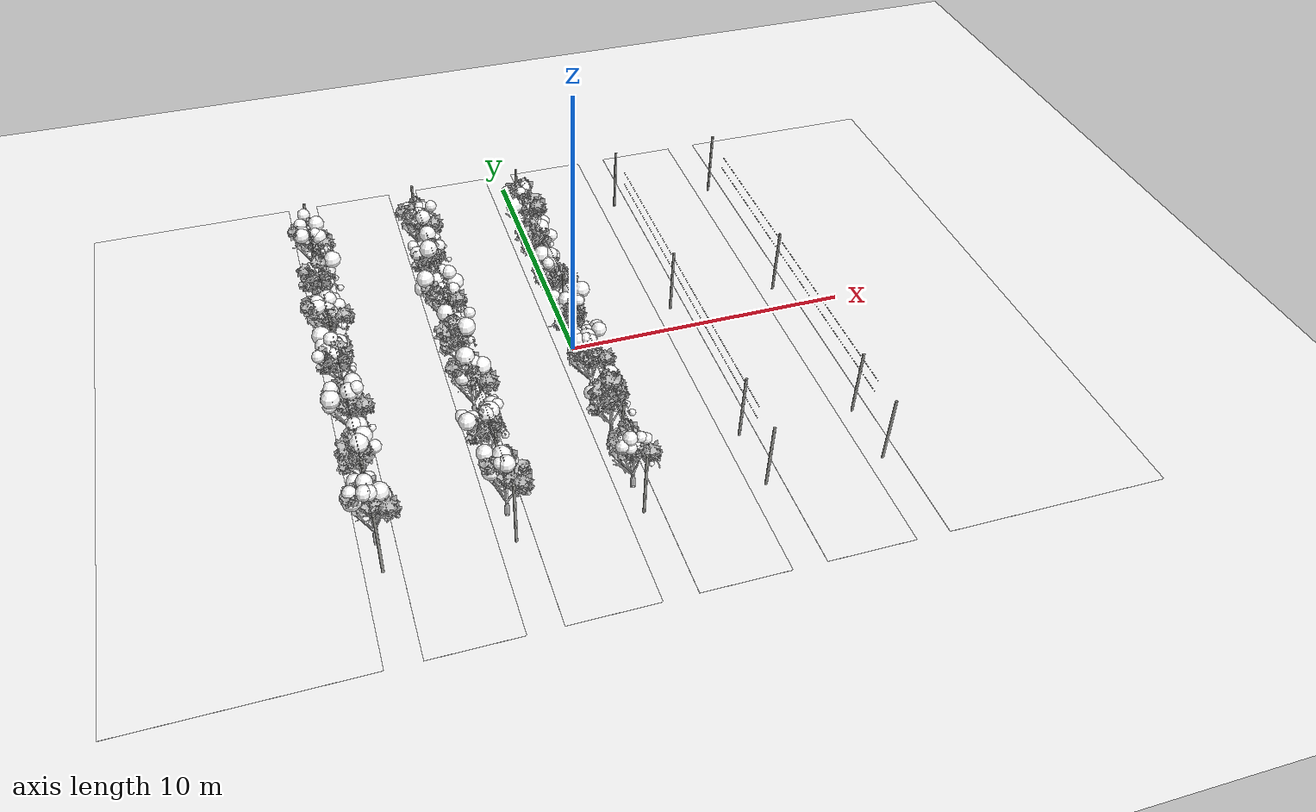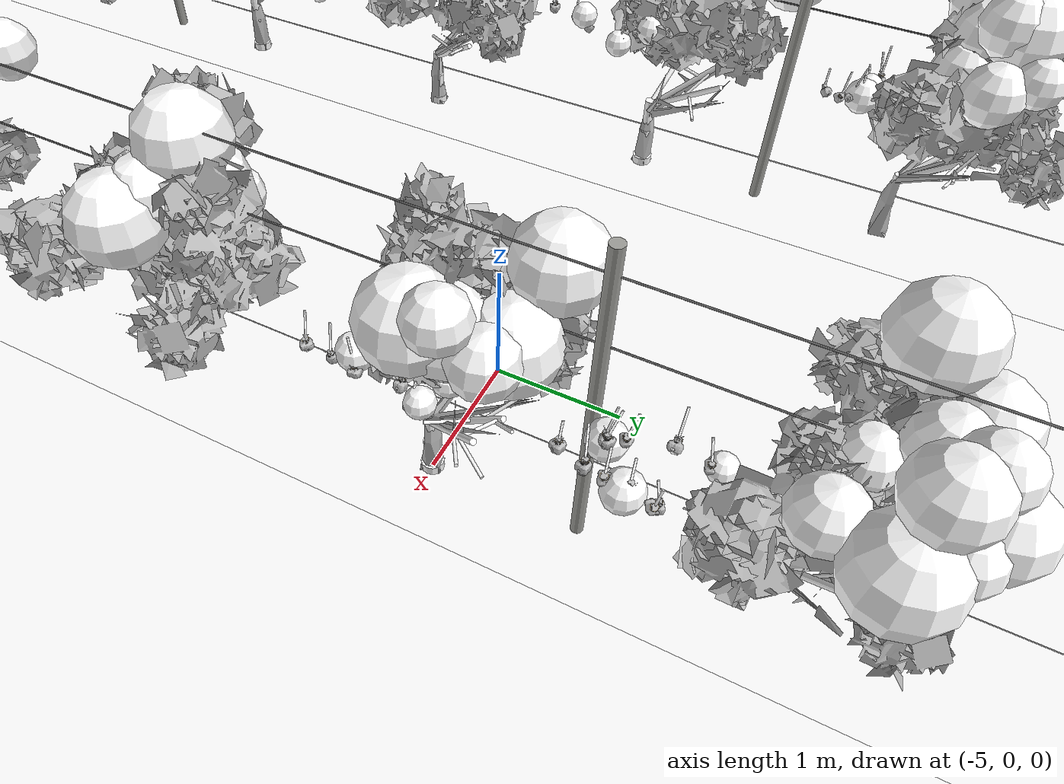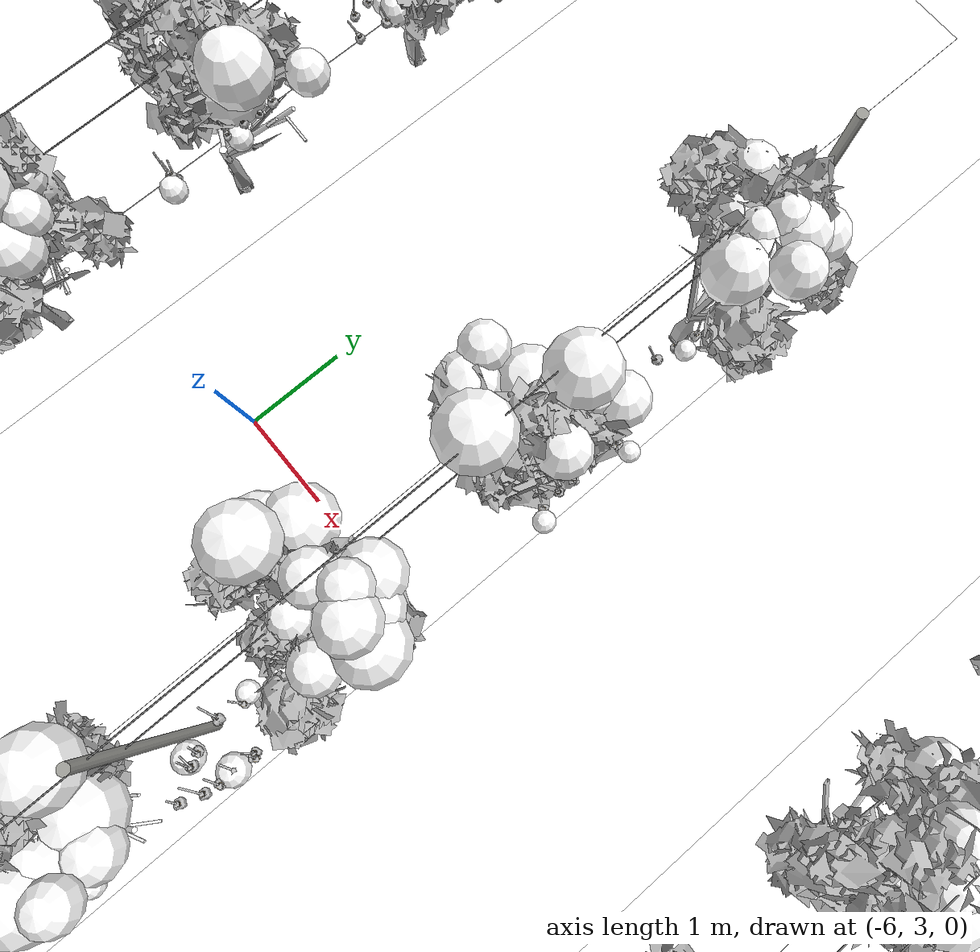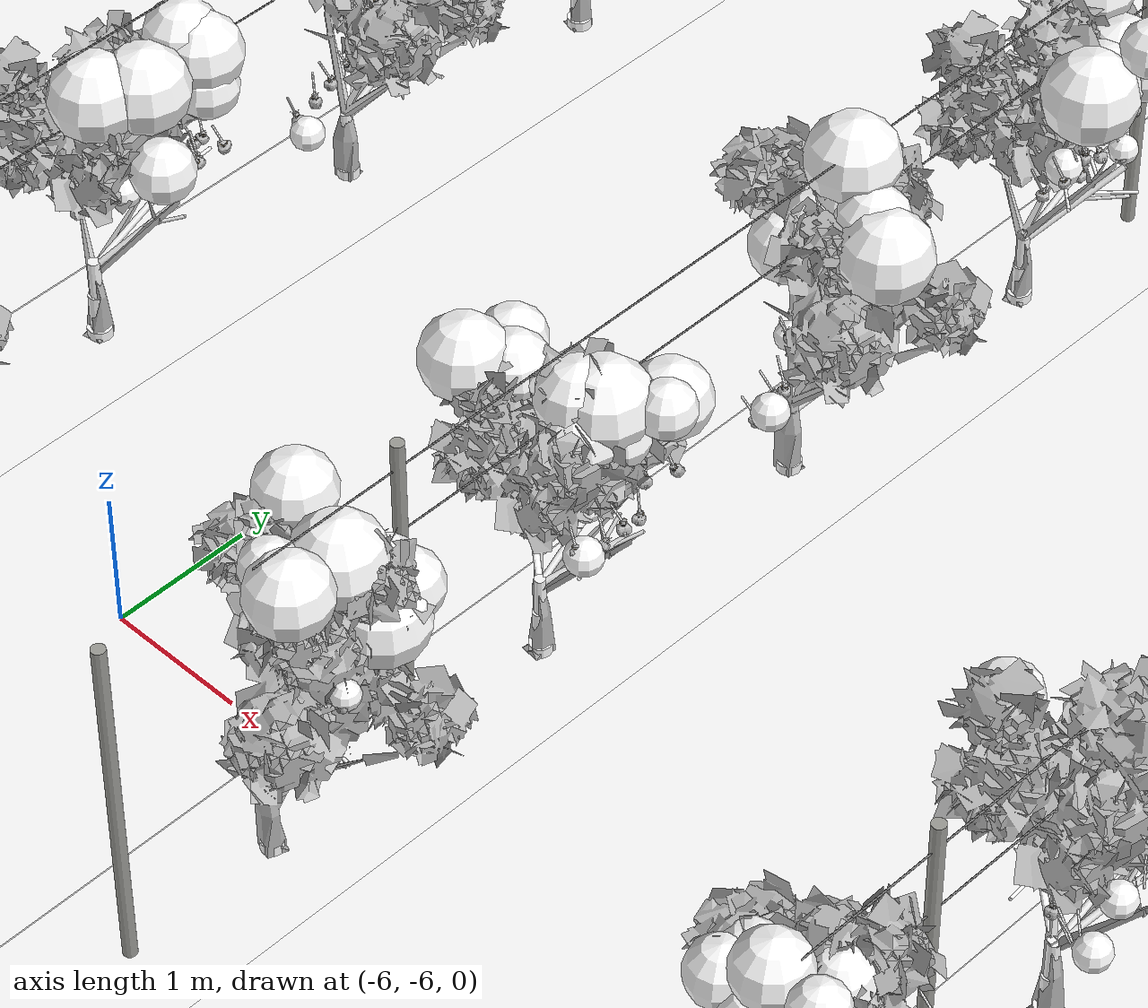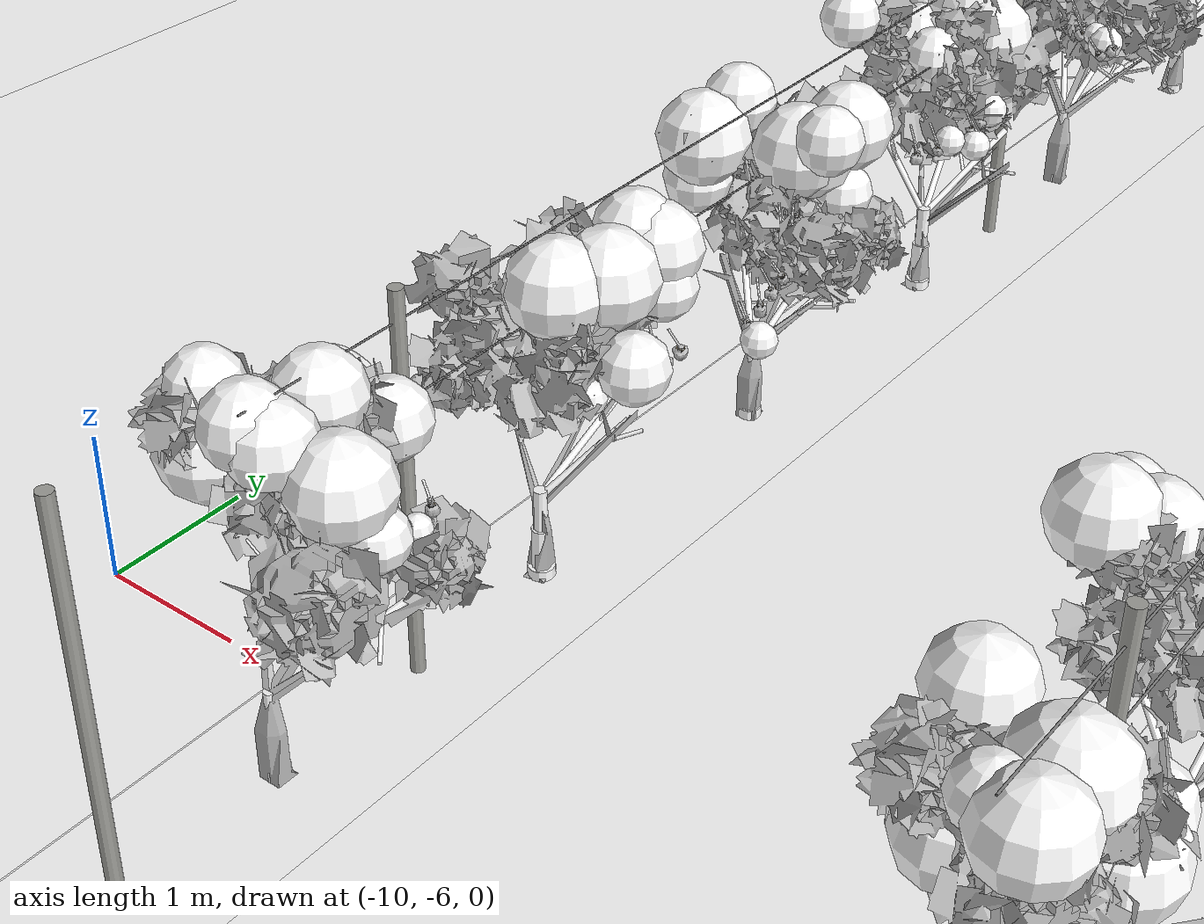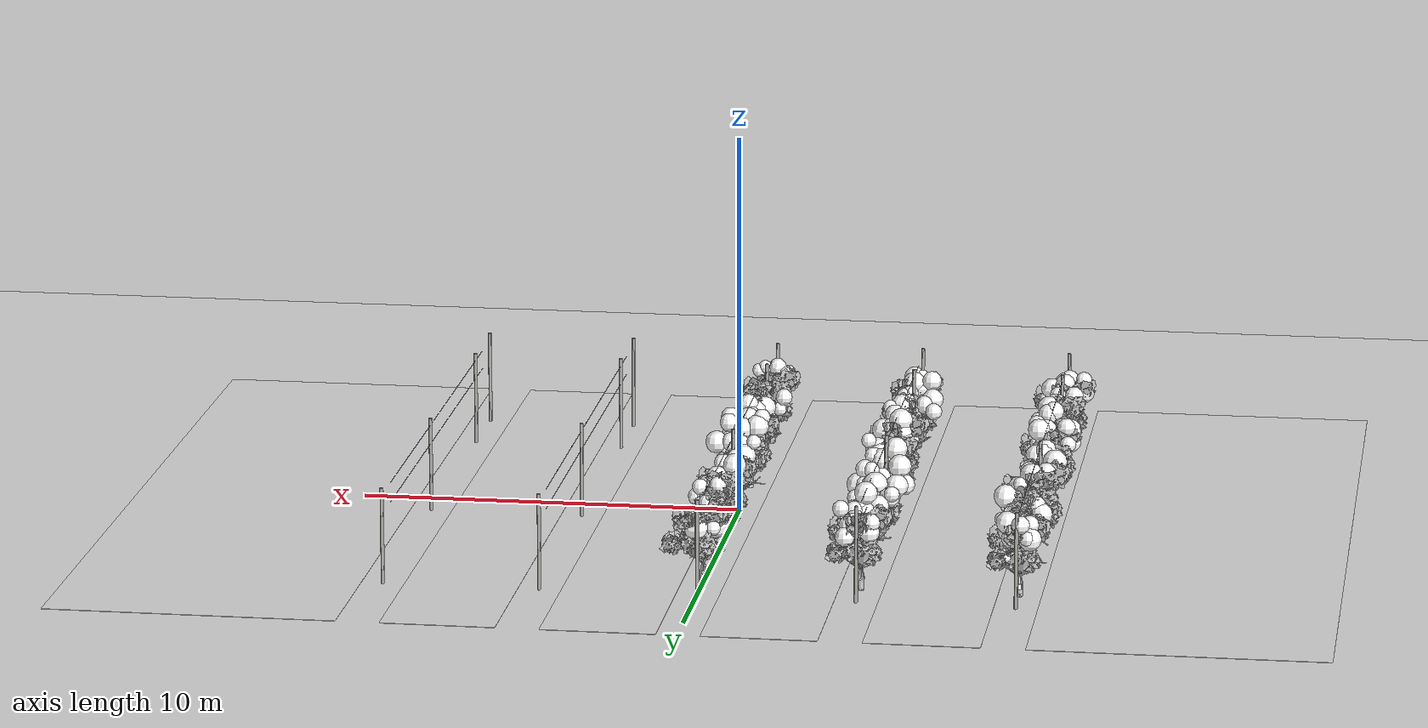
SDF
<sdf version="1.11">
 <world name="peach_orchard">
  <physics name="4ms" type="ignored">
   <max_step_size>0.004</max_step_size>
   <real_time_factor>1</real_time_factor>
  </physics>
  <plugin name="gz::sim::systems::Physics" filename="gz-sim-physics-system"/>
  <plugin name="gz::sim::systems::UserCommands" filename="gz-sim-user-commands-system"/>
  <plugin name="gz::sim::systems::SceneBroadcaster" filename="gz-sim-scene-broadcaster-system"/>
  <scene>
   <ambient>0.78 0.76 0.78 1</ambient>
   <background>0.53 0.67 0.88 1</background>
   <shadows>true</shadows>
   <sky>
    <clouds><speed>4</speed><direction>1.2</direction><humidity>0.6</humidity><mean_size>0.8</mean_size></clouds>
   </sky>
   <fog><density>0.002</density><color>0.85 0.88 0.92 1</color></fog>
  </scene>
  <light name="sun" type="directional">
   <pose>0 0 30 0 0 0</pose>
   <diffuse>1 0.97 0.92 1</diffuse>
   <intensity>4</intensity>
   <specular>0.3 0.3 0.3 1</specular>
   <attenuation>
    <range>1000</range>
    <constant>0.9</constant>
    <linear>0.01</linear>
    <quadratic>0.001</quadratic>
   </attenuation>
   <direction>0.557208 -0.557208 -0.615661</direction>
  </light>
  <model name="ground">
   <static>true</static>
   <link name="link">
    <visual name="soil">
     <geometry><plane><normal>0 0 1</normal><size>32 22</size></plane></geometry>
     <material>
      <ambient>1 1 1 1</ambient>
      <diffuse>1 1 1 1</diffuse>
      <specular>0.1 0.1 0.1 1</specular>
      <pbr>
       <metal>
        <albedo_map>textures/soil_albedo.png</albedo_map>
        <normal_map type="tangent">textures/soil_normal.png</normal_map>
        <roughness>0.95</roughness>
        <metalness>0</metalness>
       </metal>
      </pbr>
     </material>
    </visual>
    <collision name="c_soil">
     <geometry><plane><normal>0 0 1</normal><size>32 22</size></plane></geometry>
    </collision>
   </link>
  </model>
  <model name="ground_cover">
   <static>true</static>
   <link name="link">
    <visual name="grass_0">
     <pose>-12.275 0 0.006 0 0 0</pose>
     <geometry><box><size>7.45 22 0.012</size></box></geometry>
     <material>
      <ambient>1 1 1 1</ambient>
      <diffuse>1 1 1 1</diffuse>
      <specular>0.1 0.1 0.1 1</specular>
      <pbr>
       <metal>
        <albedo_map>textures/grass_albedo.png</albedo_map>
        <normal_map type="tangent">textures/grass_normal.png</normal_map>
        <roughness>0.95</roughness>
        <metalness>0</metalness>
       </metal>
      </pbr>
     </material>
    </visual>
    <visual name="grass_1">
     <pose>12.275 0 0.006 0 0 0</pose>
     <geometry><box><size>7.45 22 0.012</size></box></geometry>
     <material>
      <ambient>1 1 1 1</ambient>
      <diffuse>1 1 1 1</diffuse>
      <specular>0.1 0.1 0.1 1</specular>
      <pbr>
       <metal>
        <albedo_map>textures/grass_albedo.png</albedo_map>
        <normal_map type="tangent">textures/grass_normal.png</normal_map>
        <roughness>0.95</roughness>
        <metalness>0</metalness>
       </metal>
      </pbr>
     </material>
    </visual>
    <visual name="grass_2">
     <pose>-6 0 0.006 0 0 0</pose>
     <geometry><box><size>2.9 22 0.012</size></box></geometry>
     <material>
      <ambient>1 1 1 1</ambient>
      <diffuse>1 1 1 1</diffuse>
      <specular>0.1 0.1 0.1 1</specular>
      <pbr>
       <metal>
        <albedo_map>textures/grass_albedo.png</albedo_map>
        <normal_map type="tangent">textures/grass_normal.png</normal_map>
        <roughness>0.95</roughness>
        <metalness>0</metalness>
       </metal>
      </pbr>
     </material>
    </visual>
    <visual name="grass_3">
     <pose>-2 0 0.006 0 0 0</pose>
     <geometry><box><size>2.9 22 0.012</size></box></geometry>
     <material>
      <ambient>1 1 1 1</ambient>
      <diffuse>1 1 1 1</diffuse>
      <specular>0.1 0.1 0.1 1</specular>
      <pbr>
       <metal>
        <albedo_map>textures/grass_albedo.png</albedo_map>
        <normal_map type="tangent">textures/grass_normal.png</normal_map>
        <roughness>0.95</roughness>
        <metalness>0</metalness>
       </metal>
      </pbr>
     </material>
    </visual>
    <visual name="grass_4">
     <pose>2 0 0.006 0 0 0</pose>
     <geometry><box><size>2.9 22 0.012</size></box></geometry>
     <material>
      <ambient>1 1 1 1</ambient>
      <diffuse>1 1 1 1</diffuse>
      <specular>0.1 0.1 0.1 1</specular>
      <pbr>
       <metal>
        <albedo_map>textures/grass_albedo.png</albedo_map>
        <normal_map type="tangent">textures/grass_normal.png</normal_map>
        <roughness>0.95</roughness>
        <metalness>0</metalness>
       </metal>
      </pbr>
     </material>
    </visual>
    <visual name="grass_5">
     <pose>6 0 0.006 0 0 0</pose>
     <geometry><box><size>2.9 22 0.012</size></box></geometry>
     <material>
      <ambient>1 1 1 1</ambient>
      <diffuse>1 1 1 1</diffuse>
      <specular>0.1 0.1 0.1 1</specular>
      <pbr>
       <metal>
        <albedo_map>textures/grass_albedo.png</albedo_map>
        <normal_map type="tangent">textures/grass_normal.png</normal_map>
        <roughness>0.95</roughness>
        <metalness>0</metalness>
       </metal>
      </pbr>
     </material>
    </visual>
   </link>
  </model>
  <model name="trellis_row_0">
   <static>true</static>
   <link name="link">
    <visual name="post_0">
     <pose>-8 -7.7 1.25 0 0 0</pose>
     <geometry><cylinder><radius>0.045</radius><length>2.5</length></cylinder></geometry>
     <material>
      <ambient>0.62 0.62 0.6 1</ambient>
      <diffuse>0.62 0.62 0.6 1</diffuse>
      <specular>0.1 0.1 0.1 1</specular>
     </material>
    </visual>
    <collision name="c_post_0">
     <pose>-8 -7.7 1.25 0 0 0</pose>
     <geometry><cylinder><radius>0.045</radius><length>2.5</length></cylinder></geometry>
    </collision>
    <visual name="post_1">
     <pose>-8 7.7 1.25 0 0 0</pose>
     <geometry><cylinder><radius>0.045</radius><length>2.5</length></cylinder></geometry>
     <material>
      <ambient>0.62 0.62 0.6 1</ambient>
      <diffuse>0.62 0.62 0.6 1</diffuse>
      <specular>0.1 0.1 0.1 1</specular>
     </material>
    </visual>
    <collision name="c_post_1">
     <pose>-8 7.7 1.25 0 0 0</pose>
     <geometry><cylinder><radius>0.045</radius><length>2.5</length></cylinder></geometry>
    </collision>
    <visual name="post_2">
     <pose>-8 -5.5 1.25 0 0 0</pose>
     <geometry><cylinder><radius>0.045</radius><length>2.5</length></cylinder></geometry>
     <material>
      <ambient>0.62 0.62 0.6 1</ambient>
      <diffuse>0.62 0.62 0.6 1</diffuse>
      <specular>0.1 0.1 0.1 1</specular>
     </material>
    </visual>
    <collision name="c_post_2">
     <pose>-8 -5.5 1.25 0 0 0</pose>
     <geometry><cylinder><radius>0.045</radius><length>2.5</length></cylinder></geometry>
    </collision>
    <visual name="post_3">
     <pose>-8 1.1 1.25 0 0 0</pose>
     <geometry><cylinder><radius>0.045</radius><length>2.5</length></cylinder></geometry>
     <material>
      <ambient>0.62 0.62 0.6 1</ambient>
      <diffuse>0.62 0.62 0.6 1</diffuse>
      <specular>0.1 0.1 0.1 1</specular>
     </material>
    </visual>
    <collision name="c_post_3">
     <pose>-8 1.1 1.25 0 0 0</pose>
     <geometry><cylinder><radius>0.045</radius><length>2.5</length></cylinder></geometry>
    </collision>
    <visual name="wire_0">
     <pose>-8 0 1.8 0 1.5708 1.5708</pose>
     <geometry><cylinder><radius>0.006</radius><length>13.2</length></cylinder></geometry>
     <material>
      <ambient>0.45 0.45 0.45 1</ambient>
      <diffuse>0.45 0.45 0.45 1</diffuse>
      <specular>0.1 0.1 0.1 1</specular>
     </material>
    </visual>
    <visual name="wire_1">
     <pose>-8 0 2.3 0 1.5708 1.5708</pose>
     <geometry><cylinder><radius>0.006</radius><length>13.2</length></cylinder></geometry>
     <material>
      <ambient>0.45 0.45 0.45 1</ambient>
      <diffuse>0.45 0.45 0.45 1</diffuse>
      <specular>0.1 0.1 0.1 1</specular>
     </material>
    </visual>
   </link>
  </model>
  <model name="trellis_row_1">
   <static>true</static>
   <link name="link">
    <visual name="post_0">
     <pose>-4 -7.7 1.25 0 0 0</pose>
     <geometry><cylinder><radius>0.045</radius><length>2.5</length></cylinder></geometry>
     <material>
      <ambient>0.62 0.62 0.6 1</ambient>
      <diffuse>0.62 0.62 0.6 1</diffuse>
      <specular>0.1 0.1 0.1 1</specular>
     </material>
    </visual>
    <collision name="c_post_0">
     <pose>-4 -7.7 1.25 0 0 0</pose>
     <geometry><cylinder><radius>0.045</radius><length>2.5</length></cylinder></geometry>
    </collision>
    <visual name="post_1">
     <pose>-4 7.7 1.25 0 0 0</pose>
     <geometry><cylinder><radius>0.045</radius><length>2.5</length></cylinder></geometry>
     <material>
      <ambient>0.62 0.62 0.6 1</ambient>
      <diffuse>0.62 0.62 0.6 1</diffuse>
      <specular>0.1 0.1 0.1 1</specular>
     </material>
    </visual>
    <collision name="c_post_1">
     <pose>-4 7.7 1.25 0 0 0</pose>
     <geometry><cylinder><radius>0.045</radius><length>2.5</length></cylinder></geometry>
    </collision>
    <visual name="post_2">
     <pose>-4 -5.5 1.25 0 0 0</pose>
     <geometry><cylinder><radius>0.045</radius><length>2.5</length></cylinder></geometry>
     <material>
      <ambient>0.62 0.62 0.6 1</ambient>
      <diffuse>0.62 0.62 0.6 1</diffuse>
      <specular>0.1 0.1 0.1 1</specular>
     </material>
    </visual>
    <collision name="c_post_2">
     <pose>-4 -5.5 1.25 0 0 0</pose>
     <geometry><cylinder><radius>0.045</radius><length>2.5</length></cylinder></geometry>
    </collision>
    <visual name="post_3">
     <pose>-4 1.1 1.25 0 0 0</pose>
     <geometry><cylinder><radius>0.045</radius><length>2.5</length></cylinder></geometry>
     <material>
      <ambient>0.62 0.62 0.6 1</ambient>
      <diffuse>0.62 0.62 0.6 1</diffuse>
      <specular>0.1 0.1 0.1 1</specular>
     </material>
    </visual>
    <collision name="c_post_3">
     <pose>-4 1.1 1.25 0 0 0</pose>
     <geometry><cylinder><radius>0.045</radius><length>2.5</length></cylinder></geometry>
    </collision>
    <visual name="wire_0">
     <pose>-4 0 1.8 0 1.5708 1.5708</pose>
     <geometry><cylinder><radius>0.006</radius><length>13.2</length></cylinder></geometry>
     <material>
      <ambient>0.45 0.45 0.45 1</ambient>
      <diffuse>0.45 0.45 0.45 1</diffuse>
      <specular>0.1 0.1 0.1 1</specular>
     </material>
    </visual>
    <visual name="wire_1">
     <pose>-4 0 2.3 0 1.5708 1.5708</pose>
     <geometry><cylinder><radius>0.006</radius><length>13.2</length></cylinder></geometry>
     <material>
      <ambient>0.45 0.45 0.45 1</ambient>
      <diffuse>0.45 0.45 0.45 1</diffuse>
      <specular>0.1 0.1 0.1 1</specular>
     </material>
    </visual>
   </link>
  </model>
  <model name="trellis_row_2">
   <static>true</static>
   <link name="link">
    <visual name="post_0">
     <pose>0 -7.7 1.25 0 0 0</pose>
     <geometry><cylinder><radius>0.045</radius><length>2.5</length></cylinder></geometry>
     <material>
      <ambient>0.62 0.62 0.6 1</ambient>
      <diffuse>0.62 0.62 0.6 1</diffuse>
      <specular>0.1 0.1 0.1 1</specular>
     </material>
    </visual>
    <collision name="c_post_0">
     <pose>0 -7.7 1.25 0 0 0</pose>
     <geometry><cylinder><radius>0.045</radius><length>2.5</length></cylinder></geometry>
    </collision>
    <visual name="post_1">
     <pose>0 7.7 1.25 0 0 0</pose>
     <geometry><cylinder><radius>0.045</radius><length>2.5</length></cylinder></geometry>
     <material>
      <ambient>0.62 0.62 0.6 1</ambient>
      <diffuse>0.62 0.62 0.6 1</diffuse>
      <specular>0.1 0.1 0.1 1</specular>
     </material>
    </visual>
    <collision name="c_post_1">
     <pose>0 7.7 1.25 0 0 0</pose>
     <geometry><cylinder><radius>0.045</radius><length>2.5</length></cylinder></geometry>
    </collision>
    <visual name="post_2">
     <pose>0 -5.5 1.25 0 0 0</pose>
     <geometry><cylinder><radius>0.045</radius><length>2.5</length></cylinder></geometry>
     <material>
      <ambient>0.62 0.62 0.6 1</ambient>
      <diffuse>0.62 0.62 0.6 1</diffuse>
      <specular>0.1 0.1 0.1 1</specular>
     </material>
    </visual>
    <collision name="c_post_2">
     <pose>0 -5.5 1.25 0 0 0</pose>
     <geometry><cylinder><radius>0.045</radius><length>2.5</length></cylinder></geometry>
    </collision>
    <visual name="post_3">
     <pose>0 1.1 1.25 0 0 0</pose>
     <geometry><cylinder><radius>0.045</radius><length>2.5</length></cylinder></geometry>
     <material>
      <ambient>0.62 0.62 0.6 1</ambient>
      <diffuse>0.62 0.62 0.6 1</diffuse>
      <specular>0.1 0.1 0.1 1</specular>
     </material>
    </visual>
    <collision name="c_post_3">
     <pose>0 1.1 1.25 0 0 0</pose>
     <geometry><cylinder><radius>0.045</radius><length>2.5</length></cylinder></geometry>
    </collision>
    <visual name="wire_0">
     <pose>0 0 1.8 0 1.5708 1.5708</pose>
     <geometry><cylinder><radius>0.006</radius><length>13.2</length></cylinder></geometry>
     <material>
      <ambient>0.45 0.45 0.45 1</ambient>
      <diffuse>0.45 0.45 0.45 1</diffuse>
      <specular>0.1 0.1 0.1 1</specular>
     </material>
    </visual>
    <visual name="wire_1">
     <pose>0 0 2.3 0 1.5708 1.5708</pose>
     <geometry><cylinder><radius>0.006</radius><length>13.2</length></cylinder></geometry>
     <material>
      <ambient>0.45 0.45 0.45 1</ambient>
      <diffuse>0.45 0.45 0.45 1</diffuse>
      <specular>0.1 0.1 0.1 1</specular>
     </material>
    </visual>
   </link>
  </model>
  <model name="trellis_row_3">
   <static>true</static>
   <link name="link">
    <visual name="post_0">
     <pose>4 -7.7 1.25 0 0 0</pose>
     <geometry><cylinder><radius>0.045</radius><length>2.5</length></cylinder></geometry>
     <material>
      <ambient>0.62 0.62 0.6 1</ambient>
      <diffuse>0.62 0.62 0.6 1</diffuse>
      <specular>0.1 0.1 0.1 1</specular>
     </material>
    </visual>
    <collision name="c_post_0">
     <pose>4 -7.7 1.25 0 0 0</pose>
     <geometry><cylinder><radius>0.045</radius><length>2.5</length></cylinder></geometry>
    </collision>
    <visual name="post_1">
     <pose>4 7.7 1.25 0 0 0</pose>
     <geometry><cylinder><radius>0.045</radius><length>2.5</length></cylinder></geometry>
     <material>
      <ambient>0.62 0.62 0.6 1</ambient>
      <diffuse>0.62 0.62 0.6 1</diffuse>
      <specular>0.1 0.1 0.1 1</specular>
     </material>
    </visual>
    <collision name="c_post_1">
     <pose>4 7.7 1.25 0 0 0</pose>
     <geometry><cylinder><radius>0.045</radius><length>2.5</length></cylinder></geometry>
    </collision>
    <visual name="post_2">
     <pose>4 -5.5 1.25 0 0 0</pose>
     <geometry><cylinder><radius>0.045</radius><length>2.5</length></cylinder></geometry>
     <material>
      <ambient>0.62 0.62 0.6 1</ambient>
      <diffuse>0.62 0.62 0.6 1</diffuse>
      <specular>0.1 0.1 0.1 1</specular>
     </material>
    </visual>
    <collision name="c_post_2">
     <pose>4 -5.5 1.25 0 0 0</pose>
     <geometry><cylinder><radius>0.045</radius><length>2.5</length></cylinder></geometry>
    </collision>
    <visual name="post_3">
     <pose>4 1.1 1.25 0 0 0</pose>
     <geometry><cylinder><radius>0.045</radius><length>2.5</length></cylinder></geometry>
     <material>
      <ambient>0.62 0.62 0.6 1</ambient>
      <diffuse>0.62 0.62 0.6 1</diffuse>
      <specular>0.1 0.1 0.1 1</specular>
     </material>
    </visual>
    <collision name="c_post_3">
     <pose>4 1.1 1.25 0 0 0</pose>
     <geometry><cylinder><radius>0.045</radius><length>2.5</length></cylinder></geometry>
    </collision>
    <visual name="wire_0">
     <pose>4 0 1.8 0 1.5708 1.5708</pose>
     <geometry><cylinder><radius>0.006</radius><length>13.2</length></cylinder></geometry>
     <material>
      <ambient>0.45 0.45 0.45 1</ambient>
      <diffuse>0.45 0.45 0.45 1</diffuse>
      <specular>0.1 0.1 0.1 1</specular>
     </material>
    </visual>
    <visual name="wire_1">
     <pose>4 0 2.3 0 1.5708 1.5708</pose>
     <geometry><cylinder><radius>0.006</radius><length>13.2</length></cylinder></geometry>
     <material>
      <ambient>0.45 0.45 0.45 1</ambient>
      <diffuse>0.45 0.45 0.45 1</diffuse>
      <specular>0.1 0.1 0.1 1</specular>
     </material>
    </visual>
   </link>
  </model>
  <model name="trellis_row_4">
   <static>true</static>
   <link name="link">
    <visual name="post_0">
     <pose>8 -7.7 1.25 0 0 0</pose>
     <geometry><cylinder><radius>0.045</radius><length>2.5</length></cylinder></geometry>
     <material>
      <ambient>0.62 0.62 0.6 1</ambient>
      <diffuse>0.62 0.62 0.6 1</diffuse>
      <specular>0.1 0.1 0.1 1</specular>
     </material>
    </visual>
    <collision name="c_post_0">
     <pose>8 -7.7 1.25 0 0 0</pose>
     <geometry><cylinder><radius>0.045</radius><length>2.5</length></cylinder></geometry>
    </collision>
    <visual name="post_1">
     <pose>8 7.7 1.25 0 0 0</pose>
     <geometry><cylinder><radius>0.045</radius><length>2.5</length></cylinder></geometry>
     <material>
      <ambient>0.62 0.62 0.6 1</ambient>
      <diffuse>0.62 0.62 0.6 1</diffuse>
      <specular>0.1 0.1 0.1 1</specular>
     </material>
    </visual>
    <collision name="c_post_1">
     <pose>8 7.7 1.25 0 0 0</pose>
     <geometry><cylinder><radius>0.045</radius><length>2.5</length></cylinder></geometry>
    </collision>
    <visual name="post_2">
     <pose>8 -5.5 1.25 0 0 0</pose>
     <geometry><cylinder><radius>0.045</radius><length>2.5</length></cylinder></geometry>
     <material>
      <ambient>0.62 0.62 0.6 1</ambient>
      <diffuse>0.62 0.62 0.6 1</diffuse>
      <specular>0.1 0.1 0.1 1</specular>
     </material>
    </visual>
    <collision name="c_post_2">
     <pose>8 -5.5 1.25 0 0 0</pose>
     <geometry><cylinder><radius>0.045</radius><length>2.5</length></cylinder></geometry>
    </collision>
    <visual name="post_3">
     <pose>8 1.1 1.25 0 0 0</pose>
     <geometry><cylinder><radius>0.045</radius><length>2.5</length></cylinder></geometry>
     <material>
      <ambient>0.62 0.62 0.6 1</ambient>
      <diffuse>0.62 0.62 0.6 1</diffuse>
      <specular>0.1 0.1 0.1 1</specular>
     </material>
    </visual>
    <collision name="c_post_3">
     <pose>8 1.1 1.25 0 0 0</pose>
     <geometry><cylinder><radius>0.045</radius><length>2.5</length></cylinder></geometry>
    </collision>
    <visual name="wire_0">
     <pose>8 0 1.8 0 1.5708 1.5708</pose>
     <geometry><cylinder><radius>0.006</radius><length>13.2</length></cylinder></geometry>
     <material>
      <ambient>0.45 0.45 0.45 1</ambient>
      <diffuse>0.45 0.45 0.45 1</diffuse>
      <specular>0.1 0.1 0.1 1</specular>
     </material>
    </visual>
    <visual name="wire_1">
     <pose>8 0 2.3 0 1.5708 1.5708</pose>
     <geometry><cylinder><radius>0.006</radius><length>13.2</length></cylinder></geometry>
     <material>
      <ambient>0.45 0.45 0.45 1</ambient>
      <diffuse>0.45 0.45 0.45 1</diffuse>
      <specular>0.1 0.1 0.1 1</specular>
     </material>
    </visual>
   </link>
  </model>
  <model name="tree_r0_t0">
   <pose>-8 -6.6 0 0 0 0</pose>
   <static>true</static>
   <link name="link">
    <visual name="tree_mesh">
     <pose>0 0 0 0 0 0.00424783</pose>
     <geometry>
      <mesh><uri>model://peach_sim/meshes/peach_tree_a.glb</uri><scale>1.01858 1.01858 1.01858</scale></mesh>
     </geometry>
    </visual>
    <visual name="trunk_0">
     <pose>0 0 0.163314 0 0 0</pose>
     <geometry><cylinder><radius>0.0460757</radius><length>0.326629</length></cylinder></geometry>
     <material>
      <ambient>1 1 1 1</ambient>
      <diffuse>1 1 1 1</diffuse>
      <specular>0.1 0.1 0.1 1</specular>
      <pbr>
       <metal>
        <albedo_map>textures/bark_albedo.png</albedo_map>
        <normal_map type="tangent">textures/bark_normal.png</normal_map>
        <roughness>0.9</roughness>
        <metalness>0</metalness>
       </metal>
      </pbr>
     </material>
    </visual>
    <collision name="c_trunk_0">
     <pose>0 0 0.163314 0 0 0</pose>
     <geometry><cylinder><radius>0.0460757</radius><length>0.326629</length></cylinder></geometry>
    </collision>
    <visual name="trunk_1">
     <pose>0 0 0.46025 0 0 0</pose>
     <geometry><cylinder><radius>0.0331745</radius><length>0.267242</length></cylinder></geometry>
     <material>
      <ambient>1 1 1 1</ambient>
      <diffuse>1 1 1 1</diffuse>
      <specular>0.1 0.1 0.1 1</specular>
      <pbr>
       <metal>
        <albedo_map>textures/bark_albedo.png</albedo_map>
        <normal_map type="tangent">textures/bark_normal.png</normal_map>
        <roughness>0.9</roughness>
        <metalness>0</metalness>
       </metal>
      </pbr>
     </material>
    </visual>
    <collision name="c_trunk_1">
     <pose>0 0 0.46025 0 0 0</pose>
     <geometry><cylinder><radius>0.0331745</radius><length>0.267242</length></cylinder></geometry>
    </collision>
    <visual name="root_flare">
     <pose>0 0 0.035 0 0 0</pose>
     <geometry><cylinder><radius>0.0668097</radius><length>0.07</length></cylinder></geometry>
     <material>
      <ambient>1 1 1 1</ambient>
      <diffuse>1 1 1 1</diffuse>
      <specular>0.1 0.1 0.1 1</specular>
      <pbr>
       <metal>
        <albedo_map>textures/bark_albedo.png</albedo_map>
        <normal_map type="tangent">textures/bark_normal.png</normal_map>
        <roughness>0.95</roughness>
        <metalness>0</metalness>
       </metal>
      </pbr>
     </material>
    </visual>
    <visual name="scaffold_0">
     <pose>-0.0405091 0.339771 0.764963 0 1.00229 1.68946</pose>
     <geometry><cylinder><radius>0.022</radius><length>0.812089</length></cylinder></geometry>
     <material>
      <ambient>1 1 1 1</ambient>
      <diffuse>1 1 1 1</diffuse>
      <specular>0.1 0.1 0.1 1</specular>
      <pbr>
       <metal>
        <albedo_map>textures/bark_albedo.png</albedo_map>
        <normal_map type="tangent">textures/bark_normal.png</normal_map>
        <roughness>0.9</roughness>
        <metalness>0</metalness>
       </metal>
      </pbr>
     </material>
    </visual>
    <collision name="c_scaffold_0">
     <pose>-0.0405091 0.339771 0.764963 0 1.00229 1.68946</pose>
     <geometry><cylinder><radius>0.022</radius><length>0.812089</length></cylinder></geometry>
    </collision>
    <visual name="branchlet_0_0">
     <pose>-0.112781 0.222014 0.727966 0 1.73849 -2.26043</pose>
     <geometry><cylinder><radius>0.012</radius><length>0.240414</length></cylinder></geometry>
     <material>
      <ambient>1 1 1 1</ambient>
      <diffuse>1 1 1 1</diffuse>
      <specular>0.1 0.1 0.1 1</specular>
      <pbr>
       <metal>
        <albedo_map>textures/bark_albedo.png</albedo_map>
        <normal_map type="tangent">textures/bark_normal.png</normal_map>
        <roughness>0.9</roughness>
        <metalness>0</metalness>
       </metal>
      </pbr>
     </material>
    </visual>
    <visual name="branchlet_0_1">
     <pose>-0.0352857 0.490804 1.02807 0 0.147237 -0.186205</pose>
     <geometry><cylinder><radius>0.012</radius><length>0.32967</length></cylinder></geometry>
     <material>
      <ambient>1 1 1 1</ambient>
      <diffuse>1 1 1 1</diffuse>
      <specular>0.1 0.1 0.1 1</specular>
      <pbr>
       <metal>
        <albedo_map>textures/bark_albedo.png</albedo_map>
        <normal_map type="tangent">textures/bark_normal.png</normal_map>
        <roughness>0.9</roughness>
        <metalness>0</metalness>
       </metal>
      </pbr>
     </material>
    </visual>
    <visual name="branchlet_0_2">
     <pose>-0.0392614 0.322034 0.909342 0 0.825081 -1.46077</pose>
     <geometry><cylinder><radius>0.012</radius><length>0.271349</length></cylinder></geometry>
     <material>
      <ambient>1 1 1 1</ambient>
      <diffuse>1 1 1 1</diffuse>
      <specular>0.1 0.1 0.1 1</specular>
      <pbr>
       <metal>
        <albedo_map>textures/bark_albedo.png</albedo_map>
        <normal_map type="tangent">textures/bark_normal.png</normal_map>
        <roughness>0.9</roughness>
        <metalness>0</metalness>
       </metal>
      </pbr>
     </material>
    </visual>
    <visual name="scaffold_1">
     <pose>0.201215 0.317295 0.767262 0 1.03929 1.00564</pose>
     <geometry><cylinder><radius>0.022</radius><length>0.87169</length></cylinder></geometry>
     <material>
      <ambient>1 1 1 1</ambient>
      <diffuse>1 1 1 1</diffuse>
      <specular>0.1 0.1 0.1 1</specular>
      <pbr>
       <metal>
        <albedo_map>textures/bark_albedo.png</albedo_map>
        <normal_map type="tangent">textures/bark_normal.png</normal_map>
        <roughness>0.9</roughness>
        <metalness>0</metalness>
       </metal>
      </pbr>
     </material>
    </visual>
    <collision name="c_scaffold_1">
     <pose>0.201215 0.317295 0.767262 0 1.03929 1.00564</pose>
     <geometry><cylinder><radius>0.022</radius><length>0.87169</length></cylinder></geometry>
    </collision>
    <visual name="branchlet_1_0">
     <pose>0.417614 0.417147 0.873596 0 1.8249 -0.868604</pose>
     <geometry><cylinder><radius>0.012</radius><length>0.279913</length></cylinder></geometry>
     <material>
      <ambient>1 1 1 1</ambient>
      <diffuse>1 1 1 1</diffuse>
      <specular>0.1 0.1 0.1 1</specular>
      <pbr>
       <metal>
        <albedo_map>textures/bark_albedo.png</albedo_map>
        <normal_map type="tangent">textures/bark_normal.png</normal_map>
        <roughness>0.9</roughness>
        <metalness>0</metalness>
       </metal>
      </pbr>
     </material>
    </visual>
    <visual name="branchlet_1_1">
     <pose>0.183877 0.418143 0.953932 0 1.11977 -2.63989</pose>
     <geometry><cylinder><radius>0.012</radius><length>0.315938</length></cylinder></geometry>
     <material>
      <ambient>1 1 1 1</ambient>
      <diffuse>1 1 1 1</diffuse>
      <specular>0.1 0.1 0.1 1</specular>
      <pbr>
       <metal>
        <albedo_map>textures/bark_albedo.png</albedo_map>
        <normal_map type="tangent">textures/bark_normal.png</normal_map>
        <roughness>0.9</roughness>
        <metalness>0</metalness>
       </metal>
      </pbr>
     </material>
    </visual>
    <visual name="scaffold_2">
     <pose>-0.253912 0.24254 0.828736 0 0.893516 2.3791</pose>
     <geometry><cylinder><radius>0.022</radius><length>0.901183</length></cylinder></geometry>
     <material>
      <ambient>1 1 1 1</ambient>
      <diffuse>1 1 1 1</diffuse>
      <specular>0.1 0.1 0.1 1</specular>
      <pbr>
       <metal>
        <albedo_map>textures/bark_albedo.png</albedo_map>
        <normal_map type="tangent">textures/bark_normal.png</normal_map>
        <roughness>0.9</roughness>
        <metalness>0</metalness>
       </metal>
      </pbr>
     </material>
    </visual>
    <collision name="c_scaffold_2">
     <pose>-0.253912 0.24254 0.828736 0 0.893516 2.3791</pose>
     <geometry><cylinder><radius>0.022</radius><length>0.901183</length></cylinder></geometry>
    </collision>
    <visual name="branchlet_2_0">
     <pose>-0.170131 0.287708 0.95942 0 1.32319 -0.187133</pose>
     <geometry><cylinder><radius>0.012</radius><length>0.343222</length></cylinder></geometry>
     <material>
      <ambient>1 1 1 1</ambient>
      <diffuse>1 1 1 1</diffuse>
      <specular>0.1 0.1 0.1 1</specular>
      <pbr>
       <metal>
        <albedo_map>textures/bark_albedo.png</albedo_map>
        <normal_map type="tangent">textures/bark_normal.png</normal_map>
        <roughness>0.9</roughness>
        <metalness>0</metalness>
       </metal>
      </pbr>
     </material>
    </visual>
    <visual name="branchlet_2_1">
     <pose>-0.303816 0.410785 0.998983 0 0.988184 0.954062</pose>
     <geometry><cylinder><radius>0.012</radius><length>0.211072</length></cylinder></geometry>
     <material>
      <ambient>1 1 1 1</ambient>
      <diffuse>1 1 1 1</diffuse>
      <specular>0.1 0.1 0.1 1</specular>
      <pbr>
       <metal>
        <albedo_map>textures/bark_albedo.png</albedo_map>
        <normal_map type="tangent">textures/bark_normal.png</normal_map>
        <roughness>0.9</roughness>
        <metalness>0</metalness>
       </metal>
      </pbr>
     </material>
    </visual>
    <visual name="canopy_0">
     <pose>-0.301224 0.882309 1.85743 0 0 0</pose>
     <geometry><sphere><radius>0.256106</radius></sphere></geometry>
     <material>
      <ambient>1 1 1 1</ambient>
      <diffuse>1 1 1 1</diffuse>
      <specular>0.1 0.1 0.1 1</specular>
      <pbr>
       <metal>
        <albedo_map>textures/leaf_albedo.png</albedo_map>
        <normal_map type="tangent">textures/leaf_normal.png</normal_map>
        <roughness>0.85</roughness>
        <metalness>0</metalness>
       </metal>
      </pbr>
     </material>
    </visual>
    <collision name="c_canopy_0">
     <pose>-0.301224 0.882309 1.85743 0 0 0</pose>
     <geometry><sphere><radius>0.256106</radius></sphere></geometry>
    </collision>
    <visual name="canopy_1">
     <pose>0.215076 0.372278 1.87598 0 0 0</pose>
     <geometry><sphere><radius>0.2268</radius></sphere></geometry>
     <material>
      <ambient>1 1 1 1</ambient>
      <diffuse>1 1 1 1</diffuse>
      <specular>0.1 0.1 0.1 1</specular>
      <pbr>
       <metal>
        <albedo_map>textures/leaf_albedo.png</albedo_map>
        <normal_map type="tangent">textures/leaf_normal.png</normal_map>
        <roughness>0.85</roughness>
        <metalness>0</metalness>
       </metal>
      </pbr>
     </material>
    </visual>
    <collision name="c_canopy_1">
     <pose>0.215076 0.372278 1.87598 0 0 0</pose>
     <geometry><sphere><radius>0.2268</radius></sphere></geometry>
    </collision>
    <visual name="canopy_2">
     <pose>-0.493958 0.226708 1.80144 0 0 0</pose>
     <geometry><sphere><radius>0.311001</radius></sphere></geometry>
     <material>
      <ambient>1 1 1 1</ambient>
      <diffuse>1 1 1 1</diffuse>
      <specular>0.1 0.1 0.1 1</specular>
      <pbr>
       <metal>
        <albedo_map>textures/leaf_albedo.png</albedo_map>
        <normal_map type="tangent">textures/leaf_normal.png</normal_map>
        <roughness>0.85</roughness>
        <metalness>0</metalness>
       </metal>
      </pbr>
     </material>
    </visual>
    <collision name="c_canopy_2">
     <pose>-0.493958 0.226708 1.80144 0 0 0</pose>
     <geometry><sphere><radius>0.311001</radius></sphere></geometry>
    </collision>
    <visual name="canopy_3">
     <pose>0.0147764 0.179122 2.05022 0 0 0</pose>
     <geometry><sphere><radius>0.254066</radius></sphere></geometry>
     <material>
      <ambient>1 1 1 1</ambient>
      <diffuse>1 1 1 1</diffuse>
      <specular>0.1 0.1 0.1 1</specular>
      <pbr>
       <metal>
        <albedo_map>textures/leaf_albedo.png</albedo_map>
        <normal_map type="tangent">textures/leaf_normal.png</normal_map>
        <roughness>0.85</roughness>
        <metalness>0</metalness>
       </metal>
      </pbr>
     </material>
    </visual>
    <visual name="canopy_4">
     <pose>0.338598 0.303025 1.87032 0 0 0</pose>
     <geometry><sphere><radius>0.297103</radius></sphere></geometry>
     <material>
      <ambient>1 1 1 1</ambient>
      <diffuse>1 1 1 1</diffuse>
      <specular>0.1 0.1 0.1 1</specular>
      <pbr>
       <metal>
        <albedo_map>textures/leaf_albedo.png</albedo_map>
        <normal_map type="tangent">textures/leaf_normal.png</normal_map>
        <roughness>0.85</roughness>
        <metalness>0</metalness>
       </metal>
      </pbr>
     </material>
    </visual>
    <visual name="canopy_5">
     <pose>-0.513104 0.24499 2.14086 0 0 0</pose>
     <geometry><sphere><radius>0.220146</radius></sphere></geometry>
     <material>
      <ambient>1 1 1 1</ambient>
      <diffuse>1 1 1 1</diffuse>
      <specular>0.1 0.1 0.1 1</specular>
      <pbr>
       <metal>
        <albedo_map>textures/leaf_albedo.png</albedo_map>
        <normal_map type="tangent">textures/leaf_normal.png</normal_map>
        <roughness>0.85</roughness>
        <metalness>0</metalness>
       </metal>
      </pbr>
     </material>
    </visual>
    <visual name="canopy_6">
     <pose>-0.0416084 0.570118 2.11844 0 0 0</pose>
     <geometry><sphere><radius>0.257464</radius></sphere></geometry>
     <material>
      <ambient>1 1 1 1</ambient>
      <diffuse>1 1 1 1</diffuse>
      <specular>0.1 0.1 0.1 1</specular>
      <pbr>
       <metal>
        <albedo_map>textures/leaf_albedo.png</albedo_map>
        <normal_map type="tangent">textures/leaf_normal.png</normal_map>
        <roughness>0.85</roughness>
        <metalness>0</metalness>
       </metal>
      </pbr>
     </material>
    </visual>
    <visual name="canopy_7">
     <pose>0.497743 0.361038 1.60311 0 0 0</pose>
     <geometry><sphere><radius>0.184391</radius></sphere></geometry>
     <material>
      <ambient>1 1 1 1</ambient>
      <diffuse>1 1 1 1</diffuse>
      <specular>0.1 0.1 0.1 1</specular>
      <pbr>
       <metal>
        <albedo_map>textures/leaf_albedo.png</albedo_map>
        <normal_map type="tangent">textures/leaf_normal.png</normal_map>
        <roughness>0.85</roughness>
        <metalness>0</metalness>
       </metal>
      </pbr>
     </material>
    </visual>
    <visual name="canopy_8">
     <pose>-0.119655 0.143928 2.12085 0 0 0</pose>
     <geometry><sphere><radius>0.249111</radius></sphere></geometry>
     <material>
      <ambient>1 1 1 1</ambient>
      <diffuse>1 1 1 1</diffuse>
      <specular>0.1 0.1 0.1 1</specular>
      <pbr>
       <metal>
        <albedo_map>textures/leaf_albedo.png</albedo_map>
        <normal_map type="tangent">textures/leaf_normal.png</normal_map>
        <roughness>0.85</roughness>
        <metalness>0</metalness>
       </metal>
      </pbr>
     </material>
    </visual>
    <visual name="canopy_9">
     <pose>0.116707 0.889266 1.86647 0 0 0</pose>
     <geometry><sphere><radius>0.232557</radius></sphere></geometry>
     <material>
      <ambient>1 1 1 1</ambient>
      <diffuse>1 1 1 1</diffuse>
      <specular>0.1 0.1 0.1 1</specular>
      <pbr>
       <metal>
        <albedo_map>textures/leaf_albedo.png</albedo_map>
        <normal_map type="tangent">textures/leaf_normal.png</normal_map>
        <roughness>0.85</roughness>
        <metalness>0</metalness>
       </metal>
      </pbr>
     </material>
    </visual>
    <visual name="foliage_0">
     <pose>0.454566 0.291201 1.38165 0 0 0</pose>
     <geometry><sphere><radius>0.0831392</radius></sphere></geometry>
     <material>
      <ambient>1 1 1 1</ambient>
      <diffuse>1 1 1 1</diffuse>
      <specular>0.1 0.1 0.1 1</specular>
      <pbr>
       <metal>
        <albedo_map>textures/leaf_albedo.png</albedo_map>
        <normal_map type="tangent">textures/leaf_normal.png</normal_map>
        <roughness>0.85</roughness>
        <metalness>0</metalness>
       </metal>
      </pbr>
     </material>
    </visual>
    <visual name="foliage_4">
     <pose>0.405057 0.74439 1.39324 0 0 0</pose>
     <geometry><sphere><radius>0.0845656</radius></sphere></geometry>
     <material>
      <ambient>1 1 1 1</ambient>
      <diffuse>1 1 1 1</diffuse>
      <specular>0.1 0.1 0.1 1</specular>
      <pbr>
       <metal>
        <albedo_map>textures/leaf_albedo.png</albedo_map>
        <normal_map type="tangent">textures/leaf_normal.png</normal_map>
        <roughness>0.85</roughness>
        <metalness>0</metalness>
       </metal>
      </pbr>
     </material>
    </visual>
    <visual name="foliage_8">
     <pose>0.225068 0.0960242 1.40116 0 0 0</pose>
     <geometry><sphere><radius>0.0991229</radius></sphere></geometry>
     <material>
      <ambient>1 1 1 1</ambient>
      <diffuse>1 1 1 1</diffuse>
      <specular>0.1 0.1 0.1 1</specular>
      <pbr>
       <metal>
        <albedo_map>textures/leaf_albedo.png</albedo_map>
        <normal_map type="tangent">textures/leaf_normal.png</normal_map>
        <roughness>0.85</roughness>
        <metalness>0</metalness>
       </metal>
      </pbr>
     </material>
    </visual>
    <visual name="twig_0">
     <pose>0.338747 0.284009 1.56828 0 0.334398 -2.50144</pose>
     <geometry><cylinder><radius>0.007</radius><length>0.210615</length></cylinder></geometry>
     <material>
      <ambient>1 1 1 1</ambient>
      <diffuse>1 1 1 1</diffuse>
      <specular>0.1 0.1 0.1 1</specular>
      <pbr>
       <metal>
        <albedo_map>textures/bark_albedo.png</albedo_map>
        <normal_map type="tangent">textures/bark_normal.png</normal_map>
        <roughness>0.9</roughness>
        <metalness>0</metalness>
       </metal>
      </pbr>
     </material>
    </visual>
    <visual name="twig_1">
     <pose>0.324876 0.360595 1.50609 0 0.658661 2.6801</pose>
     <geometry><cylinder><radius>0.007</radius><length>0.135522</length></cylinder></geometry>
     <material>
      <ambient>1 1 1 1</ambient>
      <diffuse>1 1 1 1</diffuse>
      <specular>0.1 0.1 0.1 1</specular>
      <pbr>
       <metal>
        <albedo_map>textures/bark_albedo.png</albedo_map>
        <normal_map type="tangent">textures/bark_normal.png</normal_map>
        <roughness>0.9</roughness>
        <metalness>0</metalness>
       </metal>
      </pbr>
     </material>
    </visual>
    <visual name="twig_2">
     <pose>0.347337 0.448566 1.5714 0 0.251135 3.0998</pose>
     <geometry><cylinder><radius>0.007</radius><length>0.188275</length></cylinder></geometry>
     <material>
      <ambient>1 1 1 1</ambient>
      <diffuse>1 1 1 1</diffuse>
      <specular>0.1 0.1 0.1 1</specular>
      <pbr>
       <metal>
        <albedo_map>textures/bark_albedo.png</albedo_map>
        <normal_map type="tangent">textures/bark_normal.png</normal_map>
        <roughness>0.9</roughness>
        <metalness>0</metalness>
       </metal>
      </pbr>
     </material>
    </visual>
    <visual name="twig_3">
     <pose>0.383063 0.648681 1.56625 0 0.125123 3.03377</pose>
     <geometry><cylinder><radius>0.007</radius><length>0.163781</length></cylinder></geometry>
     <material>
      <ambient>1 1 1 1</ambient>
      <diffuse>1 1 1 1</diffuse>
      <specular>0.1 0.1 0.1 1</specular>
      <pbr>
       <metal>
        <albedo_map>textures/bark_albedo.png</albedo_map>
        <normal_map type="tangent">textures/bark_normal.png</normal_map>
        <roughness>0.9</roughness>
        <metalness>0</metalness>
       </metal>
      </pbr>
     </material>
    </visual>
    <visual name="twig_4">
     <pose>0.386243 0.848802 1.5533 0 0.721229 2.78213</pose>
     <geometry><cylinder><radius>0.007</radius><length>0.128853</length></cylinder></geometry>
     <material>
      <ambient>1 1 1 1</ambient>
      <diffuse>1 1 1 1</diffuse>
      <specular>0.1 0.1 0.1 1</specular>
      <pbr>
       <metal>
        <albedo_map>textures/bark_albedo.png</albedo_map>
        <normal_map type="tangent">textures/bark_normal.png</normal_map>
        <roughness>0.9</roughness>
        <metalness>0</metalness>
       </metal>
      </pbr>
     </material>
    </visual>
    <visual name="twig_5">
     <pose>0.216551 -0.184125 1.58977 0 0.280092 -2.645</pose>
     <geometry><cylinder><radius>0.007</radius><length>0.126573</length></cylinder></geometry>
     <material>
      <ambient>1 1 1 1</ambient>
      <diffuse>1 1 1 1</diffuse>
      <specular>0.1 0.1 0.1 1</specular>
      <pbr>
       <metal>
        <albedo_map>textures/bark_albedo.png</albedo_map>
        <normal_map type="tangent">textures/bark_normal.png</normal_map>
        <roughness>0.9</roughness>
        <metalness>0</metalness>
       </metal>
      </pbr>
     </material>
    </visual>
    <visual name="twig_6">
     <pose>0.159085 -0.093739 1.61114 0 0.676713 -2.83338</pose>
     <geometry><cylinder><radius>0.007</radius><length>0.204184</length></cylinder></geometry>
     <material>
      <ambient>1 1 1 1</ambient>
      <diffuse>1 1 1 1</diffuse>
      <specular>0.1 0.1 0.1 1</specular>
      <pbr>
       <metal>
        <albedo_map>textures/bark_albedo.png</albedo_map>
        <normal_map type="tangent">textures/bark_normal.png</normal_map>
        <roughness>0.9</roughness>
        <metalness>0</metalness>
       </metal>
      </pbr>
     </material>
    </visual>
    <visual name="twig_7">
     <pose>0.211926 -0.0429447 1.55706 0 0.650616 -3.04387</pose>
     <geometry><cylinder><radius>0.007</radius><length>0.130131</length></cylinder></geometry>
     <material>
      <ambient>1 1 1 1</ambient>
      <diffuse>1 1 1 1</diffuse>
      <specular>0.1 0.1 0.1 1</specular>
      <pbr>
       <metal>
        <albedo_map>textures/bark_albedo.png</albedo_map>
        <normal_map type="tangent">textures/bark_normal.png</normal_map>
        <roughness>0.9</roughness>
        <metalness>0</metalness>
       </metal>
      </pbr>
     </material>
    </visual>
    <visual name="twig_8">
     <pose>0.224372 0.116166 1.57143 0 0.574066 2.64883</pose>
     <geometry><cylinder><radius>0.007</radius><length>0.132598</length></cylinder></geometry>
     <material>
      <ambient>1 1 1 1</ambient>
      <diffuse>1 1 1 1</diffuse>
      <specular>0.1 0.1 0.1 1</specular>
      <pbr>
       <metal>
        <albedo_map>textures/bark_albedo.png</albedo_map>
        <normal_map type="tangent">textures/bark_normal.png</normal_map>
        <roughness>0.9</roughness>
        <metalness>0</metalness>
       </metal>
      </pbr>
     </material>
    </visual>
   </link>
  </model>
  <model name="tree_r0_t1">
   <pose>-8 -4.4 0 0 0 0</pose>
   <static>true</static>
   <link name="link">
    <visual name="tree_mesh">
     <pose>0 0 0 0 0 0.17301</pose>
     <geometry>
      <mesh><uri>model://peach_sim/meshes/peach_tree_b.glb</uri><scale>0.988746 0.988746 0.988746</scale></mesh>
     </geometry>
    </visual>
    <visual name="trunk_0">
     <pose>0 0 0.170907 0 0 0</pose>
     <geometry><cylinder><radius>0.0594638</radius><length>0.341814</length></cylinder></geometry>
     <material>
      <ambient>1 1 1 1</ambient>
      <diffuse>1 1 1 1</diffuse>
      <specular>0.1 0.1 0.1 1</specular>
      <pbr>
       <metal>
        <albedo_map>textures/bark_albedo.png</albedo_map>
        <normal_map type="tangent">textures/bark_normal.png</normal_map>
        <roughness>0.9</roughness>
        <metalness>0</metalness>
       </metal>
      </pbr>
     </material>
    </visual>
    <collision name="c_trunk_0">
     <pose>0 0 0.170907 0 0 0</pose>
     <geometry><cylinder><radius>0.0594638</radius><length>0.341814</length></cylinder></geometry>
    </collision>
    <visual name="trunk_1">
     <pose>0 0 0.481648 0 0 0</pose>
     <geometry><cylinder><radius>0.042814</radius><length>0.279666</length></cylinder></geometry>
     <material>
      <ambient>1 1 1 1</ambient>
      <diffuse>1 1 1 1</diffuse>
      <specular>0.1 0.1 0.1 1</specular>
      <pbr>
       <metal>
        <albedo_map>textures/bark_albedo.png</albedo_map>
        <normal_map type="tangent">textures/bark_normal.png</normal_map>
        <roughness>0.9</roughness>
        <metalness>0</metalness>
       </metal>
      </pbr>
     </material>
    </visual>
    <collision name="c_trunk_1">
     <pose>0 0 0.481648 0 0 0</pose>
     <geometry><cylinder><radius>0.042814</radius><length>0.279666</length></cylinder></geometry>
    </collision>
    <visual name="root_flare">
     <pose>0 0 0.035 0 0 0</pose>
     <geometry><cylinder><radius>0.0862226</radius><length>0.07</length></cylinder></geometry>
     <material>
      <ambient>1 1 1 1</ambient>
      <diffuse>1 1 1 1</diffuse>
      <specular>0.1 0.1 0.1 1</specular>
      <pbr>
       <metal>
        <albedo_map>textures/bark_albedo.png</albedo_map>
        <normal_map type="tangent">textures/bark_normal.png</normal_map>
        <roughness>0.95</roughness>
        <metalness>0</metalness>
       </metal>
      </pbr>
     </material>
    </visual>
    <visual name="scaffold_0">
     <pose>0.0526236 0.379852 0.822378 0 0.991944 1.43314</pose>
     <geometry><cylinder><radius>0.022</radius><length>0.916221</length></cylinder></geometry>
     <material>
      <ambient>1 1 1 1</ambient>
      <diffuse>1 1 1 1</diffuse>
      <specular>0.1 0.1 0.1 1</specular>
      <pbr>
       <metal>
        <albedo_map>textures/bark_albedo.png</albedo_map>
        <normal_map type="tangent">textures/bark_normal.png</normal_map>
        <roughness>0.9</roughness>
        <metalness>0</metalness>
       </metal>
      </pbr>
     </material>
    </visual>
    <collision name="c_scaffold_0">
     <pose>0.0526236 0.379852 0.822378 0 0.991944 1.43314</pose>
     <geometry><cylinder><radius>0.022</radius><length>0.916221</length></cylinder></geometry>
    </collision>
    <visual name="branchlet_0_0">
     <pose>0.0714903 0.830336 1.00641 0 1.64038 1.71219</pose>
     <geometry><cylinder><radius>0.012</radius><length>0.313919</length></cylinder></geometry>
     <material>
      <ambient>1 1 1 1</ambient>
      <diffuse>1 1 1 1</diffuse>
      <specular>0.1 0.1 0.1 1</specular>
      <pbr>
       <metal>
        <albedo_map>textures/bark_albedo.png</albedo_map>
        <normal_map type="tangent">textures/bark_normal.png</normal_map>
        <roughness>0.9</roughness>
        <metalness>0</metalness>
       </metal>
      </pbr>
     </material>
    </visual>
    <visual name="branchlet_0_1">
     <pose>0.145629 0.494613 1.03505 0 0.50174 0.259137</pose>
     <geometry><cylinder><radius>0.012</radius><length>0.344367</length></cylinder></geometry>
     <material>
      <ambient>1 1 1 1</ambient>
      <diffuse>1 1 1 1</diffuse>
      <specular>0.1 0.1 0.1 1</specular>
      <pbr>
       <metal>
        <albedo_map>textures/bark_albedo.png</albedo_map>
        <normal_map type="tangent">textures/bark_normal.png</normal_map>
        <roughness>0.9</roughness>
        <metalness>0</metalness>
       </metal>
      </pbr>
     </material>
    </visual>
    <visual name="branchlet_0_2">
     <pose>0.0159708 0.748942 1.07806 0 1.01911 2.24976</pose>
     <geometry><cylinder><radius>0.012</radius><length>0.280179</length></cylinder></geometry>
     <material>
      <ambient>1 1 1 1</ambient>
      <diffuse>1 1 1 1</diffuse>
      <specular>0.1 0.1 0.1 1</specular>
      <pbr>
       <metal>
        <albedo_map>textures/bark_albedo.png</albedo_map>
        <normal_map type="tangent">textures/bark_normal.png</normal_map>
        <roughness>0.9</roughness>
        <metalness>0</metalness>
       </metal>
      </pbr>
     </material>
    </visual>
    <visual name="scaffold_1">
     <pose>0.159735 0.21292 0.797193 0 0.868093 0.927159</pose>
     <geometry><cylinder><radius>0.022</radius><length>0.697622</length></cylinder></geometry>
     <material>
      <ambient>1 1 1 1</ambient>
      <diffuse>1 1 1 1</diffuse>
      <specular>0.1 0.1 0.1 1</specular>
      <pbr>
       <metal>
        <albedo_map>textures/bark_albedo.png</albedo_map>
        <normal_map type="tangent">textures/bark_normal.png</normal_map>
        <roughness>0.9</roughness>
        <metalness>0</metalness>
       </metal>
      </pbr>
     </material>
    </visual>
    <collision name="c_scaffold_1">
     <pose>0.159735 0.21292 0.797193 0 0.868093 0.927159</pose>
     <geometry><cylinder><radius>0.022</radius><length>0.697622</length></cylinder></geometry>
    </collision>
    <visual name="branchlet_1_0">
     <pose>0.229747 0.290917 0.905069 0 0.744111 0.811076</pose>
     <geometry><cylinder><radius>0.012</radius><length>0.234479</length></cylinder></geometry>
     <material>
      <ambient>1 1 1 1</ambient>
      <diffuse>1 1 1 1</diffuse>
      <specular>0.1 0.1 0.1 1</specular>
      <pbr>
       <metal>
        <albedo_map>textures/bark_albedo.png</albedo_map>
        <normal_map type="tangent">textures/bark_normal.png</normal_map>
        <roughness>0.9</roughness>
        <metalness>0</metalness>
       </metal>
      </pbr>
     </material>
    </visual>
    <visual name="branchlet_1_1">
     <pose>0.319047 0.372397 0.936307 0 1.20753 0.647583</pose>
     <geometry><cylinder><radius>0.012</radius><length>0.24605</length></cylinder></geometry>
     <material>
      <ambient>1 1 1 1</ambient>
      <diffuse>1 1 1 1</diffuse>
      <specular>0.1 0.1 0.1 1</specular>
      <pbr>
       <metal>
        <albedo_map>textures/bark_albedo.png</albedo_map>
        <normal_map type="tangent">textures/bark_normal.png</normal_map>
        <roughness>0.9</roughness>
        <metalness>0</metalness>
       </metal>
      </pbr>
     </material>
    </visual>
    <visual name="canopy_0">
     <pose>-0.00565732 0.405361 1.78113 0 0 0</pose>
     <geometry><sphere><radius>0.309091</radius></sphere></geometry>
     <material>
      <ambient>1 1 1 1</ambient>
      <diffuse>1 1 1 1</diffuse>
      <specular>0.1 0.1 0.1 1</specular>
      <pbr>
       <metal>
        <albedo_map>textures/leaf_albedo.png</albedo_map>
        <normal_map type="tangent">textures/leaf_normal.png</normal_map>
        <roughness>0.85</roughness>
        <metalness>0</metalness>
       </metal>
      </pbr>
     </material>
    </visual>
    <collision name="c_canopy_0">
     <pose>-0.00565732 0.405361 1.78113 0 0 0</pose>
     <geometry><sphere><radius>0.309091</radius></sphere></geometry>
    </collision>
    <visual name="canopy_1">
     <pose>-0.0367372 0.00923862 1.95698 0 0 0</pose>
     <geometry><sphere><radius>0.184651</radius></sphere></geometry>
     <material>
      <ambient>1 1 1 1</ambient>
      <diffuse>1 1 1 1</diffuse>
      <specular>0.1 0.1 0.1 1</specular>
      <pbr>
       <metal>
        <albedo_map>textures/leaf_albedo.png</albedo_map>
        <normal_map type="tangent">textures/leaf_normal.png</normal_map>
        <roughness>0.85</roughness>
        <metalness>0</metalness>
       </metal>
      </pbr>
     </material>
    </visual>
    <collision name="c_canopy_1">
     <pose>-0.0367372 0.00923862 1.95698 0 0 0</pose>
     <geometry><sphere><radius>0.184651</radius></sphere></geometry>
    </collision>
    <visual name="canopy_2">
     <pose>0.0256087 0.437801 1.83449 0 0 0</pose>
     <geometry><sphere><radius>0.211861</radius></sphere></geometry>
     <material>
      <ambient>1 1 1 1</ambient>
      <diffuse>1 1 1 1</diffuse>
      <specular>0.1 0.1 0.1 1</specular>
      <pbr>
       <metal>
        <albedo_map>textures/leaf_albedo.png</albedo_map>
        <normal_map type="tangent">textures/leaf_normal.png</normal_map>
        <roughness>0.85</roughness>
        <metalness>0</metalness>
       </metal>
      </pbr>
     </material>
    </visual>
    <collision name="c_canopy_2">
     <pose>0.0256087 0.437801 1.83449 0 0 0</pose>
     <geometry><sphere><radius>0.211861</radius></sphere></geometry>
    </collision>
    <visual name="canopy_3">
     <pose>0.516677 0.209098 1.56682 0 0 0</pose>
     <geometry><sphere><radius>0.218295</radius></sphere></geometry>
     <material>
      <ambient>1 1 1 1</ambient>
      <diffuse>1 1 1 1</diffuse>
      <specular>0.1 0.1 0.1 1</specular>
      <pbr>
       <metal>
        <albedo_map>textures/leaf_albedo.png</albedo_map>
        <normal_map type="tangent">textures/leaf_normal.png</normal_map>
        <roughness>0.85</roughness>
        <metalness>0</metalness>
       </metal>
      </pbr>
     </material>
    </visual>
    <visual name="canopy_4">
     <pose>0.248529 0.82955 1.72011 0 0 0</pose>
     <geometry><sphere><radius>0.2164</radius></sphere></geometry>
     <material>
      <ambient>1 1 1 1</ambient>
      <diffuse>1 1 1 1</diffuse>
      <specular>0.1 0.1 0.1 1</specular>
      <pbr>
       <metal>
        <albedo_map>textures/leaf_albedo.png</albedo_map>
        <normal_map type="tangent">textures/leaf_normal.png</normal_map>
        <roughness>0.85</roughness>
        <metalness>0</metalness>
       </metal>
      </pbr>
     </material>
    </visual>
    <visual name="canopy_5">
     <pose>0.0654454 0.0849304 1.97389 0 0 0</pose>
     <geometry><sphere><radius>0.305003</radius></sphere></geometry>
     <material>
      <ambient>1 1 1 1</ambient>
      <diffuse>1 1 1 1</diffuse>
      <specular>0.1 0.1 0.1 1</specular>
      <pbr>
       <metal>
        <albedo_map>textures/leaf_albedo.png</albedo_map>
        <normal_map type="tangent">textures/leaf_normal.png</normal_map>
        <roughness>0.85</roughness>
        <metalness>0</metalness>
       </metal>
      </pbr>
     </material>
    </visual>
    <visual name="canopy_6">
     <pose>0.18583 0.867067 1.93907 0 0 0</pose>
     <geometry><sphere><radius>0.274565</radius></sphere></geometry>
     <material>
      <ambient>1 1 1 1</ambient>
      <diffuse>1 1 1 1</diffuse>
      <specular>0.1 0.1 0.1 1</specular>
      <pbr>
       <metal>
        <albedo_map>textures/leaf_albedo.png</albedo_map>
        <normal_map type="tangent">textures/leaf_normal.png</normal_map>
        <roughness>0.85</roughness>
        <metalness>0</metalness>
       </metal>
      </pbr>
     </material>
    </visual>
    <visual name="canopy_7">
     <pose>0.106884 0.559031 1.86271 0 0 0</pose>
     <geometry><sphere><radius>0.189376</radius></sphere></geometry>
     <material>
      <ambient>1 1 1 1</ambient>
      <diffuse>1 1 1 1</diffuse>
      <specular>0.1 0.1 0.1 1</specular>
      <pbr>
       <metal>
        <albedo_map>textures/leaf_albedo.png</albedo_map>
        <normal_map type="tangent">textures/leaf_normal.png</normal_map>
        <roughness>0.85</roughness>
        <metalness>0</metalness>
       </metal>
      </pbr>
     </material>
    </visual>
    <visual name="canopy_8">
     <pose>0.0531343 0.825626 2.00528 0 0 0</pose>
     <geometry><sphere><radius>0.265376</radius></sphere></geometry>
     <material>
      <ambient>1 1 1 1</ambient>
      <diffuse>1 1 1 1</diffuse>
      <specular>0.1 0.1 0.1 1</specular>
      <pbr>
       <metal>
        <albedo_map>textures/leaf_albedo.png</albedo_map>
        <normal_map type="tangent">textures/leaf_normal.png</normal_map>
        <roughness>0.85</roughness>
        <metalness>0</metalness>
       </metal>
      </pbr>
     </material>
    </visual>
    <visual name="canopy_9">
     <pose>0.224933 0.350795 1.97596 0 0 0</pose>
     <geometry><sphere><radius>0.306023</radius></sphere></geometry>
     <material>
      <ambient>1 1 1 1</ambient>
      <diffuse>1 1 1 1</diffuse>
      <specular>0.1 0.1 0.1 1</specular>
      <pbr>
       <metal>
        <albedo_map>textures/leaf_albedo.png</albedo_map>
        <normal_map type="tangent">textures/leaf_normal.png</normal_map>
        <roughness>0.85</roughness>
        <metalness>0</metalness>
       </metal>
      </pbr>
     </material>
    </visual>
    <visual name="foliage_0">
     <pose>0.335429 0.0364044 1.38687 0 0 0</pose>
     <geometry><sphere><radius>0.106398</radius></sphere></geometry>
     <material>
      <ambient>1 1 1 1</ambient>
      <diffuse>1 1 1 1</diffuse>
      <specular>0.1 0.1 0.1 1</specular>
      <pbr>
       <metal>
        <albedo_map>textures/leaf_albedo.png</albedo_map>
        <normal_map type="tangent">textures/leaf_normal.png</normal_map>
        <roughness>0.85</roughness>
        <metalness>0</metalness>
       </metal>
      </pbr>
     </material>
    </visual>
    <visual name="foliage_4">
     <pose>0.138846 0.367717 1.48134 0 0 0</pose>
     <geometry><sphere><radius>0.120223</radius></sphere></geometry>
     <material>
      <ambient>1 1 1 1</ambient>
      <diffuse>1 1 1 1</diffuse>
      <specular>0.1 0.1 0.1 1</specular>
      <pbr>
       <metal>
        <albedo_map>textures/leaf_albedo.png</albedo_map>
        <normal_map type="tangent">textures/leaf_normal.png</normal_map>
        <roughness>0.85</roughness>
        <metalness>0</metalness>
       </metal>
      </pbr>
     </material>
    </visual>
    <visual name="foliage_8">
     <pose>0.194677 0.324617 1.33434 0 0 0</pose>
     <geometry><sphere><radius>0.101462</radius></sphere></geometry>
     <material>
      <ambient>1 1 1 1</ambient>
      <diffuse>1 1 1 1</diffuse>
      <specular>0.1 0.1 0.1 1</specular>
      <pbr>
       <metal>
        <albedo_map>textures/leaf_albedo.png</albedo_map>
        <normal_map type="tangent">textures/leaf_normal.png</normal_map>
        <roughness>0.85</roughness>
        <metalness>0</metalness>
       </metal>
      </pbr>
     </material>
    </visual>
    <visual name="twig_0">
     <pose>0.319271 0.116214 1.50184 0 0.70652 2.94143</pose>
     <geometry><cylinder><radius>0.007</radius><length>0.111262</length></cylinder></geometry>
     <material>
      <ambient>1 1 1 1</ambient>
      <diffuse>1 1 1 1</diffuse>
      <specular>0.1 0.1 0.1 1</specular>
      <pbr>
       <metal>
        <albedo_map>textures/bark_albedo.png</albedo_map>
        <normal_map type="tangent">textures/bark_normal.png</normal_map>
        <roughness>0.9</roughness>
        <metalness>0</metalness>
       </metal>
      </pbr>
     </material>
    </visual>
    <visual name="twig_1">
     <pose>0.398182 0.327903 1.47739 0 0.224347 -2.33539</pose>
     <geometry><cylinder><radius>0.007</radius><length>0.206848</length></cylinder></geometry>
     <material>
      <ambient>1 1 1 1</ambient>
      <diffuse>1 1 1 1</diffuse>
      <specular>0.1 0.1 0.1 1</specular>
      <pbr>
       <metal>
        <albedo_map>textures/bark_albedo.png</albedo_map>
        <normal_map type="tangent">textures/bark_normal.png</normal_map>
        <roughness>0.9</roughness>
        <metalness>0</metalness>
       </metal>
      </pbr>
     </material>
    </visual>
    <visual name="twig_2">
     <pose>0.354279 0.601828 1.45208 0 0.519013 2.92734</pose>
     <geometry><cylinder><radius>0.007</radius><length>0.164391</length></cylinder></geometry>
     <material>
      <ambient>1 1 1 1</ambient>
      <diffuse>1 1 1 1</diffuse>
      <specular>0.1 0.1 0.1 1</specular>
      <pbr>
       <metal>
        <albedo_map>textures/bark_albedo.png</albedo_map>
        <normal_map type="tangent">textures/bark_normal.png</normal_map>
        <roughness>0.9</roughness>
        <metalness>0</metalness>
       </metal>
      </pbr>
     </material>
    </visual>
    <visual name="twig_3">
     <pose>0.374728 0.786536 1.42444 0 0.685027 -2.98928</pose>
     <geometry><cylinder><radius>0.007</radius><length>0.136285</length></cylinder></geometry>
     <material>
      <ambient>1 1 1 1</ambient>
      <diffuse>1 1 1 1</diffuse>
      <specular>0.1 0.1 0.1 1</specular>
      <pbr>
       <metal>
        <albedo_map>textures/bark_albedo.png</albedo_map>
        <normal_map type="tangent">textures/bark_normal.png</normal_map>
        <roughness>0.9</roughness>
        <metalness>0</metalness>
       </metal>
      </pbr>
     </material>
    </visual>
    <visual name="twig_4">
     <pose>0.232594 0.414236 1.56295 0 0.228307 -2.14235</pose>
     <geometry><cylinder><radius>0.007</radius><length>0.118999</length></cylinder></geometry>
     <material>
      <ambient>1 1 1 1</ambient>
      <diffuse>1 1 1 1</diffuse>
      <specular>0.1 0.1 0.1 1</specular>
      <pbr>
       <metal>
        <albedo_map>textures/bark_albedo.png</albedo_map>
        <normal_map type="tangent">textures/bark_normal.png</normal_map>
        <roughness>0.9</roughness>
        <metalness>0</metalness>
       </metal>
      </pbr>
     </material>
    </visual>
    <visual name="twig_5">
     <pose>0.190001 0.40193 1.58296 0 0.244846 -2.8036</pose>
     <geometry><cylinder><radius>0.007</radius><length>0.117355</length></cylinder></geometry>
     <material>
      <ambient>1 1 1 1</ambient>
      <diffuse>1 1 1 1</diffuse>
      <specular>0.1 0.1 0.1 1</specular>
      <pbr>
       <metal>
        <albedo_map>textures/bark_albedo.png</albedo_map>
        <normal_map type="tangent">textures/bark_normal.png</normal_map>
        <roughness>0.9</roughness>
        <metalness>0</metalness>
       </metal>
      </pbr>
     </material>
    </visual>
    <visual name="twig_6">
     <pose>0.240252 0.404035 1.5498 0 0.691942 3.00389</pose>
     <geometry><cylinder><radius>0.007</radius><length>0.107317</length></cylinder></geometry>
     <material>
      <ambient>1 1 1 1</ambient>
      <diffuse>1 1 1 1</diffuse>
      <specular>0.1 0.1 0.1 1</specular>
      <pbr>
       <metal>
        <albedo_map>textures/bark_albedo.png</albedo_map>
        <normal_map type="tangent">textures/bark_normal.png</normal_map>
        <roughness>0.9</roughness>
        <metalness>0</metalness>
       </metal>
      </pbr>
     </material>
    </visual>
    <visual name="twig_7">
     <pose>0.496088 0.472219 1.55939 0 0.683747 2.88329</pose>
     <geometry><cylinder><radius>0.007</radius><length>0.149636</length></cylinder></geometry>
     <material>
      <ambient>1 1 1 1</ambient>
      <diffuse>1 1 1 1</diffuse>
      <specular>0.1 0.1 0.1 1</specular>
      <pbr>
       <metal>
        <albedo_map>textures/bark_albedo.png</albedo_map>
        <normal_map type="tangent">textures/bark_normal.png</normal_map>
        <roughness>0.9</roughness>
        <metalness>0</metalness>
       </metal>
      </pbr>
     </material>
    </visual>
    <visual name="twig_8">
     <pose>0.243494 0.33531 1.4051 0 0.270389 2.80398</pose>
     <geometry><cylinder><radius>0.007</radius><length>0.101068</length></cylinder></geometry>
     <material>
      <ambient>1 1 1 1</ambient>
      <diffuse>1 1 1 1</diffuse>
      <specular>0.1 0.1 0.1 1</specular>
      <pbr>
       <metal>
        <albedo_map>textures/bark_albedo.png</albedo_map>
        <normal_map type="tangent">textures/bark_normal.png</normal_map>
        <roughness>0.9</roughness>
        <metalness>0</metalness>
       </metal>
      </pbr>
     </material>
    </visual>
    <visual name="twig_9">
     <pose>0.172024 0.512517 1.36029 0 0.717054 2.77618</pose>
     <geometry><cylinder><radius>0.007</radius><length>0.104775</length></cylinder></geometry>
     <material>
      <ambient>1 1 1 1</ambient>
      <diffuse>1 1 1 1</diffuse>
      <specular>0.1 0.1 0.1 1</specular>
      <pbr>
       <metal>
        <albedo_map>textures/bark_albedo.png</albedo_map>
        <normal_map type="tangent">textures/bark_normal.png</normal_map>
        <roughness>0.9</roughness>
        <metalness>0</metalness>
       </metal>
      </pbr>
     </material>
    </visual>
    <visual name="twig_10">
     <pose>0.186333 0.685261 1.4254 0 0.4155 -2.47994</pose>
     <geometry><cylinder><radius>0.007</radius><length>0.212198</length></cylinder></geometry>
     <material>
      <ambient>1 1 1 1</ambient>
      <diffuse>1 1 1 1</diffuse>
      <specular>0.1 0.1 0.1 1</specular>
      <pbr>
       <metal>
        <albedo_map>textures/bark_albedo.png</albedo_map>
        <normal_map type="tangent">textures/bark_normal.png</normal_map>
        <roughness>0.9</roughness>
        <metalness>0</metalness>
       </metal>
      </pbr>
     </material>
    </visual>
    <visual name="twig_11">
     <pose>0.179184 0.80789 1.41519 0 0.554379 2.69645</pose>
     <geometry><cylinder><radius>0.007</radius><length>0.190187</length></cylinder></geometry>
     <material>
      <ambient>1 1 1 1</ambient>
      <diffuse>1 1 1 1</diffuse>
      <specular>0.1 0.1 0.1 1</specular>
      <pbr>
       <metal>
        <albedo_map>textures/bark_albedo.png</albedo_map>
        <normal_map type="tangent">textures/bark_normal.png</normal_map>
        <roughness>0.9</roughness>
        <metalness>0</metalness>
       </metal>
      </pbr>
     </material>
    </visual>
   </link>
  </model>
  <model name="tree_r0_t2">
   <pose>-8 -2.2 0 0 0 0</pose>
   <static>true</static>
   <link name="link">
    <visual name="tree_mesh">
     <pose>0 0 0 0 0 0.147786</pose>
     <geometry>
      <mesh><uri>model://peach_sim/meshes/peach_tree_a.glb</uri><scale>0.963628 0.963628 0.963628</scale></mesh>
     </geometry>
    </visual>
    <visual name="trunk_0">
     <pose>0 0 0.145236 0 0 0</pose>
     <geometry><cylinder><radius>0.0541598</radius><length>0.290472</length></cylinder></geometry>
     <material>
      <ambient>1 1 1 1</ambient>
      <diffuse>1 1 1 1</diffuse>
      <specular>0.1 0.1 0.1 1</specular>
      <pbr>
       <metal>
        <albedo_map>textures/bark_albedo.png</albedo_map>
        <normal_map type="tangent">textures/bark_normal.png</normal_map>
        <roughness>0.9</roughness>
        <metalness>0</metalness>
       </metal>
      </pbr>
     </material>
    </visual>
    <collision name="c_trunk_0">
     <pose>0 0 0.145236 0 0 0</pose>
     <geometry><cylinder><radius>0.0541598</radius><length>0.290472</length></cylinder></geometry>
    </collision>
    <visual name="trunk_1">
     <pose>0 0 0.409301 0 0 0</pose>
     <geometry><cylinder><radius>0.0389951</radius><length>0.237659</length></cylinder></geometry>
     <material>
      <ambient>1 1 1 1</ambient>
      <diffuse>1 1 1 1</diffuse>
      <specular>0.1 0.1 0.1 1</specular>
      <pbr>
       <metal>
        <albedo_map>textures/bark_albedo.png</albedo_map>
        <normal_map type="tangent">textures/bark_normal.png</normal_map>
        <roughness>0.9</roughness>
        <metalness>0</metalness>
       </metal>
      </pbr>
     </material>
    </visual>
    <collision name="c_trunk_1">
     <pose>0 0 0.409301 0 0 0</pose>
     <geometry><cylinder><radius>0.0389951</radius><length>0.237659</length></cylinder></geometry>
    </collision>
    <visual name="root_flare">
     <pose>0 0 0.035 0 0 0</pose>
     <geometry><cylinder><radius>0.0785318</radius><length>0.07</length></cylinder></geometry>
     <material>
      <ambient>1 1 1 1</ambient>
      <diffuse>1 1 1 1</diffuse>
      <specular>0.1 0.1 0.1 1</specular>
      <pbr>
       <metal>
        <albedo_map>textures/bark_albedo.png</albedo_map>
        <normal_map type="tangent">textures/bark_normal.png</normal_map>
        <roughness>0.95</roughness>
        <metalness>0</metalness>
       </metal>
      </pbr>
     </material>
    </visual>
    <visual name="scaffold_0">
     <pose>0.048313 0.282444 0.73505 0 0.855053 1.40138</pose>
     <geometry><cylinder><radius>0.022</radius><length>0.759459</length></cylinder></geometry>
     <material>
      <ambient>1 1 1 1</ambient>
      <diffuse>1 1 1 1</diffuse>
      <specular>0.1 0.1 0.1 1</specular>
      <pbr>
       <metal>
        <albedo_map>textures/bark_albedo.png</albedo_map>
        <normal_map type="tangent">textures/bark_normal.png</normal_map>
        <roughness>0.9</roughness>
        <metalness>0</metalness>
       </metal>
      </pbr>
     </material>
    </visual>
    <collision name="c_scaffold_0">
     <pose>0.048313 0.282444 0.73505 0 0.855053 1.40138</pose>
     <geometry><cylinder><radius>0.022</radius><length>0.759459</length></cylinder></geometry>
    </collision>
    <visual name="branchlet_0_0">
     <pose>0.0173281 0.433899 0.856301 0 0.956595 1.94878</pose>
     <geometry><cylinder><radius>0.012</radius><length>0.263682</length></cylinder></geometry>
     <material>
      <ambient>1 1 1 1</ambient>
      <diffuse>1 1 1 1</diffuse>
      <specular>0.1 0.1 0.1 1</specular>
      <pbr>
       <metal>
        <albedo_map>textures/bark_albedo.png</albedo_map>
        <normal_map type="tangent">textures/bark_normal.png</normal_map>
        <roughness>0.9</roughness>
        <metalness>0</metalness>
       </metal>
      </pbr>
     </material>
    </visual>
    <visual name="branchlet_0_1">
     <pose>-0.000233723 0.282932 0.845263 0 0.622163 -2.65132</pose>
     <geometry><cylinder><radius>0.012</radius><length>0.208175</length></cylinder></geometry>
     <material>
      <ambient>1 1 1 1</ambient>
      <diffuse>1 1 1 1</diffuse>
      <specular>0.1 0.1 0.1 1</specular>
      <pbr>
       <metal>
        <albedo_map>textures/bark_albedo.png</albedo_map>
        <normal_map type="tangent">textures/bark_normal.png</normal_map>
        <roughness>0.9</roughness>
        <metalness>0</metalness>
       </metal>
      </pbr>
     </material>
    </visual>
    <visual name="scaffold_1">
     <pose>0.124411 0.246818 0.667356 0 0.989815 1.10391</pose>
     <geometry><cylinder><radius>0.022</radius><length>0.661304</length></cylinder></geometry>
     <material>
      <ambient>1 1 1 1</ambient>
      <diffuse>1 1 1 1</diffuse>
      <specular>0.1 0.1 0.1 1</specular>
      <pbr>
       <metal>
        <albedo_map>textures/bark_albedo.png</albedo_map>
        <normal_map type="tangent">textures/bark_normal.png</normal_map>
        <roughness>0.9</roughness>
        <metalness>0</metalness>
       </metal>
      </pbr>
     </material>
    </visual>
    <collision name="c_scaffold_1">
     <pose>0.124411 0.246818 0.667356 0 0.989815 1.10391</pose>
     <geometry><cylinder><radius>0.022</radius><length>0.661304</length></cylinder></geometry>
    </collision>
    <visual name="branchlet_1_0">
     <pose>0.349958 0.413587 0.827844 0 1.28119 0.0511361</pose>
     <geometry><cylinder><radius>0.012</radius><length>0.303485</length></cylinder></geometry>
     <material>
      <ambient>1 1 1 1</ambient>
      <diffuse>1 1 1 1</diffuse>
      <specular>0.1 0.1 0.1 1</specular>
      <pbr>
       <metal>
        <albedo_map>textures/bark_albedo.png</albedo_map>
        <normal_map type="tangent">textures/bark_normal.png</normal_map>
        <roughness>0.9</roughness>
        <metalness>0</metalness>
       </metal>
      </pbr>
     </material>
    </visual>
    <visual name="branchlet_1_1">
     <pose>0.241593 0.215837 0.799211 0 0.774963 -0.389145</pose>
     <geometry><cylinder><radius>0.012</radius><length>0.339992</length></cylinder></geometry>
     <material>
      <ambient>1 1 1 1</ambient>
      <diffuse>1 1 1 1</diffuse>
      <specular>0.1 0.1 0.1 1</specular>
      <pbr>
       <metal>
        <albedo_map>textures/bark_albedo.png</albedo_map>
        <normal_map type="tangent">textures/bark_normal.png</normal_map>
        <roughness>0.9</roughness>
        <metalness>0</metalness>
       </metal>
      </pbr>
     </material>
    </visual>
    <visual name="branchlet_1_2">
     <pose>0.27533 0.362228 0.770714 0 1.28247 0.157547</pose>
     <geometry><cylinder><radius>0.012</radius><length>0.212956</length></cylinder></geometry>
     <material>
      <ambient>1 1 1 1</ambient>
      <diffuse>1 1 1 1</diffuse>
      <specular>0.1 0.1 0.1 1</specular>
      <pbr>
       <metal>
        <albedo_map>textures/bark_albedo.png</albedo_map>
        <normal_map type="tangent">textures/bark_normal.png</normal_map>
        <roughness>0.9</roughness>
        <metalness>0</metalness>
       </metal>
      </pbr>
     </material>
    </visual>
    <visual name="scaffold_2">
     <pose>-0.199916 0.225274 0.697699 0 0.957875 2.29663</pose>
     <geometry><cylinder><radius>0.022</radius><length>0.73643</length></cylinder></geometry>
     <material>
      <ambient>1 1 1 1</ambient>
      <diffuse>1 1 1 1</diffuse>
      <specular>0.1 0.1 0.1 1</specular>
      <pbr>
       <metal>
        <albedo_map>textures/bark_albedo.png</albedo_map>
        <normal_map type="tangent">textures/bark_normal.png</normal_map>
        <roughness>0.9</roughness>
        <metalness>0</metalness>
       </metal>
      </pbr>
     </material>
    </visual>
    <collision name="c_scaffold_2">
     <pose>-0.199916 0.225274 0.697699 0 0.957875 2.29663</pose>
     <geometry><cylinder><radius>0.022</radius><length>0.73643</length></cylinder></geometry>
    </collision>
    <visual name="branchlet_2_0">
     <pose>-0.361213 0.388517 0.967516 0 0.162882 2.97324</pose>
     <geometry><cylinder><radius>0.012</radius><length>0.242036</length></cylinder></geometry>
     <material>
      <ambient>1 1 1 1</ambient>
      <diffuse>1 1 1 1</diffuse>
      <specular>0.1 0.1 0.1 1</specular>
      <pbr>
       <metal>
        <albedo_map>textures/bark_albedo.png</albedo_map>
        <normal_map type="tangent">textures/bark_normal.png</normal_map>
        <roughness>0.9</roughness>
        <metalness>0</metalness>
       </metal>
      </pbr>
     </material>
    </visual>
    <visual name="branchlet_2_1">
     <pose>-0.366917 0.449092 0.89957 0 0.931023 2.06821</pose>
     <geometry><cylinder><radius>0.012</radius><length>0.260428</length></cylinder></geometry>
     <material>
      <ambient>1 1 1 1</ambient>
      <diffuse>1 1 1 1</diffuse>
      <specular>0.1 0.1 0.1 1</specular>
      <pbr>
       <metal>
        <albedo_map>textures/bark_albedo.png</albedo_map>
        <normal_map type="tangent">textures/bark_normal.png</normal_map>
        <roughness>0.9</roughness>
        <metalness>0</metalness>
       </metal>
      </pbr>
     </material>
    </visual>
    <visual name="canopy_0">
     <pose>0.0496124 0.318871 1.63752 0 0 0</pose>
     <geometry><sphere><radius>0.21896</radius></sphere></geometry>
     <material>
      <ambient>1 1 1 1</ambient>
      <diffuse>1 1 1 1</diffuse>
      <specular>0.1 0.1 0.1 1</specular>
      <pbr>
       <metal>
        <albedo_map>textures/leaf_albedo.png</albedo_map>
        <normal_map type="tangent">textures/leaf_normal.png</normal_map>
        <roughness>0.85</roughness>
        <metalness>0</metalness>
       </metal>
      </pbr>
     </material>
    </visual>
    <collision name="c_canopy_0">
     <pose>0.0496124 0.318871 1.63752 0 0 0</pose>
     <geometry><sphere><radius>0.21896</radius></sphere></geometry>
    </collision>
    <visual name="canopy_1">
     <pose>0.366854 0.175132 2.07963 0 0 0</pose>
     <geometry><sphere><radius>0.22221</radius></sphere></geometry>
     <material>
      <ambient>1 1 1 1</ambient>
      <diffuse>1 1 1 1</diffuse>
      <specular>0.1 0.1 0.1 1</specular>
      <pbr>
       <metal>
        <albedo_map>textures/leaf_albedo.png</albedo_map>
        <normal_map type="tangent">textures/leaf_normal.png</normal_map>
        <roughness>0.85</roughness>
        <metalness>0</metalness>
       </metal>
      </pbr>
     </material>
    </visual>
    <collision name="c_canopy_1">
     <pose>0.366854 0.175132 2.07963 0 0 0</pose>
     <geometry><sphere><radius>0.22221</radius></sphere></geometry>
    </collision>
    <visual name="canopy_2">
     <pose>-0.558487 0.105052 1.56716 0 0 0</pose>
     <geometry><sphere><radius>0.23103</radius></sphere></geometry>
     <material>
      <ambient>1 1 1 1</ambient>
      <diffuse>1 1 1 1</diffuse>
      <specular>0.1 0.1 0.1 1</specular>
      <pbr>
       <metal>
        <albedo_map>textures/leaf_albedo.png</albedo_map>
        <normal_map type="tangent">textures/leaf_normal.png</normal_map>
        <roughness>0.85</roughness>
        <metalness>0</metalness>
       </metal>
      </pbr>
     </material>
    </visual>
    <collision name="c_canopy_2">
     <pose>-0.558487 0.105052 1.56716 0 0 0</pose>
     <geometry><sphere><radius>0.23103</radius></sphere></geometry>
    </collision>
    <visual name="canopy_3">
     <pose>0.283865 0.532788 2.02235 0 0 0</pose>
     <geometry><sphere><radius>0.287138</radius></sphere></geometry>
     <material>
      <ambient>1 1 1 1</ambient>
      <diffuse>1 1 1 1</diffuse>
      <specular>0.1 0.1 0.1 1</specular>
      <pbr>
       <metal>
        <albedo_map>textures/leaf_albedo.png</albedo_map>
        <normal_map type="tangent">textures/leaf_normal.png</normal_map>
        <roughness>0.85</roughness>
        <metalness>0</metalness>
       </metal>
      </pbr>
     </material>
    </visual>
    <visual name="canopy_4">
     <pose>-0.0840213 0.62293 1.75291 0 0 0</pose>
     <geometry><sphere><radius>0.203071</radius></sphere></geometry>
     <material>
      <ambient>1 1 1 1</ambient>
      <diffuse>1 1 1 1</diffuse>
      <specular>0.1 0.1 0.1 1</specular>
      <pbr>
       <metal>
        <albedo_map>textures/leaf_albedo.png</albedo_map>
        <normal_map type="tangent">textures/leaf_normal.png</normal_map>
        <roughness>0.85</roughness>
        <metalness>0</metalness>
       </metal>
      </pbr>
     </material>
    </visual>
    <visual name="canopy_5">
     <pose>-0.425969 0.356605 2.06173 0 0 0</pose>
     <geometry><sphere><radius>0.241297</radius></sphere></geometry>
     <material>
      <ambient>1 1 1 1</ambient>
      <diffuse>1 1 1 1</diffuse>
      <specular>0.1 0.1 0.1 1</specular>
      <pbr>
       <metal>
        <albedo_map>textures/leaf_albedo.png</albedo_map>
        <normal_map type="tangent">textures/leaf_normal.png</normal_map>
        <roughness>0.85</roughness>
        <metalness>0</metalness>
       </metal>
      </pbr>
     </material>
    </visual>
    <visual name="canopy_6">
     <pose>0.122608 0.230962 1.92253 0 0 0</pose>
     <geometry><sphere><radius>0.302949</radius></sphere></geometry>
     <material>
      <ambient>1 1 1 1</ambient>
      <diffuse>1 1 1 1</diffuse>
      <specular>0.1 0.1 0.1 1</specular>
      <pbr>
       <metal>
        <albedo_map>textures/leaf_albedo.png</albedo_map>
        <normal_map type="tangent">textures/leaf_normal.png</normal_map>
        <roughness>0.85</roughness>
        <metalness>0</metalness>
       </metal>
      </pbr>
     </material>
    </visual>
    <visual name="canopy_7">
     <pose>0.330429 0.438239 1.61 0 0 0</pose>
     <geometry><sphere><radius>0.196441</radius></sphere></geometry>
     <material>
      <ambient>1 1 1 1</ambient>
      <diffuse>1 1 1 1</diffuse>
      <specular>0.1 0.1 0.1 1</specular>
      <pbr>
       <metal>
        <albedo_map>textures/leaf_albedo.png</albedo_map>
        <normal_map type="tangent">textures/leaf_normal.png</normal_map>
        <roughness>0.85</roughness>
        <metalness>0</metalness>
       </metal>
      </pbr>
     </material>
    </visual>
    <visual name="canopy_8">
     <pose>-0.493933 0.0653293 1.89012 0 0 0</pose>
     <geometry><sphere><radius>0.312995</radius></sphere></geometry>
     <material>
      <ambient>1 1 1 1</ambient>
      <diffuse>1 1 1 1</diffuse>
      <specular>0.1 0.1 0.1 1</specular>
      <pbr>
       <metal>
        <albedo_map>textures/leaf_albedo.png</albedo_map>
        <normal_map type="tangent">textures/leaf_normal.png</normal_map>
        <roughness>0.85</roughness>
        <metalness>0</metalness>
       </metal>
      </pbr>
     </material>
    </visual>
    <visual name="canopy_9">
     <pose>0.159799 0.318257 1.87673 0 0 0</pose>
     <geometry><sphere><radius>0.283295</radius></sphere></geometry>
     <material>
      <ambient>1 1 1 1</ambient>
      <diffuse>1 1 1 1</diffuse>
      <specular>0.1 0.1 0.1 1</specular>
      <pbr>
       <metal>
        <albedo_map>textures/leaf_albedo.png</albedo_map>
        <normal_map type="tangent">textures/leaf_normal.png</normal_map>
        <roughness>0.85</roughness>
        <metalness>0</metalness>
       </metal>
      </pbr>
     </material>
    </visual>
    <visual name="foliage_0">
     <pose>0.401206 -0.0217564 1.43733 0 0 0</pose>
     <geometry><sphere><radius>0.118106</radius></sphere></geometry>
     <material>
      <ambient>1 1 1 1</ambient>
      <diffuse>1 1 1 1</diffuse>
      <specular>0.1 0.1 0.1 1</specular>
      <pbr>
       <metal>
        <albedo_map>textures/leaf_albedo.png</albedo_map>
        <normal_map type="tangent">textures/leaf_normal.png</normal_map>
        <roughness>0.85</roughness>
        <metalness>0</metalness>
       </metal>
      </pbr>
     </material>
    </visual>
    <visual name="foliage_4">
     <pose>0.604685 -0.868779 1.23857 0 0 0</pose>
     <geometry><sphere><radius>0.115795</radius></sphere></geometry>
     <material>
      <ambient>1 1 1 1</ambient>
      <diffuse>1 1 1 1</diffuse>
      <specular>0.1 0.1 0.1 1</specular>
      <pbr>
       <metal>
        <albedo_map>textures/leaf_albedo.png</albedo_map>
        <normal_map type="tangent">textures/leaf_normal.png</normal_map>
        <roughness>0.85</roughness>
        <metalness>0</metalness>
       </metal>
      </pbr>
     </material>
    </visual>
    <visual name="foliage_8">
     <pose>0.158958 0.167781 1.37478 0 0 0</pose>
     <geometry><sphere><radius>0.110881</radius></sphere></geometry>
     <material>
      <ambient>1 1 1 1</ambient>
      <diffuse>1 1 1 1</diffuse>
      <specular>0.1 0.1 0.1 1</specular>
      <pbr>
       <metal>
        <albedo_map>textures/leaf_albedo.png</albedo_map>
        <normal_map type="tangent">textures/leaf_normal.png</normal_map>
        <roughness>0.85</roughness>
        <metalness>0</metalness>
       </metal>
      </pbr>
     </material>
    </visual>
    <visual name="twig_0">
     <pose>0.308683 -0.08325 1.52539 0 0.334306 2.60372</pose>
     <geometry><cylinder><radius>0.007</radius><length>0.17971</length></cylinder></geometry>
     <material>
      <ambient>1 1 1 1</ambient>
      <diffuse>1 1 1 1</diffuse>
      <specular>0.1 0.1 0.1 1</specular>
      <pbr>
       <metal>
        <albedo_map>textures/bark_albedo.png</albedo_map>
        <normal_map type="tangent">textures/bark_normal.png</normal_map>
        <roughness>0.9</roughness>
        <metalness>0</metalness>
       </metal>
      </pbr>
     </material>
    </visual>
    <visual name="twig_1">
     <pose>0.359068 -0.324554 1.39742 0 0.709421 -2.95023</pose>
     <geometry><cylinder><radius>0.007</radius><length>0.100822</length></cylinder></geometry>
     <material>
      <ambient>1 1 1 1</ambient>
      <diffuse>1 1 1 1</diffuse>
      <specular>0.1 0.1 0.1 1</specular>
      <pbr>
       <metal>
        <albedo_map>textures/bark_albedo.png</albedo_map>
        <normal_map type="tangent">textures/bark_normal.png</normal_map>
        <roughness>0.9</roughness>
        <metalness>0</metalness>
       </metal>
      </pbr>
     </material>
    </visual>
    <visual name="twig_2">
     <pose>0.419833 -0.531276 1.44291 0 0.454848 -2.37175</pose>
     <geometry><cylinder><radius>0.007</radius><length>0.162556</length></cylinder></geometry>
     <material>
      <ambient>1 1 1 1</ambient>
      <diffuse>1 1 1 1</diffuse>
      <specular>0.1 0.1 0.1 1</specular>
      <pbr>
       <metal>
        <albedo_map>textures/bark_albedo.png</albedo_map>
        <normal_map type="tangent">textures/bark_normal.png</normal_map>
        <roughness>0.9</roughness>
        <metalness>0</metalness>
       </metal>
      </pbr>
     </material>
    </visual>
    <visual name="twig_3">
     <pose>0.447411 -0.658911 1.42417 0 0.478347 2.52714</pose>
     <geometry><cylinder><radius>0.007</radius><length>0.164625</length></cylinder></geometry>
     <material>
      <ambient>1 1 1 1</ambient>
      <diffuse>1 1 1 1</diffuse>
      <specular>0.1 0.1 0.1 1</specular>
      <pbr>
       <metal>
        <albedo_map>textures/bark_albedo.png</albedo_map>
        <normal_map type="tangent">textures/bark_normal.png</normal_map>
        <roughness>0.9</roughness>
        <metalness>0</metalness>
       </metal>
      </pbr>
     </material>
    </visual>
    <visual name="twig_4">
     <pose>0.485902 -0.886132 1.40257 0 0.418858 -2.80404</pose>
     <geometry><cylinder><radius>0.007</radius><length>0.138551</length></cylinder></geometry>
     <material>
      <ambient>1 1 1 1</ambient>
      <diffuse>1 1 1 1</diffuse>
      <specular>0.1 0.1 0.1 1</specular>
      <pbr>
       <metal>
        <albedo_map>textures/bark_albedo.png</albedo_map>
        <normal_map type="tangent">textures/bark_normal.png</normal_map>
        <roughness>0.9</roughness>
        <metalness>0</metalness>
       </metal>
      </pbr>
     </material>
    </visual>
    <visual name="twig_5">
     <pose>0.212047 -0.0893982 1.60952 0 0.275068 2.66126</pose>
     <geometry><cylinder><radius>0.007</radius><length>0.189896</length></cylinder></geometry>
     <material>
      <ambient>1 1 1 1</ambient>
      <diffuse>1 1 1 1</diffuse>
      <specular>0.1 0.1 0.1 1</specular>
      <pbr>
       <metal>
        <albedo_map>textures/bark_albedo.png</albedo_map>
        <normal_map type="tangent">textures/bark_normal.png</normal_map>
        <roughness>0.9</roughness>
        <metalness>0</metalness>
       </metal>
      </pbr>
     </material>
    </visual>
    <visual name="twig_6">
     <pose>0.185842 -0.0481296 1.59145 0 0.492668 -2.566</pose>
     <geometry><cylinder><radius>0.007</radius><length>0.211188</length></cylinder></geometry>
     <material>
      <ambient>1 1 1 1</ambient>
      <diffuse>1 1 1 1</diffuse>
      <specular>0.1 0.1 0.1 1</specular>
      <pbr>
       <metal>
        <albedo_map>textures/bark_albedo.png</albedo_map>
        <normal_map type="tangent">textures/bark_normal.png</normal_map>
        <roughness>0.9</roughness>
        <metalness>0</metalness>
       </metal>
      </pbr>
     </material>
    </visual>
    <visual name="twig_7">
     <pose>0.204982 0.0671097 1.61066 0 0.303582 2.09155</pose>
     <geometry><cylinder><radius>0.007</radius><length>0.213717</length></cylinder></geometry>
     <material>
      <ambient>1 1 1 1</ambient>
      <diffuse>1 1 1 1</diffuse>
      <specular>0.1 0.1 0.1 1</specular>
      <pbr>
       <metal>
        <albedo_map>textures/bark_albedo.png</albedo_map>
        <normal_map type="tangent">textures/bark_normal.png</normal_map>
        <roughness>0.9</roughness>
        <metalness>0</metalness>
       </metal>
      </pbr>
     </material>
    </visual>
    <visual name="twig_8">
     <pose>0.142597 0.116641 1.61296 0 0.579904 -2.90107</pose>
     <geometry><cylinder><radius>0.007</radius><length>0.213363</length></cylinder></geometry>
     <material>
      <ambient>1 1 1 1</ambient>
      <diffuse>1 1 1 1</diffuse>
      <specular>0.1 0.1 0.1 1</specular>
      <pbr>
       <metal>
        <albedo_map>textures/bark_albedo.png</albedo_map>
        <normal_map type="tangent">textures/bark_normal.png</normal_map>
        <roughness>0.9</roughness>
        <metalness>0</metalness>
       </metal>
      </pbr>
     </material>
    </visual>
   </link>
  </model>
  <model name="tree_r0_t3">
   <pose>-8 0 0 0 0 0</pose>
   <static>true</static>
   <link name="link">
    <visual name="tree_mesh">
     <pose>0 0 0 0 0 -0.247221</pose>
     <geometry>
      <mesh><uri>model://peach_sim/meshes/peach_tree_b.glb</uri><scale>0.967358 0.967358 0.967358</scale></mesh>
     </geometry>
    </visual>
    <visual name="trunk_0">
     <pose>0 0 0.178396 0 0 0</pose>
     <geometry><cylinder><radius>0.0597704</radius><length>0.356792</length></cylinder></geometry>
     <material>
      <ambient>1 1 1 1</ambient>
      <diffuse>1 1 1 1</diffuse>
      <specular>0.1 0.1 0.1 1</specular>
      <pbr>
       <metal>
        <albedo_map>textures/bark_albedo.png</albedo_map>
        <normal_map type="tangent">textures/bark_normal.png</normal_map>
        <roughness>0.9</roughness>
        <metalness>0</metalness>
       </metal>
      </pbr>
     </material>
    </visual>
    <collision name="c_trunk_0">
     <pose>0 0 0.178396 0 0 0</pose>
     <geometry><cylinder><radius>0.0597704</radius><length>0.356792</length></cylinder></geometry>
    </collision>
    <visual name="trunk_1">
     <pose>0 0 0.502752 0 0 0</pose>
     <geometry><cylinder><radius>0.0430347</radius><length>0.291921</length></cylinder></geometry>
     <material>
      <ambient>1 1 1 1</ambient>
      <diffuse>1 1 1 1</diffuse>
      <specular>0.1 0.1 0.1 1</specular>
      <pbr>
       <metal>
        <albedo_map>textures/bark_albedo.png</albedo_map>
        <normal_map type="tangent">textures/bark_normal.png</normal_map>
        <roughness>0.9</roughness>
        <metalness>0</metalness>
       </metal>
      </pbr>
     </material>
    </visual>
    <collision name="c_trunk_1">
     <pose>0 0 0.502752 0 0 0</pose>
     <geometry><cylinder><radius>0.0430347</radius><length>0.291921</length></cylinder></geometry>
    </collision>
    <visual name="root_flare">
     <pose>0 0 0.035 0 0 0</pose>
     <geometry><cylinder><radius>0.086667</radius><length>0.07</length></cylinder></geometry>
     <material>
      <ambient>1 1 1 1</ambient>
      <diffuse>1 1 1 1</diffuse>
      <specular>0.1 0.1 0.1 1</specular>
      <pbr>
       <metal>
        <albedo_map>textures/bark_albedo.png</albedo_map>
        <normal_map type="tangent">textures/bark_normal.png</normal_map>
        <roughness>0.95</roughness>
        <metalness>0</metalness>
       </metal>
      </pbr>
     </material>
    </visual>
    <visual name="scaffold_0">
     <pose>-0.0714099 0.32601 0.895515 0 0.840746 1.78643</pose>
     <geometry><cylinder><radius>0.022</radius><length>0.895776</length></cylinder></geometry>
     <material>
      <ambient>1 1 1 1</ambient>
      <diffuse>1 1 1 1</diffuse>
      <specular>0.1 0.1 0.1 1</specular>
      <pbr>
       <metal>
        <albedo_map>textures/bark_albedo.png</albedo_map>
        <normal_map type="tangent">textures/bark_normal.png</normal_map>
        <roughness>0.9</roughness>
        <metalness>0</metalness>
       </metal>
      </pbr>
     </material>
    </visual>
    <collision name="c_scaffold_0">
     <pose>-0.0714099 0.32601 0.895515 0 0.840746 1.78643</pose>
     <geometry><cylinder><radius>0.022</radius><length>0.895776</length></cylinder></geometry>
    </collision>
    <visual name="branchlet_0_0">
     <pose>-0.074968 0.278028 0.985074 0 1.2294 -1.48607</pose>
     <geometry><cylinder><radius>0.012</radius><length>0.223457</length></cylinder></geometry>
     <material>
      <ambient>1 1 1 1</ambient>
      <diffuse>1 1 1 1</diffuse>
      <specular>0.1 0.1 0.1 1</specular>
      <pbr>
       <metal>
        <albedo_map>textures/bark_albedo.png</albedo_map>
        <normal_map type="tangent">textures/bark_normal.png</normal_map>
        <roughness>0.9</roughness>
        <metalness>0</metalness>
       </metal>
      </pbr>
     </material>
    </visual>
    <visual name="branchlet_0_1">
     <pose>-0.141953 0.527341 1.07199 0 0.959328 2.09249</pose>
     <geometry><cylinder><radius>0.012</radius><length>0.209406</length></cylinder></geometry>
     <material>
      <ambient>1 1 1 1</ambient>
      <diffuse>1 1 1 1</diffuse>
      <specular>0.1 0.1 0.1 1</specular>
      <pbr>
       <metal>
        <albedo_map>textures/bark_albedo.png</albedo_map>
        <normal_map type="tangent">textures/bark_normal.png</normal_map>
        <roughness>0.9</roughness>
        <metalness>0</metalness>
       </metal>
      </pbr>
     </material>
    </visual>
    <visual name="scaffold_1">
     <pose>0.126136 0.324107 0.850534 0 0.940531 1.19965</pose>
     <geometry><cylinder><radius>0.022</radius><length>0.860996</length></cylinder></geometry>
     <material>
      <ambient>1 1 1 1</ambient>
      <diffuse>1 1 1 1</diffuse>
      <specular>0.1 0.1 0.1 1</specular>
      <pbr>
       <metal>
        <albedo_map>textures/bark_albedo.png</albedo_map>
        <normal_map type="tangent">textures/bark_normal.png</normal_map>
        <roughness>0.9</roughness>
        <metalness>0</metalness>
       </metal>
      </pbr>
     </material>
    </visual>
    <collision name="c_scaffold_1">
     <pose>0.126136 0.324107 0.850534 0 0.940531 1.19965</pose>
     <geometry><cylinder><radius>0.022</radius><length>0.860996</length></cylinder></geometry>
    </collision>
    <visual name="branchlet_1_0">
     <pose>0.0463369 0.392022 0.934786 0 0.868137 2.34231</pose>
     <geometry><cylinder><radius>0.012</radius><length>0.285194</length></cylinder></geometry>
     <material>
      <ambient>1 1 1 1</ambient>
      <diffuse>1 1 1 1</diffuse>
      <specular>0.1 0.1 0.1 1</specular>
      <pbr>
       <metal>
        <albedo_map>textures/bark_albedo.png</albedo_map>
        <normal_map type="tangent">textures/bark_normal.png</normal_map>
        <roughness>0.9</roughness>
        <metalness>0</metalness>
       </metal>
      </pbr>
     </material>
    </visual>
    <visual name="branchlet_1_1">
     <pose>0.291193 0.439442 0.873302 0 1.6542 0.438401</pose>
     <geometry><cylinder><radius>0.012</radius><length>0.32582</length></cylinder></geometry>
     <material>
      <ambient>1 1 1 1</ambient>
      <diffuse>1 1 1 1</diffuse>
      <specular>0.1 0.1 0.1 1</specular>
      <pbr>
       <metal>
        <albedo_map>textures/bark_albedo.png</albedo_map>
        <normal_map type="tangent">textures/bark_normal.png</normal_map>
        <roughness>0.9</roughness>
        <metalness>0</metalness>
       </metal>
      </pbr>
     </material>
    </visual>
    <visual name="scaffold_2">
     <pose>-0.228838 0.0738071 0.812252 0 0.840203 2.8296</pose>
     <geometry><cylinder><radius>0.022</radius><length>0.645684</length></cylinder></geometry>
     <material>
      <ambient>1 1 1 1</ambient>
      <diffuse>1 1 1 1</diffuse>
      <specular>0.1 0.1 0.1 1</specular>
      <pbr>
       <metal>
        <albedo_map>textures/bark_albedo.png</albedo_map>
        <normal_map type="tangent">textures/bark_normal.png</normal_map>
        <roughness>0.9</roughness>
        <metalness>0</metalness>
       </metal>
      </pbr>
     </material>
    </visual>
    <collision name="c_scaffold_2">
     <pose>-0.228838 0.0738071 0.812252 0 0.840203 2.8296</pose>
     <geometry><cylinder><radius>0.022</radius><length>0.645684</length></cylinder></geometry>
    </collision>
    <visual name="branchlet_2_0">
     <pose>-0.308755 0.0238374 1.00972 0 0.745564 -1.25664</pose>
     <geometry><cylinder><radius>0.012</radius><length>0.262289</length></cylinder></geometry>
     <material>
      <ambient>1 1 1 1</ambient>
      <diffuse>1 1 1 1</diffuse>
      <specular>0.1 0.1 0.1 1</specular>
      <pbr>
       <metal>
        <albedo_map>textures/bark_albedo.png</albedo_map>
        <normal_map type="tangent">textures/bark_normal.png</normal_map>
        <roughness>0.9</roughness>
        <metalness>0</metalness>
       </metal>
      </pbr>
     </material>
    </visual>
    <visual name="branchlet_2_1">
     <pose>-0.325364 0.0508039 1.0158 0 0.396969 -1.79275</pose>
     <geometry><cylinder><radius>0.012</radius><length>0.267607</length></cylinder></geometry>
     <material>
      <ambient>1 1 1 1</ambient>
      <diffuse>1 1 1 1</diffuse>
      <specular>0.1 0.1 0.1 1</specular>
      <pbr>
       <metal>
        <albedo_map>textures/bark_albedo.png</albedo_map>
        <normal_map type="tangent">textures/bark_normal.png</normal_map>
        <roughness>0.9</roughness>
        <metalness>0</metalness>
       </metal>
      </pbr>
     </material>
    </visual>
    <visual name="canopy_0">
     <pose>-0.0521394 0.522482 2.05454 0 0 0</pose>
     <geometry><sphere><radius>0.239996</radius></sphere></geometry>
     <material>
      <ambient>1 1 1 1</ambient>
      <diffuse>1 1 1 1</diffuse>
      <specular>0.1 0.1 0.1 1</specular>
      <pbr>
       <metal>
        <albedo_map>textures/leaf_albedo.png</albedo_map>
        <normal_map type="tangent">textures/leaf_normal.png</normal_map>
        <roughness>0.85</roughness>
        <metalness>0</metalness>
       </metal>
      </pbr>
     </material>
    </visual>
    <collision name="c_canopy_0">
     <pose>-0.0521394 0.522482 2.05454 0 0 0</pose>
     <geometry><sphere><radius>0.239996</radius></sphere></geometry>
    </collision>
    <visual name="canopy_1">
     <pose>-0.0854277 0.439385 2.09085 0 0 0</pose>
     <geometry><sphere><radius>0.25731</radius></sphere></geometry>
     <material>
      <ambient>1 1 1 1</ambient>
      <diffuse>1 1 1 1</diffuse>
      <specular>0.1 0.1 0.1 1</specular>
      <pbr>
       <metal>
        <albedo_map>textures/leaf_albedo.png</albedo_map>
        <normal_map type="tangent">textures/leaf_normal.png</normal_map>
        <roughness>0.85</roughness>
        <metalness>0</metalness>
       </metal>
      </pbr>
     </material>
    </visual>
    <collision name="c_canopy_1">
     <pose>-0.0854277 0.439385 2.09085 0 0 0</pose>
     <geometry><sphere><radius>0.25731</radius></sphere></geometry>
    </collision>
    <visual name="canopy_2">
     <pose>-0.0812846 0.0511487 1.80189 0 0 0</pose>
     <geometry><sphere><radius>0.204161</radius></sphere></geometry>
     <material>
      <ambient>1 1 1 1</ambient>
      <diffuse>1 1 1 1</diffuse>
      <specular>0.1 0.1 0.1 1</specular>
      <pbr>
       <metal>
        <albedo_map>textures/leaf_albedo.png</albedo_map>
        <normal_map type="tangent">textures/leaf_normal.png</normal_map>
        <roughness>0.85</roughness>
        <metalness>0</metalness>
       </metal>
      </pbr>
     </material>
    </visual>
    <collision name="c_canopy_2">
     <pose>-0.0812846 0.0511487 1.80189 0 0 0</pose>
     <geometry><sphere><radius>0.204161</radius></sphere></geometry>
    </collision>
    <visual name="canopy_3">
     <pose>-0.372587 0.5628 1.7805 0 0 0</pose>
     <geometry><sphere><radius>0.263478</radius></sphere></geometry>
     <material>
      <ambient>1 1 1 1</ambient>
      <diffuse>1 1 1 1</diffuse>
      <specular>0.1 0.1 0.1 1</specular>
      <pbr>
       <metal>
        <albedo_map>textures/leaf_albedo.png</albedo_map>
        <normal_map type="tangent">textures/leaf_normal.png</normal_map>
        <roughness>0.85</roughness>
        <metalness>0</metalness>
       </metal>
      </pbr>
     </material>
    </visual>
    <visual name="canopy_4">
     <pose>-0.0149876 0.51601 1.77718 0 0 0</pose>
     <geometry><sphere><radius>0.222889</radius></sphere></geometry>
     <material>
      <ambient>1 1 1 1</ambient>
      <diffuse>1 1 1 1</diffuse>
      <specular>0.1 0.1 0.1 1</specular>
      <pbr>
       <metal>
        <albedo_map>textures/leaf_albedo.png</albedo_map>
        <normal_map type="tangent">textures/leaf_normal.png</normal_map>
        <roughness>0.85</roughness>
        <metalness>0</metalness>
       </metal>
      </pbr>
     </material>
    </visual>
    <visual name="canopy_5">
     <pose>-0.320343 0.123571 1.69414 0 0 0</pose>
     <geometry><sphere><radius>0.19506</radius></sphere></geometry>
     <material>
      <ambient>1 1 1 1</ambient>
      <diffuse>1 1 1 1</diffuse>
      <specular>0.1 0.1 0.1 1</specular>
      <pbr>
       <metal>
        <albedo_map>textures/leaf_albedo.png</albedo_map>
        <normal_map type="tangent">textures/leaf_normal.png</normal_map>
        <roughness>0.85</roughness>
        <metalness>0</metalness>
       </metal>
      </pbr>
     </material>
    </visual>
    <visual name="canopy_6">
     <pose>-0.10246 0.298715 1.62442 0 0 0</pose>
     <geometry><sphere><radius>0.18297</radius></sphere></geometry>
     <material>
      <ambient>1 1 1 1</ambient>
      <diffuse>1 1 1 1</diffuse>
      <specular>0.1 0.1 0.1 1</specular>
      <pbr>
       <metal>
        <albedo_map>textures/leaf_albedo.png</albedo_map>
        <normal_map type="tangent">textures/leaf_normal.png</normal_map>
        <roughness>0.85</roughness>
        <metalness>0</metalness>
       </metal>
      </pbr>
     </material>
    </visual>
    <visual name="canopy_7">
     <pose>0.161933 0.425727 1.91274 0 0 0</pose>
     <geometry><sphere><radius>0.280932</radius></sphere></geometry>
     <material>
      <ambient>1 1 1 1</ambient>
      <diffuse>1 1 1 1</diffuse>
      <specular>0.1 0.1 0.1 1</specular>
      <pbr>
       <metal>
        <albedo_map>textures/leaf_albedo.png</albedo_map>
        <normal_map type="tangent">textures/leaf_normal.png</normal_map>
        <roughness>0.85</roughness>
        <metalness>0</metalness>
       </metal>
      </pbr>
     </material>
    </visual>
    <visual name="canopy_8">
     <pose>-0.303597 0.234735 1.76609 0 0 0</pose>
     <geometry><sphere><radius>0.299813</radius></sphere></geometry>
     <material>
      <ambient>1 1 1 1</ambient>
      <diffuse>1 1 1 1</diffuse>
      <specular>0.1 0.1 0.1 1</specular>
      <pbr>
       <metal>
        <albedo_map>textures/leaf_albedo.png</albedo_map>
        <normal_map type="tangent">textures/leaf_normal.png</normal_map>
        <roughness>0.85</roughness>
        <metalness>0</metalness>
       </metal>
      </pbr>
     </material>
    </visual>
    <visual name="canopy_9">
     <pose>-0.365212 0.923447 1.90479 0 0 0</pose>
     <geometry><sphere><radius>0.318709</radius></sphere></geometry>
     <material>
      <ambient>1 1 1 1</ambient>
      <diffuse>1 1 1 1</diffuse>
      <specular>0.1 0.1 0.1 1</specular>
      <pbr>
       <metal>
        <albedo_map>textures/leaf_albedo.png</albedo_map>
        <normal_map type="tangent">textures/leaf_normal.png</normal_map>
        <roughness>0.85</roughness>
        <metalness>0</metalness>
       </metal>
      </pbr>
     </material>
    </visual>
    <visual name="canopy_10">
     <pose>-0.0771612 0.481471 1.65753 0 0 0</pose>
     <geometry><sphere><radius>0.28199</radius></sphere></geometry>
     <material>
      <ambient>1 1 1 1</ambient>
      <diffuse>1 1 1 1</diffuse>
      <specular>0.1 0.1 0.1 1</specular>
      <pbr>
       <metal>
        <albedo_map>textures/leaf_albedo.png</albedo_map>
        <normal_map type="tangent">textures/leaf_normal.png</normal_map>
        <roughness>0.85</roughness>
        <metalness>0</metalness>
       </metal>
      </pbr>
     </material>
    </visual>
    <visual name="canopy_11">
     <pose>-0.601643 -0.239199 2.04859 0 0 0</pose>
     <geometry><sphere><radius>0.210465</radius></sphere></geometry>
     <material>
      <ambient>1 1 1 1</ambient>
      <diffuse>1 1 1 1</diffuse>
      <specular>0.1 0.1 0.1 1</specular>
      <pbr>
       <metal>
        <albedo_map>textures/leaf_albedo.png</albedo_map>
        <normal_map type="tangent">textures/leaf_normal.png</normal_map>
        <roughness>0.85</roughness>
        <metalness>0</metalness>
       </metal>
      </pbr>
     </material>
    </visual>
    <visual name="foliage_0">
     <pose>0.44745 -0.213261 1.37362 0 0 0</pose>
     <geometry><sphere><radius>0.105759</radius></sphere></geometry>
     <material>
      <ambient>1 1 1 1</ambient>
      <diffuse>1 1 1 1</diffuse>
      <specular>0.1 0.1 0.1 1</specular>
      <pbr>
       <metal>
        <albedo_map>textures/leaf_albedo.png</albedo_map>
        <normal_map type="tangent">textures/leaf_normal.png</normal_map>
        <roughness>0.85</roughness>
        <metalness>0</metalness>
       </metal>
      </pbr>
     </material>
    </visual>
    <visual name="foliage_4">
     <pose>0.419705 -0.538777 1.5248 0 0 0</pose>
     <geometry><sphere><radius>0.103953</radius></sphere></geometry>
     <material>
      <ambient>1 1 1 1</ambient>
      <diffuse>1 1 1 1</diffuse>
      <specular>0.1 0.1 0.1 1</specular>
      <pbr>
       <metal>
        <albedo_map>textures/leaf_albedo.png</albedo_map>
        <normal_map type="tangent">textures/leaf_normal.png</normal_map>
        <roughness>0.85</roughness>
        <metalness>0</metalness>
       </metal>
      </pbr>
     </material>
    </visual>
    <visual name="foliage_8">
     <pose>0.405917 0.0375678 1.5341 0 0 0</pose>
     <geometry><sphere><radius>0.119137</radius></sphere></geometry>
     <material>
      <ambient>1 1 1 1</ambient>
      <diffuse>1 1 1 1</diffuse>
      <specular>0.1 0.1 0.1 1</specular>
      <pbr>
       <metal>
        <albedo_map>textures/leaf_albedo.png</albedo_map>
        <normal_map type="tangent">textures/leaf_normal.png</normal_map>
        <roughness>0.85</roughness>
        <metalness>0</metalness>
       </metal>
      </pbr>
     </material>
    </visual>
    <visual name="twig_0">
     <pose>0.439008 -0.193386 1.50181 0 0.549773 -2.8413</pose>
     <geometry><cylinder><radius>0.007</radius><length>0.180828</length></cylinder></geometry>
     <material>
      <ambient>1 1 1 1</ambient>
      <diffuse>1 1 1 1</diffuse>
      <specular>0.1 0.1 0.1 1</specular>
      <pbr>
       <metal>
        <albedo_map>textures/bark_albedo.png</albedo_map>
        <normal_map type="tangent">textures/bark_normal.png</normal_map>
        <roughness>0.9</roughness>
        <metalness>0</metalness>
       </metal>
      </pbr>
     </material>
    </visual>
    <visual name="twig_1">
     <pose>0.437007 -0.194741 1.47414 0 0.617922 3.07378</pose>
     <geometry><cylinder><radius>0.007</radius><length>0.180931</length></cylinder></geometry>
     <material>
      <ambient>1 1 1 1</ambient>
      <diffuse>1 1 1 1</diffuse>
      <specular>0.1 0.1 0.1 1</specular>
      <pbr>
       <metal>
        <albedo_map>textures/bark_albedo.png</albedo_map>
        <normal_map type="tangent">textures/bark_normal.png</normal_map>
        <roughness>0.9</roughness>
        <metalness>0</metalness>
       </metal>
      </pbr>
     </material>
    </visual>
    <visual name="twig_2">
     <pose>0.458465 -0.197293 1.43084 0 0.667459 2.86301</pose>
     <geometry><cylinder><radius>0.007</radius><length>0.133224</length></cylinder></geometry>
     <material>
      <ambient>1 1 1 1</ambient>
      <diffuse>1 1 1 1</diffuse>
      <specular>0.1 0.1 0.1 1</specular>
      <pbr>
       <metal>
        <albedo_map>textures/bark_albedo.png</albedo_map>
        <normal_map type="tangent">textures/bark_normal.png</normal_map>
        <roughness>0.9</roughness>
        <metalness>0</metalness>
       </metal>
      </pbr>
     </material>
    </visual>
    <visual name="twig_3">
     <pose>0.434107 -0.51824 1.52991 0 0.366935 -2.61122</pose>
     <geometry><cylinder><radius>0.007</radius><length>0.128357</length></cylinder></geometry>
     <material>
      <ambient>1 1 1 1</ambient>
      <diffuse>1 1 1 1</diffuse>
      <specular>0.1 0.1 0.1 1</specular>
      <pbr>
       <metal>
        <albedo_map>textures/bark_albedo.png</albedo_map>
        <normal_map type="tangent">textures/bark_normal.png</normal_map>
        <roughness>0.9</roughness>
        <metalness>0</metalness>
       </metal>
      </pbr>
     </material>
    </visual>
    <visual name="twig_4">
     <pose>0.348889 -0.634016 1.58656 0 0.447157 -2.96535</pose>
     <geometry><cylinder><radius>0.007</radius><length>0.176377</length></cylinder></geometry>
     <material>
      <ambient>1 1 1 1</ambient>
      <diffuse>1 1 1 1</diffuse>
      <specular>0.1 0.1 0.1 1</specular>
      <pbr>
       <metal>
        <albedo_map>textures/bark_albedo.png</albedo_map>
        <normal_map type="tangent">textures/bark_normal.png</normal_map>
        <roughness>0.9</roughness>
        <metalness>0</metalness>
       </metal>
      </pbr>
     </material>
    </visual>
    <visual name="twig_5">
     <pose>0.303764 -0.825683 1.61045 0 0.461687 2.85756</pose>
     <geometry><cylinder><radius>0.007</radius><length>0.202192</length></cylinder></geometry>
     <material>
      <ambient>1 1 1 1</ambient>
      <diffuse>1 1 1 1</diffuse>
      <specular>0.1 0.1 0.1 1</specular>
      <pbr>
       <metal>
        <albedo_map>textures/bark_albedo.png</albedo_map>
        <normal_map type="tangent">textures/bark_normal.png</normal_map>
        <roughness>0.9</roughness>
        <metalness>0</metalness>
       </metal>
      </pbr>
     </material>
    </visual>
    <visual name="twig_6">
     <pose>0.377038 -0.203165 1.55248 0 0.429266 -2.53192</pose>
     <geometry><cylinder><radius>0.007</radius><length>0.147432</length></cylinder></geometry>
     <material>
      <ambient>1 1 1 1</ambient>
      <diffuse>1 1 1 1</diffuse>
      <specular>0.1 0.1 0.1 1</specular>
      <pbr>
       <metal>
        <albedo_map>textures/bark_albedo.png</albedo_map>
        <normal_map type="tangent">textures/bark_normal.png</normal_map>
        <roughness>0.9</roughness>
        <metalness>0</metalness>
       </metal>
      </pbr>
     </material>
    </visual>
    <visual name="twig_7">
     <pose>0.376601 -0.0582306 1.57926 0 0.347275 2.56346</pose>
     <geometry><cylinder><radius>0.007</radius><length>0.154272</length></cylinder></geometry>
     <material>
      <ambient>1 1 1 1</ambient>
      <diffuse>1 1 1 1</diffuse>
      <specular>0.1 0.1 0.1 1</specular>
      <pbr>
       <metal>
        <albedo_map>textures/bark_albedo.png</albedo_map>
        <normal_map type="tangent">textures/bark_normal.png</normal_map>
        <roughness>0.9</roughness>
        <metalness>0</metalness>
       </metal>
      </pbr>
     </material>
    </visual>
    <visual name="twig_8">
     <pose>0.318591 0.0419632 1.56294 0 0.637538 3.11332</pose>
     <geometry><cylinder><radius>0.007</radius><length>0.161907</length></cylinder></geometry>
     <material>
      <ambient>1 1 1 1</ambient>
      <diffuse>1 1 1 1</diffuse>
      <specular>0.1 0.1 0.1 1</specular>
      <pbr>
       <metal>
        <albedo_map>textures/bark_albedo.png</albedo_map>
        <normal_map type="tangent">textures/bark_normal.png</normal_map>
        <roughness>0.9</roughness>
        <metalness>0</metalness>
       </metal>
      </pbr>
     </material>
    </visual>
    <visual name="twig_9">
     <pose>0.346366 0.210762 1.58309 0 0.638013 -2.87222</pose>
     <geometry><cylinder><radius>0.007</radius><length>0.162618</length></cylinder></geometry>
     <material>
      <ambient>1 1 1 1</ambient>
      <diffuse>1 1 1 1</diffuse>
      <specular>0.1 0.1 0.1 1</specular>
      <pbr>
       <metal>
        <albedo_map>textures/bark_albedo.png</albedo_map>
        <normal_map type="tangent">textures/bark_normal.png</normal_map>
        <roughness>0.9</roughness>
        <metalness>0</metalness>
       </metal>
      </pbr>
     </material>
    </visual>
    <visual name="twig_10">
     <pose>0.344335 0.474928 1.54053 0 0.651043 2.86531</pose>
     <geometry><cylinder><radius>0.007</radius><length>0.118282</length></cylinder></geometry>
     <material>
      <ambient>1 1 1 1</ambient>
      <diffuse>1 1 1 1</diffuse>
      <specular>0.1 0.1 0.1 1</specular>
      <pbr>
       <metal>
        <albedo_map>textures/bark_albedo.png</albedo_map>
        <normal_map type="tangent">textures/bark_normal.png</normal_map>
        <roughness>0.9</roughness>
        <metalness>0</metalness>
       </metal>
      </pbr>
     </material>
    </visual>
   </link>
  </model>
  <model name="tree_r0_t4">
   <pose>-8 2.2 0 0 0 0</pose>
   <static>true</static>
   <link name="link">
    <visual name="tree_mesh">
     <pose>0 0 0 0 0 0.124176</pose>
     <geometry>
      <mesh><uri>model://peach_sim/meshes/peach_tree_a.glb</uri><scale>1.03481 1.03481 1.03481</scale></mesh>
     </geometry>
    </visual>
    <visual name="trunk_0">
     <pose>0 0 0.16603 0 0 0</pose>
     <geometry><cylinder><radius>0.0467822</radius><length>0.332061</length></cylinder></geometry>
     <material>
      <ambient>1 1 1 1</ambient>
      <diffuse>1 1 1 1</diffuse>
      <specular>0.1 0.1 0.1 1</specular>
      <pbr>
       <metal>
        <albedo_map>textures/bark_albedo.png</albedo_map>
        <normal_map type="tangent">textures/bark_normal.png</normal_map>
        <roughness>0.9</roughness>
        <metalness>0</metalness>
       </metal>
      </pbr>
     </material>
    </visual>
    <collision name="c_trunk_0">
     <pose>0 0 0.16603 0 0 0</pose>
     <geometry><cylinder><radius>0.0467822</radius><length>0.332061</length></cylinder></geometry>
    </collision>
    <visual name="trunk_1">
     <pose>0 0 0.467904 0 0 0</pose>
     <geometry><cylinder><radius>0.0336832</radius><length>0.271686</length></cylinder></geometry>
     <material>
      <ambient>1 1 1 1</ambient>
      <diffuse>1 1 1 1</diffuse>
      <specular>0.1 0.1 0.1 1</specular>
      <pbr>
       <metal>
        <albedo_map>textures/bark_albedo.png</albedo_map>
        <normal_map type="tangent">textures/bark_normal.png</normal_map>
        <roughness>0.9</roughness>
        <metalness>0</metalness>
       </metal>
      </pbr>
     </material>
    </visual>
    <collision name="c_trunk_1">
     <pose>0 0 0.467904 0 0 0</pose>
     <geometry><cylinder><radius>0.0336832</radius><length>0.271686</length></cylinder></geometry>
    </collision>
    <visual name="root_flare">
     <pose>0 0 0.035 0 0 0</pose>
     <geometry><cylinder><radius>0.0678342</radius><length>0.07</length></cylinder></geometry>
     <material>
      <ambient>1 1 1 1</ambient>
      <diffuse>1 1 1 1</diffuse>
      <specular>0.1 0.1 0.1 1</specular>
      <pbr>
       <metal>
        <albedo_map>textures/bark_albedo.png</albedo_map>
        <normal_map type="tangent">textures/bark_normal.png</normal_map>
        <roughness>0.95</roughness>
        <metalness>0</metalness>
       </metal>
      </pbr>
     </material>
    </visual>
    <visual name="scaffold_0">
     <pose>0.0321196 0.305239 0.796414 0 0.905205 1.46595</pose>
     <geometry><cylinder><radius>0.022</radius><length>0.78043</length></cylinder></geometry>
     <material>
      <ambient>1 1 1 1</ambient>
      <diffuse>1 1 1 1</diffuse>
      <specular>0.1 0.1 0.1 1</specular>
      <pbr>
       <metal>
        <albedo_map>textures/bark_albedo.png</albedo_map>
        <normal_map type="tangent">textures/bark_normal.png</normal_map>
        <roughness>0.9</roughness>
        <metalness>0</metalness>
       </metal>
      </pbr>
     </material>
    </visual>
    <collision name="c_scaffold_0">
     <pose>0.0321196 0.305239 0.796414 0 0.905205 1.46595</pose>
     <geometry><cylinder><radius>0.022</radius><length>0.78043</length></cylinder></geometry>
    </collision>
    <visual name="branchlet_0_0">
     <pose>-0.00279812 0.402704 1.02369 0 0.55477 -2.37734</pose>
     <geometry><cylinder><radius>0.012</radius><length>0.26425</length></cylinder></geometry>
     <material>
      <ambient>1 1 1 1</ambient>
      <diffuse>1 1 1 1</diffuse>
      <specular>0.1 0.1 0.1 1</specular>
      <pbr>
       <metal>
        <albedo_map>textures/bark_albedo.png</albedo_map>
        <normal_map type="tangent">textures/bark_normal.png</normal_map>
        <roughness>0.9</roughness>
        <metalness>0</metalness>
       </metal>
      </pbr>
     </material>
    </visual>
    <visual name="branchlet_0_1">
     <pose>0.124284 0.525791 0.946869 0 1.1553 0.909977</pose>
     <geometry><cylinder><radius>0.012</radius><length>0.284041</length></cylinder></geometry>
     <material>
      <ambient>1 1 1 1</ambient>
      <diffuse>1 1 1 1</diffuse>
      <specular>0.1 0.1 0.1 1</specular>
      <pbr>
       <metal>
        <albedo_map>textures/bark_albedo.png</albedo_map>
        <normal_map type="tangent">textures/bark_normal.png</normal_map>
        <roughness>0.9</roughness>
        <metalness>0</metalness>
       </metal>
      </pbr>
     </material>
    </visual>
    <visual name="branchlet_0_2">
     <pose>0.156323 0.350018 0.850596 0 1.71611 -0.387775</pose>
     <geometry><cylinder><radius>0.012</radius><length>0.250147</length></cylinder></geometry>
     <material>
      <ambient>1 1 1 1</ambient>
      <diffuse>1 1 1 1</diffuse>
      <specular>0.1 0.1 0.1 1</specular>
      <pbr>
       <metal>
        <albedo_map>textures/bark_albedo.png</albedo_map>
        <normal_map type="tangent">textures/bark_normal.png</normal_map>
        <roughness>0.9</roughness>
        <metalness>0</metalness>
       </metal>
      </pbr>
     </material>
    </visual>
    <visual name="scaffold_1">
     <pose>0.118995 0.234432 0.724889 0 0.998296 1.1011</pose>
     <geometry><cylinder><radius>0.022</radius><length>0.625552</length></cylinder></geometry>
     <material>
      <ambient>1 1 1 1</ambient>
      <diffuse>1 1 1 1</diffuse>
      <specular>0.1 0.1 0.1 1</specular>
      <pbr>
       <metal>
        <albedo_map>textures/bark_albedo.png</albedo_map>
        <normal_map type="tangent">textures/bark_normal.png</normal_map>
        <roughness>0.9</roughness>
        <metalness>0</metalness>
       </metal>
      </pbr>
     </material>
    </visual>
    <collision name="c_scaffold_1">
     <pose>0.118995 0.234432 0.724889 0 0.998296 1.1011</pose>
     <geometry><cylinder><radius>0.022</radius><length>0.625552</length></cylinder></geometry>
    </collision>
    <visual name="branchlet_1_0">
     <pose>0.342301 0.380955 0.907187 0 1.11521 -0.0484354</pose>
     <geometry><cylinder><radius>0.012</radius><length>0.324114</length></cylinder></geometry>
     <material>
      <ambient>1 1 1 1</ambient>
      <diffuse>1 1 1 1</diffuse>
      <specular>0.1 0.1 0.1 1</specular>
      <pbr>
       <metal>
        <albedo_map>textures/bark_albedo.png</albedo_map>
        <normal_map type="tangent">textures/bark_normal.png</normal_map>
        <roughness>0.9</roughness>
        <metalness>0</metalness>
       </metal>
      </pbr>
     </material>
    </visual>
    <visual name="branchlet_1_1">
     <pose>0.209369 0.412528 0.962713 0 0.389737 1.10147</pose>
     <geometry><cylinder><radius>0.012</radius><length>0.320844</length></cylinder></geometry>
     <material>
      <ambient>1 1 1 1</ambient>
      <diffuse>1 1 1 1</diffuse>
      <specular>0.1 0.1 0.1 1</specular>
      <pbr>
       <metal>
        <albedo_map>textures/bark_albedo.png</albedo_map>
        <normal_map type="tangent">textures/bark_normal.png</normal_map>
        <roughness>0.9</roughness>
        <metalness>0</metalness>
       </metal>
      </pbr>
     </material>
    </visual>
    <visual name="branchlet_1_2">
     <pose>0.299282 0.365067 0.850428 0 1.48755 -0.307441</pose>
     <geometry><cylinder><radius>0.012</radius><length>0.206692</length></cylinder></geometry>
     <material>
      <ambient>1 1 1 1</ambient>
      <diffuse>1 1 1 1</diffuse>
      <specular>0.1 0.1 0.1 1</specular>
      <pbr>
       <metal>
        <albedo_map>textures/bark_albedo.png</albedo_map>
        <normal_map type="tangent">textures/bark_normal.png</normal_map>
        <roughness>0.9</roughness>
        <metalness>0</metalness>
       </metal>
      </pbr>
     </material>
    </visual>
    <visual name="scaffold_2">
     <pose>-0.188945 0.313308 0.818416 0 0.947599 2.11347</pose>
     <geometry><cylinder><radius>0.022</radius><length>0.901143</length></cylinder></geometry>
     <material>
      <ambient>1 1 1 1</ambient>
      <diffuse>1 1 1 1</diffuse>
      <specular>0.1 0.1 0.1 1</specular>
      <pbr>
       <metal>
        <albedo_map>textures/bark_albedo.png</albedo_map>
        <normal_map type="tangent">textures/bark_normal.png</normal_map>
        <roughness>0.9</roughness>
        <metalness>0</metalness>
       </metal>
      </pbr>
     </material>
    </visual>
    <collision name="c_scaffold_2">
     <pose>-0.188945 0.313308 0.818416 0 0.947599 2.11347</pose>
     <geometry><cylinder><radius>0.022</radius><length>0.901143</length></cylinder></geometry>
    </collision>
    <visual name="branchlet_2_0">
     <pose>-0.113005 0.324711 0.981083 0 0.86739 -0.436879</pose>
     <geometry><cylinder><radius>0.012</radius><length>0.333666</length></cylinder></geometry>
     <material>
      <ambient>1 1 1 1</ambient>
      <diffuse>1 1 1 1</diffuse>
      <specular>0.1 0.1 0.1 1</specular>
      <pbr>
       <metal>
        <albedo_map>textures/bark_albedo.png</albedo_map>
        <normal_map type="tangent">textures/bark_normal.png</normal_map>
        <roughness>0.9</roughness>
        <metalness>0</metalness>
       </metal>
      </pbr>
     </material>
    </visual>
    <visual name="branchlet_2_1">
     <pose>-0.327153 0.643842 1.01585 0 1.4597 1.61781</pose>
     <geometry><cylinder><radius>0.012</radius><length>0.221481</length></cylinder></geometry>
     <material>
      <ambient>1 1 1 1</ambient>
      <diffuse>1 1 1 1</diffuse>
      <specular>0.1 0.1 0.1 1</specular>
      <pbr>
       <metal>
        <albedo_map>textures/bark_albedo.png</albedo_map>
        <normal_map type="tangent">textures/bark_normal.png</normal_map>
        <roughness>0.9</roughness>
        <metalness>0</metalness>
       </metal>
      </pbr>
     </material>
    </visual>
    <visual name="branchlet_2_2">
     <pose>-0.12745 0.290432 0.937392 0 0.505983 -0.358621</pose>
     <geometry><cylinder><radius>0.012</radius><length>0.271605</length></cylinder></geometry>
     <material>
      <ambient>1 1 1 1</ambient>
      <diffuse>1 1 1 1</diffuse>
      <specular>0.1 0.1 0.1 1</specular>
      <pbr>
       <metal>
        <albedo_map>textures/bark_albedo.png</albedo_map>
        <normal_map type="tangent">textures/bark_normal.png</normal_map>
        <roughness>0.9</roughness>
        <metalness>0</metalness>
       </metal>
      </pbr>
     </material>
    </visual>
    <visual name="canopy_0">
     <pose>0.0807357 0.448724 2.02448 0 0 0</pose>
     <geometry><sphere><radius>0.301745</radius></sphere></geometry>
     <material>
      <ambient>1 1 1 1</ambient>
      <diffuse>1 1 1 1</diffuse>
      <specular>0.1 0.1 0.1 1</specular>
      <pbr>
       <metal>
        <albedo_map>textures/leaf_albedo.png</albedo_map>
        <normal_map type="tangent">textures/leaf_normal.png</normal_map>
        <roughness>0.85</roughness>
        <metalness>0</metalness>
       </metal>
      </pbr>
     </material>
    </visual>
    <collision name="c_canopy_0">
     <pose>0.0807357 0.448724 2.02448 0 0 0</pose>
     <geometry><sphere><radius>0.301745</radius></sphere></geometry>
    </collision>
    <visual name="canopy_1">
     <pose>0.155423 0.329899 2.08576 0 0 0</pose>
     <geometry><sphere><radius>0.240136</radius></sphere></geometry>
     <material>
      <ambient>1 1 1 1</ambient>
      <diffuse>1 1 1 1</diffuse>
      <specular>0.1 0.1 0.1 1</specular>
      <pbr>
       <metal>
        <albedo_map>textures/leaf_albedo.png</albedo_map>
        <normal_map type="tangent">textures/leaf_normal.png</normal_map>
        <roughness>0.85</roughness>
        <metalness>0</metalness>
       </metal>
      </pbr>
     </material>
    </visual>
    <collision name="c_canopy_1">
     <pose>0.155423 0.329899 2.08576 0 0 0</pose>
     <geometry><sphere><radius>0.240136</radius></sphere></geometry>
    </collision>
    <visual name="canopy_2">
     <pose>-0.270776 0.287399 2.04142 0 0 0</pose>
     <geometry><sphere><radius>0.270461</radius></sphere></geometry>
     <material>
      <ambient>1 1 1 1</ambient>
      <diffuse>1 1 1 1</diffuse>
      <specular>0.1 0.1 0.1 1</specular>
      <pbr>
       <metal>
        <albedo_map>textures/leaf_albedo.png</albedo_map>
        <normal_map type="tangent">textures/leaf_normal.png</normal_map>
        <roughness>0.85</roughness>
        <metalness>0</metalness>
       </metal>
      </pbr>
     </material>
    </visual>
    <collision name="c_canopy_2">
     <pose>-0.270776 0.287399 2.04142 0 0 0</pose>
     <geometry><sphere><radius>0.270461</radius></sphere></geometry>
    </collision>
    <visual name="canopy_3">
     <pose>0.0234928 0.200356 1.91862 0 0 0</pose>
     <geometry><sphere><radius>0.244326</radius></sphere></geometry>
     <material>
      <ambient>1 1 1 1</ambient>
      <diffuse>1 1 1 1</diffuse>
      <specular>0.1 0.1 0.1 1</specular>
      <pbr>
       <metal>
        <albedo_map>textures/leaf_albedo.png</albedo_map>
        <normal_map type="tangent">textures/leaf_normal.png</normal_map>
        <roughness>0.85</roughness>
        <metalness>0</metalness>
       </metal>
      </pbr>
     </material>
    </visual>
    <visual name="canopy_4">
     <pose>0.157294 0.131995 1.69614 0 0 0</pose>
     <geometry><sphere><radius>0.213026</radius></sphere></geometry>
     <material>
      <ambient>1 1 1 1</ambient>
      <diffuse>1 1 1 1</diffuse>
      <specular>0.1 0.1 0.1 1</specular>
      <pbr>
       <metal>
        <albedo_map>textures/leaf_albedo.png</albedo_map>
        <normal_map type="tangent">textures/leaf_normal.png</normal_map>
        <roughness>0.85</roughness>
        <metalness>0</metalness>
       </metal>
      </pbr>
     </material>
    </visual>
    <visual name="canopy_5">
     <pose>-0.0537682 0.477585 1.78783 0 0 0</pose>
     <geometry><sphere><radius>0.289078</radius></sphere></geometry>
     <material>
      <ambient>1 1 1 1</ambient>
      <diffuse>1 1 1 1</diffuse>
      <specular>0.1 0.1 0.1 1</specular>
      <pbr>
       <metal>
        <albedo_map>textures/leaf_albedo.png</albedo_map>
        <normal_map type="tangent">textures/leaf_normal.png</normal_map>
        <roughness>0.85</roughness>
        <metalness>0</metalness>
       </metal>
      </pbr>
     </material>
    </visual>
    <visual name="canopy_6">
     <pose>-0.010897 0.756462 1.75376 0 0 0</pose>
     <geometry><sphere><radius>0.192801</radius></sphere></geometry>
     <material>
      <ambient>1 1 1 1</ambient>
      <diffuse>1 1 1 1</diffuse>
      <specular>0.1 0.1 0.1 1</specular>
      <pbr>
       <metal>
        <albedo_map>textures/leaf_albedo.png</albedo_map>
        <normal_map type="tangent">textures/leaf_normal.png</normal_map>
        <roughness>0.85</roughness>
        <metalness>0</metalness>
       </metal>
      </pbr>
     </material>
    </visual>
    <visual name="canopy_7">
     <pose>0.437513 0.377945 1.70798 0 0 0</pose>
     <geometry><sphere><radius>0.231717</radius></sphere></geometry>
     <material>
      <ambient>1 1 1 1</ambient>
      <diffuse>1 1 1 1</diffuse>
      <specular>0.1 0.1 0.1 1</specular>
      <pbr>
       <metal>
        <albedo_map>textures/leaf_albedo.png</albedo_map>
        <normal_map type="tangent">textures/leaf_normal.png</normal_map>
        <roughness>0.85</roughness>
        <metalness>0</metalness>
       </metal>
      </pbr>
     </material>
    </visual>
    <visual name="canopy_8">
     <pose>-0.270802 0.13924 2.00153 0 0 0</pose>
     <geometry><sphere><radius>0.278982</radius></sphere></geometry>
     <material>
      <ambient>1 1 1 1</ambient>
      <diffuse>1 1 1 1</diffuse>
      <specular>0.1 0.1 0.1 1</specular>
      <pbr>
       <metal>
        <albedo_map>textures/leaf_albedo.png</albedo_map>
        <normal_map type="tangent">textures/leaf_normal.png</normal_map>
        <roughness>0.85</roughness>
        <metalness>0</metalness>
       </metal>
      </pbr>
     </material>
    </visual>
    <visual name="canopy_9">
     <pose>-0.019095 0.321861 1.63079 0 0 0</pose>
     <geometry><sphere><radius>0.240084</radius></sphere></geometry>
     <material>
      <ambient>1 1 1 1</ambient>
      <diffuse>1 1 1 1</diffuse>
      <specular>0.1 0.1 0.1 1</specular>
      <pbr>
       <metal>
        <albedo_map>textures/leaf_albedo.png</albedo_map>
        <normal_map type="tangent">textures/leaf_normal.png</normal_map>
        <roughness>0.85</roughness>
        <metalness>0</metalness>
       </metal>
      </pbr>
     </material>
    </visual>
    <visual name="canopy_10">
     <pose>0.351519 0.633683 1.8276 0 0 0</pose>
     <geometry><sphere><radius>0.183737</radius></sphere></geometry>
     <material>
      <ambient>1 1 1 1</ambient>
      <diffuse>1 1 1 1</diffuse>
      <specular>0.1 0.1 0.1 1</specular>
      <pbr>
       <metal>
        <albedo_map>textures/leaf_albedo.png</albedo_map>
        <normal_map type="tangent">textures/leaf_normal.png</normal_map>
        <roughness>0.85</roughness>
        <metalness>0</metalness>
       </metal>
      </pbr>
     </material>
    </visual>
    <visual name="canopy_11">
     <pose>-0.131967 0.298559 1.82585 0 0 0</pose>
     <geometry><sphere><radius>0.216013</radius></sphere></geometry>
     <material>
      <ambient>1 1 1 1</ambient>
      <diffuse>1 1 1 1</diffuse>
      <specular>0.1 0.1 0.1 1</specular>
      <pbr>
       <metal>
        <albedo_map>textures/leaf_albedo.png</albedo_map>
        <normal_map type="tangent">textures/leaf_normal.png</normal_map>
        <roughness>0.85</roughness>
        <metalness>0</metalness>
       </metal>
      </pbr>
     </material>
    </visual>
    <visual name="foliage_0">
     <pose>0.45351 -0.458302 1.46513 0 0 0</pose>
     <geometry><sphere><radius>0.129508</radius></sphere></geometry>
     <material>
      <ambient>1 1 1 1</ambient>
      <diffuse>1 1 1 1</diffuse>
      <specular>0.1 0.1 0.1 1</specular>
      <pbr>
       <metal>
        <albedo_map>textures/leaf_albedo.png</albedo_map>
        <normal_map type="tangent">textures/leaf_normal.png</normal_map>
        <roughness>0.85</roughness>
        <metalness>0</metalness>
       </metal>
      </pbr>
     </material>
    </visual>
    <visual name="foliage_4">
     <pose>0.359901 -0.436373 1.50517 0 0 0</pose>
     <geometry><sphere><radius>0.0906063</radius></sphere></geometry>
     <material>
      <ambient>1 1 1 1</ambient>
      <diffuse>1 1 1 1</diffuse>
      <specular>0.1 0.1 0.1 1</specular>
      <pbr>
       <metal>
        <albedo_map>textures/leaf_albedo.png</albedo_map>
        <normal_map type="tangent">textures/leaf_normal.png</normal_map>
        <roughness>0.85</roughness>
        <metalness>0</metalness>
       </metal>
      </pbr>
     </material>
    </visual>
    <visual name="twig_0">
     <pose>0.486351 -0.478264 1.56989 0 0.564653 -3.05882</pose>
     <geometry><cylinder><radius>0.007</radius><length>0.140639</length></cylinder></geometry>
     <material>
      <ambient>1 1 1 1</ambient>
      <diffuse>1 1 1 1</diffuse>
      <specular>0.1 0.1 0.1 1</specular>
      <pbr>
       <metal>
        <albedo_map>textures/bark_albedo.png</albedo_map>
        <normal_map type="tangent">textures/bark_normal.png</normal_map>
        <roughness>0.9</roughness>
        <metalness>0</metalness>
       </metal>
      </pbr>
     </material>
    </visual>
    <visual name="twig_1">
     <pose>0.498496 -0.506441 1.60045 0 0.279909 2.07289</pose>
     <geometry><cylinder><radius>0.007</radius><length>0.21691</length></cylinder></geometry>
     <material>
      <ambient>1 1 1 1</ambient>
      <diffuse>1 1 1 1</diffuse>
      <specular>0.1 0.1 0.1 1</specular>
      <pbr>
       <metal>
        <albedo_map>textures/bark_albedo.png</albedo_map>
        <normal_map type="tangent">textures/bark_normal.png</normal_map>
        <roughness>0.9</roughness>
        <metalness>0</metalness>
       </metal>
      </pbr>
     </material>
    </visual>
    <visual name="twig_2">
     <pose>0.547261 -0.586724 1.58284 0 0.483161 2.97611</pose>
     <geometry><cylinder><radius>0.007</radius><length>0.177365</length></cylinder></geometry>
     <material>
      <ambient>1 1 1 1</ambient>
      <diffuse>1 1 1 1</diffuse>
      <specular>0.1 0.1 0.1 1</specular>
      <pbr>
       <metal>
        <albedo_map>textures/bark_albedo.png</albedo_map>
        <normal_map type="tangent">textures/bark_normal.png</normal_map>
        <roughness>0.9</roughness>
        <metalness>0</metalness>
       </metal>
      </pbr>
     </material>
    </visual>
    <visual name="twig_3">
     <pose>0.482164 -0.738553 1.55499 0 0.718311 -3.05312</pose>
     <geometry><cylinder><radius>0.007</radius><length>0.137105</length></cylinder></geometry>
     <material>
      <ambient>1 1 1 1</ambient>
      <diffuse>1 1 1 1</diffuse>
      <specular>0.1 0.1 0.1 1</specular>
      <pbr>
       <metal>
        <albedo_map>textures/bark_albedo.png</albedo_map>
        <normal_map type="tangent">textures/bark_normal.png</normal_map>
        <roughness>0.9</roughness>
        <metalness>0</metalness>
       </metal>
      </pbr>
     </material>
    </visual>
    <visual name="twig_4">
     <pose>0.295524 -0.320644 1.54516 0 0.436929 2.2179</pose>
     <geometry><cylinder><radius>0.007</radius><length>0.107417</length></cylinder></geometry>
     <material>
      <ambient>1 1 1 1</ambient>
      <diffuse>1 1 1 1</diffuse>
      <specular>0.1 0.1 0.1 1</specular>
      <pbr>
       <metal>
        <albedo_map>textures/bark_albedo.png</albedo_map>
        <normal_map type="tangent">textures/bark_normal.png</normal_map>
        <roughness>0.9</roughness>
        <metalness>0</metalness>
       </metal>
      </pbr>
     </material>
    </visual>
    <visual name="twig_5">
     <pose>0.181869 -0.413862 1.59642 0 0.519008 -2.65654</pose>
     <geometry><cylinder><radius>0.007</radius><length>0.173844</length></cylinder></geometry>
     <material>
      <ambient>1 1 1 1</ambient>
      <diffuse>1 1 1 1</diffuse>
      <specular>0.1 0.1 0.1 1</specular>
      <pbr>
       <metal>
        <albedo_map>textures/bark_albedo.png</albedo_map>
        <normal_map type="tangent">textures/bark_normal.png</normal_map>
        <roughness>0.9</roughness>
        <metalness>0</metalness>
       </metal>
      </pbr>
     </material>
    </visual>
    <visual name="twig_6">
     <pose>0.163797 -0.392231 1.6213 0 0.552168 -3.09349</pose>
     <geometry><cylinder><radius>0.007</radius><length>0.218486</length></cylinder></geometry>
     <material>
      <ambient>1 1 1 1</ambient>
      <diffuse>1 1 1 1</diffuse>
      <specular>0.1 0.1 0.1 1</specular>
      <pbr>
       <metal>
        <albedo_map>textures/bark_albedo.png</albedo_map>
        <normal_map type="tangent">textures/bark_normal.png</normal_map>
        <roughness>0.9</roughness>
        <metalness>0</metalness>
       </metal>
      </pbr>
     </material>
    </visual>
    <visual name="twig_7">
     <pose>0.249174 -0.479757 1.5562 0 0.521927 -2.60936</pose>
     <geometry><cylinder><radius>0.007</radius><length>0.106226</length></cylinder></geometry>
     <material>
      <ambient>1 1 1 1</ambient>
      <diffuse>1 1 1 1</diffuse>
      <specular>0.1 0.1 0.1 1</specular>
      <pbr>
       <metal>
        <albedo_map>textures/bark_albedo.png</albedo_map>
        <normal_map type="tangent">textures/bark_normal.png</normal_map>
        <roughness>0.9</roughness>
        <metalness>0</metalness>
       </metal>
      </pbr>
     </material>
    </visual>
   </link>
  </model>
  <model name="tree_r0_t5">
   <pose>-8 4.4 0 0 0 0</pose>
   <static>true</static>
   <link name="link">
    <visual name="tree_mesh">
     <pose>0 0 0 0 0 -0.231092</pose>
     <geometry>
      <mesh><uri>model://peach_sim/meshes/peach_tree_b.glb</uri><scale>0.994972 0.994972 0.994972</scale></mesh>
     </geometry>
    </visual>
    <visual name="trunk_0">
     <pose>0 0 0.173514 0 0 0</pose>
     <geometry><cylinder><radius>0.0532419</radius><length>0.347028</length></cylinder></geometry>
     <material>
      <ambient>1 1 1 1</ambient>
      <diffuse>1 1 1 1</diffuse>
      <specular>0.1 0.1 0.1 1</specular>
      <pbr>
       <metal>
        <albedo_map>textures/bark_albedo.png</albedo_map>
        <normal_map type="tangent">textures/bark_normal.png</normal_map>
        <roughness>0.9</roughness>
        <metalness>0</metalness>
       </metal>
      </pbr>
     </material>
    </visual>
    <collision name="c_trunk_0">
     <pose>0 0 0.173514 0 0 0</pose>
     <geometry><cylinder><radius>0.0532419</radius><length>0.347028</length></cylinder></geometry>
    </collision>
    <visual name="trunk_1">
     <pose>0 0 0.488994 0 0 0</pose>
     <geometry><cylinder><radius>0.0383341</radius><length>0.283932</length></cylinder></geometry>
     <material>
      <ambient>1 1 1 1</ambient>
      <diffuse>1 1 1 1</diffuse>
      <specular>0.1 0.1 0.1 1</specular>
      <pbr>
       <metal>
        <albedo_map>textures/bark_albedo.png</albedo_map>
        <normal_map type="tangent">textures/bark_normal.png</normal_map>
        <roughness>0.9</roughness>
        <metalness>0</metalness>
       </metal>
      </pbr>
     </material>
    </visual>
    <collision name="c_trunk_1">
     <pose>0 0 0.488994 0 0 0</pose>
     <geometry><cylinder><radius>0.0383341</radius><length>0.283932</length></cylinder></geometry>
    </collision>
    <visual name="root_flare">
     <pose>0 0 0.035 0 0 0</pose>
     <geometry><cylinder><radius>0.0772007</radius><length>0.07</length></cylinder></geometry>
     <material>
      <ambient>1 1 1 1</ambient>
      <diffuse>1 1 1 1</diffuse>
      <specular>0.1 0.1 0.1 1</specular>
      <pbr>
       <metal>
        <albedo_map>textures/bark_albedo.png</albedo_map>
        <normal_map type="tangent">textures/bark_normal.png</normal_map>
        <roughness>0.95</roughness>
        <metalness>0</metalness>
       </metal>
      </pbr>
     </material>
    </visual>
    <visual name="scaffold_0">
     <pose>0.0431711 0.266006 0.738035 0 1.04175 1.40991</pose>
     <geometry><cylinder><radius>0.022</radius><length>0.624326</length></cylinder></geometry>
     <material>
      <ambient>1 1 1 1</ambient>
      <diffuse>1 1 1 1</diffuse>
      <specular>0.1 0.1 0.1 1</specular>
      <pbr>
       <metal>
        <albedo_map>textures/bark_albedo.png</albedo_map>
        <normal_map type="tangent">textures/bark_normal.png</normal_map>
        <roughness>0.9</roughness>
        <metalness>0</metalness>
       </metal>
      </pbr>
     </material>
    </visual>
    <collision name="c_scaffold_0">
     <pose>0.0431711 0.266006 0.738035 0 1.04175 1.40991</pose>
     <geometry><cylinder><radius>0.022</radius><length>0.624326</length></cylinder></geometry>
    </collision>
    <visual name="branchlet_0_0">
     <pose>0.138375 0.285972 0.842998 0 1.0037 -0.553195</pose>
     <geometry><cylinder><radius>0.012</radius><length>0.232941</length></cylinder></geometry>
     <material>
      <ambient>1 1 1 1</ambient>
      <diffuse>1 1 1 1</diffuse>
      <specular>0.1 0.1 0.1 1</specular>
      <pbr>
       <metal>
        <albedo_map>textures/bark_albedo.png</albedo_map>
        <normal_map type="tangent">textures/bark_normal.png</normal_map>
        <roughness>0.9</roughness>
        <metalness>0</metalness>
       </metal>
      </pbr>
     </material>
    </visual>
    <visual name="branchlet_0_1">
     <pose>0.0907012 0.371886 0.729201 0 1.69532 1.12961</pose>
     <geometry><cylinder><radius>0.012</radius><length>0.21825</length></cylinder></geometry>
     <material>
      <ambient>1 1 1 1</ambient>
      <diffuse>1 1 1 1</diffuse>
      <specular>0.1 0.1 0.1 1</specular>
      <pbr>
       <metal>
        <albedo_map>textures/bark_albedo.png</albedo_map>
        <normal_map type="tangent">textures/bark_normal.png</normal_map>
        <roughness>0.9</roughness>
        <metalness>0</metalness>
       </metal>
      </pbr>
     </material>
    </visual>
    <visual name="scaffold_1">
     <pose>0.217392 0.325752 0.846363 0 0.974367 0.982318</pose>
     <geometry><cylinder><radius>0.022</radius><length>0.946712</length></cylinder></geometry>
     <material>
      <ambient>1 1 1 1</ambient>
      <diffuse>1 1 1 1</diffuse>
      <specular>0.1 0.1 0.1 1</specular>
      <pbr>
       <metal>
        <albedo_map>textures/bark_albedo.png</albedo_map>
        <normal_map type="tangent">textures/bark_normal.png</normal_map>
        <roughness>0.9</roughness>
        <metalness>0</metalness>
       </metal>
      </pbr>
     </material>
    </visual>
    <collision name="c_scaffold_1">
     <pose>0.217392 0.325752 0.846363 0 0.974367 0.982318</pose>
     <geometry><cylinder><radius>0.022</radius><length>0.946712</length></cylinder></geometry>
    </collision>
    <visual name="branchlet_1_0">
     <pose>0.335223 0.468588 0.955105 0 1.05842 0.854773</pose>
     <geometry><cylinder><radius>0.012</radius><length>0.337757</length></cylinder></geometry>
     <material>
      <ambient>1 1 1 1</ambient>
      <diffuse>1 1 1 1</diffuse>
      <specular>0.1 0.1 0.1 1</specular>
      <pbr>
       <metal>
        <albedo_map>textures/bark_albedo.png</albedo_map>
        <normal_map type="tangent">textures/bark_normal.png</normal_map>
        <roughness>0.9</roughness>
        <metalness>0</metalness>
       </metal>
      </pbr>
     </material>
    </visual>
    <visual name="branchlet_1_1">
     <pose>0.346254 0.442719 1.01414 0 0.685237 0.449972</pose>
     <geometry><cylinder><radius>0.012</radius><length>0.263119</length></cylinder></geometry>
     <material>
      <ambient>1 1 1 1</ambient>
      <diffuse>1 1 1 1</diffuse>
      <specular>0.1 0.1 0.1 1</specular>
      <pbr>
       <metal>
        <albedo_map>textures/bark_albedo.png</albedo_map>
        <normal_map type="tangent">textures/bark_normal.png</normal_map>
        <roughness>0.9</roughness>
        <metalness>0</metalness>
       </metal>
      </pbr>
     </material>
    </visual>
    <visual name="branchlet_1_2">
     <pose>0.533571 0.56704 1.0288 0 1.68118 -0.0197474</pose>
     <geometry><cylinder><radius>0.012</radius><length>0.308208</length></cylinder></geometry>
     <material>
      <ambient>1 1 1 1</ambient>
      <diffuse>1 1 1 1</diffuse>
      <specular>0.1 0.1 0.1 1</specular>
      <pbr>
       <metal>
        <albedo_map>textures/bark_albedo.png</albedo_map>
        <normal_map type="tangent">textures/bark_normal.png</normal_map>
        <roughness>0.9</roughness>
        <metalness>0</metalness>
       </metal>
      </pbr>
     </material>
    </visual>
    <visual name="scaffold_2">
     <pose>-0.273373 0.190528 0.803412 0 0.981165 2.53291</pose>
     <geometry><cylinder><radius>0.022</radius><length>0.801825</length></cylinder></geometry>
     <material>
      <ambient>1 1 1 1</ambient>
      <diffuse>1 1 1 1</diffuse>
      <specular>0.1 0.1 0.1 1</specular>
      <pbr>
       <metal>
        <albedo_map>textures/bark_albedo.png</albedo_map>
        <normal_map type="tangent">textures/bark_normal.png</normal_map>
        <roughness>0.9</roughness>
        <metalness>0</metalness>
       </metal>
      </pbr>
     </material>
    </visual>
    <collision name="c_scaffold_2">
     <pose>-0.273373 0.190528 0.803412 0 0.981165 2.53291</pose>
     <geometry><cylinder><radius>0.022</radius><length>0.801825</length></cylinder></geometry>
    </collision>
    <visual name="branchlet_2_0">
     <pose>-0.302135 0.119543 0.84948 0 1.73976 -1.15648</pose>
     <geometry><cylinder><radius>0.012</radius><length>0.290933</length></cylinder></geometry>
     <material>
      <ambient>1 1 1 1</ambient>
      <diffuse>1 1 1 1</diffuse>
      <specular>0.1 0.1 0.1 1</specular>
      <pbr>
       <metal>
        <albedo_map>textures/bark_albedo.png</albedo_map>
        <normal_map type="tangent">textures/bark_normal.png</normal_map>
        <roughness>0.9</roughness>
        <metalness>0</metalness>
       </metal>
      </pbr>
     </material>
    </visual>
    <visual name="branchlet_2_1">
     <pose>-0.455017 0.338538 0.85582 0 1.85685 2.37086</pose>
     <geometry><cylinder><radius>0.012</radius><length>0.226978</length></cylinder></geometry>
     <material>
      <ambient>1 1 1 1</ambient>
      <diffuse>1 1 1 1</diffuse>
      <specular>0.1 0.1 0.1 1</specular>
      <pbr>
       <metal>
        <albedo_map>textures/bark_albedo.png</albedo_map>
        <normal_map type="tangent">textures/bark_normal.png</normal_map>
        <roughness>0.9</roughness>
        <metalness>0</metalness>
       </metal>
      </pbr>
     </material>
    </visual>
    <visual name="canopy_0">
     <pose>-0.235806 0.283408 1.81937 0 0 0</pose>
     <geometry><sphere><radius>0.231589</radius></sphere></geometry>
     <material>
      <ambient>1 1 1 1</ambient>
      <diffuse>1 1 1 1</diffuse>
      <specular>0.1 0.1 0.1 1</specular>
      <pbr>
       <metal>
        <albedo_map>textures/leaf_albedo.png</albedo_map>
        <normal_map type="tangent">textures/leaf_normal.png</normal_map>
        <roughness>0.85</roughness>
        <metalness>0</metalness>
       </metal>
      </pbr>
     </material>
    </visual>
    <collision name="c_canopy_0">
     <pose>-0.235806 0.283408 1.81937 0 0 0</pose>
     <geometry><sphere><radius>0.231589</radius></sphere></geometry>
    </collision>
    <visual name="canopy_1">
     <pose>0.558558 0.32164 2.04155 0 0 0</pose>
     <geometry><sphere><radius>0.300082</radius></sphere></geometry>
     <material>
      <ambient>1 1 1 1</ambient>
      <diffuse>1 1 1 1</diffuse>
      <specular>0.1 0.1 0.1 1</specular>
      <pbr>
       <metal>
        <albedo_map>textures/leaf_albedo.png</albedo_map>
        <normal_map type="tangent">textures/leaf_normal.png</normal_map>
        <roughness>0.85</roughness>
        <metalness>0</metalness>
       </metal>
      </pbr>
     </material>
    </visual>
    <collision name="c_canopy_1">
     <pose>0.558558 0.32164 2.04155 0 0 0</pose>
     <geometry><sphere><radius>0.300082</radius></sphere></geometry>
    </collision>
    <visual name="canopy_2">
     <pose>-0.356228 0.358268 1.61443 0 0 0</pose>
     <geometry><sphere><radius>0.286201</radius></sphere></geometry>
     <material>
      <ambient>1 1 1 1</ambient>
      <diffuse>1 1 1 1</diffuse>
      <specular>0.1 0.1 0.1 1</specular>
      <pbr>
       <metal>
        <albedo_map>textures/leaf_albedo.png</albedo_map>
        <normal_map type="tangent">textures/leaf_normal.png</normal_map>
        <roughness>0.85</roughness>
        <metalness>0</metalness>
       </metal>
      </pbr>
     </material>
    </visual>
    <collision name="c_canopy_2">
     <pose>-0.356228 0.358268 1.61443 0 0 0</pose>
     <geometry><sphere><radius>0.286201</radius></sphere></geometry>
    </collision>
    <visual name="canopy_3">
     <pose>-0.201763 0.13919 1.6301 0 0 0</pose>
     <geometry><sphere><radius>0.289838</radius></sphere></geometry>
     <material>
      <ambient>1 1 1 1</ambient>
      <diffuse>1 1 1 1</diffuse>
      <specular>0.1 0.1 0.1 1</specular>
      <pbr>
       <metal>
        <albedo_map>textures/leaf_albedo.png</albedo_map>
        <normal_map type="tangent">textures/leaf_normal.png</normal_map>
        <roughness>0.85</roughness>
        <metalness>0</metalness>
       </metal>
      </pbr>
     </material>
    </visual>
    <visual name="canopy_4">
     <pose>0.594792 0.839419 1.58355 0 0 0</pose>
     <geometry><sphere><radius>0.185825</radius></sphere></geometry>
     <material>
      <ambient>1 1 1 1</ambient>
      <diffuse>1 1 1 1</diffuse>
      <specular>0.1 0.1 0.1 1</specular>
      <pbr>
       <metal>
        <albedo_map>textures/leaf_albedo.png</albedo_map>
        <normal_map type="tangent">textures/leaf_normal.png</normal_map>
        <roughness>0.85</roughness>
        <metalness>0</metalness>
       </metal>
      </pbr>
     </material>
    </visual>
    <visual name="canopy_5">
     <pose>-0.350078 0.395172 1.60079 0 0 0</pose>
     <geometry><sphere><radius>0.22578</radius></sphere></geometry>
     <material>
      <ambient>1 1 1 1</ambient>
      <diffuse>1 1 1 1</diffuse>
      <specular>0.1 0.1 0.1 1</specular>
      <pbr>
       <metal>
        <albedo_map>textures/leaf_albedo.png</albedo_map>
        <normal_map type="tangent">textures/leaf_normal.png</normal_map>
        <roughness>0.85</roughness>
        <metalness>0</metalness>
       </metal>
      </pbr>
     </material>
    </visual>
    <visual name="canopy_6">
     <pose>0.294445 0.262942 1.62518 0 0 0</pose>
     <geometry><sphere><radius>0.31555</radius></sphere></geometry>
     <material>
      <ambient>1 1 1 1</ambient>
      <diffuse>1 1 1 1</diffuse>
      <specular>0.1 0.1 0.1 1</specular>
      <pbr>
       <metal>
        <albedo_map>textures/leaf_albedo.png</albedo_map>
        <normal_map type="tangent">textures/leaf_normal.png</normal_map>
        <roughness>0.85</roughness>
        <metalness>0</metalness>
       </metal>
      </pbr>
     </material>
    </visual>
    <visual name="canopy_7">
     <pose>0.0256436 0.22055 1.71165 0 0 0</pose>
     <geometry><sphere><radius>0.252655</radius></sphere></geometry>
     <material>
      <ambient>1 1 1 1</ambient>
      <diffuse>1 1 1 1</diffuse>
      <specular>0.1 0.1 0.1 1</specular>
      <pbr>
       <metal>
        <albedo_map>textures/leaf_albedo.png</albedo_map>
        <normal_map type="tangent">textures/leaf_normal.png</normal_map>
        <roughness>0.85</roughness>
        <metalness>0</metalness>
       </metal>
      </pbr>
     </material>
    </visual>
    <visual name="foliage_0">
     <pose>0.559798 0.0951476 1.37988 0 0 0</pose>
     <geometry><sphere><radius>0.10821</radius></sphere></geometry>
     <material>
      <ambient>1 1 1 1</ambient>
      <diffuse>1 1 1 1</diffuse>
      <specular>0.1 0.1 0.1 1</specular>
      <pbr>
       <metal>
        <albedo_map>textures/leaf_albedo.png</albedo_map>
        <normal_map type="tangent">textures/leaf_normal.png</normal_map>
        <roughness>0.85</roughness>
        <metalness>0</metalness>
       </metal>
      </pbr>
     </material>
    </visual>
    <visual name="foliage_4">
     <pose>0.274675 0.0840009 1.40272 0 0 0</pose>
     <geometry><sphere><radius>0.0822232</radius></sphere></geometry>
     <material>
      <ambient>1 1 1 1</ambient>
      <diffuse>1 1 1 1</diffuse>
      <specular>0.1 0.1 0.1 1</specular>
      <pbr>
       <metal>
        <albedo_map>textures/leaf_albedo.png</albedo_map>
        <normal_map type="tangent">textures/leaf_normal.png</normal_map>
        <roughness>0.85</roughness>
        <metalness>0</metalness>
       </metal>
      </pbr>
     </material>
    </visual>
    <visual name="foliage_8">
     <pose>0.647204 -0.599992 1.46526 0 0 0</pose>
     <geometry><sphere><radius>0.111556</radius></sphere></geometry>
     <material>
      <ambient>1 1 1 1</ambient>
      <diffuse>1 1 1 1</diffuse>
      <specular>0.1 0.1 0.1 1</specular>
      <pbr>
       <metal>
        <albedo_map>textures/leaf_albedo.png</albedo_map>
        <normal_map type="tangent">textures/leaf_normal.png</normal_map>
        <roughness>0.85</roughness>
        <metalness>0</metalness>
       </metal>
      </pbr>
     </material>
    </visual>
    <visual name="twig_0">
     <pose>0.494867 0.0237482 1.54812 0 0.575614 3.09362</pose>
     <geometry><cylinder><radius>0.007</radius><length>0.142783</length></cylinder></geometry>
     <material>
      <ambient>1 1 1 1</ambient>
      <diffuse>1 1 1 1</diffuse>
      <specular>0.1 0.1 0.1 1</specular>
      <pbr>
       <metal>
        <albedo_map>textures/bark_albedo.png</albedo_map>
        <normal_map type="tangent">textures/bark_normal.png</normal_map>
        <roughness>0.9</roughness>
        <metalness>0</metalness>
       </metal>
      </pbr>
     </material>
    </visual>
    <visual name="twig_1">
     <pose>0.526332 0.171996 1.58178 0 0.517045 -2.84253</pose>
     <geometry><cylinder><radius>0.007</radius><length>0.119262</length></cylinder></geometry>
     <material>
      <ambient>1 1 1 1</ambient>
      <diffuse>1 1 1 1</diffuse>
      <specular>0.1 0.1 0.1 1</specular>
      <pbr>
       <metal>
        <albedo_map>textures/bark_albedo.png</albedo_map>
        <normal_map type="tangent">textures/bark_normal.png</normal_map>
        <roughness>0.9</roughness>
        <metalness>0</metalness>
       </metal>
      </pbr>
     </material>
    </visual>
    <visual name="twig_2">
     <pose>0.542515 0.31813 1.57168 0 0.541601 -2.56494</pose>
     <geometry><cylinder><radius>0.007</radius><length>0.14552</length></cylinder></geometry>
     <material>
      <ambient>1 1 1 1</ambient>
      <diffuse>1 1 1 1</diffuse>
      <specular>0.1 0.1 0.1 1</specular>
      <pbr>
       <metal>
        <albedo_map>textures/bark_albedo.png</albedo_map>
        <normal_map type="tangent">textures/bark_normal.png</normal_map>
        <roughness>0.9</roughness>
        <metalness>0</metalness>
       </metal>
      </pbr>
     </material>
    </visual>
    <visual name="twig_3">
     <pose>0.518916 0.484264 1.61091 0 0.374617 2.87783</pose>
     <geometry><cylinder><radius>0.007</radius><length>0.193298</length></cylinder></geometry>
     <material>
      <ambient>1 1 1 1</ambient>
      <diffuse>1 1 1 1</diffuse>
      <specular>0.1 0.1 0.1 1</specular>
      <pbr>
       <metal>
        <albedo_map>textures/bark_albedo.png</albedo_map>
        <normal_map type="tangent">textures/bark_normal.png</normal_map>
        <roughness>0.9</roughness>
        <metalness>0</metalness>
       </metal>
      </pbr>
     </material>
    </visual>
    <visual name="twig_4">
     <pose>0.197958 0.056079 1.48473 0 0.270247 -2.83733</pose>
     <geometry><cylinder><radius>0.007</radius><length>0.219596</length></cylinder></geometry>
     <material>
      <ambient>1 1 1 1</ambient>
      <diffuse>1 1 1 1</diffuse>
      <specular>0.1 0.1 0.1 1</specular>
      <pbr>
       <metal>
        <albedo_map>textures/bark_albedo.png</albedo_map>
        <normal_map type="tangent">textures/bark_normal.png</normal_map>
        <roughness>0.9</roughness>
        <metalness>0</metalness>
       </metal>
      </pbr>
     </material>
    </visual>
    <visual name="twig_5">
     <pose>0.206937 -0.144458 1.42949 0 0.2016 2.76334</pose>
     <geometry><cylinder><radius>0.007</radius><length>0.102024</length></cylinder></geometry>
     <material>
      <ambient>1 1 1 1</ambient>
      <diffuse>1 1 1 1</diffuse>
      <specular>0.1 0.1 0.1 1</specular>
      <pbr>
       <metal>
        <albedo_map>textures/bark_albedo.png</albedo_map>
        <normal_map type="tangent">textures/bark_normal.png</normal_map>
        <roughness>0.9</roughness>
        <metalness>0</metalness>
       </metal>
      </pbr>
     </material>
    </visual>
    <visual name="twig_6">
     <pose>0.224601 -0.231328 1.4354 0 0.21656 -2.69178</pose>
     <geometry><cylinder><radius>0.007</radius><length>0.174463</length></cylinder></geometry>
     <material>
      <ambient>1 1 1 1</ambient>
      <diffuse>1 1 1 1</diffuse>
      <specular>0.1 0.1 0.1 1</specular>
      <pbr>
       <metal>
        <albedo_map>textures/bark_albedo.png</albedo_map>
        <normal_map type="tangent">textures/bark_normal.png</normal_map>
        <roughness>0.9</roughness>
        <metalness>0</metalness>
       </metal>
      </pbr>
     </material>
    </visual>
    <visual name="twig_7">
     <pose>0.518139 -0.512692 1.50528 0 0.7023 2.71704</pose>
     <geometry><cylinder><radius>0.007</radius><length>0.159843</length></cylinder></geometry>
     <material>
      <ambient>1 1 1 1</ambient>
      <diffuse>1 1 1 1</diffuse>
      <specular>0.1 0.1 0.1 1</specular>
      <pbr>
       <metal>
        <albedo_map>textures/bark_albedo.png</albedo_map>
        <normal_map type="tangent">textures/bark_normal.png</normal_map>
        <roughness>0.9</roughness>
        <metalness>0</metalness>
       </metal>
      </pbr>
     </material>
    </visual>
    <visual name="twig_8">
     <pose>0.502979 -0.547243 1.60705 0 0.465791 3.00647</pose>
     <geometry><cylinder><radius>0.007</radius><length>0.211319</length></cylinder></geometry>
     <material>
      <ambient>1 1 1 1</ambient>
      <diffuse>1 1 1 1</diffuse>
      <specular>0.1 0.1 0.1 1</specular>
      <pbr>
       <metal>
        <albedo_map>textures/bark_albedo.png</albedo_map>
        <normal_map type="tangent">textures/bark_normal.png</normal_map>
        <roughness>0.9</roughness>
        <metalness>0</metalness>
       </metal>
      </pbr>
     </material>
    </visual>
    <visual name="twig_9">
     <pose>0.517355 -0.539629 1.56929 0 0.642743 3.00827</pose>
     <geometry><cylinder><radius>0.007</radius><length>0.1133</length></cylinder></geometry>
     <material>
      <ambient>1 1 1 1</ambient>
      <diffuse>1 1 1 1</diffuse>
      <specular>0.1 0.1 0.1 1</specular>
      <pbr>
       <metal>
        <albedo_map>textures/bark_albedo.png</albedo_map>
        <normal_map type="tangent">textures/bark_normal.png</normal_map>
        <roughness>0.9</roughness>
        <metalness>0</metalness>
       </metal>
      </pbr>
     </material>
    </visual>
   </link>
  </model>
  <model name="tree_r0_t6">
   <pose>-8 6.6 0 0 0 0</pose>
   <static>true</static>
   <link name="link">
    <visual name="tree_mesh">
     <pose>0 0 0 0 0 -0.0781681</pose>
     <geometry>
      <mesh><uri>model://peach_sim/meshes/peach_tree_a.glb</uri><scale>0.980483 0.980483 0.980483</scale></mesh>
     </geometry>
    </visual>
    <visual name="trunk_0">
     <pose>0 0 0.162888 0 0 0</pose>
     <geometry><cylinder><radius>0.0547791</radius><length>0.325776</length></cylinder></geometry>
     <material>
      <ambient>1 1 1 1</ambient>
      <diffuse>1 1 1 1</diffuse>
      <specular>0.1 0.1 0.1 1</specular>
      <pbr>
       <metal>
        <albedo_map>textures/bark_albedo.png</albedo_map>
        <normal_map type="tangent">textures/bark_normal.png</normal_map>
        <roughness>0.9</roughness>
        <metalness>0</metalness>
       </metal>
      </pbr>
     </material>
    </visual>
    <collision name="c_trunk_0">
     <pose>0 0 0.162888 0 0 0</pose>
     <geometry><cylinder><radius>0.0547791</radius><length>0.325776</length></cylinder></geometry>
    </collision>
    <visual name="trunk_1">
     <pose>0 0 0.459048 0 0 0</pose>
     <geometry><cylinder><radius>0.039441</radius><length>0.266544</length></cylinder></geometry>
     <material>
      <ambient>1 1 1 1</ambient>
      <diffuse>1 1 1 1</diffuse>
      <specular>0.1 0.1 0.1 1</specular>
      <pbr>
       <metal>
        <albedo_map>textures/bark_albedo.png</albedo_map>
        <normal_map type="tangent">textures/bark_normal.png</normal_map>
        <roughness>0.9</roughness>
        <metalness>0</metalness>
       </metal>
      </pbr>
     </material>
    </visual>
    <collision name="c_trunk_1">
     <pose>0 0 0.459048 0 0 0</pose>
     <geometry><cylinder><radius>0.039441</radius><length>0.266544</length></cylinder></geometry>
    </collision>
    <visual name="root_flare">
     <pose>0 0 0.035 0 0 0</pose>
     <geometry><cylinder><radius>0.0794297</radius><length>0.07</length></cylinder></geometry>
     <material>
      <ambient>1 1 1 1</ambient>
      <diffuse>1 1 1 1</diffuse>
      <specular>0.1 0.1 0.1 1</specular>
      <pbr>
       <metal>
        <albedo_map>textures/bark_albedo.png</albedo_map>
        <normal_map type="tangent">textures/bark_normal.png</normal_map>
        <roughness>0.95</roughness>
        <metalness>0</metalness>
       </metal>
      </pbr>
     </material>
    </visual>
    <visual name="scaffold_0">
     <pose>-0.0174406 0.378616 0.793169 0 0.990955 1.61683</pose>
     <geometry><cylinder><radius>0.022</radius><length>0.906145</length></cylinder></geometry>
     <material>
      <ambient>1 1 1 1</ambient>
      <diffuse>1 1 1 1</diffuse>
      <specular>0.1 0.1 0.1 1</specular>
      <pbr>
       <metal>
        <albedo_map>textures/bark_albedo.png</albedo_map>
        <normal_map type="tangent">textures/bark_normal.png</normal_map>
        <roughness>0.9</roughness>
        <metalness>0</metalness>
       </metal>
      </pbr>
     </material>
    </visual>
    <collision name="c_scaffold_0">
     <pose>-0.0174406 0.378616 0.793169 0 0.990955 1.61683</pose>
     <geometry><cylinder><radius>0.022</radius><length>0.906145</length></cylinder></geometry>
    </collision>
    <visual name="branchlet_0_0">
     <pose>0.0585909 0.567234 1.08269 0 0.566728 -0.358596</pose>
     <geometry><cylinder><radius>0.012</radius><length>0.342965</length></cylinder></geometry>
     <material>
      <ambient>1 1 1 1</ambient>
      <diffuse>1 1 1 1</diffuse>
      <specular>0.1 0.1 0.1 1</specular>
      <pbr>
       <metal>
        <albedo_map>textures/bark_albedo.png</albedo_map>
        <normal_map type="tangent">textures/bark_normal.png</normal_map>
        <roughness>0.9</roughness>
        <metalness>0</metalness>
       </metal>
      </pbr>
     </material>
    </visual>
    <visual name="branchlet_0_1">
     <pose>0.112618 0.292505 0.771448 0 1.63039 -0.473617</pose>
     <geometry><cylinder><radius>0.012</radius><length>0.290744</length></cylinder></geometry>
     <material>
      <ambient>1 1 1 1</ambient>
      <diffuse>1 1 1 1</diffuse>
      <specular>0.1 0.1 0.1 1</specular>
      <pbr>
       <metal>
        <albedo_map>textures/bark_albedo.png</albedo_map>
        <normal_map type="tangent">textures/bark_normal.png</normal_map>
        <roughness>0.9</roughness>
        <metalness>0</metalness>
       </metal>
      </pbr>
     </material>
    </visual>
    <visual name="branchlet_0_2">
     <pose>0.00428777 0.702797 0.989132 0 1.12587 1.2773</pose>
     <geometry><cylinder><radius>0.012</radius><length>0.243652</length></cylinder></geometry>
     <material>
      <ambient>1 1 1 1</ambient>
      <diffuse>1 1 1 1</diffuse>
      <specular>0.1 0.1 0.1 1</specular>
      <pbr>
       <metal>
        <albedo_map>textures/bark_albedo.png</albedo_map>
        <normal_map type="tangent">textures/bark_normal.png</normal_map>
        <roughness>0.9</roughness>
        <metalness>0</metalness>
       </metal>
      </pbr>
     </material>
    </visual>
    <visual name="scaffold_1">
     <pose>0.149773 0.254208 0.737338 0 0.992942 1.03838</pose>
     <geometry><cylinder><radius>0.022</radius><length>0.704479</length></cylinder></geometry>
     <material>
      <ambient>1 1 1 1</ambient>
      <diffuse>1 1 1 1</diffuse>
      <specular>0.1 0.1 0.1 1</specular>
      <pbr>
       <metal>
        <albedo_map>textures/bark_albedo.png</albedo_map>
        <normal_map type="tangent">textures/bark_normal.png</normal_map>
        <roughness>0.9</roughness>
        <metalness>0</metalness>
       </metal>
      </pbr>
     </material>
    </visual>
    <collision name="c_scaffold_1">
     <pose>0.149773 0.254208 0.737338 0 0.992942 1.03838</pose>
     <geometry><cylinder><radius>0.022</radius><length>0.704479</length></cylinder></geometry>
    </collision>
    <visual name="branchlet_1_0">
     <pose>0.248428 0.385078 0.859269 0 0.897387 0.852193</pose>
     <geometry><cylinder><radius>0.012</radius><length>0.256629</length></cylinder></geometry>
     <material>
      <ambient>1 1 1 1</ambient>
      <diffuse>1 1 1 1</diffuse>
      <specular>0.1 0.1 0.1 1</specular>
      <pbr>
       <metal>
        <albedo_map>textures/bark_albedo.png</albedo_map>
        <normal_map type="tangent">textures/bark_normal.png</normal_map>
        <roughness>0.9</roughness>
        <metalness>0</metalness>
       </metal>
      </pbr>
     </material>
    </visual>
    <visual name="branchlet_1_1">
     <pose>0.268327 0.292479 0.800905 0 1.06685 0.420908</pose>
     <geometry><cylinder><radius>0.012</radius><length>0.326302</length></cylinder></geometry>
     <material>
      <ambient>1 1 1 1</ambient>
      <diffuse>1 1 1 1</diffuse>
      <specular>0.1 0.1 0.1 1</specular>
      <pbr>
       <metal>
        <albedo_map>textures/bark_albedo.png</albedo_map>
        <normal_map type="tangent">textures/bark_normal.png</normal_map>
        <roughness>0.9</roughness>
        <metalness>0</metalness>
       </metal>
      </pbr>
     </material>
    </visual>
    <visual name="scaffold_2">
     <pose>-0.267067 0.242515 0.846124 0 0.875133 2.40434</pose>
     <geometry><cylinder><radius>0.022</radius><length>0.939901</length></cylinder></geometry>
     <material>
      <ambient>1 1 1 1</ambient>
      <diffuse>1 1 1 1</diffuse>
      <specular>0.1 0.1 0.1 1</specular>
      <pbr>
       <metal>
        <albedo_map>textures/bark_albedo.png</albedo_map>
        <normal_map type="tangent">textures/bark_normal.png</normal_map>
        <roughness>0.9</roughness>
        <metalness>0</metalness>
       </metal>
      </pbr>
     </material>
    </visual>
    <collision name="c_scaffold_2">
     <pose>-0.267067 0.242515 0.846124 0 0.875133 2.40434</pose>
     <geometry><cylinder><radius>0.022</radius><length>0.939901</length></cylinder></geometry>
    </collision>
    <visual name="branchlet_2_0">
     <pose>-0.21485 0.131584 0.954682 0 0.688994 -1.2078</pose>
     <geometry><cylinder><radius>0.012</radius><length>0.326259</length></cylinder></geometry>
     <material>
      <ambient>1 1 1 1</ambient>
      <diffuse>1 1 1 1</diffuse>
      <specular>0.1 0.1 0.1 1</specular>
      <pbr>
       <metal>
        <albedo_map>textures/bark_albedo.png</albedo_map>
        <normal_map type="tangent">textures/bark_normal.png</normal_map>
        <roughness>0.9</roughness>
        <metalness>0</metalness>
       </metal>
      </pbr>
     </material>
    </visual>
    <visual name="branchlet_2_1">
     <pose>-0.569601 0.468223 1.04753 0 1.50868 2.6485</pose>
     <geometry><cylinder><radius>0.012</radius><length>0.30078</length></cylinder></geometry>
     <material>
      <ambient>1 1 1 1</ambient>
      <diffuse>1 1 1 1</diffuse>
      <specular>0.1 0.1 0.1 1</specular>
      <pbr>
       <metal>
        <albedo_map>textures/bark_albedo.png</albedo_map>
        <normal_map type="tangent">textures/bark_normal.png</normal_map>
        <roughness>0.9</roughness>
        <metalness>0</metalness>
       </metal>
      </pbr>
     </material>
    </visual>
    <visual name="canopy_0">
     <pose>-0.0832478 0.94194 2.13016 0 0 0</pose>
     <geometry><sphere><radius>0.229958</radius></sphere></geometry>
     <material>
      <ambient>1 1 1 1</ambient>
      <diffuse>1 1 1 1</diffuse>
      <specular>0.1 0.1 0.1 1</specular>
      <pbr>
       <metal>
        <albedo_map>textures/leaf_albedo.png</albedo_map>
        <normal_map type="tangent">textures/leaf_normal.png</normal_map>
        <roughness>0.85</roughness>
        <metalness>0</metalness>
       </metal>
      </pbr>
     </material>
    </visual>
    <collision name="c_canopy_0">
     <pose>-0.0832478 0.94194 2.13016 0 0 0</pose>
     <geometry><sphere><radius>0.229958</radius></sphere></geometry>
    </collision>
    <visual name="canopy_1">
     <pose>0.29434 0.419337 2.03276 0 0 0</pose>
     <geometry><sphere><radius>0.285725</radius></sphere></geometry>
     <material>
      <ambient>1 1 1 1</ambient>
      <diffuse>1 1 1 1</diffuse>
      <specular>0.1 0.1 0.1 1</specular>
      <pbr>
       <metal>
        <albedo_map>textures/leaf_albedo.png</albedo_map>
        <normal_map type="tangent">textures/leaf_normal.png</normal_map>
        <roughness>0.85</roughness>
        <metalness>0</metalness>
       </metal>
      </pbr>
     </material>
    </visual>
    <collision name="c_canopy_1">
     <pose>0.29434 0.419337 2.03276 0 0 0</pose>
     <geometry><sphere><radius>0.285725</radius></sphere></geometry>
    </collision>
    <visual name="canopy_2">
     <pose>-0.306476 0.303746 1.78702 0 0 0</pose>
     <geometry><sphere><radius>0.308704</radius></sphere></geometry>
     <material>
      <ambient>1 1 1 1</ambient>
      <diffuse>1 1 1 1</diffuse>
      <specular>0.1 0.1 0.1 1</specular>
      <pbr>
       <metal>
        <albedo_map>textures/leaf_albedo.png</albedo_map>
        <normal_map type="tangent">textures/leaf_normal.png</normal_map>
        <roughness>0.85</roughness>
        <metalness>0</metalness>
       </metal>
      </pbr>
     </material>
    </visual>
    <collision name="c_canopy_2">
     <pose>-0.306476 0.303746 1.78702 0 0 0</pose>
     <geometry><sphere><radius>0.308704</radius></sphere></geometry>
    </collision>
    <visual name="canopy_3">
     <pose>-0.254885 0.821229 1.74167 0 0 0</pose>
     <geometry><sphere><radius>0.206323</radius></sphere></geometry>
     <material>
      <ambient>1 1 1 1</ambient>
      <diffuse>1 1 1 1</diffuse>
      <specular>0.1 0.1 0.1 1</specular>
      <pbr>
       <metal>
        <albedo_map>textures/leaf_albedo.png</albedo_map>
        <normal_map type="tangent">textures/leaf_normal.png</normal_map>
        <roughness>0.85</roughness>
        <metalness>0</metalness>
       </metal>
      </pbr>
     </material>
    </visual>
    <visual name="canopy_4">
     <pose>0.306445 0.0513098 1.70699 0 0 0</pose>
     <geometry><sphere><radius>0.26745</radius></sphere></geometry>
     <material>
      <ambient>1 1 1 1</ambient>
      <diffuse>1 1 1 1</diffuse>
      <specular>0.1 0.1 0.1 1</specular>
      <pbr>
       <metal>
        <albedo_map>textures/leaf_albedo.png</albedo_map>
        <normal_map type="tangent">textures/leaf_normal.png</normal_map>
        <roughness>0.85</roughness>
        <metalness>0</metalness>
       </metal>
      </pbr>
     </material>
    </visual>
    <visual name="canopy_5">
     <pose>-0.3017 0.0445093 1.86036 0 0 0</pose>
     <geometry><sphere><radius>0.280439</radius></sphere></geometry>
     <material>
      <ambient>1 1 1 1</ambient>
      <diffuse>1 1 1 1</diffuse>
      <specular>0.1 0.1 0.1 1</specular>
      <pbr>
       <metal>
        <albedo_map>textures/leaf_albedo.png</albedo_map>
        <normal_map type="tangent">textures/leaf_normal.png</normal_map>
        <roughness>0.85</roughness>
        <metalness>0</metalness>
       </metal>
      </pbr>
     </material>
    </visual>
    <visual name="canopy_6">
     <pose>-0.278276 0.511084 2.01604 0 0 0</pose>
     <geometry><sphere><radius>0.236681</radius></sphere></geometry>
     <material>
      <ambient>1 1 1 1</ambient>
      <diffuse>1 1 1 1</diffuse>
      <specular>0.1 0.1 0.1 1</specular>
      <pbr>
       <metal>
        <albedo_map>textures/leaf_albedo.png</albedo_map>
        <normal_map type="tangent">textures/leaf_normal.png</normal_map>
        <roughness>0.85</roughness>
        <metalness>0</metalness>
       </metal>
      </pbr>
     </material>
    </visual>
    <visual name="canopy_7">
     <pose>0.18785 0.0845961 1.85243 0 0 0</pose>
     <geometry><sphere><radius>0.201246</radius></sphere></geometry>
     <material>
      <ambient>1 1 1 1</ambient>
      <diffuse>1 1 1 1</diffuse>
      <specular>0.1 0.1 0.1 1</specular>
      <pbr>
       <metal>
        <albedo_map>textures/leaf_albedo.png</albedo_map>
        <normal_map type="tangent">textures/leaf_normal.png</normal_map>
        <roughness>0.85</roughness>
        <metalness>0</metalness>
       </metal>
      </pbr>
     </material>
    </visual>
    <visual name="canopy_8">
     <pose>-0.300096 0.706661 1.69822 0 0 0</pose>
     <geometry><sphere><radius>0.29467</radius></sphere></geometry>
     <material>
      <ambient>1 1 1 1</ambient>
      <diffuse>1 1 1 1</diffuse>
      <specular>0.1 0.1 0.1 1</specular>
      <pbr>
       <metal>
        <albedo_map>textures/leaf_albedo.png</albedo_map>
        <normal_map type="tangent">textures/leaf_normal.png</normal_map>
        <roughness>0.85</roughness>
        <metalness>0</metalness>
       </metal>
      </pbr>
     </material>
    </visual>
    <visual name="canopy_9">
     <pose>0.188999 0.346029 1.60002 0 0 0</pose>
     <geometry><sphere><radius>0.262658</radius></sphere></geometry>
     <material>
      <ambient>1 1 1 1</ambient>
      <diffuse>1 1 1 1</diffuse>
      <specular>0.1 0.1 0.1 1</specular>
      <pbr>
       <metal>
        <albedo_map>textures/leaf_albedo.png</albedo_map>
        <normal_map type="tangent">textures/leaf_normal.png</normal_map>
        <roughness>0.85</roughness>
        <metalness>0</metalness>
       </metal>
      </pbr>
     </material>
    </visual>
    <visual name="canopy_10">
     <pose>0.000163594 0.549046 1.76894 0 0 0</pose>
     <geometry><sphere><radius>0.217612</radius></sphere></geometry>
     <material>
      <ambient>1 1 1 1</ambient>
      <diffuse>1 1 1 1</diffuse>
      <specular>0.1 0.1 0.1 1</specular>
      <pbr>
       <metal>
        <albedo_map>textures/leaf_albedo.png</albedo_map>
        <normal_map type="tangent">textures/leaf_normal.png</normal_map>
        <roughness>0.85</roughness>
        <metalness>0</metalness>
       </metal>
      </pbr>
     </material>
    </visual>
    <visual name="foliage_0">
     <pose>0.500157 -0.406352 1.44862 0 0 0</pose>
     <geometry><sphere><radius>0.12915</radius></sphere></geometry>
     <material>
      <ambient>1 1 1 1</ambient>
      <diffuse>1 1 1 1</diffuse>
      <specular>0.1 0.1 0.1 1</specular>
      <pbr>
       <metal>
        <albedo_map>textures/leaf_albedo.png</albedo_map>
        <normal_map type="tangent">textures/leaf_normal.png</normal_map>
        <roughness>0.85</roughness>
        <metalness>0</metalness>
       </metal>
      </pbr>
     </material>
    </visual>
    <visual name="foliage_4">
     <pose>0.336263 -0.425211 1.38722 0 0 0</pose>
     <geometry><sphere><radius>0.0808137</radius></sphere></geometry>
     <material>
      <ambient>1 1 1 1</ambient>
      <diffuse>1 1 1 1</diffuse>
      <specular>0.1 0.1 0.1 1</specular>
      <pbr>
       <metal>
        <albedo_map>textures/leaf_albedo.png</albedo_map>
        <normal_map type="tangent">textures/leaf_normal.png</normal_map>
        <roughness>0.85</roughness>
        <metalness>0</metalness>
       </metal>
      </pbr>
     </material>
    </visual>
    <visual name="foliage_8">
     <pose>0.256496 0.793177 1.21115 0 0 0</pose>
     <geometry><sphere><radius>0.0960861</radius></sphere></geometry>
     <material>
      <ambient>1 1 1 1</ambient>
      <diffuse>1 1 1 1</diffuse>
      <specular>0.1 0.1 0.1 1</specular>
      <pbr>
       <metal>
        <albedo_map>textures/leaf_albedo.png</albedo_map>
        <normal_map type="tangent">textures/leaf_normal.png</normal_map>
        <roughness>0.85</roughness>
        <metalness>0</metalness>
       </metal>
      </pbr>
     </material>
    </visual>
    <visual name="twig_0">
     <pose>0.556668 -0.433813 1.48305 0 0.628923 2.71942</pose>
     <geometry><cylinder><radius>0.007</radius><length>0.129397</length></cylinder></geometry>
     <material>
      <ambient>1 1 1 1</ambient>
      <diffuse>1 1 1 1</diffuse>
      <specular>0.1 0.1 0.1 1</specular>
      <pbr>
       <metal>
        <albedo_map>textures/bark_albedo.png</albedo_map>
        <normal_map type="tangent">textures/bark_normal.png</normal_map>
        <roughness>0.9</roughness>
        <metalness>0</metalness>
       </metal>
      </pbr>
     </material>
    </visual>
    <visual name="twig_1">
     <pose>0.530211 -0.527851 1.53996 0 0.346634 -2.68987</pose>
     <geometry><cylinder><radius>0.007</radius><length>0.143321</length></cylinder></geometry>
     <material>
      <ambient>1 1 1 1</ambient>
      <diffuse>1 1 1 1</diffuse>
      <specular>0.1 0.1 0.1 1</specular>
      <pbr>
       <metal>
        <albedo_map>textures/bark_albedo.png</albedo_map>
        <normal_map type="tangent">textures/bark_normal.png</normal_map>
        <roughness>0.9</roughness>
        <metalness>0</metalness>
       </metal>
      </pbr>
     </material>
    </visual>
    <visual name="twig_2">
     <pose>0.511606 -0.823391 1.58202 0 0.665835 -2.81083</pose>
     <geometry><cylinder><radius>0.007</radius><length>0.138932</length></cylinder></geometry>
     <material>
      <ambient>1 1 1 1</ambient>
      <diffuse>1 1 1 1</diffuse>
      <specular>0.1 0.1 0.1 1</specular>
      <pbr>
       <metal>
        <albedo_map>textures/bark_albedo.png</albedo_map>
        <normal_map type="tangent">textures/bark_normal.png</normal_map>
        <roughness>0.9</roughness>
        <metalness>0</metalness>
       </metal>
      </pbr>
     </material>
    </visual>
    <visual name="twig_3">
     <pose>0.200704 -0.275771 1.51105 0 0.395341 2.08835</pose>
     <geometry><cylinder><radius>0.007</radius><length>0.211422</length></cylinder></geometry>
     <material>
      <ambient>1 1 1 1</ambient>
      <diffuse>1 1 1 1</diffuse>
      <specular>0.1 0.1 0.1 1</specular>
      <pbr>
       <metal>
        <albedo_map>textures/bark_albedo.png</albedo_map>
        <normal_map type="tangent">textures/bark_normal.png</normal_map>
        <roughness>0.9</roughness>
        <metalness>0</metalness>
       </metal>
      </pbr>
     </material>
    </visual>
    <visual name="twig_4">
     <pose>0.242229 -0.491055 1.47615 0 0.185583 2.47585</pose>
     <geometry><cylinder><radius>0.007</radius><length>0.139937</length></cylinder></geometry>
     <material>
      <ambient>1 1 1 1</ambient>
      <diffuse>1 1 1 1</diffuse>
      <specular>0.1 0.1 0.1 1</specular>
      <pbr>
       <metal>
        <albedo_map>textures/bark_albedo.png</albedo_map>
        <normal_map type="tangent">textures/bark_normal.png</normal_map>
        <roughness>0.9</roughness>
        <metalness>0</metalness>
       </metal>
      </pbr>
     </material>
    </visual>
    <visual name="twig_5">
     <pose>0.208342 -0.618457 1.44106 0 0.328035 1.97627</pose>
     <geometry><cylinder><radius>0.007</radius><length>0.204619</length></cylinder></geometry>
     <material>
      <ambient>1 1 1 1</ambient>
      <diffuse>1 1 1 1</diffuse>
      <specular>0.1 0.1 0.1 1</specular>
      <pbr>
       <metal>
        <albedo_map>textures/bark_albedo.png</albedo_map>
        <normal_map type="tangent">textures/bark_normal.png</normal_map>
        <roughness>0.9</roughness>
        <metalness>0</metalness>
       </metal>
      </pbr>
     </material>
    </visual>
    <visual name="twig_6">
     <pose>0.201865 0.484204 1.50765 0 0.412351 2.11364</pose>
     <geometry><cylinder><radius>0.007</radius><length>0.214826</length></cylinder></geometry>
     <material>
      <ambient>1 1 1 1</ambient>
      <diffuse>1 1 1 1</diffuse>
      <specular>0.1 0.1 0.1 1</specular>
      <pbr>
       <metal>
        <albedo_map>textures/bark_albedo.png</albedo_map>
        <normal_map type="tangent">textures/bark_normal.png</normal_map>
        <roughness>0.9</roughness>
        <metalness>0</metalness>
       </metal>
      </pbr>
     </material>
    </visual>
    <visual name="twig_7">
     <pose>0.208407 0.6782 1.40717 0 0.262333 -2.15284</pose>
     <geometry><cylinder><radius>0.007</radius><length>0.162631</length></cylinder></geometry>
     <material>
      <ambient>1 1 1 1</ambient>
      <diffuse>1 1 1 1</diffuse>
      <specular>0.1 0.1 0.1 1</specular>
      <pbr>
       <metal>
        <albedo_map>textures/bark_albedo.png</albedo_map>
        <normal_map type="tangent">textures/bark_normal.png</normal_map>
        <roughness>0.9</roughness>
        <metalness>0</metalness>
       </metal>
      </pbr>
     </material>
    </visual>
    <visual name="twig_8">
     <pose>0.195031 0.837857 1.39117 0 0.494541 2.57609</pose>
     <geometry><cylinder><radius>0.007</radius><length>0.107332</length></cylinder></geometry>
     <material>
      <ambient>1 1 1 1</ambient>
      <diffuse>1 1 1 1</diffuse>
      <specular>0.1 0.1 0.1 1</specular>
      <pbr>
       <metal>
        <albedo_map>textures/bark_albedo.png</albedo_map>
        <normal_map type="tangent">textures/bark_normal.png</normal_map>
        <roughness>0.9</roughness>
        <metalness>0</metalness>
       </metal>
      </pbr>
     </material>
    </visual>
   </link>
  </model>
  <model name="tree_r1_t0">
   <pose>-4 -6.6 0 0 0 0</pose>
   <static>true</static>
   <link name="link">
    <visual name="tree_mesh">
     <pose>0 0 0 0 0 -0.32723</pose>
     <geometry>
      <mesh><uri>model://peach_sim/meshes/peach_tree_a.glb</uri><scale>0.996822 0.996822 0.996822</scale></mesh>
     </geometry>
    </visual>
    <visual name="trunk_0">
     <pose>0 0 0.146524 0 0 0</pose>
     <geometry><cylinder><radius>0.0518545</radius><length>0.293048</length></cylinder></geometry>
     <material>
      <ambient>1 1 1 1</ambient>
      <diffuse>1 1 1 1</diffuse>
      <specular>0.1 0.1 0.1 1</specular>
      <pbr>
       <metal>
        <albedo_map>textures/bark_albedo.png</albedo_map>
        <normal_map type="tangent">textures/bark_normal.png</normal_map>
        <roughness>0.9</roughness>
        <metalness>0</metalness>
       </metal>
      </pbr>
     </material>
    </visual>
    <collision name="c_trunk_0">
     <pose>0 0 0.146524 0 0 0</pose>
     <geometry><cylinder><radius>0.0518545</radius><length>0.293048</length></cylinder></geometry>
    </collision>
    <visual name="trunk_1">
     <pose>0 0 0.412931 0 0 0</pose>
     <geometry><cylinder><radius>0.0373353</radius><length>0.239766</length></cylinder></geometry>
     <material>
      <ambient>1 1 1 1</ambient>
      <diffuse>1 1 1 1</diffuse>
      <specular>0.1 0.1 0.1 1</specular>
      <pbr>
       <metal>
        <albedo_map>textures/bark_albedo.png</albedo_map>
        <normal_map type="tangent">textures/bark_normal.png</normal_map>
        <roughness>0.9</roughness>
        <metalness>0</metalness>
       </metal>
      </pbr>
     </material>
    </visual>
    <collision name="c_trunk_1">
     <pose>0 0 0.412931 0 0 0</pose>
     <geometry><cylinder><radius>0.0373353</radius><length>0.239766</length></cylinder></geometry>
    </collision>
    <visual name="root_flare">
     <pose>0 0 0.035 0 0 0</pose>
     <geometry><cylinder><radius>0.0751891</radius><length>0.07</length></cylinder></geometry>
     <material>
      <ambient>1 1 1 1</ambient>
      <diffuse>1 1 1 1</diffuse>
      <specular>0.1 0.1 0.1 1</specular>
      <pbr>
       <metal>
        <albedo_map>textures/bark_albedo.png</albedo_map>
        <normal_map type="tangent">textures/bark_normal.png</normal_map>
        <roughness>0.95</roughness>
        <metalness>0</metalness>
       </metal>
      </pbr>
     </material>
    </visual>
    <visual name="scaffold_0">
     <pose>-0.120347 0.265685 0.763683 0 0.81755 1.99612</pose>
     <geometry><cylinder><radius>0.022</radius><length>0.799677</length></cylinder></geometry>
     <material>
      <ambient>1 1 1 1</ambient>
      <diffuse>1 1 1 1</diffuse>
      <specular>0.1 0.1 0.1 1</specular>
      <pbr>
       <metal>
        <albedo_map>textures/bark_albedo.png</albedo_map>
        <normal_map type="tangent">textures/bark_normal.png</normal_map>
        <roughness>0.9</roughness>
        <metalness>0</metalness>
       </metal>
      </pbr>
     </material>
    </visual>
    <collision name="c_scaffold_0">
     <pose>-0.120347 0.265685 0.763683 0 0.81755 1.99612</pose>
     <geometry><cylinder><radius>0.022</radius><length>0.799677</length></cylinder></geometry>
    </collision>
    <visual name="branchlet_0_0">
     <pose>-0.0653595 0.373747 0.827793 0 1.86183 0.17893</pose>
     <geometry><cylinder><radius>0.012</radius><length>0.203819</length></cylinder></geometry>
     <material>
      <ambient>1 1 1 1</ambient>
      <diffuse>1 1 1 1</diffuse>
      <specular>0.1 0.1 0.1 1</specular>
      <pbr>
       <metal>
        <albedo_map>textures/bark_albedo.png</albedo_map>
        <normal_map type="tangent">textures/bark_normal.png</normal_map>
        <roughness>0.9</roughness>
        <metalness>0</metalness>
       </metal>
      </pbr>
     </material>
    </visual>
    <visual name="branchlet_0_1">
     <pose>-0.0694995 0.188723 0.861073 0 1.44563 -1.06092</pose>
     <geometry><cylinder><radius>0.012</radius><length>0.347574</length></cylinder></geometry>
     <material>
      <ambient>1 1 1 1</ambient>
      <diffuse>1 1 1 1</diffuse>
      <specular>0.1 0.1 0.1 1</specular>
      <pbr>
       <metal>
        <albedo_map>textures/bark_albedo.png</albedo_map>
        <normal_map type="tangent">textures/bark_normal.png</normal_map>
        <roughness>0.9</roughness>
        <metalness>0</metalness>
       </metal>
      </pbr>
     </material>
    </visual>
    <visual name="branchlet_0_2">
     <pose>-0.223592 0.457648 0.883236 0 1.38306 2.12662</pose>
     <geometry><cylinder><radius>0.012</radius><length>0.232148</length></cylinder></geometry>
     <material>
      <ambient>1 1 1 1</ambient>
      <diffuse>1 1 1 1</diffuse>
      <specular>0.1 0.1 0.1 1</specular>
      <pbr>
       <metal>
        <albedo_map>textures/bark_albedo.png</albedo_map>
        <normal_map type="tangent">textures/bark_normal.png</normal_map>
        <roughness>0.9</roughness>
        <metalness>0</metalness>
       </metal>
      </pbr>
     </material>
    </visual>
    <visual name="scaffold_1">
     <pose>0.030639 0.388616 0.719755 0 1.03858 1.49212</pose>
     <geometry><cylinder><radius>0.022</radius><length>0.904792</length></cylinder></geometry>
     <material>
      <ambient>1 1 1 1</ambient>
      <diffuse>1 1 1 1</diffuse>
      <specular>0.1 0.1 0.1 1</specular>
      <pbr>
       <metal>
        <albedo_map>textures/bark_albedo.png</albedo_map>
        <normal_map type="tangent">textures/bark_normal.png</normal_map>
        <roughness>0.9</roughness>
        <metalness>0</metalness>
       </metal>
      </pbr>
     </material>
    </visual>
    <collision name="c_scaffold_1">
     <pose>0.030639 0.388616 0.719755 0 1.03858 1.49212</pose>
     <geometry><cylinder><radius>0.022</radius><length>0.904792</length></cylinder></geometry>
    </collision>
    <visual name="branchlet_1_0">
     <pose>0.0566015 0.486645 0.768573 0 1.11998 1.31604</pose>
     <geometry><cylinder><radius>0.012</radius><length>0.230577</length></cylinder></geometry>
     <material>
      <ambient>1 1 1 1</ambient>
      <diffuse>1 1 1 1</diffuse>
      <specular>0.1 0.1 0.1 1</specular>
      <pbr>
       <metal>
        <albedo_map>textures/bark_albedo.png</albedo_map>
        <normal_map type="tangent">textures/bark_normal.png</normal_map>
        <roughness>0.9</roughness>
        <metalness>0</metalness>
       </metal>
      </pbr>
     </material>
    </visual>
    <visual name="branchlet_1_1">
     <pose>0.175679 0.353747 0.693187 0 1.63917 -0.0473741</pose>
     <geometry><cylinder><radius>0.012</radius><length>0.295498</length></cylinder></geometry>
     <material>
      <ambient>1 1 1 1</ambient>
      <diffuse>1 1 1 1</diffuse>
      <specular>0.1 0.1 0.1 1</specular>
      <pbr>
       <metal>
        <albedo_map>textures/bark_albedo.png</albedo_map>
        <normal_map type="tangent">textures/bark_normal.png</normal_map>
        <roughness>0.9</roughness>
        <metalness>0</metalness>
       </metal>
      </pbr>
     </material>
    </visual>
    <visual name="canopy_0">
     <pose>0.0268063 0.477382 1.70556 0 0 0</pose>
     <geometry><sphere><radius>0.200922</radius></sphere></geometry>
     <material>
      <ambient>1 1 1 1</ambient>
      <diffuse>1 1 1 1</diffuse>
      <specular>0.1 0.1 0.1 1</specular>
      <pbr>
       <metal>
        <albedo_map>textures/leaf_albedo.png</albedo_map>
        <normal_map type="tangent">textures/leaf_normal.png</normal_map>
        <roughness>0.85</roughness>
        <metalness>0</metalness>
       </metal>
      </pbr>
     </material>
    </visual>
    <collision name="c_canopy_0">
     <pose>0.0268063 0.477382 1.70556 0 0 0</pose>
     <geometry><sphere><radius>0.200922</radius></sphere></geometry>
    </collision>
    <visual name="canopy_1">
     <pose>-0.0529744 0.395323 1.65064 0 0 0</pose>
     <geometry><sphere><radius>0.266367</radius></sphere></geometry>
     <material>
      <ambient>1 1 1 1</ambient>
      <diffuse>1 1 1 1</diffuse>
      <specular>0.1 0.1 0.1 1</specular>
      <pbr>
       <metal>
        <albedo_map>textures/leaf_albedo.png</albedo_map>
        <normal_map type="tangent">textures/leaf_normal.png</normal_map>
        <roughness>0.85</roughness>
        <metalness>0</metalness>
       </metal>
      </pbr>
     </material>
    </visual>
    <collision name="c_canopy_1">
     <pose>-0.0529744 0.395323 1.65064 0 0 0</pose>
     <geometry><sphere><radius>0.266367</radius></sphere></geometry>
    </collision>
    <visual name="canopy_2">
     <pose>0.0413651 0.591344 1.98038 0 0 0</pose>
     <geometry><sphere><radius>0.307055</radius></sphere></geometry>
     <material>
      <ambient>1 1 1 1</ambient>
      <diffuse>1 1 1 1</diffuse>
      <specular>0.1 0.1 0.1 1</specular>
      <pbr>
       <metal>
        <albedo_map>textures/leaf_albedo.png</albedo_map>
        <normal_map type="tangent">textures/leaf_normal.png</normal_map>
        <roughness>0.85</roughness>
        <metalness>0</metalness>
       </metal>
      </pbr>
     </material>
    </visual>
    <collision name="c_canopy_2">
     <pose>0.0413651 0.591344 1.98038 0 0 0</pose>
     <geometry><sphere><radius>0.307055</radius></sphere></geometry>
    </collision>
    <visual name="canopy_3">
     <pose>-0.0891126 0.571707 1.85329 0 0 0</pose>
     <geometry><sphere><radius>0.261802</radius></sphere></geometry>
     <material>
      <ambient>1 1 1 1</ambient>
      <diffuse>1 1 1 1</diffuse>
      <specular>0.1 0.1 0.1 1</specular>
      <pbr>
       <metal>
        <albedo_map>textures/leaf_albedo.png</albedo_map>
        <normal_map type="tangent">textures/leaf_normal.png</normal_map>
        <roughness>0.85</roughness>
        <metalness>0</metalness>
       </metal>
      </pbr>
     </material>
    </visual>
    <visual name="canopy_4">
     <pose>0.0908726 0.167604 2.04433 0 0 0</pose>
     <geometry><sphere><radius>0.274712</radius></sphere></geometry>
     <material>
      <ambient>1 1 1 1</ambient>
      <diffuse>1 1 1 1</diffuse>
      <specular>0.1 0.1 0.1 1</specular>
      <pbr>
       <metal>
        <albedo_map>textures/leaf_albedo.png</albedo_map>
        <normal_map type="tangent">textures/leaf_normal.png</normal_map>
        <roughness>0.85</roughness>
        <metalness>0</metalness>
       </metal>
      </pbr>
     </material>
    </visual>
    <visual name="canopy_5">
     <pose>0.242101 0.907621 1.69181 0 0 0</pose>
     <geometry><sphere><radius>0.235836</radius></sphere></geometry>
     <material>
      <ambient>1 1 1 1</ambient>
      <diffuse>1 1 1 1</diffuse>
      <specular>0.1 0.1 0.1 1</specular>
      <pbr>
       <metal>
        <albedo_map>textures/leaf_albedo.png</albedo_map>
        <normal_map type="tangent">textures/leaf_normal.png</normal_map>
        <roughness>0.85</roughness>
        <metalness>0</metalness>
       </metal>
      </pbr>
     </material>
    </visual>
    <visual name="canopy_6">
     <pose>-0.343609 0.455995 1.553 0 0 0</pose>
     <geometry><sphere><radius>0.293663</radius></sphere></geometry>
     <material>
      <ambient>1 1 1 1</ambient>
      <diffuse>1 1 1 1</diffuse>
      <specular>0.1 0.1 0.1 1</specular>
      <pbr>
       <metal>
        <albedo_map>textures/leaf_albedo.png</albedo_map>
        <normal_map type="tangent">textures/leaf_normal.png</normal_map>
        <roughness>0.85</roughness>
        <metalness>0</metalness>
       </metal>
      </pbr>
     </material>
    </visual>
    <visual name="canopy_7">
     <pose>0.26477 0.69175 1.59641 0 0 0</pose>
     <geometry><sphere><radius>0.301339</radius></sphere></geometry>
     <material>
      <ambient>1 1 1 1</ambient>
      <diffuse>1 1 1 1</diffuse>
      <specular>0.1 0.1 0.1 1</specular>
      <pbr>
       <metal>
        <albedo_map>textures/leaf_albedo.png</albedo_map>
        <normal_map type="tangent">textures/leaf_normal.png</normal_map>
        <roughness>0.85</roughness>
        <metalness>0</metalness>
       </metal>
      </pbr>
     </material>
    </visual>
    <visual name="canopy_8">
     <pose>-0.117869 0.219419 2.07042 0 0 0</pose>
     <geometry><sphere><radius>0.188732</radius></sphere></geometry>
     <material>
      <ambient>1 1 1 1</ambient>
      <diffuse>1 1 1 1</diffuse>
      <specular>0.1 0.1 0.1 1</specular>
      <pbr>
       <metal>
        <albedo_map>textures/leaf_albedo.png</albedo_map>
        <normal_map type="tangent">textures/leaf_normal.png</normal_map>
        <roughness>0.85</roughness>
        <metalness>0</metalness>
       </metal>
      </pbr>
     </material>
    </visual>
    <visual name="canopy_9">
     <pose>0.1259 0.858346 1.76832 0 0 0</pose>
     <geometry><sphere><radius>0.217199</radius></sphere></geometry>
     <material>
      <ambient>1 1 1 1</ambient>
      <diffuse>1 1 1 1</diffuse>
      <specular>0.1 0.1 0.1 1</specular>
      <pbr>
       <metal>
        <albedo_map>textures/leaf_albedo.png</albedo_map>
        <normal_map type="tangent">textures/leaf_normal.png</normal_map>
        <roughness>0.85</roughness>
        <metalness>0</metalness>
       </metal>
      </pbr>
     </material>
    </visual>
    <visual name="canopy_10">
     <pose>-0.443412 0.718659 2.09785 0 0 0</pose>
     <geometry><sphere><radius>0.262059</radius></sphere></geometry>
     <material>
      <ambient>1 1 1 1</ambient>
      <diffuse>1 1 1 1</diffuse>
      <specular>0.1 0.1 0.1 1</specular>
      <pbr>
       <metal>
        <albedo_map>textures/leaf_albedo.png</albedo_map>
        <normal_map type="tangent">textures/leaf_normal.png</normal_map>
        <roughness>0.85</roughness>
        <metalness>0</metalness>
       </metal>
      </pbr>
     </material>
    </visual>
    <visual name="foliage_0">
     <pose>0.429755 0.246917 1.42909 0 0 0</pose>
     <geometry><sphere><radius>0.0951275</radius></sphere></geometry>
     <material>
      <ambient>1 1 1 1</ambient>
      <diffuse>1 1 1 1</diffuse>
      <specular>0.1 0.1 0.1 1</specular>
      <pbr>
       <metal>
        <albedo_map>textures/leaf_albedo.png</albedo_map>
        <normal_map type="tangent">textures/leaf_normal.png</normal_map>
        <roughness>0.85</roughness>
        <metalness>0</metalness>
       </metal>
      </pbr>
     </material>
    </visual>
    <visual name="foliage_4">
     <pose>0.442585 -0.399169 1.33361 0 0 0</pose>
     <geometry><sphere><radius>0.108473</radius></sphere></geometry>
     <material>
      <ambient>1 1 1 1</ambient>
      <diffuse>1 1 1 1</diffuse>
      <specular>0.1 0.1 0.1 1</specular>
      <pbr>
       <metal>
        <albedo_map>textures/leaf_albedo.png</albedo_map>
        <normal_map type="tangent">textures/leaf_normal.png</normal_map>
        <roughness>0.85</roughness>
        <metalness>0</metalness>
       </metal>
      </pbr>
     </material>
    </visual>
    <visual name="foliage_8">
     <pose>0.487489 -0.370563 1.26705 0 0 0</pose>
     <geometry><sphere><radius>0.115801</radius></sphere></geometry>
     <material>
      <ambient>1 1 1 1</ambient>
      <diffuse>1 1 1 1</diffuse>
      <specular>0.1 0.1 0.1 1</specular>
      <pbr>
       <metal>
        <albedo_map>textures/leaf_albedo.png</albedo_map>
        <normal_map type="tangent">textures/leaf_normal.png</normal_map>
        <roughness>0.85</roughness>
        <metalness>0</metalness>
       </metal>
      </pbr>
     </material>
    </visual>
    <visual name="twig_0">
     <pose>0.403369 0.228828 1.50214 0 0.658195 2.63695</pose>
     <geometry><cylinder><radius>0.007</radius><length>0.190513</length></cylinder></geometry>
     <material>
      <ambient>1 1 1 1</ambient>
      <diffuse>1 1 1 1</diffuse>
      <specular>0.1 0.1 0.1 1</specular>
      <pbr>
       <metal>
        <albedo_map>textures/bark_albedo.png</albedo_map>
        <normal_map type="tangent">textures/bark_normal.png</normal_map>
        <roughness>0.9</roughness>
        <metalness>0</metalness>
       </metal>
      </pbr>
     </material>
    </visual>
    <visual name="twig_1">
     <pose>0.38238 0.109194 1.46974 0 0.656179 3.07622</pose>
     <geometry><cylinder><radius>0.007</radius><length>0.169421</length></cylinder></geometry>
     <material>
      <ambient>1 1 1 1</ambient>
      <diffuse>1 1 1 1</diffuse>
      <specular>0.1 0.1 0.1 1</specular>
      <pbr>
       <metal>
        <albedo_map>textures/bark_albedo.png</albedo_map>
        <normal_map type="tangent">textures/bark_normal.png</normal_map>
        <roughness>0.9</roughness>
        <metalness>0</metalness>
       </metal>
      </pbr>
     </material>
    </visual>
    <visual name="twig_2">
     <pose>0.464754 -0.0704765 1.46951 0 0.23201 -2.64196</pose>
     <geometry><cylinder><radius>0.007</radius><length>0.159211</length></cylinder></geometry>
     <material>
      <ambient>1 1 1 1</ambient>
      <diffuse>1 1 1 1</diffuse>
      <specular>0.1 0.1 0.1 1</specular>
      <pbr>
       <metal>
        <albedo_map>textures/bark_albedo.png</albedo_map>
        <normal_map type="tangent">textures/bark_normal.png</normal_map>
        <roughness>0.9</roughness>
        <metalness>0</metalness>
       </metal>
      </pbr>
     </material>
    </visual>
    <visual name="twig_3">
     <pose>0.485276 -0.197911 1.40518 0 0.552631 2.94496</pose>
     <geometry><cylinder><radius>0.007</radius><length>0.108486</length></cylinder></geometry>
     <material>
      <ambient>1 1 1 1</ambient>
      <diffuse>1 1 1 1</diffuse>
      <specular>0.1 0.1 0.1 1</specular>
      <pbr>
       <metal>
        <albedo_map>textures/bark_albedo.png</albedo_map>
        <normal_map type="tangent">textures/bark_normal.png</normal_map>
        <roughness>0.9</roughness>
        <metalness>0</metalness>
       </metal>
      </pbr>
     </material>
    </visual>
    <visual name="twig_4">
     <pose>0.496578 -0.323751 1.41077 0 0.524142 2.4938</pose>
     <geometry><cylinder><radius>0.007</radius><length>0.169643</length></cylinder></geometry>
     <material>
      <ambient>1 1 1 1</ambient>
      <diffuse>1 1 1 1</diffuse>
      <specular>0.1 0.1 0.1 1</specular>
      <pbr>
       <metal>
        <albedo_map>textures/bark_albedo.png</albedo_map>
        <normal_map type="tangent">textures/bark_normal.png</normal_map>
        <roughness>0.9</roughness>
        <metalness>0</metalness>
       </metal>
      </pbr>
     </material>
    </visual>
    <visual name="twig_5">
     <pose>0.530089 -0.218194 1.43145 0 0.286796 2.26721</pose>
     <geometry><cylinder><radius>0.007</radius><length>0.193356</length></cylinder></geometry>
     <material>
      <ambient>1 1 1 1</ambient>
      <diffuse>1 1 1 1</diffuse>
      <specular>0.1 0.1 0.1 1</specular>
      <pbr>
       <metal>
        <albedo_map>textures/bark_albedo.png</albedo_map>
        <normal_map type="tangent">textures/bark_normal.png</normal_map>
        <roughness>0.9</roughness>
        <metalness>0</metalness>
       </metal>
      </pbr>
     </material>
    </visual>
    <visual name="twig_6">
     <pose>0.524428 -0.248347 1.42431 0 0.167302 -2.90899</pose>
     <geometry><cylinder><radius>0.007</radius><length>0.186911</length></cylinder></geometry>
     <material>
      <ambient>1 1 1 1</ambient>
      <diffuse>1 1 1 1</diffuse>
      <specular>0.1 0.1 0.1 1</specular>
      <pbr>
       <metal>
        <albedo_map>textures/bark_albedo.png</albedo_map>
        <normal_map type="tangent">textures/bark_normal.png</normal_map>
        <roughness>0.9</roughness>
        <metalness>0</metalness>
       </metal>
      </pbr>
     </material>
    </visual>
    <visual name="twig_7">
     <pose>0.535722 -0.347136 1.4248 0 0.385861 -2.88505</pose>
     <geometry><cylinder><radius>0.007</radius><length>0.205525</length></cylinder></geometry>
     <material>
      <ambient>1 1 1 1</ambient>
      <diffuse>1 1 1 1</diffuse>
      <specular>0.1 0.1 0.1 1</specular>
      <pbr>
       <metal>
        <albedo_map>textures/bark_albedo.png</albedo_map>
        <normal_map type="tangent">textures/bark_normal.png</normal_map>
        <roughness>0.9</roughness>
        <metalness>0</metalness>
       </metal>
      </pbr>
     </material>
    </visual>
    <visual name="twig_8">
     <pose>0.478027 -0.326809 1.38139 0 0.571578 2.63498</pose>
     <geometry><cylinder><radius>0.007</radius><length>0.108937</length></cylinder></geometry>
     <material>
      <ambient>1 1 1 1</ambient>
      <diffuse>1 1 1 1</diffuse>
      <specular>0.1 0.1 0.1 1</specular>
      <pbr>
       <metal>
        <albedo_map>textures/bark_albedo.png</albedo_map>
        <normal_map type="tangent">textures/bark_normal.png</normal_map>
        <roughness>0.9</roughness>
        <metalness>0</metalness>
       </metal>
      </pbr>
     </material>
    </visual>
   </link>
  </model>
  <model name="tree_r1_t1">
   <pose>-4 -4.4 0 0 0 0</pose>
   <static>true</static>
   <link name="link">
    <visual name="tree_mesh">
     <pose>0 0 0 0 0 -0.132641</pose>
     <geometry>
      <mesh><uri>model://peach_sim/meshes/peach_tree_b.glb</uri><scale>0.957476 0.957476 0.957476</scale></mesh>
     </geometry>
    </visual>
    <visual name="trunk_0">
     <pose>0 0 0.168401 0 0 0</pose>
     <geometry><cylinder><radius>0.0518388</radius><length>0.336802</length></cylinder></geometry>
     <material>
      <ambient>1 1 1 1</ambient>
      <diffuse>1 1 1 1</diffuse>
      <specular>0.1 0.1 0.1 1</specular>
      <pbr>
       <metal>
        <albedo_map>textures/bark_albedo.png</albedo_map>
        <normal_map type="tangent">textures/bark_normal.png</normal_map>
        <roughness>0.9</roughness>
        <metalness>0</metalness>
       </metal>
      </pbr>
     </material>
    </visual>
    <collision name="c_trunk_0">
     <pose>0 0 0.168401 0 0 0</pose>
     <geometry><cylinder><radius>0.0518388</radius><length>0.336802</length></cylinder></geometry>
    </collision>
    <visual name="trunk_1">
     <pose>0 0 0.474585 0 0 0</pose>
     <geometry><cylinder><radius>0.0373239</radius><length>0.275565</length></cylinder></geometry>
     <material>
      <ambient>1 1 1 1</ambient>
      <diffuse>1 1 1 1</diffuse>
      <specular>0.1 0.1 0.1 1</specular>
      <pbr>
       <metal>
        <albedo_map>textures/bark_albedo.png</albedo_map>
        <normal_map type="tangent">textures/bark_normal.png</normal_map>
        <roughness>0.9</roughness>
        <metalness>0</metalness>
       </metal>
      </pbr>
     </material>
    </visual>
    <collision name="c_trunk_1">
     <pose>0 0 0.474585 0 0 0</pose>
     <geometry><cylinder><radius>0.0373239</radius><length>0.275565</length></cylinder></geometry>
    </collision>
    <visual name="root_flare">
     <pose>0 0 0.035 0 0 0</pose>
     <geometry><cylinder><radius>0.0751662</radius><length>0.07</length></cylinder></geometry>
     <material>
      <ambient>1 1 1 1</ambient>
      <diffuse>1 1 1 1</diffuse>
      <specular>0.1 0.1 0.1 1</specular>
      <pbr>
       <metal>
        <albedo_map>textures/bark_albedo.png</albedo_map>
        <normal_map type="tangent">textures/bark_normal.png</normal_map>
        <roughness>0.95</roughness>
        <metalness>0</metalness>
       </metal>
      </pbr>
     </material>
    </visual>
    <visual name="scaffold_0">
     <pose>0.0123424 0.297148 0.808771 0 0.880928 1.52928</pose>
     <geometry><cylinder><radius>0.022</radius><length>0.771148</length></cylinder></geometry>
     <material>
      <ambient>1 1 1 1</ambient>
      <diffuse>1 1 1 1</diffuse>
      <specular>0.1 0.1 0.1 1</specular>
      <pbr>
       <metal>
        <albedo_map>textures/bark_albedo.png</albedo_map>
        <normal_map type="tangent">textures/bark_normal.png</normal_map>
        <roughness>0.9</roughness>
        <metalness>0</metalness>
       </metal>
      </pbr>
     </material>
    </visual>
    <collision name="c_scaffold_0">
     <pose>0.0123424 0.297148 0.808771 0 0.880928 1.52928</pose>
     <geometry><cylinder><radius>0.022</radius><length>0.771148</length></cylinder></geometry>
    </collision>
    <visual name="branchlet_0_0">
     <pose>0.0474894 0.454116 1.0724 0 0.219343 0.452546</pose>
     <geometry><cylinder><radius>0.012</radius><length>0.298614</length></cylinder></geometry>
     <material>
      <ambient>1 1 1 1</ambient>
      <diffuse>1 1 1 1</diffuse>
      <specular>0.1 0.1 0.1 1</specular>
      <pbr>
       <metal>
        <albedo_map>textures/bark_albedo.png</albedo_map>
        <normal_map type="tangent">textures/bark_normal.png</normal_map>
        <roughness>0.9</roughness>
        <metalness>0</metalness>
       </metal>
      </pbr>
     </material>
    </visual>
    <visual name="branchlet_0_1">
     <pose>-0.00817924 0.499219 0.882121 0 1.65369 1.80653</pose>
     <geometry><cylinder><radius>0.012</radius><length>0.211827</length></cylinder></geometry>
     <material>
      <ambient>1 1 1 1</ambient>
      <diffuse>1 1 1 1</diffuse>
      <specular>0.1 0.1 0.1 1</specular>
      <pbr>
       <metal>
        <albedo_map>textures/bark_albedo.png</albedo_map>
        <normal_map type="tangent">textures/bark_normal.png</normal_map>
        <roughness>0.9</roughness>
        <metalness>0</metalness>
       </metal>
      </pbr>
     </material>
    </visual>
    <visual name="branchlet_0_2">
     <pose>0.0875504 0.438173 0.925283 0 0.982243 0.940324</pose>
     <geometry><cylinder><radius>0.012</radius><length>0.299939</length></cylinder></geometry>
     <material>
      <ambient>1 1 1 1</ambient>
      <diffuse>1 1 1 1</diffuse>
      <specular>0.1 0.1 0.1 1</specular>
      <pbr>
       <metal>
        <albedo_map>textures/bark_albedo.png</albedo_map>
        <normal_map type="tangent">textures/bark_normal.png</normal_map>
        <roughness>0.9</roughness>
        <metalness>0</metalness>
       </metal>
      </pbr>
     </material>
    </visual>
    <visual name="scaffold_1">
     <pose>0.15691 0.203394 0.724868 0 1.00958 0.913702</pose>
     <geometry><cylinder><radius>0.022</radius><length>0.606859</length></cylinder></geometry>
     <material>
      <ambient>1 1 1 1</ambient>
      <diffuse>1 1 1 1</diffuse>
      <specular>0.1 0.1 0.1 1</specular>
      <pbr>
       <metal>
        <albedo_map>textures/bark_albedo.png</albedo_map>
        <normal_map type="tangent">textures/bark_normal.png</normal_map>
        <roughness>0.9</roughness>
        <metalness>0</metalness>
       </metal>
      </pbr>
     </material>
    </visual>
    <collision name="c_scaffold_1">
     <pose>0.15691 0.203394 0.724868 0 1.00958 0.913702</pose>
     <geometry><cylinder><radius>0.022</radius><length>0.606859</length></cylinder></geometry>
    </collision>
    <visual name="branchlet_1_0">
     <pose>0.31396 0.380114 0.875929 0 0.99754 0.781963</pose>
     <geometry><cylinder><radius>0.012</radius><length>0.297273</length></cylinder></geometry>
     <material>
      <ambient>1 1 1 1</ambient>
      <diffuse>1 1 1 1</diffuse>
      <specular>0.1 0.1 0.1 1</specular>
      <pbr>
       <metal>
        <albedo_map>textures/bark_albedo.png</albedo_map>
        <normal_map type="tangent">textures/bark_normal.png</normal_map>
        <roughness>0.9</roughness>
        <metalness>0</metalness>
       </metal>
      </pbr>
     </material>
    </visual>
    <visual name="branchlet_1_1">
     <pose>0.229053 0.349919 0.903893 0 0.567237 1.33806</pose>
     <geometry><cylinder><radius>0.012</radius><length>0.292734</length></cylinder></geometry>
     <material>
      <ambient>1 1 1 1</ambient>
      <diffuse>1 1 1 1</diffuse>
      <specular>0.1 0.1 0.1 1</specular>
      <pbr>
       <metal>
        <albedo_map>textures/bark_albedo.png</albedo_map>
        <normal_map type="tangent">textures/bark_normal.png</normal_map>
        <roughness>0.9</roughness>
        <metalness>0</metalness>
       </metal>
      </pbr>
     </material>
    </visual>
    <visual name="branchlet_1_2">
     <pose>0.264213 0.115889 0.810868 0 1.22958 -1.04259</pose>
     <geometry><cylinder><radius>0.012</radius><length>0.317019</length></cylinder></geometry>
     <material>
      <ambient>1 1 1 1</ambient>
      <diffuse>1 1 1 1</diffuse>
      <specular>0.1 0.1 0.1 1</specular>
      <pbr>
       <metal>
        <albedo_map>textures/bark_albedo.png</albedo_map>
        <normal_map type="tangent">textures/bark_normal.png</normal_map>
        <roughness>0.9</roughness>
        <metalness>0</metalness>
       </metal>
      </pbr>
     </material>
    </visual>
    <visual name="scaffold_2">
     <pose>-0.302928 0.226725 0.81593 0 0.982244 2.49909</pose>
     <geometry><cylinder><radius>0.022</radius><length>0.909839</length></cylinder></geometry>
     <material>
      <ambient>1 1 1 1</ambient>
      <diffuse>1 1 1 1</diffuse>
      <specular>0.1 0.1 0.1 1</specular>
      <pbr>
       <metal>
        <albedo_map>textures/bark_albedo.png</albedo_map>
        <normal_map type="tangent">textures/bark_normal.png</normal_map>
        <roughness>0.9</roughness>
        <metalness>0</metalness>
       </metal>
      </pbr>
     </material>
    </visual>
    <collision name="c_scaffold_2">
     <pose>-0.302928 0.226725 0.81593 0 0.982244 2.49909</pose>
     <geometry><cylinder><radius>0.022</radius><length>0.909839</length></cylinder></geometry>
    </collision>
    <visual name="branchlet_2_0">
     <pose>-0.217909 0.340821 0.874767 0 1.12716 1.026</pose>
     <geometry><cylinder><radius>0.012</radius><length>0.316589</length></cylinder></geometry>
     <material>
      <ambient>1 1 1 1</ambient>
      <diffuse>1 1 1 1</diffuse>
      <specular>0.1 0.1 0.1 1</specular>
      <pbr>
       <metal>
        <albedo_map>textures/bark_albedo.png</albedo_map>
        <normal_map type="tangent">textures/bark_normal.png</normal_map>
        <roughness>0.9</roughness>
        <metalness>0</metalness>
       </metal>
      </pbr>
     </material>
    </visual>
    <visual name="branchlet_2_1">
     <pose>-0.409996 0.31818 1.09662 0 0.712817 -0.554056</pose>
     <geometry><cylinder><radius>0.012</radius><length>0.313765</length></cylinder></geometry>
     <material>
      <ambient>1 1 1 1</ambient>
      <diffuse>1 1 1 1</diffuse>
      <specular>0.1 0.1 0.1 1</specular>
      <pbr>
       <metal>
        <albedo_map>textures/bark_albedo.png</albedo_map>
        <normal_map type="tangent">textures/bark_normal.png</normal_map>
        <roughness>0.9</roughness>
        <metalness>0</metalness>
       </metal>
      </pbr>
     </material>
    </visual>
    <visual name="canopy_0">
     <pose>0.0343333 0.286653 1.92797 0 0 0</pose>
     <geometry><sphere><radius>0.268078</radius></sphere></geometry>
     <material>
      <ambient>1 1 1 1</ambient>
      <diffuse>1 1 1 1</diffuse>
      <specular>0.1 0.1 0.1 1</specular>
      <pbr>
       <metal>
        <albedo_map>textures/leaf_albedo.png</albedo_map>
        <normal_map type="tangent">textures/leaf_normal.png</normal_map>
        <roughness>0.85</roughness>
        <metalness>0</metalness>
       </metal>
      </pbr>
     </material>
    </visual>
    <collision name="c_canopy_0">
     <pose>0.0343333 0.286653 1.92797 0 0 0</pose>
     <geometry><sphere><radius>0.268078</radius></sphere></geometry>
    </collision>
    <visual name="canopy_1">
     <pose>0.213889 0.355986 1.92326 0 0 0</pose>
     <geometry><sphere><radius>0.206475</radius></sphere></geometry>
     <material>
      <ambient>1 1 1 1</ambient>
      <diffuse>1 1 1 1</diffuse>
      <specular>0.1 0.1 0.1 1</specular>
      <pbr>
       <metal>
        <albedo_map>textures/leaf_albedo.png</albedo_map>
        <normal_map type="tangent">textures/leaf_normal.png</normal_map>
        <roughness>0.85</roughness>
        <metalness>0</metalness>
       </metal>
      </pbr>
     </material>
    </visual>
    <collision name="c_canopy_1">
     <pose>0.213889 0.355986 1.92326 0 0 0</pose>
     <geometry><sphere><radius>0.206475</radius></sphere></geometry>
    </collision>
    <visual name="canopy_2">
     <pose>-0.700309 0.493114 1.78684 0 0 0</pose>
     <geometry><sphere><radius>0.222351</radius></sphere></geometry>
     <material>
      <ambient>1 1 1 1</ambient>
      <diffuse>1 1 1 1</diffuse>
      <specular>0.1 0.1 0.1 1</specular>
      <pbr>
       <metal>
        <albedo_map>textures/leaf_albedo.png</albedo_map>
        <normal_map type="tangent">textures/leaf_normal.png</normal_map>
        <roughness>0.85</roughness>
        <metalness>0</metalness>
       </metal>
      </pbr>
     </material>
    </visual>
    <collision name="c_canopy_2">
     <pose>-0.700309 0.493114 1.78684 0 0 0</pose>
     <geometry><sphere><radius>0.222351</radius></sphere></geometry>
    </collision>
    <visual name="canopy_3">
     <pose>0.126836 0.218817 1.74004 0 0 0</pose>
     <geometry><sphere><radius>0.265535</radius></sphere></geometry>
     <material>
      <ambient>1 1 1 1</ambient>
      <diffuse>1 1 1 1</diffuse>
      <specular>0.1 0.1 0.1 1</specular>
      <pbr>
       <metal>
        <albedo_map>textures/leaf_albedo.png</albedo_map>
        <normal_map type="tangent">textures/leaf_normal.png</normal_map>
        <roughness>0.85</roughness>
        <metalness>0</metalness>
       </metal>
      </pbr>
     </material>
    </visual>
    <visual name="canopy_4">
     <pose>0.154431 0.386848 1.88675 0 0 0</pose>
     <geometry><sphere><radius>0.313889</radius></sphere></geometry>
     <material>
      <ambient>1 1 1 1</ambient>
      <diffuse>1 1 1 1</diffuse>
      <specular>0.1 0.1 0.1 1</specular>
      <pbr>
       <metal>
        <albedo_map>textures/leaf_albedo.png</albedo_map>
        <normal_map type="tangent">textures/leaf_normal.png</normal_map>
        <roughness>0.85</roughness>
        <metalness>0</metalness>
       </metal>
      </pbr>
     </material>
    </visual>
    <visual name="canopy_5">
     <pose>-0.626338 0.0227901 1.9939 0 0 0</pose>
     <geometry><sphere><radius>0.285326</radius></sphere></geometry>
     <material>
      <ambient>1 1 1 1</ambient>
      <diffuse>1 1 1 1</diffuse>
      <specular>0.1 0.1 0.1 1</specular>
      <pbr>
       <metal>
        <albedo_map>textures/leaf_albedo.png</albedo_map>
        <normal_map type="tangent">textures/leaf_normal.png</normal_map>
        <roughness>0.85</roughness>
        <metalness>0</metalness>
       </metal>
      </pbr>
     </material>
    </visual>
    <visual name="canopy_6">
     <pose>0.275414 0.393758 1.69249 0 0 0</pose>
     <geometry><sphere><radius>0.191848</radius></sphere></geometry>
     <material>
      <ambient>1 1 1 1</ambient>
      <diffuse>1 1 1 1</diffuse>
      <specular>0.1 0.1 0.1 1</specular>
      <pbr>
       <metal>
        <albedo_map>textures/leaf_albedo.png</albedo_map>
        <normal_map type="tangent">textures/leaf_normal.png</normal_map>
        <roughness>0.85</roughness>
        <metalness>0</metalness>
       </metal>
      </pbr>
     </material>
    </visual>
    <visual name="canopy_7">
     <pose>0.446552 0.602362 1.89412 0 0 0</pose>
     <geometry><sphere><radius>0.193072</radius></sphere></geometry>
     <material>
      <ambient>1 1 1 1</ambient>
      <diffuse>1 1 1 1</diffuse>
      <specular>0.1 0.1 0.1 1</specular>
      <pbr>
       <metal>
        <albedo_map>textures/leaf_albedo.png</albedo_map>
        <normal_map type="tangent">textures/leaf_normal.png</normal_map>
        <roughness>0.85</roughness>
        <metalness>0</metalness>
       </metal>
      </pbr>
     </material>
    </visual>
    <visual name="canopy_8">
     <pose>-0.436977 0.23212 1.89759 0 0 0</pose>
     <geometry><sphere><radius>0.244072</radius></sphere></geometry>
     <material>
      <ambient>1 1 1 1</ambient>
      <diffuse>1 1 1 1</diffuse>
      <specular>0.1 0.1 0.1 1</specular>
      <pbr>
       <metal>
        <albedo_map>textures/leaf_albedo.png</albedo_map>
        <normal_map type="tangent">textures/leaf_normal.png</normal_map>
        <roughness>0.85</roughness>
        <metalness>0</metalness>
       </metal>
      </pbr>
     </material>
    </visual>
    <visual name="canopy_9">
     <pose>0.300186 0.791278 1.75448 0 0 0</pose>
     <geometry><sphere><radius>0.265685</radius></sphere></geometry>
     <material>
      <ambient>1 1 1 1</ambient>
      <diffuse>1 1 1 1</diffuse>
      <specular>0.1 0.1 0.1 1</specular>
      <pbr>
       <metal>
        <albedo_map>textures/leaf_albedo.png</albedo_map>
        <normal_map type="tangent">textures/leaf_normal.png</normal_map>
        <roughness>0.85</roughness>
        <metalness>0</metalness>
       </metal>
      </pbr>
     </material>
    </visual>
    <visual name="foliage_0">
     <pose>0.224185 0.170536 1.24422 0 0 0</pose>
     <geometry><sphere><radius>0.0959682</radius></sphere></geometry>
     <material>
      <ambient>1 1 1 1</ambient>
      <diffuse>1 1 1 1</diffuse>
      <specular>0.1 0.1 0.1 1</specular>
      <pbr>
       <metal>
        <albedo_map>textures/leaf_albedo.png</albedo_map>
        <normal_map type="tangent">textures/leaf_normal.png</normal_map>
        <roughness>0.85</roughness>
        <metalness>0</metalness>
       </metal>
      </pbr>
     </material>
    </visual>
    <visual name="foliage_4">
     <pose>0.496157 -0.130018 1.24896 0 0 0</pose>
     <geometry><sphere><radius>0.126031</radius></sphere></geometry>
     <material>
      <ambient>1 1 1 1</ambient>
      <diffuse>1 1 1 1</diffuse>
      <specular>0.1 0.1 0.1 1</specular>
      <pbr>
       <metal>
        <albedo_map>textures/leaf_albedo.png</albedo_map>
        <normal_map type="tangent">textures/leaf_normal.png</normal_map>
        <roughness>0.85</roughness>
        <metalness>0</metalness>
       </metal>
      </pbr>
     </material>
    </visual>
    <visual name="twig_0">
     <pose>0.195337 0.192765 1.43286 0 0.694716 -2.99132</pose>
     <geometry><cylinder><radius>0.007</radius><length>0.155335</length></cylinder></geometry>
     <material>
      <ambient>1 1 1 1</ambient>
      <diffuse>1 1 1 1</diffuse>
      <specular>0.1 0.1 0.1 1</specular>
      <pbr>
       <metal>
        <albedo_map>textures/bark_albedo.png</albedo_map>
        <normal_map type="tangent">textures/bark_normal.png</normal_map>
        <roughness>0.9</roughness>
        <metalness>0</metalness>
       </metal>
      </pbr>
     </material>
    </visual>
    <visual name="twig_1">
     <pose>0.298718 0.444733 1.42536 0 0.372523 -2.83512</pose>
     <geometry><cylinder><radius>0.007</radius><length>0.11825</length></cylinder></geometry>
     <material>
      <ambient>1 1 1 1</ambient>
      <diffuse>1 1 1 1</diffuse>
      <specular>0.1 0.1 0.1 1</specular>
      <pbr>
       <metal>
        <albedo_map>textures/bark_albedo.png</albedo_map>
        <normal_map type="tangent">textures/bark_normal.png</normal_map>
        <roughness>0.9</roughness>
        <metalness>0</metalness>
       </metal>
      </pbr>
     </material>
    </visual>
    <visual name="twig_2">
     <pose>0.32629 0.519317 1.40618 0 0.4673 3.03477</pose>
     <geometry><cylinder><radius>0.007</radius><length>0.12379</length></cylinder></geometry>
     <material>
      <ambient>1 1 1 1</ambient>
      <diffuse>1 1 1 1</diffuse>
      <specular>0.1 0.1 0.1 1</specular>
      <pbr>
       <metal>
        <albedo_map>textures/bark_albedo.png</albedo_map>
        <normal_map type="tangent">textures/bark_normal.png</normal_map>
        <roughness>0.9</roughness>
        <metalness>0</metalness>
       </metal>
      </pbr>
     </material>
    </visual>
    <visual name="twig_3">
     <pose>0.386166 0.699862 1.39001 0 0.574559 3.117</pose>
     <geometry><cylinder><radius>0.007</radius><length>0.131117</length></cylinder></geometry>
     <material>
      <ambient>1 1 1 1</ambient>
      <diffuse>1 1 1 1</diffuse>
      <specular>0.1 0.1 0.1 1</specular>
      <pbr>
       <metal>
        <albedo_map>textures/bark_albedo.png</albedo_map>
        <normal_map type="tangent">textures/bark_normal.png</normal_map>
        <roughness>0.9</roughness>
        <metalness>0</metalness>
       </metal>
      </pbr>
     </material>
    </visual>
    <visual name="twig_4">
     <pose>0.456695 -0.180871 1.41231 0 0.425752 2.95527</pose>
     <geometry><cylinder><radius>0.007</radius><length>0.136269</length></cylinder></geometry>
     <material>
      <ambient>1 1 1 1</ambient>
      <diffuse>1 1 1 1</diffuse>
      <specular>0.1 0.1 0.1 1</specular>
      <pbr>
       <metal>
        <albedo_map>textures/bark_albedo.png</albedo_map>
        <normal_map type="tangent">textures/bark_normal.png</normal_map>
        <roughness>0.9</roughness>
        <metalness>0</metalness>
       </metal>
      </pbr>
     </material>
    </visual>
    <visual name="twig_5">
     <pose>0.498755 0.0175508 1.3676 0 0.685299 2.772</pose>
     <geometry><cylinder><radius>0.007</radius><length>0.145495</length></cylinder></geometry>
     <material>
      <ambient>1 1 1 1</ambient>
      <diffuse>1 1 1 1</diffuse>
      <specular>0.1 0.1 0.1 1</specular>
      <pbr>
       <metal>
        <albedo_map>textures/bark_albedo.png</albedo_map>
        <normal_map type="tangent">textures/bark_normal.png</normal_map>
        <roughness>0.9</roughness>
        <metalness>0</metalness>
       </metal>
      </pbr>
     </material>
    </visual>
    <visual name="twig_6">
     <pose>0.498287 0.139745 1.40725 0 0.596792 -2.78055</pose>
     <geometry><cylinder><radius>0.007</radius><length>0.140974</length></cylinder></geometry>
     <material>
      <ambient>1 1 1 1</ambient>
      <diffuse>1 1 1 1</diffuse>
      <specular>0.1 0.1 0.1 1</specular>
      <pbr>
       <metal>
        <albedo_map>textures/bark_albedo.png</albedo_map>
        <normal_map type="tangent">textures/bark_normal.png</normal_map>
        <roughness>0.9</roughness>
        <metalness>0</metalness>
       </metal>
      </pbr>
     </material>
    </visual>
    <visual name="twig_7">
     <pose>0.524007 0.293788 1.42108 0 0.252189 2.63015</pose>
     <geometry><cylinder><radius>0.007</radius><length>0.191486</length></cylinder></geometry>
     <material>
      <ambient>1 1 1 1</ambient>
      <diffuse>1 1 1 1</diffuse>
      <specular>0.1 0.1 0.1 1</specular>
      <pbr>
       <metal>
        <albedo_map>textures/bark_albedo.png</albedo_map>
        <normal_map type="tangent">textures/bark_normal.png</normal_map>
        <roughness>0.9</roughness>
        <metalness>0</metalness>
       </metal>
      </pbr>
     </material>
    </visual>
   </link>
  </model>
  <model name="tree_r1_t2">
   <pose>-4 -2.2 0 0 0 0</pose>
   <static>true</static>
   <link name="link">
    <visual name="tree_mesh">
     <pose>0 0 0 0 0 -0.113516</pose>
     <geometry>
      <mesh><uri>model://peach_sim/meshes/peach_tree_a.glb</uri><scale>1.01518 1.01518 1.01518</scale></mesh>
     </geometry>
    </visual>
    <visual name="trunk_0">
     <pose>0 0 0.138454 0 0 0</pose>
     <geometry><cylinder><radius>0.0573517</radius><length>0.276908</length></cylinder></geometry>
     <material>
      <ambient>1 1 1 1</ambient>
      <diffuse>1 1 1 1</diffuse>
      <specular>0.1 0.1 0.1 1</specular>
      <pbr>
       <metal>
        <albedo_map>textures/bark_albedo.png</albedo_map>
        <normal_map type="tangent">textures/bark_normal.png</normal_map>
        <roughness>0.9</roughness>
        <metalness>0</metalness>
       </metal>
      </pbr>
     </material>
    </visual>
    <collision name="c_trunk_0">
     <pose>0 0 0.138454 0 0 0</pose>
     <geometry><cylinder><radius>0.0573517</radius><length>0.276908</length></cylinder></geometry>
    </collision>
    <visual name="trunk_1">
     <pose>0 0 0.390188 0 0 0</pose>
     <geometry><cylinder><radius>0.0412932</radius><length>0.226561</length></cylinder></geometry>
     <material>
      <ambient>1 1 1 1</ambient>
      <diffuse>1 1 1 1</diffuse>
      <specular>0.1 0.1 0.1 1</specular>
      <pbr>
       <metal>
        <albedo_map>textures/bark_albedo.png</albedo_map>
        <normal_map type="tangent">textures/bark_normal.png</normal_map>
        <roughness>0.9</roughness>
        <metalness>0</metalness>
       </metal>
      </pbr>
     </material>
    </visual>
    <collision name="c_trunk_1">
     <pose>0 0 0.390188 0 0 0</pose>
     <geometry><cylinder><radius>0.0412932</radius><length>0.226561</length></cylinder></geometry>
    </collision>
    <visual name="root_flare">
     <pose>0 0 0.035 0 0 0</pose>
     <geometry><cylinder><radius>0.0831599</radius><length>0.07</length></cylinder></geometry>
     <material>
      <ambient>1 1 1 1</ambient>
      <diffuse>1 1 1 1</diffuse>
      <specular>0.1 0.1 0.1 1</specular>
      <pbr>
       <metal>
        <albedo_map>textures/bark_albedo.png</albedo_map>
        <normal_map type="tangent">textures/bark_normal.png</normal_map>
        <roughness>0.95</roughness>
        <metalness>0</metalness>
       </metal>
      </pbr>
     </material>
    </visual>
    <visual name="scaffold_0">
     <pose>-0.0306816 0.296443 0.751448 0 0.802059 1.67393</pose>
     <geometry><cylinder><radius>0.022</radius><length>0.829245</length></cylinder></geometry>
     <material>
      <ambient>1 1 1 1</ambient>
      <diffuse>1 1 1 1</diffuse>
      <specular>0.1 0.1 0.1 1</specular>
      <pbr>
       <metal>
        <albedo_map>textures/bark_albedo.png</albedo_map>
        <normal_map type="tangent">textures/bark_normal.png</normal_map>
        <roughness>0.9</roughness>
        <metalness>0</metalness>
       </metal>
      </pbr>
     </material>
    </visual>
    <collision name="c_scaffold_0">
     <pose>-0.0306816 0.296443 0.751448 0 0.802059 1.67393</pose>
     <geometry><cylinder><radius>0.022</radius><length>0.829245</length></cylinder></geometry>
    </collision>
    <visual name="branchlet_0_0">
     <pose>-0.128227 0.471835 0.981139 0 0.761471 2.71418</pose>
     <geometry><cylinder><radius>0.012</radius><length>0.265386</length></cylinder></geometry>
     <material>
      <ambient>1 1 1 1</ambient>
      <diffuse>1 1 1 1</diffuse>
      <specular>0.1 0.1 0.1 1</specular>
      <pbr>
       <metal>
        <albedo_map>textures/bark_albedo.png</albedo_map>
        <normal_map type="tangent">textures/bark_normal.png</normal_map>
        <roughness>0.9</roughness>
        <metalness>0</metalness>
       </metal>
      </pbr>
     </material>
    </visual>
    <visual name="branchlet_0_1">
     <pose>-0.115673 0.303545 0.851904 0 0.88424 -2.85232</pose>
     <geometry><cylinder><radius>0.012</radius><length>0.220529</length></cylinder></geometry>
     <material>
      <ambient>1 1 1 1</ambient>
      <diffuse>1 1 1 1</diffuse>
      <specular>0.1 0.1 0.1 1</specular>
      <pbr>
       <metal>
        <albedo_map>textures/bark_albedo.png</albedo_map>
        <normal_map type="tangent">textures/bark_normal.png</normal_map>
        <roughness>0.9</roughness>
        <metalness>0</metalness>
       </metal>
      </pbr>
     </material>
    </visual>
    <visual name="branchlet_0_2">
     <pose>0.0444602 0.322134 0.796305 0 0.952363 0.511318</pose>
     <geometry><cylinder><radius>0.012</radius><length>0.206961</length></cylinder></geometry>
     <material>
      <ambient>1 1 1 1</ambient>
      <diffuse>1 1 1 1</diffuse>
      <specular>0.1 0.1 0.1 1</specular>
      <pbr>
       <metal>
        <albedo_map>textures/bark_albedo.png</albedo_map>
        <normal_map type="tangent">textures/bark_normal.png</normal_map>
        <roughness>0.9</roughness>
        <metalness>0</metalness>
       </metal>
      </pbr>
     </material>
    </visual>
    <visual name="scaffold_1">
     <pose>0.15263 0.305992 0.701326 0 0.962483 1.10811</pose>
     <geometry><cylinder><radius>0.022</radius><length>0.833391</length></cylinder></geometry>
     <material>
      <ambient>1 1 1 1</ambient>
      <diffuse>1 1 1 1</diffuse>
      <specular>0.1 0.1 0.1 1</specular>
      <pbr>
       <metal>
        <albedo_map>textures/bark_albedo.png</albedo_map>
        <normal_map type="tangent">textures/bark_normal.png</normal_map>
        <roughness>0.9</roughness>
        <metalness>0</metalness>
       </metal>
      </pbr>
     </material>
    </visual>
    <collision name="c_scaffold_1">
     <pose>0.15263 0.305992 0.701326 0 0.962483 1.10811</pose>
     <geometry><cylinder><radius>0.022</radius><length>0.833391</length></cylinder></geometry>
    </collision>
    <visual name="branchlet_1_0">
     <pose>0.257323 0.385404 0.887964 0 0.628357 -0.86781</pose>
     <geometry><cylinder><radius>0.012</radius><length>0.215607</length></cylinder></geometry>
     <material>
      <ambient>1 1 1 1</ambient>
      <diffuse>1 1 1 1</diffuse>
      <specular>0.1 0.1 0.1 1</specular>
      <pbr>
       <metal>
        <albedo_map>textures/bark_albedo.png</albedo_map>
        <normal_map type="tangent">textures/bark_normal.png</normal_map>
        <roughness>0.9</roughness>
        <metalness>0</metalness>
       </metal>
      </pbr>
     </material>
    </visual>
    <visual name="branchlet_1_1">
     <pose>0.198498 0.561749 0.954272 0 0.664178 2.24208</pose>
     <geometry><cylinder><radius>0.012</radius><length>0.261808</length></cylinder></geometry>
     <material>
      <ambient>1 1 1 1</ambient>
      <diffuse>1 1 1 1</diffuse>
      <specular>0.1 0.1 0.1 1</specular>
      <pbr>
       <metal>
        <albedo_map>textures/bark_albedo.png</albedo_map>
        <normal_map type="tangent">textures/bark_normal.png</normal_map>
        <roughness>0.9</roughness>
        <metalness>0</metalness>
       </metal>
      </pbr>
     </material>
    </visual>
    <visual name="canopy_0">
     <pose>0.149237 0.399103 1.8772 0 0 0</pose>
     <geometry><sphere><radius>0.191582</radius></sphere></geometry>
     <material>
      <ambient>1 1 1 1</ambient>
      <diffuse>1 1 1 1</diffuse>
      <specular>0.1 0.1 0.1 1</specular>
      <pbr>
       <metal>
        <albedo_map>textures/leaf_albedo.png</albedo_map>
        <normal_map type="tangent">textures/leaf_normal.png</normal_map>
        <roughness>0.85</roughness>
        <metalness>0</metalness>
       </metal>
      </pbr>
     </material>
    </visual>
    <collision name="c_canopy_0">
     <pose>0.149237 0.399103 1.8772 0 0 0</pose>
     <geometry><sphere><radius>0.191582</radius></sphere></geometry>
    </collision>
    <visual name="canopy_1">
     <pose>0.206968 0.442193 1.8919 0 0 0</pose>
     <geometry><sphere><radius>0.252495</radius></sphere></geometry>
     <material>
      <ambient>1 1 1 1</ambient>
      <diffuse>1 1 1 1</diffuse>
      <specular>0.1 0.1 0.1 1</specular>
      <pbr>
       <metal>
        <albedo_map>textures/leaf_albedo.png</albedo_map>
        <normal_map type="tangent">textures/leaf_normal.png</normal_map>
        <roughness>0.85</roughness>
        <metalness>0</metalness>
       </metal>
      </pbr>
     </material>
    </visual>
    <collision name="c_canopy_1">
     <pose>0.206968 0.442193 1.8919 0 0 0</pose>
     <geometry><sphere><radius>0.252495</radius></sphere></geometry>
    </collision>
    <visual name="canopy_2">
     <pose>-0.229686 0.719252 1.68493 0 0 0</pose>
     <geometry><sphere><radius>0.188027</radius></sphere></geometry>
     <material>
      <ambient>1 1 1 1</ambient>
      <diffuse>1 1 1 1</diffuse>
      <specular>0.1 0.1 0.1 1</specular>
      <pbr>
       <metal>
        <albedo_map>textures/leaf_albedo.png</albedo_map>
        <normal_map type="tangent">textures/leaf_normal.png</normal_map>
        <roughness>0.85</roughness>
        <metalness>0</metalness>
       </metal>
      </pbr>
     </material>
    </visual>
    <collision name="c_canopy_2">
     <pose>-0.229686 0.719252 1.68493 0 0 0</pose>
     <geometry><sphere><radius>0.188027</radius></sphere></geometry>
    </collision>
    <visual name="canopy_3">
     <pose>-0.0508081 0.397679 1.66043 0 0 0</pose>
     <geometry><sphere><radius>0.193955</radius></sphere></geometry>
     <material>
      <ambient>1 1 1 1</ambient>
      <diffuse>1 1 1 1</diffuse>
      <specular>0.1 0.1 0.1 1</specular>
      <pbr>
       <metal>
        <albedo_map>textures/leaf_albedo.png</albedo_map>
        <normal_map type="tangent">textures/leaf_normal.png</normal_map>
        <roughness>0.85</roughness>
        <metalness>0</metalness>
       </metal>
      </pbr>
     </material>
    </visual>
    <visual name="canopy_4">
     <pose>-0.0941077 0.639702 1.83614 0 0 0</pose>
     <geometry><sphere><radius>0.281677</radius></sphere></geometry>
     <material>
      <ambient>1 1 1 1</ambient>
      <diffuse>1 1 1 1</diffuse>
      <specular>0.1 0.1 0.1 1</specular>
      <pbr>
       <metal>
        <albedo_map>textures/leaf_albedo.png</albedo_map>
        <normal_map type="tangent">textures/leaf_normal.png</normal_map>
        <roughness>0.85</roughness>
        <metalness>0</metalness>
       </metal>
      </pbr>
     </material>
    </visual>
    <visual name="canopy_5">
     <pose>-0.0738279 0.558093 2.14999 0 0 0</pose>
     <geometry><sphere><radius>0.312179</radius></sphere></geometry>
     <material>
      <ambient>1 1 1 1</ambient>
      <diffuse>1 1 1 1</diffuse>
      <specular>0.1 0.1 0.1 1</specular>
      <pbr>
       <metal>
        <albedo_map>textures/leaf_albedo.png</albedo_map>
        <normal_map type="tangent">textures/leaf_normal.png</normal_map>
        <roughness>0.85</roughness>
        <metalness>0</metalness>
       </metal>
      </pbr>
     </material>
    </visual>
    <visual name="canopy_6">
     <pose>-0.270563 0.219365 1.55882 0 0 0</pose>
     <geometry><sphere><radius>0.255148</radius></sphere></geometry>
     <material>
      <ambient>1 1 1 1</ambient>
      <diffuse>1 1 1 1</diffuse>
      <specular>0.1 0.1 0.1 1</specular>
      <pbr>
       <metal>
        <albedo_map>textures/leaf_albedo.png</albedo_map>
        <normal_map type="tangent">textures/leaf_normal.png</normal_map>
        <roughness>0.85</roughness>
        <metalness>0</metalness>
       </metal>
      </pbr>
     </material>
    </visual>
    <visual name="canopy_7">
     <pose>0.403296 0.345885 1.80386 0 0 0</pose>
     <geometry><sphere><radius>0.312029</radius></sphere></geometry>
     <material>
      <ambient>1 1 1 1</ambient>
      <diffuse>1 1 1 1</diffuse>
      <specular>0.1 0.1 0.1 1</specular>
      <pbr>
       <metal>
        <albedo_map>textures/leaf_albedo.png</albedo_map>
        <normal_map type="tangent">textures/leaf_normal.png</normal_map>
        <roughness>0.85</roughness>
        <metalness>0</metalness>
       </metal>
      </pbr>
     </material>
    </visual>
    <visual name="canopy_8">
     <pose>-0.125738 0.297928 1.79509 0 0 0</pose>
     <geometry><sphere><radius>0.198647</radius></sphere></geometry>
     <material>
      <ambient>1 1 1 1</ambient>
      <diffuse>1 1 1 1</diffuse>
      <specular>0.1 0.1 0.1 1</specular>
      <pbr>
       <metal>
        <albedo_map>textures/leaf_albedo.png</albedo_map>
        <normal_map type="tangent">textures/leaf_normal.png</normal_map>
        <roughness>0.85</roughness>
        <metalness>0</metalness>
       </metal>
      </pbr>
     </material>
    </visual>
    <visual name="canopy_9">
     <pose>-0.0588006 0.441253 1.93065 0 0 0</pose>
     <geometry><sphere><radius>0.187553</radius></sphere></geometry>
     <material>
      <ambient>1 1 1 1</ambient>
      <diffuse>1 1 1 1</diffuse>
      <specular>0.1 0.1 0.1 1</specular>
      <pbr>
       <metal>
        <albedo_map>textures/leaf_albedo.png</albedo_map>
        <normal_map type="tangent">textures/leaf_normal.png</normal_map>
        <roughness>0.85</roughness>
        <metalness>0</metalness>
       </metal>
      </pbr>
     </material>
    </visual>
    <visual name="canopy_10">
     <pose>0.0736375 0.304363 1.63922 0 0 0</pose>
     <geometry><sphere><radius>0.212964</radius></sphere></geometry>
     <material>
      <ambient>1 1 1 1</ambient>
      <diffuse>1 1 1 1</diffuse>
      <specular>0.1 0.1 0.1 1</specular>
      <pbr>
       <metal>
        <albedo_map>textures/leaf_albedo.png</albedo_map>
        <normal_map type="tangent">textures/leaf_normal.png</normal_map>
        <roughness>0.85</roughness>
        <metalness>0</metalness>
       </metal>
      </pbr>
     </material>
    </visual>
    <visual name="foliage_0">
     <pose>0.45756 -0.0311253 1.41818 0 0 0</pose>
     <geometry><sphere><radius>0.087491</radius></sphere></geometry>
     <material>
      <ambient>1 1 1 1</ambient>
      <diffuse>1 1 1 1</diffuse>
      <specular>0.1 0.1 0.1 1</specular>
      <pbr>
       <metal>
        <albedo_map>textures/leaf_albedo.png</albedo_map>
        <normal_map type="tangent">textures/leaf_normal.png</normal_map>
        <roughness>0.85</roughness>
        <metalness>0</metalness>
       </metal>
      </pbr>
     </material>
    </visual>
    <visual name="foliage_4">
     <pose>0.127946 -0.187804 1.3274 0 0 0</pose>
     <geometry><sphere><radius>0.097657</radius></sphere></geometry>
     <material>
      <ambient>1 1 1 1</ambient>
      <diffuse>1 1 1 1</diffuse>
      <specular>0.1 0.1 0.1 1</specular>
      <pbr>
       <metal>
        <albedo_map>textures/leaf_albedo.png</albedo_map>
        <normal_map type="tangent">textures/leaf_normal.png</normal_map>
        <roughness>0.85</roughness>
        <metalness>0</metalness>
       </metal>
      </pbr>
     </material>
    </visual>
    <visual name="foliage_8">
     <pose>0.527552 -0.787859 1.36879 0 0 0</pose>
     <geometry><sphere><radius>0.122603</radius></sphere></geometry>
     <material>
      <ambient>1 1 1 1</ambient>
      <diffuse>1 1 1 1</diffuse>
      <specular>0.1 0.1 0.1 1</specular>
      <pbr>
       <metal>
        <albedo_map>textures/leaf_albedo.png</albedo_map>
        <normal_map type="tangent">textures/leaf_normal.png</normal_map>
        <roughness>0.85</roughness>
        <metalness>0</metalness>
       </metal>
      </pbr>
     </material>
    </visual>
    <visual name="twig_0">
     <pose>0.427572 -0.041569 1.48065 0 0.715196 2.9548</pose>
     <geometry><cylinder><radius>0.007</radius><length>0.140662</length></cylinder></geometry>
     <material>
      <ambient>1 1 1 1</ambient>
      <diffuse>1 1 1 1</diffuse>
      <specular>0.1 0.1 0.1 1</specular>
      <pbr>
       <metal>
        <albedo_map>textures/bark_albedo.png</albedo_map>
        <normal_map type="tangent">textures/bark_normal.png</normal_map>
        <roughness>0.9</roughness>
        <metalness>0</metalness>
       </metal>
      </pbr>
     </material>
    </visual>
    <visual name="twig_1">
     <pose>0.437388 -0.063511 1.50678 0 0.658535 -2.66314</pose>
     <geometry><cylinder><radius>0.007</radius><length>0.131058</length></cylinder></geometry>
     <material>
      <ambient>1 1 1 1</ambient>
      <diffuse>1 1 1 1</diffuse>
      <specular>0.1 0.1 0.1 1</specular>
      <pbr>
       <metal>
        <albedo_map>textures/bark_albedo.png</albedo_map>
        <normal_map type="tangent">textures/bark_normal.png</normal_map>
        <roughness>0.9</roughness>
        <metalness>0</metalness>
       </metal>
      </pbr>
     </material>
    </visual>
    <visual name="twig_2">
     <pose>0.476735 0.0891855 1.51309 0 0.448156 -2.5875</pose>
     <geometry><cylinder><radius>0.007</radius><length>0.105457</length></cylinder></geometry>
     <material>
      <ambient>1 1 1 1</ambient>
      <diffuse>1 1 1 1</diffuse>
      <specular>0.1 0.1 0.1 1</specular>
      <pbr>
       <metal>
        <albedo_map>textures/bark_albedo.png</albedo_map>
        <normal_map type="tangent">textures/bark_normal.png</normal_map>
        <roughness>0.9</roughness>
        <metalness>0</metalness>
       </metal>
      </pbr>
     </material>
    </visual>
    <visual name="twig_3">
     <pose>0.228064 -0.336166 1.52479 0 0.412961 -2.21697</pose>
     <geometry><cylinder><radius>0.007</radius><length>0.19809</length></cylinder></geometry>
     <material>
      <ambient>1 1 1 1</ambient>
      <diffuse>1 1 1 1</diffuse>
      <specular>0.1 0.1 0.1 1</specular>
      <pbr>
       <metal>
        <albedo_map>textures/bark_albedo.png</albedo_map>
        <normal_map type="tangent">textures/bark_normal.png</normal_map>
        <roughness>0.9</roughness>
        <metalness>0</metalness>
       </metal>
      </pbr>
     </material>
    </visual>
    <visual name="twig_4">
     <pose>0.181305 -0.305777 1.52717 0 0.347649 -2.25638</pose>
     <geometry><cylinder><radius>0.007</radius><length>0.142537</length></cylinder></geometry>
     <material>
      <ambient>1 1 1 1</ambient>
      <diffuse>1 1 1 1</diffuse>
      <specular>0.1 0.1 0.1 1</specular>
      <pbr>
       <metal>
        <albedo_map>textures/bark_albedo.png</albedo_map>
        <normal_map type="tangent">textures/bark_normal.png</normal_map>
        <roughness>0.9</roughness>
        <metalness>0</metalness>
       </metal>
      </pbr>
     </material>
    </visual>
    <visual name="twig_5">
     <pose>0.226375 -0.208608 1.53139 0 0.418903 3.0038</pose>
     <geometry><cylinder><radius>0.007</radius><length>0.146084</length></cylinder></geometry>
     <material>
      <ambient>1 1 1 1</ambient>
      <diffuse>1 1 1 1</diffuse>
      <specular>0.1 0.1 0.1 1</specular>
      <pbr>
       <metal>
        <albedo_map>textures/bark_albedo.png</albedo_map>
        <normal_map type="tangent">textures/bark_normal.png</normal_map>
        <roughness>0.9</roughness>
        <metalness>0</metalness>
       </metal>
      </pbr>
     </material>
    </visual>
    <visual name="twig_6">
     <pose>0.381566 -0.539515 1.43558 0 0.572431 2.81221</pose>
     <geometry><cylinder><radius>0.007</radius><length>0.201665</length></cylinder></geometry>
     <material>
      <ambient>1 1 1 1</ambient>
      <diffuse>1 1 1 1</diffuse>
      <specular>0.1 0.1 0.1 1</specular>
      <pbr>
       <metal>
        <albedo_map>textures/bark_albedo.png</albedo_map>
        <normal_map type="tangent">textures/bark_normal.png</normal_map>
        <roughness>0.9</roughness>
        <metalness>0</metalness>
       </metal>
      </pbr>
     </material>
    </visual>
    <visual name="twig_7">
     <pose>0.389146 -0.672215 1.44297 0 0.599961 -2.80337</pose>
     <geometry><cylinder><radius>0.007</radius><length>0.17252</length></cylinder></geometry>
     <material>
      <ambient>1 1 1 1</ambient>
      <diffuse>1 1 1 1</diffuse>
      <specular>0.1 0.1 0.1 1</specular>
      <pbr>
       <metal>
        <albedo_map>textures/bark_albedo.png</albedo_map>
        <normal_map type="tangent">textures/bark_normal.png</normal_map>
        <roughness>0.9</roughness>
        <metalness>0</metalness>
       </metal>
      </pbr>
     </material>
    </visual>
    <visual name="twig_8">
     <pose>0.4308 -0.867826 1.39606 0 0.669736 -2.86109</pose>
     <geometry><cylinder><radius>0.007</radius><length>0.170379</length></cylinder></geometry>
     <material>
      <ambient>1 1 1 1</ambient>
      <diffuse>1 1 1 1</diffuse>
      <specular>0.1 0.1 0.1 1</specular>
      <pbr>
       <metal>
        <albedo_map>textures/bark_albedo.png</albedo_map>
        <normal_map type="tangent">textures/bark_normal.png</normal_map>
        <roughness>0.9</roughness>
        <metalness>0</metalness>
       </metal>
      </pbr>
     </material>
    </visual>
   </link>
  </model>
  <model name="tree_r1_t3">
   <pose>-4 0 0 0 0 0</pose>
   <static>true</static>
   <link name="link">
    <visual name="tree_mesh">
     <pose>0 0 0 0 0 0.241848</pose>
     <geometry>
      <mesh><uri>model://peach_sim/meshes/peach_tree_b.glb</uri><scale>0.968086 0.968086 0.968086</scale></mesh>
     </geometry>
    </visual>
    <visual name="trunk_0">
     <pose>0 0 0.145946 0 0 0</pose>
     <geometry><cylinder><radius>0.0563853</radius><length>0.291893</length></cylinder></geometry>
     <material>
      <ambient>1 1 1 1</ambient>
      <diffuse>1 1 1 1</diffuse>
      <specular>0.1 0.1 0.1 1</specular>
      <pbr>
       <metal>
        <albedo_map>textures/bark_albedo.png</albedo_map>
        <normal_map type="tangent">textures/bark_normal.png</normal_map>
        <roughness>0.9</roughness>
        <metalness>0</metalness>
       </metal>
      </pbr>
     </material>
    </visual>
    <collision name="c_trunk_0">
     <pose>0 0 0.145946 0 0 0</pose>
     <geometry><cylinder><radius>0.0563853</radius><length>0.291893</length></cylinder></geometry>
    </collision>
    <visual name="trunk_1">
     <pose>0 0 0.411304 0 0 0</pose>
     <geometry><cylinder><radius>0.0405974</radius><length>0.238821</length></cylinder></geometry>
     <material>
      <ambient>1 1 1 1</ambient>
      <diffuse>1 1 1 1</diffuse>
      <specular>0.1 0.1 0.1 1</specular>
      <pbr>
       <metal>
        <albedo_map>textures/bark_albedo.png</albedo_map>
        <normal_map type="tangent">textures/bark_normal.png</normal_map>
        <roughness>0.9</roughness>
        <metalness>0</metalness>
       </metal>
      </pbr>
     </material>
    </visual>
    <collision name="c_trunk_1">
     <pose>0 0 0.411304 0 0 0</pose>
     <geometry><cylinder><radius>0.0405974</radius><length>0.238821</length></cylinder></geometry>
    </collision>
    <visual name="root_flare">
     <pose>0 0 0.035 0 0 0</pose>
     <geometry><cylinder><radius>0.0817587</radius><length>0.07</length></cylinder></geometry>
     <material>
      <ambient>1 1 1 1</ambient>
      <diffuse>1 1 1 1</diffuse>
      <specular>0.1 0.1 0.1 1</specular>
      <pbr>
       <metal>
        <albedo_map>textures/bark_albedo.png</albedo_map>
        <normal_map type="tangent">textures/bark_normal.png</normal_map>
        <roughness>0.95</roughness>
        <metalness>0</metalness>
       </metal>
      </pbr>
     </material>
    </visual>
    <visual name="scaffold_0">
     <pose>0.0329794 0.284302 0.709772 0 0.912133 1.45531</pose>
     <geometry><cylinder><radius>0.022</radius><length>0.723835</length></cylinder></geometry>
     <material>
      <ambient>1 1 1 1</ambient>
      <diffuse>1 1 1 1</diffuse>
      <specular>0.1 0.1 0.1 1</specular>
      <pbr>
       <metal>
        <albedo_map>textures/bark_albedo.png</albedo_map>
        <normal_map type="tangent">textures/bark_normal.png</normal_map>
        <roughness>0.9</roughness>
        <metalness>0</metalness>
       </metal>
      </pbr>
     </material>
    </visual>
    <collision name="c_scaffold_0">
     <pose>0.0329794 0.284302 0.709772 0 0.912133 1.45531</pose>
     <geometry><cylinder><radius>0.022</radius><length>0.723835</length></cylinder></geometry>
    </collision>
    <visual name="branchlet_0_0">
     <pose>0.118127 0.580056 0.933213 0 1.02898 1.01329</pose>
     <geometry><cylinder><radius>0.012</radius><length>0.275584</length></cylinder></geometry>
     <material>
      <ambient>1 1 1 1</ambient>
      <diffuse>1 1 1 1</diffuse>
      <specular>0.1 0.1 0.1 1</specular>
      <pbr>
       <metal>
        <albedo_map>textures/bark_albedo.png</albedo_map>
        <normal_map type="tangent">textures/bark_normal.png</normal_map>
        <roughness>0.9</roughness>
        <metalness>0</metalness>
       </metal>
      </pbr>
     </material>
    </visual>
    <visual name="branchlet_0_1">
     <pose>-0.0206288 0.499957 0.887823 0 0.964158 2.25963</pose>
     <geometry><cylinder><radius>0.012</radius><length>0.263931</length></cylinder></geometry>
     <material>
      <ambient>1 1 1 1</ambient>
      <diffuse>1 1 1 1</diffuse>
      <specular>0.1 0.1 0.1 1</specular>
      <pbr>
       <metal>
        <albedo_map>textures/bark_albedo.png</albedo_map>
        <normal_map type="tangent">textures/bark_normal.png</normal_map>
        <roughness>0.9</roughness>
        <metalness>0</metalness>
       </metal>
      </pbr>
     </material>
    </visual>
    <visual name="branchlet_0_2">
     <pose>0.146878 0.225408 0.795486 0 1.30136 -0.812169</pose>
     <geometry><cylinder><radius>0.012</radius><length>0.32443</length></cylinder></geometry>
     <material>
      <ambient>1 1 1 1</ambient>
      <diffuse>1 1 1 1</diffuse>
      <specular>0.1 0.1 0.1 1</specular>
      <pbr>
       <metal>
        <albedo_map>textures/bark_albedo.png</albedo_map>
        <normal_map type="tangent">textures/bark_normal.png</normal_map>
        <roughness>0.9</roughness>
        <metalness>0</metalness>
       </metal>
      </pbr>
     </material>
    </visual>
    <visual name="scaffold_1">
     <pose>0.181513 0.259035 0.754823 0 0.870519 0.959583</pose>
     <geometry><cylinder><radius>0.022</radius><length>0.827293</length></cylinder></geometry>
     <material>
      <ambient>1 1 1 1</ambient>
      <diffuse>1 1 1 1</diffuse>
      <specular>0.1 0.1 0.1 1</specular>
      <pbr>
       <metal>
        <albedo_map>textures/bark_albedo.png</albedo_map>
        <normal_map type="tangent">textures/bark_normal.png</normal_map>
        <roughness>0.9</roughness>
        <metalness>0</metalness>
       </metal>
      </pbr>
     </material>
    </visual>
    <collision name="c_scaffold_1">
     <pose>0.181513 0.259035 0.754823 0 0.870519 0.959583</pose>
     <geometry><cylinder><radius>0.022</radius><length>0.827293</length></cylinder></geometry>
    </collision>
    <visual name="branchlet_1_0">
     <pose>0.326645 0.471388 0.809922 0 1.72518 0.978137</pose>
     <geometry><cylinder><radius>0.012</radius><length>0.327774</length></cylinder></geometry>
     <material>
      <ambient>1 1 1 1</ambient>
      <diffuse>1 1 1 1</diffuse>
      <specular>0.1 0.1 0.1 1</specular>
      <pbr>
       <metal>
        <albedo_map>textures/bark_albedo.png</albedo_map>
        <normal_map type="tangent">textures/bark_normal.png</normal_map>
        <roughness>0.9</roughness>
        <metalness>0</metalness>
       </metal>
      </pbr>
     </material>
    </visual>
    <visual name="branchlet_1_1">
     <pose>0.334704 0.375547 0.830381 0 1.31322 0.567138</pose>
     <geometry><cylinder><radius>0.012</radius><length>0.316873</length></cylinder></geometry>
     <material>
      <ambient>1 1 1 1</ambient>
      <diffuse>1 1 1 1</diffuse>
      <specular>0.1 0.1 0.1 1</specular>
      <pbr>
       <metal>
        <albedo_map>textures/bark_albedo.png</albedo_map>
        <normal_map type="tangent">textures/bark_normal.png</normal_map>
        <roughness>0.9</roughness>
        <metalness>0</metalness>
       </metal>
      </pbr>
     </material>
    </visual>
    <visual name="branchlet_1_2">
     <pose>0.16469 0.467942 0.900355 0 1.49248 2.52145</pose>
     <geometry><cylinder><radius>0.012</radius><length>0.268154</length></cylinder></geometry>
     <material>
      <ambient>1 1 1 1</ambient>
      <diffuse>1 1 1 1</diffuse>
      <specular>0.1 0.1 0.1 1</specular>
      <pbr>
       <metal>
        <albedo_map>textures/bark_albedo.png</albedo_map>
        <normal_map type="tangent">textures/bark_normal.png</normal_map>
        <roughness>0.9</roughness>
        <metalness>0</metalness>
       </metal>
      </pbr>
     </material>
    </visual>
    <visual name="canopy_0">
     <pose>0.064805 0.394088 1.7033 0 0 0</pose>
     <geometry><sphere><radius>0.262453</radius></sphere></geometry>
     <material>
      <ambient>1 1 1 1</ambient>
      <diffuse>1 1 1 1</diffuse>
      <specular>0.1 0.1 0.1 1</specular>
      <pbr>
       <metal>
        <albedo_map>textures/leaf_albedo.png</albedo_map>
        <normal_map type="tangent">textures/leaf_normal.png</normal_map>
        <roughness>0.85</roughness>
        <metalness>0</metalness>
       </metal>
      </pbr>
     </material>
    </visual>
    <collision name="c_canopy_0">
     <pose>0.064805 0.394088 1.7033 0 0 0</pose>
     <geometry><sphere><radius>0.262453</radius></sphere></geometry>
    </collision>
    <visual name="canopy_1">
     <pose>0.536835 0.416014 2.14856 0 0 0</pose>
     <geometry><sphere><radius>0.195367</radius></sphere></geometry>
     <material>
      <ambient>1 1 1 1</ambient>
      <diffuse>1 1 1 1</diffuse>
      <specular>0.1 0.1 0.1 1</specular>
      <pbr>
       <metal>
        <albedo_map>textures/leaf_albedo.png</albedo_map>
        <normal_map type="tangent">textures/leaf_normal.png</normal_map>
        <roughness>0.85</roughness>
        <metalness>0</metalness>
       </metal>
      </pbr>
     </material>
    </visual>
    <collision name="c_canopy_1">
     <pose>0.536835 0.416014 2.14856 0 0 0</pose>
     <geometry><sphere><radius>0.195367</radius></sphere></geometry>
    </collision>
    <visual name="canopy_2">
     <pose>-0.00118592 0.62112 1.63104 0 0 0</pose>
     <geometry><sphere><radius>0.28126</radius></sphere></geometry>
     <material>
      <ambient>1 1 1 1</ambient>
      <diffuse>1 1 1 1</diffuse>
      <specular>0.1 0.1 0.1 1</specular>
      <pbr>
       <metal>
        <albedo_map>textures/leaf_albedo.png</albedo_map>
        <normal_map type="tangent">textures/leaf_normal.png</normal_map>
        <roughness>0.85</roughness>
        <metalness>0</metalness>
       </metal>
      </pbr>
     </material>
    </visual>
    <collision name="c_canopy_2">
     <pose>-0.00118592 0.62112 1.63104 0 0 0</pose>
     <geometry><sphere><radius>0.28126</radius></sphere></geometry>
    </collision>
    <visual name="canopy_3">
     <pose>0.143746 0.633204 1.70177 0 0 0</pose>
     <geometry><sphere><radius>0.306259</radius></sphere></geometry>
     <material>
      <ambient>1 1 1 1</ambient>
      <diffuse>1 1 1 1</diffuse>
      <specular>0.1 0.1 0.1 1</specular>
      <pbr>
       <metal>
        <albedo_map>textures/leaf_albedo.png</albedo_map>
        <normal_map type="tangent">textures/leaf_normal.png</normal_map>
        <roughness>0.85</roughness>
        <metalness>0</metalness>
       </metal>
      </pbr>
     </material>
    </visual>
    <visual name="canopy_4">
     <pose>-0.181231 0.64685 1.96443 0 0 0</pose>
     <geometry><sphere><radius>0.2058</radius></sphere></geometry>
     <material>
      <ambient>1 1 1 1</ambient>
      <diffuse>1 1 1 1</diffuse>
      <specular>0.1 0.1 0.1 1</specular>
      <pbr>
       <metal>
        <albedo_map>textures/leaf_albedo.png</albedo_map>
        <normal_map type="tangent">textures/leaf_normal.png</normal_map>
        <roughness>0.85</roughness>
        <metalness>0</metalness>
       </metal>
      </pbr>
     </material>
    </visual>
    <visual name="canopy_5">
     <pose>0.39819 0.603902 1.79832 0 0 0</pose>
     <geometry><sphere><radius>0.219762</radius></sphere></geometry>
     <material>
      <ambient>1 1 1 1</ambient>
      <diffuse>1 1 1 1</diffuse>
      <specular>0.1 0.1 0.1 1</specular>
      <pbr>
       <metal>
        <albedo_map>textures/leaf_albedo.png</albedo_map>
        <normal_map type="tangent">textures/leaf_normal.png</normal_map>
        <roughness>0.85</roughness>
        <metalness>0</metalness>
       </metal>
      </pbr>
     </material>
    </visual>
    <visual name="canopy_6">
     <pose>-0.214008 0.743225 2.04777 0 0 0</pose>
     <geometry><sphere><radius>0.302364</radius></sphere></geometry>
     <material>
      <ambient>1 1 1 1</ambient>
      <diffuse>1 1 1 1</diffuse>
      <specular>0.1 0.1 0.1 1</specular>
      <pbr>
       <metal>
        <albedo_map>textures/leaf_albedo.png</albedo_map>
        <normal_map type="tangent">textures/leaf_normal.png</normal_map>
        <roughness>0.85</roughness>
        <metalness>0</metalness>
       </metal>
      </pbr>
     </material>
    </visual>
    <visual name="canopy_7">
     <pose>0.252425 0.311223 1.76024 0 0 0</pose>
     <geometry><sphere><radius>0.285173</radius></sphere></geometry>
     <material>
      <ambient>1 1 1 1</ambient>
      <diffuse>1 1 1 1</diffuse>
      <specular>0.1 0.1 0.1 1</specular>
      <pbr>
       <metal>
        <albedo_map>textures/leaf_albedo.png</albedo_map>
        <normal_map type="tangent">textures/leaf_normal.png</normal_map>
        <roughness>0.85</roughness>
        <metalness>0</metalness>
       </metal>
      </pbr>
     </material>
    </visual>
    <visual name="canopy_8">
     <pose>0.333621 0.11952 1.82283 0 0 0</pose>
     <geometry><sphere><radius>0.31984</radius></sphere></geometry>
     <material>
      <ambient>1 1 1 1</ambient>
      <diffuse>1 1 1 1</diffuse>
      <specular>0.1 0.1 0.1 1</specular>
      <pbr>
       <metal>
        <albedo_map>textures/leaf_albedo.png</albedo_map>
        <normal_map type="tangent">textures/leaf_normal.png</normal_map>
        <roughness>0.85</roughness>
        <metalness>0</metalness>
       </metal>
      </pbr>
     </material>
    </visual>
    <visual name="foliage_0">
     <pose>0.417111 -0.199624 1.49172 0 0 0</pose>
     <geometry><sphere><radius>0.12201</radius></sphere></geometry>
     <material>
      <ambient>1 1 1 1</ambient>
      <diffuse>1 1 1 1</diffuse>
      <specular>0.1 0.1 0.1 1</specular>
      <pbr>
       <metal>
        <albedo_map>textures/leaf_albedo.png</albedo_map>
        <normal_map type="tangent">textures/leaf_normal.png</normal_map>
        <roughness>0.85</roughness>
        <metalness>0</metalness>
       </metal>
      </pbr>
     </material>
    </visual>
    <visual name="foliage_4">
     <pose>0.301586 0.335927 1.41804 0 0 0</pose>
     <geometry><sphere><radius>0.108404</radius></sphere></geometry>
     <material>
      <ambient>1 1 1 1</ambient>
      <diffuse>1 1 1 1</diffuse>
      <specular>0.1 0.1 0.1 1</specular>
      <pbr>
       <metal>
        <albedo_map>textures/leaf_albedo.png</albedo_map>
        <normal_map type="tangent">textures/leaf_normal.png</normal_map>
        <roughness>0.85</roughness>
        <metalness>0</metalness>
       </metal>
      </pbr>
     </material>
    </visual>
    <visual name="foliage_8">
     <pose>0.514489 0.270833 1.40672 0 0 0</pose>
     <geometry><sphere><radius>0.0981645</radius></sphere></geometry>
     <material>
      <ambient>1 1 1 1</ambient>
      <diffuse>1 1 1 1</diffuse>
      <specular>0.1 0.1 0.1 1</specular>
      <pbr>
       <metal>
        <albedo_map>textures/leaf_albedo.png</albedo_map>
        <normal_map type="tangent">textures/leaf_normal.png</normal_map>
        <roughness>0.85</roughness>
        <metalness>0</metalness>
       </metal>
      </pbr>
     </material>
    </visual>
    <visual name="twig_0">
     <pose>0.493512 -0.171561 1.56841 0 0.323093 -2.21088</pose>
     <geometry><cylinder><radius>0.007</radius><length>0.195568</length></cylinder></geometry>
     <material>
      <ambient>1 1 1 1</ambient>
      <diffuse>1 1 1 1</diffuse>
      <specular>0.1 0.1 0.1 1</specular>
      <pbr>
       <metal>
        <albedo_map>textures/bark_albedo.png</albedo_map>
        <normal_map type="tangent">textures/bark_normal.png</normal_map>
        <roughness>0.9</roughness>
        <metalness>0</metalness>
       </metal>
      </pbr>
     </material>
    </visual>
    <visual name="twig_1">
     <pose>0.470332 -0.322523 1.58863 0 0.473804 -2.74767</pose>
     <geometry><cylinder><radius>0.007</radius><length>0.182788</length></cylinder></geometry>
     <material>
      <ambient>1 1 1 1</ambient>
      <diffuse>1 1 1 1</diffuse>
      <specular>0.1 0.1 0.1 1</specular>
      <pbr>
       <metal>
        <albedo_map>textures/bark_albedo.png</albedo_map>
        <normal_map type="tangent">textures/bark_normal.png</normal_map>
        <roughness>0.9</roughness>
        <metalness>0</metalness>
       </metal>
      </pbr>
     </material>
    </visual>
    <visual name="twig_2">
     <pose>0.453296 -0.502014 1.58796 0 0.483501 -2.73242</pose>
     <geometry><cylinder><radius>0.007</radius><length>0.179243</length></cylinder></geometry>
     <material>
      <ambient>1 1 1 1</ambient>
      <diffuse>1 1 1 1</diffuse>
      <specular>0.1 0.1 0.1 1</specular>
      <pbr>
       <metal>
        <albedo_map>textures/bark_albedo.png</albedo_map>
        <normal_map type="tangent">textures/bark_normal.png</normal_map>
        <roughness>0.9</roughness>
        <metalness>0</metalness>
       </metal>
      </pbr>
     </material>
    </visual>
    <visual name="twig_3">
     <pose>0.290309 0.101487 1.50677 0 0.363349 2.80969</pose>
     <geometry><cylinder><radius>0.007</radius><length>0.108767</length></cylinder></geometry>
     <material>
      <ambient>1 1 1 1</ambient>
      <diffuse>1 1 1 1</diffuse>
      <specular>0.1 0.1 0.1 1</specular>
      <pbr>
       <metal>
        <albedo_map>textures/bark_albedo.png</albedo_map>
        <normal_map type="tangent">textures/bark_normal.png</normal_map>
        <roughness>0.9</roughness>
        <metalness>0</metalness>
       </metal>
      </pbr>
     </material>
    </visual>
    <visual name="twig_4">
     <pose>0.307786 0.310989 1.5504 0 0.727273 2.77805</pose>
     <geometry><cylinder><radius>0.007</radius><length>0.103851</length></cylinder></geometry>
     <material>
      <ambient>1 1 1 1</ambient>
      <diffuse>1 1 1 1</diffuse>
      <specular>0.1 0.1 0.1 1</specular>
      <pbr>
       <metal>
        <albedo_map>textures/bark_albedo.png</albedo_map>
        <normal_map type="tangent">textures/bark_normal.png</normal_map>
        <roughness>0.9</roughness>
        <metalness>0</metalness>
       </metal>
      </pbr>
     </material>
    </visual>
    <visual name="twig_5">
     <pose>0.339444 0.544658 1.61342 0 0.392445 2.84728</pose>
     <geometry><cylinder><radius>0.007</radius><length>0.219606</length></cylinder></geometry>
     <material>
      <ambient>1 1 1 1</ambient>
      <diffuse>1 1 1 1</diffuse>
      <specular>0.1 0.1 0.1 1</specular>
      <pbr>
       <metal>
        <albedo_map>textures/bark_albedo.png</albedo_map>
        <normal_map type="tangent">textures/bark_normal.png</normal_map>
        <roughness>0.9</roughness>
        <metalness>0</metalness>
       </metal>
      </pbr>
     </material>
    </visual>
    <visual name="twig_6">
     <pose>0.38345 -0.00289012 1.5703 0 0.359835 -2.727</pose>
     <geometry><cylinder><radius>0.007</radius><length>0.213034</length></cylinder></geometry>
     <material>
      <ambient>1 1 1 1</ambient>
      <diffuse>1 1 1 1</diffuse>
      <specular>0.1 0.1 0.1 1</specular>
      <pbr>
       <metal>
        <albedo_map>textures/bark_albedo.png</albedo_map>
        <normal_map type="tangent">textures/bark_normal.png</normal_map>
        <roughness>0.9</roughness>
        <metalness>0</metalness>
       </metal>
      </pbr>
     </material>
    </visual>
    <visual name="twig_7">
     <pose>0.412016 0.0861907 1.5304 0 0.461709 -2.33478</pose>
     <geometry><cylinder><radius>0.007</radius><length>0.192888</length></cylinder></geometry>
     <material>
      <ambient>1 1 1 1</ambient>
      <diffuse>1 1 1 1</diffuse>
      <specular>0.1 0.1 0.1 1</specular>
      <pbr>
       <metal>
        <albedo_map>textures/bark_albedo.png</albedo_map>
        <normal_map type="tangent">textures/bark_normal.png</normal_map>
        <roughness>0.9</roughness>
        <metalness>0</metalness>
       </metal>
      </pbr>
     </material>
    </visual>
    <visual name="twig_8">
     <pose>0.509468 0.229766 1.47456 0 0.55587 -3.12906</pose>
     <geometry><cylinder><radius>0.007</radius><length>0.119455</length></cylinder></geometry>
     <material>
      <ambient>1 1 1 1</ambient>
      <diffuse>1 1 1 1</diffuse>
      <specular>0.1 0.1 0.1 1</specular>
      <pbr>
       <metal>
        <albedo_map>textures/bark_albedo.png</albedo_map>
        <normal_map type="tangent">textures/bark_normal.png</normal_map>
        <roughness>0.9</roughness>
        <metalness>0</metalness>
       </metal>
      </pbr>
     </material>
    </visual>
   </link>
  </model>
  <model name="tree_r1_t4">
   <pose>-4 2.2 0 0 0 0</pose>
   <static>true</static>
   <link name="link">
    <visual name="tree_mesh">
     <pose>0 0 0 0 0 -0.0183703</pose>
     <geometry>
      <mesh><uri>model://peach_sim/meshes/peach_tree_a.glb</uri><scale>0.933119 0.933119 0.933119</scale></mesh>
     </geometry>
    </visual>
    <visual name="trunk_0">
     <pose>0 0 0.154171 0 0 0</pose>
     <geometry><cylinder><radius>0.0489997</radius><length>0.308342</length></cylinder></geometry>
     <material>
      <ambient>1 1 1 1</ambient>
      <diffuse>1 1 1 1</diffuse>
      <specular>0.1 0.1 0.1 1</specular>
      <pbr>
       <metal>
        <albedo_map>textures/bark_albedo.png</albedo_map>
        <normal_map type="tangent">textures/bark_normal.png</normal_map>
        <roughness>0.9</roughness>
        <metalness>0</metalness>
       </metal>
      </pbr>
     </material>
    </visual>
    <collision name="c_trunk_0">
     <pose>0 0 0.154171 0 0 0</pose>
     <geometry><cylinder><radius>0.0489997</radius><length>0.308342</length></cylinder></geometry>
    </collision>
    <visual name="trunk_1">
     <pose>0 0 0.434482 0 0 0</pose>
     <geometry><cylinder><radius>0.0352798</radius><length>0.25228</length></cylinder></geometry>
     <material>
      <ambient>1 1 1 1</ambient>
      <diffuse>1 1 1 1</diffuse>
      <specular>0.1 0.1 0.1 1</specular>
      <pbr>
       <metal>
        <albedo_map>textures/bark_albedo.png</albedo_map>
        <normal_map type="tangent">textures/bark_normal.png</normal_map>
        <roughness>0.9</roughness>
        <metalness>0</metalness>
       </metal>
      </pbr>
     </material>
    </visual>
    <collision name="c_trunk_1">
     <pose>0 0 0.434482 0 0 0</pose>
     <geometry><cylinder><radius>0.0352798</radius><length>0.25228</length></cylinder></geometry>
    </collision>
    <visual name="root_flare">
     <pose>0 0 0.035 0 0 0</pose>
     <geometry><cylinder><radius>0.0710495</radius><length>0.07</length></cylinder></geometry>
     <material>
      <ambient>1 1 1 1</ambient>
      <diffuse>1 1 1 1</diffuse>
      <specular>0.1 0.1 0.1 1</specular>
      <pbr>
       <metal>
        <albedo_map>textures/bark_albedo.png</albedo_map>
        <normal_map type="tangent">textures/bark_normal.png</normal_map>
        <roughness>0.95</roughness>
        <metalness>0</metalness>
       </metal>
      </pbr>
     </material>
    </visual>
    <visual name="scaffold_0">
     <pose>0.0467359 0.384014 0.77624 0 0.97821 1.44969</pose>
     <geometry><cylinder><radius>0.022</radius><length>0.932725</length></cylinder></geometry>
     <material>
      <ambient>1 1 1 1</ambient>
      <diffuse>1 1 1 1</diffuse>
      <specular>0.1 0.1 0.1 1</specular>
      <pbr>
       <metal>
        <albedo_map>textures/bark_albedo.png</albedo_map>
        <normal_map type="tangent">textures/bark_normal.png</normal_map>
        <roughness>0.9</roughness>
        <metalness>0</metalness>
       </metal>
      </pbr>
     </material>
    </visual>
    <collision name="c_scaffold_0">
     <pose>0.0467359 0.384014 0.77624 0 0.97821 1.44969</pose>
     <geometry><cylinder><radius>0.022</radius><length>0.932725</length></cylinder></geometry>
    </collision>
    <visual name="branchlet_0_0">
     <pose>0.152528 0.495715 0.987901 0 0.623646 -0.139918</pose>
     <geometry><cylinder><radius>0.012</radius><length>0.313488</length></cylinder></geometry>
     <material>
      <ambient>1 1 1 1</ambient>
      <diffuse>1 1 1 1</diffuse>
      <specular>0.1 0.1 0.1 1</specular>
      <pbr>
       <metal>
        <albedo_map>textures/bark_albedo.png</albedo_map>
        <normal_map type="tangent">textures/bark_normal.png</normal_map>
        <roughness>0.9</roughness>
        <metalness>0</metalness>
       </metal>
      </pbr>
     </material>
    </visual>
    <visual name="branchlet_0_1">
     <pose>0.0715088 0.472778 0.823532 0 1.06105 1.34063</pose>
     <geometry><cylinder><radius>0.012</radius><length>0.291924</length></cylinder></geometry>
     <material>
      <ambient>1 1 1 1</ambient>
      <diffuse>1 1 1 1</diffuse>
      <specular>0.1 0.1 0.1 1</specular>
      <pbr>
       <metal>
        <albedo_map>textures/bark_albedo.png</albedo_map>
        <normal_map type="tangent">textures/bark_normal.png</normal_map>
        <roughness>0.9</roughness>
        <metalness>0</metalness>
       </metal>
      </pbr>
     </material>
    </visual>
    <visual name="branchlet_0_2">
     <pose>0.0462702 0.289748 0.792484 0 1.75414 -1.62483</pose>
     <geometry><cylinder><radius>0.012</radius><length>0.331599</length></cylinder></geometry>
     <material>
      <ambient>1 1 1 1</ambient>
      <diffuse>1 1 1 1</diffuse>
      <specular>0.1 0.1 0.1 1</specular>
      <pbr>
       <metal>
        <albedo_map>textures/bark_albedo.png</albedo_map>
        <normal_map type="tangent">textures/bark_normal.png</normal_map>
        <roughness>0.9</roughness>
        <metalness>0</metalness>
       </metal>
      </pbr>
     </material>
    </visual>
    <visual name="scaffold_1">
     <pose>0.20844 0.256204 0.835303 0 0.801944 0.887835</pose>
     <geometry><cylinder><radius>0.022</radius><length>0.919103</length></cylinder></geometry>
     <material>
      <ambient>1 1 1 1</ambient>
      <diffuse>1 1 1 1</diffuse>
      <specular>0.1 0.1 0.1 1</specular>
      <pbr>
       <metal>
        <albedo_map>textures/bark_albedo.png</albedo_map>
        <normal_map type="tangent">textures/bark_normal.png</normal_map>
        <roughness>0.9</roughness>
        <metalness>0</metalness>
       </metal>
      </pbr>
     </material>
    </visual>
    <collision name="c_scaffold_1">
     <pose>0.20844 0.256204 0.835303 0 0.801944 0.887835</pose>
     <geometry><cylinder><radius>0.022</radius><length>0.919103</length></cylinder></geometry>
    </collision>
    <visual name="branchlet_1_0">
     <pose>0.241754 0.35987 0.971888 0 0.646509 1.41566</pose>
     <geometry><cylinder><radius>0.012</radius><length>0.260914</length></cylinder></geometry>
     <material>
      <ambient>1 1 1 1</ambient>
      <diffuse>1 1 1 1</diffuse>
      <specular>0.1 0.1 0.1 1</specular>
      <pbr>
       <metal>
        <albedo_map>textures/bark_albedo.png</albedo_map>
        <normal_map type="tangent">textures/bark_normal.png</normal_map>
        <roughness>0.9</roughness>
        <metalness>0</metalness>
       </metal>
      </pbr>
     </material>
    </visual>
    <visual name="branchlet_1_1">
     <pose>0.267464 0.49137 1.01103 0 1.39261 1.92834</pose>
     <geometry><cylinder><radius>0.012</radius><length>0.241757</length></cylinder></geometry>
     <material>
      <ambient>1 1 1 1</ambient>
      <diffuse>1 1 1 1</diffuse>
      <specular>0.1 0.1 0.1 1</specular>
      <pbr>
       <metal>
        <albedo_map>textures/bark_albedo.png</albedo_map>
        <normal_map type="tangent">textures/bark_normal.png</normal_map>
        <roughness>0.9</roughness>
        <metalness>0</metalness>
       </metal>
      </pbr>
     </material>
    </visual>
    <visual name="scaffold_2">
     <pose>-0.277267 0.236264 0.814388 0 0.884129 2.43587</pose>
     <geometry><cylinder><radius>0.022</radius><length>0.942058</length></cylinder></geometry>
     <material>
      <ambient>1 1 1 1</ambient>
      <diffuse>1 1 1 1</diffuse>
      <specular>0.1 0.1 0.1 1</specular>
      <pbr>
       <metal>
        <albedo_map>textures/bark_albedo.png</albedo_map>
        <normal_map type="tangent">textures/bark_normal.png</normal_map>
        <roughness>0.9</roughness>
        <metalness>0</metalness>
       </metal>
      </pbr>
     </material>
    </visual>
    <collision name="c_scaffold_2">
     <pose>-0.277267 0.236264 0.814388 0 0.884129 2.43587</pose>
     <geometry><cylinder><radius>0.022</radius><length>0.942058</length></cylinder></geometry>
    </collision>
    <visual name="branchlet_2_0">
     <pose>-0.486315 0.275005 1.12527 0 0.762663 -1.86026</pose>
     <geometry><cylinder><radius>0.012</radius><length>0.335827</length></cylinder></geometry>
     <material>
      <ambient>1 1 1 1</ambient>
      <diffuse>1 1 1 1</diffuse>
      <specular>0.1 0.1 0.1 1</specular>
      <pbr>
       <metal>
        <albedo_map>textures/bark_albedo.png</albedo_map>
        <normal_map type="tangent">textures/bark_normal.png</normal_map>
        <roughness>0.9</roughness>
        <metalness>0</metalness>
       </metal>
      </pbr>
     </material>
    </visual>
    <visual name="branchlet_2_1">
     <pose>-0.36516 0.174807 0.984932 0 0.791249 -1.86948</pose>
     <geometry><cylinder><radius>0.012</radius><length>0.317805</length></cylinder></geometry>
     <material>
      <ambient>1 1 1 1</ambient>
      <diffuse>1 1 1 1</diffuse>
      <specular>0.1 0.1 0.1 1</specular>
      <pbr>
       <metal>
        <albedo_map>textures/bark_albedo.png</albedo_map>
        <normal_map type="tangent">textures/bark_normal.png</normal_map>
        <roughness>0.9</roughness>
        <metalness>0</metalness>
       </metal>
      </pbr>
     </material>
    </visual>
    <visual name="branchlet_2_2">
     <pose>-0.528412 0.477463 1.04193 0 1.17378 2.29395</pose>
     <geometry><cylinder><radius>0.012</radius><length>0.317357</length></cylinder></geometry>
     <material>
      <ambient>1 1 1 1</ambient>
      <diffuse>1 1 1 1</diffuse>
      <specular>0.1 0.1 0.1 1</specular>
      <pbr>
       <metal>
        <albedo_map>textures/bark_albedo.png</albedo_map>
        <normal_map type="tangent">textures/bark_normal.png</normal_map>
        <roughness>0.9</roughness>
        <metalness>0</metalness>
       </metal>
      </pbr>
     </material>
    </visual>
    <visual name="canopy_0">
     <pose>0.355637 0.796889 1.70141 0 0 0</pose>
     <geometry><sphere><radius>0.214192</radius></sphere></geometry>
     <material>
      <ambient>1 1 1 1</ambient>
      <diffuse>1 1 1 1</diffuse>
      <specular>0.1 0.1 0.1 1</specular>
      <pbr>
       <metal>
        <albedo_map>textures/leaf_albedo.png</albedo_map>
        <normal_map type="tangent">textures/leaf_normal.png</normal_map>
        <roughness>0.85</roughness>
        <metalness>0</metalness>
       </metal>
      </pbr>
     </material>
    </visual>
    <collision name="c_canopy_0">
     <pose>0.355637 0.796889 1.70141 0 0 0</pose>
     <geometry><sphere><radius>0.214192</radius></sphere></geometry>
    </collision>
    <visual name="canopy_1">
     <pose>0.522331 0.592676 1.63917 0 0 0</pose>
     <geometry><sphere><radius>0.31021</radius></sphere></geometry>
     <material>
      <ambient>1 1 1 1</ambient>
      <diffuse>1 1 1 1</diffuse>
      <specular>0.1 0.1 0.1 1</specular>
      <pbr>
       <metal>
        <albedo_map>textures/leaf_albedo.png</albedo_map>
        <normal_map type="tangent">textures/leaf_normal.png</normal_map>
        <roughness>0.85</roughness>
        <metalness>0</metalness>
       </metal>
      </pbr>
     </material>
    </visual>
    <collision name="c_canopy_1">
     <pose>0.522331 0.592676 1.63917 0 0 0</pose>
     <geometry><sphere><radius>0.31021</radius></sphere></geometry>
    </collision>
    <visual name="canopy_2">
     <pose>-0.484675 0.765411 1.69358 0 0 0</pose>
     <geometry><sphere><radius>0.296368</radius></sphere></geometry>
     <material>
      <ambient>1 1 1 1</ambient>
      <diffuse>1 1 1 1</diffuse>
      <specular>0.1 0.1 0.1 1</specular>
      <pbr>
       <metal>
        <albedo_map>textures/leaf_albedo.png</albedo_map>
        <normal_map type="tangent">textures/leaf_normal.png</normal_map>
        <roughness>0.85</roughness>
        <metalness>0</metalness>
       </metal>
      </pbr>
     </material>
    </visual>
    <collision name="c_canopy_2">
     <pose>-0.484675 0.765411 1.69358 0 0 0</pose>
     <geometry><sphere><radius>0.296368</radius></sphere></geometry>
    </collision>
    <visual name="canopy_3">
     <pose>0.00954727 0.303925 1.71392 0 0 0</pose>
     <geometry><sphere><radius>0.187721</radius></sphere></geometry>
     <material>
      <ambient>1 1 1 1</ambient>
      <diffuse>1 1 1 1</diffuse>
      <specular>0.1 0.1 0.1 1</specular>
      <pbr>
       <metal>
        <albedo_map>textures/leaf_albedo.png</albedo_map>
        <normal_map type="tangent">textures/leaf_normal.png</normal_map>
        <roughness>0.85</roughness>
        <metalness>0</metalness>
       </metal>
      </pbr>
     </material>
    </visual>
    <visual name="canopy_4">
     <pose>0.388457 0.210283 1.65772 0 0 0</pose>
     <geometry><sphere><radius>0.213643</radius></sphere></geometry>
     <material>
      <ambient>1 1 1 1</ambient>
      <diffuse>1 1 1 1</diffuse>
      <specular>0.1 0.1 0.1 1</specular>
      <pbr>
       <metal>
        <albedo_map>textures/leaf_albedo.png</albedo_map>
        <normal_map type="tangent">textures/leaf_normal.png</normal_map>
        <roughness>0.85</roughness>
        <metalness>0</metalness>
       </metal>
      </pbr>
     </material>
    </visual>
    <visual name="canopy_5">
     <pose>-0.524662 0.420921 2.12022 0 0 0</pose>
     <geometry><sphere><radius>0.300476</radius></sphere></geometry>
     <material>
      <ambient>1 1 1 1</ambient>
      <diffuse>1 1 1 1</diffuse>
      <specular>0.1 0.1 0.1 1</specular>
      <pbr>
       <metal>
        <albedo_map>textures/leaf_albedo.png</albedo_map>
        <normal_map type="tangent">textures/leaf_normal.png</normal_map>
        <roughness>0.85</roughness>
        <metalness>0</metalness>
       </metal>
      </pbr>
     </material>
    </visual>
    <visual name="canopy_6">
     <pose>-0.0834321 0.598695 1.87862 0 0 0</pose>
     <geometry><sphere><radius>0.227262</radius></sphere></geometry>
     <material>
      <ambient>1 1 1 1</ambient>
      <diffuse>1 1 1 1</diffuse>
      <specular>0.1 0.1 0.1 1</specular>
      <pbr>
       <metal>
        <albedo_map>textures/leaf_albedo.png</albedo_map>
        <normal_map type="tangent">textures/leaf_normal.png</normal_map>
        <roughness>0.85</roughness>
        <metalness>0</metalness>
       </metal>
      </pbr>
     </material>
    </visual>
    <visual name="canopy_7">
     <pose>0.349566 0.635952 2.06462 0 0 0</pose>
     <geometry><sphere><radius>0.249268</radius></sphere></geometry>
     <material>
      <ambient>1 1 1 1</ambient>
      <diffuse>1 1 1 1</diffuse>
      <specular>0.1 0.1 0.1 1</specular>
      <pbr>
       <metal>
        <albedo_map>textures/leaf_albedo.png</albedo_map>
        <normal_map type="tangent">textures/leaf_normal.png</normal_map>
        <roughness>0.85</roughness>
        <metalness>0</metalness>
       </metal>
      </pbr>
     </material>
    </visual>
    <visual name="canopy_8">
     <pose>-0.65332 0.51719 1.65969 0 0 0</pose>
     <geometry><sphere><radius>0.271524</radius></sphere></geometry>
     <material>
      <ambient>1 1 1 1</ambient>
      <diffuse>1 1 1 1</diffuse>
      <specular>0.1 0.1 0.1 1</specular>
      <pbr>
       <metal>
        <albedo_map>textures/leaf_albedo.png</albedo_map>
        <normal_map type="tangent">textures/leaf_normal.png</normal_map>
        <roughness>0.85</roughness>
        <metalness>0</metalness>
       </metal>
      </pbr>
     </material>
    </visual>
    <visual name="canopy_9">
     <pose>0.145968 0.921958 1.73128 0 0 0</pose>
     <geometry><sphere><radius>0.270239</radius></sphere></geometry>
     <material>
      <ambient>1 1 1 1</ambient>
      <diffuse>1 1 1 1</diffuse>
      <specular>0.1 0.1 0.1 1</specular>
      <pbr>
       <metal>
        <albedo_map>textures/leaf_albedo.png</albedo_map>
        <normal_map type="tangent">textures/leaf_normal.png</normal_map>
        <roughness>0.85</roughness>
        <metalness>0</metalness>
       </metal>
      </pbr>
     </material>
    </visual>
    <visual name="canopy_10">
     <pose>0.164914 0.77238 2.0942 0 0 0</pose>
     <geometry><sphere><radius>0.202994</radius></sphere></geometry>
     <material>
      <ambient>1 1 1 1</ambient>
      <diffuse>1 1 1 1</diffuse>
      <specular>0.1 0.1 0.1 1</specular>
      <pbr>
       <metal>
        <albedo_map>textures/leaf_albedo.png</albedo_map>
        <normal_map type="tangent">textures/leaf_normal.png</normal_map>
        <roughness>0.85</roughness>
        <metalness>0</metalness>
       </metal>
      </pbr>
     </material>
    </visual>
    <visual name="foliage_0">
     <pose>0.179905 -0.316084 1.42612 0 0 0</pose>
     <geometry><sphere><radius>0.0928127</radius></sphere></geometry>
     <material>
      <ambient>1 1 1 1</ambient>
      <diffuse>1 1 1 1</diffuse>
      <specular>0.1 0.1 0.1 1</specular>
      <pbr>
       <metal>
        <albedo_map>textures/leaf_albedo.png</albedo_map>
        <normal_map type="tangent">textures/leaf_normal.png</normal_map>
        <roughness>0.85</roughness>
        <metalness>0</metalness>
       </metal>
      </pbr>
     </material>
    </visual>
    <visual name="foliage_4">
     <pose>0.258988 -0.925715 1.38744 0 0 0</pose>
     <geometry><sphere><radius>0.126172</radius></sphere></geometry>
     <material>
      <ambient>1 1 1 1</ambient>
      <diffuse>1 1 1 1</diffuse>
      <specular>0.1 0.1 0.1 1</specular>
      <pbr>
       <metal>
        <albedo_map>textures/leaf_albedo.png</albedo_map>
        <normal_map type="tangent">textures/leaf_normal.png</normal_map>
        <roughness>0.85</roughness>
        <metalness>0</metalness>
       </metal>
      </pbr>
     </material>
    </visual>
    <visual name="foliage_8">
     <pose>0.541351 -0.721748 1.41337 0 0 0</pose>
     <geometry><sphere><radius>0.127579</radius></sphere></geometry>
     <material>
      <ambient>1 1 1 1</ambient>
      <diffuse>1 1 1 1</diffuse>
      <specular>0.1 0.1 0.1 1</specular>
      <pbr>
       <metal>
        <albedo_map>textures/leaf_albedo.png</albedo_map>
        <normal_map type="tangent">textures/leaf_normal.png</normal_map>
        <roughness>0.85</roughness>
        <metalness>0</metalness>
       </metal>
      </pbr>
     </material>
    </visual>
    <visual name="twig_0">
     <pose>0.200656 -0.388734 1.553 0 0.544419 -2.60745</pose>
     <geometry><cylinder><radius>0.007</radius><length>0.151355</length></cylinder></geometry>
     <material>
      <ambient>1 1 1 1</ambient>
      <diffuse>1 1 1 1</diffuse>
      <specular>0.1 0.1 0.1 1</specular>
      <pbr>
       <metal>
        <albedo_map>textures/bark_albedo.png</albedo_map>
        <normal_map type="tangent">textures/bark_normal.png</normal_map>
        <roughness>0.9</roughness>
        <metalness>0</metalness>
       </metal>
      </pbr>
     </material>
    </visual>
    <visual name="twig_1">
     <pose>0.127563 -0.57571 1.58455 0 0.620406 -3.09679</pose>
     <geometry><cylinder><radius>0.007</radius><length>0.190015</length></cylinder></geometry>
     <material>
      <ambient>1 1 1 1</ambient>
      <diffuse>1 1 1 1</diffuse>
      <specular>0.1 0.1 0.1 1</specular>
      <pbr>
       <metal>
        <albedo_map>textures/bark_albedo.png</albedo_map>
        <normal_map type="tangent">textures/bark_normal.png</normal_map>
        <roughness>0.9</roughness>
        <metalness>0</metalness>
       </metal>
      </pbr>
     </material>
    </visual>
    <visual name="twig_2">
     <pose>0.274175 -0.794585 1.60057 0 0.399637 2.65395</pose>
     <geometry><cylinder><radius>0.007</radius><length>0.165528</length></cylinder></geometry>
     <material>
      <ambient>1 1 1 1</ambient>
      <diffuse>1 1 1 1</diffuse>
      <specular>0.1 0.1 0.1 1</specular>
      <pbr>
       <metal>
        <albedo_map>textures/bark_albedo.png</albedo_map>
        <normal_map type="tangent">textures/bark_normal.png</normal_map>
        <roughness>0.9</roughness>
        <metalness>0</metalness>
       </metal>
      </pbr>
     </material>
    </visual>
    <visual name="twig_3">
     <pose>0.29911 -0.882822 1.59662 0 0.616232 2.77595</pose>
     <geometry><cylinder><radius>0.007</radius><length>0.164301</length></cylinder></geometry>
     <material>
      <ambient>1 1 1 1</ambient>
      <diffuse>1 1 1 1</diffuse>
      <specular>0.1 0.1 0.1 1</specular>
      <pbr>
       <metal>
        <albedo_map>textures/bark_albedo.png</albedo_map>
        <normal_map type="tangent">textures/bark_normal.png</normal_map>
        <roughness>0.9</roughness>
        <metalness>0</metalness>
       </metal>
      </pbr>
     </material>
    </visual>
    <visual name="twig_4">
     <pose>0.303352 -0.901569 1.61537 0 0.317675 2.62466</pose>
     <geometry><cylinder><radius>0.007</radius><length>0.185132</length></cylinder></geometry>
     <material>
      <ambient>1 1 1 1</ambient>
      <diffuse>1 1 1 1</diffuse>
      <specular>0.1 0.1 0.1 1</specular>
      <pbr>
       <metal>
        <albedo_map>textures/bark_albedo.png</albedo_map>
        <normal_map type="tangent">textures/bark_normal.png</normal_map>
        <roughness>0.9</roughness>
        <metalness>0</metalness>
       </metal>
      </pbr>
     </material>
    </visual>
    <visual name="twig_5">
     <pose>0.454627 -1.11853 1.57412 0 0.532817 -2.99841</pose>
     <geometry><cylinder><radius>0.007</radius><length>0.112842</length></cylinder></geometry>
     <material>
      <ambient>1 1 1 1</ambient>
      <diffuse>1 1 1 1</diffuse>
      <specular>0.1 0.1 0.1 1</specular>
      <pbr>
       <metal>
        <albedo_map>textures/bark_albedo.png</albedo_map>
        <normal_map type="tangent">textures/bark_normal.png</normal_map>
        <roughness>0.9</roughness>
        <metalness>0</metalness>
       </metal>
      </pbr>
     </material>
    </visual>
    <visual name="twig_6">
     <pose>0.525602 -0.548561 1.50553 0 0.511503 -2.45948</pose>
     <geometry><cylinder><radius>0.007</radius><length>0.123596</length></cylinder></geometry>
     <material>
      <ambient>1 1 1 1</ambient>
      <diffuse>1 1 1 1</diffuse>
      <specular>0.1 0.1 0.1 1</specular>
      <pbr>
       <metal>
        <albedo_map>textures/bark_albedo.png</albedo_map>
        <normal_map type="tangent">textures/bark_normal.png</normal_map>
        <roughness>0.9</roughness>
        <metalness>0</metalness>
       </metal>
      </pbr>
     </material>
    </visual>
    <visual name="twig_7">
     <pose>0.570308 -0.532337 1.51284 0 0.233125 2.49107</pose>
     <geometry><cylinder><radius>0.007</radius><length>0.135156</length></cylinder></geometry>
     <material>
      <ambient>1 1 1 1</ambient>
      <diffuse>1 1 1 1</diffuse>
      <specular>0.1 0.1 0.1 1</specular>
      <pbr>
       <metal>
        <albedo_map>textures/bark_albedo.png</albedo_map>
        <normal_map type="tangent">textures/bark_normal.png</normal_map>
        <roughness>0.9</roughness>
        <metalness>0</metalness>
       </metal>
      </pbr>
     </material>
    </visual>
    <visual name="twig_8">
     <pose>0.512875 -0.69615 1.56945 0 0.66859 -2.96377</pose>
     <geometry><cylinder><radius>0.007</radius><length>0.134735</length></cylinder></geometry>
     <material>
      <ambient>1 1 1 1</ambient>
      <diffuse>1 1 1 1</diffuse>
      <specular>0.1 0.1 0.1 1</specular>
      <pbr>
       <metal>
        <albedo_map>textures/bark_albedo.png</albedo_map>
        <normal_map type="tangent">textures/bark_normal.png</normal_map>
        <roughness>0.9</roughness>
        <metalness>0</metalness>
       </metal>
      </pbr>
     </material>
    </visual>
    <visual name="twig_9">
     <pose>0.526974 -0.827948 1.57743 0 0.648143 -2.98525</pose>
     <geometry><cylinder><radius>0.007</radius><length>0.161004</length></cylinder></geometry>
     <material>
      <ambient>1 1 1 1</ambient>
      <diffuse>1 1 1 1</diffuse>
      <specular>0.1 0.1 0.1 1</specular>
      <pbr>
       <metal>
        <albedo_map>textures/bark_albedo.png</albedo_map>
        <normal_map type="tangent">textures/bark_normal.png</normal_map>
        <roughness>0.9</roughness>
        <metalness>0</metalness>
       </metal>
      </pbr>
     </material>
    </visual>
    <visual name="twig_10">
     <pose>0.479469 -0.96471 1.602 0 0.749534 -2.7885</pose>
     <geometry><cylinder><radius>0.007</radius><length>0.193232</length></cylinder></geometry>
     <material>
      <ambient>1 1 1 1</ambient>
      <diffuse>1 1 1 1</diffuse>
      <specular>0.1 0.1 0.1 1</specular>
      <pbr>
       <metal>
        <albedo_map>textures/bark_albedo.png</albedo_map>
        <normal_map type="tangent">textures/bark_normal.png</normal_map>
        <roughness>0.9</roughness>
        <metalness>0</metalness>
       </metal>
      </pbr>
     </material>
    </visual>
   </link>
  </model>
  <model name="tree_r1_t5">
   <pose>-4 4.4 0 0 0 0</pose>
   <static>true</static>
   <link name="link">
    <visual name="tree_mesh">
     <pose>0 0 0 0 0 -0.325923</pose>
     <geometry>
      <mesh><uri>model://peach_sim/meshes/peach_tree_b.glb</uri><scale>0.947144 0.947144 0.947144</scale></mesh>
     </geometry>
    </visual>
    <visual name="trunk_0">
     <pose>0 0 0.145671 0 0 0</pose>
     <geometry><cylinder><radius>0.055955</radius><length>0.291343</length></cylinder></geometry>
     <material>
      <ambient>1 1 1 1</ambient>
      <diffuse>1 1 1 1</diffuse>
      <specular>0.1 0.1 0.1 1</specular>
      <pbr>
       <metal>
        <albedo_map>textures/bark_albedo.png</albedo_map>
        <normal_map type="tangent">textures/bark_normal.png</normal_map>
        <roughness>0.9</roughness>
        <metalness>0</metalness>
       </metal>
      </pbr>
     </material>
    </visual>
    <collision name="c_trunk_0">
     <pose>0 0 0.145671 0 0 0</pose>
     <geometry><cylinder><radius>0.055955</radius><length>0.291343</length></cylinder></geometry>
    </collision>
    <visual name="trunk_1">
     <pose>0 0 0.410528 0 0 0</pose>
     <geometry><cylinder><radius>0.0402876</radius><length>0.238371</length></cylinder></geometry>
     <material>
      <ambient>1 1 1 1</ambient>
      <diffuse>1 1 1 1</diffuse>
      <specular>0.1 0.1 0.1 1</specular>
      <pbr>
       <metal>
        <albedo_map>textures/bark_albedo.png</albedo_map>
        <normal_map type="tangent">textures/bark_normal.png</normal_map>
        <roughness>0.9</roughness>
        <metalness>0</metalness>
       </metal>
      </pbr>
     </material>
    </visual>
    <collision name="c_trunk_1">
     <pose>0 0 0.410528 0 0 0</pose>
     <geometry><cylinder><radius>0.0402876</radius><length>0.238371</length></cylinder></geometry>
    </collision>
    <visual name="root_flare">
     <pose>0 0 0.035 0 0 0</pose>
     <geometry><cylinder><radius>0.0811347</radius><length>0.07</length></cylinder></geometry>
     <material>
      <ambient>1 1 1 1</ambient>
      <diffuse>1 1 1 1</diffuse>
      <specular>0.1 0.1 0.1 1</specular>
      <pbr>
       <metal>
        <albedo_map>textures/bark_albedo.png</albedo_map>
        <normal_map type="tangent">textures/bark_normal.png</normal_map>
        <roughness>0.95</roughness>
        <metalness>0</metalness>
       </metal>
      </pbr>
     </material>
    </visual>
    <visual name="scaffold_0">
     <pose>-0.0872035 0.344251 0.759232 0 0.917364 1.81889</pose>
     <geometry><cylinder><radius>0.022</radius><length>0.894518</length></cylinder></geometry>
     <material>
      <ambient>1 1 1 1</ambient>
      <diffuse>1 1 1 1</diffuse>
      <specular>0.1 0.1 0.1 1</specular>
      <pbr>
       <metal>
        <albedo_map>textures/bark_albedo.png</albedo_map>
        <normal_map type="tangent">textures/bark_normal.png</normal_map>
        <roughness>0.9</roughness>
        <metalness>0</metalness>
       </metal>
      </pbr>
     </material>
    </visual>
    <collision name="c_scaffold_0">
     <pose>-0.0872035 0.344251 0.759232 0 0.917364 1.81889</pose>
     <geometry><cylinder><radius>0.022</radius><length>0.894518</length></cylinder></geometry>
    </collision>
    <visual name="branchlet_0_0">
     <pose>-0.117615 0.626333 1.03155 0 0.589614 1.14702</pose>
     <geometry><cylinder><radius>0.012</radius><length>0.229909</length></cylinder></geometry>
     <material>
      <ambient>1 1 1 1</ambient>
      <diffuse>1 1 1 1</diffuse>
      <specular>0.1 0.1 0.1 1</specular>
      <pbr>
       <metal>
        <albedo_map>textures/bark_albedo.png</albedo_map>
        <normal_map type="tangent">textures/bark_normal.png</normal_map>
        <roughness>0.9</roughness>
        <metalness>0</metalness>
       </metal>
      </pbr>
     </material>
    </visual>
    <visual name="branchlet_0_1">
     <pose>0.0294512 0.284055 0.802351 0 1.51422 -0.679646</pose>
     <geometry><cylinder><radius>0.012</radius><length>0.328391</length></cylinder></geometry>
     <material>
      <ambient>1 1 1 1</ambient>
      <diffuse>1 1 1 1</diffuse>
      <specular>0.1 0.1 0.1 1</specular>
      <pbr>
       <metal>
        <albedo_map>textures/bark_albedo.png</albedo_map>
        <normal_map type="tangent">textures/bark_normal.png</normal_map>
        <roughness>0.9</roughness>
        <metalness>0</metalness>
       </metal>
      </pbr>
     </material>
    </visual>
    <visual name="scaffold_1">
     <pose>0.0938184 0.382501 0.735508 0 1.00851 1.33027</pose>
     <geometry><cylinder><radius>0.022</radius><length>0.931016</length></cylinder></geometry>
     <material>
      <ambient>1 1 1 1</ambient>
      <diffuse>1 1 1 1</diffuse>
      <specular>0.1 0.1 0.1 1</specular>
      <pbr>
       <metal>
        <albedo_map>textures/bark_albedo.png</albedo_map>
        <normal_map type="tangent">textures/bark_normal.png</normal_map>
        <roughness>0.9</roughness>
        <metalness>0</metalness>
       </metal>
      </pbr>
     </material>
    </visual>
    <collision name="c_scaffold_1">
     <pose>0.0938184 0.382501 0.735508 0 1.00851 1.33027</pose>
     <geometry><cylinder><radius>0.022</radius><length>0.931016</length></cylinder></geometry>
    </collision>
    <visual name="branchlet_1_0">
     <pose>0.243876 0.606579 0.860283 0 1.98562 -0.343325</pose>
     <geometry><cylinder><radius>0.012</radius><length>0.202907</length></cylinder></geometry>
     <material>
      <ambient>1 1 1 1</ambient>
      <diffuse>1 1 1 1</diffuse>
      <specular>0.1 0.1 0.1 1</specular>
      <pbr>
       <metal>
        <albedo_map>textures/bark_albedo.png</albedo_map>
        <normal_map type="tangent">textures/bark_normal.png</normal_map>
        <roughness>0.9</roughness>
        <metalness>0</metalness>
       </metal>
      </pbr>
     </material>
    </visual>
    <visual name="branchlet_1_1">
     <pose>0.137007 0.291734 0.78293 0 1.53204 -1.39424</pose>
     <geometry><cylinder><radius>0.012</radius><length>0.314072</length></cylinder></geometry>
     <material>
      <ambient>1 1 1 1</ambient>
      <diffuse>1 1 1 1</diffuse>
      <specular>0.1 0.1 0.1 1</specular>
      <pbr>
       <metal>
        <albedo_map>textures/bark_albedo.png</albedo_map>
        <normal_map type="tangent">textures/bark_normal.png</normal_map>
        <roughness>0.9</roughness>
        <metalness>0</metalness>
       </metal>
      </pbr>
     </material>
    </visual>
    <visual name="scaffold_2">
     <pose>-0.18991 0.112189 0.706582 0 0.788415 2.608</pose>
     <geometry><cylinder><radius>0.022</radius><length>0.622</length></cylinder></geometry>
     <material>
      <ambient>1 1 1 1</ambient>
      <diffuse>1 1 1 1</diffuse>
      <specular>0.1 0.1 0.1 1</specular>
      <pbr>
       <metal>
        <albedo_map>textures/bark_albedo.png</albedo_map>
        <normal_map type="tangent">textures/bark_normal.png</normal_map>
        <roughness>0.9</roughness>
        <metalness>0</metalness>
       </metal>
      </pbr>
     </material>
    </visual>
    <collision name="c_scaffold_2">
     <pose>-0.18991 0.112189 0.706582 0 0.788415 2.608</pose>
     <geometry><cylinder><radius>0.022</radius><length>0.622</length></cylinder></geometry>
    </collision>
    <visual name="branchlet_2_0">
     <pose>-0.366314 0.0913442 0.741849 0 1.54168 -2.90192</pose>
     <geometry><cylinder><radius>0.012</radius><length>0.308435</length></cylinder></geometry>
     <material>
      <ambient>1 1 1 1</ambient>
      <diffuse>1 1 1 1</diffuse>
      <specular>0.1 0.1 0.1 1</specular>
      <pbr>
       <metal>
        <albedo_map>textures/bark_albedo.png</albedo_map>
        <normal_map type="tangent">textures/bark_normal.png</normal_map>
        <roughness>0.9</roughness>
        <metalness>0</metalness>
       </metal>
      </pbr>
     </material>
    </visual>
    <visual name="branchlet_2_1">
     <pose>-0.287262 0.0525354 0.721178 0 1.57132 -2.47102</pose>
     <geometry><cylinder><radius>0.012</radius><length>0.216117</length></cylinder></geometry>
     <material>
      <ambient>1 1 1 1</ambient>
      <diffuse>1 1 1 1</diffuse>
      <specular>0.1 0.1 0.1 1</specular>
      <pbr>
       <metal>
        <albedo_map>textures/bark_albedo.png</albedo_map>
        <normal_map type="tangent">textures/bark_normal.png</normal_map>
        <roughness>0.9</roughness>
        <metalness>0</metalness>
       </metal>
      </pbr>
     </material>
    </visual>
    <visual name="branchlet_2_2">
     <pose>-0.118021 0.193758 0.843201 0 1.43873 0.136178</pose>
     <geometry><cylinder><radius>0.012</radius><length>0.347076</length></cylinder></geometry>
     <material>
      <ambient>1 1 1 1</ambient>
      <diffuse>1 1 1 1</diffuse>
      <specular>0.1 0.1 0.1 1</specular>
      <pbr>
       <metal>
        <albedo_map>textures/bark_albedo.png</albedo_map>
        <normal_map type="tangent">textures/bark_normal.png</normal_map>
        <roughness>0.9</roughness>
        <metalness>0</metalness>
       </metal>
      </pbr>
     </material>
    </visual>
    <visual name="canopy_0">
     <pose>-0.209099 0.484087 1.69039 0 0 0</pose>
     <geometry><sphere><radius>0.298258</radius></sphere></geometry>
     <material>
      <ambient>1 1 1 1</ambient>
      <diffuse>1 1 1 1</diffuse>
      <specular>0.1 0.1 0.1 1</specular>
      <pbr>
       <metal>
        <albedo_map>textures/leaf_albedo.png</albedo_map>
        <normal_map type="tangent">textures/leaf_normal.png</normal_map>
        <roughness>0.85</roughness>
        <metalness>0</metalness>
       </metal>
      </pbr>
     </material>
    </visual>
    <collision name="c_canopy_0">
     <pose>-0.209099 0.484087 1.69039 0 0 0</pose>
     <geometry><sphere><radius>0.298258</radius></sphere></geometry>
    </collision>
    <visual name="canopy_1">
     <pose>0.332793 0.925701 1.70175 0 0 0</pose>
     <geometry><sphere><radius>0.226411</radius></sphere></geometry>
     <material>
      <ambient>1 1 1 1</ambient>
      <diffuse>1 1 1 1</diffuse>
      <specular>0.1 0.1 0.1 1</specular>
      <pbr>
       <metal>
        <albedo_map>textures/leaf_albedo.png</albedo_map>
        <normal_map type="tangent">textures/leaf_normal.png</normal_map>
        <roughness>0.85</roughness>
        <metalness>0</metalness>
       </metal>
      </pbr>
     </material>
    </visual>
    <collision name="c_canopy_1">
     <pose>0.332793 0.925701 1.70175 0 0 0</pose>
     <geometry><sphere><radius>0.226411</radius></sphere></geometry>
    </collision>
    <visual name="canopy_2">
     <pose>-0.0871858 -0.107605 2.09613 0 0 0</pose>
     <geometry><sphere><radius>0.316144</radius></sphere></geometry>
     <material>
      <ambient>1 1 1 1</ambient>
      <diffuse>1 1 1 1</diffuse>
      <specular>0.1 0.1 0.1 1</specular>
      <pbr>
       <metal>
        <albedo_map>textures/leaf_albedo.png</albedo_map>
        <normal_map type="tangent">textures/leaf_normal.png</normal_map>
        <roughness>0.85</roughness>
        <metalness>0</metalness>
       </metal>
      </pbr>
     </material>
    </visual>
    <collision name="c_canopy_2">
     <pose>-0.0871858 -0.107605 2.09613 0 0 0</pose>
     <geometry><sphere><radius>0.316144</radius></sphere></geometry>
    </collision>
    <visual name="canopy_3">
     <pose>0.0888213 0.767554 1.66006 0 0 0</pose>
     <geometry><sphere><radius>0.244569</radius></sphere></geometry>
     <material>
      <ambient>1 1 1 1</ambient>
      <diffuse>1 1 1 1</diffuse>
      <specular>0.1 0.1 0.1 1</specular>
      <pbr>
       <metal>
        <albedo_map>textures/leaf_albedo.png</albedo_map>
        <normal_map type="tangent">textures/leaf_normal.png</normal_map>
        <roughness>0.85</roughness>
        <metalness>0</metalness>
       </metal>
      </pbr>
     </material>
    </visual>
    <visual name="canopy_4">
     <pose>0.167476 0.789726 1.77135 0 0 0</pose>
     <geometry><sphere><radius>0.191472</radius></sphere></geometry>
     <material>
      <ambient>1 1 1 1</ambient>
      <diffuse>1 1 1 1</diffuse>
      <specular>0.1 0.1 0.1 1</specular>
      <pbr>
       <metal>
        <albedo_map>textures/leaf_albedo.png</albedo_map>
        <normal_map type="tangent">textures/leaf_normal.png</normal_map>
        <roughness>0.85</roughness>
        <metalness>0</metalness>
       </metal>
      </pbr>
     </material>
    </visual>
    <visual name="canopy_5">
     <pose>-0.464995 0.11666 1.8268 0 0 0</pose>
     <geometry><sphere><radius>0.26046</radius></sphere></geometry>
     <material>
      <ambient>1 1 1 1</ambient>
      <diffuse>1 1 1 1</diffuse>
      <specular>0.1 0.1 0.1 1</specular>
      <pbr>
       <metal>
        <albedo_map>textures/leaf_albedo.png</albedo_map>
        <normal_map type="tangent">textures/leaf_normal.png</normal_map>
        <roughness>0.85</roughness>
        <metalness>0</metalness>
       </metal>
      </pbr>
     </material>
    </visual>
    <visual name="canopy_6">
     <pose>0.0565173 0.752138 2.10618 0 0 0</pose>
     <geometry><sphere><radius>0.298034</radius></sphere></geometry>
     <material>
      <ambient>1 1 1 1</ambient>
      <diffuse>1 1 1 1</diffuse>
      <specular>0.1 0.1 0.1 1</specular>
      <pbr>
       <metal>
        <albedo_map>textures/leaf_albedo.png</albedo_map>
        <normal_map type="tangent">textures/leaf_normal.png</normal_map>
        <roughness>0.85</roughness>
        <metalness>0</metalness>
       </metal>
      </pbr>
     </material>
    </visual>
    <visual name="canopy_7">
     <pose>0.365699 0.319125 1.83606 0 0 0</pose>
     <geometry><sphere><radius>0.222498</radius></sphere></geometry>
     <material>
      <ambient>1 1 1 1</ambient>
      <diffuse>1 1 1 1</diffuse>
      <specular>0.1 0.1 0.1 1</specular>
      <pbr>
       <metal>
        <albedo_map>textures/leaf_albedo.png</albedo_map>
        <normal_map type="tangent">textures/leaf_normal.png</normal_map>
        <roughness>0.85</roughness>
        <metalness>0</metalness>
       </metal>
      </pbr>
     </material>
    </visual>
    <visual name="canopy_8">
     <pose>-0.555416 0.356965 1.98275 0 0 0</pose>
     <geometry><sphere><radius>0.198073</radius></sphere></geometry>
     <material>
      <ambient>1 1 1 1</ambient>
      <diffuse>1 1 1 1</diffuse>
      <specular>0.1 0.1 0.1 1</specular>
      <pbr>
       <metal>
        <albedo_map>textures/leaf_albedo.png</albedo_map>
        <normal_map type="tangent">textures/leaf_normal.png</normal_map>
        <roughness>0.85</roughness>
        <metalness>0</metalness>
       </metal>
      </pbr>
     </material>
    </visual>
    <visual name="foliage_0">
     <pose>0.62716 -0.0815029 1.44969 0 0 0</pose>
     <geometry><sphere><radius>0.0913179</radius></sphere></geometry>
     <material>
      <ambient>1 1 1 1</ambient>
      <diffuse>1 1 1 1</diffuse>
      <specular>0.1 0.1 0.1 1</specular>
      <pbr>
       <metal>
        <albedo_map>textures/leaf_albedo.png</albedo_map>
        <normal_map type="tangent">textures/leaf_normal.png</normal_map>
        <roughness>0.85</roughness>
        <metalness>0</metalness>
       </metal>
      </pbr>
     </material>
    </visual>
    <visual name="foliage_4">
     <pose>0.635671 0.768335 1.40983 0 0 0</pose>
     <geometry><sphere><radius>0.0873653</radius></sphere></geometry>
     <material>
      <ambient>1 1 1 1</ambient>
      <diffuse>1 1 1 1</diffuse>
      <specular>0.1 0.1 0.1 1</specular>
      <pbr>
       <metal>
        <albedo_map>textures/leaf_albedo.png</albedo_map>
        <normal_map type="tangent">textures/leaf_normal.png</normal_map>
        <roughness>0.85</roughness>
        <metalness>0</metalness>
       </metal>
      </pbr>
     </material>
    </visual>
    <visual name="foliage_8">
     <pose>0.137857 0.225351 1.22008 0 0 0</pose>
     <geometry><sphere><radius>0.128036</radius></sphere></geometry>
     <material>
      <ambient>1 1 1 1</ambient>
      <diffuse>1 1 1 1</diffuse>
      <specular>0.1 0.1 0.1 1</specular>
      <pbr>
       <metal>
        <albedo_map>textures/leaf_albedo.png</albedo_map>
        <normal_map type="tangent">textures/leaf_normal.png</normal_map>
        <roughness>0.85</roughness>
        <metalness>0</metalness>
       </metal>
      </pbr>
     </material>
    </visual>
    <visual name="twig_0">
     <pose>0.500011 -0.0039304 1.47663 0 0.72287 2.74191</pose>
     <geometry><cylinder><radius>0.007</radius><length>0.146462</length></cylinder></geometry>
     <material>
      <ambient>1 1 1 1</ambient>
      <diffuse>1 1 1 1</diffuse>
      <specular>0.1 0.1 0.1 1</specular>
      <pbr>
       <metal>
        <albedo_map>textures/bark_albedo.png</albedo_map>
        <normal_map type="tangent">textures/bark_normal.png</normal_map>
        <roughness>0.9</roughness>
        <metalness>0</metalness>
       </metal>
      </pbr>
     </material>
    </visual>
    <visual name="twig_1">
     <pose>0.502322 0.155601 1.52562 0 0.406362 2.74587</pose>
     <geometry><cylinder><radius>0.007</radius><length>0.133076</length></cylinder></geometry>
     <material>
      <ambient>1 1 1 1</ambient>
      <diffuse>1 1 1 1</diffuse>
      <specular>0.1 0.1 0.1 1</specular>
      <pbr>
       <metal>
        <albedo_map>textures/bark_albedo.png</albedo_map>
        <normal_map type="tangent">textures/bark_normal.png</normal_map>
        <roughness>0.9</roughness>
        <metalness>0</metalness>
       </metal>
      </pbr>
     </material>
    </visual>
    <visual name="twig_2">
     <pose>0.485269 0.287759 1.57383 0 0.715409 -3.09228</pose>
     <geometry><cylinder><radius>0.007</radius><length>0.141939</length></cylinder></geometry>
     <material>
      <ambient>1 1 1 1</ambient>
      <diffuse>1 1 1 1</diffuse>
      <specular>0.1 0.1 0.1 1</specular>
      <pbr>
       <metal>
        <albedo_map>textures/bark_albedo.png</albedo_map>
        <normal_map type="tangent">textures/bark_normal.png</normal_map>
        <roughness>0.9</roughness>
        <metalness>0</metalness>
       </metal>
      </pbr>
     </material>
    </visual>
    <visual name="twig_3">
     <pose>0.475803 0.471413 1.5608 0 0.546086 2.64745</pose>
     <geometry><cylinder><radius>0.007</radius><length>0.12177</length></cylinder></geometry>
     <material>
      <ambient>1 1 1 1</ambient>
      <diffuse>1 1 1 1</diffuse>
      <specular>0.1 0.1 0.1 1</specular>
      <pbr>
       <metal>
        <albedo_map>textures/bark_albedo.png</albedo_map>
        <normal_map type="tangent">textures/bark_normal.png</normal_map>
        <roughness>0.9</roughness>
        <metalness>0</metalness>
       </metal>
      </pbr>
     </material>
    </visual>
    <visual name="twig_4">
     <pose>0.516239 0.725572 1.55619 0 0.503331 -3.07604</pose>
     <geometry><cylinder><radius>0.007</radius><length>0.107752</length></cylinder></geometry>
     <material>
      <ambient>1 1 1 1</ambient>
      <diffuse>1 1 1 1</diffuse>
      <specular>0.1 0.1 0.1 1</specular>
      <pbr>
       <metal>
        <albedo_map>textures/bark_albedo.png</albedo_map>
        <normal_map type="tangent">textures/bark_normal.png</normal_map>
        <roughness>0.9</roughness>
        <metalness>0</metalness>
       </metal>
      </pbr>
     </material>
    </visual>
    <visual name="twig_5">
     <pose>0.511109 0.690157 1.57111 0 0.702458 2.76974</pose>
     <geometry><cylinder><radius>0.007</radius><length>0.119186</length></cylinder></geometry>
     <material>
      <ambient>1 1 1 1</ambient>
      <diffuse>1 1 1 1</diffuse>
      <specular>0.1 0.1 0.1 1</specular>
      <pbr>
       <metal>
        <albedo_map>textures/bark_albedo.png</albedo_map>
        <normal_map type="tangent">textures/bark_normal.png</normal_map>
        <roughness>0.9</roughness>
        <metalness>0</metalness>
       </metal>
      </pbr>
     </material>
    </visual>
    <visual name="twig_6">
     <pose>0.240193 0.0777874 1.4124 0 0.226697 2.42687</pose>
     <geometry><cylinder><radius>0.007</radius><length>0.112112</length></cylinder></geometry>
     <material>
      <ambient>1 1 1 1</ambient>
      <diffuse>1 1 1 1</diffuse>
      <specular>0.1 0.1 0.1 1</specular>
      <pbr>
       <metal>
        <albedo_map>textures/bark_albedo.png</albedo_map>
        <normal_map type="tangent">textures/bark_normal.png</normal_map>
        <roughness>0.9</roughness>
        <metalness>0</metalness>
       </metal>
      </pbr>
     </material>
    </visual>
    <visual name="twig_7">
     <pose>0.177833 0.154547 1.41245 0 0.307385 -2.72691</pose>
     <geometry><cylinder><radius>0.007</radius><length>0.166451</length></cylinder></geometry>
     <material>
      <ambient>1 1 1 1</ambient>
      <diffuse>1 1 1 1</diffuse>
      <specular>0.1 0.1 0.1 1</specular>
      <pbr>
       <metal>
        <albedo_map>textures/bark_albedo.png</albedo_map>
        <normal_map type="tangent">textures/bark_normal.png</normal_map>
        <roughness>0.9</roughness>
        <metalness>0</metalness>
       </metal>
      </pbr>
     </material>
    </visual>
    <visual name="twig_8">
     <pose>0.171502 0.167783 1.4057 0 0.537969 -2.60803</pose>
     <geometry><cylinder><radius>0.007</radius><length>0.172018</length></cylinder></geometry>
     <material>
      <ambient>1 1 1 1</ambient>
      <diffuse>1 1 1 1</diffuse>
      <specular>0.1 0.1 0.1 1</specular>
      <pbr>
       <metal>
        <albedo_map>textures/bark_albedo.png</albedo_map>
        <normal_map type="tangent">textures/bark_normal.png</normal_map>
        <roughness>0.9</roughness>
        <metalness>0</metalness>
       </metal>
      </pbr>
     </material>
    </visual>
    <visual name="twig_9">
     <pose>0.16314 0.236704 1.41513 0 0.69298 -3.04943</pose>
     <geometry><cylinder><radius>0.007</radius><length>0.178405</length></cylinder></geometry>
     <material>
      <ambient>1 1 1 1</ambient>
      <diffuse>1 1 1 1</diffuse>
      <specular>0.1 0.1 0.1 1</specular>
      <pbr>
       <metal>
        <albedo_map>textures/bark_albedo.png</albedo_map>
        <normal_map type="tangent">textures/bark_normal.png</normal_map>
        <roughness>0.9</roughness>
        <metalness>0</metalness>
       </metal>
      </pbr>
     </material>
    </visual>
    <visual name="twig_10">
     <pose>0.172356 0.323561 1.42137 0 0.562439 -2.77195</pose>
     <geometry><cylinder><radius>0.007</radius><length>0.191274</length></cylinder></geometry>
     <material>
      <ambient>1 1 1 1</ambient>
      <diffuse>1 1 1 1</diffuse>
      <specular>0.1 0.1 0.1 1</specular>
      <pbr>
       <metal>
        <albedo_map>textures/bark_albedo.png</albedo_map>
        <normal_map type="tangent">textures/bark_normal.png</normal_map>
        <roughness>0.9</roughness>
        <metalness>0</metalness>
       </metal>
      </pbr>
     </material>
    </visual>
   </link>
  </model>
  <model name="tree_r1_t6">
   <pose>-4 6.6 0 0 0 0</pose>
   <static>true</static>
   <link name="link">
    <visual name="tree_mesh">
     <pose>0 0 0 0 0 -0.0797079</pose>
     <geometry>
      <mesh><uri>model://peach_sim/meshes/peach_tree_a.glb</uri><scale>1.02047 1.02047 1.02047</scale></mesh>
     </geometry>
    </visual>
    <visual name="trunk_0">
     <pose>0 0 0.155446 0 0 0</pose>
     <geometry><cylinder><radius>0.0460714</radius><length>0.310893</length></cylinder></geometry>
     <material>
      <ambient>1 1 1 1</ambient>
      <diffuse>1 1 1 1</diffuse>
      <specular>0.1 0.1 0.1 1</specular>
      <pbr>
       <metal>
        <albedo_map>textures/bark_albedo.png</albedo_map>
        <normal_map type="tangent">textures/bark_normal.png</normal_map>
        <roughness>0.9</roughness>
        <metalness>0</metalness>
       </metal>
      </pbr>
     </material>
    </visual>
    <collision name="c_trunk_0">
     <pose>0 0 0.155446 0 0 0</pose>
     <geometry><cylinder><radius>0.0460714</radius><length>0.310893</length></cylinder></geometry>
    </collision>
    <visual name="trunk_1">
     <pose>0 0 0.438076 0 0 0</pose>
     <geometry><cylinder><radius>0.0331714</radius><length>0.254367</length></cylinder></geometry>
     <material>
      <ambient>1 1 1 1</ambient>
      <diffuse>1 1 1 1</diffuse>
      <specular>0.1 0.1 0.1 1</specular>
      <pbr>
       <metal>
        <albedo_map>textures/bark_albedo.png</albedo_map>
        <normal_map type="tangent">textures/bark_normal.png</normal_map>
        <roughness>0.9</roughness>
        <metalness>0</metalness>
       </metal>
      </pbr>
     </material>
    </visual>
    <collision name="c_trunk_1">
     <pose>0 0 0.438076 0 0 0</pose>
     <geometry><cylinder><radius>0.0331714</radius><length>0.254367</length></cylinder></geometry>
    </collision>
    <visual name="root_flare">
     <pose>0 0 0.035 0 0 0</pose>
     <geometry><cylinder><radius>0.0668035</radius><length>0.07</length></cylinder></geometry>
     <material>
      <ambient>1 1 1 1</ambient>
      <diffuse>1 1 1 1</diffuse>
      <specular>0.1 0.1 0.1 1</specular>
      <pbr>
       <metal>
        <albedo_map>textures/bark_albedo.png</albedo_map>
        <normal_map type="tangent">textures/bark_normal.png</normal_map>
        <roughness>0.95</roughness>
        <metalness>0</metalness>
       </metal>
      </pbr>
     </material>
    </visual>
    <visual name="scaffold_0">
     <pose>-0.0563852 0.23334 0.718153 0 0.880829 1.80789</pose>
     <geometry><cylinder><radius>0.022</radius><length>0.622499</length></cylinder></geometry>
     <material>
      <ambient>1 1 1 1</ambient>
      <diffuse>1 1 1 1</diffuse>
      <specular>0.1 0.1 0.1 1</specular>
      <pbr>
       <metal>
        <albedo_map>textures/bark_albedo.png</albedo_map>
        <normal_map type="tangent">textures/bark_normal.png</normal_map>
        <roughness>0.9</roughness>
        <metalness>0</metalness>
       </metal>
      </pbr>
     </material>
    </visual>
    <collision name="c_scaffold_0">
     <pose>-0.0563852 0.23334 0.718153 0 0.880829 1.80789</pose>
     <geometry><cylinder><radius>0.022</radius><length>0.622499</length></cylinder></geometry>
    </collision>
    <visual name="branchlet_0_0">
     <pose>-0.16412 0.266857 0.862074 0 0.948913 -2.61581</pose>
     <geometry><cylinder><radius>0.012</radius><length>0.248601</length></cylinder></geometry>
     <material>
      <ambient>1 1 1 1</ambient>
      <diffuse>1 1 1 1</diffuse>
      <specular>0.1 0.1 0.1 1</specular>
      <pbr>
       <metal>
        <albedo_map>textures/bark_albedo.png</albedo_map>
        <normal_map type="tangent">textures/bark_normal.png</normal_map>
        <roughness>0.9</roughness>
        <metalness>0</metalness>
       </metal>
      </pbr>
     </material>
    </visual>
    <visual name="branchlet_0_1">
     <pose>-0.00693614 0.469387 0.894814 0 1.14023 0.863252</pose>
     <geometry><cylinder><radius>0.012</radius><length>0.281148</length></cylinder></geometry>
     <material>
      <ambient>1 1 1 1</ambient>
      <diffuse>1 1 1 1</diffuse>
      <specular>0.1 0.1 0.1 1</specular>
      <pbr>
       <metal>
        <albedo_map>textures/bark_albedo.png</albedo_map>
        <normal_map type="tangent">textures/bark_normal.png</normal_map>
        <roughness>0.9</roughness>
        <metalness>0</metalness>
       </metal>
      </pbr>
     </material>
    </visual>
    <visual name="branchlet_0_2">
     <pose>-0.171446 0.26641 0.793555 0 1.0024 2.84659</pose>
     <geometry><cylinder><radius>0.012</radius><length>0.286609</length></cylinder></geometry>
     <material>
      <ambient>1 1 1 1</ambient>
      <diffuse>1 1 1 1</diffuse>
      <specular>0.1 0.1 0.1 1</specular>
      <pbr>
       <metal>
        <albedo_map>textures/bark_albedo.png</albedo_map>
        <normal_map type="tangent">textures/bark_normal.png</normal_map>
        <roughness>0.9</roughness>
        <metalness>0</metalness>
       </metal>
      </pbr>
     </material>
    </visual>
    <visual name="scaffold_1">
     <pose>0.17417 0.307586 0.832625 0 0.846711 1.05556</pose>
     <geometry><cylinder><radius>0.022</radius><length>0.943726</length></cylinder></geometry>
     <material>
      <ambient>1 1 1 1</ambient>
      <diffuse>1 1 1 1</diffuse>
      <specular>0.1 0.1 0.1 1</specular>
      <pbr>
       <metal>
        <albedo_map>textures/bark_albedo.png</albedo_map>
        <normal_map type="tangent">textures/bark_normal.png</normal_map>
        <roughness>0.9</roughness>
        <metalness>0</metalness>
       </metal>
      </pbr>
     </material>
    </visual>
    <collision name="c_scaffold_1">
     <pose>0.17417 0.307586 0.832625 0 0.846711 1.05556</pose>
     <geometry><cylinder><radius>0.022</radius><length>0.943726</length></cylinder></geometry>
    </collision>
    <visual name="branchlet_1_0">
     <pose>0.388644 0.568651 1.16295 0 0.748782 0.356359</pose>
     <geometry><cylinder><radius>0.012</radius><length>0.26473</length></cylinder></geometry>
     <material>
      <ambient>1 1 1 1</ambient>
      <diffuse>1 1 1 1</diffuse>
      <specular>0.1 0.1 0.1 1</specular>
      <pbr>
       <metal>
        <albedo_map>textures/bark_albedo.png</albedo_map>
        <normal_map type="tangent">textures/bark_normal.png</normal_map>
        <roughness>0.9</roughness>
        <metalness>0</metalness>
       </metal>
      </pbr>
     </material>
    </visual>
    <visual name="branchlet_1_1">
     <pose>0.22652 0.489331 1.012 0 0.805998 1.53782</pose>
     <geometry><cylinder><radius>0.012</radius><length>0.262973</length></cylinder></geometry>
     <material>
      <ambient>1 1 1 1</ambient>
      <diffuse>1 1 1 1</diffuse>
      <specular>0.1 0.1 0.1 1</specular>
      <pbr>
       <metal>
        <albedo_map>textures/bark_albedo.png</albedo_map>
        <normal_map type="tangent">textures/bark_normal.png</normal_map>
        <roughness>0.9</roughness>
        <metalness>0</metalness>
       </metal>
      </pbr>
     </material>
    </visual>
    <visual name="canopy_0">
     <pose>0.139277 0.229171 1.80107 0 0 0</pose>
     <geometry><sphere><radius>0.22702</radius></sphere></geometry>
     <material>
      <ambient>1 1 1 1</ambient>
      <diffuse>1 1 1 1</diffuse>
      <specular>0.1 0.1 0.1 1</specular>
      <pbr>
       <metal>
        <albedo_map>textures/leaf_albedo.png</albedo_map>
        <normal_map type="tangent">textures/leaf_normal.png</normal_map>
        <roughness>0.85</roughness>
        <metalness>0</metalness>
       </metal>
      </pbr>
     </material>
    </visual>
    <collision name="c_canopy_0">
     <pose>0.139277 0.229171 1.80107 0 0 0</pose>
     <geometry><sphere><radius>0.22702</radius></sphere></geometry>
    </collision>
    <visual name="canopy_1">
     <pose>0.053661 0.2985 1.89747 0 0 0</pose>
     <geometry><sphere><radius>0.184784</radius></sphere></geometry>
     <material>
      <ambient>1 1 1 1</ambient>
      <diffuse>1 1 1 1</diffuse>
      <specular>0.1 0.1 0.1 1</specular>
      <pbr>
       <metal>
        <albedo_map>textures/leaf_albedo.png</albedo_map>
        <normal_map type="tangent">textures/leaf_normal.png</normal_map>
        <roughness>0.85</roughness>
        <metalness>0</metalness>
       </metal>
      </pbr>
     </material>
    </visual>
    <collision name="c_canopy_1">
     <pose>0.053661 0.2985 1.89747 0 0 0</pose>
     <geometry><sphere><radius>0.184784</radius></sphere></geometry>
    </collision>
    <visual name="canopy_2">
     <pose>-0.161771 0.310428 1.80896 0 0 0</pose>
     <geometry><sphere><radius>0.191631</radius></sphere></geometry>
     <material>
      <ambient>1 1 1 1</ambient>
      <diffuse>1 1 1 1</diffuse>
      <specular>0.1 0.1 0.1 1</specular>
      <pbr>
       <metal>
        <albedo_map>textures/leaf_albedo.png</albedo_map>
        <normal_map type="tangent">textures/leaf_normal.png</normal_map>
        <roughness>0.85</roughness>
        <metalness>0</metalness>
       </metal>
      </pbr>
     </material>
    </visual>
    <collision name="c_canopy_2">
     <pose>-0.161771 0.310428 1.80896 0 0 0</pose>
     <geometry><sphere><radius>0.191631</radius></sphere></geometry>
    </collision>
    <visual name="canopy_3">
     <pose>0.500705 0.163103 2.14758 0 0 0</pose>
     <geometry><sphere><radius>0.210416</radius></sphere></geometry>
     <material>
      <ambient>1 1 1 1</ambient>
      <diffuse>1 1 1 1</diffuse>
      <specular>0.1 0.1 0.1 1</specular>
      <pbr>
       <metal>
        <albedo_map>textures/leaf_albedo.png</albedo_map>
        <normal_map type="tangent">textures/leaf_normal.png</normal_map>
        <roughness>0.85</roughness>
        <metalness>0</metalness>
       </metal>
      </pbr>
     </material>
    </visual>
    <visual name="canopy_4">
     <pose>-0.269784 0.540299 1.66564 0 0 0</pose>
     <geometry><sphere><radius>0.257334</radius></sphere></geometry>
     <material>
      <ambient>1 1 1 1</ambient>
      <diffuse>1 1 1 1</diffuse>
      <specular>0.1 0.1 0.1 1</specular>
      <pbr>
       <metal>
        <albedo_map>textures/leaf_albedo.png</albedo_map>
        <normal_map type="tangent">textures/leaf_normal.png</normal_map>
        <roughness>0.85</roughness>
        <metalness>0</metalness>
       </metal>
      </pbr>
     </material>
    </visual>
    <visual name="canopy_5">
     <pose>0.322686 0.804857 1.60552 0 0 0</pose>
     <geometry><sphere><radius>0.247517</radius></sphere></geometry>
     <material>
      <ambient>1 1 1 1</ambient>
      <diffuse>1 1 1 1</diffuse>
      <specular>0.1 0.1 0.1 1</specular>
      <pbr>
       <metal>
        <albedo_map>textures/leaf_albedo.png</albedo_map>
        <normal_map type="tangent">textures/leaf_normal.png</normal_map>
        <roughness>0.85</roughness>
        <metalness>0</metalness>
       </metal>
      </pbr>
     </material>
    </visual>
    <visual name="canopy_6">
     <pose>-0.03323 0.440432 1.69801 0 0 0</pose>
     <geometry><sphere><radius>0.212778</radius></sphere></geometry>
     <material>
      <ambient>1 1 1 1</ambient>
      <diffuse>1 1 1 1</diffuse>
      <specular>0.1 0.1 0.1 1</specular>
      <pbr>
       <metal>
        <albedo_map>textures/leaf_albedo.png</albedo_map>
        <normal_map type="tangent">textures/leaf_normal.png</normal_map>
        <roughness>0.85</roughness>
        <metalness>0</metalness>
       </metal>
      </pbr>
     </material>
    </visual>
    <visual name="canopy_7">
     <pose>0.128428 0.504241 1.95153 0 0 0</pose>
     <geometry><sphere><radius>0.192184</radius></sphere></geometry>
     <material>
      <ambient>1 1 1 1</ambient>
      <diffuse>1 1 1 1</diffuse>
      <specular>0.1 0.1 0.1 1</specular>
      <pbr>
       <metal>
        <albedo_map>textures/leaf_albedo.png</albedo_map>
        <normal_map type="tangent">textures/leaf_normal.png</normal_map>
        <roughness>0.85</roughness>
        <metalness>0</metalness>
       </metal>
      </pbr>
     </material>
    </visual>
    <visual name="canopy_8">
     <pose>-0.330089 0.576447 1.93813 0 0 0</pose>
     <geometry><sphere><radius>0.219715</radius></sphere></geometry>
     <material>
      <ambient>1 1 1 1</ambient>
      <diffuse>1 1 1 1</diffuse>
      <specular>0.1 0.1 0.1 1</specular>
      <pbr>
       <metal>
        <albedo_map>textures/leaf_albedo.png</albedo_map>
        <normal_map type="tangent">textures/leaf_normal.png</normal_map>
        <roughness>0.85</roughness>
        <metalness>0</metalness>
       </metal>
      </pbr>
     </material>
    </visual>
    <visual name="canopy_9">
     <pose>0.0551293 0.306823 1.83378 0 0 0</pose>
     <geometry><sphere><radius>0.185231</radius></sphere></geometry>
     <material>
      <ambient>1 1 1 1</ambient>
      <diffuse>1 1 1 1</diffuse>
      <specular>0.1 0.1 0.1 1</specular>
      <pbr>
       <metal>
        <albedo_map>textures/leaf_albedo.png</albedo_map>
        <normal_map type="tangent">textures/leaf_normal.png</normal_map>
        <roughness>0.85</roughness>
        <metalness>0</metalness>
       </metal>
      </pbr>
     </material>
    </visual>
    <visual name="canopy_10">
     <pose>0.150453 0.0129475 1.79868 0 0 0</pose>
     <geometry><sphere><radius>0.278689</radius></sphere></geometry>
     <material>
      <ambient>1 1 1 1</ambient>
      <diffuse>1 1 1 1</diffuse>
      <specular>0.1 0.1 0.1 1</specular>
      <pbr>
       <metal>
        <albedo_map>textures/leaf_albedo.png</albedo_map>
        <normal_map type="tangent">textures/leaf_normal.png</normal_map>
        <roughness>0.85</roughness>
        <metalness>0</metalness>
       </metal>
      </pbr>
     </material>
    </visual>
    <visual name="canopy_11">
     <pose>0.228379 0.546825 1.82772 0 0 0</pose>
     <geometry><sphere><radius>0.279135</radius></sphere></geometry>
     <material>
      <ambient>1 1 1 1</ambient>
      <diffuse>1 1 1 1</diffuse>
      <specular>0.1 0.1 0.1 1</specular>
      <pbr>
       <metal>
        <albedo_map>textures/leaf_albedo.png</albedo_map>
        <normal_map type="tangent">textures/leaf_normal.png</normal_map>
        <roughness>0.85</roughness>
        <metalness>0</metalness>
       </metal>
      </pbr>
     </material>
    </visual>
    <visual name="foliage_0">
     <pose>0.292826 0.0656254 1.45358 0 0 0</pose>
     <geometry><sphere><radius>0.0905081</radius></sphere></geometry>
     <material>
      <ambient>1 1 1 1</ambient>
      <diffuse>1 1 1 1</diffuse>
      <specular>0.1 0.1 0.1 1</specular>
      <pbr>
       <metal>
        <albedo_map>textures/leaf_albedo.png</albedo_map>
        <normal_map type="tangent">textures/leaf_normal.png</normal_map>
        <roughness>0.85</roughness>
        <metalness>0</metalness>
       </metal>
      </pbr>
     </material>
    </visual>
    <visual name="foliage_4">
     <pose>0.486793 0.631297 1.34801 0 0 0</pose>
     <geometry><sphere><radius>0.121265</radius></sphere></geometry>
     <material>
      <ambient>1 1 1 1</ambient>
      <diffuse>1 1 1 1</diffuse>
      <specular>0.1 0.1 0.1 1</specular>
      <pbr>
       <metal>
        <albedo_map>textures/leaf_albedo.png</albedo_map>
        <normal_map type="tangent">textures/leaf_normal.png</normal_map>
        <roughness>0.85</roughness>
        <metalness>0</metalness>
       </metal>
      </pbr>
     </material>
    </visual>
    <visual name="foliage_8">
     <pose>0.326243 -0.594078 1.50272 0 0 0</pose>
     <geometry><sphere><radius>0.0864075</radius></sphere></geometry>
     <material>
      <ambient>1 1 1 1</ambient>
      <diffuse>1 1 1 1</diffuse>
      <specular>0.1 0.1 0.1 1</specular>
      <pbr>
       <metal>
        <albedo_map>textures/leaf_albedo.png</albedo_map>
        <normal_map type="tangent">textures/leaf_normal.png</normal_map>
        <roughness>0.85</roughness>
        <metalness>0</metalness>
       </metal>
      </pbr>
     </material>
    </visual>
    <visual name="twig_0">
     <pose>0.274969 0.0701198 1.54979 0 0.219394 -2.87174</pose>
     <geometry><cylinder><radius>0.007</radius><length>0.148588</length></cylinder></geometry>
     <material>
      <ambient>1 1 1 1</ambient>
      <diffuse>1 1 1 1</diffuse>
      <specular>0.1 0.1 0.1 1</specular>
      <pbr>
       <metal>
        <albedo_map>textures/bark_albedo.png</albedo_map>
        <normal_map type="tangent">textures/bark_normal.png</normal_map>
        <roughness>0.9</roughness>
        <metalness>0</metalness>
       </metal>
      </pbr>
     </material>
    </visual>
    <visual name="twig_1">
     <pose>0.211327 0.107679 1.53851 0 0.202906 -2.36469</pose>
     <geometry><cylinder><radius>0.007</radius><length>0.116482</length></cylinder></geometry>
     <material>
      <ambient>1 1 1 1</ambient>
      <diffuse>1 1 1 1</diffuse>
      <specular>0.1 0.1 0.1 1</specular>
      <pbr>
       <metal>
        <albedo_map>textures/bark_albedo.png</albedo_map>
        <normal_map type="tangent">textures/bark_normal.png</normal_map>
        <roughness>0.9</roughness>
        <metalness>0</metalness>
       </metal>
      </pbr>
     </material>
    </visual>
    <visual name="twig_2">
     <pose>0.190153 0.274959 1.46731 0 0.332292 2.521</pose>
     <geometry><cylinder><radius>0.007</radius><length>0.128142</length></cylinder></geometry>
     <material>
      <ambient>1 1 1 1</ambient>
      <diffuse>1 1 1 1</diffuse>
      <specular>0.1 0.1 0.1 1</specular>
      <pbr>
       <metal>
        <albedo_map>textures/bark_albedo.png</albedo_map>
        <normal_map type="tangent">textures/bark_normal.png</normal_map>
        <roughness>0.9</roughness>
        <metalness>0</metalness>
       </metal>
      </pbr>
     </material>
    </visual>
    <visual name="twig_3">
     <pose>0.16142 0.345957 1.4584 0 0.601581 -2.88882</pose>
     <geometry><cylinder><radius>0.007</radius><length>0.206213</length></cylinder></geometry>
     <material>
      <ambient>1 1 1 1</ambient>
      <diffuse>1 1 1 1</diffuse>
      <specular>0.1 0.1 0.1 1</specular>
      <pbr>
       <metal>
        <albedo_map>textures/bark_albedo.png</albedo_map>
        <normal_map type="tangent">textures/bark_normal.png</normal_map>
        <roughness>0.9</roughness>
        <metalness>0</metalness>
       </metal>
      </pbr>
     </material>
    </visual>
    <visual name="twig_4">
     <pose>0.368676 0.523451 1.52761 0 0.442477 -2.32398</pose>
     <geometry><cylinder><radius>0.007</radius><length>0.127567</length></cylinder></geometry>
     <material>
      <ambient>1 1 1 1</ambient>
      <diffuse>1 1 1 1</diffuse>
      <specular>0.1 0.1 0.1 1</specular>
      <pbr>
       <metal>
        <albedo_map>textures/bark_albedo.png</albedo_map>
        <normal_map type="tangent">textures/bark_normal.png</normal_map>
        <roughness>0.9</roughness>
        <metalness>0</metalness>
       </metal>
      </pbr>
     </material>
    </visual>
    <visual name="twig_5">
     <pose>0.267438 0.743042 1.54467 0 0.742052 2.80584</pose>
     <geometry><cylinder><radius>0.007</radius><length>0.175438</length></cylinder></geometry>
     <material>
      <ambient>1 1 1 1</ambient>
      <diffuse>1 1 1 1</diffuse>
      <specular>0.1 0.1 0.1 1</specular>
      <pbr>
       <metal>
        <albedo_map>textures/bark_albedo.png</albedo_map>
        <normal_map type="tangent">textures/bark_normal.png</normal_map>
        <roughness>0.9</roughness>
        <metalness>0</metalness>
       </metal>
      </pbr>
     </material>
    </visual>
    <visual name="twig_6">
     <pose>0.196366 0.930762 1.56495 0 0.48874 -2.83306</pose>
     <geometry><cylinder><radius>0.007</radius><length>0.105158</length></cylinder></geometry>
     <material>
      <ambient>1 1 1 1</ambient>
      <diffuse>1 1 1 1</diffuse>
      <specular>0.1 0.1 0.1 1</specular>
      <pbr>
       <metal>
        <albedo_map>textures/bark_albedo.png</albedo_map>
        <normal_map type="tangent">textures/bark_normal.png</normal_map>
        <roughness>0.9</roughness>
        <metalness>0</metalness>
       </metal>
      </pbr>
     </material>
    </visual>
    <visual name="twig_7">
     <pose>0.262839 -0.39947 1.54461 0 0.271121 2.44569</pose>
     <geometry><cylinder><radius>0.007</radius><length>0.178491</length></cylinder></geometry>
     <material>
      <ambient>1 1 1 1</ambient>
      <diffuse>1 1 1 1</diffuse>
      <specular>0.1 0.1 0.1 1</specular>
      <pbr>
       <metal>
        <albedo_map>textures/bark_albedo.png</albedo_map>
        <normal_map type="tangent">textures/bark_normal.png</normal_map>
        <roughness>0.9</roughness>
        <metalness>0</metalness>
       </metal>
      </pbr>
     </material>
    </visual>
    <visual name="twig_8">
     <pose>0.222235 -0.645996 1.59426 0 0.498165 -2.50215</pose>
     <geometry><cylinder><radius>0.007</radius><length>0.176146</length></cylinder></geometry>
     <material>
      <ambient>1 1 1 1</ambient>
      <diffuse>1 1 1 1</diffuse>
      <specular>0.1 0.1 0.1 1</specular>
      <pbr>
       <metal>
        <albedo_map>textures/bark_albedo.png</albedo_map>
        <normal_map type="tangent">textures/bark_normal.png</normal_map>
        <roughness>0.9</roughness>
        <metalness>0</metalness>
       </metal>
      </pbr>
     </material>
    </visual>
    <visual name="twig_9">
     <pose>0.189731 -0.826428 1.58163 0 0.418723 -2.75962</pose>
     <geometry><cylinder><radius>0.007</radius><length>0.179669</length></cylinder></geometry>
     <material>
      <ambient>1 1 1 1</ambient>
      <diffuse>1 1 1 1</diffuse>
      <specular>0.1 0.1 0.1 1</specular>
      <pbr>
       <metal>
        <albedo_map>textures/bark_albedo.png</albedo_map>
        <normal_map type="tangent">textures/bark_normal.png</normal_map>
        <roughness>0.9</roughness>
        <metalness>0</metalness>
       </metal>
      </pbr>
     </material>
    </visual>
   </link>
  </model>
  <model name="tree_r2_t0">
   <pose>0 -6.6 0 0 0 0</pose>
   <static>true</static>
   <link name="link">
    <visual name="tree_mesh">
     <pose>0 0 0 0 0 -0.0195744</pose>
     <geometry>
      <mesh><uri>model://peach_sim/meshes/peach_tree_a.glb</uri><scale>0.989964 0.989964 0.989964</scale></mesh>
     </geometry>
    </visual>
    <visual name="trunk_0">
     <pose>0 0 0.145284 0 0 0</pose>
     <geometry><cylinder><radius>0.049724</radius><length>0.290567</length></cylinder></geometry>
     <material>
      <ambient>1 1 1 1</ambient>
      <diffuse>1 1 1 1</diffuse>
      <specular>0.1 0.1 0.1 1</specular>
      <pbr>
       <metal>
        <albedo_map>textures/bark_albedo.png</albedo_map>
        <normal_map type="tangent">textures/bark_normal.png</normal_map>
        <roughness>0.9</roughness>
        <metalness>0</metalness>
       </metal>
      </pbr>
     </material>
    </visual>
    <collision name="c_trunk_0">
     <pose>0 0 0.145284 0 0 0</pose>
     <geometry><cylinder><radius>0.049724</radius><length>0.290567</length></cylinder></geometry>
    </collision>
    <visual name="trunk_1">
     <pose>0 0 0.409436 0 0 0</pose>
     <geometry><cylinder><radius>0.0358013</radius><length>0.237737</length></cylinder></geometry>
     <material>
      <ambient>1 1 1 1</ambient>
      <diffuse>1 1 1 1</diffuse>
      <specular>0.1 0.1 0.1 1</specular>
      <pbr>
       <metal>
        <albedo_map>textures/bark_albedo.png</albedo_map>
        <normal_map type="tangent">textures/bark_normal.png</normal_map>
        <roughness>0.9</roughness>
        <metalness>0</metalness>
       </metal>
      </pbr>
     </material>
    </visual>
    <collision name="c_trunk_1">
     <pose>0 0 0.409436 0 0 0</pose>
     <geometry><cylinder><radius>0.0358013</radius><length>0.237737</length></cylinder></geometry>
    </collision>
    <visual name="root_flare">
     <pose>0 0 0.035 0 0 0</pose>
     <geometry><cylinder><radius>0.0720999</radius><length>0.07</length></cylinder></geometry>
     <material>
      <ambient>1 1 1 1</ambient>
      <diffuse>1 1 1 1</diffuse>
      <specular>0.1 0.1 0.1 1</specular>
      <pbr>
       <metal>
        <albedo_map>textures/bark_albedo.png</albedo_map>
        <normal_map type="tangent">textures/bark_normal.png</normal_map>
        <roughness>0.95</roughness>
        <metalness>0</metalness>
       </metal>
      </pbr>
     </material>
    </visual>
    <visual name="scaffold_0">
     <pose>-0.0931049 0.229816 0.691624 0 0.878559 1.95572</pose>
     <geometry><cylinder><radius>0.022</radius><length>0.644201</length></cylinder></geometry>
     <material>
      <ambient>1 1 1 1</ambient>
      <diffuse>1 1 1 1</diffuse>
      <specular>0.1 0.1 0.1 1</specular>
      <pbr>
       <metal>
        <albedo_map>textures/bark_albedo.png</albedo_map>
        <normal_map type="tangent">textures/bark_normal.png</normal_map>
        <roughness>0.9</roughness>
        <metalness>0</metalness>
       </metal>
      </pbr>
     </material>
    </visual>
    <collision name="c_scaffold_0">
     <pose>-0.0931049 0.229816 0.691624 0 0.878559 1.95572</pose>
     <geometry><cylinder><radius>0.022</radius><length>0.644201</length></cylinder></geometry>
    </collision>
    <visual name="branchlet_0_0">
     <pose>-0.0948264 0.562317 0.837658 0 1.64774 1.14382</pose>
     <geometry><cylinder><radius>0.012</radius><length>0.340739</length></cylinder></geometry>
     <material>
      <ambient>1 1 1 1</ambient>
      <diffuse>1 1 1 1</diffuse>
      <specular>0.1 0.1 0.1 1</specular>
      <pbr>
       <metal>
        <albedo_map>textures/bark_albedo.png</albedo_map>
        <normal_map type="tangent">textures/bark_normal.png</normal_map>
        <roughness>0.9</roughness>
        <metalness>0</metalness>
       </metal>
      </pbr>
     </material>
    </visual>
    <visual name="branchlet_0_1">
     <pose>-0.0843501 0.301019 0.866036 0 0.598709 -0.535921</pose>
     <geometry><cylinder><radius>0.012</radius><length>0.204368</length></cylinder></geometry>
     <material>
      <ambient>1 1 1 1</ambient>
      <diffuse>1 1 1 1</diffuse>
      <specular>0.1 0.1 0.1 1</specular>
      <pbr>
       <metal>
        <albedo_map>textures/bark_albedo.png</albedo_map>
        <normal_map type="tangent">textures/bark_normal.png</normal_map>
        <roughness>0.9</roughness>
        <metalness>0</metalness>
       </metal>
      </pbr>
     </material>
    </visual>
    <visual name="branchlet_0_2">
     <pose>0.0159841 0.340766 0.750601 0 1.31927 0.634578</pose>
     <geometry><cylinder><radius>0.012</radius><length>0.304243</length></cylinder></geometry>
     <material>
      <ambient>1 1 1 1</ambient>
      <diffuse>1 1 1 1</diffuse>
      <specular>0.1 0.1 0.1 1</specular>
      <pbr>
       <metal>
        <albedo_map>textures/bark_albedo.png</albedo_map>
        <normal_map type="tangent">textures/bark_normal.png</normal_map>
        <roughness>0.9</roughness>
        <metalness>0</metalness>
       </metal>
      </pbr>
     </material>
    </visual>
    <visual name="scaffold_1">
     <pose>0.0868453 0.217684 0.698224 0 0.835037 1.19119</pose>
     <geometry><cylinder><radius>0.022</radius><length>0.632299</length></cylinder></geometry>
     <material>
      <ambient>1 1 1 1</ambient>
      <diffuse>1 1 1 1</diffuse>
      <specular>0.1 0.1 0.1 1</specular>
      <pbr>
       <metal>
        <albedo_map>textures/bark_albedo.png</albedo_map>
        <normal_map type="tangent">textures/bark_normal.png</normal_map>
        <roughness>0.9</roughness>
        <metalness>0</metalness>
       </metal>
      </pbr>
     </material>
    </visual>
    <collision name="c_scaffold_1">
     <pose>0.0868453 0.217684 0.698224 0 0.835037 1.19119</pose>
     <geometry><cylinder><radius>0.022</radius><length>0.632299</length></cylinder></geometry>
    </collision>
    <visual name="branchlet_1_0">
     <pose>0.0805614 0.441859 0.721227 0 1.81418 1.7704</pose>
     <geometry><cylinder><radius>0.012</radius><length>0.334713</length></cylinder></geometry>
     <material>
      <ambient>1 1 1 1</ambient>
      <diffuse>1 1 1 1</diffuse>
      <specular>0.1 0.1 0.1 1</specular>
      <pbr>
       <metal>
        <albedo_map>textures/bark_albedo.png</albedo_map>
        <normal_map type="tangent">textures/bark_normal.png</normal_map>
        <roughness>0.9</roughness>
        <metalness>0</metalness>
       </metal>
      </pbr>
     </material>
    </visual>
    <visual name="branchlet_1_1">
     <pose>0.151218 0.453773 0.859361 0 1.22073 1.43469</pose>
     <geometry><cylinder><radius>0.012</radius><length>0.24455</length></cylinder></geometry>
     <material>
      <ambient>1 1 1 1</ambient>
      <diffuse>1 1 1 1</diffuse>
      <specular>0.1 0.1 0.1 1</specular>
      <pbr>
       <metal>
        <albedo_map>textures/bark_albedo.png</albedo_map>
        <normal_map type="tangent">textures/bark_normal.png</normal_map>
        <roughness>0.9</roughness>
        <metalness>0</metalness>
       </metal>
      </pbr>
     </material>
    </visual>
    <visual name="branchlet_1_2">
     <pose>0.205345 0.242049 0.803421 0 0.887559 0.102567</pose>
     <geometry><cylinder><radius>0.012</radius><length>0.294086</length></cylinder></geometry>
     <material>
      <ambient>1 1 1 1</ambient>
      <diffuse>1 1 1 1</diffuse>
      <specular>0.1 0.1 0.1 1</specular>
      <pbr>
       <metal>
        <albedo_map>textures/bark_albedo.png</albedo_map>
        <normal_map type="tangent">textures/bark_normal.png</normal_map>
        <roughness>0.9</roughness>
        <metalness>0</metalness>
       </metal>
      </pbr>
     </material>
    </visual>
    <visual name="scaffold_2">
     <pose>-0.210414 0.159839 0.641242 0 1.03973 2.49195</pose>
     <geometry><cylinder><radius>0.022</radius><length>0.612895</length></cylinder></geometry>
     <material>
      <ambient>1 1 1 1</ambient>
      <diffuse>1 1 1 1</diffuse>
      <specular>0.1 0.1 0.1 1</specular>
      <pbr>
       <metal>
        <albedo_map>textures/bark_albedo.png</albedo_map>
        <normal_map type="tangent">textures/bark_normal.png</normal_map>
        <roughness>0.9</roughness>
        <metalness>0</metalness>
       </metal>
      </pbr>
     </material>
    </visual>
    <collision name="c_scaffold_2">
     <pose>-0.210414 0.159839 0.641242 0 1.03973 2.49195</pose>
     <geometry><cylinder><radius>0.022</radius><length>0.612895</length></cylinder></geometry>
    </collision>
    <visual name="branchlet_2_0">
     <pose>-0.443968 0.376214 0.804512 0 1.20462 2.23793</pose>
     <geometry><cylinder><radius>0.012</radius><length>0.264421</length></cylinder></geometry>
     <material>
      <ambient>1 1 1 1</ambient>
      <diffuse>1 1 1 1</diffuse>
      <specular>0.1 0.1 0.1 1</specular>
      <pbr>
       <metal>
        <albedo_map>textures/bark_albedo.png</albedo_map>
        <normal_map type="tangent">textures/bark_normal.png</normal_map>
        <roughness>0.9</roughness>
        <metalness>0</metalness>
       </metal>
      </pbr>
     </material>
    </visual>
    <visual name="branchlet_2_1">
     <pose>-0.273422 0.0754529 0.70636 0 1.53441 -1.44795</pose>
     <geometry><cylinder><radius>0.012</radius><length>0.294287</length></cylinder></geometry>
     <material>
      <ambient>1 1 1 1</ambient>
      <diffuse>1 1 1 1</diffuse>
      <specular>0.1 0.1 0.1 1</specular>
      <pbr>
       <metal>
        <albedo_map>textures/bark_albedo.png</albedo_map>
        <normal_map type="tangent">textures/bark_normal.png</normal_map>
        <roughness>0.9</roughness>
        <metalness>0</metalness>
       </metal>
      </pbr>
     </material>
    </visual>
    <visual name="branchlet_2_2">
     <pose>-0.452103 0.270512 0.803434 0 1.04176 3.06891</pose>
     <geometry><cylinder><radius>0.012</radius><length>0.246627</length></cylinder></geometry>
     <material>
      <ambient>1 1 1 1</ambient>
      <diffuse>1 1 1 1</diffuse>
      <specular>0.1 0.1 0.1 1</specular>
      <pbr>
       <metal>
        <albedo_map>textures/bark_albedo.png</albedo_map>
        <normal_map type="tangent">textures/bark_normal.png</normal_map>
        <roughness>0.9</roughness>
        <metalness>0</metalness>
       </metal>
      </pbr>
     </material>
    </visual>
    <visual name="canopy_0">
     <pose>-0.285487 0.261861 1.66472 0 0 0</pose>
     <geometry><sphere><radius>0.310618</radius></sphere></geometry>
     <material>
      <ambient>1 1 1 1</ambient>
      <diffuse>1 1 1 1</diffuse>
      <specular>0.1 0.1 0.1 1</specular>
      <pbr>
       <metal>
        <albedo_map>textures/leaf_albedo.png</albedo_map>
        <normal_map type="tangent">textures/leaf_normal.png</normal_map>
        <roughness>0.85</roughness>
        <metalness>0</metalness>
       </metal>
      </pbr>
     </material>
    </visual>
    <collision name="c_canopy_0">
     <pose>-0.285487 0.261861 1.66472 0 0 0</pose>
     <geometry><sphere><radius>0.310618</radius></sphere></geometry>
    </collision>
    <visual name="canopy_1">
     <pose>0.357938 -0.00417644 2.02835 0 0 0</pose>
     <geometry><sphere><radius>0.187012</radius></sphere></geometry>
     <material>
      <ambient>1 1 1 1</ambient>
      <diffuse>1 1 1 1</diffuse>
      <specular>0.1 0.1 0.1 1</specular>
      <pbr>
       <metal>
        <albedo_map>textures/leaf_albedo.png</albedo_map>
        <normal_map type="tangent">textures/leaf_normal.png</normal_map>
        <roughness>0.85</roughness>
        <metalness>0</metalness>
       </metal>
      </pbr>
     </material>
    </visual>
    <collision name="c_canopy_1">
     <pose>0.357938 -0.00417644 2.02835 0 0 0</pose>
     <geometry><sphere><radius>0.187012</radius></sphere></geometry>
    </collision>
    <visual name="canopy_2">
     <pose>-0.389778 0.124172 2.00404 0 0 0</pose>
     <geometry><sphere><radius>0.182733</radius></sphere></geometry>
     <material>
      <ambient>1 1 1 1</ambient>
      <diffuse>1 1 1 1</diffuse>
      <specular>0.1 0.1 0.1 1</specular>
      <pbr>
       <metal>
        <albedo_map>textures/leaf_albedo.png</albedo_map>
        <normal_map type="tangent">textures/leaf_normal.png</normal_map>
        <roughness>0.85</roughness>
        <metalness>0</metalness>
       </metal>
      </pbr>
     </material>
    </visual>
    <collision name="c_canopy_2">
     <pose>-0.389778 0.124172 2.00404 0 0 0</pose>
     <geometry><sphere><radius>0.182733</radius></sphere></geometry>
    </collision>
    <visual name="canopy_3">
     <pose>-0.150289 0.0170467 2.14463 0 0 0</pose>
     <geometry><sphere><radius>0.23882</radius></sphere></geometry>
     <material>
      <ambient>1 1 1 1</ambient>
      <diffuse>1 1 1 1</diffuse>
      <specular>0.1 0.1 0.1 1</specular>
      <pbr>
       <metal>
        <albedo_map>textures/leaf_albedo.png</albedo_map>
        <normal_map type="tangent">textures/leaf_normal.png</normal_map>
        <roughness>0.85</roughness>
        <metalness>0</metalness>
       </metal>
      </pbr>
     </material>
    </visual>
    <visual name="canopy_4">
     <pose>0.191104 0.00158978 2.12742 0 0 0</pose>
     <geometry><sphere><radius>0.183613</radius></sphere></geometry>
     <material>
      <ambient>1 1 1 1</ambient>
      <diffuse>1 1 1 1</diffuse>
      <specular>0.1 0.1 0.1 1</specular>
      <pbr>
       <metal>
        <albedo_map>textures/leaf_albedo.png</albedo_map>
        <normal_map type="tangent">textures/leaf_normal.png</normal_map>
        <roughness>0.85</roughness>
        <metalness>0</metalness>
       </metal>
      </pbr>
     </material>
    </visual>
    <visual name="canopy_5">
     <pose>-0.417686 -0.0674513 1.97423 0 0 0</pose>
     <geometry><sphere><radius>0.212263</radius></sphere></geometry>
     <material>
      <ambient>1 1 1 1</ambient>
      <diffuse>1 1 1 1</diffuse>
      <specular>0.1 0.1 0.1 1</specular>
      <pbr>
       <metal>
        <albedo_map>textures/leaf_albedo.png</albedo_map>
        <normal_map type="tangent">textures/leaf_normal.png</normal_map>
        <roughness>0.85</roughness>
        <metalness>0</metalness>
       </metal>
      </pbr>
     </material>
    </visual>
    <visual name="canopy_6">
     <pose>0.0411932 0.0738959 1.76436 0 0 0</pose>
     <geometry><sphere><radius>0.191599</radius></sphere></geometry>
     <material>
      <ambient>1 1 1 1</ambient>
      <diffuse>1 1 1 1</diffuse>
      <specular>0.1 0.1 0.1 1</specular>
      <pbr>
       <metal>
        <albedo_map>textures/leaf_albedo.png</albedo_map>
        <normal_map type="tangent">textures/leaf_normal.png</normal_map>
        <roughness>0.85</roughness>
        <metalness>0</metalness>
       </metal>
      </pbr>
     </material>
    </visual>
    <visual name="canopy_7">
     <pose>-0.0330547 0.426331 1.81028 0 0 0</pose>
     <geometry><sphere><radius>0.203673</radius></sphere></geometry>
     <material>
      <ambient>1 1 1 1</ambient>
      <diffuse>1 1 1 1</diffuse>
      <specular>0.1 0.1 0.1 1</specular>
      <pbr>
       <metal>
        <albedo_map>textures/leaf_albedo.png</albedo_map>
        <normal_map type="tangent">textures/leaf_normal.png</normal_map>
        <roughness>0.85</roughness>
        <metalness>0</metalness>
       </metal>
      </pbr>
     </material>
    </visual>
    <visual name="canopy_8">
     <pose>-0.155446 -0.115126 1.86587 0 0 0</pose>
     <geometry><sphere><radius>0.195328</radius></sphere></geometry>
     <material>
      <ambient>1 1 1 1</ambient>
      <diffuse>1 1 1 1</diffuse>
      <specular>0.1 0.1 0.1 1</specular>
      <pbr>
       <metal>
        <albedo_map>textures/leaf_albedo.png</albedo_map>
        <normal_map type="tangent">textures/leaf_normal.png</normal_map>
        <roughness>0.85</roughness>
        <metalness>0</metalness>
       </metal>
      </pbr>
     </material>
    </visual>
    <visual name="foliage_0">
     <pose>0.409302 -0.459573 1.36727 0 0 0</pose>
     <geometry><sphere><radius>0.08385</radius></sphere></geometry>
     <material>
      <ambient>1 1 1 1</ambient>
      <diffuse>1 1 1 1</diffuse>
      <specular>0.1 0.1 0.1 1</specular>
      <pbr>
       <metal>
        <albedo_map>textures/leaf_albedo.png</albedo_map>
        <normal_map type="tangent">textures/leaf_normal.png</normal_map>
        <roughness>0.85</roughness>
        <metalness>0</metalness>
       </metal>
      </pbr>
     </material>
    </visual>
    <visual name="foliage_4">
     <pose>0.144904 0.414174 1.28725 0 0 0</pose>
     <geometry><sphere><radius>0.0993942</radius></sphere></geometry>
     <material>
      <ambient>1 1 1 1</ambient>
      <diffuse>1 1 1 1</diffuse>
      <specular>0.1 0.1 0.1 1</specular>
      <pbr>
       <metal>
        <albedo_map>textures/leaf_albedo.png</albedo_map>
        <normal_map type="tangent">textures/leaf_normal.png</normal_map>
        <roughness>0.85</roughness>
        <metalness>0</metalness>
       </metal>
      </pbr>
     </material>
    </visual>
    <visual name="foliage_8">
     <pose>0.409923 0.301092 1.44121 0 0 0</pose>
     <geometry><sphere><radius>0.117117</radius></sphere></geometry>
     <material>
      <ambient>1 1 1 1</ambient>
      <diffuse>1 1 1 1</diffuse>
      <specular>0.1 0.1 0.1 1</specular>
      <pbr>
       <metal>
        <albedo_map>textures/leaf_albedo.png</albedo_map>
        <normal_map type="tangent">textures/leaf_normal.png</normal_map>
        <roughness>0.85</roughness>
        <metalness>0</metalness>
       </metal>
      </pbr>
     </material>
    </visual>
    <visual name="twig_0">
     <pose>0.442278 -0.434961 1.45721 0 0.580292 2.59715</pose>
     <geometry><cylinder><radius>0.007</radius><length>0.138235</length></cylinder></geometry>
     <material>
      <ambient>1 1 1 1</ambient>
      <diffuse>1 1 1 1</diffuse>
      <specular>0.1 0.1 0.1 1</specular>
      <pbr>
       <metal>
        <albedo_map>textures/bark_albedo.png</albedo_map>
        <normal_map type="tangent">textures/bark_normal.png</normal_map>
        <roughness>0.9</roughness>
        <metalness>0</metalness>
       </metal>
      </pbr>
     </material>
    </visual>
    <visual name="twig_1">
     <pose>0.540919 -0.613049 1.53579 0 0.290392 -2.95201</pose>
     <geometry><cylinder><radius>0.007</radius><length>0.148345</length></cylinder></geometry>
     <material>
      <ambient>1 1 1 1</ambient>
      <diffuse>1 1 1 1</diffuse>
      <specular>0.1 0.1 0.1 1</specular>
      <pbr>
       <metal>
        <albedo_map>textures/bark_albedo.png</albedo_map>
        <normal_map type="tangent">textures/bark_normal.png</normal_map>
        <roughness>0.9</roughness>
        <metalness>0</metalness>
       </metal>
      </pbr>
     </material>
    </visual>
    <visual name="twig_2">
     <pose>0.527839 -0.740449 1.58989 0 0.455136 2.39963</pose>
     <geometry><cylinder><radius>0.007</radius><length>0.141236</length></cylinder></geometry>
     <material>
      <ambient>1 1 1 1</ambient>
      <diffuse>1 1 1 1</diffuse>
      <specular>0.1 0.1 0.1 1</specular>
      <pbr>
       <metal>
        <albedo_map>textures/bark_albedo.png</albedo_map>
        <normal_map type="tangent">textures/bark_normal.png</normal_map>
        <roughness>0.9</roughness>
        <metalness>0</metalness>
       </metal>
      </pbr>
     </material>
    </visual>
    <visual name="twig_3">
     <pose>0.509937 -0.841181 1.57288 0 0.467653 -2.83137</pose>
     <geometry><cylinder><radius>0.007</radius><length>0.129609</length></cylinder></geometry>
     <material>
      <ambient>1 1 1 1</ambient>
      <diffuse>1 1 1 1</diffuse>
      <specular>0.1 0.1 0.1 1</specular>
      <pbr>
       <metal>
        <albedo_map>textures/bark_albedo.png</albedo_map>
        <normal_map type="tangent">textures/bark_normal.png</normal_map>
        <roughness>0.9</roughness>
        <metalness>0</metalness>
       </metal>
      </pbr>
     </material>
    </visual>
    <visual name="twig_4">
     <pose>0.229831 0.32747 1.441 0 0.150676 2.99344</pose>
     <geometry><cylinder><radius>0.007</radius><length>0.173809</length></cylinder></geometry>
     <material>
      <ambient>1 1 1 1</ambient>
      <diffuse>1 1 1 1</diffuse>
      <specular>0.1 0.1 0.1 1</specular>
      <pbr>
       <metal>
        <albedo_map>textures/bark_albedo.png</albedo_map>
        <normal_map type="tangent">textures/bark_normal.png</normal_map>
        <roughness>0.9</roughness>
        <metalness>0</metalness>
       </metal>
      </pbr>
     </material>
    </visual>
    <visual name="twig_5">
     <pose>0.190272 0.303867 1.37679 0 0.628031 -3.13828</pose>
     <geometry><cylinder><radius>0.007</radius><length>0.103803</length></cylinder></geometry>
     <material>
      <ambient>1 1 1 1</ambient>
      <diffuse>1 1 1 1</diffuse>
      <specular>0.1 0.1 0.1 1</specular>
      <pbr>
       <metal>
        <albedo_map>textures/bark_albedo.png</albedo_map>
        <normal_map type="tangent">textures/bark_normal.png</normal_map>
        <roughness>0.9</roughness>
        <metalness>0</metalness>
       </metal>
      </pbr>
     </material>
    </visual>
    <visual name="twig_6">
     <pose>0.388499 0.273756 1.39551 0 0.664002 3.0131</pose>
     <geometry><cylinder><radius>0.007</radius><length>0.166281</length></cylinder></geometry>
     <material>
      <ambient>1 1 1 1</ambient>
      <diffuse>1 1 1 1</diffuse>
      <specular>0.1 0.1 0.1 1</specular>
      <pbr>
       <metal>
        <albedo_map>textures/bark_albedo.png</albedo_map>
        <normal_map type="tangent">textures/bark_normal.png</normal_map>
        <roughness>0.9</roughness>
        <metalness>0</metalness>
       </metal>
      </pbr>
     </material>
    </visual>
    <visual name="twig_7">
     <pose>0.452665 0.296219 1.38284 0 0.668107 -3.04035</pose>
     <geometry><cylinder><radius>0.007</radius><length>0.121256</length></cylinder></geometry>
     <material>
      <ambient>1 1 1 1</ambient>
      <diffuse>1 1 1 1</diffuse>
      <specular>0.1 0.1 0.1 1</specular>
      <pbr>
       <metal>
        <albedo_map>textures/bark_albedo.png</albedo_map>
        <normal_map type="tangent">textures/bark_normal.png</normal_map>
        <roughness>0.9</roughness>
        <metalness>0</metalness>
       </metal>
      </pbr>
     </material>
    </visual>
    <visual name="twig_8">
     <pose>0.355194 0.381105 1.45285 0 0.733272 -2.84929</pose>
     <geometry><cylinder><radius>0.007</radius><length>0.131492</length></cylinder></geometry>
     <material>
      <ambient>1 1 1 1</ambient>
      <diffuse>1 1 1 1</diffuse>
      <specular>0.1 0.1 0.1 1</specular>
      <pbr>
       <metal>
        <albedo_map>textures/bark_albedo.png</albedo_map>
        <normal_map type="tangent">textures/bark_normal.png</normal_map>
        <roughness>0.9</roughness>
        <metalness>0</metalness>
       </metal>
      </pbr>
     </material>
    </visual>
    <visual name="twig_9">
     <pose>0.350332 0.560621 1.55098 0 0.430305 2.18561</pose>
     <geometry><cylinder><radius>0.007</radius><length>0.176494</length></cylinder></geometry>
     <material>
      <ambient>1 1 1 1</ambient>
      <diffuse>1 1 1 1</diffuse>
      <specular>0.1 0.1 0.1 1</specular>
      <pbr>
       <metal>
        <albedo_map>textures/bark_albedo.png</albedo_map>
        <normal_map type="tangent">textures/bark_normal.png</normal_map>
        <roughness>0.9</roughness>
        <metalness>0</metalness>
       </metal>
      </pbr>
     </material>
    </visual>
    <visual name="twig_10">
     <pose>0.3084 0.545844 1.55352 0 0.591354 -2.56295</pose>
     <geometry><cylinder><radius>0.007</radius><length>0.203381</length></cylinder></geometry>
     <material>
      <ambient>1 1 1 1</ambient>
      <diffuse>1 1 1 1</diffuse>
      <specular>0.1 0.1 0.1 1</specular>
      <pbr>
       <metal>
        <albedo_map>textures/bark_albedo.png</albedo_map>
        <normal_map type="tangent">textures/bark_normal.png</normal_map>
        <roughness>0.9</roughness>
        <metalness>0</metalness>
       </metal>
      </pbr>
     </material>
    </visual>
    <visual name="twig_11">
     <pose>0.269694 0.767179 1.58782 0 0.586281 -2.88146</pose>
     <geometry><cylinder><radius>0.007</radius><length>0.139942</length></cylinder></geometry>
     <material>
      <ambient>1 1 1 1</ambient>
      <diffuse>1 1 1 1</diffuse>
      <specular>0.1 0.1 0.1 1</specular>
      <pbr>
       <metal>
        <albedo_map>textures/bark_albedo.png</albedo_map>
        <normal_map type="tangent">textures/bark_normal.png</normal_map>
        <roughness>0.9</roughness>
        <metalness>0</metalness>
       </metal>
      </pbr>
     </material>
    </visual>
   </link>
  </model>
  <model name="tree_r2_t1">
   <pose>0 -4.4 0 0 0 0</pose>
   <static>true</static>
   <link name="link">
    <visual name="tree_mesh">
     <pose>0 0 0 0 0 -0.182898</pose>
     <geometry>
      <mesh><uri>model://peach_sim/meshes/peach_tree_b.glb</uri><scale>1.07266 1.07266 1.07266</scale></mesh>
     </geometry>
    </visual>
    <visual name="trunk_0">
     <pose>0 0 0.170287 0 0 0</pose>
     <geometry><cylinder><radius>0.057545</radius><length>0.340573</length></cylinder></geometry>
     <material>
      <ambient>1 1 1 1</ambient>
      <diffuse>1 1 1 1</diffuse>
      <specular>0.1 0.1 0.1 1</specular>
      <pbr>
       <metal>
        <albedo_map>textures/bark_albedo.png</albedo_map>
        <normal_map type="tangent">textures/bark_normal.png</normal_map>
        <roughness>0.9</roughness>
        <metalness>0</metalness>
       </metal>
      </pbr>
     </material>
    </visual>
    <collision name="c_trunk_0">
     <pose>0 0 0.170287 0 0 0</pose>
     <geometry><cylinder><radius>0.057545</radius><length>0.340573</length></cylinder></geometry>
    </collision>
    <visual name="trunk_1">
     <pose>0 0 0.479898 0 0 0</pose>
     <geometry><cylinder><radius>0.0414324</radius><length>0.278651</length></cylinder></geometry>
     <material>
      <ambient>1 1 1 1</ambient>
      <diffuse>1 1 1 1</diffuse>
      <specular>0.1 0.1 0.1 1</specular>
      <pbr>
       <metal>
        <albedo_map>textures/bark_albedo.png</albedo_map>
        <normal_map type="tangent">textures/bark_normal.png</normal_map>
        <roughness>0.9</roughness>
        <metalness>0</metalness>
       </metal>
      </pbr>
     </material>
    </visual>
    <collision name="c_trunk_1">
     <pose>0 0 0.479898 0 0 0</pose>
     <geometry><cylinder><radius>0.0414324</radius><length>0.278651</length></cylinder></geometry>
    </collision>
    <visual name="root_flare">
     <pose>0 0 0.035 0 0 0</pose>
     <geometry><cylinder><radius>0.0834402</radius><length>0.07</length></cylinder></geometry>
     <material>
      <ambient>1 1 1 1</ambient>
      <diffuse>1 1 1 1</diffuse>
      <specular>0.1 0.1 0.1 1</specular>
      <pbr>
       <metal>
        <albedo_map>textures/bark_albedo.png</albedo_map>
        <normal_map type="tangent">textures/bark_normal.png</normal_map>
        <roughness>0.95</roughness>
        <metalness>0</metalness>
       </metal>
      </pbr>
     </material>
    </visual>
    <visual name="scaffold_0">
     <pose>0.0425916 0.338999 0.829581 0 0.920498 1.44581</pose>
     <geometry><cylinder><radius>0.022</radius><length>0.858556</length></cylinder></geometry>
     <material>
      <ambient>1 1 1 1</ambient>
      <diffuse>1 1 1 1</diffuse>
      <specular>0.1 0.1 0.1 1</specular>
      <pbr>
       <metal>
        <albedo_map>textures/bark_albedo.png</albedo_map>
        <normal_map type="tangent">textures/bark_normal.png</normal_map>
        <roughness>0.9</roughness>
        <metalness>0</metalness>
       </metal>
      </pbr>
     </material>
    </visual>
    <collision name="c_scaffold_0">
     <pose>0.0425916 0.338999 0.829581 0 0.920498 1.44581</pose>
     <geometry><cylinder><radius>0.022</radius><length>0.858556</length></cylinder></geometry>
    </collision>
    <visual name="branchlet_0_0">
     <pose>0.136265 0.513864 1.00876 0 0.826578 0.674602</pose>
     <geometry><cylinder><radius>0.012</radius><length>0.277514</length></cylinder></geometry>
     <material>
      <ambient>1 1 1 1</ambient>
      <diffuse>1 1 1 1</diffuse>
      <specular>0.1 0.1 0.1 1</specular>
      <pbr>
       <metal>
        <albedo_map>textures/bark_albedo.png</albedo_map>
        <normal_map type="tangent">textures/bark_normal.png</normal_map>
        <roughness>0.9</roughness>
        <metalness>0</metalness>
       </metal>
      </pbr>
     </material>
    </visual>
    <visual name="branchlet_0_1">
     <pose>-0.0124506 0.659524 1.09874 0 0.931263 2.34027</pose>
     <geometry><cylinder><radius>0.012</radius><length>0.30226</length></cylinder></geometry>
     <material>
      <ambient>1 1 1 1</ambient>
      <diffuse>1 1 1 1</diffuse>
      <specular>0.1 0.1 0.1 1</specular>
      <pbr>
       <metal>
        <albedo_map>textures/bark_albedo.png</albedo_map>
        <normal_map type="tangent">textures/bark_normal.png</normal_map>
        <roughness>0.9</roughness>
        <metalness>0</metalness>
       </metal>
      </pbr>
     </material>
    </visual>
    <visual name="scaffold_1">
     <pose>0.103659 0.256051 0.746721 0 1.00086 1.18613</pose>
     <geometry><cylinder><radius>0.022</radius><length>0.656197</length></cylinder></geometry>
     <material>
      <ambient>1 1 1 1</ambient>
      <diffuse>1 1 1 1</diffuse>
      <specular>0.1 0.1 0.1 1</specular>
      <pbr>
       <metal>
        <albedo_map>textures/bark_albedo.png</albedo_map>
        <normal_map type="tangent">textures/bark_normal.png</normal_map>
        <roughness>0.9</roughness>
        <metalness>0</metalness>
       </metal>
      </pbr>
     </material>
    </visual>
    <collision name="c_scaffold_1">
     <pose>0.103659 0.256051 0.746721 0 1.00086 1.18613</pose>
     <geometry><cylinder><radius>0.022</radius><length>0.656197</length></cylinder></geometry>
    </collision>
    <visual name="branchlet_1_0">
     <pose>0.216636 0.502195 0.933999 0 0.895356 1.03662</pose>
     <geometry><cylinder><radius>0.012</radius><length>0.21257</length></cylinder></geometry>
     <material>
      <ambient>1 1 1 1</ambient>
      <diffuse>1 1 1 1</diffuse>
      <specular>0.1 0.1 0.1 1</specular>
      <pbr>
       <metal>
        <albedo_map>textures/bark_albedo.png</albedo_map>
        <normal_map type="tangent">textures/bark_normal.png</normal_map>
        <roughness>0.9</roughness>
        <metalness>0</metalness>
       </metal>
      </pbr>
     </material>
    </visual>
    <visual name="branchlet_1_1">
     <pose>0.169725 0.439462 0.962168 0 0.474524 1.29603</pose>
     <geometry><cylinder><radius>0.012</radius><length>0.302796</length></cylinder></geometry>
     <material>
      <ambient>1 1 1 1</ambient>
      <diffuse>1 1 1 1</diffuse>
      <specular>0.1 0.1 0.1 1</specular>
      <pbr>
       <metal>
        <albedo_map>textures/bark_albedo.png</albedo_map>
        <normal_map type="tangent">textures/bark_normal.png</normal_map>
        <roughness>0.9</roughness>
        <metalness>0</metalness>
       </metal>
      </pbr>
     </material>
    </visual>
    <visual name="scaffold_2">
     <pose>-0.270267 0.187478 0.793004 0 0.974351 2.53512</pose>
     <geometry><cylinder><radius>0.022</radius><length>0.795142</length></cylinder></geometry>
     <material>
      <ambient>1 1 1 1</ambient>
      <diffuse>1 1 1 1</diffuse>
      <specular>0.1 0.1 0.1 1</specular>
      <pbr>
       <metal>
        <albedo_map>textures/bark_albedo.png</albedo_map>
        <normal_map type="tangent">textures/bark_normal.png</normal_map>
        <roughness>0.9</roughness>
        <metalness>0</metalness>
       </metal>
      </pbr>
     </material>
    </visual>
    <collision name="c_scaffold_2">
     <pose>-0.270267 0.187478 0.793004 0 0.974351 2.53512</pose>
     <geometry><cylinder><radius>0.022</radius><length>0.795142</length></cylinder></geometry>
    </collision>
    <visual name="branchlet_2_0">
     <pose>-0.270787 0.0496463 0.83948 0 1.40955 -1.41278</pose>
     <geometry><cylinder><radius>0.012</radius><length>0.318788</length></cylinder></geometry>
     <material>
      <ambient>1 1 1 1</ambient>
      <diffuse>1 1 1 1</diffuse>
      <specular>0.1 0.1 0.1 1</specular>
      <pbr>
       <metal>
        <albedo_map>textures/bark_albedo.png</albedo_map>
        <normal_map type="tangent">textures/bark_normal.png</normal_map>
        <roughness>0.9</roughness>
        <metalness>0</metalness>
       </metal>
      </pbr>
     </material>
    </visual>
    <visual name="branchlet_2_1">
     <pose>-0.449534 0.391661 0.921175 0 1.52547 1.85985</pose>
     <geometry><cylinder><radius>0.012</radius><length>0.210077</length></cylinder></geometry>
     <material>
      <ambient>1 1 1 1</ambient>
      <diffuse>1 1 1 1</diffuse>
      <specular>0.1 0.1 0.1 1</specular>
      <pbr>
       <metal>
        <albedo_map>textures/bark_albedo.png</albedo_map>
        <normal_map type="tangent">textures/bark_normal.png</normal_map>
        <roughness>0.9</roughness>
        <metalness>0</metalness>
       </metal>
      </pbr>
     </material>
    </visual>
    <visual name="branchlet_2_2">
     <pose>-0.507842 0.349707 0.958595 0 1.2063 2.55626</pose>
     <geometry><cylinder><radius>0.012</radius><length>0.214034</length></cylinder></geometry>
     <material>
      <ambient>1 1 1 1</ambient>
      <diffuse>1 1 1 1</diffuse>
      <specular>0.1 0.1 0.1 1</specular>
      <pbr>
       <metal>
        <albedo_map>textures/bark_albedo.png</albedo_map>
        <normal_map type="tangent">textures/bark_normal.png</normal_map>
        <roughness>0.9</roughness>
        <metalness>0</metalness>
       </metal>
      </pbr>
     </material>
    </visual>
    <visual name="canopy_0">
     <pose>0.286188 0.730087 1.63494 0 0 0</pose>
     <geometry><sphere><radius>0.194819</radius></sphere></geometry>
     <material>
      <ambient>1 1 1 1</ambient>
      <diffuse>1 1 1 1</diffuse>
      <specular>0.1 0.1 0.1 1</specular>
      <pbr>
       <metal>
        <albedo_map>textures/leaf_albedo.png</albedo_map>
        <normal_map type="tangent">textures/leaf_normal.png</normal_map>
        <roughness>0.85</roughness>
        <metalness>0</metalness>
       </metal>
      </pbr>
     </material>
    </visual>
    <collision name="c_canopy_0">
     <pose>0.286188 0.730087 1.63494 0 0 0</pose>
     <geometry><sphere><radius>0.194819</radius></sphere></geometry>
    </collision>
    <visual name="canopy_1">
     <pose>-0.137182 0.50841 1.73183 0 0 0</pose>
     <geometry><sphere><radius>0.318168</radius></sphere></geometry>
     <material>
      <ambient>1 1 1 1</ambient>
      <diffuse>1 1 1 1</diffuse>
      <specular>0.1 0.1 0.1 1</specular>
      <pbr>
       <metal>
        <albedo_map>textures/leaf_albedo.png</albedo_map>
        <normal_map type="tangent">textures/leaf_normal.png</normal_map>
        <roughness>0.85</roughness>
        <metalness>0</metalness>
       </metal>
      </pbr>
     </material>
    </visual>
    <collision name="c_canopy_1">
     <pose>-0.137182 0.50841 1.73183 0 0 0</pose>
     <geometry><sphere><radius>0.318168</radius></sphere></geometry>
    </collision>
    <visual name="canopy_2">
     <pose>-0.506457 0.0751825 1.60078 0 0 0</pose>
     <geometry><sphere><radius>0.200631</radius></sphere></geometry>
     <material>
      <ambient>1 1 1 1</ambient>
      <diffuse>1 1 1 1</diffuse>
      <specular>0.1 0.1 0.1 1</specular>
      <pbr>
       <metal>
        <albedo_map>textures/leaf_albedo.png</albedo_map>
        <normal_map type="tangent">textures/leaf_normal.png</normal_map>
        <roughness>0.85</roughness>
        <metalness>0</metalness>
       </metal>
      </pbr>
     </material>
    </visual>
    <collision name="c_canopy_2">
     <pose>-0.506457 0.0751825 1.60078 0 0 0</pose>
     <geometry><sphere><radius>0.200631</radius></sphere></geometry>
    </collision>
    <visual name="canopy_3">
     <pose>0.147283 0.792902 1.63411 0 0 0</pose>
     <geometry><sphere><radius>0.180071</radius></sphere></geometry>
     <material>
      <ambient>1 1 1 1</ambient>
      <diffuse>1 1 1 1</diffuse>
      <specular>0.1 0.1 0.1 1</specular>
      <pbr>
       <metal>
        <albedo_map>textures/leaf_albedo.png</albedo_map>
        <normal_map type="tangent">textures/leaf_normal.png</normal_map>
        <roughness>0.85</roughness>
        <metalness>0</metalness>
       </metal>
      </pbr>
     </material>
    </visual>
    <visual name="canopy_4">
     <pose>0.0470145 0.804629 1.7154 0 0 0</pose>
     <geometry><sphere><radius>0.280003</radius></sphere></geometry>
     <material>
      <ambient>1 1 1 1</ambient>
      <diffuse>1 1 1 1</diffuse>
      <specular>0.1 0.1 0.1 1</specular>
      <pbr>
       <metal>
        <albedo_map>textures/leaf_albedo.png</albedo_map>
        <normal_map type="tangent">textures/leaf_normal.png</normal_map>
        <roughness>0.85</roughness>
        <metalness>0</metalness>
       </metal>
      </pbr>
     </material>
    </visual>
    <visual name="canopy_5">
     <pose>-0.636681 0.215383 1.96 0 0 0</pose>
     <geometry><sphere><radius>0.22353</radius></sphere></geometry>
     <material>
      <ambient>1 1 1 1</ambient>
      <diffuse>1 1 1 1</diffuse>
      <specular>0.1 0.1 0.1 1</specular>
      <pbr>
       <metal>
        <albedo_map>textures/leaf_albedo.png</albedo_map>
        <normal_map type="tangent">textures/leaf_normal.png</normal_map>
        <roughness>0.85</roughness>
        <metalness>0</metalness>
       </metal>
      </pbr>
     </material>
    </visual>
    <visual name="canopy_6">
     <pose>0.22001 0.926387 1.94066 0 0 0</pose>
     <geometry><sphere><radius>0.25661</radius></sphere></geometry>
     <material>
      <ambient>1 1 1 1</ambient>
      <diffuse>1 1 1 1</diffuse>
      <specular>0.1 0.1 0.1 1</specular>
      <pbr>
       <metal>
        <albedo_map>textures/leaf_albedo.png</albedo_map>
        <normal_map type="tangent">textures/leaf_normal.png</normal_map>
        <roughness>0.85</roughness>
        <metalness>0</metalness>
       </metal>
      </pbr>
     </material>
    </visual>
    <visual name="canopy_7">
     <pose>0.188265 0.705098 1.78611 0 0 0</pose>
     <geometry><sphere><radius>0.194952</radius></sphere></geometry>
     <material>
      <ambient>1 1 1 1</ambient>
      <diffuse>1 1 1 1</diffuse>
      <specular>0.1 0.1 0.1 1</specular>
      <pbr>
       <metal>
        <albedo_map>textures/leaf_albedo.png</albedo_map>
        <normal_map type="tangent">textures/leaf_normal.png</normal_map>
        <roughness>0.85</roughness>
        <metalness>0</metalness>
       </metal>
      </pbr>
     </material>
    </visual>
    <visual name="foliage_0">
     <pose>0.464719 -0.094649 1.44031 0 0 0</pose>
     <geometry><sphere><radius>0.113757</radius></sphere></geometry>
     <material>
      <ambient>1 1 1 1</ambient>
      <diffuse>1 1 1 1</diffuse>
      <specular>0.1 0.1 0.1 1</specular>
      <pbr>
       <metal>
        <albedo_map>textures/leaf_albedo.png</albedo_map>
        <normal_map type="tangent">textures/leaf_normal.png</normal_map>
        <roughness>0.85</roughness>
        <metalness>0</metalness>
       </metal>
      </pbr>
     </material>
    </visual>
    <visual name="foliage_4">
     <pose>0.54722 -0.395447 1.33033 0 0 0</pose>
     <geometry><sphere><radius>0.116796</radius></sphere></geometry>
     <material>
      <ambient>1 1 1 1</ambient>
      <diffuse>1 1 1 1</diffuse>
      <specular>0.1 0.1 0.1 1</specular>
      <pbr>
       <metal>
        <albedo_map>textures/leaf_albedo.png</albedo_map>
        <normal_map type="tangent">textures/leaf_normal.png</normal_map>
        <roughness>0.85</roughness>
        <metalness>0</metalness>
       </metal>
      </pbr>
     </material>
    </visual>
    <visual name="foliage_8">
     <pose>0.150797 0.211542 1.39017 0 0 0</pose>
     <geometry><sphere><radius>0.0927448</radius></sphere></geometry>
     <material>
      <ambient>1 1 1 1</ambient>
      <diffuse>1 1 1 1</diffuse>
      <specular>0.1 0.1 0.1 1</specular>
      <pbr>
       <metal>
        <albedo_map>textures/leaf_albedo.png</albedo_map>
        <normal_map type="tangent">textures/leaf_normal.png</normal_map>
        <roughness>0.85</roughness>
        <metalness>0</metalness>
       </metal>
      </pbr>
     </material>
    </visual>
    <visual name="twig_0">
     <pose>0.526801 0.0215246 1.61952 0 0.364313 2.32415</pose>
     <geometry><cylinder><radius>0.007</radius><length>0.201046</length></cylinder></geometry>
     <material>
      <ambient>1 1 1 1</ambient>
      <diffuse>1 1 1 1</diffuse>
      <specular>0.1 0.1 0.1 1</specular>
      <pbr>
       <metal>
        <albedo_map>textures/bark_albedo.png</albedo_map>
        <normal_map type="tangent">textures/bark_normal.png</normal_map>
        <roughness>0.9</roughness>
        <metalness>0</metalness>
       </metal>
      </pbr>
     </material>
    </visual>
    <visual name="twig_1">
     <pose>0.496465 0.143144 1.61012 0 0.61913 2.62364</pose>
     <geometry><cylinder><radius>0.007</radius><length>0.205004</length></cylinder></geometry>
     <material>
      <ambient>1 1 1 1</ambient>
      <diffuse>1 1 1 1</diffuse>
      <specular>0.1 0.1 0.1 1</specular>
      <pbr>
       <metal>
        <albedo_map>textures/bark_albedo.png</albedo_map>
        <normal_map type="tangent">textures/bark_normal.png</normal_map>
        <roughness>0.9</roughness>
        <metalness>0</metalness>
       </metal>
      </pbr>
     </material>
    </visual>
    <visual name="twig_2">
     <pose>0.511202 0.290485 1.56577 0 0.711603 -2.72697</pose>
     <geometry><cylinder><radius>0.007</radius><length>0.152069</length></cylinder></geometry>
     <material>
      <ambient>1 1 1 1</ambient>
      <diffuse>1 1 1 1</diffuse>
      <specular>0.1 0.1 0.1 1</specular>
      <pbr>
       <metal>
        <albedo_map>textures/bark_albedo.png</albedo_map>
        <normal_map type="tangent">textures/bark_normal.png</normal_map>
        <roughness>0.9</roughness>
        <metalness>0</metalness>
       </metal>
      </pbr>
     </material>
    </visual>
    <visual name="twig_3">
     <pose>0.512291 0.419979 1.55295 0 0.373174 2.72859</pose>
     <geometry><cylinder><radius>0.007</radius><length>0.103391</length></cylinder></geometry>
     <material>
      <ambient>1 1 1 1</ambient>
      <diffuse>1 1 1 1</diffuse>
      <specular>0.1 0.1 0.1 1</specular>
      <pbr>
       <metal>
        <albedo_map>textures/bark_albedo.png</albedo_map>
        <normal_map type="tangent">textures/bark_normal.png</normal_map>
        <roughness>0.9</roughness>
        <metalness>0</metalness>
       </metal>
      </pbr>
     </material>
    </visual>
    <visual name="twig_4">
     <pose>0.438727 -0.393613 1.4514 0 0.474343 2.61727</pose>
     <geometry><cylinder><radius>0.007</radius><length>0.192007</length></cylinder></geometry>
     <material>
      <ambient>1 1 1 1</ambient>
      <diffuse>1 1 1 1</diffuse>
      <specular>0.1 0.1 0.1 1</specular>
      <pbr>
       <metal>
        <albedo_map>textures/bark_albedo.png</albedo_map>
        <normal_map type="tangent">textures/bark_normal.png</normal_map>
        <roughness>0.9</roughness>
        <metalness>0</metalness>
       </metal>
      </pbr>
     </material>
    </visual>
    <visual name="twig_5">
     <pose>0.408524 -0.47699 1.48311 0 0.42059 -2.24174</pose>
     <geometry><cylinder><radius>0.007</radius><length>0.196148</length></cylinder></geometry>
     <material>
      <ambient>1 1 1 1</ambient>
      <diffuse>1 1 1 1</diffuse>
      <specular>0.1 0.1 0.1 1</specular>
      <pbr>
       <metal>
        <albedo_map>textures/bark_albedo.png</albedo_map>
        <normal_map type="tangent">textures/bark_normal.png</normal_map>
        <roughness>0.9</roughness>
        <metalness>0</metalness>
       </metal>
      </pbr>
     </material>
    </visual>
    <visual name="twig_6">
     <pose>0.388808 -0.46003 1.44058 0 0.46345 -2.8718</pose>
     <geometry><cylinder><radius>0.007</radius><length>0.19441</length></cylinder></geometry>
     <material>
      <ambient>1 1 1 1</ambient>
      <diffuse>1 1 1 1</diffuse>
      <specular>0.1 0.1 0.1 1</specular>
      <pbr>
       <metal>
        <albedo_map>textures/bark_albedo.png</albedo_map>
        <normal_map type="tangent">textures/bark_normal.png</normal_map>
        <roughness>0.9</roughness>
        <metalness>0</metalness>
       </metal>
      </pbr>
     </material>
    </visual>
    <visual name="twig_7">
     <pose>0.396371 -0.465425 1.48946 0 0.537362 -3.11915</pose>
     <geometry><cylinder><radius>0.007</radius><length>0.218575</length></cylinder></geometry>
     <material>
      <ambient>1 1 1 1</ambient>
      <diffuse>1 1 1 1</diffuse>
      <specular>0.1 0.1 0.1 1</specular>
      <pbr>
       <metal>
        <albedo_map>textures/bark_albedo.png</albedo_map>
        <normal_map type="tangent">textures/bark_normal.png</normal_map>
        <roughness>0.9</roughness>
        <metalness>0</metalness>
       </metal>
      </pbr>
     </material>
    </visual>
    <visual name="twig_8">
     <pose>0.194106 0.243336 1.49218 0 0.438954 -2.93289</pose>
     <geometry><cylinder><radius>0.007</radius><length>0.12164</length></cylinder></geometry>
     <material>
      <ambient>1 1 1 1</ambient>
      <diffuse>1 1 1 1</diffuse>
      <specular>0.1 0.1 0.1 1</specular>
      <pbr>
       <metal>
        <albedo_map>textures/bark_albedo.png</albedo_map>
        <normal_map type="tangent">textures/bark_normal.png</normal_map>
        <roughness>0.9</roughness>
        <metalness>0</metalness>
       </metal>
      </pbr>
     </material>
    </visual>
    <visual name="twig_9">
     <pose>0.193297 0.0404533 1.53179 0 0.29041 2.63978</pose>
     <geometry><cylinder><radius>0.007</radius><length>0.195672</length></cylinder></geometry>
     <material>
      <ambient>1 1 1 1</ambient>
      <diffuse>1 1 1 1</diffuse>
      <specular>0.1 0.1 0.1 1</specular>
      <pbr>
       <metal>
        <albedo_map>textures/bark_albedo.png</albedo_map>
        <normal_map type="tangent">textures/bark_normal.png</normal_map>
        <roughness>0.9</roughness>
        <metalness>0</metalness>
       </metal>
      </pbr>
     </material>
    </visual>
    <visual name="twig_10">
     <pose>0.163599 -0.179437 1.46482 0 0.72306 -2.96463</pose>
     <geometry><cylinder><radius>0.007</radius><length>0.186991</length></cylinder></geometry>
     <material>
      <ambient>1 1 1 1</ambient>
      <diffuse>1 1 1 1</diffuse>
      <specular>0.1 0.1 0.1 1</specular>
      <pbr>
       <metal>
        <albedo_map>textures/bark_albedo.png</albedo_map>
        <normal_map type="tangent">textures/bark_normal.png</normal_map>
        <roughness>0.9</roughness>
        <metalness>0</metalness>
       </metal>
      </pbr>
     </material>
    </visual>
    <visual name="twig_11">
     <pose>0.20053 -0.3207 1.45401 0 0.297298 2.38007</pose>
     <geometry><cylinder><radius>0.007</radius><length>0.14363</length></cylinder></geometry>
     <material>
      <ambient>1 1 1 1</ambient>
      <diffuse>1 1 1 1</diffuse>
      <specular>0.1 0.1 0.1 1</specular>
      <pbr>
       <metal>
        <albedo_map>textures/bark_albedo.png</albedo_map>
        <normal_map type="tangent">textures/bark_normal.png</normal_map>
        <roughness>0.9</roughness>
        <metalness>0</metalness>
       </metal>
      </pbr>
     </material>
    </visual>
   </link>
  </model>
  <model name="tree_r2_t2">
   <pose>0 -2.2 0 0 0 0</pose>
   <static>true</static>
   <link name="link">
    <visual name="tree_mesh">
     <pose>0 0 0 0 0 0.0732803</pose>
     <geometry>
      <mesh><uri>model://peach_sim/meshes/peach_tree_a.glb</uri><scale>0.938625 0.938625 0.938625</scale></mesh>
     </geometry>
    </visual>
    <visual name="trunk_0">
     <pose>0 0 0.149246 0 0 0</pose>
     <geometry><cylinder><radius>0.0567188</radius><length>0.298492</length></cylinder></geometry>
     <material>
      <ambient>1 1 1 1</ambient>
      <diffuse>1 1 1 1</diffuse>
      <specular>0.1 0.1 0.1 1</specular>
      <pbr>
       <metal>
        <albedo_map>textures/bark_albedo.png</albedo_map>
        <normal_map type="tangent">textures/bark_normal.png</normal_map>
        <roughness>0.9</roughness>
        <metalness>0</metalness>
       </metal>
      </pbr>
     </material>
    </visual>
    <collision name="c_trunk_0">
     <pose>0 0 0.149246 0 0 0</pose>
     <geometry><cylinder><radius>0.0567188</radius><length>0.298492</length></cylinder></geometry>
    </collision>
    <visual name="trunk_1">
     <pose>0 0 0.420602 0 0 0</pose>
     <geometry><cylinder><radius>0.0408375</radius><length>0.244221</length></cylinder></geometry>
     <material>
      <ambient>1 1 1 1</ambient>
      <diffuse>1 1 1 1</diffuse>
      <specular>0.1 0.1 0.1 1</specular>
      <pbr>
       <metal>
        <albedo_map>textures/bark_albedo.png</albedo_map>
        <normal_map type="tangent">textures/bark_normal.png</normal_map>
        <roughness>0.9</roughness>
        <metalness>0</metalness>
       </metal>
      </pbr>
     </material>
    </visual>
    <collision name="c_trunk_1">
     <pose>0 0 0.420602 0 0 0</pose>
     <geometry><cylinder><radius>0.0408375</radius><length>0.244221</length></cylinder></geometry>
    </collision>
    <visual name="root_flare">
     <pose>0 0 0.035 0 0 0</pose>
     <geometry><cylinder><radius>0.0822423</radius><length>0.07</length></cylinder></geometry>
     <material>
      <ambient>1 1 1 1</ambient>
      <diffuse>1 1 1 1</diffuse>
      <specular>0.1 0.1 0.1 1</specular>
      <pbr>
       <metal>
        <albedo_map>textures/bark_albedo.png</albedo_map>
        <normal_map type="tangent">textures/bark_normal.png</normal_map>
        <roughness>0.95</roughness>
        <metalness>0</metalness>
       </metal>
      </pbr>
     </material>
    </visual>
    <visual name="scaffold_0">
     <pose>-0.105177 0.219423 0.684219 0 0.920943 2.01777</pose>
     <geometry><cylinder><radius>0.022</radius><length>0.611245</length></cylinder></geometry>
     <material>
      <ambient>1 1 1 1</ambient>
      <diffuse>1 1 1 1</diffuse>
      <specular>0.1 0.1 0.1 1</specular>
      <pbr>
       <metal>
        <albedo_map>textures/bark_albedo.png</albedo_map>
        <normal_map type="tangent">textures/bark_normal.png</normal_map>
        <roughness>0.9</roughness>
        <metalness>0</metalness>
       </metal>
      </pbr>
     </material>
    </visual>
    <collision name="c_scaffold_0">
     <pose>-0.105177 0.219423 0.684219 0 0.920943 2.01777</pose>
     <geometry><cylinder><radius>0.022</radius><length>0.611245</length></cylinder></geometry>
    </collision>
    <visual name="branchlet_0_0">
     <pose>-0.273988 0.348989 0.852574 0 1.04501 3.0958</pose>
     <geometry><cylinder><radius>0.012</radius><length>0.252545</length></cylinder></geometry>
     <material>
      <ambient>1 1 1 1</ambient>
      <diffuse>1 1 1 1</diffuse>
      <specular>0.1 0.1 0.1 1</specular>
      <pbr>
       <metal>
        <albedo_map>textures/bark_albedo.png</albedo_map>
        <normal_map type="tangent">textures/bark_normal.png</normal_map>
        <roughness>0.9</roughness>
        <metalness>0</metalness>
       </metal>
      </pbr>
     </material>
    </visual>
    <visual name="branchlet_0_1">
     <pose>-0.262137 0.448355 0.870903 0 1.0742 2.36338</pose>
     <geometry><cylinder><radius>0.012</radius><length>0.285958</length></cylinder></geometry>
     <material>
      <ambient>1 1 1 1</ambient>
      <diffuse>1 1 1 1</diffuse>
      <specular>0.1 0.1 0.1 1</specular>
      <pbr>
       <metal>
        <albedo_map>textures/bark_albedo.png</albedo_map>
        <normal_map type="tangent">textures/bark_normal.png</normal_map>
        <roughness>0.9</roughness>
        <metalness>0</metalness>
       </metal>
      </pbr>
     </material>
    </visual>
    <visual name="branchlet_0_2">
     <pose>-0.172489 0.320523 0.809293 0 0.730607 2.20534</pose>
     <geometry><cylinder><radius>0.012</radius><length>0.273234</length></cylinder></geometry>
     <material>
      <ambient>1 1 1 1</ambient>
      <diffuse>1 1 1 1</diffuse>
      <specular>0.1 0.1 0.1 1</specular>
      <pbr>
       <metal>
        <albedo_map>textures/bark_albedo.png</albedo_map>
        <normal_map type="tangent">textures/bark_normal.png</normal_map>
        <roughness>0.9</roughness>
        <metalness>0</metalness>
       </metal>
      </pbr>
     </material>
    </visual>
    <visual name="scaffold_1">
     <pose>0.146953 0.317906 0.818832 0 0.83119 1.1378</pose>
     <geometry><cylinder><radius>0.022</radius><length>0.948183</length></cylinder></geometry>
     <material>
      <ambient>1 1 1 1</ambient>
      <diffuse>1 1 1 1</diffuse>
      <specular>0.1 0.1 0.1 1</specular>
      <pbr>
       <metal>
        <albedo_map>textures/bark_albedo.png</albedo_map>
        <normal_map type="tangent">textures/bark_normal.png</normal_map>
        <roughness>0.9</roughness>
        <metalness>0</metalness>
       </metal>
      </pbr>
     </material>
    </visual>
    <collision name="c_scaffold_1">
     <pose>0.146953 0.317906 0.818832 0 0.83119 1.1378</pose>
     <geometry><cylinder><radius>0.022</radius><length>0.948183</length></cylinder></geometry>
    </collision>
    <visual name="branchlet_1_0">
     <pose>0.294967 0.306516 0.852351 0 1.5633 -0.317238</pose>
     <geometry><cylinder><radius>0.012</radius><length>0.280149</length></cylinder></geometry>
     <material>
      <ambient>1 1 1 1</ambient>
      <diffuse>1 1 1 1</diffuse>
      <specular>0.1 0.1 0.1 1</specular>
      <pbr>
       <metal>
        <albedo_map>textures/bark_albedo.png</albedo_map>
        <normal_map type="tangent">textures/bark_normal.png</normal_map>
        <roughness>0.9</roughness>
        <metalness>0</metalness>
       </metal>
      </pbr>
     </material>
    </visual>
    <visual name="branchlet_1_1">
     <pose>0.364175 0.62596 1.13049 0 1.03218 0.618458</pose>
     <geometry><cylinder><radius>0.012</radius><length>0.318828</length></cylinder></geometry>
     <material>
      <ambient>1 1 1 1</ambient>
      <diffuse>1 1 1 1</diffuse>
      <specular>0.1 0.1 0.1 1</specular>
      <pbr>
       <metal>
        <albedo_map>textures/bark_albedo.png</albedo_map>
        <normal_map type="tangent">textures/bark_normal.png</normal_map>
        <roughness>0.9</roughness>
        <metalness>0</metalness>
       </metal>
      </pbr>
     </material>
    </visual>
    <visual name="branchlet_1_2">
     <pose>0.184749 0.583661 1.15233 0 0.567756 2.1721</pose>
     <geometry><cylinder><radius>0.012</radius><length>0.334068</length></cylinder></geometry>
     <material>
      <ambient>1 1 1 1</ambient>
      <diffuse>1 1 1 1</diffuse>
      <specular>0.1 0.1 0.1 1</specular>
      <pbr>
       <metal>
        <albedo_map>textures/bark_albedo.png</albedo_map>
        <normal_map type="tangent">textures/bark_normal.png</normal_map>
        <roughness>0.9</roughness>
        <metalness>0</metalness>
       </metal>
      </pbr>
     </material>
    </visual>
    <visual name="canopy_0">
     <pose>-0.0727092 0.33732 2.08729 0 0 0</pose>
     <geometry><sphere><radius>0.223566</radius></sphere></geometry>
     <material>
      <ambient>1 1 1 1</ambient>
      <diffuse>1 1 1 1</diffuse>
      <specular>0.1 0.1 0.1 1</specular>
      <pbr>
       <metal>
        <albedo_map>textures/leaf_albedo.png</albedo_map>
        <normal_map type="tangent">textures/leaf_normal.png</normal_map>
        <roughness>0.85</roughness>
        <metalness>0</metalness>
       </metal>
      </pbr>
     </material>
    </visual>
    <collision name="c_canopy_0">
     <pose>-0.0727092 0.33732 2.08729 0 0 0</pose>
     <geometry><sphere><radius>0.223566</radius></sphere></geometry>
    </collision>
    <visual name="canopy_1">
     <pose>0.442419 0.650157 2.10524 0 0 0</pose>
     <geometry><sphere><radius>0.248792</radius></sphere></geometry>
     <material>
      <ambient>1 1 1 1</ambient>
      <diffuse>1 1 1 1</diffuse>
      <specular>0.1 0.1 0.1 1</specular>
      <pbr>
       <metal>
        <albedo_map>textures/leaf_albedo.png</albedo_map>
        <normal_map type="tangent">textures/leaf_normal.png</normal_map>
        <roughness>0.85</roughness>
        <metalness>0</metalness>
       </metal>
      </pbr>
     </material>
    </visual>
    <collision name="c_canopy_1">
     <pose>0.442419 0.650157 2.10524 0 0 0</pose>
     <geometry><sphere><radius>0.248792</radius></sphere></geometry>
    </collision>
    <visual name="canopy_2">
     <pose>-0.311379 0.421102 2.00067 0 0 0</pose>
     <geometry><sphere><radius>0.254613</radius></sphere></geometry>
     <material>
      <ambient>1 1 1 1</ambient>
      <diffuse>1 1 1 1</diffuse>
      <specular>0.1 0.1 0.1 1</specular>
      <pbr>
       <metal>
        <albedo_map>textures/leaf_albedo.png</albedo_map>
        <normal_map type="tangent">textures/leaf_normal.png</normal_map>
        <roughness>0.85</roughness>
        <metalness>0</metalness>
       </metal>
      </pbr>
     </material>
    </visual>
    <collision name="c_canopy_2">
     <pose>-0.311379 0.421102 2.00067 0 0 0</pose>
     <geometry><sphere><radius>0.254613</radius></sphere></geometry>
    </collision>
    <visual name="canopy_3">
     <pose>-0.0194499 0.480858 2.02059 0 0 0</pose>
     <geometry><sphere><radius>0.295987</radius></sphere></geometry>
     <material>
      <ambient>1 1 1 1</ambient>
      <diffuse>1 1 1 1</diffuse>
      <specular>0.1 0.1 0.1 1</specular>
      <pbr>
       <metal>
        <albedo_map>textures/leaf_albedo.png</albedo_map>
        <normal_map type="tangent">textures/leaf_normal.png</normal_map>
        <roughness>0.85</roughness>
        <metalness>0</metalness>
       </metal>
      </pbr>
     </material>
    </visual>
    <visual name="canopy_4">
     <pose>-0.284336 0.7595 1.89505 0 0 0</pose>
     <geometry><sphere><radius>0.305087</radius></sphere></geometry>
     <material>
      <ambient>1 1 1 1</ambient>
      <diffuse>1 1 1 1</diffuse>
      <specular>0.1 0.1 0.1 1</specular>
      <pbr>
       <metal>
        <albedo_map>textures/leaf_albedo.png</albedo_map>
        <normal_map type="tangent">textures/leaf_normal.png</normal_map>
        <roughness>0.85</roughness>
        <metalness>0</metalness>
       </metal>
      </pbr>
     </material>
    </visual>
    <visual name="canopy_5">
     <pose>0.44951 0.900048 2.01518 0 0 0</pose>
     <geometry><sphere><radius>0.243243</radius></sphere></geometry>
     <material>
      <ambient>1 1 1 1</ambient>
      <diffuse>1 1 1 1</diffuse>
      <specular>0.1 0.1 0.1 1</specular>
      <pbr>
       <metal>
        <albedo_map>textures/leaf_albedo.png</albedo_map>
        <normal_map type="tangent">textures/leaf_normal.png</normal_map>
        <roughness>0.85</roughness>
        <metalness>0</metalness>
       </metal>
      </pbr>
     </material>
    </visual>
    <visual name="canopy_6">
     <pose>-0.39055 0.618424 2.10423 0 0 0</pose>
     <geometry><sphere><radius>0.220493</radius></sphere></geometry>
     <material>
      <ambient>1 1 1 1</ambient>
      <diffuse>1 1 1 1</diffuse>
      <specular>0.1 0.1 0.1 1</specular>
      <pbr>
       <metal>
        <albedo_map>textures/leaf_albedo.png</albedo_map>
        <normal_map type="tangent">textures/leaf_normal.png</normal_map>
        <roughness>0.85</roughness>
        <metalness>0</metalness>
       </metal>
      </pbr>
     </material>
    </visual>
    <visual name="canopy_7">
     <pose>0.11572 0.853509 1.84725 0 0 0</pose>
     <geometry><sphere><radius>0.293017</radius></sphere></geometry>
     <material>
      <ambient>1 1 1 1</ambient>
      <diffuse>1 1 1 1</diffuse>
      <specular>0.1 0.1 0.1 1</specular>
      <pbr>
       <metal>
        <albedo_map>textures/leaf_albedo.png</albedo_map>
        <normal_map type="tangent">textures/leaf_normal.png</normal_map>
        <roughness>0.85</roughness>
        <metalness>0</metalness>
       </metal>
      </pbr>
     </material>
    </visual>
    <visual name="canopy_8">
     <pose>-0.0176664 0.357211 1.58618 0 0 0</pose>
     <geometry><sphere><radius>0.195568</radius></sphere></geometry>
     <material>
      <ambient>1 1 1 1</ambient>
      <diffuse>1 1 1 1</diffuse>
      <specular>0.1 0.1 0.1 1</specular>
      <pbr>
       <metal>
        <albedo_map>textures/leaf_albedo.png</albedo_map>
        <normal_map type="tangent">textures/leaf_normal.png</normal_map>
        <roughness>0.85</roughness>
        <metalness>0</metalness>
       </metal>
      </pbr>
     </material>
    </visual>
    <visual name="canopy_9">
     <pose>0.0960423 0.744695 1.57565 0 0 0</pose>
     <geometry><sphere><radius>0.237712</radius></sphere></geometry>
     <material>
      <ambient>1 1 1 1</ambient>
      <diffuse>1 1 1 1</diffuse>
      <specular>0.1 0.1 0.1 1</specular>
      <pbr>
       <metal>
        <albedo_map>textures/leaf_albedo.png</albedo_map>
        <normal_map type="tangent">textures/leaf_normal.png</normal_map>
        <roughness>0.85</roughness>
        <metalness>0</metalness>
       </metal>
      </pbr>
     </material>
    </visual>
    <visual name="canopy_10">
     <pose>0.12997 0.61707 1.66473 0 0 0</pose>
     <geometry><sphere><radius>0.28139</radius></sphere></geometry>
     <material>
      <ambient>1 1 1 1</ambient>
      <diffuse>1 1 1 1</diffuse>
      <specular>0.1 0.1 0.1 1</specular>
      <pbr>
       <metal>
        <albedo_map>textures/leaf_albedo.png</albedo_map>
        <normal_map type="tangent">textures/leaf_normal.png</normal_map>
        <roughness>0.85</roughness>
        <metalness>0</metalness>
       </metal>
      </pbr>
     </material>
    </visual>
    <visual name="canopy_11">
     <pose>0.0135883 0.312285 2.01569 0 0 0</pose>
     <geometry><sphere><radius>0.255718</radius></sphere></geometry>
     <material>
      <ambient>1 1 1 1</ambient>
      <diffuse>1 1 1 1</diffuse>
      <specular>0.1 0.1 0.1 1</specular>
      <pbr>
       <metal>
        <albedo_map>textures/leaf_albedo.png</albedo_map>
        <normal_map type="tangent">textures/leaf_normal.png</normal_map>
        <roughness>0.85</roughness>
        <metalness>0</metalness>
       </metal>
      </pbr>
     </material>
    </visual>
    <visual name="foliage_0">
     <pose>0.384078 0.0882748 1.41324 0 0 0</pose>
     <geometry><sphere><radius>0.0872869</radius></sphere></geometry>
     <material>
      <ambient>1 1 1 1</ambient>
      <diffuse>1 1 1 1</diffuse>
      <specular>0.1 0.1 0.1 1</specular>
      <pbr>
       <metal>
        <albedo_map>textures/leaf_albedo.png</albedo_map>
        <normal_map type="tangent">textures/leaf_normal.png</normal_map>
        <roughness>0.85</roughness>
        <metalness>0</metalness>
       </metal>
      </pbr>
     </material>
    </visual>
    <visual name="foliage_4">
     <pose>0.149591 0.570536 1.45314 0 0 0</pose>
     <geometry><sphere><radius>0.112897</radius></sphere></geometry>
     <material>
      <ambient>1 1 1 1</ambient>
      <diffuse>1 1 1 1</diffuse>
      <specular>0.1 0.1 0.1 1</specular>
      <pbr>
       <metal>
        <albedo_map>textures/leaf_albedo.png</albedo_map>
        <normal_map type="tangent">textures/leaf_normal.png</normal_map>
        <roughness>0.85</roughness>
        <metalness>0</metalness>
       </metal>
      </pbr>
     </material>
    </visual>
    <visual name="foliage_8">
     <pose>0.157574 0.695474 1.46246 0 0 0</pose>
     <geometry><sphere><radius>0.0905918</radius></sphere></geometry>
     <material>
      <ambient>1 1 1 1</ambient>
      <diffuse>1 1 1 1</diffuse>
      <specular>0.1 0.1 0.1 1</specular>
      <pbr>
       <metal>
        <albedo_map>textures/leaf_albedo.png</albedo_map>
        <normal_map type="tangent">textures/leaf_normal.png</normal_map>
        <roughness>0.85</roughness>
        <metalness>0</metalness>
       </metal>
      </pbr>
     </material>
    </visual>
    <visual name="twig_0">
     <pose>0.348098 0.170669 1.51059 0 0.337969 -2.3536</pose>
     <geometry><cylinder><radius>0.007</radius><length>0.100106</length></cylinder></geometry>
     <material>
      <ambient>1 1 1 1</ambient>
      <diffuse>1 1 1 1</diffuse>
      <specular>0.1 0.1 0.1 1</specular>
      <pbr>
       <metal>
        <albedo_map>textures/bark_albedo.png</albedo_map>
        <normal_map type="tangent">textures/bark_normal.png</normal_map>
        <roughness>0.9</roughness>
        <metalness>0</metalness>
       </metal>
      </pbr>
     </material>
    </visual>
    <visual name="twig_1">
     <pose>0.289545 0.202915 1.55564 0 0.394971 -2.24681</pose>
     <geometry><cylinder><radius>0.007</radius><length>0.132372</length></cylinder></geometry>
     <material>
      <ambient>1 1 1 1</ambient>
      <diffuse>1 1 1 1</diffuse>
      <specular>0.1 0.1 0.1 1</specular>
      <pbr>
       <metal>
        <albedo_map>textures/bark_albedo.png</albedo_map>
        <normal_map type="tangent">textures/bark_normal.png</normal_map>
        <roughness>0.9</roughness>
        <metalness>0</metalness>
       </metal>
      </pbr>
     </material>
    </visual>
    <visual name="twig_2">
     <pose>0.254206 0.294747 1.55952 0 0.373257 3.1392</pose>
     <geometry><cylinder><radius>0.007</radius><length>0.124613</length></cylinder></geometry>
     <material>
      <ambient>1 1 1 1</ambient>
      <diffuse>1 1 1 1</diffuse>
      <specular>0.1 0.1 0.1 1</specular>
      <pbr>
       <metal>
        <albedo_map>textures/bark_albedo.png</albedo_map>
        <normal_map type="tangent">textures/bark_normal.png</normal_map>
        <roughness>0.9</roughness>
        <metalness>0</metalness>
       </metal>
      </pbr>
     </material>
    </visual>
    <visual name="twig_3">
     <pose>0.179179 0.472974 1.56774 0 0.753778 -2.7549</pose>
     <geometry><cylinder><radius>0.007</radius><length>0.141034</length></cylinder></geometry>
     <material>
      <ambient>1 1 1 1</ambient>
      <diffuse>1 1 1 1</diffuse>
      <specular>0.1 0.1 0.1 1</specular>
      <pbr>
       <metal>
        <albedo_map>textures/bark_albedo.png</albedo_map>
        <normal_map type="tangent">textures/bark_normal.png</normal_map>
        <roughness>0.9</roughness>
        <metalness>0</metalness>
       </metal>
      </pbr>
     </material>
    </visual>
    <visual name="twig_4">
     <pose>0.178588 0.609278 1.61048 0 0.361495 -2.97957</pose>
     <geometry><cylinder><radius>0.007</radius><length>0.189292</length></cylinder></geometry>
     <material>
      <ambient>1 1 1 1</ambient>
      <diffuse>1 1 1 1</diffuse>
      <specular>0.1 0.1 0.1 1</specular>
      <pbr>
       <metal>
        <albedo_map>textures/bark_albedo.png</albedo_map>
        <normal_map type="tangent">textures/bark_normal.png</normal_map>
        <roughness>0.9</roughness>
        <metalness>0</metalness>
       </metal>
      </pbr>
     </material>
    </visual>
    <visual name="twig_5">
     <pose>0.15227 0.654028 1.60068 0 0.713816 -2.70499</pose>
     <geometry><cylinder><radius>0.007</radius><length>0.208616</length></cylinder></geometry>
     <material>
      <ambient>1 1 1 1</ambient>
      <diffuse>1 1 1 1</diffuse>
      <specular>0.1 0.1 0.1 1</specular>
      <pbr>
       <metal>
        <albedo_map>textures/bark_albedo.png</albedo_map>
        <normal_map type="tangent">textures/bark_normal.png</normal_map>
        <roughness>0.9</roughness>
        <metalness>0</metalness>
       </metal>
      </pbr>
     </material>
    </visual>
    <visual name="twig_6">
     <pose>0.138508 0.584379 1.59876 0 0.705377 -2.99559</pose>
     <geometry><cylinder><radius>0.007</radius><length>0.197313</length></cylinder></geometry>
     <material>
      <ambient>1 1 1 1</ambient>
      <diffuse>1 1 1 1</diffuse>
      <specular>0.1 0.1 0.1 1</specular>
      <pbr>
       <metal>
        <albedo_map>textures/bark_albedo.png</albedo_map>
        <normal_map type="tangent">textures/bark_normal.png</normal_map>
        <roughness>0.9</roughness>
        <metalness>0</metalness>
       </metal>
      </pbr>
     </material>
    </visual>
    <visual name="twig_7">
     <pose>0.207751 0.621876 1.57335 0 0.357078 -2.01415</pose>
     <geometry><cylinder><radius>0.007</radius><length>0.163286</length></cylinder></geometry>
     <material>
      <ambient>1 1 1 1</ambient>
      <diffuse>1 1 1 1</diffuse>
      <specular>0.1 0.1 0.1 1</specular>
      <pbr>
       <metal>
        <albedo_map>textures/bark_albedo.png</albedo_map>
        <normal_map type="tangent">textures/bark_normal.png</normal_map>
        <roughness>0.9</roughness>
        <metalness>0</metalness>
       </metal>
      </pbr>
     </material>
    </visual>
    <visual name="twig_8">
     <pose>0.176389 0.796566 1.54538 0 0.442007 2.54137</pose>
     <geometry><cylinder><radius>0.007</radius><length>0.104022</length></cylinder></geometry>
     <material>
      <ambient>1 1 1 1</ambient>
      <diffuse>1 1 1 1</diffuse>
      <specular>0.1 0.1 0.1 1</specular>
      <pbr>
       <metal>
        <albedo_map>textures/bark_albedo.png</albedo_map>
        <normal_map type="tangent">textures/bark_normal.png</normal_map>
        <roughness>0.9</roughness>
        <metalness>0</metalness>
       </metal>
      </pbr>
     </material>
    </visual>
    <visual name="twig_9">
     <pose>0.158031 0.805536 1.58017 0 0.444613 -2.77092</pose>
     <geometry><cylinder><radius>0.007</radius><length>0.171859</length></cylinder></geometry>
     <material>
      <ambient>1 1 1 1</ambient>
      <diffuse>1 1 1 1</diffuse>
      <specular>0.1 0.1 0.1 1</specular>
      <pbr>
       <metal>
        <albedo_map>textures/bark_albedo.png</albedo_map>
        <normal_map type="tangent">textures/bark_normal.png</normal_map>
        <roughness>0.9</roughness>
        <metalness>0</metalness>
       </metal>
      </pbr>
     </material>
    </visual>
    <visual name="twig_10">
     <pose>0.177401 0.98937 1.61043 0 0.556444 -2.6364</pose>
     <geometry><cylinder><radius>0.007</radius><length>0.215482</length></cylinder></geometry>
     <material>
      <ambient>1 1 1 1</ambient>
      <diffuse>1 1 1 1</diffuse>
      <specular>0.1 0.1 0.1 1</specular>
      <pbr>
       <metal>
        <albedo_map>textures/bark_albedo.png</albedo_map>
        <normal_map type="tangent">textures/bark_normal.png</normal_map>
        <roughness>0.9</roughness>
        <metalness>0</metalness>
       </metal>
      </pbr>
     </material>
    </visual>
   </link>
  </model>
  <model name="tree_r2_t3">
   <static>true</static>
   <link name="link">
    <visual name="tree_mesh">
     <pose>0 0 0 0 0 -0.197775</pose>
     <geometry>
      <mesh><uri>model://peach_sim/meshes/peach_tree_b.glb</uri><scale>0.92597 0.92597 0.92597</scale></mesh>
     </geometry>
    </visual>
    <visual name="trunk_0">
     <pose>0 0 0.139424 0 0 0</pose>
     <geometry><cylinder><radius>0.051661</radius><length>0.278849</length></cylinder></geometry>
     <material>
      <ambient>1 1 1 1</ambient>
      <diffuse>1 1 1 1</diffuse>
      <specular>0.1 0.1 0.1 1</specular>
      <pbr>
       <metal>
        <albedo_map>textures/bark_albedo.png</albedo_map>
        <normal_map type="tangent">textures/bark_normal.png</normal_map>
        <roughness>0.9</roughness>
        <metalness>0</metalness>
       </metal>
      </pbr>
     </material>
    </visual>
    <collision name="c_trunk_0">
     <pose>0 0 0.139424 0 0 0</pose>
     <geometry><cylinder><radius>0.051661</radius><length>0.278849</length></cylinder></geometry>
    </collision>
    <visual name="trunk_1">
     <pose>0 0 0.392923 0 0 0</pose>
     <geometry><cylinder><radius>0.0371959</radius><length>0.228149</length></cylinder></geometry>
     <material>
      <ambient>1 1 1 1</ambient>
      <diffuse>1 1 1 1</diffuse>
      <specular>0.1 0.1 0.1 1</specular>
      <pbr>
       <metal>
        <albedo_map>textures/bark_albedo.png</albedo_map>
        <normal_map type="tangent">textures/bark_normal.png</normal_map>
        <roughness>0.9</roughness>
        <metalness>0</metalness>
       </metal>
      </pbr>
     </material>
    </visual>
    <collision name="c_trunk_1">
     <pose>0 0 0.392923 0 0 0</pose>
     <geometry><cylinder><radius>0.0371959</radius><length>0.228149</length></cylinder></geometry>
    </collision>
    <visual name="root_flare">
     <pose>0 0 0.035 0 0 0</pose>
     <geometry><cylinder><radius>0.0749084</radius><length>0.07</length></cylinder></geometry>
     <material>
      <ambient>1 1 1 1</ambient>
      <diffuse>1 1 1 1</diffuse>
      <specular>0.1 0.1 0.1 1</specular>
      <pbr>
       <metal>
        <albedo_map>textures/bark_albedo.png</albedo_map>
        <normal_map type="tangent">textures/bark_normal.png</normal_map>
        <roughness>0.95</roughness>
        <metalness>0</metalness>
       </metal>
      </pbr>
     </material>
    </visual>
    <visual name="scaffold_0">
     <pose>0.0647018 0.279587 0.734143 0 0.820127 1.34338</pose>
     <geometry><cylinder><radius>0.022</radius><length>0.784911</length></cylinder></geometry>
     <material>
      <ambient>1 1 1 1</ambient>
      <diffuse>1 1 1 1</diffuse>
      <specular>0.1 0.1 0.1 1</specular>
      <pbr>
       <metal>
        <albedo_map>textures/bark_albedo.png</albedo_map>
        <normal_map type="tangent">textures/bark_normal.png</normal_map>
        <roughness>0.9</roughness>
        <metalness>0</metalness>
       </metal>
      </pbr>
     </material>
    </visual>
    <collision name="c_scaffold_0">
     <pose>0.0647018 0.279587 0.734143 0 0.820127 1.34338</pose>
     <geometry><cylinder><radius>0.022</radius><length>0.784911</length></cylinder></geometry>
    </collision>
    <visual name="branchlet_0_0">
     <pose>-0.0458925 0.475325 0.782699 0 1.86301 2.53261</pose>
     <geometry><cylinder><radius>0.012</radius><length>0.341783</length></cylinder></geometry>
     <material>
      <ambient>1 1 1 1</ambient>
      <diffuse>1 1 1 1</diffuse>
      <specular>0.1 0.1 0.1 1</specular>
      <pbr>
       <metal>
        <albedo_map>textures/bark_albedo.png</albedo_map>
        <normal_map type="tangent">textures/bark_normal.png</normal_map>
        <roughness>0.9</roughness>
        <metalness>0</metalness>
       </metal>
      </pbr>
     </material>
    </visual>
    <visual name="branchlet_0_1">
     <pose>0.145707 0.55727 0.849934 0 1.83911 1.21558</pose>
     <geometry><cylinder><radius>0.012</radius><length>0.265479</length></cylinder></geometry>
     <material>
      <ambient>1 1 1 1</ambient>
      <diffuse>1 1 1 1</diffuse>
      <specular>0.1 0.1 0.1 1</specular>
      <pbr>
       <metal>
        <albedo_map>textures/bark_albedo.png</albedo_map>
        <normal_map type="tangent">textures/bark_normal.png</normal_map>
        <roughness>0.9</roughness>
        <metalness>0</metalness>
       </metal>
      </pbr>
     </material>
    </visual>
    <visual name="scaffold_1">
     <pose>0.200473 0.242958 0.719245 0 0.894478 0.880917</pose>
     <geometry><cylinder><radius>0.022</radius><length>0.807786</length></cylinder></geometry>
     <material>
      <ambient>1 1 1 1</ambient>
      <diffuse>1 1 1 1</diffuse>
      <specular>0.1 0.1 0.1 1</specular>
      <pbr>
       <metal>
        <albedo_map>textures/bark_albedo.png</albedo_map>
        <normal_map type="tangent">textures/bark_normal.png</normal_map>
        <roughness>0.9</roughness>
        <metalness>0</metalness>
       </metal>
      </pbr>
     </material>
    </visual>
    <collision name="c_scaffold_1">
     <pose>0.200473 0.242958 0.719245 0 0.894478 0.880917</pose>
     <geometry><cylinder><radius>0.022</radius><length>0.807786</length></cylinder></geometry>
    </collision>
    <visual name="branchlet_1_0">
     <pose>0.238555 0.277813 0.776753 0 0.782394 0.7906</pose>
     <geometry><cylinder><radius>0.012</radius><length>0.226163</length></cylinder></geometry>
     <material>
      <ambient>1 1 1 1</ambient>
      <diffuse>1 1 1 1</diffuse>
      <specular>0.1 0.1 0.1 1</specular>
      <pbr>
       <metal>
        <albedo_map>textures/bark_albedo.png</albedo_map>
        <normal_map type="tangent">textures/bark_normal.png</normal_map>
        <roughness>0.9</roughness>
        <metalness>0</metalness>
       </metal>
      </pbr>
     </material>
    </visual>
    <visual name="branchlet_1_1">
     <pose>0.3228 0.536552 0.921957 0 1.48927 1.85278</pose>
     <geometry><cylinder><radius>0.012</radius><length>0.224739</length></cylinder></geometry>
     <material>
      <ambient>1 1 1 1</ambient>
      <diffuse>1 1 1 1</diffuse>
      <specular>0.1 0.1 0.1 1</specular>
      <pbr>
       <metal>
        <albedo_map>textures/bark_albedo.png</albedo_map>
        <normal_map type="tangent">textures/bark_normal.png</normal_map>
        <roughness>0.9</roughness>
        <metalness>0</metalness>
       </metal>
      </pbr>
     </material>
    </visual>
    <visual name="scaffold_2">
     <pose>-0.260805 0.223021 0.709563 0 0.954393 2.43413</pose>
     <geometry><cylinder><radius>0.022</radius><length>0.841113</length></cylinder></geometry>
     <material>
      <ambient>1 1 1 1</ambient>
      <diffuse>1 1 1 1</diffuse>
      <specular>0.1 0.1 0.1 1</specular>
      <pbr>
       <metal>
        <albedo_map>textures/bark_albedo.png</albedo_map>
        <normal_map type="tangent">textures/bark_normal.png</normal_map>
        <roughness>0.9</roughness>
        <metalness>0</metalness>
       </metal>
      </pbr>
     </material>
    </visual>
    <collision name="c_scaffold_2">
     <pose>-0.260805 0.223021 0.709563 0 0.954393 2.43413</pose>
     <geometry><cylinder><radius>0.022</radius><length>0.841113</length></cylinder></geometry>
    </collision>
    <visual name="branchlet_2_0">
     <pose>-0.595814 0.398003 0.869431 0 1.685 3.05278</pose>
     <geometry><cylinder><radius>0.012</radius><length>0.294143</length></cylinder></geometry>
     <material>
      <ambient>1 1 1 1</ambient>
      <diffuse>1 1 1 1</diffuse>
      <specular>0.1 0.1 0.1 1</specular>
      <pbr>
       <metal>
        <albedo_map>textures/bark_albedo.png</albedo_map>
        <normal_map type="tangent">textures/bark_normal.png</normal_map>
        <roughness>0.9</roughness>
        <metalness>0</metalness>
       </metal>
      </pbr>
     </material>
    </visual>
    <visual name="branchlet_2_1">
     <pose>-0.523666 0.357707 0.953075 0 0.858666 -2.81337</pose>
     <geometry><cylinder><radius>0.012</radius><length>0.210311</length></cylinder></geometry>
     <material>
      <ambient>1 1 1 1</ambient>
      <diffuse>1 1 1 1</diffuse>
      <specular>0.1 0.1 0.1 1</specular>
      <pbr>
       <metal>
        <albedo_map>textures/bark_albedo.png</albedo_map>
        <normal_map type="tangent">textures/bark_normal.png</normal_map>
        <roughness>0.9</roughness>
        <metalness>0</metalness>
       </metal>
      </pbr>
     </material>
    </visual>
    <visual name="canopy_0">
     <pose>0.116293 0.734703 2.06459 0 0 0</pose>
     <geometry><sphere><radius>0.243789</radius></sphere></geometry>
     <material>
      <ambient>1 1 1 1</ambient>
      <diffuse>1 1 1 1</diffuse>
      <specular>0.1 0.1 0.1 1</specular>
      <pbr>
       <metal>
        <albedo_map>textures/leaf_albedo.png</albedo_map>
        <normal_map type="tangent">textures/leaf_normal.png</normal_map>
        <roughness>0.85</roughness>
        <metalness>0</metalness>
       </metal>
      </pbr>
     </material>
    </visual>
    <collision name="c_canopy_0">
     <pose>0.116293 0.734703 2.06459 0 0 0</pose>
     <geometry><sphere><radius>0.243789</radius></sphere></geometry>
    </collision>
    <visual name="canopy_1">
     <pose>0.266612 0.180175 1.98737 0 0 0</pose>
     <geometry><sphere><radius>0.188059</radius></sphere></geometry>
     <material>
      <ambient>1 1 1 1</ambient>
      <diffuse>1 1 1 1</diffuse>
      <specular>0.1 0.1 0.1 1</specular>
      <pbr>
       <metal>
        <albedo_map>textures/leaf_albedo.png</albedo_map>
        <normal_map type="tangent">textures/leaf_normal.png</normal_map>
        <roughness>0.85</roughness>
        <metalness>0</metalness>
       </metal>
      </pbr>
     </material>
    </visual>
    <collision name="c_canopy_1">
     <pose>0.266612 0.180175 1.98737 0 0 0</pose>
     <geometry><sphere><radius>0.188059</radius></sphere></geometry>
    </collision>
    <visual name="canopy_2">
     <pose>-0.470236 0.611005 2.03959 0 0 0</pose>
     <geometry><sphere><radius>0.193866</radius></sphere></geometry>
     <material>
      <ambient>1 1 1 1</ambient>
      <diffuse>1 1 1 1</diffuse>
      <specular>0.1 0.1 0.1 1</specular>
      <pbr>
       <metal>
        <albedo_map>textures/leaf_albedo.png</albedo_map>
        <normal_map type="tangent">textures/leaf_normal.png</normal_map>
        <roughness>0.85</roughness>
        <metalness>0</metalness>
       </metal>
      </pbr>
     </material>
    </visual>
    <collision name="c_canopy_2">
     <pose>-0.470236 0.611005 2.03959 0 0 0</pose>
     <geometry><sphere><radius>0.193866</radius></sphere></geometry>
    </collision>
    <visual name="canopy_3">
     <pose>0.331348 0.559054 1.82974 0 0 0</pose>
     <geometry><sphere><radius>0.185265</radius></sphere></geometry>
     <material>
      <ambient>1 1 1 1</ambient>
      <diffuse>1 1 1 1</diffuse>
      <specular>0.1 0.1 0.1 1</specular>
      <pbr>
       <metal>
        <albedo_map>textures/leaf_albedo.png</albedo_map>
        <normal_map type="tangent">textures/leaf_normal.png</normal_map>
        <roughness>0.85</roughness>
        <metalness>0</metalness>
       </metal>
      </pbr>
     </material>
    </visual>
    <visual name="canopy_4">
     <pose>0.269982 0.291728 1.9084 0 0 0</pose>
     <geometry><sphere><radius>0.232861</radius></sphere></geometry>
     <material>
      <ambient>1 1 1 1</ambient>
      <diffuse>1 1 1 1</diffuse>
      <specular>0.1 0.1 0.1 1</specular>
      <pbr>
       <metal>
        <albedo_map>textures/leaf_albedo.png</albedo_map>
        <normal_map type="tangent">textures/leaf_normal.png</normal_map>
        <roughness>0.85</roughness>
        <metalness>0</metalness>
       </metal>
      </pbr>
     </material>
    </visual>
    <visual name="canopy_5">
     <pose>-0.116327 0.458457 1.91658 0 0 0</pose>
     <geometry><sphere><radius>0.255737</radius></sphere></geometry>
     <material>
      <ambient>1 1 1 1</ambient>
      <diffuse>1 1 1 1</diffuse>
      <specular>0.1 0.1 0.1 1</specular>
      <pbr>
       <metal>
        <albedo_map>textures/leaf_albedo.png</albedo_map>
        <normal_map type="tangent">textures/leaf_normal.png</normal_map>
        <roughness>0.85</roughness>
        <metalness>0</metalness>
       </metal>
      </pbr>
     </material>
    </visual>
    <visual name="canopy_6">
     <pose>-0.100569 0.450116 1.81727 0 0 0</pose>
     <geometry><sphere><radius>0.22117</radius></sphere></geometry>
     <material>
      <ambient>1 1 1 1</ambient>
      <diffuse>1 1 1 1</diffuse>
      <specular>0.1 0.1 0.1 1</specular>
      <pbr>
       <metal>
        <albedo_map>textures/leaf_albedo.png</albedo_map>
        <normal_map type="tangent">textures/leaf_normal.png</normal_map>
        <roughness>0.85</roughness>
        <metalness>0</metalness>
       </metal>
      </pbr>
     </material>
    </visual>
    <visual name="canopy_7">
     <pose>0.501421 0.674604 2.03154 0 0 0</pose>
     <geometry><sphere><radius>0.291796</radius></sphere></geometry>
     <material>
      <ambient>1 1 1 1</ambient>
      <diffuse>1 1 1 1</diffuse>
      <specular>0.1 0.1 0.1 1</specular>
      <pbr>
       <metal>
        <albedo_map>textures/leaf_albedo.png</albedo_map>
        <normal_map type="tangent">textures/leaf_normal.png</normal_map>
        <roughness>0.85</roughness>
        <metalness>0</metalness>
       </metal>
      </pbr>
     </material>
    </visual>
    <visual name="canopy_8">
     <pose>-0.228133 0.669702 1.68376 0 0 0</pose>
     <geometry><sphere><radius>0.305806</radius></sphere></geometry>
     <material>
      <ambient>1 1 1 1</ambient>
      <diffuse>1 1 1 1</diffuse>
      <specular>0.1 0.1 0.1 1</specular>
      <pbr>
       <metal>
        <albedo_map>textures/leaf_albedo.png</albedo_map>
        <normal_map type="tangent">textures/leaf_normal.png</normal_map>
        <roughness>0.85</roughness>
        <metalness>0</metalness>
       </metal>
      </pbr>
     </material>
    </visual>
    <visual name="foliage_0">
     <pose>0.425778 0.0991783 1.31789 0 0 0</pose>
     <geometry><sphere><radius>0.0968668</radius></sphere></geometry>
     <material>
      <ambient>1 1 1 1</ambient>
      <diffuse>1 1 1 1</diffuse>
      <specular>0.1 0.1 0.1 1</specular>
      <pbr>
       <metal>
        <albedo_map>textures/leaf_albedo.png</albedo_map>
        <normal_map type="tangent">textures/leaf_normal.png</normal_map>
        <roughness>0.85</roughness>
        <metalness>0</metalness>
       </metal>
      </pbr>
     </material>
    </visual>
    <visual name="foliage_4">
     <pose>0.502003 -0.667623 1.29855 0 0 0</pose>
     <geometry><sphere><radius>0.10999</radius></sphere></geometry>
     <material>
      <ambient>1 1 1 1</ambient>
      <diffuse>1 1 1 1</diffuse>
      <specular>0.1 0.1 0.1 1</specular>
      <pbr>
       <metal>
        <albedo_map>textures/leaf_albedo.png</albedo_map>
        <normal_map type="tangent">textures/leaf_normal.png</normal_map>
        <roughness>0.85</roughness>
        <metalness>0</metalness>
       </metal>
      </pbr>
     </material>
    </visual>
    <visual name="foliage_8">
     <pose>0.23599 -0.150526 1.30221 0 0 0</pose>
     <geometry><sphere><radius>0.124129</radius></sphere></geometry>
     <material>
      <ambient>1 1 1 1</ambient>
      <diffuse>1 1 1 1</diffuse>
      <specular>0.1 0.1 0.1 1</specular>
      <pbr>
       <metal>
        <albedo_map>textures/leaf_albedo.png</albedo_map>
        <normal_map type="tangent">textures/leaf_normal.png</normal_map>
        <roughness>0.85</roughness>
        <metalness>0</metalness>
       </metal>
      </pbr>
     </material>
    </visual>
    <visual name="twig_0">
     <pose>0.389178 0.155029 1.44067 0 0.691941 2.96547</pose>
     <geometry><cylinder><radius>0.007</radius><length>0.140656</length></cylinder></geometry>
     <material>
      <ambient>1 1 1 1</ambient>
      <diffuse>1 1 1 1</diffuse>
      <specular>0.1 0.1 0.1 1</specular>
      <pbr>
       <metal>
        <albedo_map>textures/bark_albedo.png</albedo_map>
        <normal_map type="tangent">textures/bark_normal.png</normal_map>
        <roughness>0.9</roughness>
        <metalness>0</metalness>
       </metal>
      </pbr>
     </material>
    </visual>
    <visual name="twig_1">
     <pose>0.366033 -0.023662 1.45121 0 0.509178 2.95824</pose>
     <geometry><cylinder><radius>0.007</radius><length>0.190289</length></cylinder></geometry>
     <material>
      <ambient>1 1 1 1</ambient>
      <diffuse>1 1 1 1</diffuse>
      <specular>0.1 0.1 0.1 1</specular>
      <pbr>
       <metal>
        <albedo_map>textures/bark_albedo.png</albedo_map>
        <normal_map type="tangent">textures/bark_normal.png</normal_map>
        <roughness>0.9</roughness>
        <metalness>0</metalness>
       </metal>
      </pbr>
     </material>
    </visual>
    <visual name="twig_2">
     <pose>0.431432 -0.26326 1.40563 0 0.685744 3.05802</pose>
     <geometry><cylinder><radius>0.007</radius><length>0.106031</length></cylinder></geometry>
     <material>
      <ambient>1 1 1 1</ambient>
      <diffuse>1 1 1 1</diffuse>
      <specular>0.1 0.1 0.1 1</specular>
      <pbr>
       <metal>
        <albedo_map>textures/bark_albedo.png</albedo_map>
        <normal_map type="tangent">textures/bark_normal.png</normal_map>
        <roughness>0.9</roughness>
        <metalness>0</metalness>
       </metal>
      </pbr>
     </material>
    </visual>
    <visual name="twig_3">
     <pose>0.439075 -0.44581 1.47795 0 0.360622 -2.58257</pose>
     <geometry><cylinder><radius>0.007</radius><length>0.19948</length></cylinder></geometry>
     <material>
      <ambient>1 1 1 1</ambient>
      <diffuse>1 1 1 1</diffuse>
      <specular>0.1 0.1 0.1 1</specular>
      <pbr>
       <metal>
        <albedo_map>textures/bark_albedo.png</albedo_map>
        <normal_map type="tangent">textures/bark_normal.png</normal_map>
        <roughness>0.9</roughness>
        <metalness>0</metalness>
       </metal>
      </pbr>
     </material>
    </visual>
    <visual name="twig_4">
     <pose>0.437067 -0.594407 1.43349 0 0.734733 -2.7814</pose>
     <geometry><cylinder><radius>0.007</radius><length>0.215805</length></cylinder></geometry>
     <material>
      <ambient>1 1 1 1</ambient>
      <diffuse>1 1 1 1</diffuse>
      <specular>0.1 0.1 0.1 1</specular>
      <pbr>
       <metal>
        <albedo_map>textures/bark_albedo.png</albedo_map>
        <normal_map type="tangent">textures/bark_normal.png</normal_map>
        <roughness>0.9</roughness>
        <metalness>0</metalness>
       </metal>
      </pbr>
     </material>
    </visual>
    <visual name="twig_5">
     <pose>0.192567 0.266319 1.42864 0 0.646712 -2.9951</pose>
     <geometry><cylinder><radius>0.007</radius><length>0.150086</length></cylinder></geometry>
     <material>
      <ambient>1 1 1 1</ambient>
      <diffuse>1 1 1 1</diffuse>
      <specular>0.1 0.1 0.1 1</specular>
      <pbr>
       <metal>
        <albedo_map>textures/bark_albedo.png</albedo_map>
        <normal_map type="tangent">textures/bark_normal.png</normal_map>
        <roughness>0.9</roughness>
        <metalness>0</metalness>
       </metal>
      </pbr>
     </material>
    </visual>
    <visual name="twig_6">
     <pose>0.183729 0.182371 1.50402 0 0.181535 -2.5836</pose>
     <geometry><cylinder><radius>0.007</radius><length>0.158234</length></cylinder></geometry>
     <material>
      <ambient>1 1 1 1</ambient>
      <diffuse>1 1 1 1</diffuse>
      <specular>0.1 0.1 0.1 1</specular>
      <pbr>
       <metal>
        <albedo_map>textures/bark_albedo.png</albedo_map>
        <normal_map type="tangent">textures/bark_normal.png</normal_map>
        <roughness>0.9</roughness>
        <metalness>0</metalness>
       </metal>
      </pbr>
     </material>
    </visual>
    <visual name="twig_7">
     <pose>0.156651 0.0433725 1.43363 0 0.456791 -2.86437</pose>
     <geometry><cylinder><radius>0.007</radius><length>0.132596</length></cylinder></geometry>
     <material>
      <ambient>1 1 1 1</ambient>
      <diffuse>1 1 1 1</diffuse>
      <specular>0.1 0.1 0.1 1</specular>
      <pbr>
       <metal>
        <albedo_map>textures/bark_albedo.png</albedo_map>
        <normal_map type="tangent">textures/bark_normal.png</normal_map>
        <roughness>0.9</roughness>
        <metalness>0</metalness>
       </metal>
      </pbr>
     </material>
    </visual>
    <visual name="twig_8">
     <pose>0.190861 -0.147823 1.43256 0 0.547873 2.69449</pose>
     <geometry><cylinder><radius>0.007</radius><length>0.12493</length></cylinder></geometry>
     <material>
      <ambient>1 1 1 1</ambient>
      <diffuse>1 1 1 1</diffuse>
      <specular>0.1 0.1 0.1 1</specular>
      <pbr>
       <metal>
        <albedo_map>textures/bark_albedo.png</albedo_map>
        <normal_map type="tangent">textures/bark_normal.png</normal_map>
        <roughness>0.9</roughness>
        <metalness>0</metalness>
       </metal>
      </pbr>
     </material>
    </visual>
    <visual name="twig_9">
     <pose>0.170247 -0.335711 1.5212 0 0.475213 -3.10535</pose>
     <geometry><cylinder><radius>0.007</radius><length>0.217141</length></cylinder></geometry>
     <material>
      <ambient>1 1 1 1</ambient>
      <diffuse>1 1 1 1</diffuse>
      <specular>0.1 0.1 0.1 1</specular>
      <pbr>
       <metal>
        <albedo_map>textures/bark_albedo.png</albedo_map>
        <normal_map type="tangent">textures/bark_normal.png</normal_map>
        <roughness>0.9</roughness>
        <metalness>0</metalness>
       </metal>
      </pbr>
     </material>
    </visual>
   </link>
  </model>
  <model name="tree_r2_t4">
   <pose>0 2.2 0 0 0 0</pose>
   <static>true</static>
   <link name="link">
    <visual name="tree_mesh">
     <pose>0 0 0 0 0 -0.00886669</pose>
     <geometry>
      <mesh><uri>model://peach_sim/meshes/peach_tree_a.glb</uri><scale>0.955729 0.955729 0.955729</scale></mesh>
     </geometry>
    </visual>
    <visual name="trunk_0">
     <pose>0 0 0.147755 0 0 0</pose>
     <geometry><cylinder><radius>0.0571763</radius><length>0.29551</length></cylinder></geometry>
     <material>
      <ambient>1 1 1 1</ambient>
      <diffuse>1 1 1 1</diffuse>
      <specular>0.1 0.1 0.1 1</specular>
      <pbr>
       <metal>
        <albedo_map>textures/bark_albedo.png</albedo_map>
        <normal_map type="tangent">textures/bark_normal.png</normal_map>
        <roughness>0.9</roughness>
        <metalness>0</metalness>
       </metal>
      </pbr>
     </material>
    </visual>
    <collision name="c_trunk_0">
     <pose>0 0 0.147755 0 0 0</pose>
     <geometry><cylinder><radius>0.0571763</radius><length>0.29551</length></cylinder></geometry>
    </collision>
    <visual name="trunk_1">
     <pose>0 0 0.4164 0 0 0</pose>
     <geometry><cylinder><radius>0.0411669</radius><length>0.241781</length></cylinder></geometry>
     <material>
      <ambient>1 1 1 1</ambient>
      <diffuse>1 1 1 1</diffuse>
      <specular>0.1 0.1 0.1 1</specular>
      <pbr>
       <metal>
        <albedo_map>textures/bark_albedo.png</albedo_map>
        <normal_map type="tangent">textures/bark_normal.png</normal_map>
        <roughness>0.9</roughness>
        <metalness>0</metalness>
       </metal>
      </pbr>
     </material>
    </visual>
    <collision name="c_trunk_1">
     <pose>0 0 0.4164 0 0 0</pose>
     <geometry><cylinder><radius>0.0411669</radius><length>0.241781</length></cylinder></geometry>
    </collision>
    <visual name="root_flare">
     <pose>0 0 0.035 0 0 0</pose>
     <geometry><cylinder><radius>0.0829056</radius><length>0.07</length></cylinder></geometry>
     <material>
      <ambient>1 1 1 1</ambient>
      <diffuse>1 1 1 1</diffuse>
      <specular>0.1 0.1 0.1 1</specular>
      <pbr>
       <metal>
        <albedo_map>textures/bark_albedo.png</albedo_map>
        <normal_map type="tangent">textures/bark_normal.png</normal_map>
        <roughness>0.95</roughness>
        <metalness>0</metalness>
       </metal>
      </pbr>
     </material>
    </visual>
    <visual name="scaffold_0">
     <pose>-0.0409323 0.270379 0.696993 0 0.932957 1.72104</pose>
     <geometry><cylinder><radius>0.022</radius><length>0.680769</length></cylinder></geometry>
     <material>
      <ambient>1 1 1 1</ambient>
      <diffuse>1 1 1 1</diffuse>
      <specular>0.1 0.1 0.1 1</specular>
      <pbr>
       <metal>
        <albedo_map>textures/bark_albedo.png</albedo_map>
        <normal_map type="tangent">textures/bark_normal.png</normal_map>
        <roughness>0.9</roughness>
        <metalness>0</metalness>
       </metal>
      </pbr>
     </material>
    </visual>
    <collision name="c_scaffold_0">
     <pose>-0.0409323 0.270379 0.696993 0 0.932957 1.72104</pose>
     <geometry><cylinder><radius>0.022</radius><length>0.680769</length></cylinder></geometry>
    </collision>
    <visual name="branchlet_0_0">
     <pose>0.0842399 0.278687 0.810711 0 1.04285 -0.271813</pose>
     <geometry><cylinder><radius>0.012</radius><length>0.317258</length></cylinder></geometry>
     <material>
      <ambient>1 1 1 1</ambient>
      <diffuse>1 1 1 1</diffuse>
      <specular>0.1 0.1 0.1 1</specular>
      <pbr>
       <metal>
        <albedo_map>textures/bark_albedo.png</albedo_map>
        <normal_map type="tangent">textures/bark_normal.png</normal_map>
        <roughness>0.9</roughness>
        <metalness>0</metalness>
       </metal>
      </pbr>
     </material>
    </visual>
    <visual name="branchlet_0_1">
     <pose>-0.142574 0.465584 0.87202 0 0.923786 2.41494</pose>
     <geometry><cylinder><radius>0.012</radius><length>0.279364</length></cylinder></geometry>
     <material>
      <ambient>1 1 1 1</ambient>
      <diffuse>1 1 1 1</diffuse>
      <specular>0.1 0.1 0.1 1</specular>
      <pbr>
       <metal>
        <albedo_map>textures/bark_albedo.png</albedo_map>
        <normal_map type="tangent">textures/bark_normal.png</normal_map>
        <roughness>0.9</roughness>
        <metalness>0</metalness>
       </metal>
      </pbr>
     </material>
    </visual>
    <visual name="scaffold_1">
     <pose>0.0922781 0.353488 0.72758 0 1.00253 1.31545</pose>
     <geometry><cylinder><radius>0.022</radius><length>0.866915</length></cylinder></geometry>
     <material>
      <ambient>1 1 1 1</ambient>
      <diffuse>1 1 1 1</diffuse>
      <specular>0.1 0.1 0.1 1</specular>
      <pbr>
       <metal>
        <albedo_map>textures/bark_albedo.png</albedo_map>
        <normal_map type="tangent">textures/bark_normal.png</normal_map>
        <roughness>0.9</roughness>
        <metalness>0</metalness>
       </metal>
      </pbr>
     </material>
    </visual>
    <collision name="c_scaffold_1">
     <pose>0.0922781 0.353488 0.72758 0 1.00253 1.31545</pose>
     <geometry><cylinder><radius>0.022</radius><length>0.866915</length></cylinder></geometry>
    </collision>
    <visual name="branchlet_1_0">
     <pose>0.027938 0.584135 0.823255 0 1.51379 2.36306</pose>
     <geometry><cylinder><radius>0.012</radius><length>0.278696</length></cylinder></geometry>
     <material>
      <ambient>1 1 1 1</ambient>
      <diffuse>1 1 1 1</diffuse>
      <specular>0.1 0.1 0.1 1</specular>
      <pbr>
       <metal>
        <albedo_map>textures/bark_albedo.png</albedo_map>
        <normal_map type="tangent">textures/bark_normal.png</normal_map>
        <roughness>0.9</roughness>
        <metalness>0</metalness>
       </metal>
      </pbr>
     </material>
    </visual>
    <visual name="branchlet_1_1">
     <pose>0.262502 0.699688 0.978035 0 1.04397 0.672142</pose>
     <geometry><cylinder><radius>0.012</radius><length>0.298007</length></cylinder></geometry>
     <material>
      <ambient>1 1 1 1</ambient>
      <diffuse>1 1 1 1</diffuse>
      <specular>0.1 0.1 0.1 1</specular>
      <pbr>
       <metal>
        <albedo_map>textures/bark_albedo.png</albedo_map>
        <normal_map type="tangent">textures/bark_normal.png</normal_map>
        <roughness>0.9</roughness>
        <metalness>0</metalness>
       </metal>
      </pbr>
     </material>
    </visual>
    <visual name="canopy_0">
     <pose>-0.0873016 0.503652 1.64361 0 0 0</pose>
     <geometry><sphere><radius>0.19542</radius></sphere></geometry>
     <material>
      <ambient>1 1 1 1</ambient>
      <diffuse>1 1 1 1</diffuse>
      <specular>0.1 0.1 0.1 1</specular>
      <pbr>
       <metal>
        <albedo_map>textures/leaf_albedo.png</albedo_map>
        <normal_map type="tangent">textures/leaf_normal.png</normal_map>
        <roughness>0.85</roughness>
        <metalness>0</metalness>
       </metal>
      </pbr>
     </material>
    </visual>
    <collision name="c_canopy_0">
     <pose>-0.0873016 0.503652 1.64361 0 0 0</pose>
     <geometry><sphere><radius>0.19542</radius></sphere></geometry>
    </collision>
    <visual name="canopy_1">
     <pose>0.00261764 0.290627 1.63595 0 0 0</pose>
     <geometry><sphere><radius>0.252739</radius></sphere></geometry>
     <material>
      <ambient>1 1 1 1</ambient>
      <diffuse>1 1 1 1</diffuse>
      <specular>0.1 0.1 0.1 1</specular>
      <pbr>
       <metal>
        <albedo_map>textures/leaf_albedo.png</albedo_map>
        <normal_map type="tangent">textures/leaf_normal.png</normal_map>
        <roughness>0.85</roughness>
        <metalness>0</metalness>
       </metal>
      </pbr>
     </material>
    </visual>
    <collision name="c_canopy_1">
     <pose>0.00261764 0.290627 1.63595 0 0 0</pose>
     <geometry><sphere><radius>0.252739</radius></sphere></geometry>
    </collision>
    <visual name="canopy_2">
     <pose>-0.221107 0.0943453 2.09907 0 0 0</pose>
     <geometry><sphere><radius>0.206048</radius></sphere></geometry>
     <material>
      <ambient>1 1 1 1</ambient>
      <diffuse>1 1 1 1</diffuse>
      <specular>0.1 0.1 0.1 1</specular>
      <pbr>
       <metal>
        <albedo_map>textures/leaf_albedo.png</albedo_map>
        <normal_map type="tangent">textures/leaf_normal.png</normal_map>
        <roughness>0.85</roughness>
        <metalness>0</metalness>
       </metal>
      </pbr>
     </material>
    </visual>
    <collision name="c_canopy_2">
     <pose>-0.221107 0.0943453 2.09907 0 0 0</pose>
     <geometry><sphere><radius>0.206048</radius></sphere></geometry>
    </collision>
    <visual name="canopy_3">
     <pose>0.0495356 0.662553 1.91535 0 0 0</pose>
     <geometry><sphere><radius>0.183544</radius></sphere></geometry>
     <material>
      <ambient>1 1 1 1</ambient>
      <diffuse>1 1 1 1</diffuse>
      <specular>0.1 0.1 0.1 1</specular>
      <pbr>
       <metal>
        <albedo_map>textures/leaf_albedo.png</albedo_map>
        <normal_map type="tangent">textures/leaf_normal.png</normal_map>
        <roughness>0.85</roughness>
        <metalness>0</metalness>
       </metal>
      </pbr>
     </material>
    </visual>
    <visual name="canopy_4">
     <pose>-0.191836 0.361563 1.63113 0 0 0</pose>
     <geometry><sphere><radius>0.29218</radius></sphere></geometry>
     <material>
      <ambient>1 1 1 1</ambient>
      <diffuse>1 1 1 1</diffuse>
      <specular>0.1 0.1 0.1 1</specular>
      <pbr>
       <metal>
        <albedo_map>textures/leaf_albedo.png</albedo_map>
        <normal_map type="tangent">textures/leaf_normal.png</normal_map>
        <roughness>0.85</roughness>
        <metalness>0</metalness>
       </metal>
      </pbr>
     </material>
    </visual>
    <visual name="canopy_5">
     <pose>-0.133514 0.218368 1.86133 0 0 0</pose>
     <geometry><sphere><radius>0.182373</radius></sphere></geometry>
     <material>
      <ambient>1 1 1 1</ambient>
      <diffuse>1 1 1 1</diffuse>
      <specular>0.1 0.1 0.1 1</specular>
      <pbr>
       <metal>
        <albedo_map>textures/leaf_albedo.png</albedo_map>
        <normal_map type="tangent">textures/leaf_normal.png</normal_map>
        <roughness>0.85</roughness>
        <metalness>0</metalness>
       </metal>
      </pbr>
     </material>
    </visual>
    <visual name="canopy_6">
     <pose>0.0334277 0.608803 2.08443 0 0 0</pose>
     <geometry><sphere><radius>0.229128</radius></sphere></geometry>
     <material>
      <ambient>1 1 1 1</ambient>
      <diffuse>1 1 1 1</diffuse>
      <specular>0.1 0.1 0.1 1</specular>
      <pbr>
       <metal>
        <albedo_map>textures/leaf_albedo.png</albedo_map>
        <normal_map type="tangent">textures/leaf_normal.png</normal_map>
        <roughness>0.85</roughness>
        <metalness>0</metalness>
       </metal>
      </pbr>
     </material>
    </visual>
    <visual name="canopy_7">
     <pose>-0.103019 0.461283 1.83066 0 0 0</pose>
     <geometry><sphere><radius>0.299314</radius></sphere></geometry>
     <material>
      <ambient>1 1 1 1</ambient>
      <diffuse>1 1 1 1</diffuse>
      <specular>0.1 0.1 0.1 1</specular>
      <pbr>
       <metal>
        <albedo_map>textures/leaf_albedo.png</albedo_map>
        <normal_map type="tangent">textures/leaf_normal.png</normal_map>
        <roughness>0.85</roughness>
        <metalness>0</metalness>
       </metal>
      </pbr>
     </material>
    </visual>
    <visual name="canopy_8">
     <pose>-0.27747 0.712384 2.05028 0 0 0</pose>
     <geometry><sphere><radius>0.310525</radius></sphere></geometry>
     <material>
      <ambient>1 1 1 1</ambient>
      <diffuse>1 1 1 1</diffuse>
      <specular>0.1 0.1 0.1 1</specular>
      <pbr>
       <metal>
        <albedo_map>textures/leaf_albedo.png</albedo_map>
        <normal_map type="tangent">textures/leaf_normal.png</normal_map>
        <roughness>0.85</roughness>
        <metalness>0</metalness>
       </metal>
      </pbr>
     </material>
    </visual>
    <visual name="canopy_9">
     <pose>0.13994 0.858472 1.77577 0 0 0</pose>
     <geometry><sphere><radius>0.284243</radius></sphere></geometry>
     <material>
      <ambient>1 1 1 1</ambient>
      <diffuse>1 1 1 1</diffuse>
      <specular>0.1 0.1 0.1 1</specular>
      <pbr>
       <metal>
        <albedo_map>textures/leaf_albedo.png</albedo_map>
        <normal_map type="tangent">textures/leaf_normal.png</normal_map>
        <roughness>0.85</roughness>
        <metalness>0</metalness>
       </metal>
      </pbr>
     </material>
    </visual>
    <visual name="foliage_0">
     <pose>0.457301 -0.026417 1.3868 0 0 0</pose>
     <geometry><sphere><radius>0.107066</radius></sphere></geometry>
     <material>
      <ambient>1 1 1 1</ambient>
      <diffuse>1 1 1 1</diffuse>
      <specular>0.1 0.1 0.1 1</specular>
      <pbr>
       <metal>
        <albedo_map>textures/leaf_albedo.png</albedo_map>
        <normal_map type="tangent">textures/leaf_normal.png</normal_map>
        <roughness>0.85</roughness>
        <metalness>0</metalness>
       </metal>
      </pbr>
     </material>
    </visual>
    <visual name="foliage_4">
     <pose>0.268251 -0.0963849 1.34175 0 0 0</pose>
     <geometry><sphere><radius>0.0808013</radius></sphere></geometry>
     <material>
      <ambient>1 1 1 1</ambient>
      <diffuse>1 1 1 1</diffuse>
      <specular>0.1 0.1 0.1 1</specular>
      <pbr>
       <metal>
        <albedo_map>textures/leaf_albedo.png</albedo_map>
        <normal_map type="tangent">textures/leaf_normal.png</normal_map>
        <roughness>0.85</roughness>
        <metalness>0</metalness>
       </metal>
      </pbr>
     </material>
    </visual>
    <visual name="twig_0">
     <pose>0.476799 -0.0537153 1.4883 0 0.494472 2.94064</pose>
     <geometry><cylinder><radius>0.007</radius><length>0.168835</length></cylinder></geometry>
     <material>
      <ambient>1 1 1 1</ambient>
      <diffuse>1 1 1 1</diffuse>
      <specular>0.1 0.1 0.1 1</specular>
      <pbr>
       <metal>
        <albedo_map>textures/bark_albedo.png</albedo_map>
        <normal_map type="tangent">textures/bark_normal.png</normal_map>
        <roughness>0.9</roughness>
        <metalness>0</metalness>
       </metal>
      </pbr>
     </material>
    </visual>
    <visual name="twig_1">
     <pose>0.522781 -0.313624 1.51055 0 0.60475 -3.11825</pose>
     <geometry><cylinder><radius>0.007</radius><length>0.113456</length></cylinder></geometry>
     <material>
      <ambient>1 1 1 1</ambient>
      <diffuse>1 1 1 1</diffuse>
      <specular>0.1 0.1 0.1 1</specular>
      <pbr>
       <metal>
        <albedo_map>textures/bark_albedo.png</albedo_map>
        <normal_map type="tangent">textures/bark_normal.png</normal_map>
        <roughness>0.9</roughness>
        <metalness>0</metalness>
       </metal>
      </pbr>
     </material>
    </visual>
    <visual name="twig_2">
     <pose>0.499554 -0.365134 1.56379 0 0.638735 -2.62522</pose>
     <geometry><cylinder><radius>0.007</radius><length>0.194577</length></cylinder></geometry>
     <material>
      <ambient>1 1 1 1</ambient>
      <diffuse>1 1 1 1</diffuse>
      <specular>0.1 0.1 0.1 1</specular>
      <pbr>
       <metal>
        <albedo_map>textures/bark_albedo.png</albedo_map>
        <normal_map type="tangent">textures/bark_normal.png</normal_map>
        <roughness>0.9</roughness>
        <metalness>0</metalness>
       </metal>
      </pbr>
     </material>
    </visual>
    <visual name="twig_3">
     <pose>0.191881 -0.121849 1.51405 0 0.537055 2.71521</pose>
     <geometry><cylinder><radius>0.007</radius><length>0.128808</length></cylinder></geometry>
     <material>
      <ambient>1 1 1 1</ambient>
      <diffuse>1 1 1 1</diffuse>
      <specular>0.1 0.1 0.1 1</specular>
      <pbr>
       <metal>
        <albedo_map>textures/bark_albedo.png</albedo_map>
        <normal_map type="tangent">textures/bark_normal.png</normal_map>
        <roughness>0.9</roughness>
        <metalness>0</metalness>
       </metal>
      </pbr>
     </material>
    </visual>
    <visual name="twig_4">
     <pose>0.192573 -0.0794485 1.55194 0 0.453078 -2.97852</pose>
     <geometry><cylinder><radius>0.007</radius><length>0.182796</length></cylinder></geometry>
     <material>
      <ambient>1 1 1 1</ambient>
      <diffuse>1 1 1 1</diffuse>
      <specular>0.1 0.1 0.1 1</specular>
      <pbr>
       <metal>
        <albedo_map>textures/bark_albedo.png</albedo_map>
        <normal_map type="tangent">textures/bark_normal.png</normal_map>
        <roughness>0.9</roughness>
        <metalness>0</metalness>
       </metal>
      </pbr>
     </material>
    </visual>
    <visual name="twig_5">
     <pose>0.242351 -0.288198 1.51092 0 0.203135 2.28178</pose>
     <geometry><cylinder><radius>0.007</radius><length>0.186783</length></cylinder></geometry>
     <material>
      <ambient>1 1 1 1</ambient>
      <diffuse>1 1 1 1</diffuse>
      <specular>0.1 0.1 0.1 1</specular>
      <pbr>
       <metal>
        <albedo_map>textures/bark_albedo.png</albedo_map>
        <normal_map type="tangent">textures/bark_normal.png</normal_map>
        <roughness>0.9</roughness>
        <metalness>0</metalness>
       </metal>
      </pbr>
     </material>
    </visual>
    <visual name="twig_6">
     <pose>0.174202 -0.385481 1.48912 0 0.44305 2.62042</pose>
     <geometry><cylinder><radius>0.007</radius><length>0.148845</length></cylinder></geometry>
     <material>
      <ambient>1 1 1 1</ambient>
      <diffuse>1 1 1 1</diffuse>
      <specular>0.1 0.1 0.1 1</specular>
      <pbr>
       <metal>
        <albedo_map>textures/bark_albedo.png</albedo_map>
        <normal_map type="tangent">textures/bark_normal.png</normal_map>
        <roughness>0.9</roughness>
        <metalness>0</metalness>
       </metal>
      </pbr>
     </material>
    </visual>
   </link>
  </model>
  <model name="tree_r2_t5">
   <pose>0 4.4 0 0 0 0</pose>
   <static>true</static>
   <link name="link">
    <visual name="tree_mesh">
     <pose>0 0 0 0 0 0.208084</pose>
     <geometry>
      <mesh><uri>model://peach_sim/meshes/peach_tree_b.glb</uri><scale>1.03697 1.03697 1.03697</scale></mesh>
     </geometry>
    </visual>
    <visual name="trunk_0">
     <pose>0 0 0.154275 0 0 0</pose>
     <geometry><cylinder><radius>0.0512341</radius><length>0.308549</length></cylinder></geometry>
     <material>
      <ambient>1 1 1 1</ambient>
      <diffuse>1 1 1 1</diffuse>
      <specular>0.1 0.1 0.1 1</specular>
      <pbr>
       <metal>
        <albedo_map>textures/bark_albedo.png</albedo_map>
        <normal_map type="tangent">textures/bark_normal.png</normal_map>
        <roughness>0.9</roughness>
        <metalness>0</metalness>
       </metal>
      </pbr>
     </material>
    </visual>
    <collision name="c_trunk_0">
     <pose>0 0 0.154275 0 0 0</pose>
     <geometry><cylinder><radius>0.0512341</radius><length>0.308549</length></cylinder></geometry>
    </collision>
    <visual name="trunk_1">
     <pose>0 0 0.434774 0 0 0</pose>
     <geometry><cylinder><radius>0.0368885</radius><length>0.252449</length></cylinder></geometry>
     <material>
      <ambient>1 1 1 1</ambient>
      <diffuse>1 1 1 1</diffuse>
      <specular>0.1 0.1 0.1 1</specular>
      <pbr>
       <metal>
        <albedo_map>textures/bark_albedo.png</albedo_map>
        <normal_map type="tangent">textures/bark_normal.png</normal_map>
        <roughness>0.9</roughness>
        <metalness>0</metalness>
       </metal>
      </pbr>
     </material>
    </visual>
    <collision name="c_trunk_1">
     <pose>0 0 0.434774 0 0 0</pose>
     <geometry><cylinder><radius>0.0368885</radius><length>0.252449</length></cylinder></geometry>
    </collision>
    <visual name="root_flare">
     <pose>0 0 0.035 0 0 0</pose>
     <geometry><cylinder><radius>0.0742894</radius><length>0.07</length></cylinder></geometry>
     <material>
      <ambient>1 1 1 1</ambient>
      <diffuse>1 1 1 1</diffuse>
      <specular>0.1 0.1 0.1 1</specular>
      <pbr>
       <metal>
        <albedo_map>textures/bark_albedo.png</albedo_map>
        <normal_map type="tangent">textures/bark_normal.png</normal_map>
        <roughness>0.95</roughness>
        <metalness>0</metalness>
       </metal>
      </pbr>
     </material>
    </visual>
    <visual name="scaffold_0">
     <pose>0.114899 0.31561 0.784827 0 0.896039 1.22166</pose>
     <geometry><cylinder><radius>0.022</radius><length>0.860268</length></cylinder></geometry>
     <material>
      <ambient>1 1 1 1</ambient>
      <diffuse>1 1 1 1</diffuse>
      <specular>0.1 0.1 0.1 1</specular>
      <pbr>
       <metal>
        <albedo_map>textures/bark_albedo.png</albedo_map>
        <normal_map type="tangent">textures/bark_normal.png</normal_map>
        <roughness>0.9</roughness>
        <metalness>0</metalness>
       </metal>
      </pbr>
     </material>
    </visual>
    <collision name="c_scaffold_0">
     <pose>0.114899 0.31561 0.784827 0 0.896039 1.22166</pose>
     <geometry><cylinder><radius>0.022</radius><length>0.860268</length></cylinder></geometry>
    </collision>
    <visual name="branchlet_0_0">
     <pose>0.245716 0.456043 0.848523 0 1.45494 0.653646</pose>
     <geometry><cylinder><radius>0.012</radius><length>0.280281</length></cylinder></geometry>
     <material>
      <ambient>1 1 1 1</ambient>
      <diffuse>1 1 1 1</diffuse>
      <specular>0.1 0.1 0.1 1</specular>
      <pbr>
       <metal>
        <albedo_map>textures/bark_albedo.png</albedo_map>
        <normal_map type="tangent">textures/bark_normal.png</normal_map>
        <roughness>0.9</roughness>
        <metalness>0</metalness>
       </metal>
      </pbr>
     </material>
    </visual>
    <visual name="branchlet_0_1">
     <pose>-0.00888254 0.264138 0.888353 0 0.75606 -2.91475</pose>
     <geometry><cylinder><radius>0.012</radius><length>0.343103</length></cylinder></geometry>
     <material>
      <ambient>1 1 1 1</ambient>
      <diffuse>1 1 1 1</diffuse>
      <specular>0.1 0.1 0.1 1</specular>
      <pbr>
       <metal>
        <albedo_map>textures/bark_albedo.png</albedo_map>
        <normal_map type="tangent">textures/bark_normal.png</normal_map>
        <roughness>0.9</roughness>
        <metalness>0</metalness>
       </metal>
      </pbr>
     </material>
    </visual>
    <visual name="branchlet_0_2">
     <pose>0.179982 0.23026 0.769166 0 1.86348 -1.1047</pose>
     <geometry><cylinder><radius>0.012</radius><length>0.259291</length></cylinder></geometry>
     <material>
      <ambient>1 1 1 1</ambient>
      <diffuse>1 1 1 1</diffuse>
      <specular>0.1 0.1 0.1 1</specular>
      <pbr>
       <metal>
        <albedo_map>textures/bark_albedo.png</albedo_map>
        <normal_map type="tangent">textures/bark_normal.png</normal_map>
        <roughness>0.9</roughness>
        <metalness>0</metalness>
       </metal>
      </pbr>
     </material>
    </visual>
    <visual name="scaffold_1">
     <pose>0.23358 0.217598 0.719428 0 1.00371 0.74999</pose>
     <geometry><cylinder><radius>0.022</radius><length>0.75695</length></cylinder></geometry>
     <material>
      <ambient>1 1 1 1</ambient>
      <diffuse>1 1 1 1</diffuse>
      <specular>0.1 0.1 0.1 1</specular>
      <pbr>
       <metal>
        <albedo_map>textures/bark_albedo.png</albedo_map>
        <normal_map type="tangent">textures/bark_normal.png</normal_map>
        <roughness>0.9</roughness>
        <metalness>0</metalness>
       </metal>
      </pbr>
     </material>
    </visual>
    <collision name="c_scaffold_1">
     <pose>0.23358 0.217598 0.719428 0 1.00371 0.74999</pose>
     <geometry><cylinder><radius>0.022</radius><length>0.75695</length></cylinder></geometry>
    </collision>
    <visual name="branchlet_1_0">
     <pose>0.37931 0.346648 0.748408 0 1.70031 0.710348</pose>
     <geometry><cylinder><radius>0.012</radius><length>0.249804</length></cylinder></geometry>
     <material>
      <ambient>1 1 1 1</ambient>
      <diffuse>1 1 1 1</diffuse>
      <specular>0.1 0.1 0.1 1</specular>
      <pbr>
       <metal>
        <albedo_map>textures/bark_albedo.png</albedo_map>
        <normal_map type="tangent">textures/bark_normal.png</normal_map>
        <roughness>0.9</roughness>
        <metalness>0</metalness>
       </metal>
      </pbr>
     </material>
    </visual>
    <visual name="branchlet_1_1">
     <pose>0.390476 0.28919 0.8517 0 0.899858 0.318317</pose>
     <geometry><cylinder><radius>0.012</radius><length>0.332998</length></cylinder></geometry>
     <material>
      <ambient>1 1 1 1</ambient>
      <diffuse>1 1 1 1</diffuse>
      <specular>0.1 0.1 0.1 1</specular>
      <pbr>
       <metal>
        <albedo_map>textures/bark_albedo.png</albedo_map>
        <normal_map type="tangent">textures/bark_normal.png</normal_map>
        <roughness>0.9</roughness>
        <metalness>0</metalness>
       </metal>
      </pbr>
     </material>
    </visual>
    <visual name="scaffold_2">
     <pose>-0.181094 0.286132 0.837022 0 0.812261 2.13506</pose>
     <geometry><cylinder><radius>0.022</radius><length>0.93305</length></cylinder></geometry>
     <material>
      <ambient>1 1 1 1</ambient>
      <diffuse>1 1 1 1</diffuse>
      <specular>0.1 0.1 0.1 1</specular>
      <pbr>
       <metal>
        <albedo_map>textures/bark_albedo.png</albedo_map>
        <normal_map type="tangent">textures/bark_normal.png</normal_map>
        <roughness>0.9</roughness>
        <metalness>0</metalness>
       </metal>
      </pbr>
     </material>
    </visual>
    <collision name="c_scaffold_2">
     <pose>-0.181094 0.286132 0.837022 0 0.812261 2.13506</pose>
     <geometry><cylinder><radius>0.022</radius><length>0.93305</length></cylinder></geometry>
    </collision>
    <visual name="branchlet_2_0">
     <pose>-0.217082 0.545462 1.0607 0 1.22594 0.974595</pose>
     <geometry><cylinder><radius>0.012</radius><length>0.250936</length></cylinder></geometry>
     <material>
      <ambient>1 1 1 1</ambient>
      <diffuse>1 1 1 1</diffuse>
      <specular>0.1 0.1 0.1 1</specular>
      <pbr>
       <metal>
        <albedo_map>textures/bark_albedo.png</albedo_map>
        <normal_map type="tangent">textures/bark_normal.png</normal_map>
        <roughness>0.9</roughness>
        <metalness>0</metalness>
       </metal>
      </pbr>
     </material>
    </visual>
    <visual name="branchlet_2_1">
     <pose>-0.2083 0.519792 1.06343 0 1.22884 0.677806</pose>
     <geometry><cylinder><radius>0.012</radius><length>0.21788</length></cylinder></geometry>
     <material>
      <ambient>1 1 1 1</ambient>
      <diffuse>1 1 1 1</diffuse>
      <specular>0.1 0.1 0.1 1</specular>
      <pbr>
       <metal>
        <albedo_map>textures/bark_albedo.png</albedo_map>
        <normal_map type="tangent">textures/bark_normal.png</normal_map>
        <roughness>0.9</roughness>
        <metalness>0</metalness>
       </metal>
      </pbr>
     </material>
    </visual>
    <visual name="canopy_0">
     <pose>-0.0274209 0.432641 2.11822 0 0 0</pose>
     <geometry><sphere><radius>0.195027</radius></sphere></geometry>
     <material>
      <ambient>1 1 1 1</ambient>
      <diffuse>1 1 1 1</diffuse>
      <specular>0.1 0.1 0.1 1</specular>
      <pbr>
       <metal>
        <albedo_map>textures/leaf_albedo.png</albedo_map>
        <normal_map type="tangent">textures/leaf_normal.png</normal_map>
        <roughness>0.85</roughness>
        <metalness>0</metalness>
       </metal>
      </pbr>
     </material>
    </visual>
    <collision name="c_canopy_0">
     <pose>-0.0274209 0.432641 2.11822 0 0 0</pose>
     <geometry><sphere><radius>0.195027</radius></sphere></geometry>
    </collision>
    <visual name="canopy_1">
     <pose>0.47267 0.0269717 1.63754 0 0 0</pose>
     <geometry><sphere><radius>0.232433</radius></sphere></geometry>
     <material>
      <ambient>1 1 1 1</ambient>
      <diffuse>1 1 1 1</diffuse>
      <specular>0.1 0.1 0.1 1</specular>
      <pbr>
       <metal>
        <albedo_map>textures/leaf_albedo.png</albedo_map>
        <normal_map type="tangent">textures/leaf_normal.png</normal_map>
        <roughness>0.85</roughness>
        <metalness>0</metalness>
       </metal>
      </pbr>
     </material>
    </visual>
    <collision name="c_canopy_1">
     <pose>0.47267 0.0269717 1.63754 0 0 0</pose>
     <geometry><sphere><radius>0.232433</radius></sphere></geometry>
    </collision>
    <visual name="canopy_2">
     <pose>-0.131589 0.526864 2.10124 0 0 0</pose>
     <geometry><sphere><radius>0.219924</radius></sphere></geometry>
     <material>
      <ambient>1 1 1 1</ambient>
      <diffuse>1 1 1 1</diffuse>
      <specular>0.1 0.1 0.1 1</specular>
      <pbr>
       <metal>
        <albedo_map>textures/leaf_albedo.png</albedo_map>
        <normal_map type="tangent">textures/leaf_normal.png</normal_map>
        <roughness>0.85</roughness>
        <metalness>0</metalness>
       </metal>
      </pbr>
     </material>
    </visual>
    <collision name="c_canopy_2">
     <pose>-0.131589 0.526864 2.10124 0 0 0</pose>
     <geometry><sphere><radius>0.219924</radius></sphere></geometry>
    </collision>
    <visual name="canopy_3">
     <pose>0.329182 0.461679 2.0199 0 0 0</pose>
     <geometry><sphere><radius>0.206105</radius></sphere></geometry>
     <material>
      <ambient>1 1 1 1</ambient>
      <diffuse>1 1 1 1</diffuse>
      <specular>0.1 0.1 0.1 1</specular>
      <pbr>
       <metal>
        <albedo_map>textures/leaf_albedo.png</albedo_map>
        <normal_map type="tangent">textures/leaf_normal.png</normal_map>
        <roughness>0.85</roughness>
        <metalness>0</metalness>
       </metal>
      </pbr>
     </material>
    </visual>
    <visual name="canopy_4">
     <pose>0.0462458 0.290001 1.81858 0 0 0</pose>
     <geometry><sphere><radius>0.199953</radius></sphere></geometry>
     <material>
      <ambient>1 1 1 1</ambient>
      <diffuse>1 1 1 1</diffuse>
      <specular>0.1 0.1 0.1 1</specular>
      <pbr>
       <metal>
        <albedo_map>textures/leaf_albedo.png</albedo_map>
        <normal_map type="tangent">textures/leaf_normal.png</normal_map>
        <roughness>0.85</roughness>
        <metalness>0</metalness>
       </metal>
      </pbr>
     </material>
    </visual>
    <visual name="canopy_5">
     <pose>-0.27952 0.840801 1.56179 0 0 0</pose>
     <geometry><sphere><radius>0.230705</radius></sphere></geometry>
     <material>
      <ambient>1 1 1 1</ambient>
      <diffuse>1 1 1 1</diffuse>
      <specular>0.1 0.1 0.1 1</specular>
      <pbr>
       <metal>
        <albedo_map>textures/leaf_albedo.png</albedo_map>
        <normal_map type="tangent">textures/leaf_normal.png</normal_map>
        <roughness>0.85</roughness>
        <metalness>0</metalness>
       </metal>
      </pbr>
     </material>
    </visual>
    <visual name="canopy_6">
     <pose>0.0162726 0.266887 2.09601 0 0 0</pose>
     <geometry><sphere><radius>0.216276</radius></sphere></geometry>
     <material>
      <ambient>1 1 1 1</ambient>
      <diffuse>1 1 1 1</diffuse>
      <specular>0.1 0.1 0.1 1</specular>
      <pbr>
       <metal>
        <albedo_map>textures/leaf_albedo.png</albedo_map>
        <normal_map type="tangent">textures/leaf_normal.png</normal_map>
        <roughness>0.85</roughness>
        <metalness>0</metalness>
       </metal>
      </pbr>
     </material>
    </visual>
    <visual name="canopy_7">
     <pose>0.16392 0.200927 1.98785 0 0 0</pose>
     <geometry><sphere><radius>0.26481</radius></sphere></geometry>
     <material>
      <ambient>1 1 1 1</ambient>
      <diffuse>1 1 1 1</diffuse>
      <specular>0.1 0.1 0.1 1</specular>
      <pbr>
       <metal>
        <albedo_map>textures/leaf_albedo.png</albedo_map>
        <normal_map type="tangent">textures/leaf_normal.png</normal_map>
        <roughness>0.85</roughness>
        <metalness>0</metalness>
       </metal>
      </pbr>
     </material>
    </visual>
    <visual name="canopy_8">
     <pose>-0.11533 0.19106 1.68759 0 0 0</pose>
     <geometry><sphere><radius>0.2632</radius></sphere></geometry>
     <material>
      <ambient>1 1 1 1</ambient>
      <diffuse>1 1 1 1</diffuse>
      <specular>0.1 0.1 0.1 1</specular>
      <pbr>
       <metal>
        <albedo_map>textures/leaf_albedo.png</albedo_map>
        <normal_map type="tangent">textures/leaf_normal.png</normal_map>
        <roughness>0.85</roughness>
        <metalness>0</metalness>
       </metal>
      </pbr>
     </material>
    </visual>
    <visual name="canopy_9">
     <pose>0.0852625 0.791341 1.69689 0 0 0</pose>
     <geometry><sphere><radius>0.238227</radius></sphere></geometry>
     <material>
      <ambient>1 1 1 1</ambient>
      <diffuse>1 1 1 1</diffuse>
      <specular>0.1 0.1 0.1 1</specular>
      <pbr>
       <metal>
        <albedo_map>textures/leaf_albedo.png</albedo_map>
        <normal_map type="tangent">textures/leaf_normal.png</normal_map>
        <roughness>0.85</roughness>
        <metalness>0</metalness>
       </metal>
      </pbr>
     </material>
    </visual>
    <visual name="foliage_0">
     <pose>0.247947 0.330712 1.24497 0 0 0</pose>
     <geometry><sphere><radius>0.0950778</radius></sphere></geometry>
     <material>
      <ambient>1 1 1 1</ambient>
      <diffuse>1 1 1 1</diffuse>
      <specular>0.1 0.1 0.1 1</specular>
      <pbr>
       <metal>
        <albedo_map>textures/leaf_albedo.png</albedo_map>
        <normal_map type="tangent">textures/leaf_normal.png</normal_map>
        <roughness>0.85</roughness>
        <metalness>0</metalness>
       </metal>
      </pbr>
     </material>
    </visual>
    <visual name="foliage_4">
     <pose>0.450729 0.00491466 1.25365 0 0 0</pose>
     <geometry><sphere><radius>0.116424</radius></sphere></geometry>
     <material>
      <ambient>1 1 1 1</ambient>
      <diffuse>1 1 1 1</diffuse>
      <specular>0.1 0.1 0.1 1</specular>
      <pbr>
       <metal>
        <albedo_map>textures/leaf_albedo.png</albedo_map>
        <normal_map type="tangent">textures/leaf_normal.png</normal_map>
        <roughness>0.85</roughness>
        <metalness>0</metalness>
       </metal>
      </pbr>
     </material>
    </visual>
    <visual name="twig_0">
     <pose>0.126449 0.249184 1.40485 0 0.637495 -2.8143</pose>
     <geometry><cylinder><radius>0.007</radius><length>0.166353</length></cylinder></geometry>
     <material>
      <ambient>1 1 1 1</ambient>
      <diffuse>1 1 1 1</diffuse>
      <specular>0.1 0.1 0.1 1</specular>
      <pbr>
       <metal>
        <albedo_map>textures/bark_albedo.png</albedo_map>
        <normal_map type="tangent">textures/bark_normal.png</normal_map>
        <roughness>0.9</roughness>
        <metalness>0</metalness>
       </metal>
      </pbr>
     </material>
    </visual>
    <visual name="twig_1">
     <pose>0.202006 0.107373 1.36732 0 0.635153 -2.89856</pose>
     <geometry><cylinder><radius>0.007</radius><length>0.100088</length></cylinder></geometry>
     <material>
      <ambient>1 1 1 1</ambient>
      <diffuse>1 1 1 1</diffuse>
      <specular>0.1 0.1 0.1 1</specular>
      <pbr>
       <metal>
        <albedo_map>textures/bark_albedo.png</albedo_map>
        <normal_map type="tangent">textures/bark_normal.png</normal_map>
        <roughness>0.9</roughness>
        <metalness>0</metalness>
       </metal>
      </pbr>
     </material>
    </visual>
    <visual name="twig_2">
     <pose>0.23357 -0.0963259 1.37502 0 0.385099 -2.20176</pose>
     <geometry><cylinder><radius>0.007</radius><length>0.114922</length></cylinder></geometry>
     <material>
      <ambient>1 1 1 1</ambient>
      <diffuse>1 1 1 1</diffuse>
      <specular>0.1 0.1 0.1 1</specular>
      <pbr>
       <metal>
        <albedo_map>textures/bark_albedo.png</albedo_map>
        <normal_map type="tangent">textures/bark_normal.png</normal_map>
        <roughness>0.9</roughness>
        <metalness>0</metalness>
       </metal>
      </pbr>
     </material>
    </visual>
    <visual name="twig_3">
     <pose>0.201636 -0.144489 1.3878 0 0.292648 3.09971</pose>
     <geometry><cylinder><radius>0.007</radius><length>0.116053</length></cylinder></geometry>
     <material>
      <ambient>1 1 1 1</ambient>
      <diffuse>1 1 1 1</diffuse>
      <specular>0.1 0.1 0.1 1</specular>
      <pbr>
       <metal>
        <albedo_map>textures/bark_albedo.png</albedo_map>
        <normal_map type="tangent">textures/bark_normal.png</normal_map>
        <roughness>0.9</roughness>
        <metalness>0</metalness>
       </metal>
      </pbr>
     </material>
    </visual>
    <visual name="twig_4">
     <pose>0.357439 -0.015303 1.47069 0 0.273678 2.54167</pose>
     <geometry><cylinder><radius>0.007</radius><length>0.175452</length></cylinder></geometry>
     <material>
      <ambient>1 1 1 1</ambient>
      <diffuse>1 1 1 1</diffuse>
      <specular>0.1 0.1 0.1 1</specular>
      <pbr>
       <metal>
        <albedo_map>textures/bark_albedo.png</albedo_map>
        <normal_map type="tangent">textures/bark_normal.png</normal_map>
        <roughness>0.9</roughness>
        <metalness>0</metalness>
       </metal>
      </pbr>
     </material>
    </visual>
    <visual name="twig_5">
     <pose>0.198673 0.221378 1.44731 0 0.571245 3.06546</pose>
     <geometry><cylinder><radius>0.007</radius><length>0.212277</length></cylinder></geometry>
     <material>
      <ambient>1 1 1 1</ambient>
      <diffuse>1 1 1 1</diffuse>
      <specular>0.1 0.1 0.1 1</specular>
      <pbr>
       <metal>
        <albedo_map>textures/bark_albedo.png</albedo_map>
        <normal_map type="tangent">textures/bark_normal.png</normal_map>
        <roughness>0.9</roughness>
        <metalness>0</metalness>
       </metal>
      </pbr>
     </material>
    </visual>
    <visual name="twig_6">
     <pose>0.198344 0.302549 1.43005 0 0.481596 -2.42135</pose>
     <geometry><cylinder><radius>0.007</radius><length>0.130297</length></cylinder></geometry>
     <material>
      <ambient>1 1 1 1</ambient>
      <diffuse>1 1 1 1</diffuse>
      <specular>0.1 0.1 0.1 1</specular>
      <pbr>
       <metal>
        <albedo_map>textures/bark_albedo.png</albedo_map>
        <normal_map type="tangent">textures/bark_normal.png</normal_map>
        <roughness>0.9</roughness>
        <metalness>0</metalness>
       </metal>
      </pbr>
     </material>
    </visual>
   </link>
  </model>
  <model name="tree_r2_t6">
   <pose>0 6.6 0 0 0 0</pose>
   <static>true</static>
   <link name="link">
    <visual name="tree_mesh">
     <pose>0 0 0 0 0 -0.307098</pose>
     <geometry>
      <mesh><uri>model://peach_sim/meshes/peach_tree_a.glb</uri><scale>1.04202 1.04202 1.04202</scale></mesh>
     </geometry>
    </visual>
    <visual name="trunk_0">
     <pose>0 0 0.173754 0 0 0</pose>
     <geometry><cylinder><radius>0.0484618</radius><length>0.347507</length></cylinder></geometry>
     <material>
      <ambient>1 1 1 1</ambient>
      <diffuse>1 1 1 1</diffuse>
      <specular>0.1 0.1 0.1 1</specular>
      <pbr>
       <metal>
        <albedo_map>textures/bark_albedo.png</albedo_map>
        <normal_map type="tangent">textures/bark_normal.png</normal_map>
        <roughness>0.9</roughness>
        <metalness>0</metalness>
       </metal>
      </pbr>
     </material>
    </visual>
    <collision name="c_trunk_0">
     <pose>0 0 0.173754 0 0 0</pose>
     <geometry><cylinder><radius>0.0484618</radius><length>0.347507</length></cylinder></geometry>
    </collision>
    <visual name="trunk_1">
     <pose>0 0 0.489669 0 0 0</pose>
     <geometry><cylinder><radius>0.0348925</radius><length>0.284324</length></cylinder></geometry>
     <material>
      <ambient>1 1 1 1</ambient>
      <diffuse>1 1 1 1</diffuse>
      <specular>0.1 0.1 0.1 1</specular>
      <pbr>
       <metal>
        <albedo_map>textures/bark_albedo.png</albedo_map>
        <normal_map type="tangent">textures/bark_normal.png</normal_map>
        <roughness>0.9</roughness>
        <metalness>0</metalness>
       </metal>
      </pbr>
     </material>
    </visual>
    <collision name="c_trunk_1">
     <pose>0 0 0.489669 0 0 0</pose>
     <geometry><cylinder><radius>0.0348925</radius><length>0.284324</length></cylinder></geometry>
    </collision>
    <visual name="root_flare">
     <pose>0 0 0.035 0 0 0</pose>
     <geometry><cylinder><radius>0.0702696</radius><length>0.07</length></cylinder></geometry>
     <material>
      <ambient>1 1 1 1</ambient>
      <diffuse>1 1 1 1</diffuse>
      <specular>0.1 0.1 0.1 1</specular>
      <pbr>
       <metal>
        <albedo_map>textures/bark_albedo.png</albedo_map>
        <normal_map type="tangent">textures/bark_normal.png</normal_map>
        <roughness>0.95</roughness>
        <metalness>0</metalness>
       </metal>
      </pbr>
     </material>
    </visual>
    <visual name="scaffold_0">
     <pose>-0.120276 0.295487 0.854125 0 0.863278 1.95736</pose>
     <geometry><cylinder><radius>0.022</radius><length>0.839573</length></cylinder></geometry>
     <material>
      <ambient>1 1 1 1</ambient>
      <diffuse>1 1 1 1</diffuse>
      <specular>0.1 0.1 0.1 1</specular>
      <pbr>
       <metal>
        <albedo_map>textures/bark_albedo.png</albedo_map>
        <normal_map type="tangent">textures/bark_normal.png</normal_map>
        <roughness>0.9</roughness>
        <metalness>0</metalness>
       </metal>
      </pbr>
     </material>
    </visual>
    <collision name="c_scaffold_0">
     <pose>-0.120276 0.295487 0.854125 0 0.863278 1.95736</pose>
     <geometry><cylinder><radius>0.022</radius><length>0.839573</length></cylinder></geometry>
    </collision>
    <visual name="branchlet_0_0">
     <pose>-0.171808 0.612894 1.10115 0 1.07069 1.36503</pose>
     <geometry><cylinder><radius>0.012</radius><length>0.293666</length></cylinder></geometry>
     <material>
      <ambient>1 1 1 1</ambient>
      <diffuse>1 1 1 1</diffuse>
      <specular>0.1 0.1 0.1 1</specular>
      <pbr>
       <metal>
        <albedo_map>textures/bark_albedo.png</albedo_map>
        <normal_map type="tangent">textures/bark_normal.png</normal_map>
        <roughness>0.9</roughness>
        <metalness>0</metalness>
       </metal>
      </pbr>
     </material>
    </visual>
    <visual name="branchlet_0_1">
     <pose>-0.098358 0.352078 1.04499 0 0.433324 -0.346137</pose>
     <geometry><cylinder><radius>0.012</radius><length>0.266785</length></cylinder></geometry>
     <material>
      <ambient>1 1 1 1</ambient>
      <diffuse>1 1 1 1</diffuse>
      <specular>0.1 0.1 0.1 1</specular>
      <pbr>
       <metal>
        <albedo_map>textures/bark_albedo.png</albedo_map>
        <normal_map type="tangent">textures/bark_normal.png</normal_map>
        <roughness>0.9</roughness>
        <metalness>0</metalness>
       </metal>
      </pbr>
     </material>
    </visual>
    <visual name="branchlet_0_2">
     <pose>-0.186533 0.542654 0.945151 0 1.57446 1.74397</pose>
     <geometry><cylinder><radius>0.012</radius><length>0.300474</length></cylinder></geometry>
     <material>
      <ambient>1 1 1 1</ambient>
      <diffuse>1 1 1 1</diffuse>
      <specular>0.1 0.1 0.1 1</specular>
      <pbr>
       <metal>
        <albedo_map>textures/bark_albedo.png</albedo_map>
        <normal_map type="tangent">textures/bark_normal.png</normal_map>
        <roughness>0.9</roughness>
        <metalness>0</metalness>
       </metal>
      </pbr>
     </material>
    </visual>
    <visual name="scaffold_1">
     <pose>0.0573138 0.234608 0.811188 0 0.81001 1.33119</pose>
     <geometry><cylinder><radius>0.022</radius><length>0.666877</length></cylinder></geometry>
     <material>
      <ambient>1 1 1 1</ambient>
      <diffuse>1 1 1 1</diffuse>
      <specular>0.1 0.1 0.1 1</specular>
      <pbr>
       <metal>
        <albedo_map>textures/bark_albedo.png</albedo_map>
        <normal_map type="tangent">textures/bark_normal.png</normal_map>
        <roughness>0.9</roughness>
        <metalness>0</metalness>
       </metal>
      </pbr>
     </material>
    </visual>
    <collision name="c_scaffold_1">
     <pose>0.0573138 0.234608 0.811188 0 0.81001 1.33119</pose>
     <geometry><cylinder><radius>0.022</radius><length>0.666877</length></cylinder></geometry>
    </collision>
    <visual name="branchlet_1_0">
     <pose>0.244146 0.393103 0.915841 0 1.71044 0.185026</pose>
     <geometry><cylinder><radius>0.012</radius><length>0.318914</length></cylinder></geometry>
     <material>
      <ambient>1 1 1 1</ambient>
      <diffuse>1 1 1 1</diffuse>
      <specular>0.1 0.1 0.1 1</specular>
      <pbr>
       <metal>
        <albedo_map>textures/bark_albedo.png</albedo_map>
        <normal_map type="tangent">textures/bark_normal.png</normal_map>
        <roughness>0.9</roughness>
        <metalness>0</metalness>
       </metal>
      </pbr>
     </material>
    </visual>
    <visual name="branchlet_1_1">
     <pose>0.177051 0.429813 0.858499 0 1.92955 0.785372</pose>
     <geometry><cylinder><radius>0.012</radius><length>0.287987</length></cylinder></geometry>
     <material>
      <ambient>1 1 1 1</ambient>
      <diffuse>1 1 1 1</diffuse>
      <specular>0.1 0.1 0.1 1</specular>
      <pbr>
       <metal>
        <albedo_map>textures/bark_albedo.png</albedo_map>
        <normal_map type="tangent">textures/bark_normal.png</normal_map>
        <roughness>0.9</roughness>
        <metalness>0</metalness>
       </metal>
      </pbr>
     </material>
    </visual>
    <visual name="scaffold_2">
     <pose>-0.299681 0.225238 0.80668 0 1.02947 2.49707</pose>
     <geometry><cylinder><radius>0.022</radius><length>0.874857</length></cylinder></geometry>
     <material>
      <ambient>1 1 1 1</ambient>
      <diffuse>1 1 1 1</diffuse>
      <specular>0.1 0.1 0.1 1</specular>
      <pbr>
       <metal>
        <albedo_map>textures/bark_albedo.png</albedo_map>
        <normal_map type="tangent">textures/bark_normal.png</normal_map>
        <roughness>0.9</roughness>
        <metalness>0</metalness>
       </metal>
      </pbr>
     </material>
    </visual>
    <collision name="c_scaffold_2">
     <pose>-0.299681 0.225238 0.80668 0 1.02947 2.49707</pose>
     <geometry><cylinder><radius>0.022</radius><length>0.874857</length></cylinder></geometry>
    </collision>
    <visual name="branchlet_2_0">
     <pose>-0.327984 0.18594 0.966452 0 0.838958 -1.09422</pose>
     <geometry><cylinder><radius>0.012</radius><length>0.299452</length></cylinder></geometry>
     <material>
      <ambient>1 1 1 1</ambient>
      <diffuse>1 1 1 1</diffuse>
      <specular>0.1 0.1 0.1 1</specular>
      <pbr>
       <metal>
        <albedo_map>textures/bark_albedo.png</albedo_map>
        <normal_map type="tangent">textures/bark_normal.png</normal_map>
        <roughness>0.9</roughness>
        <metalness>0</metalness>
       </metal>
      </pbr>
     </material>
    </visual>
    <visual name="branchlet_2_1">
     <pose>-0.34385 0.372293 1.00826 0 0.619938 0.931284</pose>
     <geometry><cylinder><radius>0.012</radius><length>0.313325</length></cylinder></geometry>
     <material>
      <ambient>1 1 1 1</ambient>
      <diffuse>1 1 1 1</diffuse>
      <specular>0.1 0.1 0.1 1</specular>
      <pbr>
       <metal>
        <albedo_map>textures/bark_albedo.png</albedo_map>
        <normal_map type="tangent">textures/bark_normal.png</normal_map>
        <roughness>0.9</roughness>
        <metalness>0</metalness>
       </metal>
      </pbr>
     </material>
    </visual>
    <visual name="canopy_0">
     <pose>0.0541065 0.284394 1.66822 0 0 0</pose>
     <geometry><sphere><radius>0.215462</radius></sphere></geometry>
     <material>
      <ambient>1 1 1 1</ambient>
      <diffuse>1 1 1 1</diffuse>
      <specular>0.1 0.1 0.1 1</specular>
      <pbr>
       <metal>
        <albedo_map>textures/leaf_albedo.png</albedo_map>
        <normal_map type="tangent">textures/leaf_normal.png</normal_map>
        <roughness>0.85</roughness>
        <metalness>0</metalness>
       </metal>
      </pbr>
     </material>
    </visual>
    <collision name="c_canopy_0">
     <pose>0.0541065 0.284394 1.66822 0 0 0</pose>
     <geometry><sphere><radius>0.215462</radius></sphere></geometry>
    </collision>
    <visual name="canopy_1">
     <pose>0.0849106 0.606406 1.61988 0 0 0</pose>
     <geometry><sphere><radius>0.319265</radius></sphere></geometry>
     <material>
      <ambient>1 1 1 1</ambient>
      <diffuse>1 1 1 1</diffuse>
      <specular>0.1 0.1 0.1 1</specular>
      <pbr>
       <metal>
        <albedo_map>textures/leaf_albedo.png</albedo_map>
        <normal_map type="tangent">textures/leaf_normal.png</normal_map>
        <roughness>0.85</roughness>
        <metalness>0</metalness>
       </metal>
      </pbr>
     </material>
    </visual>
    <collision name="c_canopy_1">
     <pose>0.0849106 0.606406 1.61988 0 0 0</pose>
     <geometry><sphere><radius>0.319265</radius></sphere></geometry>
    </collision>
    <visual name="canopy_2">
     <pose>-0.326811 0.561921 1.62747 0 0 0</pose>
     <geometry><sphere><radius>0.191281</radius></sphere></geometry>
     <material>
      <ambient>1 1 1 1</ambient>
      <diffuse>1 1 1 1</diffuse>
      <specular>0.1 0.1 0.1 1</specular>
      <pbr>
       <metal>
        <albedo_map>textures/leaf_albedo.png</albedo_map>
        <normal_map type="tangent">textures/leaf_normal.png</normal_map>
        <roughness>0.85</roughness>
        <metalness>0</metalness>
       </metal>
      </pbr>
     </material>
    </visual>
    <collision name="c_canopy_2">
     <pose>-0.326811 0.561921 1.62747 0 0 0</pose>
     <geometry><sphere><radius>0.191281</radius></sphere></geometry>
    </collision>
    <visual name="canopy_3">
     <pose>-0.0150697 0.346977 1.96221 0 0 0</pose>
     <geometry><sphere><radius>0.197098</radius></sphere></geometry>
     <material>
      <ambient>1 1 1 1</ambient>
      <diffuse>1 1 1 1</diffuse>
      <specular>0.1 0.1 0.1 1</specular>
      <pbr>
       <metal>
        <albedo_map>textures/leaf_albedo.png</albedo_map>
        <normal_map type="tangent">textures/leaf_normal.png</normal_map>
        <roughness>0.85</roughness>
        <metalness>0</metalness>
       </metal>
      </pbr>
     </material>
    </visual>
    <visual name="canopy_4">
     <pose>0.188737 0.648792 1.90034 0 0 0</pose>
     <geometry><sphere><radius>0.294619</radius></sphere></geometry>
     <material>
      <ambient>1 1 1 1</ambient>
      <diffuse>1 1 1 1</diffuse>
      <specular>0.1 0.1 0.1 1</specular>
      <pbr>
       <metal>
        <albedo_map>textures/leaf_albedo.png</albedo_map>
        <normal_map type="tangent">textures/leaf_normal.png</normal_map>
        <roughness>0.85</roughness>
        <metalness>0</metalness>
       </metal>
      </pbr>
     </material>
    </visual>
    <visual name="canopy_5">
     <pose>-0.263316 0.447382 1.85577 0 0 0</pose>
     <geometry><sphere><radius>0.183454</radius></sphere></geometry>
     <material>
      <ambient>1 1 1 1</ambient>
      <diffuse>1 1 1 1</diffuse>
      <specular>0.1 0.1 0.1 1</specular>
      <pbr>
       <metal>
        <albedo_map>textures/leaf_albedo.png</albedo_map>
        <normal_map type="tangent">textures/leaf_normal.png</normal_map>
        <roughness>0.85</roughness>
        <metalness>0</metalness>
       </metal>
      </pbr>
     </material>
    </visual>
    <visual name="canopy_6">
     <pose>-0.337427 0.112888 1.56778 0 0 0</pose>
     <geometry><sphere><radius>0.313699</radius></sphere></geometry>
     <material>
      <ambient>1 1 1 1</ambient>
      <diffuse>1 1 1 1</diffuse>
      <specular>0.1 0.1 0.1 1</specular>
      <pbr>
       <metal>
        <albedo_map>textures/leaf_albedo.png</albedo_map>
        <normal_map type="tangent">textures/leaf_normal.png</normal_map>
        <roughness>0.85</roughness>
        <metalness>0</metalness>
       </metal>
      </pbr>
     </material>
    </visual>
    <visual name="canopy_7">
     <pose>0.163491 0.450813 1.56952 0 0 0</pose>
     <geometry><sphere><radius>0.253461</radius></sphere></geometry>
     <material>
      <ambient>1 1 1 1</ambient>
      <diffuse>1 1 1 1</diffuse>
      <specular>0.1 0.1 0.1 1</specular>
      <pbr>
       <metal>
        <albedo_map>textures/leaf_albedo.png</albedo_map>
        <normal_map type="tangent">textures/leaf_normal.png</normal_map>
        <roughness>0.85</roughness>
        <metalness>0</metalness>
       </metal>
      </pbr>
     </material>
    </visual>
    <visual name="foliage_0">
     <pose>0.247316 -0.318095 1.43637 0 0 0</pose>
     <geometry><sphere><radius>0.0930261</radius></sphere></geometry>
     <material>
      <ambient>1 1 1 1</ambient>
      <diffuse>1 1 1 1</diffuse>
      <specular>0.1 0.1 0.1 1</specular>
      <pbr>
       <metal>
        <albedo_map>textures/leaf_albedo.png</albedo_map>
        <normal_map type="tangent">textures/leaf_normal.png</normal_map>
        <roughness>0.85</roughness>
        <metalness>0</metalness>
       </metal>
      </pbr>
     </material>
    </visual>
    <visual name="foliage_4">
     <pose>0.313005 0.292908 1.37019 0 0 0</pose>
     <geometry><sphere><radius>0.0990018</radius></sphere></geometry>
     <material>
      <ambient>1 1 1 1</ambient>
      <diffuse>1 1 1 1</diffuse>
      <specular>0.1 0.1 0.1 1</specular>
      <pbr>
       <metal>
        <albedo_map>textures/leaf_albedo.png</albedo_map>
        <normal_map type="tangent">textures/leaf_normal.png</normal_map>
        <roughness>0.85</roughness>
        <metalness>0</metalness>
       </metal>
      </pbr>
     </material>
    </visual>
    <visual name="foliage_8">
     <pose>0.198245 0.0128725 1.48723 0 0 0</pose>
     <geometry><sphere><radius>0.122336</radius></sphere></geometry>
     <material>
      <ambient>1 1 1 1</ambient>
      <diffuse>1 1 1 1</diffuse>
      <specular>0.1 0.1 0.1 1</specular>
      <pbr>
       <metal>
        <albedo_map>textures/leaf_albedo.png</albedo_map>
        <normal_map type="tangent">textures/leaf_normal.png</normal_map>
        <roughness>0.85</roughness>
        <metalness>0</metalness>
       </metal>
      </pbr>
     </material>
    </visual>
    <visual name="twig_0">
     <pose>0.247323 -0.285181 1.55036 0 0.562444 -2.97577</pose>
     <geometry><cylinder><radius>0.007</radius><length>0.188378</length></cylinder></geometry>
     <material>
      <ambient>1 1 1 1</ambient>
      <diffuse>1 1 1 1</diffuse>
      <specular>0.1 0.1 0.1 1</specular>
      <pbr>
       <metal>
        <albedo_map>textures/bark_albedo.png</albedo_map>
        <normal_map type="tangent">textures/bark_normal.png</normal_map>
        <roughness>0.9</roughness>
        <metalness>0</metalness>
       </metal>
      </pbr>
     </material>
    </visual>
    <visual name="twig_1">
     <pose>0.263423 -0.177933 1.5773 0 0.707876 -2.87167</pose>
     <geometry><cylinder><radius>0.007</radius><length>0.212175</length></cylinder></geometry>
     <material>
      <ambient>1 1 1 1</ambient>
      <diffuse>1 1 1 1</diffuse>
      <specular>0.1 0.1 0.1 1</specular>
      <pbr>
       <metal>
        <albedo_map>textures/bark_albedo.png</albedo_map>
        <normal_map type="tangent">textures/bark_normal.png</normal_map>
        <roughness>0.9</roughness>
        <metalness>0</metalness>
       </metal>
      </pbr>
     </material>
    </visual>
    <visual name="twig_2">
     <pose>0.268791 -0.0395617 1.56834 0 0.699946 2.89112</pose>
     <geometry><cylinder><radius>0.007</radius><length>0.169539</length></cylinder></geometry>
     <material>
      <ambient>1 1 1 1</ambient>
      <diffuse>1 1 1 1</diffuse>
      <specular>0.1 0.1 0.1 1</specular>
      <pbr>
       <metal>
        <albedo_map>textures/bark_albedo.png</albedo_map>
        <normal_map type="tangent">textures/bark_normal.png</normal_map>
        <roughness>0.9</roughness>
        <metalness>0</metalness>
       </metal>
      </pbr>
     </material>
    </visual>
    <visual name="twig_3">
     <pose>0.364787 0.0676288 1.56453 0 0.211932 2.20758</pose>
     <geometry><cylinder><radius>0.007</radius><length>0.101782</length></cylinder></geometry>
     <material>
      <ambient>1 1 1 1</ambient>
      <diffuse>1 1 1 1</diffuse>
      <specular>0.1 0.1 0.1 1</specular>
      <pbr>
       <metal>
        <albedo_map>textures/bark_albedo.png</albedo_map>
        <normal_map type="tangent">textures/bark_normal.png</normal_map>
        <roughness>0.9</roughness>
        <metalness>0</metalness>
       </metal>
      </pbr>
     </material>
    </visual>
    <visual name="twig_4">
     <pose>0.3876 0.205506 1.57711 0 0.398892 -3.03725</pose>
     <geometry><cylinder><radius>0.007</radius><length>0.134576</length></cylinder></geometry>
     <material>
      <ambient>1 1 1 1</ambient>
      <diffuse>1 1 1 1</diffuse>
      <specular>0.1 0.1 0.1 1</specular>
      <pbr>
       <metal>
        <albedo_map>textures/bark_albedo.png</albedo_map>
        <normal_map type="tangent">textures/bark_normal.png</normal_map>
        <roughness>0.9</roughness>
        <metalness>0</metalness>
       </metal>
      </pbr>
     </material>
    </visual>
    <visual name="twig_5">
     <pose>0.367765 0.282117 1.5625 0 0.505127 2.5263</pose>
     <geometry><cylinder><radius>0.007</radius><length>0.128227</length></cylinder></geometry>
     <material>
      <ambient>1 1 1 1</ambient>
      <diffuse>1 1 1 1</diffuse>
      <specular>0.1 0.1 0.1 1</specular>
      <pbr>
       <metal>
        <albedo_map>textures/bark_albedo.png</albedo_map>
        <normal_map type="tangent">textures/bark_normal.png</normal_map>
        <roughness>0.9</roughness>
        <metalness>0</metalness>
       </metal>
      </pbr>
     </material>
    </visual>
    <visual name="twig_6">
     <pose>0.206886 0.120495 1.62231 0 0.222143 2.97371</pose>
     <geometry><cylinder><radius>0.007</radius><length>0.205117</length></cylinder></geometry>
     <material>
      <ambient>1 1 1 1</ambient>
      <diffuse>1 1 1 1</diffuse>
      <specular>0.1 0.1 0.1 1</specular>
      <pbr>
       <metal>
        <albedo_map>textures/bark_albedo.png</albedo_map>
        <normal_map type="tangent">textures/bark_normal.png</normal_map>
        <roughness>0.9</roughness>
        <metalness>0</metalness>
       </metal>
      </pbr>
     </material>
    </visual>
    <visual name="twig_7">
     <pose>0.188918 -0.0362574 1.57972 0 0.505342 -2.71576</pose>
     <geometry><cylinder><radius>0.007</radius><length>0.14652</length></cylinder></geometry>
     <material>
      <ambient>1 1 1 1</ambient>
      <diffuse>1 1 1 1</diffuse>
      <specular>0.1 0.1 0.1 1</specular>
      <pbr>
       <metal>
        <albedo_map>textures/bark_albedo.png</albedo_map>
        <normal_map type="tangent">textures/bark_normal.png</normal_map>
        <roughness>0.9</roughness>
        <metalness>0</metalness>
       </metal>
      </pbr>
     </material>
    </visual>
    <visual name="twig_8">
     <pose>0.154779 -0.077802 1.57871 0 0.714254 -2.80373</pose>
     <geometry><cylinder><radius>0.007</radius><length>0.154381</length></cylinder></geometry>
     <material>
      <ambient>1 1 1 1</ambient>
      <diffuse>1 1 1 1</diffuse>
      <specular>0.1 0.1 0.1 1</specular>
      <pbr>
       <metal>
        <albedo_map>textures/bark_albedo.png</albedo_map>
        <normal_map type="tangent">textures/bark_normal.png</normal_map>
        <roughness>0.9</roughness>
        <metalness>0</metalness>
       </metal>
      </pbr>
     </material>
    </visual>
    <visual name="twig_9">
     <pose>0.188932 -0.1229 1.58274 0 0.697364 3.12769</pose>
     <geometry><cylinder><radius>0.007</radius><length>0.160782</length></cylinder></geometry>
     <material>
      <ambient>1 1 1 1</ambient>
      <diffuse>1 1 1 1</diffuse>
      <specular>0.1 0.1 0.1 1</specular>
      <pbr>
       <metal>
        <albedo_map>textures/bark_albedo.png</albedo_map>
        <normal_map type="tangent">textures/bark_normal.png</normal_map>
        <roughness>0.9</roughness>
        <metalness>0</metalness>
       </metal>
      </pbr>
     </material>
    </visual>
    <visual name="twig_10">
     <pose>0.191503 -0.247001 1.59677 0 0.395683 2.81982</pose>
     <geometry><cylinder><radius>0.007</radius><length>0.166749</length></cylinder></geometry>
     <material>
      <ambient>1 1 1 1</ambient>
      <diffuse>1 1 1 1</diffuse>
      <specular>0.1 0.1 0.1 1</specular>
      <pbr>
       <metal>
        <albedo_map>textures/bark_albedo.png</albedo_map>
        <normal_map type="tangent">textures/bark_normal.png</normal_map>
        <roughness>0.9</roughness>
        <metalness>0</metalness>
       </metal>
      </pbr>
     </material>
    </visual>
   </link>
  </model>
  <model name="peach_tree_r0_t0_00">
   <pose>-7.63848 -6.29787 1.38853 0 0.0690625 0.471395</pose>
   <static>true</static>
   <link name="bag">
    <visual name="bag_mesh">
     <pose>0 0 0.0492364 0 0 0</pose>
     <geometry>
      <mesh><uri>model://peach_sim/meshes/bagged_peach.glb</uri><scale>0.923249 1.09589 1.11901</scale></mesh>
     </geometry>
    </visual>
    <visual name="body">
     <pose>0 0 0.0312364 0 0 0</pose>
     <geometry><ellipsoid><radii>0.0346218 0.028493 0.0337353</radii></ellipsoid></geometry>
     <material>
      <ambient>1 1 1 1</ambient>
      <diffuse>1 1 1 1</diffuse>
      <specular>0.1 0.1 0.1 1</specular>
      <pbr>
       <metal>
        <albedo_map>textures/paper_bag_albedo.png</albedo_map>
        <normal_map type="tangent">textures/paper_bag_normal.png</normal_map>
        <roughness>0.72</roughness>
        <metalness>0</metalness>
       </metal>
      </pbr>
     </material>
    </visual>
    <visual name="bottom_fold">
     <pose>0 0 0.012 0 0 0.35</pose>
     <geometry><box><size>0.0536639 0.032767 0.022</size></box></geometry>
     <material>
      <ambient>1 1 1 1</ambient>
      <diffuse>1 1 1 1</diffuse>
      <specular>0.1 0.1 0.1 1</specular>
      <pbr>
       <metal>
        <albedo_map>textures/paper_bag_albedo.png</albedo_map>
        <normal_map type="tangent">textures/paper_bag_normal.png</normal_map>
        <roughness>0.8</roughness>
        <metalness>0</metalness>
       </metal>
      </pbr>
     </material>
    </visual>
    <visual name="fruit">
     <pose>0 0 0.0190603 0 0 0</pose>
     <geometry><sphere><radius>0.0260627</radius></sphere></geometry>
     <material>
      <ambient>1 1 1 1</ambient>
      <diffuse>1 1 1 1</diffuse>
      <specular>0.1 0.1 0.1 1</specular>
      <pbr>
       <metal>
        <albedo_map>textures/fruit_skin_albedo.png</albedo_map>
        <normal_map type="tangent">textures/fruit_skin_normal.png</normal_map>
        <roughness>0.55</roughness>
        <metalness>0</metalness>
       </metal>
      </pbr>
     </material>
    </visual>
    <visual name="neck">
     <pose>0 0 0.0714728 0 0 0</pose>
     <geometry><cylinder><radius>0.013</radius><length>0.018</length></cylinder></geometry>
     <material>
      <ambient>1 1 1 1</ambient>
      <diffuse>1 1 1 1</diffuse>
      <specular>0.1 0.1 0.1 1</specular>
      <pbr>
       <metal>
        <albedo_map>textures/paper_bag_albedo.png</albedo_map>
        <normal_map type="tangent">textures/paper_bag_normal.png</normal_map>
        <roughness>0.75</roughness>
        <metalness>0</metalness>
       </metal>
      </pbr>
     </material>
    </visual>
    <visual name="gather">
     <pose>0 0 0.0524728 0 0 0</pose>
     <geometry><cylinder><radius>0.019</radius><length>0.02</length></cylinder></geometry>
     <material>
      <ambient>1 1 1 1</ambient>
      <diffuse>1 1 1 1</diffuse>
      <specular>0.1 0.1 0.1 1</specular>
      <pbr>
       <metal>
        <albedo_map>textures/paper_bag_albedo.png</albedo_map>
        <normal_map type="tangent">textures/paper_bag_normal.png</normal_map>
        <roughness>0.8</roughness>
        <metalness>0</metalness>
       </metal>
      </pbr>
     </material>
    </visual>
    <visual name="inner_paper">
     <pose>0 0 0.0764728 0 0 0</pose>
     <geometry><cylinder><radius>0.01</radius><length>0.008</length></cylinder></geometry>
     <material>
      <ambient>0.180392 0.14902 0.133333 1</ambient>
      <diffuse>0.180392 0.14902 0.133333 1</diffuse>
      <specular>0.1 0.1 0.1 1</specular>
     </material>
    </visual>
    <visual name="wire_0">
     <pose>0 0 0.0664728 0 0 0</pose>
     <geometry><cylinder><radius>0.0205</radius><length>0.0035</length></cylinder></geometry>
     <material>
      <ambient>0.25 0.25 0.25 1</ambient>
      <diffuse>0.25 0.25 0.25 1</diffuse>
      <specular>0.1 0.1 0.1 1</specular>
     </material>
    </visual>
    <visual name="wire_1">
     <pose>0 0 0.0734728 0 0 0</pose>
     <geometry><cylinder><radius>0.0205</radius><length>0.0035</length></cylinder></geometry>
     <material>
      <ambient>0.25 0.25 0.25 1</ambient>
      <diffuse>0.25 0.25 0.25 1</diffuse>
      <specular>0.1 0.1 0.1 1</specular>
     </material>
    </visual>
    <visual name="wire_tail">
     <pose>0.01 0 0.0744728 0 0.521618 0</pose>
     <geometry><cylinder><radius>0.0012</radius><length>0.026</length></cylinder></geometry>
     <material>
      <ambient>0.25 0.25 0.25 1</ambient>
      <diffuse>0.25 0.25 0.25 1</diffuse>
      <specular>0.1 0.1 0.1 1</specular>
     </material>
    </visual>
    <collision name="c_body">
     <pose>0 0 0.0312364 0 0 0</pose>
     <geometry><cylinder><radius>0.0346218</radius><length>0.0624728</length></cylinder></geometry>
    </collision>
   </link>
  </model>
  <model name="peach_tree_r0_t0_01">
   <pose>-7.63671 -6.25862 1.39125 0 0.0242443 2.61156</pose>
   <static>true</static>
   <link name="bag">
    <visual name="bag_mesh">
     <pose>0 0 0.0396384 0 0 0</pose>
     <geometry>
      <mesh><uri>model://peach_sim/meshes/bagged_peach.glb</uri><scale>1.03772 1.12838 0.900873</scale></mesh>
     </geometry>
    </visual>
    <visual name="body">
     <pose>0 0 0.0216384 0 0 0</pose>
     <geometry><ellipsoid><radii>0.0389145 0.0293378 0.0233695</radii></ellipsoid></geometry>
     <material>
      <ambient>1 1 1 1</ambient>
      <diffuse>1 1 1 1</diffuse>
      <specular>0.1 0.1 0.1 1</specular>
      <pbr>
       <metal>
        <albedo_map>textures/paper_bag_albedo.png</albedo_map>
        <normal_map type="tangent">textures/paper_bag_normal.png</normal_map>
        <roughness>0.72</roughness>
        <metalness>0</metalness>
       </metal>
      </pbr>
     </material>
    </visual>
    <visual name="bottom_fold">
     <pose>0 0 0.012 0 0 0.35</pose>
     <geometry><box><size>0.0603175 0.0337385 0.022</size></box></geometry>
     <material>
      <ambient>1 1 1 1</ambient>
      <diffuse>1 1 1 1</diffuse>
      <specular>0.1 0.1 0.1 1</specular>
      <pbr>
       <metal>
        <albedo_map>textures/paper_bag_albedo.png</albedo_map>
        <normal_map type="tangent">textures/paper_bag_normal.png</normal_map>
        <roughness>0.8</roughness>
        <metalness>0</metalness>
       </metal>
      </pbr>
     </material>
    </visual>
    <visual name="fruit">
     <pose>0 0 0.0184015 0 0 0</pose>
     <geometry><sphere><radius>0.0253775</radius></sphere></geometry>
     <material>
      <ambient>1 1 1 1</ambient>
      <diffuse>1 1 1 1</diffuse>
      <specular>0.1 0.1 0.1 1</specular>
      <pbr>
       <metal>
        <albedo_map>textures/fruit_skin_albedo.png</albedo_map>
        <normal_map type="tangent">textures/fruit_skin_normal.png</normal_map>
        <roughness>0.55</roughness>
        <metalness>0</metalness>
       </metal>
      </pbr>
     </material>
    </visual>
    <visual name="neck">
     <pose>0 0 0.0522768 0 0 0</pose>
     <geometry><cylinder><radius>0.013</radius><length>0.018</length></cylinder></geometry>
     <material>
      <ambient>1 1 1 1</ambient>
      <diffuse>1 1 1 1</diffuse>
      <specular>0.1 0.1 0.1 1</specular>
      <pbr>
       <metal>
        <albedo_map>textures/paper_bag_albedo.png</albedo_map>
        <normal_map type="tangent">textures/paper_bag_normal.png</normal_map>
        <roughness>0.75</roughness>
        <metalness>0</metalness>
       </metal>
      </pbr>
     </material>
    </visual>
    <visual name="gather">
     <pose>0 0 0.0332768 0 0 0</pose>
     <geometry><cylinder><radius>0.019</radius><length>0.02</length></cylinder></geometry>
     <material>
      <ambient>1 1 1 1</ambient>
      <diffuse>1 1 1 1</diffuse>
      <specular>0.1 0.1 0.1 1</specular>
      <pbr>
       <metal>
        <albedo_map>textures/paper_bag_albedo.png</albedo_map>
        <normal_map type="tangent">textures/paper_bag_normal.png</normal_map>
        <roughness>0.8</roughness>
        <metalness>0</metalness>
       </metal>
      </pbr>
     </material>
    </visual>
    <visual name="inner_paper">
     <pose>0 0 0.0572768 0 0 0</pose>
     <geometry><cylinder><radius>0.01</radius><length>0.008</length></cylinder></geometry>
     <material>
      <ambient>0.180392 0.14902 0.133333 1</ambient>
      <diffuse>0.180392 0.14902 0.133333 1</diffuse>
      <specular>0.1 0.1 0.1 1</specular>
     </material>
    </visual>
    <visual name="wire_0">
     <pose>0 0 0.0472768 0 0 0</pose>
     <geometry><cylinder><radius>0.0205</radius><length>0.0035</length></cylinder></geometry>
     <material>
      <ambient>0.25 0.25 0.25 1</ambient>
      <diffuse>0.25 0.25 0.25 1</diffuse>
      <specular>0.1 0.1 0.1 1</specular>
     </material>
    </visual>
    <visual name="wire_1">
     <pose>0 0 0.0542768 0 0 0</pose>
     <geometry><cylinder><radius>0.0205</radius><length>0.0035</length></cylinder></geometry>
     <material>
      <ambient>0.25 0.25 0.25 1</ambient>
      <diffuse>0.25 0.25 0.25 1</diffuse>
      <specular>0.1 0.1 0.1 1</specular>
     </material>
    </visual>
    <visual name="wire_tail">
     <pose>0.01 0 0.0552768 0 0.521618 0</pose>
     <geometry><cylinder><radius>0.0012</radius><length>0.026</length></cylinder></geometry>
     <material>
      <ambient>0.25 0.25 0.25 1</ambient>
      <diffuse>0.25 0.25 0.25 1</diffuse>
      <specular>0.1 0.1 0.1 1</specular>
     </material>
    </visual>
    <collision name="c_body">
     <pose>0 0 0.0216384 0 0 0</pose>
     <geometry><cylinder><radius>0.0389145</radius><length>0.0432768</length></cylinder></geometry>
    </collision>
   </link>
  </model>
  <model name="peach_tree_r0_t0_02">
   <pose>-7.62189 -6.15566 1.41191 0 0.117737 2.72746</pose>
   <static>true</static>
   <link name="bag">
    <visual name="bag_mesh">
     <pose>0 0 0.0433909 0 0 0</pose>
     <geometry>
      <mesh><uri>model://peach_sim/meshes/bagged_peach.glb</uri><scale>1.02486 1.13799 0.986156</scale></mesh>
     </geometry>
    </visual>
    <visual name="body">
     <pose>0 0 0.0253909 0 0 0</pose>
     <geometry><ellipsoid><radii>0.0384322 0.0295877 0.0274222</radii></ellipsoid></geometry>
     <material>
      <ambient>1 1 1 1</ambient>
      <diffuse>1 1 1 1</diffuse>
      <specular>0.1 0.1 0.1 1</specular>
      <pbr>
       <metal>
        <albedo_map>textures/paper_bag_albedo.png</albedo_map>
        <normal_map type="tangent">textures/paper_bag_normal.png</normal_map>
        <roughness>0.72</roughness>
        <metalness>0</metalness>
       </metal>
      </pbr>
     </material>
    </visual>
    <visual name="bottom_fold">
     <pose>0 0 0.012 0 0 0.35</pose>
     <geometry><box><size>0.0595699 0.0340259 0.022</size></box></geometry>
     <material>
      <ambient>1 1 1 1</ambient>
      <diffuse>1 1 1 1</diffuse>
      <specular>0.1 0.1 0.1 1</specular>
      <pbr>
       <metal>
        <albedo_map>textures/paper_bag_albedo.png</albedo_map>
        <normal_map type="tangent">textures/paper_bag_normal.png</normal_map>
        <roughness>0.8</roughness>
        <metalness>0</metalness>
       </metal>
      </pbr>
     </material>
    </visual>
    <visual name="fruit">
     <pose>0 0 0.0177791 0 0 0</pose>
     <geometry><sphere><radius>0.0247303</radius></sphere></geometry>
     <material>
      <ambient>1 1 1 1</ambient>
      <diffuse>1 1 1 1</diffuse>
      <specular>0.1 0.1 0.1 1</specular>
      <pbr>
       <metal>
        <albedo_map>textures/fruit_skin_albedo.png</albedo_map>
        <normal_map type="tangent">textures/fruit_skin_normal.png</normal_map>
        <roughness>0.55</roughness>
        <metalness>0</metalness>
       </metal>
      </pbr>
     </material>
    </visual>
    <visual name="neck">
     <pose>0 0 0.0597818 0 0 0</pose>
     <geometry><cylinder><radius>0.013</radius><length>0.018</length></cylinder></geometry>
     <material>
      <ambient>1 1 1 1</ambient>
      <diffuse>1 1 1 1</diffuse>
      <specular>0.1 0.1 0.1 1</specular>
      <pbr>
       <metal>
        <albedo_map>textures/paper_bag_albedo.png</albedo_map>
        <normal_map type="tangent">textures/paper_bag_normal.png</normal_map>
        <roughness>0.75</roughness>
        <metalness>0</metalness>
       </metal>
      </pbr>
     </material>
    </visual>
    <visual name="gather">
     <pose>0 0 0.0407818 0 0 0</pose>
     <geometry><cylinder><radius>0.019</radius><length>0.02</length></cylinder></geometry>
     <material>
      <ambient>1 1 1 1</ambient>
      <diffuse>1 1 1 1</diffuse>
      <specular>0.1 0.1 0.1 1</specular>
      <pbr>
       <metal>
        <albedo_map>textures/paper_bag_albedo.png</albedo_map>
        <normal_map type="tangent">textures/paper_bag_normal.png</normal_map>
        <roughness>0.8</roughness>
        <metalness>0</metalness>
       </metal>
      </pbr>
     </material>
    </visual>
    <visual name="inner_paper">
     <pose>0 0 0.0647818 0 0 0</pose>
     <geometry><cylinder><radius>0.01</radius><length>0.008</length></cylinder></geometry>
     <material>
      <ambient>0.180392 0.14902 0.133333 1</ambient>
      <diffuse>0.180392 0.14902 0.133333 1</diffuse>
      <specular>0.1 0.1 0.1 1</specular>
     </material>
    </visual>
    <visual name="wire_0">
     <pose>0 0 0.0547818 0 0 0</pose>
     <geometry><cylinder><radius>0.0205</radius><length>0.0035</length></cylinder></geometry>
     <material>
      <ambient>0.25 0.25 0.25 1</ambient>
      <diffuse>0.25 0.25 0.25 1</diffuse>
      <specular>0.1 0.1 0.1 1</specular>
     </material>
    </visual>
    <visual name="wire_1">
     <pose>0 0 0.0617818 0 0 0</pose>
     <geometry><cylinder><radius>0.0205</radius><length>0.0035</length></cylinder></geometry>
     <material>
      <ambient>0.25 0.25 0.25 1</ambient>
      <diffuse>0.25 0.25 0.25 1</diffuse>
      <specular>0.1 0.1 0.1 1</specular>
     </material>
    </visual>
    <visual name="wire_tail">
     <pose>0.01 0 0.0627818 0 0.521618 0</pose>
     <geometry><cylinder><radius>0.0012</radius><length>0.026</length></cylinder></geometry>
     <material>
      <ambient>0.25 0.25 0.25 1</ambient>
      <diffuse>0.25 0.25 0.25 1</diffuse>
      <specular>0.1 0.1 0.1 1</specular>
     </material>
    </visual>
    <collision name="c_body">
     <pose>0 0 0.0253909 0 0 0</pose>
     <geometry><cylinder><radius>0.0384322</radius><length>0.0507818</length></cylinder></geometry>
    </collision>
   </link>
  </model>
  <model name="peach_tree_r0_t0_03">
   <pose>-7.59278 -5.93657 1.41108 0 0.278675 -2.29431</pose>
   <static>true</static>
   <link name="bag">
    <visual name="bag_mesh">
     <pose>0 0 0.0474425 0 0 -0</pose>
     <geometry>
      <mesh><uri>model://peach_sim/meshes/bagged_peach.glb</uri><scale>1.04955 1.2209 1.07824</scale></mesh>
     </geometry>
    </visual>
    <visual name="body">
     <pose>0 0 0.0294425 0 0 0</pose>
     <geometry><ellipsoid><radii>0.0393582 0.0317434 0.0317979</radii></ellipsoid></geometry>
     <material>
      <ambient>1 1 1 1</ambient>
      <diffuse>1 1 1 1</diffuse>
      <specular>0.1 0.1 0.1 1</specular>
      <pbr>
       <metal>
        <albedo_map>textures/paper_bag_albedo.png</albedo_map>
        <normal_map type="tangent">textures/paper_bag_normal.png</normal_map>
        <roughness>0.72</roughness>
        <metalness>0</metalness>
       </metal>
      </pbr>
     </material>
    </visual>
    <visual name="bottom_fold">
     <pose>0 0 0.012 0 0 0.35</pose>
     <geometry><box><size>0.0610052 0.0365049 0.022</size></box></geometry>
     <material>
      <ambient>1 1 1 1</ambient>
      <diffuse>1 1 1 1</diffuse>
      <specular>0.1 0.1 0.1 1</specular>
      <pbr>
       <metal>
        <albedo_map>textures/paper_bag_albedo.png</albedo_map>
        <normal_map type="tangent">textures/paper_bag_normal.png</normal_map>
        <roughness>0.8</roughness>
        <metalness>0</metalness>
       </metal>
      </pbr>
     </material>
    </visual>
    <visual name="fruit">
     <pose>0 0 0.0189303 0 0 0</pose>
     <geometry><sphere><radius>0.0259275</radius></sphere></geometry>
     <material>
      <ambient>1 1 1 1</ambient>
      <diffuse>1 1 1 1</diffuse>
      <specular>0.1 0.1 0.1 1</specular>
      <pbr>
       <metal>
        <albedo_map>textures/fruit_skin_albedo.png</albedo_map>
        <normal_map type="tangent">textures/fruit_skin_normal.png</normal_map>
        <roughness>0.55</roughness>
        <metalness>0</metalness>
       </metal>
      </pbr>
     </material>
    </visual>
    <visual name="neck">
     <pose>0 0 0.067885 0 0 0</pose>
     <geometry><cylinder><radius>0.013</radius><length>0.018</length></cylinder></geometry>
     <material>
      <ambient>1 1 1 1</ambient>
      <diffuse>1 1 1 1</diffuse>
      <specular>0.1 0.1 0.1 1</specular>
      <pbr>
       <metal>
        <albedo_map>textures/paper_bag_albedo.png</albedo_map>
        <normal_map type="tangent">textures/paper_bag_normal.png</normal_map>
        <roughness>0.75</roughness>
        <metalness>0</metalness>
       </metal>
      </pbr>
     </material>
    </visual>
    <visual name="gather">
     <pose>0 0 0.048885 0 0 0</pose>
     <geometry><cylinder><radius>0.019</radius><length>0.02</length></cylinder></geometry>
     <material>
      <ambient>1 1 1 1</ambient>
      <diffuse>1 1 1 1</diffuse>
      <specular>0.1 0.1 0.1 1</specular>
      <pbr>
       <metal>
        <albedo_map>textures/paper_bag_albedo.png</albedo_map>
        <normal_map type="tangent">textures/paper_bag_normal.png</normal_map>
        <roughness>0.8</roughness>
        <metalness>0</metalness>
       </metal>
      </pbr>
     </material>
    </visual>
    <visual name="inner_paper">
     <pose>0 0 0.072885 0 0 0</pose>
     <geometry><cylinder><radius>0.01</radius><length>0.008</length></cylinder></geometry>
     <material>
      <ambient>0.180392 0.14902 0.133333 1</ambient>
      <diffuse>0.180392 0.14902 0.133333 1</diffuse>
      <specular>0.1 0.1 0.1 1</specular>
     </material>
    </visual>
    <visual name="wire_0">
     <pose>0 0 0.062885 0 0 0</pose>
     <geometry><cylinder><radius>0.0205</radius><length>0.0035</length></cylinder></geometry>
     <material>
      <ambient>0.25 0.25 0.25 1</ambient>
      <diffuse>0.25 0.25 0.25 1</diffuse>
      <specular>0.1 0.1 0.1 1</specular>
     </material>
    </visual>
    <visual name="wire_1">
     <pose>0 0 0.069885 0 0 0</pose>
     <geometry><cylinder><radius>0.0205</radius><length>0.0035</length></cylinder></geometry>
     <material>
      <ambient>0.25 0.25 0.25 1</ambient>
      <diffuse>0.25 0.25 0.25 1</diffuse>
      <specular>0.1 0.1 0.1 1</specular>
     </material>
    </visual>
    <visual name="wire_tail">
     <pose>0.01 0 0.070885 0 0.521618 0</pose>
     <geometry><cylinder><radius>0.0012</radius><length>0.026</length></cylinder></geometry>
     <material>
      <ambient>0.25 0.25 0.25 1</ambient>
      <diffuse>0.25 0.25 0.25 1</diffuse>
      <specular>0.1 0.1 0.1 1</specular>
     </material>
    </visual>
    <collision name="c_body">
     <pose>0 0 0.0294425 0 0 0</pose>
     <geometry><cylinder><radius>0.0393582</radius><length>0.058885</length></cylinder></geometry>
    </collision>
   </link>
  </model>
  <model name="peach_tree_r0_t0_04">
   <pose>-7.57104 -5.75944 1.4308 0 0.0984068 -1.9769</pose>
   <static>true</static>
   <link name="bag">
    <visual name="bag_mesh">
     <pose>0 0 0.0462415 0 0 -0</pose>
     <geometry>
      <mesh><uri>model://peach_sim/meshes/bagged_peach.glb</uri><scale>0.928431 1.07328 1.05094</scale></mesh>
     </geometry>
    </visual>
    <visual name="body">
     <pose>0 0 0.0282415 0 0 0</pose>
     <geometry><ellipsoid><radii>0.0348162 0.0279052 0.0305008</radii></ellipsoid></geometry>
     <material>
      <ambient>1 1 1 1</ambient>
      <diffuse>1 1 1 1</diffuse>
      <specular>0.1 0.1 0.1 1</specular>
      <pbr>
       <metal>
        <albedo_map>textures/paper_bag_albedo.png</albedo_map>
        <normal_map type="tangent">textures/paper_bag_normal.png</normal_map>
        <roughness>0.72</roughness>
        <metalness>0</metalness>
       </metal>
      </pbr>
     </material>
    </visual>
    <visual name="bottom_fold">
     <pose>0 0 0.012 0 0 0.35</pose>
     <geometry><box><size>0.0539651 0.0320909 0.022</size></box></geometry>
     <material>
      <ambient>1 1 1 1</ambient>
      <diffuse>1 1 1 1</diffuse>
      <specular>0.1 0.1 0.1 1</specular>
      <pbr>
       <metal>
        <albedo_map>textures/paper_bag_albedo.png</albedo_map>
        <normal_map type="tangent">textures/paper_bag_normal.png</normal_map>
        <roughness>0.8</roughness>
        <metalness>0</metalness>
       </metal>
      </pbr>
     </material>
    </visual>
    <visual name="fruit">
     <pose>0 0 0.0208296 0 0 0</pose>
     <geometry><sphere><radius>0.0279027</radius></sphere></geometry>
     <material>
      <ambient>1 1 1 1</ambient>
      <diffuse>1 1 1 1</diffuse>
      <specular>0.1 0.1 0.1 1</specular>
      <pbr>
       <metal>
        <albedo_map>textures/fruit_skin_albedo.png</albedo_map>
        <normal_map type="tangent">textures/fruit_skin_normal.png</normal_map>
        <roughness>0.55</roughness>
        <metalness>0</metalness>
       </metal>
      </pbr>
     </material>
    </visual>
    <visual name="neck">
     <pose>0 0 0.065483 0 0 0</pose>
     <geometry><cylinder><radius>0.013</radius><length>0.018</length></cylinder></geometry>
     <material>
      <ambient>1 1 1 1</ambient>
      <diffuse>1 1 1 1</diffuse>
      <specular>0.1 0.1 0.1 1</specular>
      <pbr>
       <metal>
        <albedo_map>textures/paper_bag_albedo.png</albedo_map>
        <normal_map type="tangent">textures/paper_bag_normal.png</normal_map>
        <roughness>0.75</roughness>
        <metalness>0</metalness>
       </metal>
      </pbr>
     </material>
    </visual>
    <visual name="gather">
     <pose>0 0 0.046483 0 0 0</pose>
     <geometry><cylinder><radius>0.019</radius><length>0.02</length></cylinder></geometry>
     <material>
      <ambient>1 1 1 1</ambient>
      <diffuse>1 1 1 1</diffuse>
      <specular>0.1 0.1 0.1 1</specular>
      <pbr>
       <metal>
        <albedo_map>textures/paper_bag_albedo.png</albedo_map>
        <normal_map type="tangent">textures/paper_bag_normal.png</normal_map>
        <roughness>0.8</roughness>
        <metalness>0</metalness>
       </metal>
      </pbr>
     </material>
    </visual>
    <visual name="inner_paper">
     <pose>0 0 0.070483 0 0 0</pose>
     <geometry><cylinder><radius>0.01</radius><length>0.008</length></cylinder></geometry>
     <material>
      <ambient>0.180392 0.14902 0.133333 1</ambient>
      <diffuse>0.180392 0.14902 0.133333 1</diffuse>
      <specular>0.1 0.1 0.1 1</specular>
     </material>
    </visual>
    <visual name="wire_0">
     <pose>0 0 0.060483 0 0 0</pose>
     <geometry><cylinder><radius>0.0205</radius><length>0.0035</length></cylinder></geometry>
     <material>
      <ambient>0.25 0.25 0.25 1</ambient>
      <diffuse>0.25 0.25 0.25 1</diffuse>
      <specular>0.1 0.1 0.1 1</specular>
     </material>
    </visual>
    <visual name="wire_1">
     <pose>0 0 0.067483 0 0 0</pose>
     <geometry><cylinder><radius>0.0205</radius><length>0.0035</length></cylinder></geometry>
     <material>
      <ambient>0.25 0.25 0.25 1</ambient>
      <diffuse>0.25 0.25 0.25 1</diffuse>
      <specular>0.1 0.1 0.1 1</specular>
     </material>
    </visual>
    <visual name="wire_tail">
     <pose>0.01 0 0.068483 0 0.521618 0</pose>
     <geometry><cylinder><radius>0.0012</radius><length>0.026</length></cylinder></geometry>
     <material>
      <ambient>0.25 0.25 0.25 1</ambient>
      <diffuse>0.25 0.25 0.25 1</diffuse>
      <specular>0.1 0.1 0.1 1</specular>
     </material>
    </visual>
    <collision name="c_body">
     <pose>0 0 0.0282415 0 0 0</pose>
     <geometry><cylinder><radius>0.0348162</radius><length>0.056483</length></cylinder></geometry>
    </collision>
   </link>
  </model>
  <model name="peach_tree_r0_t0_05">
   <pose>-7.78 -6.76335 1.45 0 0.215007 -0.80633</pose>
   <static>true</static>
   <link name="bag">
    <visual name="bag_mesh">
     <pose>0 0 0.0494039 0 0 -0</pose>
     <geometry>
      <mesh><uri>model://peach_sim/meshes/bagged_peach.glb</uri><scale>1.04554 1.13656 1.12282</scale></mesh>
     </geometry>
    </visual>
    <visual name="body">
     <pose>0 0 0.0314039 0 0 0</pose>
     <geometry><ellipsoid><radii>0.0392076 0.0295505 0.0339162</radii></ellipsoid></geometry>
     <material>
      <ambient>1 1 1 1</ambient>
      <diffuse>1 1 1 1</diffuse>
      <specular>0.1 0.1 0.1 1</specular>
      <pbr>
       <metal>
        <albedo_map>textures/paper_bag_albedo.png</albedo_map>
        <normal_map type="tangent">textures/paper_bag_normal.png</normal_map>
        <roughness>0.72</roughness>
        <metalness>0</metalness>
       </metal>
      </pbr>
     </material>
    </visual>
    <visual name="bottom_fold">
     <pose>0 0 0.012 0 0 0.35</pose>
     <geometry><box><size>0.0607717 0.033983 0.022</size></box></geometry>
     <material>
      <ambient>1 1 1 1</ambient>
      <diffuse>1 1 1 1</diffuse>
      <specular>0.1 0.1 0.1 1</specular>
      <pbr>
       <metal>
        <albedo_map>textures/paper_bag_albedo.png</albedo_map>
        <normal_map type="tangent">textures/paper_bag_normal.png</normal_map>
        <roughness>0.8</roughness>
        <metalness>0</metalness>
       </metal>
      </pbr>
     </material>
    </visual>
    <visual name="fruit">
     <pose>0 0 0.0189468 0 0 0</pose>
     <geometry><sphere><radius>0.0259447</radius></sphere></geometry>
     <material>
      <ambient>1 1 1 1</ambient>
      <diffuse>1 1 1 1</diffuse>
      <specular>0.1 0.1 0.1 1</specular>
      <pbr>
       <metal>
        <albedo_map>textures/fruit_skin_albedo.png</albedo_map>
        <normal_map type="tangent">textures/fruit_skin_normal.png</normal_map>
        <roughness>0.55</roughness>
        <metalness>0</metalness>
       </metal>
      </pbr>
     </material>
    </visual>
    <visual name="neck">
     <pose>0 0 0.0718077 0 0 0</pose>
     <geometry><cylinder><radius>0.013</radius><length>0.018</length></cylinder></geometry>
     <material>
      <ambient>1 1 1 1</ambient>
      <diffuse>1 1 1 1</diffuse>
      <specular>0.1 0.1 0.1 1</specular>
      <pbr>
       <metal>
        <albedo_map>textures/paper_bag_albedo.png</albedo_map>
        <normal_map type="tangent">textures/paper_bag_normal.png</normal_map>
        <roughness>0.75</roughness>
        <metalness>0</metalness>
       </metal>
      </pbr>
     </material>
    </visual>
    <visual name="gather">
     <pose>0 0 0.0528077 0 0 0</pose>
     <geometry><cylinder><radius>0.019</radius><length>0.02</length></cylinder></geometry>
     <material>
      <ambient>1 1 1 1</ambient>
      <diffuse>1 1 1 1</diffuse>
      <specular>0.1 0.1 0.1 1</specular>
      <pbr>
       <metal>
        <albedo_map>textures/paper_bag_albedo.png</albedo_map>
        <normal_map type="tangent">textures/paper_bag_normal.png</normal_map>
        <roughness>0.8</roughness>
        <metalness>0</metalness>
       </metal>
      </pbr>
     </material>
    </visual>
    <visual name="inner_paper">
     <pose>0 0 0.0768077 0 0 0</pose>
     <geometry><cylinder><radius>0.01</radius><length>0.008</length></cylinder></geometry>
     <material>
      <ambient>0.180392 0.14902 0.133333 1</ambient>
      <diffuse>0.180392 0.14902 0.133333 1</diffuse>
      <specular>0.1 0.1 0.1 1</specular>
     </material>
    </visual>
    <visual name="wire_0">
     <pose>0 0 0.0668077 0 0 0</pose>
     <geometry><cylinder><radius>0.0205</radius><length>0.0035</length></cylinder></geometry>
     <material>
      <ambient>0.25 0.25 0.25 1</ambient>
      <diffuse>0.25 0.25 0.25 1</diffuse>
      <specular>0.1 0.1 0.1 1</specular>
     </material>
    </visual>
    <visual name="wire_1">
     <pose>0 0 0.0738077 0 0 0</pose>
     <geometry><cylinder><radius>0.0205</radius><length>0.0035</length></cylinder></geometry>
     <material>
      <ambient>0.25 0.25 0.25 1</ambient>
      <diffuse>0.25 0.25 0.25 1</diffuse>
      <specular>0.1 0.1 0.1 1</specular>
     </material>
    </visual>
    <visual name="wire_tail">
     <pose>0.01 0 0.0748077 0 0.521618 0</pose>
     <geometry><cylinder><radius>0.0012</radius><length>0.026</length></cylinder></geometry>
     <material>
      <ambient>0.25 0.25 0.25 1</ambient>
      <diffuse>0.25 0.25 0.25 1</diffuse>
      <specular>0.1 0.1 0.1 1</specular>
     </material>
    </visual>
    <collision name="c_body">
     <pose>0 0 0.0314039 0 0 0</pose>
     <geometry><cylinder><radius>0.0392076</radius><length>0.0628077</length></cylinder></geometry>
    </collision>
   </link>
  </model>
  <model name="peach_tree_r0_t0_06">
   <pose>-7.78 -6.67434 1.45 0 7.15347e-05 -0.186366</pose>
   <static>true</static>
   <link name="bag">
    <visual name="bag_mesh">
     <pose>0 0 0.0497736 0 0 -0</pose>
     <geometry>
      <mesh><uri>model://peach_sim/meshes/bagged_peach.glb</uri><scale>1.03609 1.19763 1.13122</scale></mesh>
     </geometry>
    </visual>
    <visual name="body">
     <pose>0 0 0.0317736 0 0 0</pose>
     <geometry><ellipsoid><radii>0.0388533 0.0311383 0.0343154</radii></ellipsoid></geometry>
     <material>
      <ambient>1 1 1 1</ambient>
      <diffuse>1 1 1 1</diffuse>
      <specular>0.1 0.1 0.1 1</specular>
      <pbr>
       <metal>
        <albedo_map>textures/paper_bag_albedo.png</albedo_map>
        <normal_map type="tangent">textures/paper_bag_normal.png</normal_map>
        <roughness>0.72</roughness>
        <metalness>0</metalness>
       </metal>
      </pbr>
     </material>
    </visual>
    <visual name="bottom_fold">
     <pose>0 0 0.012 0 0 0.35</pose>
     <geometry><box><size>0.0602226 0.0358091 0.022</size></box></geometry>
     <material>
      <ambient>1 1 1 1</ambient>
      <diffuse>1 1 1 1</diffuse>
      <specular>0.1 0.1 0.1 1</specular>
      <pbr>
       <metal>
        <albedo_map>textures/paper_bag_albedo.png</albedo_map>
        <normal_map type="tangent">textures/paper_bag_normal.png</normal_map>
        <roughness>0.8</roughness>
        <metalness>0</metalness>
       </metal>
      </pbr>
     </material>
    </visual>
    <visual name="fruit">
     <pose>0 0 0.0191158 0 0 0</pose>
     <geometry><sphere><radius>0.0261204</radius></sphere></geometry>
     <material>
      <ambient>1 1 1 1</ambient>
      <diffuse>1 1 1 1</diffuse>
      <specular>0.1 0.1 0.1 1</specular>
      <pbr>
       <metal>
        <albedo_map>textures/fruit_skin_albedo.png</albedo_map>
        <normal_map type="tangent">textures/fruit_skin_normal.png</normal_map>
        <roughness>0.55</roughness>
        <metalness>0</metalness>
       </metal>
      </pbr>
     </material>
    </visual>
    <visual name="neck">
     <pose>0 0 0.0725471 0 0 0</pose>
     <geometry><cylinder><radius>0.013</radius><length>0.018</length></cylinder></geometry>
     <material>
      <ambient>1 1 1 1</ambient>
      <diffuse>1 1 1 1</diffuse>
      <specular>0.1 0.1 0.1 1</specular>
      <pbr>
       <metal>
        <albedo_map>textures/paper_bag_albedo.png</albedo_map>
        <normal_map type="tangent">textures/paper_bag_normal.png</normal_map>
        <roughness>0.75</roughness>
        <metalness>0</metalness>
       </metal>
      </pbr>
     </material>
    </visual>
    <visual name="gather">
     <pose>0 0 0.0535471 0 0 0</pose>
     <geometry><cylinder><radius>0.019</radius><length>0.02</length></cylinder></geometry>
     <material>
      <ambient>1 1 1 1</ambient>
      <diffuse>1 1 1 1</diffuse>
      <specular>0.1 0.1 0.1 1</specular>
      <pbr>
       <metal>
        <albedo_map>textures/paper_bag_albedo.png</albedo_map>
        <normal_map type="tangent">textures/paper_bag_normal.png</normal_map>
        <roughness>0.8</roughness>
        <metalness>0</metalness>
       </metal>
      </pbr>
     </material>
    </visual>
    <visual name="inner_paper">
     <pose>0 0 0.0775471 0 0 0</pose>
     <geometry><cylinder><radius>0.01</radius><length>0.008</length></cylinder></geometry>
     <material>
      <ambient>0.180392 0.14902 0.133333 1</ambient>
      <diffuse>0.180392 0.14902 0.133333 1</diffuse>
      <specular>0.1 0.1 0.1 1</specular>
     </material>
    </visual>
    <visual name="wire_0">
     <pose>0 0 0.0675471 0 0 0</pose>
     <geometry><cylinder><radius>0.0205</radius><length>0.0035</length></cylinder></geometry>
     <material>
      <ambient>0.25 0.25 0.25 1</ambient>
      <diffuse>0.25 0.25 0.25 1</diffuse>
      <specular>0.1 0.1 0.1 1</specular>
     </material>
    </visual>
    <visual name="wire_1">
     <pose>0 0 0.0745471 0 0 0</pose>
     <geometry><cylinder><radius>0.0205</radius><length>0.0035</length></cylinder></geometry>
     <material>
      <ambient>0.25 0.25 0.25 1</ambient>
      <diffuse>0.25 0.25 0.25 1</diffuse>
      <specular>0.1 0.1 0.1 1</specular>
     </material>
    </visual>
    <visual name="wire_tail">
     <pose>0.01 0 0.0755471 0 0.521618 0</pose>
     <geometry><cylinder><radius>0.0012</radius><length>0.026</length></cylinder></geometry>
     <material>
      <ambient>0.25 0.25 0.25 1</ambient>
      <diffuse>0.25 0.25 0.25 1</diffuse>
      <specular>0.1 0.1 0.1 1</specular>
     </material>
    </visual>
    <collision name="c_body">
     <pose>0 0 0.0317736 0 0 0</pose>
     <geometry><cylinder><radius>0.0388533</radius><length>0.0635471</length></cylinder></geometry>
    </collision>
   </link>
  </model>
  <model name="peach_tree_r0_t0_07">
   <pose>-7.78 -6.64712 1.45 0 0.526935 0.252127</pose>
   <static>true</static>
   <link name="bag">
    <visual name="bag_mesh">
     <pose>0 0 0.0409791 0 0 0</pose>
     <geometry>
      <mesh><uri>model://peach_sim/meshes/bagged_peach.glb</uri><scale>1.04574 1.19428 0.931342</scale></mesh>
     </geometry>
    </visual>
    <visual name="body">
     <pose>0 0 0.0229791 0 0 0</pose>
     <geometry><ellipsoid><radii>0.0392153 0.0310514 0.0248174</radii></ellipsoid></geometry>
     <material>
      <ambient>1 1 1 1</ambient>
      <diffuse>1 1 1 1</diffuse>
      <specular>0.1 0.1 0.1 1</specular>
      <pbr>
       <metal>
        <albedo_map>textures/paper_bag_albedo.png</albedo_map>
        <normal_map type="tangent">textures/paper_bag_normal.png</normal_map>
        <roughness>0.72</roughness>
        <metalness>0</metalness>
       </metal>
      </pbr>
     </material>
    </visual>
    <visual name="bottom_fold">
     <pose>0 0 0.012 0 0 0.35</pose>
     <geometry><box><size>0.0607838 0.0357091 0.022</size></box></geometry>
     <material>
      <ambient>1 1 1 1</ambient>
      <diffuse>1 1 1 1</diffuse>
      <specular>0.1 0.1 0.1 1</specular>
      <pbr>
       <metal>
        <albedo_map>textures/paper_bag_albedo.png</albedo_map>
        <normal_map type="tangent">textures/paper_bag_normal.png</normal_map>
        <roughness>0.8</roughness>
        <metalness>0</metalness>
       </metal>
      </pbr>
     </material>
    </visual>
    <visual name="fruit">
     <pose>0 0 0.0202176 0 0 0</pose>
     <geometry><sphere><radius>0.0272663</radius></sphere></geometry>
     <material>
      <ambient>1 1 1 1</ambient>
      <diffuse>1 1 1 1</diffuse>
      <specular>0.1 0.1 0.1 1</specular>
      <pbr>
       <metal>
        <albedo_map>textures/fruit_skin_albedo.png</albedo_map>
        <normal_map type="tangent">textures/fruit_skin_normal.png</normal_map>
        <roughness>0.55</roughness>
        <metalness>0</metalness>
       </metal>
      </pbr>
     </material>
    </visual>
    <visual name="neck">
     <pose>0 0 0.0549581 0 0 0</pose>
     <geometry><cylinder><radius>0.013</radius><length>0.018</length></cylinder></geometry>
     <material>
      <ambient>1 1 1 1</ambient>
      <diffuse>1 1 1 1</diffuse>
      <specular>0.1 0.1 0.1 1</specular>
      <pbr>
       <metal>
        <albedo_map>textures/paper_bag_albedo.png</albedo_map>
        <normal_map type="tangent">textures/paper_bag_normal.png</normal_map>
        <roughness>0.75</roughness>
        <metalness>0</metalness>
       </metal>
      </pbr>
     </material>
    </visual>
    <visual name="gather">
     <pose>0 0 0.0359581 0 0 0</pose>
     <geometry><cylinder><radius>0.019</radius><length>0.02</length></cylinder></geometry>
     <material>
      <ambient>1 1 1 1</ambient>
      <diffuse>1 1 1 1</diffuse>
      <specular>0.1 0.1 0.1 1</specular>
      <pbr>
       <metal>
        <albedo_map>textures/paper_bag_albedo.png</albedo_map>
        <normal_map type="tangent">textures/paper_bag_normal.png</normal_map>
        <roughness>0.8</roughness>
        <metalness>0</metalness>
       </metal>
      </pbr>
     </material>
    </visual>
    <visual name="inner_paper">
     <pose>0 0 0.0599581 0 0 0</pose>
     <geometry><cylinder><radius>0.01</radius><length>0.008</length></cylinder></geometry>
     <material>
      <ambient>0.180392 0.14902 0.133333 1</ambient>
      <diffuse>0.180392 0.14902 0.133333 1</diffuse>
      <specular>0.1 0.1 0.1 1</specular>
     </material>
    </visual>
    <visual name="wire_0">
     <pose>0 0 0.0499581 0 0 0</pose>
     <geometry><cylinder><radius>0.0205</radius><length>0.0035</length></cylinder></geometry>
     <material>
      <ambient>0.25 0.25 0.25 1</ambient>
      <diffuse>0.25 0.25 0.25 1</diffuse>
      <specular>0.1 0.1 0.1 1</specular>
     </material>
    </visual>
    <visual name="wire_1">
     <pose>0 0 0.0569581 0 0 0</pose>
     <geometry><cylinder><radius>0.0205</radius><length>0.0035</length></cylinder></geometry>
     <material>
      <ambient>0.25 0.25 0.25 1</ambient>
      <diffuse>0.25 0.25 0.25 1</diffuse>
      <specular>0.1 0.1 0.1 1</specular>
     </material>
    </visual>
    <visual name="wire_tail">
     <pose>0.01 0 0.0579581 0 0.521618 0</pose>
     <geometry><cylinder><radius>0.0012</radius><length>0.026</length></cylinder></geometry>
     <material>
      <ambient>0.25 0.25 0.25 1</ambient>
      <diffuse>0.25 0.25 0.25 1</diffuse>
      <specular>0.1 0.1 0.1 1</specular>
     </material>
    </visual>
    <collision name="c_body">
     <pose>0 0 0.0229791 0 0 0</pose>
     <geometry><cylinder><radius>0.0392153</radius><length>0.0459581</length></cylinder></geometry>
    </collision>
   </link>
  </model>
  <model name="peach_tree_r0_t0_08">
   <pose>-7.77529 -6.50277 1.45 0 0.445973 0.0605916</pose>
   <static>true</static>
   <link name="bag">
    <visual name="bag_mesh">
     <pose>0 0 0.0454449 0 0 0</pose>
     <geometry>
      <mesh><uri>model://peach_sim/meshes/bagged_peach.glb</uri><scale>0.927256 1.06211 1.03284</scale></mesh>
     </geometry>
    </visual>
    <visual name="body">
     <pose>0 0 0.0274449 0 0 0</pose>
     <geometry><ellipsoid><radii>0.0347721 0.0276148 0.0296405</radii></ellipsoid></geometry>
     <material>
      <ambient>1 1 1 1</ambient>
      <diffuse>1 1 1 1</diffuse>
      <specular>0.1 0.1 0.1 1</specular>
      <pbr>
       <metal>
        <albedo_map>textures/paper_bag_albedo.png</albedo_map>
        <normal_map type="tangent">textures/paper_bag_normal.png</normal_map>
        <roughness>0.72</roughness>
        <metalness>0</metalness>
       </metal>
      </pbr>
     </material>
    </visual>
    <visual name="bottom_fold">
     <pose>0 0 0.012 0 0 0.35</pose>
     <geometry><box><size>0.0538967 0.031757 0.022</size></box></geometry>
     <material>
      <ambient>1 1 1 1</ambient>
      <diffuse>1 1 1 1</diffuse>
      <specular>0.1 0.1 0.1 1</specular>
      <pbr>
       <metal>
        <albedo_map>textures/paper_bag_albedo.png</albedo_map>
        <normal_map type="tangent">textures/paper_bag_normal.png</normal_map>
        <roughness>0.8</roughness>
        <metalness>0</metalness>
       </metal>
      </pbr>
     </material>
    </visual>
    <visual name="fruit">
     <pose>0 0 0.0202554 0 0 0</pose>
     <geometry><sphere><radius>0.0273056</radius></sphere></geometry>
     <material>
      <ambient>1 1 1 1</ambient>
      <diffuse>1 1 1 1</diffuse>
      <specular>0.1 0.1 0.1 1</specular>
      <pbr>
       <metal>
        <albedo_map>textures/fruit_skin_albedo.png</albedo_map>
        <normal_map type="tangent">textures/fruit_skin_normal.png</normal_map>
        <roughness>0.55</roughness>
        <metalness>0</metalness>
       </metal>
      </pbr>
     </material>
    </visual>
    <visual name="neck">
     <pose>0 0 0.0638898 0 0 0</pose>
     <geometry><cylinder><radius>0.013</radius><length>0.018</length></cylinder></geometry>
     <material>
      <ambient>1 1 1 1</ambient>
      <diffuse>1 1 1 1</diffuse>
      <specular>0.1 0.1 0.1 1</specular>
      <pbr>
       <metal>
        <albedo_map>textures/paper_bag_albedo.png</albedo_map>
        <normal_map type="tangent">textures/paper_bag_normal.png</normal_map>
        <roughness>0.75</roughness>
        <metalness>0</metalness>
       </metal>
      </pbr>
     </material>
    </visual>
    <visual name="gather">
     <pose>0 0 0.0448898 0 0 0</pose>
     <geometry><cylinder><radius>0.019</radius><length>0.02</length></cylinder></geometry>
     <material>
      <ambient>1 1 1 1</ambient>
      <diffuse>1 1 1 1</diffuse>
      <specular>0.1 0.1 0.1 1</specular>
      <pbr>
       <metal>
        <albedo_map>textures/paper_bag_albedo.png</albedo_map>
        <normal_map type="tangent">textures/paper_bag_normal.png</normal_map>
        <roughness>0.8</roughness>
        <metalness>0</metalness>
       </metal>
      </pbr>
     </material>
    </visual>
    <visual name="inner_paper">
     <pose>0 0 0.0688898 0 0 0</pose>
     <geometry><cylinder><radius>0.01</radius><length>0.008</length></cylinder></geometry>
     <material>
      <ambient>0.180392 0.14902 0.133333 1</ambient>
      <diffuse>0.180392 0.14902 0.133333 1</diffuse>
      <specular>0.1 0.1 0.1 1</specular>
     </material>
    </visual>
    <visual name="wire_0">
     <pose>0 0 0.0588898 0 0 0</pose>
     <geometry><cylinder><radius>0.0205</radius><length>0.0035</length></cylinder></geometry>
     <material>
      <ambient>0.25 0.25 0.25 1</ambient>
      <diffuse>0.25 0.25 0.25 1</diffuse>
      <specular>0.1 0.1 0.1 1</specular>
     </material>
    </visual>
    <visual name="wire_1">
     <pose>0 0 0.0658898 0 0 0</pose>
     <geometry><cylinder><radius>0.0205</radius><length>0.0035</length></cylinder></geometry>
     <material>
      <ambient>0.25 0.25 0.25 1</ambient>
      <diffuse>0.25 0.25 0.25 1</diffuse>
      <specular>0.1 0.1 0.1 1</specular>
     </material>
    </visual>
    <visual name="wire_tail">
     <pose>0.01 0 0.0668898 0 0.521618 0</pose>
     <geometry><cylinder><radius>0.0012</radius><length>0.026</length></cylinder></geometry>
     <material>
      <ambient>0.25 0.25 0.25 1</ambient>
      <diffuse>0.25 0.25 0.25 1</diffuse>
      <specular>0.1 0.1 0.1 1</specular>
     </material>
    </visual>
    <collision name="c_body">
     <pose>0 0 0.0274449 0 0 0</pose>
     <geometry><cylinder><radius>0.0347721</radius><length>0.0548898</length></cylinder></geometry>
    </collision>
   </link>
  </model>
  <model name="peach_tree_r0_t1_00">
   <pose>-7.64515 -4.29066 1.39483 0 0.00561295 -2.11278</pose>
   <static>true</static>
   <link name="bag">
    <visual name="bag_mesh">
     <pose>0 0 0.0413493 0 0 -0</pose>
     <geometry>
      <mesh><uri>model://peach_sim/meshes/bagged_peach.glb</uri><scale>0.940895 1.10383 0.939757</scale></mesh>
     </geometry>
    </visual>
    <visual name="body">
     <pose>0 0 0.0233493 0 0 0</pose>
     <geometry><ellipsoid><radii>0.0352836 0.0286995 0.0252172</radii></ellipsoid></geometry>
     <material>
      <ambient>1 1 1 1</ambient>
      <diffuse>1 1 1 1</diffuse>
      <specular>0.1 0.1 0.1 1</specular>
      <pbr>
       <metal>
        <albedo_map>textures/paper_bag_albedo.png</albedo_map>
        <normal_map type="tangent">textures/paper_bag_normal.png</normal_map>
        <roughness>0.72</roughness>
        <metalness>0</metalness>
       </metal>
      </pbr>
     </material>
    </visual>
    <visual name="bottom_fold">
     <pose>0 0 0.012 0 0 0.35</pose>
     <geometry><box><size>0.0546895 0.0330044 0.022</size></box></geometry>
     <material>
      <ambient>1 1 1 1</ambient>
      <diffuse>1 1 1 1</diffuse>
      <specular>0.1 0.1 0.1 1</specular>
      <pbr>
       <metal>
        <albedo_map>textures/paper_bag_albedo.png</albedo_map>
        <normal_map type="tangent">textures/paper_bag_normal.png</normal_map>
        <roughness>0.8</roughness>
        <metalness>0</metalness>
       </metal>
      </pbr>
     </material>
    </visual>
    <visual name="fruit">
     <pose>0 0 0.0217303 0 0 0</pose>
     <geometry><sphere><radius>0.0288395</radius></sphere></geometry>
     <material>
      <ambient>1 1 1 1</ambient>
      <diffuse>1 1 1 1</diffuse>
      <specular>0.1 0.1 0.1 1</specular>
      <pbr>
       <metal>
        <albedo_map>textures/fruit_skin_albedo.png</albedo_map>
        <normal_map type="tangent">textures/fruit_skin_normal.png</normal_map>
        <roughness>0.55</roughness>
        <metalness>0</metalness>
       </metal>
      </pbr>
     </material>
    </visual>
    <visual name="neck">
     <pose>0 0 0.0556986 0 0 0</pose>
     <geometry><cylinder><radius>0.013</radius><length>0.018</length></cylinder></geometry>
     <material>
      <ambient>1 1 1 1</ambient>
      <diffuse>1 1 1 1</diffuse>
      <specular>0.1 0.1 0.1 1</specular>
      <pbr>
       <metal>
        <albedo_map>textures/paper_bag_albedo.png</albedo_map>
        <normal_map type="tangent">textures/paper_bag_normal.png</normal_map>
        <roughness>0.75</roughness>
        <metalness>0</metalness>
       </metal>
      </pbr>
     </material>
    </visual>
    <visual name="gather">
     <pose>0 0 0.0366986 0 0 0</pose>
     <geometry><cylinder><radius>0.019</radius><length>0.02</length></cylinder></geometry>
     <material>
      <ambient>1 1 1 1</ambient>
      <diffuse>1 1 1 1</diffuse>
      <specular>0.1 0.1 0.1 1</specular>
      <pbr>
       <metal>
        <albedo_map>textures/paper_bag_albedo.png</albedo_map>
        <normal_map type="tangent">textures/paper_bag_normal.png</normal_map>
        <roughness>0.8</roughness>
        <metalness>0</metalness>
       </metal>
      </pbr>
     </material>
    </visual>
    <visual name="inner_paper">
     <pose>0 0 0.0606986 0 0 0</pose>
     <geometry><cylinder><radius>0.01</radius><length>0.008</length></cylinder></geometry>
     <material>
      <ambient>0.180392 0.14902 0.133333 1</ambient>
      <diffuse>0.180392 0.14902 0.133333 1</diffuse>
      <specular>0.1 0.1 0.1 1</specular>
     </material>
    </visual>
    <visual name="wire_0">
     <pose>0 0 0.0506986 0 0 0</pose>
     <geometry><cylinder><radius>0.0205</radius><length>0.0035</length></cylinder></geometry>
     <material>
      <ambient>0.25 0.25 0.25 1</ambient>
      <diffuse>0.25 0.25 0.25 1</diffuse>
      <specular>0.1 0.1 0.1 1</specular>
     </material>
    </visual>
    <visual name="wire_1">
     <pose>0 0 0.0576986 0 0 0</pose>
     <geometry><cylinder><radius>0.0205</radius><length>0.0035</length></cylinder></geometry>
     <material>
      <ambient>0.25 0.25 0.25 1</ambient>
      <diffuse>0.25 0.25 0.25 1</diffuse>
      <specular>0.1 0.1 0.1 1</specular>
     </material>
    </visual>
    <visual name="wire_tail">
     <pose>0.01 0 0.0586986 0 0.521618 0</pose>
     <geometry><cylinder><radius>0.0012</radius><length>0.026</length></cylinder></geometry>
     <material>
      <ambient>0.25 0.25 0.25 1</ambient>
      <diffuse>0.25 0.25 0.25 1</diffuse>
      <specular>0.1 0.1 0.1 1</specular>
     </material>
    </visual>
    <collision name="c_body">
     <pose>0 0 0.0233493 0 0 0</pose>
     <geometry><cylinder><radius>0.0352836</radius><length>0.0466986</length></cylinder></geometry>
    </collision>
   </link>
  </model>
  <model name="peach_tree_r0_t1_01">
   <pose>-7.63071 -4.04584 1.3312 0 0.790702 -0.212054</pose>
   <static>true</static>
   <link name="bag">
    <visual name="bag_mesh">
     <pose>0 0 0.041249 0 0 -0</pose>
     <geometry>
      <mesh><uri>model://peach_sim/meshes/bagged_peach.glb</uri><scale>1.04374 1.15412 0.937478</scale></mesh>
     </geometry>
    </visual>
    <visual name="body">
     <pose>0 0 0.023249 0 0 0</pose>
     <geometry><ellipsoid><radii>0.0391401 0.0300071 0.025109</radii></ellipsoid></geometry>
     <material>
      <ambient>1 1 1 1</ambient>
      <diffuse>1 1 1 1</diffuse>
      <specular>0.1 0.1 0.1 1</specular>
      <pbr>
       <metal>
        <albedo_map>textures/paper_bag_albedo.png</albedo_map>
        <normal_map type="tangent">textures/paper_bag_normal.png</normal_map>
        <roughness>0.72</roughness>
        <metalness>0</metalness>
       </metal>
      </pbr>
     </material>
    </visual>
    <visual name="bottom_fold">
     <pose>0 0 0.012 0 0 0.35</pose>
     <geometry><box><size>0.0606671 0.0345082 0.022</size></box></geometry>
     <material>
      <ambient>1 1 1 1</ambient>
      <diffuse>1 1 1 1</diffuse>
      <specular>0.1 0.1 0.1 1</specular>
      <pbr>
       <metal>
        <albedo_map>textures/paper_bag_albedo.png</albedo_map>
        <normal_map type="tangent">textures/paper_bag_normal.png</normal_map>
        <roughness>0.8</roughness>
        <metalness>0</metalness>
       </metal>
      </pbr>
     </material>
    </visual>
    <visual name="fruit">
     <pose>0 0 0.0199238 0 0 0</pose>
     <geometry><sphere><radius>0.0269608</radius></sphere></geometry>
     <material>
      <ambient>1 1 1 1</ambient>
      <diffuse>1 1 1 1</diffuse>
      <specular>0.1 0.1 0.1 1</specular>
      <pbr>
       <metal>
        <albedo_map>textures/fruit_skin_albedo.png</albedo_map>
        <normal_map type="tangent">textures/fruit_skin_normal.png</normal_map>
        <roughness>0.55</roughness>
        <metalness>0</metalness>
       </metal>
      </pbr>
     </material>
    </visual>
    <visual name="neck">
     <pose>0 0 0.0554981 0 0 0</pose>
     <geometry><cylinder><radius>0.013</radius><length>0.018</length></cylinder></geometry>
     <material>
      <ambient>1 1 1 1</ambient>
      <diffuse>1 1 1 1</diffuse>
      <specular>0.1 0.1 0.1 1</specular>
      <pbr>
       <metal>
        <albedo_map>textures/paper_bag_albedo.png</albedo_map>
        <normal_map type="tangent">textures/paper_bag_normal.png</normal_map>
        <roughness>0.75</roughness>
        <metalness>0</metalness>
       </metal>
      </pbr>
     </material>
    </visual>
    <visual name="gather">
     <pose>0 0 0.0364981 0 0 0</pose>
     <geometry><cylinder><radius>0.019</radius><length>0.02</length></cylinder></geometry>
     <material>
      <ambient>1 1 1 1</ambient>
      <diffuse>1 1 1 1</diffuse>
      <specular>0.1 0.1 0.1 1</specular>
      <pbr>
       <metal>
        <albedo_map>textures/paper_bag_albedo.png</albedo_map>
        <normal_map type="tangent">textures/paper_bag_normal.png</normal_map>
        <roughness>0.8</roughness>
        <metalness>0</metalness>
       </metal>
      </pbr>
     </material>
    </visual>
    <visual name="inner_paper">
     <pose>0 0 0.0604981 0 0 0</pose>
     <geometry><cylinder><radius>0.01</radius><length>0.008</length></cylinder></geometry>
     <material>
      <ambient>0.180392 0.14902 0.133333 1</ambient>
      <diffuse>0.180392 0.14902 0.133333 1</diffuse>
      <specular>0.1 0.1 0.1 1</specular>
     </material>
    </visual>
    <visual name="wire_0">
     <pose>0 0 0.0504981 0 0 0</pose>
     <geometry><cylinder><radius>0.0205</radius><length>0.0035</length></cylinder></geometry>
     <material>
      <ambient>0.25 0.25 0.25 1</ambient>
      <diffuse>0.25 0.25 0.25 1</diffuse>
      <specular>0.1 0.1 0.1 1</specular>
     </material>
    </visual>
    <visual name="wire_1">
     <pose>0 0 0.0574981 0 0 0</pose>
     <geometry><cylinder><radius>0.0205</radius><length>0.0035</length></cylinder></geometry>
     <material>
      <ambient>0.25 0.25 0.25 1</ambient>
      <diffuse>0.25 0.25 0.25 1</diffuse>
      <specular>0.1 0.1 0.1 1</specular>
     </material>
    </visual>
    <visual name="wire_tail">
     <pose>0.01 0 0.0584981 0 0.521618 0</pose>
     <geometry><cylinder><radius>0.0012</radius><length>0.026</length></cylinder></geometry>
     <material>
      <ambient>0.25 0.25 0.25 1</ambient>
      <diffuse>0.25 0.25 0.25 1</diffuse>
      <specular>0.1 0.1 0.1 1</specular>
     </material>
    </visual>
    <collision name="c_body">
     <pose>0 0 0.023249 0 0 0</pose>
     <geometry><cylinder><radius>0.0391401</radius><length>0.0464981</length></cylinder></geometry>
    </collision>
   </link>
  </model>
  <model name="peach_tree_r0_t1_02">
   <pose>-7.61461 -3.8122 1.31483 0 0.154217 0.551246</pose>
   <static>true</static>
   <link name="bag">
    <visual name="bag_mesh">
     <pose>0 0 0.0423351 0 0 0</pose>
     <geometry>
      <mesh><uri>model://peach_sim/meshes/bagged_peach.glb</uri><scale>0.947025 1.03277 0.962162</scale></mesh>
     </geometry>
    </visual>
    <visual name="body">
     <pose>0 0 0.0243351 0 0 0</pose>
     <geometry><ellipsoid><radii>0.0355134 0.0268521 0.026282</radii></ellipsoid></geometry>
     <material>
      <ambient>1 1 1 1</ambient>
      <diffuse>1 1 1 1</diffuse>
      <specular>0.1 0.1 0.1 1</specular>
      <pbr>
       <metal>
        <albedo_map>textures/paper_bag_albedo.png</albedo_map>
        <normal_map type="tangent">textures/paper_bag_normal.png</normal_map>
        <roughness>0.72</roughness>
        <metalness>0</metalness>
       </metal>
      </pbr>
     </material>
    </visual>
    <visual name="bottom_fold">
     <pose>0 0 0.012 0 0 0.35</pose>
     <geometry><box><size>0.0550458 0.0308799 0.022</size></box></geometry>
     <material>
      <ambient>1 1 1 1</ambient>
      <diffuse>1 1 1 1</diffuse>
      <specular>0.1 0.1 0.1 1</specular>
      <pbr>
       <metal>
        <albedo_map>textures/paper_bag_albedo.png</albedo_map>
        <normal_map type="tangent">textures/paper_bag_normal.png</normal_map>
        <roughness>0.8</roughness>
        <metalness>0</metalness>
       </metal>
      </pbr>
     </material>
    </visual>
    <visual name="fruit">
     <pose>0 0 0.0172455 0 0 0</pose>
     <geometry><sphere><radius>0.0241753</radius></sphere></geometry>
     <material>
      <ambient>1 1 1 1</ambient>
      <diffuse>1 1 1 1</diffuse>
      <specular>0.1 0.1 0.1 1</specular>
      <pbr>
       <metal>
        <albedo_map>textures/fruit_skin_albedo.png</albedo_map>
        <normal_map type="tangent">textures/fruit_skin_normal.png</normal_map>
        <roughness>0.55</roughness>
        <metalness>0</metalness>
       </metal>
      </pbr>
     </material>
    </visual>
    <visual name="neck">
     <pose>0 0 0.0576703 0 0 0</pose>
     <geometry><cylinder><radius>0.013</radius><length>0.018</length></cylinder></geometry>
     <material>
      <ambient>1 1 1 1</ambient>
      <diffuse>1 1 1 1</diffuse>
      <specular>0.1 0.1 0.1 1</specular>
      <pbr>
       <metal>
        <albedo_map>textures/paper_bag_albedo.png</albedo_map>
        <normal_map type="tangent">textures/paper_bag_normal.png</normal_map>
        <roughness>0.75</roughness>
        <metalness>0</metalness>
       </metal>
      </pbr>
     </material>
    </visual>
    <visual name="gather">
     <pose>0 0 0.0386703 0 0 0</pose>
     <geometry><cylinder><radius>0.019</radius><length>0.02</length></cylinder></geometry>
     <material>
      <ambient>1 1 1 1</ambient>
      <diffuse>1 1 1 1</diffuse>
      <specular>0.1 0.1 0.1 1</specular>
      <pbr>
       <metal>
        <albedo_map>textures/paper_bag_albedo.png</albedo_map>
        <normal_map type="tangent">textures/paper_bag_normal.png</normal_map>
        <roughness>0.8</roughness>
        <metalness>0</metalness>
       </metal>
      </pbr>
     </material>
    </visual>
    <visual name="inner_paper">
     <pose>0 0 0.0626703 0 0 0</pose>
     <geometry><cylinder><radius>0.01</radius><length>0.008</length></cylinder></geometry>
     <material>
      <ambient>0.180392 0.14902 0.133333 1</ambient>
      <diffuse>0.180392 0.14902 0.133333 1</diffuse>
      <specular>0.1 0.1 0.1 1</specular>
     </material>
    </visual>
    <visual name="wire_0">
     <pose>0 0 0.0526703 0 0 0</pose>
     <geometry><cylinder><radius>0.0205</radius><length>0.0035</length></cylinder></geometry>
     <material>
      <ambient>0.25 0.25 0.25 1</ambient>
      <diffuse>0.25 0.25 0.25 1</diffuse>
      <specular>0.1 0.1 0.1 1</specular>
     </material>
    </visual>
    <visual name="wire_1">
     <pose>0 0 0.0596703 0 0 0</pose>
     <geometry><cylinder><radius>0.0205</radius><length>0.0035</length></cylinder></geometry>
     <material>
      <ambient>0.25 0.25 0.25 1</ambient>
      <diffuse>0.25 0.25 0.25 1</diffuse>
      <specular>0.1 0.1 0.1 1</specular>
     </material>
    </visual>
    <visual name="wire_tail">
     <pose>0.01 0 0.0606703 0 0.521618 0</pose>
     <geometry><cylinder><radius>0.0012</radius><length>0.026</length></cylinder></geometry>
     <material>
      <ambient>0.25 0.25 0.25 1</ambient>
      <diffuse>0.25 0.25 0.25 1</diffuse>
      <specular>0.1 0.1 0.1 1</specular>
     </material>
    </visual>
    <collision name="c_body">
     <pose>0 0 0.0243351 0 0 0</pose>
     <geometry><cylinder><radius>0.0355134</radius><length>0.0486703</length></cylinder></geometry>
    </collision>
   </link>
  </model>
  <model name="peach_tree_r0_t1_03">
   <pose>-7.60243 -3.58735 1.30034 0 0.37184 -0.78022</pose>
   <static>true</static>
   <link name="bag">
    <visual name="bag_mesh">
     <pose>0 0 0.0472823 0 0 -0</pose>
     <geometry>
      <mesh><uri>model://peach_sim/meshes/bagged_peach.glb</uri><scale>1.06944 1.30967 1.0746</scale></mesh>
     </geometry>
    </visual>
    <visual name="body">
     <pose>0 0 0.0292823 0 0 0</pose>
     <geometry><ellipsoid><radii>0.040104 0.0340513 0.0316248</radii></ellipsoid></geometry>
     <material>
      <ambient>1 1 1 1</ambient>
      <diffuse>1 1 1 1</diffuse>
      <specular>0.1 0.1 0.1 1</specular>
      <pbr>
       <metal>
        <albedo_map>textures/paper_bag_albedo.png</albedo_map>
        <normal_map type="tangent">textures/paper_bag_normal.png</normal_map>
        <roughness>0.72</roughness>
        <metalness>0</metalness>
       </metal>
      </pbr>
     </material>
    </visual>
    <visual name="bottom_fold">
     <pose>0 0 0.012 0 0 0.35</pose>
     <geometry><box><size>0.0621612 0.0391591 0.022</size></box></geometry>
     <material>
      <ambient>1 1 1 1</ambient>
      <diffuse>1 1 1 1</diffuse>
      <specular>0.1 0.1 0.1 1</specular>
      <pbr>
       <metal>
        <albedo_map>textures/paper_bag_albedo.png</albedo_map>
        <normal_map type="tangent">textures/paper_bag_normal.png</normal_map>
        <roughness>0.8</roughness>
        <metalness>0</metalness>
       </metal>
      </pbr>
     </material>
    </visual>
    <visual name="fruit">
     <pose>0 0 0.0180766 0 0 0</pose>
     <geometry><sphere><radius>0.0250396</radius></sphere></geometry>
     <material>
      <ambient>1 1 1 1</ambient>
      <diffuse>1 1 1 1</diffuse>
      <specular>0.1 0.1 0.1 1</specular>
      <pbr>
       <metal>
        <albedo_map>textures/fruit_skin_albedo.png</albedo_map>
        <normal_map type="tangent">textures/fruit_skin_normal.png</normal_map>
        <roughness>0.55</roughness>
        <metalness>0</metalness>
       </metal>
      </pbr>
     </material>
    </visual>
    <visual name="neck">
     <pose>0 0 0.0675645 0 0 0</pose>
     <geometry><cylinder><radius>0.013</radius><length>0.018</length></cylinder></geometry>
     <material>
      <ambient>1 1 1 1</ambient>
      <diffuse>1 1 1 1</diffuse>
      <specular>0.1 0.1 0.1 1</specular>
      <pbr>
       <metal>
        <albedo_map>textures/paper_bag_albedo.png</albedo_map>
        <normal_map type="tangent">textures/paper_bag_normal.png</normal_map>
        <roughness>0.75</roughness>
        <metalness>0</metalness>
       </metal>
      </pbr>
     </material>
    </visual>
    <visual name="gather">
     <pose>0 0 0.0485645 0 0 0</pose>
     <geometry><cylinder><radius>0.019</radius><length>0.02</length></cylinder></geometry>
     <material>
      <ambient>1 1 1 1</ambient>
      <diffuse>1 1 1 1</diffuse>
      <specular>0.1 0.1 0.1 1</specular>
      <pbr>
       <metal>
        <albedo_map>textures/paper_bag_albedo.png</albedo_map>
        <normal_map type="tangent">textures/paper_bag_normal.png</normal_map>
        <roughness>0.8</roughness>
        <metalness>0</metalness>
       </metal>
      </pbr>
     </material>
    </visual>
    <visual name="inner_paper">
     <pose>0 0 0.0725645 0 0 0</pose>
     <geometry><cylinder><radius>0.01</radius><length>0.008</length></cylinder></geometry>
     <material>
      <ambient>0.180392 0.14902 0.133333 1</ambient>
      <diffuse>0.180392 0.14902 0.133333 1</diffuse>
      <specular>0.1 0.1 0.1 1</specular>
     </material>
    </visual>
    <visual name="wire_0">
     <pose>0 0 0.0625645 0 0 0</pose>
     <geometry><cylinder><radius>0.0205</radius><length>0.0035</length></cylinder></geometry>
     <material>
      <ambient>0.25 0.25 0.25 1</ambient>
      <diffuse>0.25 0.25 0.25 1</diffuse>
      <specular>0.1 0.1 0.1 1</specular>
     </material>
    </visual>
    <visual name="wire_1">
     <pose>0 0 0.0695645 0 0 0</pose>
     <geometry><cylinder><radius>0.0205</radius><length>0.0035</length></cylinder></geometry>
     <material>
      <ambient>0.25 0.25 0.25 1</ambient>
      <diffuse>0.25 0.25 0.25 1</diffuse>
      <specular>0.1 0.1 0.1 1</specular>
     </material>
    </visual>
    <visual name="wire_tail">
     <pose>0.01 0 0.0705645 0 0.521618 0</pose>
     <geometry><cylinder><radius>0.0012</radius><length>0.026</length></cylinder></geometry>
     <material>
      <ambient>0.25 0.25 0.25 1</ambient>
      <diffuse>0.25 0.25 0.25 1</diffuse>
      <specular>0.1 0.1 0.1 1</specular>
     </material>
    </visual>
    <collision name="c_body">
     <pose>0 0 0.0292823 0 0 0</pose>
     <geometry><cylinder><radius>0.040104</radius><length>0.0585645</length></cylinder></geometry>
    </collision>
   </link>
  </model>
  <model name="peach_tree_r0_t1_04">
   <pose>-7.78 -3.9591 1.45 0 0.428255 -0.6571</pose>
   <static>true</static>
   <link name="bag">
    <visual name="bag_mesh">
     <pose>0 0 0.0392287 0 0 -0</pose>
     <geometry>
      <mesh><uri>model://peach_sim/meshes/bagged_peach.glb</uri><scale>1.05888 1.28388 0.891562</scale></mesh>
     </geometry>
    </visual>
    <visual name="body">
     <pose>0 0 0.0212287 0 0 0</pose>
     <geometry><ellipsoid><radii>0.0397079 0.0333808 0.022927</radii></ellipsoid></geometry>
     <material>
      <ambient>1 1 1 1</ambient>
      <diffuse>1 1 1 1</diffuse>
      <specular>0.1 0.1 0.1 1</specular>
      <pbr>
       <metal>
        <albedo_map>textures/paper_bag_albedo.png</albedo_map>
        <normal_map type="tangent">textures/paper_bag_normal.png</normal_map>
        <roughness>0.72</roughness>
        <metalness>0</metalness>
       </metal>
      </pbr>
     </material>
    </visual>
    <visual name="bottom_fold">
     <pose>0 0 0.012 0 0 0.35</pose>
     <geometry><box><size>0.0615473 0.0383879 0.022</size></box></geometry>
     <material>
      <ambient>1 1 1 1</ambient>
      <diffuse>1 1 1 1</diffuse>
      <specular>0.1 0.1 0.1 1</specular>
      <pbr>
       <metal>
        <albedo_map>textures/paper_bag_albedo.png</albedo_map>
        <normal_map type="tangent">textures/paper_bag_normal.png</normal_map>
        <roughness>0.8</roughness>
        <metalness>0</metalness>
       </metal>
      </pbr>
     </material>
    </visual>
    <visual name="fruit">
     <pose>0 0 0.020392 0 0 0</pose>
     <geometry><sphere><radius>0.0274477</radius></sphere></geometry>
     <material>
      <ambient>1 1 1 1</ambient>
      <diffuse>1 1 1 1</diffuse>
      <specular>0.1 0.1 0.1 1</specular>
      <pbr>
       <metal>
        <albedo_map>textures/fruit_skin_albedo.png</albedo_map>
        <normal_map type="tangent">textures/fruit_skin_normal.png</normal_map>
        <roughness>0.55</roughness>
        <metalness>0</metalness>
       </metal>
      </pbr>
     </material>
    </visual>
    <visual name="neck">
     <pose>0 0 0.0514575 0 0 0</pose>
     <geometry><cylinder><radius>0.013</radius><length>0.018</length></cylinder></geometry>
     <material>
      <ambient>1 1 1 1</ambient>
      <diffuse>1 1 1 1</diffuse>
      <specular>0.1 0.1 0.1 1</specular>
      <pbr>
       <metal>
        <albedo_map>textures/paper_bag_albedo.png</albedo_map>
        <normal_map type="tangent">textures/paper_bag_normal.png</normal_map>
        <roughness>0.75</roughness>
        <metalness>0</metalness>
       </metal>
      </pbr>
     </material>
    </visual>
    <visual name="gather">
     <pose>0 0 0.0324575 0 0 0</pose>
     <geometry><cylinder><radius>0.019</radius><length>0.02</length></cylinder></geometry>
     <material>
      <ambient>1 1 1 1</ambient>
      <diffuse>1 1 1 1</diffuse>
      <specular>0.1 0.1 0.1 1</specular>
      <pbr>
       <metal>
        <albedo_map>textures/paper_bag_albedo.png</albedo_map>
        <normal_map type="tangent">textures/paper_bag_normal.png</normal_map>
        <roughness>0.8</roughness>
        <metalness>0</metalness>
       </metal>
      </pbr>
     </material>
    </visual>
    <visual name="inner_paper">
     <pose>0 0 0.0564575 0 0 0</pose>
     <geometry><cylinder><radius>0.01</radius><length>0.008</length></cylinder></geometry>
     <material>
      <ambient>0.180392 0.14902 0.133333 1</ambient>
      <diffuse>0.180392 0.14902 0.133333 1</diffuse>
      <specular>0.1 0.1 0.1 1</specular>
     </material>
    </visual>
    <visual name="wire_0">
     <pose>0 0 0.0464575 0 0 0</pose>
     <geometry><cylinder><radius>0.0205</radius><length>0.0035</length></cylinder></geometry>
     <material>
      <ambient>0.25 0.25 0.25 1</ambient>
      <diffuse>0.25 0.25 0.25 1</diffuse>
      <specular>0.1 0.1 0.1 1</specular>
     </material>
    </visual>
    <visual name="wire_1">
     <pose>0 0 0.0534575 0 0 0</pose>
     <geometry><cylinder><radius>0.0205</radius><length>0.0035</length></cylinder></geometry>
     <material>
      <ambient>0.25 0.25 0.25 1</ambient>
      <diffuse>0.25 0.25 0.25 1</diffuse>
      <specular>0.1 0.1 0.1 1</specular>
     </material>
    </visual>
    <visual name="wire_tail">
     <pose>0.01 0 0.0544575 0 0.521618 0</pose>
     <geometry><cylinder><radius>0.0012</radius><length>0.026</length></cylinder></geometry>
     <material>
      <ambient>0.25 0.25 0.25 1</ambient>
      <diffuse>0.25 0.25 0.25 1</diffuse>
      <specular>0.1 0.1 0.1 1</specular>
     </material>
    </visual>
    <collision name="c_body">
     <pose>0 0 0.0212287 0 0 0</pose>
     <geometry><cylinder><radius>0.0397079</radius><length>0.0424575</length></cylinder></geometry>
    </collision>
   </link>
  </model>
  <model name="peach_tree_r0_t1_05">
   <pose>-7.78 -3.96973 1.45 0 0.362802 -2.18268</pose>
   <static>true</static>
   <link name="bag">
    <visual name="bag_mesh">
     <pose>0 0 0.0496651 0 0 -0</pose>
     <geometry>
      <mesh><uri>model://peach_sim/meshes/bagged_peach.glb</uri><scale>1.03511 1.10832 1.12875</scale></mesh>
     </geometry>
    </visual>
    <visual name="body">
     <pose>0 0 0.0316651 0 0 0</pose>
     <geometry><ellipsoid><radii>0.0388168 0.0288163 0.0341983</radii></ellipsoid></geometry>
     <material>
      <ambient>1 1 1 1</ambient>
      <diffuse>1 1 1 1</diffuse>
      <specular>0.1 0.1 0.1 1</specular>
      <pbr>
       <metal>
        <albedo_map>textures/paper_bag_albedo.png</albedo_map>
        <normal_map type="tangent">textures/paper_bag_normal.png</normal_map>
        <roughness>0.72</roughness>
        <metalness>0</metalness>
       </metal>
      </pbr>
     </material>
    </visual>
    <visual name="bottom_fold">
     <pose>0 0 0.012 0 0 0.35</pose>
     <geometry><box><size>0.0601661 0.0331387 0.022</size></box></geometry>
     <material>
      <ambient>1 1 1 1</ambient>
      <diffuse>1 1 1 1</diffuse>
      <specular>0.1 0.1 0.1 1</specular>
      <pbr>
       <metal>
        <albedo_map>textures/paper_bag_albedo.png</albedo_map>
        <normal_map type="tangent">textures/paper_bag_normal.png</normal_map>
        <roughness>0.8</roughness>
        <metalness>0</metalness>
       </metal>
      </pbr>
     </material>
    </visual>
    <visual name="fruit">
     <pose>0 0 0.0191701 0 0 0</pose>
     <geometry><sphere><radius>0.0261769</radius></sphere></geometry>
     <material>
      <ambient>1 1 1 1</ambient>
      <diffuse>1 1 1 1</diffuse>
      <specular>0.1 0.1 0.1 1</specular>
      <pbr>
       <metal>
        <albedo_map>textures/fruit_skin_albedo.png</albedo_map>
        <normal_map type="tangent">textures/fruit_skin_normal.png</normal_map>
        <roughness>0.55</roughness>
        <metalness>0</metalness>
       </metal>
      </pbr>
     </material>
    </visual>
    <visual name="neck">
     <pose>0 0 0.0723302 0 0 0</pose>
     <geometry><cylinder><radius>0.013</radius><length>0.018</length></cylinder></geometry>
     <material>
      <ambient>1 1 1 1</ambient>
      <diffuse>1 1 1 1</diffuse>
      <specular>0.1 0.1 0.1 1</specular>
      <pbr>
       <metal>
        <albedo_map>textures/paper_bag_albedo.png</albedo_map>
        <normal_map type="tangent">textures/paper_bag_normal.png</normal_map>
        <roughness>0.75</roughness>
        <metalness>0</metalness>
       </metal>
      </pbr>
     </material>
    </visual>
    <visual name="gather">
     <pose>0 0 0.0533302 0 0 0</pose>
     <geometry><cylinder><radius>0.019</radius><length>0.02</length></cylinder></geometry>
     <material>
      <ambient>1 1 1 1</ambient>
      <diffuse>1 1 1 1</diffuse>
      <specular>0.1 0.1 0.1 1</specular>
      <pbr>
       <metal>
        <albedo_map>textures/paper_bag_albedo.png</albedo_map>
        <normal_map type="tangent">textures/paper_bag_normal.png</normal_map>
        <roughness>0.8</roughness>
        <metalness>0</metalness>
       </metal>
      </pbr>
     </material>
    </visual>
    <visual name="inner_paper">
     <pose>0 0 0.0773302 0 0 0</pose>
     <geometry><cylinder><radius>0.01</radius><length>0.008</length></cylinder></geometry>
     <material>
      <ambient>0.180392 0.14902 0.133333 1</ambient>
      <diffuse>0.180392 0.14902 0.133333 1</diffuse>
      <specular>0.1 0.1 0.1 1</specular>
     </material>
    </visual>
    <visual name="wire_0">
     <pose>0 0 0.0673302 0 0 0</pose>
     <geometry><cylinder><radius>0.0205</radius><length>0.0035</length></cylinder></geometry>
     <material>
      <ambient>0.25 0.25 0.25 1</ambient>
      <diffuse>0.25 0.25 0.25 1</diffuse>
      <specular>0.1 0.1 0.1 1</specular>
     </material>
    </visual>
    <visual name="wire_1">
     <pose>0 0 0.0743302 0 0 0</pose>
     <geometry><cylinder><radius>0.0205</radius><length>0.0035</length></cylinder></geometry>
     <material>
      <ambient>0.25 0.25 0.25 1</ambient>
      <diffuse>0.25 0.25 0.25 1</diffuse>
      <specular>0.1 0.1 0.1 1</specular>
     </material>
    </visual>
    <visual name="wire_tail">
     <pose>0.01 0 0.0753302 0 0.521618 0</pose>
     <geometry><cylinder><radius>0.0012</radius><length>0.026</length></cylinder></geometry>
     <material>
      <ambient>0.25 0.25 0.25 1</ambient>
      <diffuse>0.25 0.25 0.25 1</diffuse>
      <specular>0.1 0.1 0.1 1</specular>
     </material>
    </visual>
    <collision name="c_body">
     <pose>0 0 0.0316651 0 0 0</pose>
     <geometry><cylinder><radius>0.0388168</radius><length>0.0633302</length></cylinder></geometry>
    </collision>
   </link>
  </model>
  <model name="peach_tree_r0_t1_06">
   <pose>-7.7176 -3.95447 1.45 0 0.676206 -1.74732</pose>
   <static>true</static>
   <link name="bag">
    <visual name="bag_mesh">
     <pose>0 0 0.0464911 0 0 -0</pose>
     <geometry>
      <mesh><uri>model://peach_sim/meshes/bagged_peach.glb</uri><scale>0.920681 1.04821 1.05661</scale></mesh>
     </geometry>
    </visual>
    <visual name="body">
     <pose>0 0 0.0284911 0 0 0</pose>
     <geometry><ellipsoid><radii>0.0345255 0.0272535 0.0307703</radii></ellipsoid></geometry>
     <material>
      <ambient>1 1 1 1</ambient>
      <diffuse>1 1 1 1</diffuse>
      <specular>0.1 0.1 0.1 1</specular>
      <pbr>
       <metal>
        <albedo_map>textures/paper_bag_albedo.png</albedo_map>
        <normal_map type="tangent">textures/paper_bag_normal.png</normal_map>
        <roughness>0.72</roughness>
        <metalness>0</metalness>
       </metal>
      </pbr>
     </material>
    </visual>
    <visual name="bottom_fold">
     <pose>0 0 0.012 0 0 0.35</pose>
     <geometry><box><size>0.0535146 0.0313415 0.022</size></box></geometry>
     <material>
      <ambient>1 1 1 1</ambient>
      <diffuse>1 1 1 1</diffuse>
      <specular>0.1 0.1 0.1 1</specular>
      <pbr>
       <metal>
        <albedo_map>textures/paper_bag_albedo.png</albedo_map>
        <normal_map type="tangent">textures/paper_bag_normal.png</normal_map>
        <roughness>0.8</roughness>
        <metalness>0</metalness>
       </metal>
      </pbr>
     </material>
    </visual>
    <visual name="fruit">
     <pose>0 0 0.0201771 0 0 0</pose>
     <geometry><sphere><radius>0.0272242</radius></sphere></geometry>
     <material>
      <ambient>1 1 1 1</ambient>
      <diffuse>1 1 1 1</diffuse>
      <specular>0.1 0.1 0.1 1</specular>
      <pbr>
       <metal>
        <albedo_map>textures/fruit_skin_albedo.png</albedo_map>
        <normal_map type="tangent">textures/fruit_skin_normal.png</normal_map>
        <roughness>0.55</roughness>
        <metalness>0</metalness>
       </metal>
      </pbr>
     </material>
    </visual>
    <visual name="neck">
     <pose>0 0 0.0659821 0 0 0</pose>
     <geometry><cylinder><radius>0.013</radius><length>0.018</length></cylinder></geometry>
     <material>
      <ambient>1 1 1 1</ambient>
      <diffuse>1 1 1 1</diffuse>
      <specular>0.1 0.1 0.1 1</specular>
      <pbr>
       <metal>
        <albedo_map>textures/paper_bag_albedo.png</albedo_map>
        <normal_map type="tangent">textures/paper_bag_normal.png</normal_map>
        <roughness>0.75</roughness>
        <metalness>0</metalness>
       </metal>
      </pbr>
     </material>
    </visual>
    <visual name="gather">
     <pose>0 0 0.0469821 0 0 0</pose>
     <geometry><cylinder><radius>0.019</radius><length>0.02</length></cylinder></geometry>
     <material>
      <ambient>1 1 1 1</ambient>
      <diffuse>1 1 1 1</diffuse>
      <specular>0.1 0.1 0.1 1</specular>
      <pbr>
       <metal>
        <albedo_map>textures/paper_bag_albedo.png</albedo_map>
        <normal_map type="tangent">textures/paper_bag_normal.png</normal_map>
        <roughness>0.8</roughness>
        <metalness>0</metalness>
       </metal>
      </pbr>
     </material>
    </visual>
    <visual name="inner_paper">
     <pose>0 0 0.0709821 0 0 0</pose>
     <geometry><cylinder><radius>0.01</radius><length>0.008</length></cylinder></geometry>
     <material>
      <ambient>0.180392 0.14902 0.133333 1</ambient>
      <diffuse>0.180392 0.14902 0.133333 1</diffuse>
      <specular>0.1 0.1 0.1 1</specular>
     </material>
    </visual>
    <visual name="wire_0">
     <pose>0 0 0.0609821 0 0 0</pose>
     <geometry><cylinder><radius>0.0205</radius><length>0.0035</length></cylinder></geometry>
     <material>
      <ambient>0.25 0.25 0.25 1</ambient>
      <diffuse>0.25 0.25 0.25 1</diffuse>
      <specular>0.1 0.1 0.1 1</specular>
     </material>
    </visual>
    <visual name="wire_1">
     <pose>0 0 0.0679821 0 0 0</pose>
     <geometry><cylinder><radius>0.0205</radius><length>0.0035</length></cylinder></geometry>
     <material>
      <ambient>0.25 0.25 0.25 1</ambient>
      <diffuse>0.25 0.25 0.25 1</diffuse>
      <specular>0.1 0.1 0.1 1</specular>
     </material>
    </visual>
    <visual name="wire_tail">
     <pose>0.01 0 0.0689821 0 0.521618 0</pose>
     <geometry><cylinder><radius>0.0012</radius><length>0.026</length></cylinder></geometry>
     <material>
      <ambient>0.25 0.25 0.25 1</ambient>
      <diffuse>0.25 0.25 0.25 1</diffuse>
      <specular>0.1 0.1 0.1 1</specular>
     </material>
    </visual>
    <collision name="c_body">
     <pose>0 0 0.0284911 0 0 0</pose>
     <geometry><cylinder><radius>0.0345255</radius><length>0.0569821</length></cylinder></geometry>
    </collision>
   </link>
  </model>
  <model name="peach_tree_r0_t1_07">
   <pose>-7.47219 -3.8973 1.45 0 0.716784 -1.2536</pose>
   <static>true</static>
   <link name="bag">
    <visual name="bag_mesh">
     <pose>0 0 0.043085 0 0 -0</pose>
     <geometry>
      <mesh><uri>model://peach_sim/meshes/bagged_peach.glb</uri><scale>0.999098 1.21017 0.979205</scale></mesh>
     </geometry>
    </visual>
    <visual name="body">
     <pose>0 0 0.025085 0 0 0</pose>
     <geometry><ellipsoid><radii>0.0374662 0.0314645 0.0270918</radii></ellipsoid></geometry>
     <material>
      <ambient>1 1 1 1</ambient>
      <diffuse>1 1 1 1</diffuse>
      <specular>0.1 0.1 0.1 1</specular>
      <pbr>
       <metal>
        <albedo_map>textures/paper_bag_albedo.png</albedo_map>
        <normal_map type="tangent">textures/paper_bag_normal.png</normal_map>
        <roughness>0.72</roughness>
        <metalness>0</metalness>
       </metal>
      </pbr>
     </material>
    </visual>
    <visual name="bottom_fold">
     <pose>0 0 0.012 0 0 0.35</pose>
     <geometry><box><size>0.0580726 0.0361842 0.022</size></box></geometry>
     <material>
      <ambient>1 1 1 1</ambient>
      <diffuse>1 1 1 1</diffuse>
      <specular>0.1 0.1 0.1 1</specular>
      <pbr>
       <metal>
        <albedo_map>textures/paper_bag_albedo.png</albedo_map>
        <normal_map type="tangent">textures/paper_bag_normal.png</normal_map>
        <roughness>0.8</roughness>
        <metalness>0</metalness>
       </metal>
      </pbr>
     </material>
    </visual>
    <visual name="fruit">
     <pose>0 0 0.0189973 0 0 0</pose>
     <geometry><sphere><radius>0.0259972</radius></sphere></geometry>
     <material>
      <ambient>1 1 1 1</ambient>
      <diffuse>1 1 1 1</diffuse>
      <specular>0.1 0.1 0.1 1</specular>
      <pbr>
       <metal>
        <albedo_map>textures/fruit_skin_albedo.png</albedo_map>
        <normal_map type="tangent">textures/fruit_skin_normal.png</normal_map>
        <roughness>0.55</roughness>
        <metalness>0</metalness>
       </metal>
      </pbr>
     </material>
    </visual>
    <visual name="neck">
     <pose>0 0 0.0591701 0 0 0</pose>
     <geometry><cylinder><radius>0.013</radius><length>0.018</length></cylinder></geometry>
     <material>
      <ambient>1 1 1 1</ambient>
      <diffuse>1 1 1 1</diffuse>
      <specular>0.1 0.1 0.1 1</specular>
      <pbr>
       <metal>
        <albedo_map>textures/paper_bag_albedo.png</albedo_map>
        <normal_map type="tangent">textures/paper_bag_normal.png</normal_map>
        <roughness>0.75</roughness>
        <metalness>0</metalness>
       </metal>
      </pbr>
     </material>
    </visual>
    <visual name="gather">
     <pose>0 0 0.0401701 0 0 0</pose>
     <geometry><cylinder><radius>0.019</radius><length>0.02</length></cylinder></geometry>
     <material>
      <ambient>1 1 1 1</ambient>
      <diffuse>1 1 1 1</diffuse>
      <specular>0.1 0.1 0.1 1</specular>
      <pbr>
       <metal>
        <albedo_map>textures/paper_bag_albedo.png</albedo_map>
        <normal_map type="tangent">textures/paper_bag_normal.png</normal_map>
        <roughness>0.8</roughness>
        <metalness>0</metalness>
       </metal>
      </pbr>
     </material>
    </visual>
    <visual name="inner_paper">
     <pose>0 0 0.0641701 0 0 0</pose>
     <geometry><cylinder><radius>0.01</radius><length>0.008</length></cylinder></geometry>
     <material>
      <ambient>0.180392 0.14902 0.133333 1</ambient>
      <diffuse>0.180392 0.14902 0.133333 1</diffuse>
      <specular>0.1 0.1 0.1 1</specular>
     </material>
    </visual>
    <visual name="wire_0">
     <pose>0 0 0.0541701 0 0 0</pose>
     <geometry><cylinder><radius>0.0205</radius><length>0.0035</length></cylinder></geometry>
     <material>
      <ambient>0.25 0.25 0.25 1</ambient>
      <diffuse>0.25 0.25 0.25 1</diffuse>
      <specular>0.1 0.1 0.1 1</specular>
     </material>
    </visual>
    <visual name="wire_1">
     <pose>0 0 0.0611701 0 0 0</pose>
     <geometry><cylinder><radius>0.0205</radius><length>0.0035</length></cylinder></geometry>
     <material>
      <ambient>0.25 0.25 0.25 1</ambient>
      <diffuse>0.25 0.25 0.25 1</diffuse>
      <specular>0.1 0.1 0.1 1</specular>
     </material>
    </visual>
    <visual name="wire_tail">
     <pose>0.01 0 0.0621701 0 0.521618 0</pose>
     <geometry><cylinder><radius>0.0012</radius><length>0.026</length></cylinder></geometry>
     <material>
      <ambient>0.25 0.25 0.25 1</ambient>
      <diffuse>0.25 0.25 0.25 1</diffuse>
      <specular>0.1 0.1 0.1 1</specular>
     </material>
    </visual>
    <collision name="c_body">
     <pose>0 0 0.025085 0 0 0</pose>
     <geometry><cylinder><radius>0.0374662</radius><length>0.0501701</length></cylinder></geometry>
    </collision>
   </link>
  </model>
  <model name="peach_tree_r0_t1_08">
   <pose>-7.78 -4.10204 1.30207 0 0.733049 0.73689</pose>
   <static>true</static>
   <link name="bag">
    <visual name="bag_mesh">
     <pose>0 0 0.0455558 0 0 0</pose>
     <geometry>
      <mesh><uri>model://peach_sim/meshes/bagged_peach.glb</uri><scale>1.07668 1.29264 1.03536</scale></mesh>
     </geometry>
    </visual>
    <visual name="body">
     <pose>0 0 0.0275558 0 0 0</pose>
     <geometry><ellipsoid><radii>0.0403756 0.0336087 0.0297603</radii></ellipsoid></geometry>
     <material>
      <ambient>1 1 1 1</ambient>
      <diffuse>1 1 1 1</diffuse>
      <specular>0.1 0.1 0.1 1</specular>
      <pbr>
       <metal>
        <albedo_map>textures/paper_bag_albedo.png</albedo_map>
        <normal_map type="tangent">textures/paper_bag_normal.png</normal_map>
        <roughness>0.72</roughness>
        <metalness>0</metalness>
       </metal>
      </pbr>
     </material>
    </visual>
    <visual name="bottom_fold">
     <pose>0 0 0.012 0 0 0.35</pose>
     <geometry><box><size>0.0625821 0.0386499 0.022</size></box></geometry>
     <material>
      <ambient>1 1 1 1</ambient>
      <diffuse>1 1 1 1</diffuse>
      <specular>0.1 0.1 0.1 1</specular>
      <pbr>
       <metal>
        <albedo_map>textures/paper_bag_albedo.png</albedo_map>
        <normal_map type="tangent">textures/paper_bag_normal.png</normal_map>
        <roughness>0.8</roughness>
        <metalness>0</metalness>
       </metal>
      </pbr>
     </material>
    </visual>
    <visual name="fruit">
     <pose>0 0 0.0177864 0 0 0</pose>
     <geometry><sphere><radius>0.0247378</radius></sphere></geometry>
     <material>
      <ambient>1 1 1 1</ambient>
      <diffuse>1 1 1 1</diffuse>
      <specular>0.1 0.1 0.1 1</specular>
      <pbr>
       <metal>
        <albedo_map>textures/fruit_skin_albedo.png</albedo_map>
        <normal_map type="tangent">textures/fruit_skin_normal.png</normal_map>
        <roughness>0.55</roughness>
        <metalness>0</metalness>
       </metal>
      </pbr>
     </material>
    </visual>
    <visual name="neck">
     <pose>0 0 0.0641116 0 0 0</pose>
     <geometry><cylinder><radius>0.013</radius><length>0.018</length></cylinder></geometry>
     <material>
      <ambient>1 1 1 1</ambient>
      <diffuse>1 1 1 1</diffuse>
      <specular>0.1 0.1 0.1 1</specular>
      <pbr>
       <metal>
        <albedo_map>textures/paper_bag_albedo.png</albedo_map>
        <normal_map type="tangent">textures/paper_bag_normal.png</normal_map>
        <roughness>0.75</roughness>
        <metalness>0</metalness>
       </metal>
      </pbr>
     </material>
    </visual>
    <visual name="gather">
     <pose>0 0 0.0451116 0 0 0</pose>
     <geometry><cylinder><radius>0.019</radius><length>0.02</length></cylinder></geometry>
     <material>
      <ambient>1 1 1 1</ambient>
      <diffuse>1 1 1 1</diffuse>
      <specular>0.1 0.1 0.1 1</specular>
      <pbr>
       <metal>
        <albedo_map>textures/paper_bag_albedo.png</albedo_map>
        <normal_map type="tangent">textures/paper_bag_normal.png</normal_map>
        <roughness>0.8</roughness>
        <metalness>0</metalness>
       </metal>
      </pbr>
     </material>
    </visual>
    <visual name="inner_paper">
     <pose>0 0 0.0691116 0 0 0</pose>
     <geometry><cylinder><radius>0.01</radius><length>0.008</length></cylinder></geometry>
     <material>
      <ambient>0.180392 0.14902 0.133333 1</ambient>
      <diffuse>0.180392 0.14902 0.133333 1</diffuse>
      <specular>0.1 0.1 0.1 1</specular>
     </material>
    </visual>
    <visual name="wire_0">
     <pose>0 0 0.0591116 0 0 0</pose>
     <geometry><cylinder><radius>0.0205</radius><length>0.0035</length></cylinder></geometry>
     <material>
      <ambient>0.25 0.25 0.25 1</ambient>
      <diffuse>0.25 0.25 0.25 1</diffuse>
      <specular>0.1 0.1 0.1 1</specular>
     </material>
    </visual>
    <visual name="wire_1">
     <pose>0 0 0.0661116 0 0 0</pose>
     <geometry><cylinder><radius>0.0205</radius><length>0.0035</length></cylinder></geometry>
     <material>
      <ambient>0.25 0.25 0.25 1</ambient>
      <diffuse>0.25 0.25 0.25 1</diffuse>
      <specular>0.1 0.1 0.1 1</specular>
     </material>
    </visual>
    <visual name="wire_tail">
     <pose>0.01 0 0.0671116 0 0.521618 0</pose>
     <geometry><cylinder><radius>0.0012</radius><length>0.026</length></cylinder></geometry>
     <material>
      <ambient>0.25 0.25 0.25 1</ambient>
      <diffuse>0.25 0.25 0.25 1</diffuse>
      <specular>0.1 0.1 0.1 1</specular>
     </material>
    </visual>
    <collision name="c_body">
     <pose>0 0 0.0275558 0 0 0</pose>
     <geometry><cylinder><radius>0.0403756</radius><length>0.0551116</length></cylinder></geometry>
    </collision>
   </link>
  </model>
  <model name="peach_tree_r0_t1_09">
   <pose>-7.78 -3.87379 1.27 0 0.539699 -2.11747</pose>
   <static>true</static>
   <link name="bag">
    <visual name="bag_mesh">
     <pose>0 0 0.0386124 0 0 -0</pose>
     <geometry>
      <mesh><uri>model://peach_sim/meshes/bagged_peach.glb</uri><scale>0.97134 1.04266 0.877555</scale></mesh>
     </geometry>
    </visual>
    <visual name="body">
     <pose>0 0 0.0206124 0 0 0</pose>
     <geometry><ellipsoid><radii>0.0364253 0.0271091 0.0222614</radii></ellipsoid></geometry>
     <material>
      <ambient>1 1 1 1</ambient>
      <diffuse>1 1 1 1</diffuse>
      <specular>0.1 0.1 0.1 1</specular>
      <pbr>
       <metal>
        <albedo_map>textures/paper_bag_albedo.png</albedo_map>
        <normal_map type="tangent">textures/paper_bag_normal.png</normal_map>
        <roughness>0.72</roughness>
        <metalness>0</metalness>
       </metal>
      </pbr>
     </material>
    </visual>
    <visual name="bottom_fold">
     <pose>0 0 0.012 0 0 0.35</pose>
     <geometry><box><size>0.0564592 0.0311754 0.022</size></box></geometry>
     <material>
      <ambient>1 1 1 1</ambient>
      <diffuse>1 1 1 1</diffuse>
      <specular>0.1 0.1 0.1 1</specular>
      <pbr>
       <metal>
        <albedo_map>textures/paper_bag_albedo.png</albedo_map>
        <normal_map type="tangent">textures/paper_bag_normal.png</normal_map>
        <roughness>0.8</roughness>
        <metalness>0</metalness>
       </metal>
      </pbr>
     </material>
    </visual>
    <visual name="fruit">
     <pose>0 0 0.0207028 0 0 0</pose>
     <geometry><sphere><radius>0.0277709</radius></sphere></geometry>
     <material>
      <ambient>1 1 1 1</ambient>
      <diffuse>1 1 1 1</diffuse>
      <specular>0.1 0.1 0.1 1</specular>
      <pbr>
       <metal>
        <albedo_map>textures/fruit_skin_albedo.png</albedo_map>
        <normal_map type="tangent">textures/fruit_skin_normal.png</normal_map>
        <roughness>0.55</roughness>
        <metalness>0</metalness>
       </metal>
      </pbr>
     </material>
    </visual>
    <visual name="neck">
     <pose>0 0 0.0502248 0 0 0</pose>
     <geometry><cylinder><radius>0.013</radius><length>0.018</length></cylinder></geometry>
     <material>
      <ambient>1 1 1 1</ambient>
      <diffuse>1 1 1 1</diffuse>
      <specular>0.1 0.1 0.1 1</specular>
      <pbr>
       <metal>
        <albedo_map>textures/paper_bag_albedo.png</albedo_map>
        <normal_map type="tangent">textures/paper_bag_normal.png</normal_map>
        <roughness>0.75</roughness>
        <metalness>0</metalness>
       </metal>
      </pbr>
     </material>
    </visual>
    <visual name="gather">
     <pose>0 0 0.0312248 0 0 0</pose>
     <geometry><cylinder><radius>0.019</radius><length>0.02</length></cylinder></geometry>
     <material>
      <ambient>1 1 1 1</ambient>
      <diffuse>1 1 1 1</diffuse>
      <specular>0.1 0.1 0.1 1</specular>
      <pbr>
       <metal>
        <albedo_map>textures/paper_bag_albedo.png</albedo_map>
        <normal_map type="tangent">textures/paper_bag_normal.png</normal_map>
        <roughness>0.8</roughness>
        <metalness>0</metalness>
       </metal>
      </pbr>
     </material>
    </visual>
    <visual name="inner_paper">
     <pose>0 0 0.0552248 0 0 0</pose>
     <geometry><cylinder><radius>0.01</radius><length>0.008</length></cylinder></geometry>
     <material>
      <ambient>0.180392 0.14902 0.133333 1</ambient>
      <diffuse>0.180392 0.14902 0.133333 1</diffuse>
      <specular>0.1 0.1 0.1 1</specular>
     </material>
    </visual>
    <visual name="wire_0">
     <pose>0 0 0.0452248 0 0 0</pose>
     <geometry><cylinder><radius>0.0205</radius><length>0.0035</length></cylinder></geometry>
     <material>
      <ambient>0.25 0.25 0.25 1</ambient>
      <diffuse>0.25 0.25 0.25 1</diffuse>
      <specular>0.1 0.1 0.1 1</specular>
     </material>
    </visual>
    <visual name="wire_1">
     <pose>0 0 0.0522248 0 0 0</pose>
     <geometry><cylinder><radius>0.0205</radius><length>0.0035</length></cylinder></geometry>
     <material>
      <ambient>0.25 0.25 0.25 1</ambient>
      <diffuse>0.25 0.25 0.25 1</diffuse>
      <specular>0.1 0.1 0.1 1</specular>
     </material>
    </visual>
    <visual name="wire_tail">
     <pose>0.01 0 0.0532248 0 0.521618 0</pose>
     <geometry><cylinder><radius>0.0012</radius><length>0.026</length></cylinder></geometry>
     <material>
      <ambient>0.25 0.25 0.25 1</ambient>
      <diffuse>0.25 0.25 0.25 1</diffuse>
      <specular>0.1 0.1 0.1 1</specular>
     </material>
    </visual>
    <collision name="c_body">
     <pose>0 0 0.0206124 0 0 0</pose>
     <geometry><cylinder><radius>0.0364253</radius><length>0.0412248</length></cylinder></geometry>
    </collision>
   </link>
  </model>
  <model name="peach_tree_r0_t1_10">
   <pose>-7.78 -3.68874 1.27 0 0.00574695 1.19921</pose>
   <static>true</static>
   <link name="bag">
    <visual name="bag_mesh">
     <pose>0 0 0.0381638 0 0 0</pose>
     <geometry>
      <mesh><uri>model://peach_sim/meshes/bagged_peach.glb</uri><scale>1.04882 1.20694 0.86736</scale></mesh>
     </geometry>
    </visual>
    <visual name="body">
     <pose>0 0 0.0201638 0 0 0</pose>
     <geometry><ellipsoid><radii>0.0393308 0.0313805 0.021777</radii></ellipsoid></geometry>
     <material>
      <ambient>1 1 1 1</ambient>
      <diffuse>1 1 1 1</diffuse>
      <specular>0.1 0.1 0.1 1</specular>
      <pbr>
       <metal>
        <albedo_map>textures/paper_bag_albedo.png</albedo_map>
        <normal_map type="tangent">textures/paper_bag_normal.png</normal_map>
        <roughness>0.72</roughness>
        <metalness>0</metalness>
       </metal>
      </pbr>
     </material>
    </visual>
    <visual name="bottom_fold">
     <pose>0 0 0.012 0 0 0.35</pose>
     <geometry><box><size>0.0609627 0.0360876 0.022</size></box></geometry>
     <material>
      <ambient>1 1 1 1</ambient>
      <diffuse>1 1 1 1</diffuse>
      <specular>0.1 0.1 0.1 1</specular>
      <pbr>
       <metal>
        <albedo_map>textures/paper_bag_albedo.png</albedo_map>
        <normal_map type="tangent">textures/paper_bag_normal.png</normal_map>
        <roughness>0.8</roughness>
        <metalness>0</metalness>
       </metal>
      </pbr>
     </material>
    </visual>
    <visual name="fruit">
     <pose>0 0 0.0179964 0 0 0</pose>
     <geometry><sphere><radius>0.0249563</radius></sphere></geometry>
     <material>
      <ambient>1 1 1 1</ambient>
      <diffuse>1 1 1 1</diffuse>
      <specular>0.1 0.1 0.1 1</specular>
      <pbr>
       <metal>
        <albedo_map>textures/fruit_skin_albedo.png</albedo_map>
        <normal_map type="tangent">textures/fruit_skin_normal.png</normal_map>
        <roughness>0.55</roughness>
        <metalness>0</metalness>
       </metal>
      </pbr>
     </material>
    </visual>
    <visual name="neck">
     <pose>0 0 0.0493277 0 0 0</pose>
     <geometry><cylinder><radius>0.013</radius><length>0.018</length></cylinder></geometry>
     <material>
      <ambient>1 1 1 1</ambient>
      <diffuse>1 1 1 1</diffuse>
      <specular>0.1 0.1 0.1 1</specular>
      <pbr>
       <metal>
        <albedo_map>textures/paper_bag_albedo.png</albedo_map>
        <normal_map type="tangent">textures/paper_bag_normal.png</normal_map>
        <roughness>0.75</roughness>
        <metalness>0</metalness>
       </metal>
      </pbr>
     </material>
    </visual>
    <visual name="gather">
     <pose>0 0 0.0303277 0 0 0</pose>
     <geometry><cylinder><radius>0.019</radius><length>0.02</length></cylinder></geometry>
     <material>
      <ambient>1 1 1 1</ambient>
      <diffuse>1 1 1 1</diffuse>
      <specular>0.1 0.1 0.1 1</specular>
      <pbr>
       <metal>
        <albedo_map>textures/paper_bag_albedo.png</albedo_map>
        <normal_map type="tangent">textures/paper_bag_normal.png</normal_map>
        <roughness>0.8</roughness>
        <metalness>0</metalness>
       </metal>
      </pbr>
     </material>
    </visual>
    <visual name="inner_paper">
     <pose>0 0 0.0543277 0 0 0</pose>
     <geometry><cylinder><radius>0.01</radius><length>0.008</length></cylinder></geometry>
     <material>
      <ambient>0.180392 0.14902 0.133333 1</ambient>
      <diffuse>0.180392 0.14902 0.133333 1</diffuse>
      <specular>0.1 0.1 0.1 1</specular>
     </material>
    </visual>
    <visual name="wire_0">
     <pose>0 0 0.0443277 0 0 0</pose>
     <geometry><cylinder><radius>0.0205</radius><length>0.0035</length></cylinder></geometry>
     <material>
      <ambient>0.25 0.25 0.25 1</ambient>
      <diffuse>0.25 0.25 0.25 1</diffuse>
      <specular>0.1 0.1 0.1 1</specular>
     </material>
    </visual>
    <visual name="wire_1">
     <pose>0 0 0.0513277 0 0 0</pose>
     <geometry><cylinder><radius>0.0205</radius><length>0.0035</length></cylinder></geometry>
     <material>
      <ambient>0.25 0.25 0.25 1</ambient>
      <diffuse>0.25 0.25 0.25 1</diffuse>
      <specular>0.1 0.1 0.1 1</specular>
     </material>
    </visual>
    <visual name="wire_tail">
     <pose>0.01 0 0.0523277 0 0.521618 0</pose>
     <geometry><cylinder><radius>0.0012</radius><length>0.026</length></cylinder></geometry>
     <material>
      <ambient>0.25 0.25 0.25 1</ambient>
      <diffuse>0.25 0.25 0.25 1</diffuse>
      <specular>0.1 0.1 0.1 1</specular>
     </material>
    </visual>
    <collision name="c_body">
     <pose>0 0 0.0201638 0 0 0</pose>
     <geometry><cylinder><radius>0.0393308</radius><length>0.0403277</length></cylinder></geometry>
    </collision>
   </link>
  </model>
  <model name="peach_tree_r0_t1_11">
   <pose>-7.78 -3.62434 1.27 0 0.177441 1.18283</pose>
   <static>true</static>
   <link name="bag">
    <visual name="bag_mesh">
     <pose>0 0 0.041682 0 0 0</pose>
     <geometry>
      <mesh><uri>model://peach_sim/meshes/bagged_peach.glb</uri><scale>1.01171 1.19319 0.947318</scale></mesh>
     </geometry>
    </visual>
    <visual name="body">
     <pose>0 0 0.023682 0 0 0</pose>
     <geometry><ellipsoid><radii>0.037939 0.031023 0.0255766</radii></ellipsoid></geometry>
     <material>
      <ambient>1 1 1 1</ambient>
      <diffuse>1 1 1 1</diffuse>
      <specular>0.1 0.1 0.1 1</specular>
      <pbr>
       <metal>
        <albedo_map>textures/paper_bag_albedo.png</albedo_map>
        <normal_map type="tangent">textures/paper_bag_normal.png</normal_map>
        <roughness>0.72</roughness>
        <metalness>0</metalness>
       </metal>
      </pbr>
     </material>
    </visual>
    <visual name="bottom_fold">
     <pose>0 0 0.012 0 0 0.35</pose>
     <geometry><box><size>0.0588055 0.0356765 0.022</size></box></geometry>
     <material>
      <ambient>1 1 1 1</ambient>
      <diffuse>1 1 1 1</diffuse>
      <specular>0.1 0.1 0.1 1</specular>
      <pbr>
       <metal>
        <albedo_map>textures/paper_bag_albedo.png</albedo_map>
        <normal_map type="tangent">textures/paper_bag_normal.png</normal_map>
        <roughness>0.8</roughness>
        <metalness>0</metalness>
       </metal>
      </pbr>
     </material>
    </visual>
    <visual name="fruit">
     <pose>0 0 0.017939 0 0 0</pose>
     <geometry><sphere><radius>0.0248966</radius></sphere></geometry>
     <material>
      <ambient>1 1 1 1</ambient>
      <diffuse>1 1 1 1</diffuse>
      <specular>0.1 0.1 0.1 1</specular>
      <pbr>
       <metal>
        <albedo_map>textures/fruit_skin_albedo.png</albedo_map>
        <normal_map type="tangent">textures/fruit_skin_normal.png</normal_map>
        <roughness>0.55</roughness>
        <metalness>0</metalness>
       </metal>
      </pbr>
     </material>
    </visual>
    <visual name="neck">
     <pose>0 0 0.056364 0 0 0</pose>
     <geometry><cylinder><radius>0.013</radius><length>0.018</length></cylinder></geometry>
     <material>
      <ambient>1 1 1 1</ambient>
      <diffuse>1 1 1 1</diffuse>
      <specular>0.1 0.1 0.1 1</specular>
      <pbr>
       <metal>
        <albedo_map>textures/paper_bag_albedo.png</albedo_map>
        <normal_map type="tangent">textures/paper_bag_normal.png</normal_map>
        <roughness>0.75</roughness>
        <metalness>0</metalness>
       </metal>
      </pbr>
     </material>
    </visual>
    <visual name="gather">
     <pose>0 0 0.037364 0 0 0</pose>
     <geometry><cylinder><radius>0.019</radius><length>0.02</length></cylinder></geometry>
     <material>
      <ambient>1 1 1 1</ambient>
      <diffuse>1 1 1 1</diffuse>
      <specular>0.1 0.1 0.1 1</specular>
      <pbr>
       <metal>
        <albedo_map>textures/paper_bag_albedo.png</albedo_map>
        <normal_map type="tangent">textures/paper_bag_normal.png</normal_map>
        <roughness>0.8</roughness>
        <metalness>0</metalness>
       </metal>
      </pbr>
     </material>
    </visual>
    <visual name="inner_paper">
     <pose>0 0 0.061364 0 0 0</pose>
     <geometry><cylinder><radius>0.01</radius><length>0.008</length></cylinder></geometry>
     <material>
      <ambient>0.180392 0.14902 0.133333 1</ambient>
      <diffuse>0.180392 0.14902 0.133333 1</diffuse>
      <specular>0.1 0.1 0.1 1</specular>
     </material>
    </visual>
    <visual name="wire_0">
     <pose>0 0 0.051364 0 0 0</pose>
     <geometry><cylinder><radius>0.0205</radius><length>0.0035</length></cylinder></geometry>
     <material>
      <ambient>0.25 0.25 0.25 1</ambient>
      <diffuse>0.25 0.25 0.25 1</diffuse>
      <specular>0.1 0.1 0.1 1</specular>
     </material>
    </visual>
    <visual name="wire_1">
     <pose>0 0 0.058364 0 0 0</pose>
     <geometry><cylinder><radius>0.0205</radius><length>0.0035</length></cylinder></geometry>
     <material>
      <ambient>0.25 0.25 0.25 1</ambient>
      <diffuse>0.25 0.25 0.25 1</diffuse>
      <specular>0.1 0.1 0.1 1</specular>
     </material>
    </visual>
    <visual name="wire_tail">
     <pose>0.01 0 0.059364 0 0.521618 0</pose>
     <geometry><cylinder><radius>0.0012</radius><length>0.026</length></cylinder></geometry>
     <material>
      <ambient>0.25 0.25 0.25 1</ambient>
      <diffuse>0.25 0.25 0.25 1</diffuse>
      <specular>0.1 0.1 0.1 1</specular>
     </material>
    </visual>
    <collision name="c_body">
     <pose>0 0 0.023682 0 0 0</pose>
     <geometry><cylinder><radius>0.037939</radius><length>0.047364</length></cylinder></geometry>
    </collision>
   </link>
  </model>
  <model name="peach_tree_r0_t2_00">
   <pose>-7.66622 -2.29816 1.38107 0 0.0049836 -0.712758</pose>
   <static>true</static>
   <link name="bag">
    <visual name="bag_mesh">
     <pose>0 0 0.0387221 0 0 -0</pose>
     <geometry>
      <mesh><uri>model://peach_sim/meshes/bagged_peach.glb</uri><scale>1.05218 1.2114 0.880048</scale></mesh>
     </geometry>
    </visual>
    <visual name="body">
     <pose>0 0 0.0207221 0 0 0</pose>
     <geometry><ellipsoid><radii>0.0394566 0.0314963 0.0223799</radii></ellipsoid></geometry>
     <material>
      <ambient>1 1 1 1</ambient>
      <diffuse>1 1 1 1</diffuse>
      <specular>0.1 0.1 0.1 1</specular>
      <pbr>
       <metal>
        <albedo_map>textures/paper_bag_albedo.png</albedo_map>
        <normal_map type="tangent">textures/paper_bag_normal.png</normal_map>
        <roughness>0.72</roughness>
        <metalness>0</metalness>
       </metal>
      </pbr>
     </material>
    </visual>
    <visual name="bottom_fold">
     <pose>0 0 0.012 0 0 0.35</pose>
     <geometry><box><size>0.0611578 0.0362208 0.022</size></box></geometry>
     <material>
      <ambient>1 1 1 1</ambient>
      <diffuse>1 1 1 1</diffuse>
      <specular>0.1 0.1 0.1 1</specular>
      <pbr>
       <metal>
        <albedo_map>textures/paper_bag_albedo.png</albedo_map>
        <normal_map type="tangent">textures/paper_bag_normal.png</normal_map>
        <roughness>0.8</roughness>
        <metalness>0</metalness>
       </metal>
      </pbr>
     </material>
    </visual>
    <visual name="fruit">
     <pose>0 0 0.0191659 0 0 0</pose>
     <geometry><sphere><radius>0.0261725</radius></sphere></geometry>
     <material>
      <ambient>1 1 1 1</ambient>
      <diffuse>1 1 1 1</diffuse>
      <specular>0.1 0.1 0.1 1</specular>
      <pbr>
       <metal>
        <albedo_map>textures/fruit_skin_albedo.png</albedo_map>
        <normal_map type="tangent">textures/fruit_skin_normal.png</normal_map>
        <roughness>0.55</roughness>
        <metalness>0</metalness>
       </metal>
      </pbr>
     </material>
    </visual>
    <visual name="neck">
     <pose>0 0 0.0504442 0 0 0</pose>
     <geometry><cylinder><radius>0.013</radius><length>0.018</length></cylinder></geometry>
     <material>
      <ambient>1 1 1 1</ambient>
      <diffuse>1 1 1 1</diffuse>
      <specular>0.1 0.1 0.1 1</specular>
      <pbr>
       <metal>
        <albedo_map>textures/paper_bag_albedo.png</albedo_map>
        <normal_map type="tangent">textures/paper_bag_normal.png</normal_map>
        <roughness>0.75</roughness>
        <metalness>0</metalness>
       </metal>
      </pbr>
     </material>
    </visual>
    <visual name="gather">
     <pose>0 0 0.0314442 0 0 0</pose>
     <geometry><cylinder><radius>0.019</radius><length>0.02</length></cylinder></geometry>
     <material>
      <ambient>1 1 1 1</ambient>
      <diffuse>1 1 1 1</diffuse>
      <specular>0.1 0.1 0.1 1</specular>
      <pbr>
       <metal>
        <albedo_map>textures/paper_bag_albedo.png</albedo_map>
        <normal_map type="tangent">textures/paper_bag_normal.png</normal_map>
        <roughness>0.8</roughness>
        <metalness>0</metalness>
       </metal>
      </pbr>
     </material>
    </visual>
    <visual name="inner_paper">
     <pose>0 0 0.0554442 0 0 0</pose>
     <geometry><cylinder><radius>0.01</radius><length>0.008</length></cylinder></geometry>
     <material>
      <ambient>0.180392 0.14902 0.133333 1</ambient>
      <diffuse>0.180392 0.14902 0.133333 1</diffuse>
      <specular>0.1 0.1 0.1 1</specular>
     </material>
    </visual>
    <visual name="wire_0">
     <pose>0 0 0.0454442 0 0 0</pose>
     <geometry><cylinder><radius>0.0205</radius><length>0.0035</length></cylinder></geometry>
     <material>
      <ambient>0.25 0.25 0.25 1</ambient>
      <diffuse>0.25 0.25 0.25 1</diffuse>
      <specular>0.1 0.1 0.1 1</specular>
     </material>
    </visual>
    <visual name="wire_1">
     <pose>0 0 0.0524442 0 0 0</pose>
     <geometry><cylinder><radius>0.0205</radius><length>0.0035</length></cylinder></geometry>
     <material>
      <ambient>0.25 0.25 0.25 1</ambient>
      <diffuse>0.25 0.25 0.25 1</diffuse>
      <specular>0.1 0.1 0.1 1</specular>
     </material>
    </visual>
    <visual name="wire_tail">
     <pose>0.01 0 0.0534442 0 0.521618 0</pose>
     <geometry><cylinder><radius>0.0012</radius><length>0.026</length></cylinder></geometry>
     <material>
      <ambient>0.25 0.25 0.25 1</ambient>
      <diffuse>0.25 0.25 0.25 1</diffuse>
      <specular>0.1 0.1 0.1 1</specular>
     </material>
    </visual>
    <collision name="c_body">
     <pose>0 0 0.0207221 0 0 0</pose>
     <geometry><cylinder><radius>0.0394566</radius><length>0.0414442</length></cylinder></geometry>
    </collision>
   </link>
  </model>
  <model name="peach_tree_r0_t2_01">
   <pose>-7.61498 -2.4701 1.29611 0 0.656781 -1.44105</pose>
   <static>true</static>
   <link name="bag">
    <visual name="bag_mesh">
     <pose>0 0 0.0488143 0 0 -0</pose>
     <geometry>
      <mesh><uri>model://peach_sim/meshes/bagged_peach.glb</uri><scale>0.949904 1.05637 1.10942</scale></mesh>
     </geometry>
    </visual>
    <visual name="body">
     <pose>0 0 0.0308143 0 0 0</pose>
     <geometry><ellipsoid><radii>0.0356214 0.0274657 0.0332795</radii></ellipsoid></geometry>
     <material>
      <ambient>1 1 1 1</ambient>
      <diffuse>1 1 1 1</diffuse>
      <specular>0.1 0.1 0.1 1</specular>
      <pbr>
       <metal>
        <albedo_map>textures/paper_bag_albedo.png</albedo_map>
        <normal_map type="tangent">textures/paper_bag_normal.png</normal_map>
        <roughness>0.72</roughness>
        <metalness>0</metalness>
       </metal>
      </pbr>
     </material>
    </visual>
    <visual name="bottom_fold">
     <pose>0 0 0.012 0 0 0.35</pose>
     <geometry><box><size>0.0552131 0.0315855 0.022</size></box></geometry>
     <material>
      <ambient>1 1 1 1</ambient>
      <diffuse>1 1 1 1</diffuse>
      <specular>0.1 0.1 0.1 1</specular>
      <pbr>
       <metal>
        <albedo_map>textures/paper_bag_albedo.png</albedo_map>
        <normal_map type="tangent">textures/paper_bag_normal.png</normal_map>
        <roughness>0.8</roughness>
        <metalness>0</metalness>
       </metal>
      </pbr>
     </material>
    </visual>
    <visual name="fruit">
     <pose>0 0 0.0177786 0 0 0</pose>
     <geometry><sphere><radius>0.0247297</radius></sphere></geometry>
     <material>
      <ambient>1 1 1 1</ambient>
      <diffuse>1 1 1 1</diffuse>
      <specular>0.1 0.1 0.1 1</specular>
      <pbr>
       <metal>
        <albedo_map>textures/fruit_skin_albedo.png</albedo_map>
        <normal_map type="tangent">textures/fruit_skin_normal.png</normal_map>
        <roughness>0.55</roughness>
        <metalness>0</metalness>
       </metal>
      </pbr>
     </material>
    </visual>
    <visual name="neck">
     <pose>0 0 0.0706286 0 0 0</pose>
     <geometry><cylinder><radius>0.013</radius><length>0.018</length></cylinder></geometry>
     <material>
      <ambient>1 1 1 1</ambient>
      <diffuse>1 1 1 1</diffuse>
      <specular>0.1 0.1 0.1 1</specular>
      <pbr>
       <metal>
        <albedo_map>textures/paper_bag_albedo.png</albedo_map>
        <normal_map type="tangent">textures/paper_bag_normal.png</normal_map>
        <roughness>0.75</roughness>
        <metalness>0</metalness>
       </metal>
      </pbr>
     </material>
    </visual>
    <visual name="gather">
     <pose>0 0 0.0516286 0 0 0</pose>
     <geometry><cylinder><radius>0.019</radius><length>0.02</length></cylinder></geometry>
     <material>
      <ambient>1 1 1 1</ambient>
      <diffuse>1 1 1 1</diffuse>
      <specular>0.1 0.1 0.1 1</specular>
      <pbr>
       <metal>
        <albedo_map>textures/paper_bag_albedo.png</albedo_map>
        <normal_map type="tangent">textures/paper_bag_normal.png</normal_map>
        <roughness>0.8</roughness>
        <metalness>0</metalness>
       </metal>
      </pbr>
     </material>
    </visual>
    <visual name="inner_paper">
     <pose>0 0 0.0756286 0 0 0</pose>
     <geometry><cylinder><radius>0.01</radius><length>0.008</length></cylinder></geometry>
     <material>
      <ambient>0.180392 0.14902 0.133333 1</ambient>
      <diffuse>0.180392 0.14902 0.133333 1</diffuse>
      <specular>0.1 0.1 0.1 1</specular>
     </material>
    </visual>
    <visual name="wire_0">
     <pose>0 0 0.0656286 0 0 0</pose>
     <geometry><cylinder><radius>0.0205</radius><length>0.0035</length></cylinder></geometry>
     <material>
      <ambient>0.25 0.25 0.25 1</ambient>
      <diffuse>0.25 0.25 0.25 1</diffuse>
      <specular>0.1 0.1 0.1 1</specular>
     </material>
    </visual>
    <visual name="wire_1">
     <pose>0 0 0.0726286 0 0 0</pose>
     <geometry><cylinder><radius>0.0205</radius><length>0.0035</length></cylinder></geometry>
     <material>
      <ambient>0.25 0.25 0.25 1</ambient>
      <diffuse>0.25 0.25 0.25 1</diffuse>
      <specular>0.1 0.1 0.1 1</specular>
     </material>
    </visual>
    <visual name="wire_tail">
     <pose>0.01 0 0.0736286 0 0.521618 0</pose>
     <geometry><cylinder><radius>0.0012</radius><length>0.026</length></cylinder></geometry>
     <material>
      <ambient>0.25 0.25 0.25 1</ambient>
      <diffuse>0.25 0.25 0.25 1</diffuse>
      <specular>0.1 0.1 0.1 1</specular>
     </material>
    </visual>
    <collision name="c_body">
     <pose>0 0 0.0308143 0 0 0</pose>
     <geometry><cylinder><radius>0.0356214</radius><length>0.0616286</length></cylinder></geometry>
    </collision>
   </link>
  </model>
  <model name="peach_tree_r0_t2_02">
   <pose>-7.55378 -2.70878 1.30286 0 0.036851 1.87994</pose>
   <static>true</static>
   <link name="bag">
    <visual name="bag_mesh">
     <pose>0 0 0.0425397 0 0 0</pose>
     <geometry>
      <mesh><uri>model://peach_sim/meshes/bagged_peach.glb</uri><scale>1.03195 1.2073 0.966812</scale></mesh>
     </geometry>
    </visual>
    <visual name="body">
     <pose>0 0 0.0245397 0 0 0</pose>
     <geometry><ellipsoid><radii>0.038698 0.0313897 0.0265029</radii></ellipsoid></geometry>
     <material>
      <ambient>1 1 1 1</ambient>
      <diffuse>1 1 1 1</diffuse>
      <specular>0.1 0.1 0.1 1</specular>
      <pbr>
       <metal>
        <albedo_map>textures/paper_bag_albedo.png</albedo_map>
        <normal_map type="tangent">textures/paper_bag_normal.png</normal_map>
        <roughness>0.72</roughness>
        <metalness>0</metalness>
       </metal>
      </pbr>
     </material>
    </visual>
    <visual name="bottom_fold">
     <pose>0 0 0.012 0 0 0.35</pose>
     <geometry><box><size>0.0599819 0.0360982 0.022</size></box></geometry>
     <material>
      <ambient>1 1 1 1</ambient>
      <diffuse>1 1 1 1</diffuse>
      <specular>0.1 0.1 0.1 1</specular>
      <pbr>
       <metal>
        <albedo_map>textures/paper_bag_albedo.png</albedo_map>
        <normal_map type="tangent">textures/paper_bag_normal.png</normal_map>
        <roughness>0.8</roughness>
        <metalness>0</metalness>
       </metal>
      </pbr>
     </material>
    </visual>
    <visual name="fruit">
     <pose>0 0 0.0185708 0 0 0</pose>
     <geometry><sphere><radius>0.0255536</radius></sphere></geometry>
     <material>
      <ambient>1 1 1 1</ambient>
      <diffuse>1 1 1 1</diffuse>
      <specular>0.1 0.1 0.1 1</specular>
      <pbr>
       <metal>
        <albedo_map>textures/fruit_skin_albedo.png</albedo_map>
        <normal_map type="tangent">textures/fruit_skin_normal.png</normal_map>
        <roughness>0.55</roughness>
        <metalness>0</metalness>
       </metal>
      </pbr>
     </material>
    </visual>
    <visual name="neck">
     <pose>0 0 0.0580794 0 0 0</pose>
     <geometry><cylinder><radius>0.013</radius><length>0.018</length></cylinder></geometry>
     <material>
      <ambient>1 1 1 1</ambient>
      <diffuse>1 1 1 1</diffuse>
      <specular>0.1 0.1 0.1 1</specular>
      <pbr>
       <metal>
        <albedo_map>textures/paper_bag_albedo.png</albedo_map>
        <normal_map type="tangent">textures/paper_bag_normal.png</normal_map>
        <roughness>0.75</roughness>
        <metalness>0</metalness>
       </metal>
      </pbr>
     </material>
    </visual>
    <visual name="gather">
     <pose>0 0 0.0390794 0 0 0</pose>
     <geometry><cylinder><radius>0.019</radius><length>0.02</length></cylinder></geometry>
     <material>
      <ambient>1 1 1 1</ambient>
      <diffuse>1 1 1 1</diffuse>
      <specular>0.1 0.1 0.1 1</specular>
      <pbr>
       <metal>
        <albedo_map>textures/paper_bag_albedo.png</albedo_map>
        <normal_map type="tangent">textures/paper_bag_normal.png</normal_map>
        <roughness>0.8</roughness>
        <metalness>0</metalness>
       </metal>
      </pbr>
     </material>
    </visual>
    <visual name="inner_paper">
     <pose>0 0 0.0630794 0 0 0</pose>
     <geometry><cylinder><radius>0.01</radius><length>0.008</length></cylinder></geometry>
     <material>
      <ambient>0.180392 0.14902 0.133333 1</ambient>
      <diffuse>0.180392 0.14902 0.133333 1</diffuse>
      <specular>0.1 0.1 0.1 1</specular>
     </material>
    </visual>
    <visual name="wire_0">
     <pose>0 0 0.0530794 0 0 0</pose>
     <geometry><cylinder><radius>0.0205</radius><length>0.0035</length></cylinder></geometry>
     <material>
      <ambient>0.25 0.25 0.25 1</ambient>
      <diffuse>0.25 0.25 0.25 1</diffuse>
      <specular>0.1 0.1 0.1 1</specular>
     </material>
    </visual>
    <visual name="wire_1">
     <pose>0 0 0.0600794 0 0 0</pose>
     <geometry><cylinder><radius>0.0205</radius><length>0.0035</length></cylinder></geometry>
     <material>
      <ambient>0.25 0.25 0.25 1</ambient>
      <diffuse>0.25 0.25 0.25 1</diffuse>
      <specular>0.1 0.1 0.1 1</specular>
     </material>
    </visual>
    <visual name="wire_tail">
     <pose>0.01 0 0.0610794 0 0.521618 0</pose>
     <geometry><cylinder><radius>0.0012</radius><length>0.026</length></cylinder></geometry>
     <material>
      <ambient>0.25 0.25 0.25 1</ambient>
      <diffuse>0.25 0.25 0.25 1</diffuse>
      <specular>0.1 0.1 0.1 1</specular>
     </material>
    </visual>
    <collision name="c_body">
     <pose>0 0 0.0245397 0 0 0</pose>
     <geometry><cylinder><radius>0.038698</radius><length>0.0490794</length></cylinder></geometry>
    </collision>
   </link>
  </model>
  <model name="peach_tree_r0_t2_03">
   <pose>-7.51831 -2.87943 1.27 0 0.0440132 -2.76156</pose>
   <static>true</static>
   <link name="bag">
    <visual name="bag_mesh">
     <pose>0 0 0.0495878 0 0 -0</pose>
     <geometry>
      <mesh><uri>model://peach_sim/meshes/bagged_peach.glb</uri><scale>1.0005 1.06994 1.12699</scale></mesh>
     </geometry>
    </visual>
    <visual name="body">
     <pose>0 0 0.0315878 0 0 0</pose>
     <geometry><ellipsoid><radii>0.0375189 0.0278183 0.0341148</radii></ellipsoid></geometry>
     <material>
      <ambient>1 1 1 1</ambient>
      <diffuse>1 1 1 1</diffuse>
      <specular>0.1 0.1 0.1 1</specular>
      <pbr>
       <metal>
        <albedo_map>textures/paper_bag_albedo.png</albedo_map>
        <normal_map type="tangent">textures/paper_bag_normal.png</normal_map>
        <roughness>0.72</roughness>
        <metalness>0</metalness>
       </metal>
      </pbr>
     </material>
    </visual>
    <visual name="bottom_fold">
     <pose>0 0 0.012 0 0 0.35</pose>
     <geometry><box><size>0.0581543 0.0319911 0.022</size></box></geometry>
     <material>
      <ambient>1 1 1 1</ambient>
      <diffuse>1 1 1 1</diffuse>
      <specular>0.1 0.1 0.1 1</specular>
      <pbr>
       <metal>
        <albedo_map>textures/paper_bag_albedo.png</albedo_map>
        <normal_map type="tangent">textures/paper_bag_normal.png</normal_map>
        <roughness>0.8</roughness>
        <metalness>0</metalness>
       </metal>
      </pbr>
     </material>
    </visual>
    <visual name="fruit">
     <pose>0 0 0.0186097 0 0 0</pose>
     <geometry><sphere><radius>0.0255941</radius></sphere></geometry>
     <material>
      <ambient>1 1 1 1</ambient>
      <diffuse>1 1 1 1</diffuse>
      <specular>0.1 0.1 0.1 1</specular>
      <pbr>
       <metal>
        <albedo_map>textures/fruit_skin_albedo.png</albedo_map>
        <normal_map type="tangent">textures/fruit_skin_normal.png</normal_map>
        <roughness>0.55</roughness>
        <metalness>0</metalness>
       </metal>
      </pbr>
     </material>
    </visual>
    <visual name="neck">
     <pose>0 0 0.0721755 0 0 0</pose>
     <geometry><cylinder><radius>0.013</radius><length>0.018</length></cylinder></geometry>
     <material>
      <ambient>1 1 1 1</ambient>
      <diffuse>1 1 1 1</diffuse>
      <specular>0.1 0.1 0.1 1</specular>
      <pbr>
       <metal>
        <albedo_map>textures/paper_bag_albedo.png</albedo_map>
        <normal_map type="tangent">textures/paper_bag_normal.png</normal_map>
        <roughness>0.75</roughness>
        <metalness>0</metalness>
       </metal>
      </pbr>
     </material>
    </visual>
    <visual name="gather">
     <pose>0 0 0.0531755 0 0 0</pose>
     <geometry><cylinder><radius>0.019</radius><length>0.02</length></cylinder></geometry>
     <material>
      <ambient>1 1 1 1</ambient>
      <diffuse>1 1 1 1</diffuse>
      <specular>0.1 0.1 0.1 1</specular>
      <pbr>
       <metal>
        <albedo_map>textures/paper_bag_albedo.png</albedo_map>
        <normal_map type="tangent">textures/paper_bag_normal.png</normal_map>
        <roughness>0.8</roughness>
        <metalness>0</metalness>
       </metal>
      </pbr>
     </material>
    </visual>
    <visual name="inner_paper">
     <pose>0 0 0.0771755 0 0 0</pose>
     <geometry><cylinder><radius>0.01</radius><length>0.008</length></cylinder></geometry>
     <material>
      <ambient>0.180392 0.14902 0.133333 1</ambient>
      <diffuse>0.180392 0.14902 0.133333 1</diffuse>
      <specular>0.1 0.1 0.1 1</specular>
     </material>
    </visual>
    <visual name="wire_0">
     <pose>0 0 0.0671755 0 0 0</pose>
     <geometry><cylinder><radius>0.0205</radius><length>0.0035</length></cylinder></geometry>
     <material>
      <ambient>0.25 0.25 0.25 1</ambient>
      <diffuse>0.25 0.25 0.25 1</diffuse>
      <specular>0.1 0.1 0.1 1</specular>
     </material>
    </visual>
    <visual name="wire_1">
     <pose>0 0 0.0741755 0 0 0</pose>
     <geometry><cylinder><radius>0.0205</radius><length>0.0035</length></cylinder></geometry>
     <material>
      <ambient>0.25 0.25 0.25 1</ambient>
      <diffuse>0.25 0.25 0.25 1</diffuse>
      <specular>0.1 0.1 0.1 1</specular>
     </material>
    </visual>
    <visual name="wire_tail">
     <pose>0.01 0 0.0751755 0 0.521618 0</pose>
     <geometry><cylinder><radius>0.0012</radius><length>0.026</length></cylinder></geometry>
     <material>
      <ambient>0.25 0.25 0.25 1</ambient>
      <diffuse>0.25 0.25 0.25 1</diffuse>
      <specular>0.1 0.1 0.1 1</specular>
     </material>
    </visual>
    <collision name="c_body">
     <pose>0 0 0.0315878 0 0 0</pose>
     <geometry><cylinder><radius>0.0375189</radius><length>0.0631755</length></cylinder></geometry>
    </collision>
   </link>
  </model>
  <model name="peach_tree_r0_t2_04">
   <pose>-7.45792 -3.06904 1.27 0 0.41584 -2.885</pose>
   <static>true</static>
   <link name="bag">
    <visual name="bag_mesh">
     <pose>0 0 0.046871 0 0 -0</pose>
     <geometry>
      <mesh><uri>model://peach_sim/meshes/bagged_peach.glb</uri><scale>1.05278 1.15495 1.06525</scale></mesh>
     </geometry>
    </visual>
    <visual name="body">
     <pose>0 0 0.028871 0 0 0</pose>
     <geometry><ellipsoid><radii>0.0394791 0.0300287 0.0311807</radii></ellipsoid></geometry>
     <material>
      <ambient>1 1 1 1</ambient>
      <diffuse>1 1 1 1</diffuse>
      <specular>0.1 0.1 0.1 1</specular>
      <pbr>
       <metal>
        <albedo_map>textures/paper_bag_albedo.png</albedo_map>
        <normal_map type="tangent">textures/paper_bag_normal.png</normal_map>
        <roughness>0.72</roughness>
        <metalness>0</metalness>
       </metal>
      </pbr>
     </material>
    </visual>
    <visual name="bottom_fold">
     <pose>0 0 0.012 0 0 0.35</pose>
     <geometry><box><size>0.0611926 0.034533 0.022</size></box></geometry>
     <material>
      <ambient>1 1 1 1</ambient>
      <diffuse>1 1 1 1</diffuse>
      <specular>0.1 0.1 0.1 1</specular>
      <pbr>
       <metal>
        <albedo_map>textures/paper_bag_albedo.png</albedo_map>
        <normal_map type="tangent">textures/paper_bag_normal.png</normal_map>
        <roughness>0.8</roughness>
        <metalness>0</metalness>
       </metal>
      </pbr>
     </material>
    </visual>
    <visual name="fruit">
     <pose>0 0 0.0212473 0 0 0</pose>
     <geometry><sphere><radius>0.0283372</radius></sphere></geometry>
     <material>
      <ambient>1 1 1 1</ambient>
      <diffuse>1 1 1 1</diffuse>
      <specular>0.1 0.1 0.1 1</specular>
      <pbr>
       <metal>
        <albedo_map>textures/fruit_skin_albedo.png</albedo_map>
        <normal_map type="tangent">textures/fruit_skin_normal.png</normal_map>
        <roughness>0.55</roughness>
        <metalness>0</metalness>
       </metal>
      </pbr>
     </material>
    </visual>
    <visual name="neck">
     <pose>0 0 0.066742 0 0 0</pose>
     <geometry><cylinder><radius>0.013</radius><length>0.018</length></cylinder></geometry>
     <material>
      <ambient>1 1 1 1</ambient>
      <diffuse>1 1 1 1</diffuse>
      <specular>0.1 0.1 0.1 1</specular>
      <pbr>
       <metal>
        <albedo_map>textures/paper_bag_albedo.png</albedo_map>
        <normal_map type="tangent">textures/paper_bag_normal.png</normal_map>
        <roughness>0.75</roughness>
        <metalness>0</metalness>
       </metal>
      </pbr>
     </material>
    </visual>
    <visual name="gather">
     <pose>0 0 0.047742 0 0 0</pose>
     <geometry><cylinder><radius>0.019</radius><length>0.02</length></cylinder></geometry>
     <material>
      <ambient>1 1 1 1</ambient>
      <diffuse>1 1 1 1</diffuse>
      <specular>0.1 0.1 0.1 1</specular>
      <pbr>
       <metal>
        <albedo_map>textures/paper_bag_albedo.png</albedo_map>
        <normal_map type="tangent">textures/paper_bag_normal.png</normal_map>
        <roughness>0.8</roughness>
        <metalness>0</metalness>
       </metal>
      </pbr>
     </material>
    </visual>
    <visual name="inner_paper">
     <pose>0 0 0.071742 0 0 0</pose>
     <geometry><cylinder><radius>0.01</radius><length>0.008</length></cylinder></geometry>
     <material>
      <ambient>0.180392 0.14902 0.133333 1</ambient>
      <diffuse>0.180392 0.14902 0.133333 1</diffuse>
      <specular>0.1 0.1 0.1 1</specular>
     </material>
    </visual>
    <visual name="wire_0">
     <pose>0 0 0.061742 0 0 0</pose>
     <geometry><cylinder><radius>0.0205</radius><length>0.0035</length></cylinder></geometry>
     <material>
      <ambient>0.25 0.25 0.25 1</ambient>
      <diffuse>0.25 0.25 0.25 1</diffuse>
      <specular>0.1 0.1 0.1 1</specular>
     </material>
    </visual>
    <visual name="wire_1">
     <pose>0 0 0.068742 0 0 0</pose>
     <geometry><cylinder><radius>0.0205</radius><length>0.0035</length></cylinder></geometry>
     <material>
      <ambient>0.25 0.25 0.25 1</ambient>
      <diffuse>0.25 0.25 0.25 1</diffuse>
      <specular>0.1 0.1 0.1 1</specular>
     </material>
    </visual>
    <visual name="wire_tail">
     <pose>0.01 0 0.069742 0 0.521618 0</pose>
     <geometry><cylinder><radius>0.0012</radius><length>0.026</length></cylinder></geometry>
     <material>
      <ambient>0.25 0.25 0.25 1</ambient>
      <diffuse>0.25 0.25 0.25 1</diffuse>
      <specular>0.1 0.1 0.1 1</specular>
     </material>
    </visual>
    <collision name="c_body">
     <pose>0 0 0.028871 0 0 0</pose>
     <geometry><cylinder><radius>0.0394791</radius><length>0.057742</length></cylinder></geometry>
    </collision>
   </link>
  </model>
  <model name="peach_tree_r0_t2_05">
   <pose>-7.78 -2.31613 1.44108 0 0.266349 0.781894</pose>
   <static>true</static>
   <link name="bag">
    <visual name="bag_mesh">
     <pose>0 0 0.0489355 0 0 0</pose>
     <geometry>
      <mesh><uri>model://peach_sim/meshes/bagged_peach.glb</uri><scale>1.03079 1.24562 1.11217</scale></mesh>
     </geometry>
    </visual>
    <visual name="body">
     <pose>0 0 0.0309355 0 0 0</pose>
     <geometry><ellipsoid><radii>0.0386547 0.032386 0.0334104</radii></ellipsoid></geometry>
     <material>
      <ambient>1 1 1 1</ambient>
      <diffuse>1 1 1 1</diffuse>
      <specular>0.1 0.1 0.1 1</specular>
      <pbr>
       <metal>
        <albedo_map>textures/paper_bag_albedo.png</albedo_map>
        <normal_map type="tangent">textures/paper_bag_normal.png</normal_map>
        <roughness>0.72</roughness>
        <metalness>0</metalness>
       </metal>
      </pbr>
     </material>
    </visual>
    <visual name="bottom_fold">
     <pose>0 0 0.012 0 0 0.35</pose>
     <geometry><box><size>0.0599148 0.0372439 0.022</size></box></geometry>
     <material>
      <ambient>1 1 1 1</ambient>
      <diffuse>1 1 1 1</diffuse>
      <specular>0.1 0.1 0.1 1</specular>
      <pbr>
       <metal>
        <albedo_map>textures/paper_bag_albedo.png</albedo_map>
        <normal_map type="tangent">textures/paper_bag_normal.png</normal_map>
        <roughness>0.8</roughness>
        <metalness>0</metalness>
       </metal>
      </pbr>
     </material>
    </visual>
    <visual name="fruit">
     <pose>0 0 0.0186197 0 0 0</pose>
     <geometry><sphere><radius>0.0256045</radius></sphere></geometry>
     <material>
      <ambient>1 1 1 1</ambient>
      <diffuse>1 1 1 1</diffuse>
      <specular>0.1 0.1 0.1 1</specular>
      <pbr>
       <metal>
        <albedo_map>textures/fruit_skin_albedo.png</albedo_map>
        <normal_map type="tangent">textures/fruit_skin_normal.png</normal_map>
        <roughness>0.55</roughness>
        <metalness>0</metalness>
       </metal>
      </pbr>
     </material>
    </visual>
    <visual name="neck">
     <pose>0 0 0.070871 0 0 0</pose>
     <geometry><cylinder><radius>0.013</radius><length>0.018</length></cylinder></geometry>
     <material>
      <ambient>1 1 1 1</ambient>
      <diffuse>1 1 1 1</diffuse>
      <specular>0.1 0.1 0.1 1</specular>
      <pbr>
       <metal>
        <albedo_map>textures/paper_bag_albedo.png</albedo_map>
        <normal_map type="tangent">textures/paper_bag_normal.png</normal_map>
        <roughness>0.75</roughness>
        <metalness>0</metalness>
       </metal>
      </pbr>
     </material>
    </visual>
    <visual name="gather">
     <pose>0 0 0.051871 0 0 0</pose>
     <geometry><cylinder><radius>0.019</radius><length>0.02</length></cylinder></geometry>
     <material>
      <ambient>1 1 1 1</ambient>
      <diffuse>1 1 1 1</diffuse>
      <specular>0.1 0.1 0.1 1</specular>
      <pbr>
       <metal>
        <albedo_map>textures/paper_bag_albedo.png</albedo_map>
        <normal_map type="tangent">textures/paper_bag_normal.png</normal_map>
        <roughness>0.8</roughness>
        <metalness>0</metalness>
       </metal>
      </pbr>
     </material>
    </visual>
    <visual name="inner_paper">
     <pose>0 0 0.075871 0 0 0</pose>
     <geometry><cylinder><radius>0.01</radius><length>0.008</length></cylinder></geometry>
     <material>
      <ambient>0.180392 0.14902 0.133333 1</ambient>
      <diffuse>0.180392 0.14902 0.133333 1</diffuse>
      <specular>0.1 0.1 0.1 1</specular>
     </material>
    </visual>
    <visual name="wire_0">
     <pose>0 0 0.065871 0 0 0</pose>
     <geometry><cylinder><radius>0.0205</radius><length>0.0035</length></cylinder></geometry>
     <material>
      <ambient>0.25 0.25 0.25 1</ambient>
      <diffuse>0.25 0.25 0.25 1</diffuse>
      <specular>0.1 0.1 0.1 1</specular>
     </material>
    </visual>
    <visual name="wire_1">
     <pose>0 0 0.072871 0 0 0</pose>
     <geometry><cylinder><radius>0.0205</radius><length>0.0035</length></cylinder></geometry>
     <material>
      <ambient>0.25 0.25 0.25 1</ambient>
      <diffuse>0.25 0.25 0.25 1</diffuse>
      <specular>0.1 0.1 0.1 1</specular>
     </material>
    </visual>
    <visual name="wire_tail">
     <pose>0.01 0 0.073871 0 0.521618 0</pose>
     <geometry><cylinder><radius>0.0012</radius><length>0.026</length></cylinder></geometry>
     <material>
      <ambient>0.25 0.25 0.25 1</ambient>
      <diffuse>0.25 0.25 0.25 1</diffuse>
      <specular>0.1 0.1 0.1 1</specular>
     </material>
    </visual>
    <collision name="c_body">
     <pose>0 0 0.0309355 0 0 0</pose>
     <geometry><cylinder><radius>0.0386547</radius><length>0.061871</length></cylinder></geometry>
    </collision>
   </link>
  </model>
  <model name="peach_tree_r0_t2_06">
   <pose>-7.78 -2.25968 1.45 0 0.684415 1.37365</pose>
   <static>true</static>
   <link name="bag">
    <visual name="bag_mesh">
     <pose>0 0 0.0402428 0 0 0</pose>
     <geometry>
      <mesh><uri>model://peach_sim/meshes/bagged_peach.glb</uri><scale>0.967143 1.15248 0.914609</scale></mesh>
     </geometry>
    </visual>
    <visual name="body">
     <pose>0 0 0.0222428 0 0 0</pose>
     <geometry><ellipsoid><radii>0.0362679 0.0299644 0.0240222</radii></ellipsoid></geometry>
     <material>
      <ambient>1 1 1 1</ambient>
      <diffuse>1 1 1 1</diffuse>
      <specular>0.1 0.1 0.1 1</specular>
      <pbr>
       <metal>
        <albedo_map>textures/paper_bag_albedo.png</albedo_map>
        <normal_map type="tangent">textures/paper_bag_normal.png</normal_map>
        <roughness>0.72</roughness>
        <metalness>0</metalness>
       </metal>
      </pbr>
     </material>
    </visual>
    <visual name="bottom_fold">
     <pose>0 0 0.012 0 0 0.35</pose>
     <geometry><box><size>0.0562152 0.034459 0.022</size></box></geometry>
     <material>
      <ambient>1 1 1 1</ambient>
      <diffuse>1 1 1 1</diffuse>
      <specular>0.1 0.1 0.1 1</specular>
      <pbr>
       <metal>
        <albedo_map>textures/paper_bag_albedo.png</albedo_map>
        <normal_map type="tangent">textures/paper_bag_normal.png</normal_map>
        <roughness>0.8</roughness>
        <metalness>0</metalness>
       </metal>
      </pbr>
     </material>
    </visual>
    <visual name="fruit">
     <pose>0 0 0.0171324 0 0 0</pose>
     <geometry><sphere><radius>0.0240577</radius></sphere></geometry>
     <material>
      <ambient>1 1 1 1</ambient>
      <diffuse>1 1 1 1</diffuse>
      <specular>0.1 0.1 0.1 1</specular>
      <pbr>
       <metal>
        <albedo_map>textures/fruit_skin_albedo.png</albedo_map>
        <normal_map type="tangent">textures/fruit_skin_normal.png</normal_map>
        <roughness>0.55</roughness>
        <metalness>0</metalness>
       </metal>
      </pbr>
     </material>
    </visual>
    <visual name="neck">
     <pose>0 0 0.0534856 0 0 0</pose>
     <geometry><cylinder><radius>0.013</radius><length>0.018</length></cylinder></geometry>
     <material>
      <ambient>1 1 1 1</ambient>
      <diffuse>1 1 1 1</diffuse>
      <specular>0.1 0.1 0.1 1</specular>
      <pbr>
       <metal>
        <albedo_map>textures/paper_bag_albedo.png</albedo_map>
        <normal_map type="tangent">textures/paper_bag_normal.png</normal_map>
        <roughness>0.75</roughness>
        <metalness>0</metalness>
       </metal>
      </pbr>
     </material>
    </visual>
    <visual name="gather">
     <pose>0 0 0.0344856 0 0 0</pose>
     <geometry><cylinder><radius>0.019</radius><length>0.02</length></cylinder></geometry>
     <material>
      <ambient>1 1 1 1</ambient>
      <diffuse>1 1 1 1</diffuse>
      <specular>0.1 0.1 0.1 1</specular>
      <pbr>
       <metal>
        <albedo_map>textures/paper_bag_albedo.png</albedo_map>
        <normal_map type="tangent">textures/paper_bag_normal.png</normal_map>
        <roughness>0.8</roughness>
        <metalness>0</metalness>
       </metal>
      </pbr>
     </material>
    </visual>
    <visual name="inner_paper">
     <pose>0 0 0.0584856 0 0 0</pose>
     <geometry><cylinder><radius>0.01</radius><length>0.008</length></cylinder></geometry>
     <material>
      <ambient>0.180392 0.14902 0.133333 1</ambient>
      <diffuse>0.180392 0.14902 0.133333 1</diffuse>
      <specular>0.1 0.1 0.1 1</specular>
     </material>
    </visual>
    <visual name="wire_0">
     <pose>0 0 0.0484856 0 0 0</pose>
     <geometry><cylinder><radius>0.0205</radius><length>0.0035</length></cylinder></geometry>
     <material>
      <ambient>0.25 0.25 0.25 1</ambient>
      <diffuse>0.25 0.25 0.25 1</diffuse>
      <specular>0.1 0.1 0.1 1</specular>
     </material>
    </visual>
    <visual name="wire_1">
     <pose>0 0 0.0554856 0 0 0</pose>
     <geometry><cylinder><radius>0.0205</radius><length>0.0035</length></cylinder></geometry>
     <material>
      <ambient>0.25 0.25 0.25 1</ambient>
      <diffuse>0.25 0.25 0.25 1</diffuse>
      <specular>0.1 0.1 0.1 1</specular>
     </material>
    </visual>
    <visual name="wire_tail">
     <pose>0.01 0 0.0564856 0 0.521618 0</pose>
     <geometry><cylinder><radius>0.0012</radius><length>0.026</length></cylinder></geometry>
     <material>
      <ambient>0.25 0.25 0.25 1</ambient>
      <diffuse>0.25 0.25 0.25 1</diffuse>
      <specular>0.1 0.1 0.1 1</specular>
     </material>
    </visual>
    <collision name="c_body">
     <pose>0 0 0.0222428 0 0 0</pose>
     <geometry><cylinder><radius>0.0362679</radius><length>0.0444856</length></cylinder></geometry>
    </collision>
   </link>
  </model>
  <model name="peach_tree_r0_t2_07">
   <pose>-7.78 -2.15592 1.45 0 0.0809837 -1.38601</pose>
   <static>true</static>
   <link name="bag">
    <visual name="bag_mesh">
     <pose>0 0 0.0384397 0 0 -0</pose>
     <geometry>
      <mesh><uri>model://peach_sim/meshes/bagged_peach.glb</uri><scale>0.996966 1.21854 0.873629</scale></mesh>
     </geometry>
    </visual>
    <visual name="body">
     <pose>0 0 0.0204397 0 0 0</pose>
     <geometry><ellipsoid><radii>0.0373862 0.0316821 0.0220748</radii></ellipsoid></geometry>
     <material>
      <ambient>1 1 1 1</ambient>
      <diffuse>1 1 1 1</diffuse>
      <specular>0.1 0.1 0.1 1</specular>
      <pbr>
       <metal>
        <albedo_map>textures/paper_bag_albedo.png</albedo_map>
        <normal_map type="tangent">textures/paper_bag_normal.png</normal_map>
        <roughness>0.72</roughness>
        <metalness>0</metalness>
       </metal>
      </pbr>
     </material>
    </visual>
    <visual name="bottom_fold">
     <pose>0 0 0.012 0 0 0.35</pose>
     <geometry><box><size>0.0579487 0.0364344 0.022</size></box></geometry>
     <material>
      <ambient>1 1 1 1</ambient>
      <diffuse>1 1 1 1</diffuse>
      <specular>0.1 0.1 0.1 1</specular>
      <pbr>
       <metal>
        <albedo_map>textures/paper_bag_albedo.png</albedo_map>
        <normal_map type="tangent">textures/paper_bag_normal.png</normal_map>
        <roughness>0.8</roughness>
        <metalness>0</metalness>
       </metal>
      </pbr>
     </material>
    </visual>
    <visual name="fruit">
     <pose>0 0 0.0212817 0 0 0</pose>
     <geometry><sphere><radius>0.028373</radius></sphere></geometry>
     <material>
      <ambient>1 1 1 1</ambient>
      <diffuse>1 1 1 1</diffuse>
      <specular>0.1 0.1 0.1 1</specular>
      <pbr>
       <metal>
        <albedo_map>textures/fruit_skin_albedo.png</albedo_map>
        <normal_map type="tangent">textures/fruit_skin_normal.png</normal_map>
        <roughness>0.55</roughness>
        <metalness>0</metalness>
       </metal>
      </pbr>
     </material>
    </visual>
    <visual name="neck">
     <pose>0 0 0.0498793 0 0 0</pose>
     <geometry><cylinder><radius>0.013</radius><length>0.018</length></cylinder></geometry>
     <material>
      <ambient>1 1 1 1</ambient>
      <diffuse>1 1 1 1</diffuse>
      <specular>0.1 0.1 0.1 1</specular>
      <pbr>
       <metal>
        <albedo_map>textures/paper_bag_albedo.png</albedo_map>
        <normal_map type="tangent">textures/paper_bag_normal.png</normal_map>
        <roughness>0.75</roughness>
        <metalness>0</metalness>
       </metal>
      </pbr>
     </material>
    </visual>
    <visual name="gather">
     <pose>0 0 0.0308793 0 0 0</pose>
     <geometry><cylinder><radius>0.019</radius><length>0.02</length></cylinder></geometry>
     <material>
      <ambient>1 1 1 1</ambient>
      <diffuse>1 1 1 1</diffuse>
      <specular>0.1 0.1 0.1 1</specular>
      <pbr>
       <metal>
        <albedo_map>textures/paper_bag_albedo.png</albedo_map>
        <normal_map type="tangent">textures/paper_bag_normal.png</normal_map>
        <roughness>0.8</roughness>
        <metalness>0</metalness>
       </metal>
      </pbr>
     </material>
    </visual>
    <visual name="inner_paper">
     <pose>0 0 0.0548793 0 0 0</pose>
     <geometry><cylinder><radius>0.01</radius><length>0.008</length></cylinder></geometry>
     <material>
      <ambient>0.180392 0.14902 0.133333 1</ambient>
      <diffuse>0.180392 0.14902 0.133333 1</diffuse>
      <specular>0.1 0.1 0.1 1</specular>
     </material>
    </visual>
    <visual name="wire_0">
     <pose>0 0 0.0448793 0 0 0</pose>
     <geometry><cylinder><radius>0.0205</radius><length>0.0035</length></cylinder></geometry>
     <material>
      <ambient>0.25 0.25 0.25 1</ambient>
      <diffuse>0.25 0.25 0.25 1</diffuse>
      <specular>0.1 0.1 0.1 1</specular>
     </material>
    </visual>
    <visual name="wire_1">
     <pose>0 0 0.0518793 0 0 0</pose>
     <geometry><cylinder><radius>0.0205</radius><length>0.0035</length></cylinder></geometry>
     <material>
      <ambient>0.25 0.25 0.25 1</ambient>
      <diffuse>0.25 0.25 0.25 1</diffuse>
      <specular>0.1 0.1 0.1 1</specular>
     </material>
    </visual>
    <visual name="wire_tail">
     <pose>0.01 0 0.0528793 0 0.521618 0</pose>
     <geometry><cylinder><radius>0.0012</radius><length>0.026</length></cylinder></geometry>
     <material>
      <ambient>0.25 0.25 0.25 1</ambient>
      <diffuse>0.25 0.25 0.25 1</diffuse>
      <specular>0.1 0.1 0.1 1</specular>
     </material>
    </visual>
    <collision name="c_body">
     <pose>0 0 0.0204397 0 0 0</pose>
     <geometry><cylinder><radius>0.0373862</radius><length>0.0408793</length></cylinder></geometry>
    </collision>
   </link>
  </model>
  <model name="peach_tree_r0_t2_08">
   <pose>-7.78 -2.05236 1.45 0 0.348473 -2.45017</pose>
   <static>true</static>
   <link name="bag">
    <visual name="bag_mesh">
     <pose>0 0 0.0482152 0 0 -0</pose>
     <geometry>
      <mesh><uri>model://peach_sim/meshes/bagged_peach.glb</uri><scale>1.02367 1.20266 1.0958</scale></mesh>
     </geometry>
    </visual>
    <visual name="body">
     <pose>0 0 0.0302152 0 0 0</pose>
     <geometry><ellipsoid><radii>0.0383875 0.0312692 0.0326324</radii></ellipsoid></geometry>
     <material>
      <ambient>1 1 1 1</ambient>
      <diffuse>1 1 1 1</diffuse>
      <specular>0.1 0.1 0.1 1</specular>
      <pbr>
       <metal>
        <albedo_map>textures/paper_bag_albedo.png</albedo_map>
        <normal_map type="tangent">textures/paper_bag_normal.png</normal_map>
        <roughness>0.72</roughness>
        <metalness>0</metalness>
       </metal>
      </pbr>
     </material>
    </visual>
    <visual name="bottom_fold">
     <pose>0 0 0.012 0 0 0.35</pose>
     <geometry><box><size>0.0595006 0.0359596 0.022</size></box></geometry>
     <material>
      <ambient>1 1 1 1</ambient>
      <diffuse>1 1 1 1</diffuse>
      <specular>0.1 0.1 0.1 1</specular>
      <pbr>
       <metal>
        <albedo_map>textures/paper_bag_albedo.png</albedo_map>
        <normal_map type="tangent">textures/paper_bag_normal.png</normal_map>
        <roughness>0.8</roughness>
        <metalness>0</metalness>
       </metal>
      </pbr>
     </material>
    </visual>
    <visual name="fruit">
     <pose>0 0 0.0195054 0 0 0</pose>
     <geometry><sphere><radius>0.0265256</radius></sphere></geometry>
     <material>
      <ambient>1 1 1 1</ambient>
      <diffuse>1 1 1 1</diffuse>
      <specular>0.1 0.1 0.1 1</specular>
      <pbr>
       <metal>
        <albedo_map>textures/fruit_skin_albedo.png</albedo_map>
        <normal_map type="tangent">textures/fruit_skin_normal.png</normal_map>
        <roughness>0.55</roughness>
        <metalness>0</metalness>
       </metal>
      </pbr>
     </material>
    </visual>
    <visual name="neck">
     <pose>0 0 0.0694304 0 0 0</pose>
     <geometry><cylinder><radius>0.013</radius><length>0.018</length></cylinder></geometry>
     <material>
      <ambient>1 1 1 1</ambient>
      <diffuse>1 1 1 1</diffuse>
      <specular>0.1 0.1 0.1 1</specular>
      <pbr>
       <metal>
        <albedo_map>textures/paper_bag_albedo.png</albedo_map>
        <normal_map type="tangent">textures/paper_bag_normal.png</normal_map>
        <roughness>0.75</roughness>
        <metalness>0</metalness>
       </metal>
      </pbr>
     </material>
    </visual>
    <visual name="gather">
     <pose>0 0 0.0504304 0 0 0</pose>
     <geometry><cylinder><radius>0.019</radius><length>0.02</length></cylinder></geometry>
     <material>
      <ambient>1 1 1 1</ambient>
      <diffuse>1 1 1 1</diffuse>
      <specular>0.1 0.1 0.1 1</specular>
      <pbr>
       <metal>
        <albedo_map>textures/paper_bag_albedo.png</albedo_map>
        <normal_map type="tangent">textures/paper_bag_normal.png</normal_map>
        <roughness>0.8</roughness>
        <metalness>0</metalness>
       </metal>
      </pbr>
     </material>
    </visual>
    <visual name="inner_paper">
     <pose>0 0 0.0744304 0 0 0</pose>
     <geometry><cylinder><radius>0.01</radius><length>0.008</length></cylinder></geometry>
     <material>
      <ambient>0.180392 0.14902 0.133333 1</ambient>
      <diffuse>0.180392 0.14902 0.133333 1</diffuse>
      <specular>0.1 0.1 0.1 1</specular>
     </material>
    </visual>
    <visual name="wire_0">
     <pose>0 0 0.0644304 0 0 0</pose>
     <geometry><cylinder><radius>0.0205</radius><length>0.0035</length></cylinder></geometry>
     <material>
      <ambient>0.25 0.25 0.25 1</ambient>
      <diffuse>0.25 0.25 0.25 1</diffuse>
      <specular>0.1 0.1 0.1 1</specular>
     </material>
    </visual>
    <visual name="wire_1">
     <pose>0 0 0.0714304 0 0 0</pose>
     <geometry><cylinder><radius>0.0205</radius><length>0.0035</length></cylinder></geometry>
     <material>
      <ambient>0.25 0.25 0.25 1</ambient>
      <diffuse>0.25 0.25 0.25 1</diffuse>
      <specular>0.1 0.1 0.1 1</specular>
     </material>
    </visual>
    <visual name="wire_tail">
     <pose>0.01 0 0.0724304 0 0.521618 0</pose>
     <geometry><cylinder><radius>0.0012</radius><length>0.026</length></cylinder></geometry>
     <material>
      <ambient>0.25 0.25 0.25 1</ambient>
      <diffuse>0.25 0.25 0.25 1</diffuse>
      <specular>0.1 0.1 0.1 1</specular>
     </material>
    </visual>
    <collision name="c_body">
     <pose>0 0 0.0302152 0 0 0</pose>
     <geometry><cylinder><radius>0.0383875</radius><length>0.0604304</length></cylinder></geometry>
    </collision>
   </link>
  </model>
  <model name="peach_tree_r0_t3_00">
   <pose>-7.50761 -0.176236 1.34974 0 0.117366 -2.7741</pose>
   <static>true</static>
   <link name="bag">
    <visual name="bag_mesh">
     <pose>0 0 0.0467484 0 0 -0</pose>
     <geometry>
      <mesh><uri>model://peach_sim/meshes/bagged_peach.glb</uri><scale>0.950398 1.15041 1.06246</scale></mesh>
     </geometry>
    </visual>
    <visual name="body">
     <pose>0 0 0.0287484 0 0 0</pose>
     <geometry><ellipsoid><radii>0.0356399 0.0299106 0.0310482</radii></ellipsoid></geometry>
     <material>
      <ambient>1 1 1 1</ambient>
      <diffuse>1 1 1 1</diffuse>
      <specular>0.1 0.1 0.1 1</specular>
      <pbr>
       <metal>
        <albedo_map>textures/paper_bag_albedo.png</albedo_map>
        <normal_map type="tangent">textures/paper_bag_normal.png</normal_map>
        <roughness>0.72</roughness>
        <metalness>0</metalness>
       </metal>
      </pbr>
     </material>
    </visual>
    <visual name="bottom_fold">
     <pose>0 0 0.012 0 0 0.35</pose>
     <geometry><box><size>0.0552419 0.0343972 0.022</size></box></geometry>
     <material>
      <ambient>1 1 1 1</ambient>
      <diffuse>1 1 1 1</diffuse>
      <specular>0.1 0.1 0.1 1</specular>
      <pbr>
       <metal>
        <albedo_map>textures/paper_bag_albedo.png</albedo_map>
        <normal_map type="tangent">textures/paper_bag_normal.png</normal_map>
        <roughness>0.8</roughness>
        <metalness>0</metalness>
       </metal>
      </pbr>
     </material>
    </visual>
    <visual name="fruit">
     <pose>0 0 0.0208841 0 0 0</pose>
     <geometry><sphere><radius>0.0279594</radius></sphere></geometry>
     <material>
      <ambient>1 1 1 1</ambient>
      <diffuse>1 1 1 1</diffuse>
      <specular>0.1 0.1 0.1 1</specular>
      <pbr>
       <metal>
        <albedo_map>textures/fruit_skin_albedo.png</albedo_map>
        <normal_map type="tangent">textures/fruit_skin_normal.png</normal_map>
        <roughness>0.55</roughness>
        <metalness>0</metalness>
       </metal>
      </pbr>
     </material>
    </visual>
    <visual name="neck">
     <pose>0 0 0.0664967 0 0 0</pose>
     <geometry><cylinder><radius>0.013</radius><length>0.018</length></cylinder></geometry>
     <material>
      <ambient>1 1 1 1</ambient>
      <diffuse>1 1 1 1</diffuse>
      <specular>0.1 0.1 0.1 1</specular>
      <pbr>
       <metal>
        <albedo_map>textures/paper_bag_albedo.png</albedo_map>
        <normal_map type="tangent">textures/paper_bag_normal.png</normal_map>
        <roughness>0.75</roughness>
        <metalness>0</metalness>
       </metal>
      </pbr>
     </material>
    </visual>
    <visual name="gather">
     <pose>0 0 0.0474967 0 0 0</pose>
     <geometry><cylinder><radius>0.019</radius><length>0.02</length></cylinder></geometry>
     <material>
      <ambient>1 1 1 1</ambient>
      <diffuse>1 1 1 1</diffuse>
      <specular>0.1 0.1 0.1 1</specular>
      <pbr>
       <metal>
        <albedo_map>textures/paper_bag_albedo.png</albedo_map>
        <normal_map type="tangent">textures/paper_bag_normal.png</normal_map>
        <roughness>0.8</roughness>
        <metalness>0</metalness>
       </metal>
      </pbr>
     </material>
    </visual>
    <visual name="inner_paper">
     <pose>0 0 0.0714967 0 0 0</pose>
     <geometry><cylinder><radius>0.01</radius><length>0.008</length></cylinder></geometry>
     <material>
      <ambient>0.180392 0.14902 0.133333 1</ambient>
      <diffuse>0.180392 0.14902 0.133333 1</diffuse>
      <specular>0.1 0.1 0.1 1</specular>
     </material>
    </visual>
    <visual name="wire_0">
     <pose>0 0 0.0614967 0 0 0</pose>
     <geometry><cylinder><radius>0.0205</radius><length>0.0035</length></cylinder></geometry>
     <material>
      <ambient>0.25 0.25 0.25 1</ambient>
      <diffuse>0.25 0.25 0.25 1</diffuse>
      <specular>0.1 0.1 0.1 1</specular>
     </material>
    </visual>
    <visual name="wire_1">
     <pose>0 0 0.0684967 0 0 0</pose>
     <geometry><cylinder><radius>0.0205</radius><length>0.0035</length></cylinder></geometry>
     <material>
      <ambient>0.25 0.25 0.25 1</ambient>
      <diffuse>0.25 0.25 0.25 1</diffuse>
      <specular>0.1 0.1 0.1 1</specular>
     </material>
    </visual>
    <visual name="wire_tail">
     <pose>0.01 0 0.0694967 0 0.521618 0</pose>
     <geometry><cylinder><radius>0.0012</radius><length>0.026</length></cylinder></geometry>
     <material>
      <ambient>0.25 0.25 0.25 1</ambient>
      <diffuse>0.25 0.25 0.25 1</diffuse>
      <specular>0.1 0.1 0.1 1</specular>
     </material>
    </visual>
    <collision name="c_body">
     <pose>0 0 0.0287484 0 0 0</pose>
     <geometry><cylinder><radius>0.0356399</radius><length>0.0574967</length></cylinder></geometry>
    </collision>
   </link>
  </model>
  <model name="peach_tree_r0_t3_01">
   <pose>-7.51132 -0.199135 1.31949 0 0.0129369 0.936115</pose>
   <static>true</static>
   <link name="bag">
    <visual name="bag_mesh">
     <pose>0 0 0.0494573 0 0 0</pose>
     <geometry>
      <mesh><uri>model://peach_sim/meshes/bagged_peach.glb</uri><scale>0.978391 1.15484 1.12403</scale></mesh>
     </geometry>
    </visual>
    <visual name="body">
     <pose>0 0 0.0314573 0 0 0</pose>
     <geometry><ellipsoid><radii>0.0366897 0.030026 0.0339738</radii></ellipsoid></geometry>
     <material>
      <ambient>1 1 1 1</ambient>
      <diffuse>1 1 1 1</diffuse>
      <specular>0.1 0.1 0.1 1</specular>
      <pbr>
       <metal>
        <albedo_map>textures/paper_bag_albedo.png</albedo_map>
        <normal_map type="tangent">textures/paper_bag_normal.png</normal_map>
        <roughness>0.72</roughness>
        <metalness>0</metalness>
       </metal>
      </pbr>
     </material>
    </visual>
    <visual name="bottom_fold">
     <pose>0 0 0.012 0 0 0.35</pose>
     <geometry><box><size>0.056869 0.0345299 0.022</size></box></geometry>
     <material>
      <ambient>1 1 1 1</ambient>
      <diffuse>1 1 1 1</diffuse>
      <specular>0.1 0.1 0.1 1</specular>
      <pbr>
       <metal>
        <albedo_map>textures/paper_bag_albedo.png</albedo_map>
        <normal_map type="tangent">textures/paper_bag_normal.png</normal_map>
        <roughness>0.8</roughness>
        <metalness>0</metalness>
       </metal>
      </pbr>
     </material>
    </visual>
    <visual name="fruit">
     <pose>0 0 0.0190084 0 0 0</pose>
     <geometry><sphere><radius>0.0260087</radius></sphere></geometry>
     <material>
      <ambient>1 1 1 1</ambient>
      <diffuse>1 1 1 1</diffuse>
      <specular>0.1 0.1 0.1 1</specular>
      <pbr>
       <metal>
        <albedo_map>textures/fruit_skin_albedo.png</albedo_map>
        <normal_map type="tangent">textures/fruit_skin_normal.png</normal_map>
        <roughness>0.55</roughness>
        <metalness>0</metalness>
       </metal>
      </pbr>
     </material>
    </visual>
    <visual name="neck">
     <pose>0 0 0.0719145 0 0 0</pose>
     <geometry><cylinder><radius>0.013</radius><length>0.018</length></cylinder></geometry>
     <material>
      <ambient>1 1 1 1</ambient>
      <diffuse>1 1 1 1</diffuse>
      <specular>0.1 0.1 0.1 1</specular>
      <pbr>
       <metal>
        <albedo_map>textures/paper_bag_albedo.png</albedo_map>
        <normal_map type="tangent">textures/paper_bag_normal.png</normal_map>
        <roughness>0.75</roughness>
        <metalness>0</metalness>
       </metal>
      </pbr>
     </material>
    </visual>
    <visual name="gather">
     <pose>0 0 0.0529145 0 0 0</pose>
     <geometry><cylinder><radius>0.019</radius><length>0.02</length></cylinder></geometry>
     <material>
      <ambient>1 1 1 1</ambient>
      <diffuse>1 1 1 1</diffuse>
      <specular>0.1 0.1 0.1 1</specular>
      <pbr>
       <metal>
        <albedo_map>textures/paper_bag_albedo.png</albedo_map>
        <normal_map type="tangent">textures/paper_bag_normal.png</normal_map>
        <roughness>0.8</roughness>
        <metalness>0</metalness>
       </metal>
      </pbr>
     </material>
    </visual>
    <visual name="inner_paper">
     <pose>0 0 0.0769145 0 0 0</pose>
     <geometry><cylinder><radius>0.01</radius><length>0.008</length></cylinder></geometry>
     <material>
      <ambient>0.180392 0.14902 0.133333 1</ambient>
      <diffuse>0.180392 0.14902 0.133333 1</diffuse>
      <specular>0.1 0.1 0.1 1</specular>
     </material>
    </visual>
    <visual name="wire_0">
     <pose>0 0 0.0669145 0 0 0</pose>
     <geometry><cylinder><radius>0.0205</radius><length>0.0035</length></cylinder></geometry>
     <material>
      <ambient>0.25 0.25 0.25 1</ambient>
      <diffuse>0.25 0.25 0.25 1</diffuse>
      <specular>0.1 0.1 0.1 1</specular>
     </material>
    </visual>
    <visual name="wire_1">
     <pose>0 0 0.0739145 0 0 0</pose>
     <geometry><cylinder><radius>0.0205</radius><length>0.0035</length></cylinder></geometry>
     <material>
      <ambient>0.25 0.25 0.25 1</ambient>
      <diffuse>0.25 0.25 0.25 1</diffuse>
      <specular>0.1 0.1 0.1 1</specular>
     </material>
    </visual>
    <visual name="wire_tail">
     <pose>0.01 0 0.0749145 0 0.521618 0</pose>
     <geometry><cylinder><radius>0.0012</radius><length>0.026</length></cylinder></geometry>
     <material>
      <ambient>0.25 0.25 0.25 1</ambient>
      <diffuse>0.25 0.25 0.25 1</diffuse>
      <specular>0.1 0.1 0.1 1</specular>
     </material>
    </visual>
    <collision name="c_body">
     <pose>0 0 0.0314573 0 0 0</pose>
     <geometry><cylinder><radius>0.0366897</radius><length>0.0629145</length></cylinder></geometry>
    </collision>
   </link>
  </model>
  <model name="peach_tree_r0_t3_02">
   <pose>-7.51628 -0.213388 1.31774 0 0.244275 0.31933</pose>
   <static>true</static>
   <link name="bag">
    <visual name="bag_mesh">
     <pose>0 0 0.0403235 0 0 0</pose>
     <geometry>
      <mesh><uri>model://peach_sim/meshes/bagged_peach.glb</uri><scale>0.95098 1.13878 0.916443</scale></mesh>
     </geometry>
    </visual>
    <visual name="body">
     <pose>0 0 0.0223235 0 0 0</pose>
     <geometry><ellipsoid><radii>0.0356617 0.0296082 0.0241094</radii></ellipsoid></geometry>
     <material>
      <ambient>1 1 1 1</ambient>
      <diffuse>1 1 1 1</diffuse>
      <specular>0.1 0.1 0.1 1</specular>
      <pbr>
       <metal>
        <albedo_map>textures/paper_bag_albedo.png</albedo_map>
        <normal_map type="tangent">textures/paper_bag_normal.png</normal_map>
        <roughness>0.72</roughness>
        <metalness>0</metalness>
       </metal>
      </pbr>
     </material>
    </visual>
    <visual name="bottom_fold">
     <pose>0 0 0.012 0 0 0.35</pose>
     <geometry><box><size>0.0552757 0.0340495 0.022</size></box></geometry>
     <material>
      <ambient>1 1 1 1</ambient>
      <diffuse>1 1 1 1</diffuse>
      <specular>0.1 0.1 0.1 1</specular>
      <pbr>
       <metal>
        <albedo_map>textures/paper_bag_albedo.png</albedo_map>
        <normal_map type="tangent">textures/paper_bag_normal.png</normal_map>
        <roughness>0.8</roughness>
        <metalness>0</metalness>
       </metal>
      </pbr>
     </material>
    </visual>
    <visual name="fruit">
     <pose>0 0 0.0203398 0 0 0</pose>
     <geometry><sphere><radius>0.0273934</radius></sphere></geometry>
     <material>
      <ambient>1 1 1 1</ambient>
      <diffuse>1 1 1 1</diffuse>
      <specular>0.1 0.1 0.1 1</specular>
      <pbr>
       <metal>
        <albedo_map>textures/fruit_skin_albedo.png</albedo_map>
        <normal_map type="tangent">textures/fruit_skin_normal.png</normal_map>
        <roughness>0.55</roughness>
        <metalness>0</metalness>
       </metal>
      </pbr>
     </material>
    </visual>
    <visual name="neck">
     <pose>0 0 0.053647 0 0 0</pose>
     <geometry><cylinder><radius>0.013</radius><length>0.018</length></cylinder></geometry>
     <material>
      <ambient>1 1 1 1</ambient>
      <diffuse>1 1 1 1</diffuse>
      <specular>0.1 0.1 0.1 1</specular>
      <pbr>
       <metal>
        <albedo_map>textures/paper_bag_albedo.png</albedo_map>
        <normal_map type="tangent">textures/paper_bag_normal.png</normal_map>
        <roughness>0.75</roughness>
        <metalness>0</metalness>
       </metal>
      </pbr>
     </material>
    </visual>
    <visual name="gather">
     <pose>0 0 0.034647 0 0 0</pose>
     <geometry><cylinder><radius>0.019</radius><length>0.02</length></cylinder></geometry>
     <material>
      <ambient>1 1 1 1</ambient>
      <diffuse>1 1 1 1</diffuse>
      <specular>0.1 0.1 0.1 1</specular>
      <pbr>
       <metal>
        <albedo_map>textures/paper_bag_albedo.png</albedo_map>
        <normal_map type="tangent">textures/paper_bag_normal.png</normal_map>
        <roughness>0.8</roughness>
        <metalness>0</metalness>
       </metal>
      </pbr>
     </material>
    </visual>
    <visual name="inner_paper">
     <pose>0 0 0.058647 0 0 0</pose>
     <geometry><cylinder><radius>0.01</radius><length>0.008</length></cylinder></geometry>
     <material>
      <ambient>0.180392 0.14902 0.133333 1</ambient>
      <diffuse>0.180392 0.14902 0.133333 1</diffuse>
      <specular>0.1 0.1 0.1 1</specular>
     </material>
    </visual>
    <visual name="wire_0">
     <pose>0 0 0.048647 0 0 0</pose>
     <geometry><cylinder><radius>0.0205</radius><length>0.0035</length></cylinder></geometry>
     <material>
      <ambient>0.25 0.25 0.25 1</ambient>
      <diffuse>0.25 0.25 0.25 1</diffuse>
      <specular>0.1 0.1 0.1 1</specular>
     </material>
    </visual>
    <visual name="wire_1">
     <pose>0 0 0.055647 0 0 0</pose>
     <geometry><cylinder><radius>0.0205</radius><length>0.0035</length></cylinder></geometry>
     <material>
      <ambient>0.25 0.25 0.25 1</ambient>
      <diffuse>0.25 0.25 0.25 1</diffuse>
      <specular>0.1 0.1 0.1 1</specular>
     </material>
    </visual>
    <visual name="wire_tail">
     <pose>0.01 0 0.056647 0 0.521618 0</pose>
     <geometry><cylinder><radius>0.0012</radius><length>0.026</length></cylinder></geometry>
     <material>
      <ambient>0.25 0.25 0.25 1</ambient>
      <diffuse>0.25 0.25 0.25 1</diffuse>
      <specular>0.1 0.1 0.1 1</specular>
     </material>
    </visual>
    <collision name="c_body">
     <pose>0 0 0.0223235 0 0 0</pose>
     <geometry><cylinder><radius>0.0356617</radius><length>0.044647</length></cylinder></geometry>
    </collision>
   </link>
  </model>
  <model name="peach_tree_r0_t3_03">
   <pose>-7.57305 -0.466838 1.41347 0 0.704683 -0.973794</pose>
   <static>true</static>
   <link name="bag">
    <visual name="bag_mesh">
     <pose>0 0 0.0461031 0 0 -0</pose>
     <geometry>
      <mesh><uri>model://peach_sim/meshes/bagged_peach.glb</uri><scale>0.941461 1.07677 1.0478</scale></mesh>
     </geometry>
    </visual>
    <visual name="body">
     <pose>0 0 0.0281031 0 0 0</pose>
     <geometry><ellipsoid><radii>0.0353048 0.0279961 0.0303513</radii></ellipsoid></geometry>
     <material>
      <ambient>1 1 1 1</ambient>
      <diffuse>1 1 1 1</diffuse>
      <specular>0.1 0.1 0.1 1</specular>
      <pbr>
       <metal>
        <albedo_map>textures/paper_bag_albedo.png</albedo_map>
        <normal_map type="tangent">textures/paper_bag_normal.png</normal_map>
        <roughness>0.72</roughness>
        <metalness>0</metalness>
       </metal>
      </pbr>
     </material>
    </visual>
    <visual name="bottom_fold">
     <pose>0 0 0.012 0 0 0.35</pose>
     <geometry><box><size>0.0547224 0.0321955 0.022</size></box></geometry>
     <material>
      <ambient>1 1 1 1</ambient>
      <diffuse>1 1 1 1</diffuse>
      <specular>0.1 0.1 0.1 1</specular>
      <pbr>
       <metal>
        <albedo_map>textures/paper_bag_albedo.png</albedo_map>
        <normal_map type="tangent">textures/paper_bag_normal.png</normal_map>
        <roughness>0.8</roughness>
        <metalness>0</metalness>
       </metal>
      </pbr>
     </material>
    </visual>
    <visual name="fruit">
     <pose>0 0 0.0172945 0 0 0</pose>
     <geometry><sphere><radius>0.0242263</radius></sphere></geometry>
     <material>
      <ambient>1 1 1 1</ambient>
      <diffuse>1 1 1 1</diffuse>
      <specular>0.1 0.1 0.1 1</specular>
      <pbr>
       <metal>
        <albedo_map>textures/fruit_skin_albedo.png</albedo_map>
        <normal_map type="tangent">textures/fruit_skin_normal.png</normal_map>
        <roughness>0.55</roughness>
        <metalness>0</metalness>
       </metal>
      </pbr>
     </material>
    </visual>
    <visual name="neck">
     <pose>0 0 0.0652061 0 0 0</pose>
     <geometry><cylinder><radius>0.013</radius><length>0.018</length></cylinder></geometry>
     <material>
      <ambient>1 1 1 1</ambient>
      <diffuse>1 1 1 1</diffuse>
      <specular>0.1 0.1 0.1 1</specular>
      <pbr>
       <metal>
        <albedo_map>textures/paper_bag_albedo.png</albedo_map>
        <normal_map type="tangent">textures/paper_bag_normal.png</normal_map>
        <roughness>0.75</roughness>
        <metalness>0</metalness>
       </metal>
      </pbr>
     </material>
    </visual>
    <visual name="gather">
     <pose>0 0 0.0462061 0 0 0</pose>
     <geometry><cylinder><radius>0.019</radius><length>0.02</length></cylinder></geometry>
     <material>
      <ambient>1 1 1 1</ambient>
      <diffuse>1 1 1 1</diffuse>
      <specular>0.1 0.1 0.1 1</specular>
      <pbr>
       <metal>
        <albedo_map>textures/paper_bag_albedo.png</albedo_map>
        <normal_map type="tangent">textures/paper_bag_normal.png</normal_map>
        <roughness>0.8</roughness>
        <metalness>0</metalness>
       </metal>
      </pbr>
     </material>
    </visual>
    <visual name="inner_paper">
     <pose>0 0 0.0702061 0 0 0</pose>
     <geometry><cylinder><radius>0.01</radius><length>0.008</length></cylinder></geometry>
     <material>
      <ambient>0.180392 0.14902 0.133333 1</ambient>
      <diffuse>0.180392 0.14902 0.133333 1</diffuse>
      <specular>0.1 0.1 0.1 1</specular>
     </material>
    </visual>
    <visual name="wire_0">
     <pose>0 0 0.0602061 0 0 0</pose>
     <geometry><cylinder><radius>0.0205</radius><length>0.0035</length></cylinder></geometry>
     <material>
      <ambient>0.25 0.25 0.25 1</ambient>
      <diffuse>0.25 0.25 0.25 1</diffuse>
      <specular>0.1 0.1 0.1 1</specular>
     </material>
    </visual>
    <visual name="wire_1">
     <pose>0 0 0.0672061 0 0 0</pose>
     <geometry><cylinder><radius>0.0205</radius><length>0.0035</length></cylinder></geometry>
     <material>
      <ambient>0.25 0.25 0.25 1</ambient>
      <diffuse>0.25 0.25 0.25 1</diffuse>
      <specular>0.1 0.1 0.1 1</specular>
     </material>
    </visual>
    <visual name="wire_tail">
     <pose>0.01 0 0.0682061 0 0.521618 0</pose>
     <geometry><cylinder><radius>0.0012</radius><length>0.026</length></cylinder></geometry>
     <material>
      <ambient>0.25 0.25 0.25 1</ambient>
      <diffuse>0.25 0.25 0.25 1</diffuse>
      <specular>0.1 0.1 0.1 1</specular>
     </material>
    </visual>
    <collision name="c_body">
     <pose>0 0 0.0281031 0 0 0</pose>
     <geometry><cylinder><radius>0.0353048</radius><length>0.0562061</length></cylinder></geometry>
    </collision>
   </link>
  </model>
  <model name="peach_tree_r0_t3_04">
   <pose>-7.60942 -0.610273 1.44671 0 0.283135 -1.8094</pose>
   <static>true</static>
   <link name="bag">
    <visual name="bag_mesh">
     <pose>0 0 0.0404191 0 0 -0</pose>
     <geometry>
      <mesh><uri>model://peach_sim/meshes/bagged_peach.glb</uri><scale>1.04429 1.13721 0.918617</scale></mesh>
     </geometry>
    </visual>
    <visual name="body">
     <pose>0 0 0.0224191 0 0 0</pose>
     <geometry><ellipsoid><radii>0.0391611 0.0295673 0.0242127</radii></ellipsoid></geometry>
     <material>
      <ambient>1 1 1 1</ambient>
      <diffuse>1 1 1 1</diffuse>
      <specular>0.1 0.1 0.1 1</specular>
      <pbr>
       <metal>
        <albedo_map>textures/paper_bag_albedo.png</albedo_map>
        <normal_map type="tangent">textures/paper_bag_normal.png</normal_map>
        <roughness>0.72</roughness>
        <metalness>0</metalness>
       </metal>
      </pbr>
     </material>
    </visual>
    <visual name="bottom_fold">
     <pose>0 0 0.012 0 0 0.35</pose>
     <geometry><box><size>0.0606996 0.0340024 0.022</size></box></geometry>
     <material>
      <ambient>1 1 1 1</ambient>
      <diffuse>1 1 1 1</diffuse>
      <specular>0.1 0.1 0.1 1</specular>
      <pbr>
       <metal>
        <albedo_map>textures/paper_bag_albedo.png</albedo_map>
        <normal_map type="tangent">textures/paper_bag_normal.png</normal_map>
        <roughness>0.8</roughness>
        <metalness>0</metalness>
       </metal>
      </pbr>
     </material>
    </visual>
    <visual name="fruit">
     <pose>0 0 0.0194825 0 0 0</pose>
     <geometry><sphere><radius>0.0265018</radius></sphere></geometry>
     <material>
      <ambient>1 1 1 1</ambient>
      <diffuse>1 1 1 1</diffuse>
      <specular>0.1 0.1 0.1 1</specular>
      <pbr>
       <metal>
        <albedo_map>textures/fruit_skin_albedo.png</albedo_map>
        <normal_map type="tangent">textures/fruit_skin_normal.png</normal_map>
        <roughness>0.55</roughness>
        <metalness>0</metalness>
       </metal>
      </pbr>
     </material>
    </visual>
    <visual name="neck">
     <pose>0 0 0.0538383 0 0 0</pose>
     <geometry><cylinder><radius>0.013</radius><length>0.018</length></cylinder></geometry>
     <material>
      <ambient>1 1 1 1</ambient>
      <diffuse>1 1 1 1</diffuse>
      <specular>0.1 0.1 0.1 1</specular>
      <pbr>
       <metal>
        <albedo_map>textures/paper_bag_albedo.png</albedo_map>
        <normal_map type="tangent">textures/paper_bag_normal.png</normal_map>
        <roughness>0.75</roughness>
        <metalness>0</metalness>
       </metal>
      </pbr>
     </material>
    </visual>
    <visual name="gather">
     <pose>0 0 0.0348383 0 0 0</pose>
     <geometry><cylinder><radius>0.019</radius><length>0.02</length></cylinder></geometry>
     <material>
      <ambient>1 1 1 1</ambient>
      <diffuse>1 1 1 1</diffuse>
      <specular>0.1 0.1 0.1 1</specular>
      <pbr>
       <metal>
        <albedo_map>textures/paper_bag_albedo.png</albedo_map>
        <normal_map type="tangent">textures/paper_bag_normal.png</normal_map>
        <roughness>0.8</roughness>
        <metalness>0</metalness>
       </metal>
      </pbr>
     </material>
    </visual>
    <visual name="inner_paper">
     <pose>0 0 0.0588383 0 0 0</pose>
     <geometry><cylinder><radius>0.01</radius><length>0.008</length></cylinder></geometry>
     <material>
      <ambient>0.180392 0.14902 0.133333 1</ambient>
      <diffuse>0.180392 0.14902 0.133333 1</diffuse>
      <specular>0.1 0.1 0.1 1</specular>
     </material>
    </visual>
    <visual name="wire_0">
     <pose>0 0 0.0488383 0 0 0</pose>
     <geometry><cylinder><radius>0.0205</radius><length>0.0035</length></cylinder></geometry>
     <material>
      <ambient>0.25 0.25 0.25 1</ambient>
      <diffuse>0.25 0.25 0.25 1</diffuse>
      <specular>0.1 0.1 0.1 1</specular>
     </material>
    </visual>
    <visual name="wire_1">
     <pose>0 0 0.0558383 0 0 0</pose>
     <geometry><cylinder><radius>0.0205</radius><length>0.0035</length></cylinder></geometry>
     <material>
      <ambient>0.25 0.25 0.25 1</ambient>
      <diffuse>0.25 0.25 0.25 1</diffuse>
      <specular>0.1 0.1 0.1 1</specular>
     </material>
    </visual>
    <visual name="wire_tail">
     <pose>0.01 0 0.0568383 0 0.521618 0</pose>
     <geometry><cylinder><radius>0.0012</radius><length>0.026</length></cylinder></geometry>
     <material>
      <ambient>0.25 0.25 0.25 1</ambient>
      <diffuse>0.25 0.25 0.25 1</diffuse>
      <specular>0.1 0.1 0.1 1</specular>
     </material>
    </visual>
    <collision name="c_body">
     <pose>0 0 0.0224191 0 0 0</pose>
     <geometry><cylinder><radius>0.0391611</radius><length>0.0448383</length></cylinder></geometry>
    </collision>
   </link>
  </model>
  <model name="peach_tree_r0_t3_05">
   <pose>-7.65952 -0.841067 1.44817 0 0.098277 0.401308</pose>
   <static>true</static>
   <link name="bag">
    <visual name="bag_mesh">
     <pose>0 0 0.0450589 0 0 0</pose>
     <geometry>
      <mesh><uri>model://peach_sim/meshes/bagged_peach.glb</uri><scale>1.04155 1.24319 1.02407</scale></mesh>
     </geometry>
    </visual>
    <visual name="body">
     <pose>0 0 0.0270589 0 0 0</pose>
     <geometry><ellipsoid><radii>0.0390582 0.0323229 0.0292236</radii></ellipsoid></geometry>
     <material>
      <ambient>1 1 1 1</ambient>
      <diffuse>1 1 1 1</diffuse>
      <specular>0.1 0.1 0.1 1</specular>
      <pbr>
       <metal>
        <albedo_map>textures/paper_bag_albedo.png</albedo_map>
        <normal_map type="tangent">textures/paper_bag_normal.png</normal_map>
        <roughness>0.72</roughness>
        <metalness>0</metalness>
       </metal>
      </pbr>
     </material>
    </visual>
    <visual name="bottom_fold">
     <pose>0 0 0.012 0 0 0.35</pose>
     <geometry><box><size>0.0605403 0.0371714 0.022</size></box></geometry>
     <material>
      <ambient>1 1 1 1</ambient>
      <diffuse>1 1 1 1</diffuse>
      <specular>0.1 0.1 0.1 1</specular>
      <pbr>
       <metal>
        <albedo_map>textures/paper_bag_albedo.png</albedo_map>
        <normal_map type="tangent">textures/paper_bag_normal.png</normal_map>
        <roughness>0.8</roughness>
        <metalness>0</metalness>
       </metal>
      </pbr>
     </material>
    </visual>
    <visual name="fruit">
     <pose>0 0 0.0203046 0 0 0</pose>
     <geometry><sphere><radius>0.0273568</radius></sphere></geometry>
     <material>
      <ambient>1 1 1 1</ambient>
      <diffuse>1 1 1 1</diffuse>
      <specular>0.1 0.1 0.1 1</specular>
      <pbr>
       <metal>
        <albedo_map>textures/fruit_skin_albedo.png</albedo_map>
        <normal_map type="tangent">textures/fruit_skin_normal.png</normal_map>
        <roughness>0.55</roughness>
        <metalness>0</metalness>
       </metal>
      </pbr>
     </material>
    </visual>
    <visual name="neck">
     <pose>0 0 0.0631178 0 0 0</pose>
     <geometry><cylinder><radius>0.013</radius><length>0.018</length></cylinder></geometry>
     <material>
      <ambient>1 1 1 1</ambient>
      <diffuse>1 1 1 1</diffuse>
      <specular>0.1 0.1 0.1 1</specular>
      <pbr>
       <metal>
        <albedo_map>textures/paper_bag_albedo.png</albedo_map>
        <normal_map type="tangent">textures/paper_bag_normal.png</normal_map>
        <roughness>0.75</roughness>
        <metalness>0</metalness>
       </metal>
      </pbr>
     </material>
    </visual>
    <visual name="gather">
     <pose>0 0 0.0441178 0 0 0</pose>
     <geometry><cylinder><radius>0.019</radius><length>0.02</length></cylinder></geometry>
     <material>
      <ambient>1 1 1 1</ambient>
      <diffuse>1 1 1 1</diffuse>
      <specular>0.1 0.1 0.1 1</specular>
      <pbr>
       <metal>
        <albedo_map>textures/paper_bag_albedo.png</albedo_map>
        <normal_map type="tangent">textures/paper_bag_normal.png</normal_map>
        <roughness>0.8</roughness>
        <metalness>0</metalness>
       </metal>
      </pbr>
     </material>
    </visual>
    <visual name="inner_paper">
     <pose>0 0 0.0681178 0 0 0</pose>
     <geometry><cylinder><radius>0.01</radius><length>0.008</length></cylinder></geometry>
     <material>
      <ambient>0.180392 0.14902 0.133333 1</ambient>
      <diffuse>0.180392 0.14902 0.133333 1</diffuse>
      <specular>0.1 0.1 0.1 1</specular>
     </material>
    </visual>
    <visual name="wire_0">
     <pose>0 0 0.0581178 0 0 0</pose>
     <geometry><cylinder><radius>0.0205</radius><length>0.0035</length></cylinder></geometry>
     <material>
      <ambient>0.25 0.25 0.25 1</ambient>
      <diffuse>0.25 0.25 0.25 1</diffuse>
      <specular>0.1 0.1 0.1 1</specular>
     </material>
    </visual>
    <visual name="wire_1">
     <pose>0 0 0.0651178 0 0 0</pose>
     <geometry><cylinder><radius>0.0205</radius><length>0.0035</length></cylinder></geometry>
     <material>
      <ambient>0.25 0.25 0.25 1</ambient>
      <diffuse>0.25 0.25 0.25 1</diffuse>
      <specular>0.1 0.1 0.1 1</specular>
     </material>
    </visual>
    <visual name="wire_tail">
     <pose>0.01 0 0.0661178 0 0.521618 0</pose>
     <geometry><cylinder><radius>0.0012</radius><length>0.026</length></cylinder></geometry>
     <material>
      <ambient>0.25 0.25 0.25 1</ambient>
      <diffuse>0.25 0.25 0.25 1</diffuse>
      <specular>0.1 0.1 0.1 1</specular>
     </material>
    </visual>
    <collision name="c_body">
     <pose>0 0 0.0270589 0 0 0</pose>
     <geometry><cylinder><radius>0.0390582</radius><length>0.0541178</length></cylinder></geometry>
    </collision>
   </link>
  </model>
  <model name="peach_tree_r0_t3_06">
   <pose>-7.59794 -0.185741 1.427 0 0.00334625 0.830136</pose>
   <static>true</static>
   <link name="bag">
    <visual name="bag_mesh">
     <pose>0 0 0.0382236 0 0 0</pose>
     <geometry>
      <mesh><uri>model://peach_sim/meshes/bagged_peach.glb</uri><scale>0.953196 1.05251 0.868718</scale></mesh>
     </geometry>
    </visual>
    <visual name="body">
     <pose>0 0 0.0202236 0 0 0</pose>
     <geometry><ellipsoid><radii>0.0357448 0.0273652 0.0218415</radii></ellipsoid></geometry>
     <material>
      <ambient>1 1 1 1</ambient>
      <diffuse>1 1 1 1</diffuse>
      <specular>0.1 0.1 0.1 1</specular>
      <pbr>
       <metal>
        <albedo_map>textures/paper_bag_albedo.png</albedo_map>
        <normal_map type="tangent">textures/paper_bag_normal.png</normal_map>
        <roughness>0.72</roughness>
        <metalness>0</metalness>
       </metal>
      </pbr>
     </material>
    </visual>
    <visual name="bottom_fold">
     <pose>0 0 0.012 0 0 0.35</pose>
     <geometry><box><size>0.0554045 0.0314699 0.022</size></box></geometry>
     <material>
      <ambient>1 1 1 1</ambient>
      <diffuse>1 1 1 1</diffuse>
      <specular>0.1 0.1 0.1 1</specular>
      <pbr>
       <metal>
        <albedo_map>textures/paper_bag_albedo.png</albedo_map>
        <normal_map type="tangent">textures/paper_bag_normal.png</normal_map>
        <roughness>0.8</roughness>
        <metalness>0</metalness>
       </metal>
      </pbr>
     </material>
    </visual>
    <visual name="fruit">
     <pose>0 0 0.0189488 0 0 0</pose>
     <geometry><sphere><radius>0.0259468</radius></sphere></geometry>
     <material>
      <ambient>1 1 1 1</ambient>
      <diffuse>1 1 1 1</diffuse>
      <specular>0.1 0.1 0.1 1</specular>
      <pbr>
       <metal>
        <albedo_map>textures/fruit_skin_albedo.png</albedo_map>
        <normal_map type="tangent">textures/fruit_skin_normal.png</normal_map>
        <roughness>0.55</roughness>
        <metalness>0</metalness>
       </metal>
      </pbr>
     </material>
    </visual>
    <visual name="neck">
     <pose>0 0 0.0494472 0 0 0</pose>
     <geometry><cylinder><radius>0.013</radius><length>0.018</length></cylinder></geometry>
     <material>
      <ambient>1 1 1 1</ambient>
      <diffuse>1 1 1 1</diffuse>
      <specular>0.1 0.1 0.1 1</specular>
      <pbr>
       <metal>
        <albedo_map>textures/paper_bag_albedo.png</albedo_map>
        <normal_map type="tangent">textures/paper_bag_normal.png</normal_map>
        <roughness>0.75</roughness>
        <metalness>0</metalness>
       </metal>
      </pbr>
     </material>
    </visual>
    <visual name="gather">
     <pose>0 0 0.0304472 0 0 0</pose>
     <geometry><cylinder><radius>0.019</radius><length>0.02</length></cylinder></geometry>
     <material>
      <ambient>1 1 1 1</ambient>
      <diffuse>1 1 1 1</diffuse>
      <specular>0.1 0.1 0.1 1</specular>
      <pbr>
       <metal>
        <albedo_map>textures/paper_bag_albedo.png</albedo_map>
        <normal_map type="tangent">textures/paper_bag_normal.png</normal_map>
        <roughness>0.8</roughness>
        <metalness>0</metalness>
       </metal>
      </pbr>
     </material>
    </visual>
    <visual name="inner_paper">
     <pose>0 0 0.0544472 0 0 0</pose>
     <geometry><cylinder><radius>0.01</radius><length>0.008</length></cylinder></geometry>
     <material>
      <ambient>0.180392 0.14902 0.133333 1</ambient>
      <diffuse>0.180392 0.14902 0.133333 1</diffuse>
      <specular>0.1 0.1 0.1 1</specular>
     </material>
    </visual>
    <visual name="wire_0">
     <pose>0 0 0.0444472 0 0 0</pose>
     <geometry><cylinder><radius>0.0205</radius><length>0.0035</length></cylinder></geometry>
     <material>
      <ambient>0.25 0.25 0.25 1</ambient>
      <diffuse>0.25 0.25 0.25 1</diffuse>
      <specular>0.1 0.1 0.1 1</specular>
     </material>
    </visual>
    <visual name="wire_1">
     <pose>0 0 0.0514472 0 0 0</pose>
     <geometry><cylinder><radius>0.0205</radius><length>0.0035</length></cylinder></geometry>
     <material>
      <ambient>0.25 0.25 0.25 1</ambient>
      <diffuse>0.25 0.25 0.25 1</diffuse>
      <specular>0.1 0.1 0.1 1</specular>
     </material>
    </visual>
    <visual name="wire_tail">
     <pose>0.01 0 0.0524472 0 0.521618 0</pose>
     <geometry><cylinder><radius>0.0012</radius><length>0.026</length></cylinder></geometry>
     <material>
      <ambient>0.25 0.25 0.25 1</ambient>
      <diffuse>0.25 0.25 0.25 1</diffuse>
      <specular>0.1 0.1 0.1 1</specular>
     </material>
    </visual>
    <collision name="c_body">
     <pose>0 0 0.0202236 0 0 0</pose>
     <geometry><cylinder><radius>0.0357448</radius><length>0.0404472</length></cylinder></geometry>
    </collision>
   </link>
  </model>
  <model name="peach_tree_r0_t3_07">
   <pose>-7.59606 -0.0736348 1.44534 0 0.088615 2.94627</pose>
   <static>true</static>
   <link name="bag">
    <visual name="bag_mesh">
     <pose>0 0 0.0398124 0 0 0</pose>
     <geometry>
      <mesh><uri>model://peach_sim/meshes/bagged_peach.glb</uri><scale>1.03499 1.14953 0.904827</scale></mesh>
     </geometry>
    </visual>
    <visual name="body">
     <pose>0 0 0.0218124 0 0 0</pose>
     <geometry><ellipsoid><radii>0.0388122 0.0298878 0.0235574</radii></ellipsoid></geometry>
     <material>
      <ambient>1 1 1 1</ambient>
      <diffuse>1 1 1 1</diffuse>
      <specular>0.1 0.1 0.1 1</specular>
      <pbr>
       <metal>
        <albedo_map>textures/paper_bag_albedo.png</albedo_map>
        <normal_map type="tangent">textures/paper_bag_normal.png</normal_map>
        <roughness>0.72</roughness>
        <metalness>0</metalness>
       </metal>
      </pbr>
     </material>
    </visual>
    <visual name="bottom_fold">
     <pose>0 0 0.012 0 0 0.35</pose>
     <geometry><box><size>0.0601589 0.034371 0.022</size></box></geometry>
     <material>
      <ambient>1 1 1 1</ambient>
      <diffuse>1 1 1 1</diffuse>
      <specular>0.1 0.1 0.1 1</specular>
      <pbr>
       <metal>
        <albedo_map>textures/paper_bag_albedo.png</albedo_map>
        <normal_map type="tangent">textures/paper_bag_normal.png</normal_map>
        <roughness>0.8</roughness>
        <metalness>0</metalness>
       </metal>
      </pbr>
     </material>
    </visual>
    <visual name="fruit">
     <pose>0 0 0.0171916 0 0 0</pose>
     <geometry><sphere><radius>0.0241193</radius></sphere></geometry>
     <material>
      <ambient>1 1 1 1</ambient>
      <diffuse>1 1 1 1</diffuse>
      <specular>0.1 0.1 0.1 1</specular>
      <pbr>
       <metal>
        <albedo_map>textures/fruit_skin_albedo.png</albedo_map>
        <normal_map type="tangent">textures/fruit_skin_normal.png</normal_map>
        <roughness>0.55</roughness>
        <metalness>0</metalness>
       </metal>
      </pbr>
     </material>
    </visual>
    <visual name="neck">
     <pose>0 0 0.0526248 0 0 0</pose>
     <geometry><cylinder><radius>0.013</radius><length>0.018</length></cylinder></geometry>
     <material>
      <ambient>1 1 1 1</ambient>
      <diffuse>1 1 1 1</diffuse>
      <specular>0.1 0.1 0.1 1</specular>
      <pbr>
       <metal>
        <albedo_map>textures/paper_bag_albedo.png</albedo_map>
        <normal_map type="tangent">textures/paper_bag_normal.png</normal_map>
        <roughness>0.75</roughness>
        <metalness>0</metalness>
       </metal>
      </pbr>
     </material>
    </visual>
    <visual name="gather">
     <pose>0 0 0.0336248 0 0 0</pose>
     <geometry><cylinder><radius>0.019</radius><length>0.02</length></cylinder></geometry>
     <material>
      <ambient>1 1 1 1</ambient>
      <diffuse>1 1 1 1</diffuse>
      <specular>0.1 0.1 0.1 1</specular>
      <pbr>
       <metal>
        <albedo_map>textures/paper_bag_albedo.png</albedo_map>
        <normal_map type="tangent">textures/paper_bag_normal.png</normal_map>
        <roughness>0.8</roughness>
        <metalness>0</metalness>
       </metal>
      </pbr>
     </material>
    </visual>
    <visual name="inner_paper">
     <pose>0 0 0.0576248 0 0 0</pose>
     <geometry><cylinder><radius>0.01</radius><length>0.008</length></cylinder></geometry>
     <material>
      <ambient>0.180392 0.14902 0.133333 1</ambient>
      <diffuse>0.180392 0.14902 0.133333 1</diffuse>
      <specular>0.1 0.1 0.1 1</specular>
     </material>
    </visual>
    <visual name="wire_0">
     <pose>0 0 0.0476248 0 0 0</pose>
     <geometry><cylinder><radius>0.0205</radius><length>0.0035</length></cylinder></geometry>
     <material>
      <ambient>0.25 0.25 0.25 1</ambient>
      <diffuse>0.25 0.25 0.25 1</diffuse>
      <specular>0.1 0.1 0.1 1</specular>
     </material>
    </visual>
    <visual name="wire_1">
     <pose>0 0 0.0546248 0 0 0</pose>
     <geometry><cylinder><radius>0.0205</radius><length>0.0035</length></cylinder></geometry>
     <material>
      <ambient>0.25 0.25 0.25 1</ambient>
      <diffuse>0.25 0.25 0.25 1</diffuse>
      <specular>0.1 0.1 0.1 1</specular>
     </material>
    </visual>
    <visual name="wire_tail">
     <pose>0.01 0 0.0556248 0 0.521618 0</pose>
     <geometry><cylinder><radius>0.0012</radius><length>0.026</length></cylinder></geometry>
     <material>
      <ambient>0.25 0.25 0.25 1</ambient>
      <diffuse>0.25 0.25 0.25 1</diffuse>
      <specular>0.1 0.1 0.1 1</specular>
     </material>
    </visual>
    <collision name="c_body">
     <pose>0 0 0.0218124 0 0 0</pose>
     <geometry><cylinder><radius>0.0388122</radius><length>0.0436248</length></cylinder></geometry>
    </collision>
   </link>
  </model>
  <model name="peach_tree_r0_t3_08">
   <pose>-7.59315 0.045563 1.45 0 0.700705 -3.01845</pose>
   <static>true</static>
   <link name="bag">
    <visual name="bag_mesh">
     <pose>0 0 0.0403267 0 0 -0</pose>
     <geometry>
      <mesh><uri>model://peach_sim/meshes/bagged_peach.glb</uri><scale>0.928052 1.11434 0.916516</scale></mesh>
     </geometry>
    </visual>
    <visual name="body">
     <pose>0 0 0.0223267 0 0 0</pose>
     <geometry><ellipsoid><radii>0.034802 0.0289729 0.0241128</radii></ellipsoid></geometry>
     <material>
      <ambient>1 1 1 1</ambient>
      <diffuse>1 1 1 1</diffuse>
      <specular>0.1 0.1 0.1 1</specular>
      <pbr>
       <metal>
        <albedo_map>textures/paper_bag_albedo.png</albedo_map>
        <normal_map type="tangent">textures/paper_bag_normal.png</normal_map>
        <roughness>0.72</roughness>
        <metalness>0</metalness>
       </metal>
      </pbr>
     </material>
    </visual>
    <visual name="bottom_fold">
     <pose>0 0 0.012 0 0 0.35</pose>
     <geometry><box><size>0.053943 0.0333189 0.022</size></box></geometry>
     <material>
      <ambient>1 1 1 1</ambient>
      <diffuse>1 1 1 1</diffuse>
      <specular>0.1 0.1 0.1 1</specular>
      <pbr>
       <metal>
        <albedo_map>textures/paper_bag_albedo.png</albedo_map>
        <normal_map type="tangent">textures/paper_bag_normal.png</normal_map>
        <roughness>0.8</roughness>
        <metalness>0</metalness>
       </metal>
      </pbr>
     </material>
    </visual>
    <visual name="fruit">
     <pose>0 0 0.0210824 0 0 0</pose>
     <geometry><sphere><radius>0.0281657</radius></sphere></geometry>
     <material>
      <ambient>1 1 1 1</ambient>
      <diffuse>1 1 1 1</diffuse>
      <specular>0.1 0.1 0.1 1</specular>
      <pbr>
       <metal>
        <albedo_map>textures/fruit_skin_albedo.png</albedo_map>
        <normal_map type="tangent">textures/fruit_skin_normal.png</normal_map>
        <roughness>0.55</roughness>
        <metalness>0</metalness>
       </metal>
      </pbr>
     </material>
    </visual>
    <visual name="neck">
     <pose>0 0 0.0536534 0 0 0</pose>
     <geometry><cylinder><radius>0.013</radius><length>0.018</length></cylinder></geometry>
     <material>
      <ambient>1 1 1 1</ambient>
      <diffuse>1 1 1 1</diffuse>
      <specular>0.1 0.1 0.1 1</specular>
      <pbr>
       <metal>
        <albedo_map>textures/paper_bag_albedo.png</albedo_map>
        <normal_map type="tangent">textures/paper_bag_normal.png</normal_map>
        <roughness>0.75</roughness>
        <metalness>0</metalness>
       </metal>
      </pbr>
     </material>
    </visual>
    <visual name="gather">
     <pose>0 0 0.0346534 0 0 0</pose>
     <geometry><cylinder><radius>0.019</radius><length>0.02</length></cylinder></geometry>
     <material>
      <ambient>1 1 1 1</ambient>
      <diffuse>1 1 1 1</diffuse>
      <specular>0.1 0.1 0.1 1</specular>
      <pbr>
       <metal>
        <albedo_map>textures/paper_bag_albedo.png</albedo_map>
        <normal_map type="tangent">textures/paper_bag_normal.png</normal_map>
        <roughness>0.8</roughness>
        <metalness>0</metalness>
       </metal>
      </pbr>
     </material>
    </visual>
    <visual name="inner_paper">
     <pose>0 0 0.0586534 0 0 0</pose>
     <geometry><cylinder><radius>0.01</radius><length>0.008</length></cylinder></geometry>
     <material>
      <ambient>0.180392 0.14902 0.133333 1</ambient>
      <diffuse>0.180392 0.14902 0.133333 1</diffuse>
      <specular>0.1 0.1 0.1 1</specular>
     </material>
    </visual>
    <visual name="wire_0">
     <pose>0 0 0.0486534 0 0 0</pose>
     <geometry><cylinder><radius>0.0205</radius><length>0.0035</length></cylinder></geometry>
     <material>
      <ambient>0.25 0.25 0.25 1</ambient>
      <diffuse>0.25 0.25 0.25 1</diffuse>
      <specular>0.1 0.1 0.1 1</specular>
     </material>
    </visual>
    <visual name="wire_1">
     <pose>0 0 0.0556534 0 0 0</pose>
     <geometry><cylinder><radius>0.0205</radius><length>0.0035</length></cylinder></geometry>
     <material>
      <ambient>0.25 0.25 0.25 1</ambient>
      <diffuse>0.25 0.25 0.25 1</diffuse>
      <specular>0.1 0.1 0.1 1</specular>
     </material>
    </visual>
    <visual name="wire_tail">
     <pose>0.01 0 0.0566534 0 0.521618 0</pose>
     <geometry><cylinder><radius>0.0012</radius><length>0.026</length></cylinder></geometry>
     <material>
      <ambient>0.25 0.25 0.25 1</ambient>
      <diffuse>0.25 0.25 0.25 1</diffuse>
      <specular>0.1 0.1 0.1 1</specular>
     </material>
    </visual>
    <collision name="c_body">
     <pose>0 0 0.0223267 0 0 0</pose>
     <geometry><cylinder><radius>0.034802</radius><length>0.0446534</length></cylinder></geometry>
    </collision>
   </link>
  </model>
  <model name="peach_tree_r0_t3_09">
   <pose>-7.5896 0.235479 1.45 0 0.30042 -2.54314</pose>
   <static>true</static>
   <link name="bag">
    <visual name="bag_mesh">
     <pose>0 0 0.0444777 0 0 -0</pose>
     <geometry>
      <mesh><uri>model://peach_sim/meshes/bagged_peach.glb</uri><scale>0.915837 1.02548 1.01086</scale></mesh>
     </geometry>
    </visual>
    <visual name="body">
     <pose>0 0 0.0264777 0 0 0</pose>
     <geometry><ellipsoid><radii>0.0343439 0.0266624 0.0285959</radii></ellipsoid></geometry>
     <material>
      <ambient>1 1 1 1</ambient>
      <diffuse>1 1 1 1</diffuse>
      <specular>0.1 0.1 0.1 1</specular>
      <pbr>
       <metal>
        <albedo_map>textures/paper_bag_albedo.png</albedo_map>
        <normal_map type="tangent">textures/paper_bag_normal.png</normal_map>
        <roughness>0.72</roughness>
        <metalness>0</metalness>
       </metal>
      </pbr>
     </material>
    </visual>
    <visual name="bottom_fold">
     <pose>0 0 0.012 0 0 0.35</pose>
     <geometry><box><size>0.053233 0.0306617 0.022</size></box></geometry>
     <material>
      <ambient>1 1 1 1</ambient>
      <diffuse>1 1 1 1</diffuse>
      <specular>0.1 0.1 0.1 1</specular>
      <pbr>
       <metal>
        <albedo_map>textures/paper_bag_albedo.png</albedo_map>
        <normal_map type="tangent">textures/paper_bag_normal.png</normal_map>
        <roughness>0.8</roughness>
        <metalness>0</metalness>
       </metal>
      </pbr>
     </material>
    </visual>
    <visual name="fruit">
     <pose>0 0 0.0194182 0 0 0</pose>
     <geometry><sphere><radius>0.0264349</radius></sphere></geometry>
     <material>
      <ambient>1 1 1 1</ambient>
      <diffuse>1 1 1 1</diffuse>
      <specular>0.1 0.1 0.1 1</specular>
      <pbr>
       <metal>
        <albedo_map>textures/fruit_skin_albedo.png</albedo_map>
        <normal_map type="tangent">textures/fruit_skin_normal.png</normal_map>
        <roughness>0.55</roughness>
        <metalness>0</metalness>
       </metal>
      </pbr>
     </material>
    </visual>
    <visual name="neck">
     <pose>0 0 0.0619553 0 0 0</pose>
     <geometry><cylinder><radius>0.013</radius><length>0.018</length></cylinder></geometry>
     <material>
      <ambient>1 1 1 1</ambient>
      <diffuse>1 1 1 1</diffuse>
      <specular>0.1 0.1 0.1 1</specular>
      <pbr>
       <metal>
        <albedo_map>textures/paper_bag_albedo.png</albedo_map>
        <normal_map type="tangent">textures/paper_bag_normal.png</normal_map>
        <roughness>0.75</roughness>
        <metalness>0</metalness>
       </metal>
      </pbr>
     </material>
    </visual>
    <visual name="gather">
     <pose>0 0 0.0429553 0 0 0</pose>
     <geometry><cylinder><radius>0.019</radius><length>0.02</length></cylinder></geometry>
     <material>
      <ambient>1 1 1 1</ambient>
      <diffuse>1 1 1 1</diffuse>
      <specular>0.1 0.1 0.1 1</specular>
      <pbr>
       <metal>
        <albedo_map>textures/paper_bag_albedo.png</albedo_map>
        <normal_map type="tangent">textures/paper_bag_normal.png</normal_map>
        <roughness>0.8</roughness>
        <metalness>0</metalness>
       </metal>
      </pbr>
     </material>
    </visual>
    <visual name="inner_paper">
     <pose>0 0 0.0669553 0 0 0</pose>
     <geometry><cylinder><radius>0.01</radius><length>0.008</length></cylinder></geometry>
     <material>
      <ambient>0.180392 0.14902 0.133333 1</ambient>
      <diffuse>0.180392 0.14902 0.133333 1</diffuse>
      <specular>0.1 0.1 0.1 1</specular>
     </material>
    </visual>
    <visual name="wire_0">
     <pose>0 0 0.0569553 0 0 0</pose>
     <geometry><cylinder><radius>0.0205</radius><length>0.0035</length></cylinder></geometry>
     <material>
      <ambient>0.25 0.25 0.25 1</ambient>
      <diffuse>0.25 0.25 0.25 1</diffuse>
      <specular>0.1 0.1 0.1 1</specular>
     </material>
    </visual>
    <visual name="wire_1">
     <pose>0 0 0.0639553 0 0 0</pose>
     <geometry><cylinder><radius>0.0205</radius><length>0.0035</length></cylinder></geometry>
     <material>
      <ambient>0.25 0.25 0.25 1</ambient>
      <diffuse>0.25 0.25 0.25 1</diffuse>
      <specular>0.1 0.1 0.1 1</specular>
     </material>
    </visual>
    <visual name="wire_tail">
     <pose>0.01 0 0.0649553 0 0.521618 0</pose>
     <geometry><cylinder><radius>0.0012</radius><length>0.026</length></cylinder></geometry>
     <material>
      <ambient>0.25 0.25 0.25 1</ambient>
      <diffuse>0.25 0.25 0.25 1</diffuse>
      <specular>0.1 0.1 0.1 1</specular>
     </material>
    </visual>
    <collision name="c_body">
     <pose>0 0 0.0264777 0 0 0</pose>
     <geometry><cylinder><radius>0.0343439</radius><length>0.0529553</length></cylinder></geometry>
    </collision>
   </link>
  </model>
  <model name="peach_tree_r0_t3_10">
   <pose>-7.58499 0.484331 1.45 0 0.755572 -2.65435</pose>
   <static>true</static>
   <link name="bag">
    <visual name="bag_mesh">
     <pose>0 0 0.0388709 0 0 -0</pose>
     <geometry>
      <mesh><uri>model://peach_sim/meshes/bagged_peach.glb</uri><scale>0.913173 1.02503 0.883428</scale></mesh>
     </geometry>
    </visual>
    <visual name="body">
     <pose>0 0 0.0208709 0 0 0</pose>
     <geometry><ellipsoid><radii>0.034244 0.0266508 0.0225405</radii></ellipsoid></geometry>
     <material>
      <ambient>1 1 1 1</ambient>
      <diffuse>1 1 1 1</diffuse>
      <specular>0.1 0.1 0.1 1</specular>
      <pbr>
       <metal>
        <albedo_map>textures/paper_bag_albedo.png</albedo_map>
        <normal_map type="tangent">textures/paper_bag_normal.png</normal_map>
        <roughness>0.72</roughness>
        <metalness>0</metalness>
       </metal>
      </pbr>
     </material>
    </visual>
    <visual name="bottom_fold">
     <pose>0 0 0.012 0 0 0.35</pose>
     <geometry><box><size>0.0530782 0.0306484 0.022</size></box></geometry>
     <material>
      <ambient>1 1 1 1</ambient>
      <diffuse>1 1 1 1</diffuse>
      <specular>0.1 0.1 0.1 1</specular>
      <pbr>
       <metal>
        <albedo_map>textures/paper_bag_albedo.png</albedo_map>
        <normal_map type="tangent">textures/paper_bag_normal.png</normal_map>
        <roughness>0.8</roughness>
        <metalness>0</metalness>
       </metal>
      </pbr>
     </material>
    </visual>
    <visual name="fruit">
     <pose>0 0 0.020236 0 0 0</pose>
     <geometry><sphere><radius>0.0272854</radius></sphere></geometry>
     <material>
      <ambient>1 1 1 1</ambient>
      <diffuse>1 1 1 1</diffuse>
      <specular>0.1 0.1 0.1 1</specular>
      <pbr>
       <metal>
        <albedo_map>textures/fruit_skin_albedo.png</albedo_map>
        <normal_map type="tangent">textures/fruit_skin_normal.png</normal_map>
        <roughness>0.55</roughness>
        <metalness>0</metalness>
       </metal>
      </pbr>
     </material>
    </visual>
    <visual name="neck">
     <pose>0 0 0.0507417 0 0 0</pose>
     <geometry><cylinder><radius>0.013</radius><length>0.018</length></cylinder></geometry>
     <material>
      <ambient>1 1 1 1</ambient>
      <diffuse>1 1 1 1</diffuse>
      <specular>0.1 0.1 0.1 1</specular>
      <pbr>
       <metal>
        <albedo_map>textures/paper_bag_albedo.png</albedo_map>
        <normal_map type="tangent">textures/paper_bag_normal.png</normal_map>
        <roughness>0.75</roughness>
        <metalness>0</metalness>
       </metal>
      </pbr>
     </material>
    </visual>
    <visual name="gather">
     <pose>0 0 0.0317417 0 0 0</pose>
     <geometry><cylinder><radius>0.019</radius><length>0.02</length></cylinder></geometry>
     <material>
      <ambient>1 1 1 1</ambient>
      <diffuse>1 1 1 1</diffuse>
      <specular>0.1 0.1 0.1 1</specular>
      <pbr>
       <metal>
        <albedo_map>textures/paper_bag_albedo.png</albedo_map>
        <normal_map type="tangent">textures/paper_bag_normal.png</normal_map>
        <roughness>0.8</roughness>
        <metalness>0</metalness>
       </metal>
      </pbr>
     </material>
    </visual>
    <visual name="inner_paper">
     <pose>0 0 0.0557417 0 0 0</pose>
     <geometry><cylinder><radius>0.01</radius><length>0.008</length></cylinder></geometry>
     <material>
      <ambient>0.180392 0.14902 0.133333 1</ambient>
      <diffuse>0.180392 0.14902 0.133333 1</diffuse>
      <specular>0.1 0.1 0.1 1</specular>
     </material>
    </visual>
    <visual name="wire_0">
     <pose>0 0 0.0457417 0 0 0</pose>
     <geometry><cylinder><radius>0.0205</radius><length>0.0035</length></cylinder></geometry>
     <material>
      <ambient>0.25 0.25 0.25 1</ambient>
      <diffuse>0.25 0.25 0.25 1</diffuse>
      <specular>0.1 0.1 0.1 1</specular>
     </material>
    </visual>
    <visual name="wire_1">
     <pose>0 0 0.0527417 0 0 0</pose>
     <geometry><cylinder><radius>0.0205</radius><length>0.0035</length></cylinder></geometry>
     <material>
      <ambient>0.25 0.25 0.25 1</ambient>
      <diffuse>0.25 0.25 0.25 1</diffuse>
      <specular>0.1 0.1 0.1 1</specular>
     </material>
    </visual>
    <visual name="wire_tail">
     <pose>0.01 0 0.0537417 0 0.521618 0</pose>
     <geometry><cylinder><radius>0.0012</radius><length>0.026</length></cylinder></geometry>
     <material>
      <ambient>0.25 0.25 0.25 1</ambient>
      <diffuse>0.25 0.25 0.25 1</diffuse>
      <specular>0.1 0.1 0.1 1</specular>
     </material>
    </visual>
    <collision name="c_body">
     <pose>0 0 0.0208709 0 0 0</pose>
     <geometry><cylinder><radius>0.034244</radius><length>0.0417417</length></cylinder></geometry>
    </collision>
   </link>
  </model>
  <model name="peach_tree_r0_t4_00">
   <pose>-7.49903 1.73511 1.43832 0 0.334461 -0.421411</pose>
   <static>true</static>
   <link name="bag">
    <visual name="bag_mesh">
     <pose>0 0 0.0472006 0 0 -0</pose>
     <geometry>
      <mesh><uri>model://peach_sim/meshes/bagged_peach.glb</uri><scale>0.90994 1.00979 1.07274</scale></mesh>
     </geometry>
    </visual>
    <visual name="body">
     <pose>0 0 0.0292006 0 0 0</pose>
     <geometry><ellipsoid><radii>0.0341228 0.0262544 0.0315367</radii></ellipsoid></geometry>
     <material>
      <ambient>1 1 1 1</ambient>
      <diffuse>1 1 1 1</diffuse>
      <specular>0.1 0.1 0.1 1</specular>
      <pbr>
       <metal>
        <albedo_map>textures/paper_bag_albedo.png</albedo_map>
        <normal_map type="tangent">textures/paper_bag_normal.png</normal_map>
        <roughness>0.72</roughness>
        <metalness>0</metalness>
       </metal>
      </pbr>
     </material>
    </visual>
    <visual name="bottom_fold">
     <pose>0 0 0.012 0 0 0.35</pose>
     <geometry><box><size>0.0528903 0.0301926 0.022</size></box></geometry>
     <material>
      <ambient>1 1 1 1</ambient>
      <diffuse>1 1 1 1</diffuse>
      <specular>0.1 0.1 0.1 1</specular>
      <pbr>
       <metal>
        <albedo_map>textures/paper_bag_albedo.png</albedo_map>
        <normal_map type="tangent">textures/paper_bag_normal.png</normal_map>
        <roughness>0.8</roughness>
        <metalness>0</metalness>
       </metal>
      </pbr>
     </material>
    </visual>
    <visual name="fruit">
     <pose>0 0 0.0179759 0 0 0</pose>
     <geometry><sphere><radius>0.024935</radius></sphere></geometry>
     <material>
      <ambient>1 1 1 1</ambient>
      <diffuse>1 1 1 1</diffuse>
      <specular>0.1 0.1 0.1 1</specular>
      <pbr>
       <metal>
        <albedo_map>textures/fruit_skin_albedo.png</albedo_map>
        <normal_map type="tangent">textures/fruit_skin_normal.png</normal_map>
        <roughness>0.55</roughness>
        <metalness>0</metalness>
       </metal>
      </pbr>
     </material>
    </visual>
    <visual name="neck">
     <pose>0 0 0.0674013 0 0 0</pose>
     <geometry><cylinder><radius>0.013</radius><length>0.018</length></cylinder></geometry>
     <material>
      <ambient>1 1 1 1</ambient>
      <diffuse>1 1 1 1</diffuse>
      <specular>0.1 0.1 0.1 1</specular>
      <pbr>
       <metal>
        <albedo_map>textures/paper_bag_albedo.png</albedo_map>
        <normal_map type="tangent">textures/paper_bag_normal.png</normal_map>
        <roughness>0.75</roughness>
        <metalness>0</metalness>
       </metal>
      </pbr>
     </material>
    </visual>
    <visual name="gather">
     <pose>0 0 0.0484013 0 0 0</pose>
     <geometry><cylinder><radius>0.019</radius><length>0.02</length></cylinder></geometry>
     <material>
      <ambient>1 1 1 1</ambient>
      <diffuse>1 1 1 1</diffuse>
      <specular>0.1 0.1 0.1 1</specular>
      <pbr>
       <metal>
        <albedo_map>textures/paper_bag_albedo.png</albedo_map>
        <normal_map type="tangent">textures/paper_bag_normal.png</normal_map>
        <roughness>0.8</roughness>
        <metalness>0</metalness>
       </metal>
      </pbr>
     </material>
    </visual>
    <visual name="inner_paper">
     <pose>0 0 0.0724013 0 0 0</pose>
     <geometry><cylinder><radius>0.01</radius><length>0.008</length></cylinder></geometry>
     <material>
      <ambient>0.180392 0.14902 0.133333 1</ambient>
      <diffuse>0.180392 0.14902 0.133333 1</diffuse>
      <specular>0.1 0.1 0.1 1</specular>
     </material>
    </visual>
    <visual name="wire_0">
     <pose>0 0 0.0624013 0 0 0</pose>
     <geometry><cylinder><radius>0.0205</radius><length>0.0035</length></cylinder></geometry>
     <material>
      <ambient>0.25 0.25 0.25 1</ambient>
      <diffuse>0.25 0.25 0.25 1</diffuse>
      <specular>0.1 0.1 0.1 1</specular>
     </material>
    </visual>
    <visual name="wire_1">
     <pose>0 0 0.0694013 0 0 0</pose>
     <geometry><cylinder><radius>0.0205</radius><length>0.0035</length></cylinder></geometry>
     <material>
      <ambient>0.25 0.25 0.25 1</ambient>
      <diffuse>0.25 0.25 0.25 1</diffuse>
      <specular>0.1 0.1 0.1 1</specular>
     </material>
    </visual>
    <visual name="wire_tail">
     <pose>0.01 0 0.0704013 0 0.521618 0</pose>
     <geometry><cylinder><radius>0.0012</radius><length>0.026</length></cylinder></geometry>
     <material>
      <ambient>0.25 0.25 0.25 1</ambient>
      <diffuse>0.25 0.25 0.25 1</diffuse>
      <specular>0.1 0.1 0.1 1</specular>
     </material>
    </visual>
    <collision name="c_body">
     <pose>0 0 0.0292006 0 0 0</pose>
     <geometry><cylinder><radius>0.0341228</radius><length>0.0584013</length></cylinder></geometry>
    </collision>
   </link>
  </model>
  <model name="peach_tree_r0_t4_01">
   <pose>-7.45 1.66604 1.45 0 0.676479 3.10772</pose>
   <static>true</static>
   <link name="bag">
    <visual name="bag_mesh">
     <pose>0 0 0.0386345 0 0 0</pose>
     <geometry>
      <mesh><uri>model://peach_sim/meshes/bagged_peach.glb</uri><scale>0.99516 1.18866 0.878056</scale></mesh>
     </geometry>
    </visual>
    <visual name="body">
     <pose>0 0 0.0206345 0 0 0</pose>
     <geometry><ellipsoid><radii>0.0373185 0.0309051 0.0222852</radii></ellipsoid></geometry>
     <material>
      <ambient>1 1 1 1</ambient>
      <diffuse>1 1 1 1</diffuse>
      <specular>0.1 0.1 0.1 1</specular>
      <pbr>
       <metal>
        <albedo_map>textures/paper_bag_albedo.png</albedo_map>
        <normal_map type="tangent">textures/paper_bag_normal.png</normal_map>
        <roughness>0.72</roughness>
        <metalness>0</metalness>
       </metal>
      </pbr>
     </material>
    </visual>
    <visual name="bottom_fold">
     <pose>0 0 0.012 0 0 0.35</pose>
     <geometry><box><size>0.0578437 0.0355408 0.022</size></box></geometry>
     <material>
      <ambient>1 1 1 1</ambient>
      <diffuse>1 1 1 1</diffuse>
      <specular>0.1 0.1 0.1 1</specular>
      <pbr>
       <metal>
        <albedo_map>textures/paper_bag_albedo.png</albedo_map>
        <normal_map type="tangent">textures/paper_bag_normal.png</normal_map>
        <roughness>0.8</roughness>
        <metalness>0</metalness>
       </metal>
      </pbr>
     </material>
    </visual>
    <visual name="fruit">
     <pose>0 0 0.0188406 0 0 0</pose>
     <geometry><sphere><radius>0.0258343</radius></sphere></geometry>
     <material>
      <ambient>1 1 1 1</ambient>
      <diffuse>1 1 1 1</diffuse>
      <specular>0.1 0.1 0.1 1</specular>
      <pbr>
       <metal>
        <albedo_map>textures/fruit_skin_albedo.png</albedo_map>
        <normal_map type="tangent">textures/fruit_skin_normal.png</normal_map>
        <roughness>0.55</roughness>
        <metalness>0</metalness>
       </metal>
      </pbr>
     </material>
    </visual>
    <visual name="neck">
     <pose>0 0 0.0502689 0 0 0</pose>
     <geometry><cylinder><radius>0.013</radius><length>0.018</length></cylinder></geometry>
     <material>
      <ambient>1 1 1 1</ambient>
      <diffuse>1 1 1 1</diffuse>
      <specular>0.1 0.1 0.1 1</specular>
      <pbr>
       <metal>
        <albedo_map>textures/paper_bag_albedo.png</albedo_map>
        <normal_map type="tangent">textures/paper_bag_normal.png</normal_map>
        <roughness>0.75</roughness>
        <metalness>0</metalness>
       </metal>
      </pbr>
     </material>
    </visual>
    <visual name="gather">
     <pose>0 0 0.0312689 0 0 0</pose>
     <geometry><cylinder><radius>0.019</radius><length>0.02</length></cylinder></geometry>
     <material>
      <ambient>1 1 1 1</ambient>
      <diffuse>1 1 1 1</diffuse>
      <specular>0.1 0.1 0.1 1</specular>
      <pbr>
       <metal>
        <albedo_map>textures/paper_bag_albedo.png</albedo_map>
        <normal_map type="tangent">textures/paper_bag_normal.png</normal_map>
        <roughness>0.8</roughness>
        <metalness>0</metalness>
       </metal>
      </pbr>
     </material>
    </visual>
    <visual name="inner_paper">
     <pose>0 0 0.0552689 0 0 0</pose>
     <geometry><cylinder><radius>0.01</radius><length>0.008</length></cylinder></geometry>
     <material>
      <ambient>0.180392 0.14902 0.133333 1</ambient>
      <diffuse>0.180392 0.14902 0.133333 1</diffuse>
      <specular>0.1 0.1 0.1 1</specular>
     </material>
    </visual>
    <visual name="wire_0">
     <pose>0 0 0.0452689 0 0 0</pose>
     <geometry><cylinder><radius>0.0205</radius><length>0.0035</length></cylinder></geometry>
     <material>
      <ambient>0.25 0.25 0.25 1</ambient>
      <diffuse>0.25 0.25 0.25 1</diffuse>
      <specular>0.1 0.1 0.1 1</specular>
     </material>
    </visual>
    <visual name="wire_1">
     <pose>0 0 0.0522689 0 0 0</pose>
     <geometry><cylinder><radius>0.0205</radius><length>0.0035</length></cylinder></geometry>
     <material>
      <ambient>0.25 0.25 0.25 1</ambient>
      <diffuse>0.25 0.25 0.25 1</diffuse>
      <specular>0.1 0.1 0.1 1</specular>
     </material>
    </visual>
    <visual name="wire_tail">
     <pose>0.01 0 0.0532689 0 0.521618 0</pose>
     <geometry><cylinder><radius>0.0012</radius><length>0.026</length></cylinder></geometry>
     <material>
      <ambient>0.25 0.25 0.25 1</ambient>
      <diffuse>0.25 0.25 0.25 1</diffuse>
      <specular>0.1 0.1 0.1 1</specular>
     </material>
    </visual>
    <collision name="c_body">
     <pose>0 0 0.0206345 0 0 0</pose>
     <geometry><cylinder><radius>0.0373185</radius><length>0.0412689</length></cylinder></geometry>
    </collision>
   </link>
  </model>
  <model name="peach_tree_r0_t4_02">
   <pose>-7.45 1.57901 1.45 0 0.711458 0.627424</pose>
   <static>true</static>
   <link name="bag">
    <visual name="bag_mesh">
     <pose>0 0 0.0448486 0 0 0</pose>
     <geometry>
      <mesh><uri>model://peach_sim/meshes/bagged_peach.glb</uri><scale>0.933196 1.01063 1.01929</scale></mesh>
     </geometry>
    </visual>
    <visual name="body">
     <pose>0 0 0.0268486 0 0 0</pose>
     <geometry><ellipsoid><radii>0.0349948 0.0262764 0.0289965</radii></ellipsoid></geometry>
     <material>
      <ambient>1 1 1 1</ambient>
      <diffuse>1 1 1 1</diffuse>
      <specular>0.1 0.1 0.1 1</specular>
      <pbr>
       <metal>
        <albedo_map>textures/paper_bag_albedo.png</albedo_map>
        <normal_map type="tangent">textures/paper_bag_normal.png</normal_map>
        <roughness>0.72</roughness>
        <metalness>0</metalness>
       </metal>
      </pbr>
     </material>
    </visual>
    <visual name="bottom_fold">
     <pose>0 0 0.012 0 0 0.35</pose>
     <geometry><box><size>0.054242 0.0302178 0.022</size></box></geometry>
     <material>
      <ambient>1 1 1 1</ambient>
      <diffuse>1 1 1 1</diffuse>
      <specular>0.1 0.1 0.1 1</specular>
      <pbr>
       <metal>
        <albedo_map>textures/paper_bag_albedo.png</albedo_map>
        <normal_map type="tangent">textures/paper_bag_normal.png</normal_map>
        <roughness>0.8</roughness>
        <metalness>0</metalness>
       </metal>
      </pbr>
     </material>
    </visual>
    <visual name="fruit">
     <pose>0 0 0.017746 0 0 0</pose>
     <geometry><sphere><radius>0.0246958</radius></sphere></geometry>
     <material>
      <ambient>1 1 1 1</ambient>
      <diffuse>1 1 1 1</diffuse>
      <specular>0.1 0.1 0.1 1</specular>
      <pbr>
       <metal>
        <albedo_map>textures/fruit_skin_albedo.png</albedo_map>
        <normal_map type="tangent">textures/fruit_skin_normal.png</normal_map>
        <roughness>0.55</roughness>
        <metalness>0</metalness>
       </metal>
      </pbr>
     </material>
    </visual>
    <visual name="neck">
     <pose>0 0 0.0626972 0 0 0</pose>
     <geometry><cylinder><radius>0.013</radius><length>0.018</length></cylinder></geometry>
     <material>
      <ambient>1 1 1 1</ambient>
      <diffuse>1 1 1 1</diffuse>
      <specular>0.1 0.1 0.1 1</specular>
      <pbr>
       <metal>
        <albedo_map>textures/paper_bag_albedo.png</albedo_map>
        <normal_map type="tangent">textures/paper_bag_normal.png</normal_map>
        <roughness>0.75</roughness>
        <metalness>0</metalness>
       </metal>
      </pbr>
     </material>
    </visual>
    <visual name="gather">
     <pose>0 0 0.0436972 0 0 0</pose>
     <geometry><cylinder><radius>0.019</radius><length>0.02</length></cylinder></geometry>
     <material>
      <ambient>1 1 1 1</ambient>
      <diffuse>1 1 1 1</diffuse>
      <specular>0.1 0.1 0.1 1</specular>
      <pbr>
       <metal>
        <albedo_map>textures/paper_bag_albedo.png</albedo_map>
        <normal_map type="tangent">textures/paper_bag_normal.png</normal_map>
        <roughness>0.8</roughness>
        <metalness>0</metalness>
       </metal>
      </pbr>
     </material>
    </visual>
    <visual name="inner_paper">
     <pose>0 0 0.0676972 0 0 0</pose>
     <geometry><cylinder><radius>0.01</radius><length>0.008</length></cylinder></geometry>
     <material>
      <ambient>0.180392 0.14902 0.133333 1</ambient>
      <diffuse>0.180392 0.14902 0.133333 1</diffuse>
      <specular>0.1 0.1 0.1 1</specular>
     </material>
    </visual>
    <visual name="wire_0">
     <pose>0 0 0.0576972 0 0 0</pose>
     <geometry><cylinder><radius>0.0205</radius><length>0.0035</length></cylinder></geometry>
     <material>
      <ambient>0.25 0.25 0.25 1</ambient>
      <diffuse>0.25 0.25 0.25 1</diffuse>
      <specular>0.1 0.1 0.1 1</specular>
     </material>
    </visual>
    <visual name="wire_1">
     <pose>0 0 0.0646972 0 0 0</pose>
     <geometry><cylinder><radius>0.0205</radius><length>0.0035</length></cylinder></geometry>
     <material>
      <ambient>0.25 0.25 0.25 1</ambient>
      <diffuse>0.25 0.25 0.25 1</diffuse>
      <specular>0.1 0.1 0.1 1</specular>
     </material>
    </visual>
    <visual name="wire_tail">
     <pose>0.01 0 0.0656972 0 0.521618 0</pose>
     <geometry><cylinder><radius>0.0012</radius><length>0.026</length></cylinder></geometry>
     <material>
      <ambient>0.25 0.25 0.25 1</ambient>
      <diffuse>0.25 0.25 0.25 1</diffuse>
      <specular>0.1 0.1 0.1 1</specular>
     </material>
    </visual>
    <collision name="c_body">
     <pose>0 0 0.0268486 0 0 0</pose>
     <geometry><cylinder><radius>0.0349948</radius><length>0.0536972</length></cylinder></geometry>
    </collision>
   </link>
  </model>
  <model name="peach_tree_r0_t4_03">
   <pose>-7.45 1.50625 1.45 0 0.719947 -2.08197</pose>
   <static>true</static>
   <link name="bag">
    <visual name="bag_mesh">
     <pose>0 0 0.0444934 0 0 -0</pose>
     <geometry>
      <mesh><uri>model://peach_sim/meshes/bagged_peach.glb</uri><scale>0.910715 0.992237 1.01121</scale></mesh>
     </geometry>
    </visual>
    <visual name="body">
     <pose>0 0 0.0264934 0 0 0</pose>
     <geometry><ellipsoid><radii>0.0341518 0.0257982 0.0286128</radii></ellipsoid></geometry>
     <material>
      <ambient>1 1 1 1</ambient>
      <diffuse>1 1 1 1</diffuse>
      <specular>0.1 0.1 0.1 1</specular>
      <pbr>
       <metal>
        <albedo_map>textures/paper_bag_albedo.png</albedo_map>
        <normal_map type="tangent">textures/paper_bag_normal.png</normal_map>
        <roughness>0.72</roughness>
        <metalness>0</metalness>
       </metal>
      </pbr>
     </material>
    </visual>
    <visual name="bottom_fold">
     <pose>0 0 0.012 0 0 0.35</pose>
     <geometry><box><size>0.0529353 0.0296679 0.022</size></box></geometry>
     <material>
      <ambient>1 1 1 1</ambient>
      <diffuse>1 1 1 1</diffuse>
      <specular>0.1 0.1 0.1 1</specular>
      <pbr>
       <metal>
        <albedo_map>textures/paper_bag_albedo.png</albedo_map>
        <normal_map type="tangent">textures/paper_bag_normal.png</normal_map>
        <roughness>0.8</roughness>
        <metalness>0</metalness>
       </metal>
      </pbr>
     </material>
    </visual>
    <visual name="fruit">
     <pose>0 0 0.0175157 0 0 0</pose>
     <geometry><sphere><radius>0.0244563</radius></sphere></geometry>
     <material>
      <ambient>1 1 1 1</ambient>
      <diffuse>1 1 1 1</diffuse>
      <specular>0.1 0.1 0.1 1</specular>
      <pbr>
       <metal>
        <albedo_map>textures/fruit_skin_albedo.png</albedo_map>
        <normal_map type="tangent">textures/fruit_skin_normal.png</normal_map>
        <roughness>0.55</roughness>
        <metalness>0</metalness>
       </metal>
      </pbr>
     </material>
    </visual>
    <visual name="neck">
     <pose>0 0 0.0619867 0 0 0</pose>
     <geometry><cylinder><radius>0.013</radius><length>0.018</length></cylinder></geometry>
     <material>
      <ambient>1 1 1 1</ambient>
      <diffuse>1 1 1 1</diffuse>
      <specular>0.1 0.1 0.1 1</specular>
      <pbr>
       <metal>
        <albedo_map>textures/paper_bag_albedo.png</albedo_map>
        <normal_map type="tangent">textures/paper_bag_normal.png</normal_map>
        <roughness>0.75</roughness>
        <metalness>0</metalness>
       </metal>
      </pbr>
     </material>
    </visual>
    <visual name="gather">
     <pose>0 0 0.0429867 0 0 0</pose>
     <geometry><cylinder><radius>0.019</radius><length>0.02</length></cylinder></geometry>
     <material>
      <ambient>1 1 1 1</ambient>
      <diffuse>1 1 1 1</diffuse>
      <specular>0.1 0.1 0.1 1</specular>
      <pbr>
       <metal>
        <albedo_map>textures/paper_bag_albedo.png</albedo_map>
        <normal_map type="tangent">textures/paper_bag_normal.png</normal_map>
        <roughness>0.8</roughness>
        <metalness>0</metalness>
       </metal>
      </pbr>
     </material>
    </visual>
    <visual name="inner_paper">
     <pose>0 0 0.0669867 0 0 0</pose>
     <geometry><cylinder><radius>0.01</radius><length>0.008</length></cylinder></geometry>
     <material>
      <ambient>0.180392 0.14902 0.133333 1</ambient>
      <diffuse>0.180392 0.14902 0.133333 1</diffuse>
      <specular>0.1 0.1 0.1 1</specular>
     </material>
    </visual>
    <visual name="wire_0">
     <pose>0 0 0.0569867 0 0 0</pose>
     <geometry><cylinder><radius>0.0205</radius><length>0.0035</length></cylinder></geometry>
     <material>
      <ambient>0.25 0.25 0.25 1</ambient>
      <diffuse>0.25 0.25 0.25 1</diffuse>
      <specular>0.1 0.1 0.1 1</specular>
     </material>
    </visual>
    <visual name="wire_1">
     <pose>0 0 0.0639867 0 0 0</pose>
     <geometry><cylinder><radius>0.0205</radius><length>0.0035</length></cylinder></geometry>
     <material>
      <ambient>0.25 0.25 0.25 1</ambient>
      <diffuse>0.25 0.25 0.25 1</diffuse>
      <specular>0.1 0.1 0.1 1</specular>
     </material>
    </visual>
    <visual name="wire_tail">
     <pose>0.01 0 0.0649867 0 0.521618 0</pose>
     <geometry><cylinder><radius>0.0012</radius><length>0.026</length></cylinder></geometry>
     <material>
      <ambient>0.25 0.25 0.25 1</ambient>
      <diffuse>0.25 0.25 0.25 1</diffuse>
      <specular>0.1 0.1 0.1 1</specular>
     </material>
    </visual>
    <collision name="c_body">
     <pose>0 0 0.0264934 0 0 0</pose>
     <geometry><cylinder><radius>0.0341518</radius><length>0.0529867</length></cylinder></geometry>
    </collision>
   </link>
  </model>
  <model name="peach_tree_r0_t4_04">
   <pose>-7.69095 1.86137 1.42219 0 0.00302114 -0.688612</pose>
   <static>true</static>
   <link name="bag">
    <visual name="bag_mesh">
     <pose>0 0 0.0461562 0 0 -0</pose>
     <geometry>
      <mesh><uri>model://peach_sim/meshes/bagged_peach.glb</uri><scale>0.942811 1.07692 1.04901</scale></mesh>
     </geometry>
    </visual>
    <visual name="body">
     <pose>0 0 0.0281562 0 0 0</pose>
     <geometry><ellipsoid><radii>0.0353554 0.028 0.0304087</radii></ellipsoid></geometry>
     <material>
      <ambient>1 1 1 1</ambient>
      <diffuse>1 1 1 1</diffuse>
      <specular>0.1 0.1 0.1 1</specular>
      <pbr>
       <metal>
        <albedo_map>textures/paper_bag_albedo.png</albedo_map>
        <normal_map type="tangent">textures/paper_bag_normal.png</normal_map>
        <roughness>0.72</roughness>
        <metalness>0</metalness>
       </metal>
      </pbr>
     </material>
    </visual>
    <visual name="bottom_fold">
     <pose>0 0 0.012 0 0 0.35</pose>
     <geometry><box><size>0.0548009 0.0322001 0.022</size></box></geometry>
     <material>
      <ambient>1 1 1 1</ambient>
      <diffuse>1 1 1 1</diffuse>
      <specular>0.1 0.1 0.1 1</specular>
      <pbr>
       <metal>
        <albedo_map>textures/paper_bag_albedo.png</albedo_map>
        <normal_map type="tangent">textures/paper_bag_normal.png</normal_map>
        <roughness>0.8</roughness>
        <metalness>0</metalness>
       </metal>
      </pbr>
     </material>
    </visual>
    <visual name="fruit">
     <pose>0 0 0.0175431 0 0 0</pose>
     <geometry><sphere><radius>0.0244848</radius></sphere></geometry>
     <material>
      <ambient>1 1 1 1</ambient>
      <diffuse>1 1 1 1</diffuse>
      <specular>0.1 0.1 0.1 1</specular>
      <pbr>
       <metal>
        <albedo_map>textures/fruit_skin_albedo.png</albedo_map>
        <normal_map type="tangent">textures/fruit_skin_normal.png</normal_map>
        <roughness>0.55</roughness>
        <metalness>0</metalness>
       </metal>
      </pbr>
     </material>
    </visual>
    <visual name="neck">
     <pose>0 0 0.0653125 0 0 0</pose>
     <geometry><cylinder><radius>0.013</radius><length>0.018</length></cylinder></geometry>
     <material>
      <ambient>1 1 1 1</ambient>
      <diffuse>1 1 1 1</diffuse>
      <specular>0.1 0.1 0.1 1</specular>
      <pbr>
       <metal>
        <albedo_map>textures/paper_bag_albedo.png</albedo_map>
        <normal_map type="tangent">textures/paper_bag_normal.png</normal_map>
        <roughness>0.75</roughness>
        <metalness>0</metalness>
       </metal>
      </pbr>
     </material>
    </visual>
    <visual name="gather">
     <pose>0 0 0.0463125 0 0 0</pose>
     <geometry><cylinder><radius>0.019</radius><length>0.02</length></cylinder></geometry>
     <material>
      <ambient>1 1 1 1</ambient>
      <diffuse>1 1 1 1</diffuse>
      <specular>0.1 0.1 0.1 1</specular>
      <pbr>
       <metal>
        <albedo_map>textures/paper_bag_albedo.png</albedo_map>
        <normal_map type="tangent">textures/paper_bag_normal.png</normal_map>
        <roughness>0.8</roughness>
        <metalness>0</metalness>
       </metal>
      </pbr>
     </material>
    </visual>
    <visual name="inner_paper">
     <pose>0 0 0.0703125 0 0 0</pose>
     <geometry><cylinder><radius>0.01</radius><length>0.008</length></cylinder></geometry>
     <material>
      <ambient>0.180392 0.14902 0.133333 1</ambient>
      <diffuse>0.180392 0.14902 0.133333 1</diffuse>
      <specular>0.1 0.1 0.1 1</specular>
     </material>
    </visual>
    <visual name="wire_0">
     <pose>0 0 0.0603125 0 0 0</pose>
     <geometry><cylinder><radius>0.0205</radius><length>0.0035</length></cylinder></geometry>
     <material>
      <ambient>0.25 0.25 0.25 1</ambient>
      <diffuse>0.25 0.25 0.25 1</diffuse>
      <specular>0.1 0.1 0.1 1</specular>
     </material>
    </visual>
    <visual name="wire_1">
     <pose>0 0 0.0673125 0 0 0</pose>
     <geometry><cylinder><radius>0.0205</radius><length>0.0035</length></cylinder></geometry>
     <material>
      <ambient>0.25 0.25 0.25 1</ambient>
      <diffuse>0.25 0.25 0.25 1</diffuse>
      <specular>0.1 0.1 0.1 1</specular>
     </material>
    </visual>
    <visual name="wire_tail">
     <pose>0.01 0 0.0683125 0 0.521618 0</pose>
     <geometry><cylinder><radius>0.0012</radius><length>0.026</length></cylinder></geometry>
     <material>
      <ambient>0.25 0.25 0.25 1</ambient>
      <diffuse>0.25 0.25 0.25 1</diffuse>
      <specular>0.1 0.1 0.1 1</specular>
     </material>
    </visual>
    <collision name="c_body">
     <pose>0 0 0.0281562 0 0 0</pose>
     <geometry><cylinder><radius>0.0353554</radius><length>0.0563125</length></cylinder></geometry>
    </collision>
   </link>
  </model>
  <model name="peach_tree_r0_t4_05">
   <pose>-7.78 1.80627 1.45 0 0.000405566 -1.17555</pose>
   <static>true</static>
   <link name="bag">
    <visual name="bag_mesh">
     <pose>0 0 0.0444724 0 0 -0</pose>
     <geometry>
      <mesh><uri>model://peach_sim/meshes/bagged_peach.glb</uri><scale>0.90756 0.999261 1.01074</scale></mesh>
     </geometry>
    </visual>
    <visual name="body">
     <pose>0 0 0.0264724 0 0 0</pose>
     <geometry><ellipsoid><radii>0.0340335 0.0259808 0.0285902</radii></ellipsoid></geometry>
     <material>
      <ambient>1 1 1 1</ambient>
      <diffuse>1 1 1 1</diffuse>
      <specular>0.1 0.1 0.1 1</specular>
      <pbr>
       <metal>
        <albedo_map>textures/paper_bag_albedo.png</albedo_map>
        <normal_map type="tangent">textures/paper_bag_normal.png</normal_map>
        <roughness>0.72</roughness>
        <metalness>0</metalness>
       </metal>
      </pbr>
     </material>
    </visual>
    <visual name="bottom_fold">
     <pose>0 0 0.012 0 0 0.35</pose>
     <geometry><box><size>0.0527519 0.0298779 0.022</size></box></geometry>
     <material>
      <ambient>1 1 1 1</ambient>
      <diffuse>1 1 1 1</diffuse>
      <specular>0.1 0.1 0.1 1</specular>
      <pbr>
       <metal>
        <albedo_map>textures/paper_bag_albedo.png</albedo_map>
        <normal_map type="tangent">textures/paper_bag_normal.png</normal_map>
        <roughness>0.8</roughness>
        <metalness>0</metalness>
       </metal>
      </pbr>
     </material>
    </visual>
    <visual name="fruit">
     <pose>0 0 0.0190336 0 0 0</pose>
     <geometry><sphere><radius>0.0260349</radius></sphere></geometry>
     <material>
      <ambient>1 1 1 1</ambient>
      <diffuse>1 1 1 1</diffuse>
      <specular>0.1 0.1 0.1 1</specular>
      <pbr>
       <metal>
        <albedo_map>textures/fruit_skin_albedo.png</albedo_map>
        <normal_map type="tangent">textures/fruit_skin_normal.png</normal_map>
        <roughness>0.55</roughness>
        <metalness>0</metalness>
       </metal>
      </pbr>
     </material>
    </visual>
    <visual name="neck">
     <pose>0 0 0.0619447 0 0 0</pose>
     <geometry><cylinder><radius>0.013</radius><length>0.018</length></cylinder></geometry>
     <material>
      <ambient>1 1 1 1</ambient>
      <diffuse>1 1 1 1</diffuse>
      <specular>0.1 0.1 0.1 1</specular>
      <pbr>
       <metal>
        <albedo_map>textures/paper_bag_albedo.png</albedo_map>
        <normal_map type="tangent">textures/paper_bag_normal.png</normal_map>
        <roughness>0.75</roughness>
        <metalness>0</metalness>
       </metal>
      </pbr>
     </material>
    </visual>
    <visual name="gather">
     <pose>0 0 0.0429447 0 0 0</pose>
     <geometry><cylinder><radius>0.019</radius><length>0.02</length></cylinder></geometry>
     <material>
      <ambient>1 1 1 1</ambient>
      <diffuse>1 1 1 1</diffuse>
      <specular>0.1 0.1 0.1 1</specular>
      <pbr>
       <metal>
        <albedo_map>textures/paper_bag_albedo.png</albedo_map>
        <normal_map type="tangent">textures/paper_bag_normal.png</normal_map>
        <roughness>0.8</roughness>
        <metalness>0</metalness>
       </metal>
      </pbr>
     </material>
    </visual>
    <visual name="inner_paper">
     <pose>0 0 0.0669447 0 0 0</pose>
     <geometry><cylinder><radius>0.01</radius><length>0.008</length></cylinder></geometry>
     <material>
      <ambient>0.180392 0.14902 0.133333 1</ambient>
      <diffuse>0.180392 0.14902 0.133333 1</diffuse>
      <specular>0.1 0.1 0.1 1</specular>
     </material>
    </visual>
    <visual name="wire_0">
     <pose>0 0 0.0569447 0 0 0</pose>
     <geometry><cylinder><radius>0.0205</radius><length>0.0035</length></cylinder></geometry>
     <material>
      <ambient>0.25 0.25 0.25 1</ambient>
      <diffuse>0.25 0.25 0.25 1</diffuse>
      <specular>0.1 0.1 0.1 1</specular>
     </material>
    </visual>
    <visual name="wire_1">
     <pose>0 0 0.0639447 0 0 0</pose>
     <geometry><cylinder><radius>0.0205</radius><length>0.0035</length></cylinder></geometry>
     <material>
      <ambient>0.25 0.25 0.25 1</ambient>
      <diffuse>0.25 0.25 0.25 1</diffuse>
      <specular>0.1 0.1 0.1 1</specular>
     </material>
    </visual>
    <visual name="wire_tail">
     <pose>0.01 0 0.0649447 0 0.521618 0</pose>
     <geometry><cylinder><radius>0.0012</radius><length>0.026</length></cylinder></geometry>
     <material>
      <ambient>0.25 0.25 0.25 1</ambient>
      <diffuse>0.25 0.25 0.25 1</diffuse>
      <specular>0.1 0.1 0.1 1</specular>
     </material>
    </visual>
    <collision name="c_body">
     <pose>0 0 0.0264724 0 0 0</pose>
     <geometry><cylinder><radius>0.0340335</radius><length>0.0529447</length></cylinder></geometry>
    </collision>
   </link>
  </model>
  <model name="peach_tree_r0_t4_06">
   <pose>-7.78 1.80607 1.45 0 0.0583905 1.34329</pose>
   <static>true</static>
   <link name="bag">
    <visual name="bag_mesh">
     <pose>0 0 0.0482148 0 0 0</pose>
     <geometry>
      <mesh><uri>model://peach_sim/meshes/bagged_peach.glb</uri><scale>1.08925 1.19214 1.09579</scale></mesh>
     </geometry>
    </visual>
    <visual name="body">
     <pose>0 0 0.0302148 0 0 0</pose>
     <geometry><ellipsoid><radii>0.0408467 0.0309956 0.032632</radii></ellipsoid></geometry>
     <material>
      <ambient>1 1 1 1</ambient>
      <diffuse>1 1 1 1</diffuse>
      <specular>0.1 0.1 0.1 1</specular>
      <pbr>
       <metal>
        <albedo_map>textures/paper_bag_albedo.png</albedo_map>
        <normal_map type="tangent">textures/paper_bag_normal.png</normal_map>
        <roughness>0.72</roughness>
        <metalness>0</metalness>
       </metal>
      </pbr>
     </material>
    </visual>
    <visual name="bottom_fold">
     <pose>0 0 0.012 0 0 0.35</pose>
     <geometry><box><size>0.0633124 0.0356449 0.022</size></box></geometry>
     <material>
      <ambient>1 1 1 1</ambient>
      <diffuse>1 1 1 1</diffuse>
      <specular>0.1 0.1 0.1 1</specular>
      <pbr>
       <metal>
        <albedo_map>textures/paper_bag_albedo.png</albedo_map>
        <normal_map type="tangent">textures/paper_bag_normal.png</normal_map>
        <roughness>0.8</roughness>
        <metalness>0</metalness>
       </metal>
      </pbr>
     </material>
    </visual>
    <visual name="fruit">
     <pose>0 0 0.0202223 0 0 0</pose>
     <geometry><sphere><radius>0.0272712</radius></sphere></geometry>
     <material>
      <ambient>1 1 1 1</ambient>
      <diffuse>1 1 1 1</diffuse>
      <specular>0.1 0.1 0.1 1</specular>
      <pbr>
       <metal>
        <albedo_map>textures/fruit_skin_albedo.png</albedo_map>
        <normal_map type="tangent">textures/fruit_skin_normal.png</normal_map>
        <roughness>0.55</roughness>
        <metalness>0</metalness>
       </metal>
      </pbr>
     </material>
    </visual>
    <visual name="neck">
     <pose>0 0 0.0694296 0 0 0</pose>
     <geometry><cylinder><radius>0.013</radius><length>0.018</length></cylinder></geometry>
     <material>
      <ambient>1 1 1 1</ambient>
      <diffuse>1 1 1 1</diffuse>
      <specular>0.1 0.1 0.1 1</specular>
      <pbr>
       <metal>
        <albedo_map>textures/paper_bag_albedo.png</albedo_map>
        <normal_map type="tangent">textures/paper_bag_normal.png</normal_map>
        <roughness>0.75</roughness>
        <metalness>0</metalness>
       </metal>
      </pbr>
     </material>
    </visual>
    <visual name="gather">
     <pose>0 0 0.0504296 0 0 0</pose>
     <geometry><cylinder><radius>0.019</radius><length>0.02</length></cylinder></geometry>
     <material>
      <ambient>1 1 1 1</ambient>
      <diffuse>1 1 1 1</diffuse>
      <specular>0.1 0.1 0.1 1</specular>
      <pbr>
       <metal>
        <albedo_map>textures/paper_bag_albedo.png</albedo_map>
        <normal_map type="tangent">textures/paper_bag_normal.png</normal_map>
        <roughness>0.8</roughness>
        <metalness>0</metalness>
       </metal>
      </pbr>
     </material>
    </visual>
    <visual name="inner_paper">
     <pose>0 0 0.0744296 0 0 0</pose>
     <geometry><cylinder><radius>0.01</radius><length>0.008</length></cylinder></geometry>
     <material>
      <ambient>0.180392 0.14902 0.133333 1</ambient>
      <diffuse>0.180392 0.14902 0.133333 1</diffuse>
      <specular>0.1 0.1 0.1 1</specular>
     </material>
    </visual>
    <visual name="wire_0">
     <pose>0 0 0.0644296 0 0 0</pose>
     <geometry><cylinder><radius>0.0205</radius><length>0.0035</length></cylinder></geometry>
     <material>
      <ambient>0.25 0.25 0.25 1</ambient>
      <diffuse>0.25 0.25 0.25 1</diffuse>
      <specular>0.1 0.1 0.1 1</specular>
     </material>
    </visual>
    <visual name="wire_1">
     <pose>0 0 0.0714296 0 0 0</pose>
     <geometry><cylinder><radius>0.0205</radius><length>0.0035</length></cylinder></geometry>
     <material>
      <ambient>0.25 0.25 0.25 1</ambient>
      <diffuse>0.25 0.25 0.25 1</diffuse>
      <specular>0.1 0.1 0.1 1</specular>
     </material>
    </visual>
    <visual name="wire_tail">
     <pose>0.01 0 0.0724296 0 0.521618 0</pose>
     <geometry><cylinder><radius>0.0012</radius><length>0.026</length></cylinder></geometry>
     <material>
      <ambient>0.25 0.25 0.25 1</ambient>
      <diffuse>0.25 0.25 0.25 1</diffuse>
      <specular>0.1 0.1 0.1 1</specular>
     </material>
    </visual>
    <collision name="c_body">
     <pose>0 0 0.0302148 0 0 0</pose>
     <geometry><cylinder><radius>0.0408467</radius><length>0.0604296</length></cylinder></geometry>
    </collision>
   </link>
  </model>
  <model name="peach_tree_r0_t4_07">
   <pose>-7.78 1.75049 1.45 0 0.737339 -0.312643</pose>
   <static>true</static>
   <link name="bag">
    <visual name="bag_mesh">
     <pose>0 0 0.049635 0 0 -0</pose>
     <geometry>
      <mesh><uri>model://peach_sim/meshes/bagged_peach.glb</uri><scale>1.07998 1.16949 1.12807</scale></mesh>
     </geometry>
    </visual>
    <visual name="body">
     <pose>0 0 0.031635 0 0 0</pose>
     <geometry><ellipsoid><radii>0.0404992 0.0304067 0.0341658</radii></ellipsoid></geometry>
     <material>
      <ambient>1 1 1 1</ambient>
      <diffuse>1 1 1 1</diffuse>
      <specular>0.1 0.1 0.1 1</specular>
      <pbr>
       <metal>
        <albedo_map>textures/paper_bag_albedo.png</albedo_map>
        <normal_map type="tangent">textures/paper_bag_normal.png</normal_map>
        <roughness>0.72</roughness>
        <metalness>0</metalness>
       </metal>
      </pbr>
     </material>
    </visual>
    <visual name="bottom_fold">
     <pose>0 0 0.012 0 0 0.35</pose>
     <geometry><box><size>0.0627738 0.0349677 0.022</size></box></geometry>
     <material>
      <ambient>1 1 1 1</ambient>
      <diffuse>1 1 1 1</diffuse>
      <specular>0.1 0.1 0.1 1</specular>
      <pbr>
       <metal>
        <albedo_map>textures/paper_bag_albedo.png</albedo_map>
        <normal_map type="tangent">textures/paper_bag_normal.png</normal_map>
        <roughness>0.8</roughness>
        <metalness>0</metalness>
       </metal>
      </pbr>
     </material>
    </visual>
    <visual name="fruit">
     <pose>0 0 0.018326 0 0 0</pose>
     <geometry><sphere><radius>0.025299</radius></sphere></geometry>
     <material>
      <ambient>1 1 1 1</ambient>
      <diffuse>1 1 1 1</diffuse>
      <specular>0.1 0.1 0.1 1</specular>
      <pbr>
       <metal>
        <albedo_map>textures/fruit_skin_albedo.png</albedo_map>
        <normal_map type="tangent">textures/fruit_skin_normal.png</normal_map>
        <roughness>0.55</roughness>
        <metalness>0</metalness>
       </metal>
      </pbr>
     </material>
    </visual>
    <visual name="neck">
     <pose>0 0 0.07227 0 0 0</pose>
     <geometry><cylinder><radius>0.013</radius><length>0.018</length></cylinder></geometry>
     <material>
      <ambient>1 1 1 1</ambient>
      <diffuse>1 1 1 1</diffuse>
      <specular>0.1 0.1 0.1 1</specular>
      <pbr>
       <metal>
        <albedo_map>textures/paper_bag_albedo.png</albedo_map>
        <normal_map type="tangent">textures/paper_bag_normal.png</normal_map>
        <roughness>0.75</roughness>
        <metalness>0</metalness>
       </metal>
      </pbr>
     </material>
    </visual>
    <visual name="gather">
     <pose>0 0 0.05327 0 0 0</pose>
     <geometry><cylinder><radius>0.019</radius><length>0.02</length></cylinder></geometry>
     <material>
      <ambient>1 1 1 1</ambient>
      <diffuse>1 1 1 1</diffuse>
      <specular>0.1 0.1 0.1 1</specular>
      <pbr>
       <metal>
        <albedo_map>textures/paper_bag_albedo.png</albedo_map>
        <normal_map type="tangent">textures/paper_bag_normal.png</normal_map>
        <roughness>0.8</roughness>
        <metalness>0</metalness>
       </metal>
      </pbr>
     </material>
    </visual>
    <visual name="inner_paper">
     <pose>0 0 0.07727 0 0 0</pose>
     <geometry><cylinder><radius>0.01</radius><length>0.008</length></cylinder></geometry>
     <material>
      <ambient>0.180392 0.14902 0.133333 1</ambient>
      <diffuse>0.180392 0.14902 0.133333 1</diffuse>
      <specular>0.1 0.1 0.1 1</specular>
     </material>
    </visual>
    <visual name="wire_0">
     <pose>0 0 0.06727 0 0 0</pose>
     <geometry><cylinder><radius>0.0205</radius><length>0.0035</length></cylinder></geometry>
     <material>
      <ambient>0.25 0.25 0.25 1</ambient>
      <diffuse>0.25 0.25 0.25 1</diffuse>
      <specular>0.1 0.1 0.1 1</specular>
     </material>
    </visual>
    <visual name="wire_1">
     <pose>0 0 0.07427 0 0 0</pose>
     <geometry><cylinder><radius>0.0205</radius><length>0.0035</length></cylinder></geometry>
     <material>
      <ambient>0.25 0.25 0.25 1</ambient>
      <diffuse>0.25 0.25 0.25 1</diffuse>
      <specular>0.1 0.1 0.1 1</specular>
     </material>
    </visual>
    <visual name="wire_tail">
     <pose>0.01 0 0.07527 0 0.521618 0</pose>
     <geometry><cylinder><radius>0.0012</radius><length>0.026</length></cylinder></geometry>
     <material>
      <ambient>0.25 0.25 0.25 1</ambient>
      <diffuse>0.25 0.25 0.25 1</diffuse>
      <specular>0.1 0.1 0.1 1</specular>
     </material>
    </visual>
    <collision name="c_body">
     <pose>0 0 0.031635 0 0 0</pose>
     <geometry><cylinder><radius>0.0404992</radius><length>0.06327</length></cylinder></geometry>
    </collision>
   </link>
  </model>
  <model name="peach_tree_r0_t5_00">
   <pose>-7.4655 4.42191 1.41577 0 0.0112052 -3.11019</pose>
   <static>true</static>
   <link name="bag">
    <visual name="bag_mesh">
     <pose>0 0 0.0452349 0 0 -0</pose>
     <geometry>
      <mesh><uri>model://peach_sim/meshes/bagged_peach.glb</uri><scale>0.97178 1.10775 1.02807</scale></mesh>
     </geometry>
    </visual>
    <visual name="body">
     <pose>0 0 0.0272349 0 0 0</pose>
     <geometry><ellipsoid><radii>0.0364417 0.0288016 0.0294137</radii></ellipsoid></geometry>
     <material>
      <ambient>1 1 1 1</ambient>
      <diffuse>1 1 1 1</diffuse>
      <specular>0.1 0.1 0.1 1</specular>
      <pbr>
       <metal>
        <albedo_map>textures/paper_bag_albedo.png</albedo_map>
        <normal_map type="tangent">textures/paper_bag_normal.png</normal_map>
        <roughness>0.72</roughness>
        <metalness>0</metalness>
       </metal>
      </pbr>
     </material>
    </visual>
    <visual name="bottom_fold">
     <pose>0 0 0.012 0 0 0.35</pose>
     <geometry><box><size>0.0564847 0.0331218 0.022</size></box></geometry>
     <material>
      <ambient>1 1 1 1</ambient>
      <diffuse>1 1 1 1</diffuse>
      <specular>0.1 0.1 0.1 1</specular>
      <pbr>
       <metal>
        <albedo_map>textures/paper_bag_albedo.png</albedo_map>
        <normal_map type="tangent">textures/paper_bag_normal.png</normal_map>
        <roughness>0.8</roughness>
        <metalness>0</metalness>
       </metal>
      </pbr>
     </material>
    </visual>
    <visual name="fruit">
     <pose>0 0 0.0172712 0 0 0</pose>
     <geometry><sphere><radius>0.024202</radius></sphere></geometry>
     <material>
      <ambient>1 1 1 1</ambient>
      <diffuse>1 1 1 1</diffuse>
      <specular>0.1 0.1 0.1 1</specular>
      <pbr>
       <metal>
        <albedo_map>textures/fruit_skin_albedo.png</albedo_map>
        <normal_map type="tangent">textures/fruit_skin_normal.png</normal_map>
        <roughness>0.55</roughness>
        <metalness>0</metalness>
       </metal>
      </pbr>
     </material>
    </visual>
    <visual name="neck">
     <pose>0 0 0.0634699 0 0 0</pose>
     <geometry><cylinder><radius>0.013</radius><length>0.018</length></cylinder></geometry>
     <material>
      <ambient>1 1 1 1</ambient>
      <diffuse>1 1 1 1</diffuse>
      <specular>0.1 0.1 0.1 1</specular>
      <pbr>
       <metal>
        <albedo_map>textures/paper_bag_albedo.png</albedo_map>
        <normal_map type="tangent">textures/paper_bag_normal.png</normal_map>
        <roughness>0.75</roughness>
        <metalness>0</metalness>
       </metal>
      </pbr>
     </material>
    </visual>
    <visual name="gather">
     <pose>0 0 0.0444699 0 0 0</pose>
     <geometry><cylinder><radius>0.019</radius><length>0.02</length></cylinder></geometry>
     <material>
      <ambient>1 1 1 1</ambient>
      <diffuse>1 1 1 1</diffuse>
      <specular>0.1 0.1 0.1 1</specular>
      <pbr>
       <metal>
        <albedo_map>textures/paper_bag_albedo.png</albedo_map>
        <normal_map type="tangent">textures/paper_bag_normal.png</normal_map>
        <roughness>0.8</roughness>
        <metalness>0</metalness>
       </metal>
      </pbr>
     </material>
    </visual>
    <visual name="inner_paper">
     <pose>0 0 0.0684699 0 0 0</pose>
     <geometry><cylinder><radius>0.01</radius><length>0.008</length></cylinder></geometry>
     <material>
      <ambient>0.180392 0.14902 0.133333 1</ambient>
      <diffuse>0.180392 0.14902 0.133333 1</diffuse>
      <specular>0.1 0.1 0.1 1</specular>
     </material>
    </visual>
    <visual name="wire_0">
     <pose>0 0 0.0584699 0 0 0</pose>
     <geometry><cylinder><radius>0.0205</radius><length>0.0035</length></cylinder></geometry>
     <material>
      <ambient>0.25 0.25 0.25 1</ambient>
      <diffuse>0.25 0.25 0.25 1</diffuse>
      <specular>0.1 0.1 0.1 1</specular>
     </material>
    </visual>
    <visual name="wire_1">
     <pose>0 0 0.0654699 0 0 0</pose>
     <geometry><cylinder><radius>0.0205</radius><length>0.0035</length></cylinder></geometry>
     <material>
      <ambient>0.25 0.25 0.25 1</ambient>
      <diffuse>0.25 0.25 0.25 1</diffuse>
      <specular>0.1 0.1 0.1 1</specular>
     </material>
    </visual>
    <visual name="wire_tail">
     <pose>0.01 0 0.0664699 0 0.521618 0</pose>
     <geometry><cylinder><radius>0.0012</radius><length>0.026</length></cylinder></geometry>
     <material>
      <ambient>0.25 0.25 0.25 1</ambient>
      <diffuse>0.25 0.25 0.25 1</diffuse>
      <specular>0.1 0.1 0.1 1</specular>
     </material>
    </visual>
    <collision name="c_body">
     <pose>0 0 0.0272349 0 0 0</pose>
     <geometry><cylinder><radius>0.0364417</radius><length>0.0544699</length></cylinder></geometry>
    </collision>
   </link>
  </model>
  <model name="peach_tree_r0_t5_01">
   <pose>-7.45 4.58612 1.45 0 0.0880699 -0.879591</pose>
   <static>true</static>
   <link name="bag">
    <visual name="bag_mesh">
     <pose>0 0 0.0491257 0 0 -0</pose>
     <geometry>
      <mesh><uri>model://peach_sim/meshes/bagged_peach.glb</uri><scale>0.975801 1.05311 1.11649</scale></mesh>
     </geometry>
    </visual>
    <visual name="body">
     <pose>0 0 0.0311257 0 0 0</pose>
     <geometry><ellipsoid><radii>0.0365925 0.0273808 0.0336158</radii></ellipsoid></geometry>
     <material>
      <ambient>1 1 1 1</ambient>
      <diffuse>1 1 1 1</diffuse>
      <specular>0.1 0.1 0.1 1</specular>
      <pbr>
       <metal>
        <albedo_map>textures/paper_bag_albedo.png</albedo_map>
        <normal_map type="tangent">textures/paper_bag_normal.png</normal_map>
        <roughness>0.72</roughness>
        <metalness>0</metalness>
       </metal>
      </pbr>
     </material>
    </visual>
    <visual name="bottom_fold">
     <pose>0 0 0.012 0 0 0.35</pose>
     <geometry><box><size>0.0567184 0.0314879 0.022</size></box></geometry>
     <material>
      <ambient>1 1 1 1</ambient>
      <diffuse>1 1 1 1</diffuse>
      <specular>0.1 0.1 0.1 1</specular>
      <pbr>
       <metal>
        <albedo_map>textures/paper_bag_albedo.png</albedo_map>
        <normal_map type="tangent">textures/paper_bag_normal.png</normal_map>
        <roughness>0.8</roughness>
        <metalness>0</metalness>
       </metal>
      </pbr>
     </material>
    </visual>
    <visual name="fruit">
     <pose>0 0 0.0215081 0 0 0</pose>
     <geometry><sphere><radius>0.0286085</radius></sphere></geometry>
     <material>
      <ambient>1 1 1 1</ambient>
      <diffuse>1 1 1 1</diffuse>
      <specular>0.1 0.1 0.1 1</specular>
      <pbr>
       <metal>
        <albedo_map>textures/fruit_skin_albedo.png</albedo_map>
        <normal_map type="tangent">textures/fruit_skin_normal.png</normal_map>
        <roughness>0.55</roughness>
        <metalness>0</metalness>
       </metal>
      </pbr>
     </material>
    </visual>
    <visual name="neck">
     <pose>0 0 0.0712515 0 0 0</pose>
     <geometry><cylinder><radius>0.013</radius><length>0.018</length></cylinder></geometry>
     <material>
      <ambient>1 1 1 1</ambient>
      <diffuse>1 1 1 1</diffuse>
      <specular>0.1 0.1 0.1 1</specular>
      <pbr>
       <metal>
        <albedo_map>textures/paper_bag_albedo.png</albedo_map>
        <normal_map type="tangent">textures/paper_bag_normal.png</normal_map>
        <roughness>0.75</roughness>
        <metalness>0</metalness>
       </metal>
      </pbr>
     </material>
    </visual>
    <visual name="gather">
     <pose>0 0 0.0522515 0 0 0</pose>
     <geometry><cylinder><radius>0.019</radius><length>0.02</length></cylinder></geometry>
     <material>
      <ambient>1 1 1 1</ambient>
      <diffuse>1 1 1 1</diffuse>
      <specular>0.1 0.1 0.1 1</specular>
      <pbr>
       <metal>
        <albedo_map>textures/paper_bag_albedo.png</albedo_map>
        <normal_map type="tangent">textures/paper_bag_normal.png</normal_map>
        <roughness>0.8</roughness>
        <metalness>0</metalness>
       </metal>
      </pbr>
     </material>
    </visual>
    <visual name="inner_paper">
     <pose>0 0 0.0762515 0 0 0</pose>
     <geometry><cylinder><radius>0.01</radius><length>0.008</length></cylinder></geometry>
     <material>
      <ambient>0.180392 0.14902 0.133333 1</ambient>
      <diffuse>0.180392 0.14902 0.133333 1</diffuse>
      <specular>0.1 0.1 0.1 1</specular>
     </material>
    </visual>
    <visual name="wire_0">
     <pose>0 0 0.0662515 0 0 0</pose>
     <geometry><cylinder><radius>0.0205</radius><length>0.0035</length></cylinder></geometry>
     <material>
      <ambient>0.25 0.25 0.25 1</ambient>
      <diffuse>0.25 0.25 0.25 1</diffuse>
      <specular>0.1 0.1 0.1 1</specular>
     </material>
    </visual>
    <visual name="wire_1">
     <pose>0 0 0.0732515 0 0 0</pose>
     <geometry><cylinder><radius>0.0205</radius><length>0.0035</length></cylinder></geometry>
     <material>
      <ambient>0.25 0.25 0.25 1</ambient>
      <diffuse>0.25 0.25 0.25 1</diffuse>
      <specular>0.1 0.1 0.1 1</specular>
     </material>
    </visual>
    <visual name="wire_tail">
     <pose>0.01 0 0.0742515 0 0.521618 0</pose>
     <geometry><cylinder><radius>0.0012</radius><length>0.026</length></cylinder></geometry>
     <material>
      <ambient>0.25 0.25 0.25 1</ambient>
      <diffuse>0.25 0.25 0.25 1</diffuse>
      <specular>0.1 0.1 0.1 1</specular>
     </material>
    </visual>
    <collision name="c_body">
     <pose>0 0 0.0311257 0 0 0</pose>
     <geometry><cylinder><radius>0.0365925</radius><length>0.0622515</length></cylinder></geometry>
    </collision>
   </link>
  </model>
  <model name="peach_tree_r0_t5_02">
   <pose>-7.45 4.72195 1.45 0 0.456826 0.606789</pose>
   <static>true</static>
   <link name="bag">
    <visual name="bag_mesh">
     <pose>0 0 0.0420585 0 0 0</pose>
     <geometry>
      <mesh><uri>model://peach_sim/meshes/bagged_peach.glb</uri><scale>0.915037 0.978658 0.955875</scale></mesh>
     </geometry>
    </visual>
    <visual name="body">
     <pose>0 0 0.0240585 0 0 0</pose>
     <geometry><ellipsoid><radii>0.0343139 0.0254451 0.0259832</radii></ellipsoid></geometry>
     <material>
      <ambient>1 1 1 1</ambient>
      <diffuse>1 1 1 1</diffuse>
      <specular>0.1 0.1 0.1 1</specular>
      <pbr>
       <metal>
        <albedo_map>textures/paper_bag_albedo.png</albedo_map>
        <normal_map type="tangent">textures/paper_bag_normal.png</normal_map>
        <roughness>0.72</roughness>
        <metalness>0</metalness>
       </metal>
      </pbr>
     </material>
    </visual>
    <visual name="bottom_fold">
     <pose>0 0 0.012 0 0 0.35</pose>
     <geometry><box><size>0.0531865 0.0292619 0.022</size></box></geometry>
     <material>
      <ambient>1 1 1 1</ambient>
      <diffuse>1 1 1 1</diffuse>
      <specular>0.1 0.1 0.1 1</specular>
      <pbr>
       <metal>
        <albedo_map>textures/paper_bag_albedo.png</albedo_map>
        <normal_map type="tangent">textures/paper_bag_normal.png</normal_map>
        <roughness>0.8</roughness>
        <metalness>0</metalness>
       </metal>
      </pbr>
     </material>
    </visual>
    <visual name="fruit">
     <pose>0 0 0.0175827 0 0 0</pose>
     <geometry><sphere><radius>0.024526</radius></sphere></geometry>
     <material>
      <ambient>1 1 1 1</ambient>
      <diffuse>1 1 1 1</diffuse>
      <specular>0.1 0.1 0.1 1</specular>
      <pbr>
       <metal>
        <albedo_map>textures/fruit_skin_albedo.png</albedo_map>
        <normal_map type="tangent">textures/fruit_skin_normal.png</normal_map>
        <roughness>0.55</roughness>
        <metalness>0</metalness>
       </metal>
      </pbr>
     </material>
    </visual>
    <visual name="neck">
     <pose>0 0 0.057117 0 0 0</pose>
     <geometry><cylinder><radius>0.013</radius><length>0.018</length></cylinder></geometry>
     <material>
      <ambient>1 1 1 1</ambient>
      <diffuse>1 1 1 1</diffuse>
      <specular>0.1 0.1 0.1 1</specular>
      <pbr>
       <metal>
        <albedo_map>textures/paper_bag_albedo.png</albedo_map>
        <normal_map type="tangent">textures/paper_bag_normal.png</normal_map>
        <roughness>0.75</roughness>
        <metalness>0</metalness>
       </metal>
      </pbr>
     </material>
    </visual>
    <visual name="gather">
     <pose>0 0 0.038117 0 0 0</pose>
     <geometry><cylinder><radius>0.019</radius><length>0.02</length></cylinder></geometry>
     <material>
      <ambient>1 1 1 1</ambient>
      <diffuse>1 1 1 1</diffuse>
      <specular>0.1 0.1 0.1 1</specular>
      <pbr>
       <metal>
        <albedo_map>textures/paper_bag_albedo.png</albedo_map>
        <normal_map type="tangent">textures/paper_bag_normal.png</normal_map>
        <roughness>0.8</roughness>
        <metalness>0</metalness>
       </metal>
      </pbr>
     </material>
    </visual>
    <visual name="inner_paper">
     <pose>0 0 0.062117 0 0 0</pose>
     <geometry><cylinder><radius>0.01</radius><length>0.008</length></cylinder></geometry>
     <material>
      <ambient>0.180392 0.14902 0.133333 1</ambient>
      <diffuse>0.180392 0.14902 0.133333 1</diffuse>
      <specular>0.1 0.1 0.1 1</specular>
     </material>
    </visual>
    <visual name="wire_0">
     <pose>0 0 0.052117 0 0 0</pose>
     <geometry><cylinder><radius>0.0205</radius><length>0.0035</length></cylinder></geometry>
     <material>
      <ambient>0.25 0.25 0.25 1</ambient>
      <diffuse>0.25 0.25 0.25 1</diffuse>
      <specular>0.1 0.1 0.1 1</specular>
     </material>
    </visual>
    <visual name="wire_1">
     <pose>0 0 0.059117 0 0 0</pose>
     <geometry><cylinder><radius>0.0205</radius><length>0.0035</length></cylinder></geometry>
     <material>
      <ambient>0.25 0.25 0.25 1</ambient>
      <diffuse>0.25 0.25 0.25 1</diffuse>
      <specular>0.1 0.1 0.1 1</specular>
     </material>
    </visual>
    <visual name="wire_tail">
     <pose>0.01 0 0.060117 0 0.521618 0</pose>
     <geometry><cylinder><radius>0.0012</radius><length>0.026</length></cylinder></geometry>
     <material>
      <ambient>0.25 0.25 0.25 1</ambient>
      <diffuse>0.25 0.25 0.25 1</diffuse>
      <specular>0.1 0.1 0.1 1</specular>
     </material>
    </visual>
    <collision name="c_body">
     <pose>0 0 0.0240585 0 0 0</pose>
     <geometry><cylinder><radius>0.0343139</radius><length>0.048117</length></cylinder></geometry>
    </collision>
   </link>
  </model>
  <model name="peach_tree_r0_t5_03">
   <pose>-7.45 4.87986 1.45 0 0.0802715 -1.00534</pose>
   <static>true</static>
   <link name="bag">
    <visual name="bag_mesh">
     <pose>0 0 0.0445982 0 0 -0</pose>
     <geometry>
      <mesh><uri>model://peach_sim/meshes/bagged_peach.glb</uri><scale>1.0658 1.28076 1.0136</scale></mesh>
     </geometry>
    </visual>
    <visual name="body">
     <pose>0 0 0.0265982 0 0 0</pose>
     <geometry><ellipsoid><radii>0.0399674 0.0332998 0.0287261</radii></ellipsoid></geometry>
     <material>
      <ambient>1 1 1 1</ambient>
      <diffuse>1 1 1 1</diffuse>
      <specular>0.1 0.1 0.1 1</specular>
      <pbr>
       <metal>
        <albedo_map>textures/paper_bag_albedo.png</albedo_map>
        <normal_map type="tangent">textures/paper_bag_normal.png</normal_map>
        <roughness>0.72</roughness>
        <metalness>0</metalness>
       </metal>
      </pbr>
     </material>
    </visual>
    <visual name="bottom_fold">
     <pose>0 0 0.012 0 0 0.35</pose>
     <geometry><box><size>0.0619495 0.0382948 0.022</size></box></geometry>
     <material>
      <ambient>1 1 1 1</ambient>
      <diffuse>1 1 1 1</diffuse>
      <specular>0.1 0.1 0.1 1</specular>
      <pbr>
       <metal>
        <albedo_map>textures/paper_bag_albedo.png</albedo_map>
        <normal_map type="tangent">textures/paper_bag_normal.png</normal_map>
        <roughness>0.8</roughness>
        <metalness>0</metalness>
       </metal>
      </pbr>
     </material>
    </visual>
    <visual name="fruit">
     <pose>0 0 0.020189 0 0 0</pose>
     <geometry><sphere><radius>0.0272366</radius></sphere></geometry>
     <material>
      <ambient>1 1 1 1</ambient>
      <diffuse>1 1 1 1</diffuse>
      <specular>0.1 0.1 0.1 1</specular>
      <pbr>
       <metal>
        <albedo_map>textures/fruit_skin_albedo.png</albedo_map>
        <normal_map type="tangent">textures/fruit_skin_normal.png</normal_map>
        <roughness>0.55</roughness>
        <metalness>0</metalness>
       </metal>
      </pbr>
     </material>
    </visual>
    <visual name="neck">
     <pose>0 0 0.0621964 0 0 0</pose>
     <geometry><cylinder><radius>0.013</radius><length>0.018</length></cylinder></geometry>
     <material>
      <ambient>1 1 1 1</ambient>
      <diffuse>1 1 1 1</diffuse>
      <specular>0.1 0.1 0.1 1</specular>
      <pbr>
       <metal>
        <albedo_map>textures/paper_bag_albedo.png</albedo_map>
        <normal_map type="tangent">textures/paper_bag_normal.png</normal_map>
        <roughness>0.75</roughness>
        <metalness>0</metalness>
       </metal>
      </pbr>
     </material>
    </visual>
    <visual name="gather">
     <pose>0 0 0.0431964 0 0 0</pose>
     <geometry><cylinder><radius>0.019</radius><length>0.02</length></cylinder></geometry>
     <material>
      <ambient>1 1 1 1</ambient>
      <diffuse>1 1 1 1</diffuse>
      <specular>0.1 0.1 0.1 1</specular>
      <pbr>
       <metal>
        <albedo_map>textures/paper_bag_albedo.png</albedo_map>
        <normal_map type="tangent">textures/paper_bag_normal.png</normal_map>
        <roughness>0.8</roughness>
        <metalness>0</metalness>
       </metal>
      </pbr>
     </material>
    </visual>
    <visual name="inner_paper">
     <pose>0 0 0.0671964 0 0 0</pose>
     <geometry><cylinder><radius>0.01</radius><length>0.008</length></cylinder></geometry>
     <material>
      <ambient>0.180392 0.14902 0.133333 1</ambient>
      <diffuse>0.180392 0.14902 0.133333 1</diffuse>
      <specular>0.1 0.1 0.1 1</specular>
     </material>
    </visual>
    <visual name="wire_0">
     <pose>0 0 0.0571964 0 0 0</pose>
     <geometry><cylinder><radius>0.0205</radius><length>0.0035</length></cylinder></geometry>
     <material>
      <ambient>0.25 0.25 0.25 1</ambient>
      <diffuse>0.25 0.25 0.25 1</diffuse>
      <specular>0.1 0.1 0.1 1</specular>
     </material>
    </visual>
    <visual name="wire_1">
     <pose>0 0 0.0641964 0 0 0</pose>
     <geometry><cylinder><radius>0.0205</radius><length>0.0035</length></cylinder></geometry>
     <material>
      <ambient>0.25 0.25 0.25 1</ambient>
      <diffuse>0.25 0.25 0.25 1</diffuse>
      <specular>0.1 0.1 0.1 1</specular>
     </material>
    </visual>
    <visual name="wire_tail">
     <pose>0.01 0 0.0651964 0 0.521618 0</pose>
     <geometry><cylinder><radius>0.0012</radius><length>0.026</length></cylinder></geometry>
     <material>
      <ambient>0.25 0.25 0.25 1</ambient>
      <diffuse>0.25 0.25 0.25 1</diffuse>
      <specular>0.1 0.1 0.1 1</specular>
     </material>
    </visual>
    <collision name="c_body">
     <pose>0 0 0.0265982 0 0 0</pose>
     <geometry><cylinder><radius>0.0399674</radius><length>0.0531964</length></cylinder></geometry>
    </collision>
   </link>
  </model>
  <model name="peach_tree_r0_t5_04">
   <pose>-7.78 4.45759 1.3188 0 0.154829 0.887322</pose>
   <static>true</static>
   <link name="bag">
    <visual name="bag_mesh">
     <pose>0 0 0.0394196 0 0 0</pose>
     <geometry>
      <mesh><uri>model://peach_sim/meshes/bagged_peach.glb</uri><scale>1.03785 1.19514 0.895901</scale></mesh>
     </geometry>
    </visual>
    <visual name="body">
     <pose>0 0 0.0214196 0 0 0</pose>
     <geometry><ellipsoid><radii>0.0389193 0.0310738 0.0231332</radii></ellipsoid></geometry>
     <material>
      <ambient>1 1 1 1</ambient>
      <diffuse>1 1 1 1</diffuse>
      <specular>0.1 0.1 0.1 1</specular>
      <pbr>
       <metal>
        <albedo_map>textures/paper_bag_albedo.png</albedo_map>
        <normal_map type="tangent">textures/paper_bag_normal.png</normal_map>
        <roughness>0.72</roughness>
        <metalness>0</metalness>
       </metal>
      </pbr>
     </material>
    </visual>
    <visual name="bottom_fold">
     <pose>0 0 0.012 0 0 0.35</pose>
     <geometry><box><size>0.0603249 0.0357348 0.022</size></box></geometry>
     <material>
      <ambient>1 1 1 1</ambient>
      <diffuse>1 1 1 1</diffuse>
      <specular>0.1 0.1 0.1 1</specular>
      <pbr>
       <metal>
        <albedo_map>textures/paper_bag_albedo.png</albedo_map>
        <normal_map type="tangent">textures/paper_bag_normal.png</normal_map>
        <roughness>0.8</roughness>
        <metalness>0</metalness>
       </metal>
      </pbr>
     </material>
    </visual>
    <visual name="fruit">
     <pose>0 0 0.0170292 0 0 0</pose>
     <geometry><sphere><radius>0.0239503</radius></sphere></geometry>
     <material>
      <ambient>1 1 1 1</ambient>
      <diffuse>1 1 1 1</diffuse>
      <specular>0.1 0.1 0.1 1</specular>
      <pbr>
       <metal>
        <albedo_map>textures/fruit_skin_albedo.png</albedo_map>
        <normal_map type="tangent">textures/fruit_skin_normal.png</normal_map>
        <roughness>0.55</roughness>
        <metalness>0</metalness>
       </metal>
      </pbr>
     </material>
    </visual>
    <visual name="neck">
     <pose>0 0 0.0518393 0 0 0</pose>
     <geometry><cylinder><radius>0.013</radius><length>0.018</length></cylinder></geometry>
     <material>
      <ambient>1 1 1 1</ambient>
      <diffuse>1 1 1 1</diffuse>
      <specular>0.1 0.1 0.1 1</specular>
      <pbr>
       <metal>
        <albedo_map>textures/paper_bag_albedo.png</albedo_map>
        <normal_map type="tangent">textures/paper_bag_normal.png</normal_map>
        <roughness>0.75</roughness>
        <metalness>0</metalness>
       </metal>
      </pbr>
     </material>
    </visual>
    <visual name="gather">
     <pose>0 0 0.0328393 0 0 0</pose>
     <geometry><cylinder><radius>0.019</radius><length>0.02</length></cylinder></geometry>
     <material>
      <ambient>1 1 1 1</ambient>
      <diffuse>1 1 1 1</diffuse>
      <specular>0.1 0.1 0.1 1</specular>
      <pbr>
       <metal>
        <albedo_map>textures/paper_bag_albedo.png</albedo_map>
        <normal_map type="tangent">textures/paper_bag_normal.png</normal_map>
        <roughness>0.8</roughness>
        <metalness>0</metalness>
       </metal>
      </pbr>
     </material>
    </visual>
    <visual name="inner_paper">
     <pose>0 0 0.0568393 0 0 0</pose>
     <geometry><cylinder><radius>0.01</radius><length>0.008</length></cylinder></geometry>
     <material>
      <ambient>0.180392 0.14902 0.133333 1</ambient>
      <diffuse>0.180392 0.14902 0.133333 1</diffuse>
      <specular>0.1 0.1 0.1 1</specular>
     </material>
    </visual>
    <visual name="wire_0">
     <pose>0 0 0.0468393 0 0 0</pose>
     <geometry><cylinder><radius>0.0205</radius><length>0.0035</length></cylinder></geometry>
     <material>
      <ambient>0.25 0.25 0.25 1</ambient>
      <diffuse>0.25 0.25 0.25 1</diffuse>
      <specular>0.1 0.1 0.1 1</specular>
     </material>
    </visual>
    <visual name="wire_1">
     <pose>0 0 0.0538393 0 0 0</pose>
     <geometry><cylinder><radius>0.0205</radius><length>0.0035</length></cylinder></geometry>
     <material>
      <ambient>0.25 0.25 0.25 1</ambient>
      <diffuse>0.25 0.25 0.25 1</diffuse>
      <specular>0.1 0.1 0.1 1</specular>
     </material>
    </visual>
    <visual name="wire_tail">
     <pose>0.01 0 0.0548393 0 0.521618 0</pose>
     <geometry><cylinder><radius>0.0012</radius><length>0.026</length></cylinder></geometry>
     <material>
      <ambient>0.25 0.25 0.25 1</ambient>
      <diffuse>0.25 0.25 0.25 1</diffuse>
      <specular>0.1 0.1 0.1 1</specular>
     </material>
    </visual>
    <collision name="c_body">
     <pose>0 0 0.0214196 0 0 0</pose>
     <geometry><cylinder><radius>0.0389193</radius><length>0.0428393</length></cylinder></geometry>
    </collision>
   </link>
  </model>
  <model name="peach_tree_r0_t5_05">
   <pose>-7.78 4.23794 1.30343 0 0.185573 1.82346</pose>
   <static>true</static>
   <link name="bag">
    <visual name="bag_mesh">
     <pose>0 0 0.047702 0 0 0</pose>
     <geometry>
      <mesh><uri>model://peach_sim/meshes/bagged_peach.glb</uri><scale>1.0356 1.27365 1.08414</scale></mesh>
     </geometry>
    </visual>
    <visual name="body">
     <pose>0 0 0.029702 0 0 0</pose>
     <geometry><ellipsoid><radii>0.038835 0.0331148 0.0320782</radii></ellipsoid></geometry>
     <material>
      <ambient>1 1 1 1</ambient>
      <diffuse>1 1 1 1</diffuse>
      <specular>0.1 0.1 0.1 1</specular>
      <pbr>
       <metal>
        <albedo_map>textures/paper_bag_albedo.png</albedo_map>
        <normal_map type="tangent">textures/paper_bag_normal.png</normal_map>
        <roughness>0.72</roughness>
        <metalness>0</metalness>
       </metal>
      </pbr>
     </material>
    </visual>
    <visual name="bottom_fold">
     <pose>0 0 0.012 0 0 0.35</pose>
     <geometry><box><size>0.0601942 0.0380821 0.022</size></box></geometry>
     <material>
      <ambient>1 1 1 1</ambient>
      <diffuse>1 1 1 1</diffuse>
      <specular>0.1 0.1 0.1 1</specular>
      <pbr>
       <metal>
        <albedo_map>textures/paper_bag_albedo.png</albedo_map>
        <normal_map type="tangent">textures/paper_bag_normal.png</normal_map>
        <roughness>0.8</roughness>
        <metalness>0</metalness>
       </metal>
      </pbr>
     </material>
    </visual>
    <visual name="fruit">
     <pose>0 0 0.0214799 0 0 0</pose>
     <geometry><sphere><radius>0.0285791</radius></sphere></geometry>
     <material>
      <ambient>1 1 1 1</ambient>
      <diffuse>1 1 1 1</diffuse>
      <specular>0.1 0.1 0.1 1</specular>
      <pbr>
       <metal>
        <albedo_map>textures/fruit_skin_albedo.png</albedo_map>
        <normal_map type="tangent">textures/fruit_skin_normal.png</normal_map>
        <roughness>0.55</roughness>
        <metalness>0</metalness>
       </metal>
      </pbr>
     </material>
    </visual>
    <visual name="neck">
     <pose>0 0 0.068404 0 0 0</pose>
     <geometry><cylinder><radius>0.013</radius><length>0.018</length></cylinder></geometry>
     <material>
      <ambient>1 1 1 1</ambient>
      <diffuse>1 1 1 1</diffuse>
      <specular>0.1 0.1 0.1 1</specular>
      <pbr>
       <metal>
        <albedo_map>textures/paper_bag_albedo.png</albedo_map>
        <normal_map type="tangent">textures/paper_bag_normal.png</normal_map>
        <roughness>0.75</roughness>
        <metalness>0</metalness>
       </metal>
      </pbr>
     </material>
    </visual>
    <visual name="gather">
     <pose>0 0 0.049404 0 0 0</pose>
     <geometry><cylinder><radius>0.019</radius><length>0.02</length></cylinder></geometry>
     <material>
      <ambient>1 1 1 1</ambient>
      <diffuse>1 1 1 1</diffuse>
      <specular>0.1 0.1 0.1 1</specular>
      <pbr>
       <metal>
        <albedo_map>textures/paper_bag_albedo.png</albedo_map>
        <normal_map type="tangent">textures/paper_bag_normal.png</normal_map>
        <roughness>0.8</roughness>
        <metalness>0</metalness>
       </metal>
      </pbr>
     </material>
    </visual>
    <visual name="inner_paper">
     <pose>0 0 0.073404 0 0 0</pose>
     <geometry><cylinder><radius>0.01</radius><length>0.008</length></cylinder></geometry>
     <material>
      <ambient>0.180392 0.14902 0.133333 1</ambient>
      <diffuse>0.180392 0.14902 0.133333 1</diffuse>
      <specular>0.1 0.1 0.1 1</specular>
     </material>
    </visual>
    <visual name="wire_0">
     <pose>0 0 0.063404 0 0 0</pose>
     <geometry><cylinder><radius>0.0205</radius><length>0.0035</length></cylinder></geometry>
     <material>
      <ambient>0.25 0.25 0.25 1</ambient>
      <diffuse>0.25 0.25 0.25 1</diffuse>
      <specular>0.1 0.1 0.1 1</specular>
     </material>
    </visual>
    <visual name="wire_1">
     <pose>0 0 0.070404 0 0 0</pose>
     <geometry><cylinder><radius>0.0205</radius><length>0.0035</length></cylinder></geometry>
     <material>
      <ambient>0.25 0.25 0.25 1</ambient>
      <diffuse>0.25 0.25 0.25 1</diffuse>
      <specular>0.1 0.1 0.1 1</specular>
     </material>
    </visual>
    <visual name="wire_tail">
     <pose>0.01 0 0.071404 0 0.521618 0</pose>
     <geometry><cylinder><radius>0.0012</radius><length>0.026</length></cylinder></geometry>
     <material>
      <ambient>0.25 0.25 0.25 1</ambient>
      <diffuse>0.25 0.25 0.25 1</diffuse>
      <specular>0.1 0.1 0.1 1</specular>
     </material>
    </visual>
    <collision name="c_body">
     <pose>0 0 0.029702 0 0 0</pose>
     <geometry><cylinder><radius>0.038835</radius><length>0.059404</length></cylinder></geometry>
    </collision>
   </link>
  </model>
  <model name="peach_tree_r0_t5_06">
   <pose>-7.78 4.18958 1.28233 0 0.352671 -0.535978</pose>
   <static>true</static>
   <link name="bag">
    <visual name="bag_mesh">
     <pose>0 0 0.045165 0 0 -0</pose>
     <geometry>
      <mesh><uri>model://peach_sim/meshes/bagged_peach.glb</uri><scale>0.97679 1.12343 1.02648</scale></mesh>
     </geometry>
    </visual>
    <visual name="body">
     <pose>0 0 0.027165 0 0 0</pose>
     <geometry><ellipsoid><radii>0.0366296 0.0292091 0.0293382</radii></ellipsoid></geometry>
     <material>
      <ambient>1 1 1 1</ambient>
      <diffuse>1 1 1 1</diffuse>
      <specular>0.1 0.1 0.1 1</specular>
      <pbr>
       <metal>
        <albedo_map>textures/paper_bag_albedo.png</albedo_map>
        <normal_map type="tangent">textures/paper_bag_normal.png</normal_map>
        <roughness>0.72</roughness>
        <metalness>0</metalness>
       </metal>
      </pbr>
     </material>
    </visual>
    <visual name="bottom_fold">
     <pose>0 0 0.012 0 0 0.35</pose>
     <geometry><box><size>0.0567759 0.0335905 0.022</size></box></geometry>
     <material>
      <ambient>1 1 1 1</ambient>
      <diffuse>1 1 1 1</diffuse>
      <specular>0.1 0.1 0.1 1</specular>
      <pbr>
       <metal>
        <albedo_map>textures/paper_bag_albedo.png</albedo_map>
        <normal_map type="tangent">textures/paper_bag_normal.png</normal_map>
        <roughness>0.8</roughness>
        <metalness>0</metalness>
       </metal>
      </pbr>
     </material>
    </visual>
    <visual name="fruit">
     <pose>0 0 0.018194 0 0 0</pose>
     <geometry><sphere><radius>0.0251618</radius></sphere></geometry>
     <material>
      <ambient>1 1 1 1</ambient>
      <diffuse>1 1 1 1</diffuse>
      <specular>0.1 0.1 0.1 1</specular>
      <pbr>
       <metal>
        <albedo_map>textures/fruit_skin_albedo.png</albedo_map>
        <normal_map type="tangent">textures/fruit_skin_normal.png</normal_map>
        <roughness>0.55</roughness>
        <metalness>0</metalness>
       </metal>
      </pbr>
     </material>
    </visual>
    <visual name="neck">
     <pose>0 0 0.06333 0 0 0</pose>
     <geometry><cylinder><radius>0.013</radius><length>0.018</length></cylinder></geometry>
     <material>
      <ambient>1 1 1 1</ambient>
      <diffuse>1 1 1 1</diffuse>
      <specular>0.1 0.1 0.1 1</specular>
      <pbr>
       <metal>
        <albedo_map>textures/paper_bag_albedo.png</albedo_map>
        <normal_map type="tangent">textures/paper_bag_normal.png</normal_map>
        <roughness>0.75</roughness>
        <metalness>0</metalness>
       </metal>
      </pbr>
     </material>
    </visual>
    <visual name="gather">
     <pose>0 0 0.04433 0 0 0</pose>
     <geometry><cylinder><radius>0.019</radius><length>0.02</length></cylinder></geometry>
     <material>
      <ambient>1 1 1 1</ambient>
      <diffuse>1 1 1 1</diffuse>
      <specular>0.1 0.1 0.1 1</specular>
      <pbr>
       <metal>
        <albedo_map>textures/paper_bag_albedo.png</albedo_map>
        <normal_map type="tangent">textures/paper_bag_normal.png</normal_map>
        <roughness>0.8</roughness>
        <metalness>0</metalness>
       </metal>
      </pbr>
     </material>
    </visual>
    <visual name="inner_paper">
     <pose>0 0 0.06833 0 0 0</pose>
     <geometry><cylinder><radius>0.01</radius><length>0.008</length></cylinder></geometry>
     <material>
      <ambient>0.180392 0.14902 0.133333 1</ambient>
      <diffuse>0.180392 0.14902 0.133333 1</diffuse>
      <specular>0.1 0.1 0.1 1</specular>
     </material>
    </visual>
    <visual name="wire_0">
     <pose>0 0 0.05833 0 0 0</pose>
     <geometry><cylinder><radius>0.0205</radius><length>0.0035</length></cylinder></geometry>
     <material>
      <ambient>0.25 0.25 0.25 1</ambient>
      <diffuse>0.25 0.25 0.25 1</diffuse>
      <specular>0.1 0.1 0.1 1</specular>
     </material>
    </visual>
    <visual name="wire_1">
     <pose>0 0 0.06533 0 0 0</pose>
     <geometry><cylinder><radius>0.0205</radius><length>0.0035</length></cylinder></geometry>
     <material>
      <ambient>0.25 0.25 0.25 1</ambient>
      <diffuse>0.25 0.25 0.25 1</diffuse>
      <specular>0.1 0.1 0.1 1</specular>
     </material>
    </visual>
    <visual name="wire_tail">
     <pose>0.01 0 0.06633 0 0.521618 0</pose>
     <geometry><cylinder><radius>0.0012</radius><length>0.026</length></cylinder></geometry>
     <material>
      <ambient>0.25 0.25 0.25 1</ambient>
      <diffuse>0.25 0.25 0.25 1</diffuse>
      <specular>0.1 0.1 0.1 1</specular>
     </material>
    </visual>
    <collision name="c_body">
     <pose>0 0 0.027165 0 0 0</pose>
     <geometry><cylinder><radius>0.0366296</radius><length>0.05433</length></cylinder></geometry>
    </collision>
   </link>
  </model>
  <model name="peach_tree_r0_t5_07">
   <pose>-7.45 3.8988 1.39773 0 0.659768 -1.13674</pose>
   <static>true</static>
   <link name="bag">
    <visual name="bag_mesh">
     <pose>0 0 0.0384512 0 0 -0</pose>
     <geometry>
      <mesh><uri>model://peach_sim/meshes/bagged_peach.glb</uri><scale>0.942861 1.11808 0.87389</scale></mesh>
     </geometry>
    </visual>
    <visual name="body">
     <pose>0 0 0.0204512 0 0 0</pose>
     <geometry><ellipsoid><radii>0.0353573 0.02907 0.0220872</radii></ellipsoid></geometry>
     <material>
      <ambient>1 1 1 1</ambient>
      <diffuse>1 1 1 1</diffuse>
      <specular>0.1 0.1 0.1 1</specular>
      <pbr>
       <metal>
        <albedo_map>textures/paper_bag_albedo.png</albedo_map>
        <normal_map type="tangent">textures/paper_bag_normal.png</normal_map>
        <roughness>0.72</roughness>
        <metalness>0</metalness>
       </metal>
      </pbr>
     </material>
    </visual>
    <visual name="bottom_fold">
     <pose>0 0 0.012 0 0 0.35</pose>
     <geometry><box><size>0.0548038 0.0334305 0.022</size></box></geometry>
     <material>
      <ambient>1 1 1 1</ambient>
      <diffuse>1 1 1 1</diffuse>
      <specular>0.1 0.1 0.1 1</specular>
      <pbr>
       <metal>
        <albedo_map>textures/paper_bag_albedo.png</albedo_map>
        <normal_map type="tangent">textures/paper_bag_normal.png</normal_map>
        <roughness>0.8</roughness>
        <metalness>0</metalness>
       </metal>
      </pbr>
     </material>
    </visual>
    <visual name="fruit">
     <pose>0 0 0.0207149 0 0 0</pose>
     <geometry><sphere><radius>0.0277835</radius></sphere></geometry>
     <material>
      <ambient>1 1 1 1</ambient>
      <diffuse>1 1 1 1</diffuse>
      <specular>0.1 0.1 0.1 1</specular>
      <pbr>
       <metal>
        <albedo_map>textures/fruit_skin_albedo.png</albedo_map>
        <normal_map type="tangent">textures/fruit_skin_normal.png</normal_map>
        <roughness>0.55</roughness>
        <metalness>0</metalness>
       </metal>
      </pbr>
     </material>
    </visual>
    <visual name="neck">
     <pose>0 0 0.0499023 0 0 0</pose>
     <geometry><cylinder><radius>0.013</radius><length>0.018</length></cylinder></geometry>
     <material>
      <ambient>1 1 1 1</ambient>
      <diffuse>1 1 1 1</diffuse>
      <specular>0.1 0.1 0.1 1</specular>
      <pbr>
       <metal>
        <albedo_map>textures/paper_bag_albedo.png</albedo_map>
        <normal_map type="tangent">textures/paper_bag_normal.png</normal_map>
        <roughness>0.75</roughness>
        <metalness>0</metalness>
       </metal>
      </pbr>
     </material>
    </visual>
    <visual name="gather">
     <pose>0 0 0.0309023 0 0 0</pose>
     <geometry><cylinder><radius>0.019</radius><length>0.02</length></cylinder></geometry>
     <material>
      <ambient>1 1 1 1</ambient>
      <diffuse>1 1 1 1</diffuse>
      <specular>0.1 0.1 0.1 1</specular>
      <pbr>
       <metal>
        <albedo_map>textures/paper_bag_albedo.png</albedo_map>
        <normal_map type="tangent">textures/paper_bag_normal.png</normal_map>
        <roughness>0.8</roughness>
        <metalness>0</metalness>
       </metal>
      </pbr>
     </material>
    </visual>
    <visual name="inner_paper">
     <pose>0 0 0.0549023 0 0 0</pose>
     <geometry><cylinder><radius>0.01</radius><length>0.008</length></cylinder></geometry>
     <material>
      <ambient>0.180392 0.14902 0.133333 1</ambient>
      <diffuse>0.180392 0.14902 0.133333 1</diffuse>
      <specular>0.1 0.1 0.1 1</specular>
     </material>
    </visual>
    <visual name="wire_0">
     <pose>0 0 0.0449023 0 0 0</pose>
     <geometry><cylinder><radius>0.0205</radius><length>0.0035</length></cylinder></geometry>
     <material>
      <ambient>0.25 0.25 0.25 1</ambient>
      <diffuse>0.25 0.25 0.25 1</diffuse>
      <specular>0.1 0.1 0.1 1</specular>
     </material>
    </visual>
    <visual name="wire_1">
     <pose>0 0 0.0519023 0 0 0</pose>
     <geometry><cylinder><radius>0.0205</radius><length>0.0035</length></cylinder></geometry>
     <material>
      <ambient>0.25 0.25 0.25 1</ambient>
      <diffuse>0.25 0.25 0.25 1</diffuse>
      <specular>0.1 0.1 0.1 1</specular>
     </material>
    </visual>
    <visual name="wire_tail">
     <pose>0.01 0 0.0529023 0 0.521618 0</pose>
     <geometry><cylinder><radius>0.0012</radius><length>0.026</length></cylinder></geometry>
     <material>
      <ambient>0.25 0.25 0.25 1</ambient>
      <diffuse>0.25 0.25 0.25 1</diffuse>
      <specular>0.1 0.1 0.1 1</specular>
     </material>
    </visual>
    <collision name="c_body">
     <pose>0 0 0.0204512 0 0 0</pose>
     <geometry><cylinder><radius>0.0353573</radius><length>0.0409023</length></cylinder></geometry>
    </collision>
   </link>
  </model>
  <model name="peach_tree_r0_t5_08">
   <pose>-7.45 3.84645 1.45 0 0.00135338 -1.55241</pose>
   <static>true</static>
   <link name="bag">
    <visual name="bag_mesh">
     <pose>0 0 0.0403217 0 0 -0</pose>
     <geometry>
      <mesh><uri>model://peach_sim/meshes/bagged_peach.glb</uri><scale>0.955468 1.18173 0.916403</scale></mesh>
     </geometry>
    </visual>
    <visual name="body">
     <pose>0 0 0.0223217 0 0 0</pose>
     <geometry><ellipsoid><radii>0.0358301 0.0307249 0.0241075</radii></ellipsoid></geometry>
     <material>
      <ambient>1 1 1 1</ambient>
      <diffuse>1 1 1 1</diffuse>
      <specular>0.1 0.1 0.1 1</specular>
      <pbr>
       <metal>
        <albedo_map>textures/paper_bag_albedo.png</albedo_map>
        <normal_map type="tangent">textures/paper_bag_normal.png</normal_map>
        <roughness>0.72</roughness>
        <metalness>0</metalness>
       </metal>
      </pbr>
     </material>
    </visual>
    <visual name="bottom_fold">
     <pose>0 0 0.012 0 0 0.35</pose>
     <geometry><box><size>0.0555366 0.0353336 0.022</size></box></geometry>
     <material>
      <ambient>1 1 1 1</ambient>
      <diffuse>1 1 1 1</diffuse>
      <specular>0.1 0.1 0.1 1</specular>
      <pbr>
       <metal>
        <albedo_map>textures/paper_bag_albedo.png</albedo_map>
        <normal_map type="tangent">textures/paper_bag_normal.png</normal_map>
        <roughness>0.8</roughness>
        <metalness>0</metalness>
       </metal>
      </pbr>
     </material>
    </visual>
    <visual name="fruit">
     <pose>0 0 0.0191022 0 0 0</pose>
     <geometry><sphere><radius>0.0261063</radius></sphere></geometry>
     <material>
      <ambient>1 1 1 1</ambient>
      <diffuse>1 1 1 1</diffuse>
      <specular>0.1 0.1 0.1 1</specular>
      <pbr>
       <metal>
        <albedo_map>textures/fruit_skin_albedo.png</albedo_map>
        <normal_map type="tangent">textures/fruit_skin_normal.png</normal_map>
        <roughness>0.55</roughness>
        <metalness>0</metalness>
       </metal>
      </pbr>
     </material>
    </visual>
    <visual name="neck">
     <pose>0 0 0.0536435 0 0 0</pose>
     <geometry><cylinder><radius>0.013</radius><length>0.018</length></cylinder></geometry>
     <material>
      <ambient>1 1 1 1</ambient>
      <diffuse>1 1 1 1</diffuse>
      <specular>0.1 0.1 0.1 1</specular>
      <pbr>
       <metal>
        <albedo_map>textures/paper_bag_albedo.png</albedo_map>
        <normal_map type="tangent">textures/paper_bag_normal.png</normal_map>
        <roughness>0.75</roughness>
        <metalness>0</metalness>
       </metal>
      </pbr>
     </material>
    </visual>
    <visual name="gather">
     <pose>0 0 0.0346435 0 0 0</pose>
     <geometry><cylinder><radius>0.019</radius><length>0.02</length></cylinder></geometry>
     <material>
      <ambient>1 1 1 1</ambient>
      <diffuse>1 1 1 1</diffuse>
      <specular>0.1 0.1 0.1 1</specular>
      <pbr>
       <metal>
        <albedo_map>textures/paper_bag_albedo.png</albedo_map>
        <normal_map type="tangent">textures/paper_bag_normal.png</normal_map>
        <roughness>0.8</roughness>
        <metalness>0</metalness>
       </metal>
      </pbr>
     </material>
    </visual>
    <visual name="inner_paper">
     <pose>0 0 0.0586435 0 0 0</pose>
     <geometry><cylinder><radius>0.01</radius><length>0.008</length></cylinder></geometry>
     <material>
      <ambient>0.180392 0.14902 0.133333 1</ambient>
      <diffuse>0.180392 0.14902 0.133333 1</diffuse>
      <specular>0.1 0.1 0.1 1</specular>
     </material>
    </visual>
    <visual name="wire_0">
     <pose>0 0 0.0486435 0 0 0</pose>
     <geometry><cylinder><radius>0.0205</radius><length>0.0035</length></cylinder></geometry>
     <material>
      <ambient>0.25 0.25 0.25 1</ambient>
      <diffuse>0.25 0.25 0.25 1</diffuse>
      <specular>0.1 0.1 0.1 1</specular>
     </material>
    </visual>
    <visual name="wire_1">
     <pose>0 0 0.0556435 0 0 0</pose>
     <geometry><cylinder><radius>0.0205</radius><length>0.0035</length></cylinder></geometry>
     <material>
      <ambient>0.25 0.25 0.25 1</ambient>
      <diffuse>0.25 0.25 0.25 1</diffuse>
      <specular>0.1 0.1 0.1 1</specular>
     </material>
    </visual>
    <visual name="wire_tail">
     <pose>0.01 0 0.0566435 0 0.521618 0</pose>
     <geometry><cylinder><radius>0.0012</radius><length>0.026</length></cylinder></geometry>
     <material>
      <ambient>0.25 0.25 0.25 1</ambient>
      <diffuse>0.25 0.25 0.25 1</diffuse>
      <specular>0.1 0.1 0.1 1</specular>
     </material>
    </visual>
    <collision name="c_body">
     <pose>0 0 0.0223217 0 0 0</pose>
     <geometry><cylinder><radius>0.0358301</radius><length>0.0446435</length></cylinder></geometry>
    </collision>
   </link>
  </model>
  <model name="peach_tree_r0_t5_09">
   <pose>-7.45 3.8578 1.45 0 0.0295478 -1.09068</pose>
   <static>true</static>
   <link name="bag">
    <visual name="bag_mesh">
     <pose>0 0 0.0459882 0 0 -0</pose>
     <geometry>
      <mesh><uri>model://peach_sim/meshes/bagged_peach.glb</uri><scale>0.947934 1.08931 1.04519</scale></mesh>
     </geometry>
    </visual>
    <visual name="body">
     <pose>0 0 0.0279882 0 0 0</pose>
     <geometry><ellipsoid><radii>0.0355475 0.0283222 0.0302272</radii></ellipsoid></geometry>
     <material>
      <ambient>1 1 1 1</ambient>
      <diffuse>1 1 1 1</diffuse>
      <specular>0.1 0.1 0.1 1</specular>
      <pbr>
       <metal>
        <albedo_map>textures/paper_bag_albedo.png</albedo_map>
        <normal_map type="tangent">textures/paper_bag_normal.png</normal_map>
        <roughness>0.72</roughness>
        <metalness>0</metalness>
       </metal>
      </pbr>
     </material>
    </visual>
    <visual name="bottom_fold">
     <pose>0 0 0.012 0 0 0.35</pose>
     <geometry><box><size>0.0550987 0.0325705 0.022</size></box></geometry>
     <material>
      <ambient>1 1 1 1</ambient>
      <diffuse>1 1 1 1</diffuse>
      <specular>0.1 0.1 0.1 1</specular>
      <pbr>
       <metal>
        <albedo_map>textures/paper_bag_albedo.png</albedo_map>
        <normal_map type="tangent">textures/paper_bag_normal.png</normal_map>
        <roughness>0.8</roughness>
        <metalness>0</metalness>
       </metal>
      </pbr>
     </material>
    </visual>
    <visual name="fruit">
     <pose>0 0 0.0195508 0 0 0</pose>
     <geometry><sphere><radius>0.0265728</radius></sphere></geometry>
     <material>
      <ambient>1 1 1 1</ambient>
      <diffuse>1 1 1 1</diffuse>
      <specular>0.1 0.1 0.1 1</specular>
      <pbr>
       <metal>
        <albedo_map>textures/fruit_skin_albedo.png</albedo_map>
        <normal_map type="tangent">textures/fruit_skin_normal.png</normal_map>
        <roughness>0.55</roughness>
        <metalness>0</metalness>
       </metal>
      </pbr>
     </material>
    </visual>
    <visual name="neck">
     <pose>0 0 0.0649763 0 0 0</pose>
     <geometry><cylinder><radius>0.013</radius><length>0.018</length></cylinder></geometry>
     <material>
      <ambient>1 1 1 1</ambient>
      <diffuse>1 1 1 1</diffuse>
      <specular>0.1 0.1 0.1 1</specular>
      <pbr>
       <metal>
        <albedo_map>textures/paper_bag_albedo.png</albedo_map>
        <normal_map type="tangent">textures/paper_bag_normal.png</normal_map>
        <roughness>0.75</roughness>
        <metalness>0</metalness>
       </metal>
      </pbr>
     </material>
    </visual>
    <visual name="gather">
     <pose>0 0 0.0459763 0 0 0</pose>
     <geometry><cylinder><radius>0.019</radius><length>0.02</length></cylinder></geometry>
     <material>
      <ambient>1 1 1 1</ambient>
      <diffuse>1 1 1 1</diffuse>
      <specular>0.1 0.1 0.1 1</specular>
      <pbr>
       <metal>
        <albedo_map>textures/paper_bag_albedo.png</albedo_map>
        <normal_map type="tangent">textures/paper_bag_normal.png</normal_map>
        <roughness>0.8</roughness>
        <metalness>0</metalness>
       </metal>
      </pbr>
     </material>
    </visual>
    <visual name="inner_paper">
     <pose>0 0 0.0699763 0 0 0</pose>
     <geometry><cylinder><radius>0.01</radius><length>0.008</length></cylinder></geometry>
     <material>
      <ambient>0.180392 0.14902 0.133333 1</ambient>
      <diffuse>0.180392 0.14902 0.133333 1</diffuse>
      <specular>0.1 0.1 0.1 1</specular>
     </material>
    </visual>
    <visual name="wire_0">
     <pose>0 0 0.0599763 0 0 0</pose>
     <geometry><cylinder><radius>0.0205</radius><length>0.0035</length></cylinder></geometry>
     <material>
      <ambient>0.25 0.25 0.25 1</ambient>
      <diffuse>0.25 0.25 0.25 1</diffuse>
      <specular>0.1 0.1 0.1 1</specular>
     </material>
    </visual>
    <visual name="wire_1">
     <pose>0 0 0.0669763 0 0 0</pose>
     <geometry><cylinder><radius>0.0205</radius><length>0.0035</length></cylinder></geometry>
     <material>
      <ambient>0.25 0.25 0.25 1</ambient>
      <diffuse>0.25 0.25 0.25 1</diffuse>
      <specular>0.1 0.1 0.1 1</specular>
     </material>
    </visual>
    <visual name="wire_tail">
     <pose>0.01 0 0.0679763 0 0.521618 0</pose>
     <geometry><cylinder><radius>0.0012</radius><length>0.026</length></cylinder></geometry>
     <material>
      <ambient>0.25 0.25 0.25 1</ambient>
      <diffuse>0.25 0.25 0.25 1</diffuse>
      <specular>0.1 0.1 0.1 1</specular>
     </material>
    </visual>
    <collision name="c_body">
     <pose>0 0 0.0279882 0 0 0</pose>
     <geometry><cylinder><radius>0.0355475</radius><length>0.0559763</length></cylinder></geometry>
    </collision>
   </link>
  </model>
  <model name="peach_tree_r0_t6_00">
   <pose>-7.45 6.14028 1.38813 0 0.786018 0.244177</pose>
   <static>true</static>
   <link name="bag">
    <visual name="bag_mesh">
     <pose>0 0 0.0391407 0 0 0</pose>
     <geometry>
      <mesh><uri>model://peach_sim/meshes/bagged_peach.glb</uri><scale>0.959254 1.03983 0.889562</scale></mesh>
     </geometry>
    </visual>
    <visual name="body">
     <pose>0 0 0.0211407 0 0 0</pose>
     <geometry><ellipsoid><radii>0.035972 0.0270355 0.022832</radii></ellipsoid></geometry>
     <material>
      <ambient>1 1 1 1</ambient>
      <diffuse>1 1 1 1</diffuse>
      <specular>0.1 0.1 0.1 1</specular>
      <pbr>
       <metal>
        <albedo_map>textures/paper_bag_albedo.png</albedo_map>
        <normal_map type="tangent">textures/paper_bag_normal.png</normal_map>
        <roughness>0.72</roughness>
        <metalness>0</metalness>
       </metal>
      </pbr>
     </material>
    </visual>
    <visual name="bottom_fold">
     <pose>0 0 0.012 0 0 0.35</pose>
     <geometry><box><size>0.0557567 0.0310909 0.022</size></box></geometry>
     <material>
      <ambient>1 1 1 1</ambient>
      <diffuse>1 1 1 1</diffuse>
      <specular>0.1 0.1 0.1 1</specular>
      <pbr>
       <metal>
        <albedo_map>textures/paper_bag_albedo.png</albedo_map>
        <normal_map type="tangent">textures/paper_bag_normal.png</normal_map>
        <roughness>0.8</roughness>
        <metalness>0</metalness>
       </metal>
      </pbr>
     </material>
    </visual>
    <visual name="fruit">
     <pose>0 0 0.0216306 0 0 0</pose>
     <geometry><sphere><radius>0.0287358</radius></sphere></geometry>
     <material>
      <ambient>1 1 1 1</ambient>
      <diffuse>1 1 1 1</diffuse>
      <specular>0.1 0.1 0.1 1</specular>
      <pbr>
       <metal>
        <albedo_map>textures/fruit_skin_albedo.png</albedo_map>
        <normal_map type="tangent">textures/fruit_skin_normal.png</normal_map>
        <roughness>0.55</roughness>
        <metalness>0</metalness>
       </metal>
      </pbr>
     </material>
    </visual>
    <visual name="neck">
     <pose>0 0 0.0512815 0 0 0</pose>
     <geometry><cylinder><radius>0.013</radius><length>0.018</length></cylinder></geometry>
     <material>
      <ambient>1 1 1 1</ambient>
      <diffuse>1 1 1 1</diffuse>
      <specular>0.1 0.1 0.1 1</specular>
      <pbr>
       <metal>
        <albedo_map>textures/paper_bag_albedo.png</albedo_map>
        <normal_map type="tangent">textures/paper_bag_normal.png</normal_map>
        <roughness>0.75</roughness>
        <metalness>0</metalness>
       </metal>
      </pbr>
     </material>
    </visual>
    <visual name="gather">
     <pose>0 0 0.0322815 0 0 0</pose>
     <geometry><cylinder><radius>0.019</radius><length>0.02</length></cylinder></geometry>
     <material>
      <ambient>1 1 1 1</ambient>
      <diffuse>1 1 1 1</diffuse>
      <specular>0.1 0.1 0.1 1</specular>
      <pbr>
       <metal>
        <albedo_map>textures/paper_bag_albedo.png</albedo_map>
        <normal_map type="tangent">textures/paper_bag_normal.png</normal_map>
        <roughness>0.8</roughness>
        <metalness>0</metalness>
       </metal>
      </pbr>
     </material>
    </visual>
    <visual name="inner_paper">
     <pose>0 0 0.0562815 0 0 0</pose>
     <geometry><cylinder><radius>0.01</radius><length>0.008</length></cylinder></geometry>
     <material>
      <ambient>0.180392 0.14902 0.133333 1</ambient>
      <diffuse>0.180392 0.14902 0.133333 1</diffuse>
      <specular>0.1 0.1 0.1 1</specular>
     </material>
    </visual>
    <visual name="wire_0">
     <pose>0 0 0.0462815 0 0 0</pose>
     <geometry><cylinder><radius>0.0205</radius><length>0.0035</length></cylinder></geometry>
     <material>
      <ambient>0.25 0.25 0.25 1</ambient>
      <diffuse>0.25 0.25 0.25 1</diffuse>
      <specular>0.1 0.1 0.1 1</specular>
     </material>
    </visual>
    <visual name="wire_1">
     <pose>0 0 0.0532815 0 0 0</pose>
     <geometry><cylinder><radius>0.0205</radius><length>0.0035</length></cylinder></geometry>
     <material>
      <ambient>0.25 0.25 0.25 1</ambient>
      <diffuse>0.25 0.25 0.25 1</diffuse>
      <specular>0.1 0.1 0.1 1</specular>
     </material>
    </visual>
    <visual name="wire_tail">
     <pose>0.01 0 0.0542815 0 0.521618 0</pose>
     <geometry><cylinder><radius>0.0012</radius><length>0.026</length></cylinder></geometry>
     <material>
      <ambient>0.25 0.25 0.25 1</ambient>
      <diffuse>0.25 0.25 0.25 1</diffuse>
      <specular>0.1 0.1 0.1 1</specular>
     </material>
    </visual>
    <collision name="c_body">
     <pose>0 0 0.0211407 0 0 0</pose>
     <geometry><cylinder><radius>0.035972</radius><length>0.0422815</length></cylinder></geometry>
    </collision>
   </link>
  </model>
  <model name="peach_tree_r0_t6_01">
   <pose>-7.45 6.059 1.41739 0 0.408232 1.48208</pose>
   <static>true</static>
   <link name="bag">
    <visual name="bag_mesh">
     <pose>0 0 0.0390577 0 0 0</pose>
     <geometry>
      <mesh><uri>model://peach_sim/meshes/bagged_peach.glb</uri><scale>1.06826 1.20556 0.887674</scale></mesh>
     </geometry>
    </visual>
    <visual name="body">
     <pose>0 0 0.0210577 0 0 0</pose>
     <geometry><ellipsoid><radii>0.0400599 0.0313445 0.0227423</radii></ellipsoid></geometry>
     <material>
      <ambient>1 1 1 1</ambient>
      <diffuse>1 1 1 1</diffuse>
      <specular>0.1 0.1 0.1 1</specular>
      <pbr>
       <metal>
        <albedo_map>textures/paper_bag_albedo.png</albedo_map>
        <normal_map type="tangent">textures/paper_bag_normal.png</normal_map>
        <roughness>0.72</roughness>
        <metalness>0</metalness>
       </metal>
      </pbr>
     </material>
    </visual>
    <visual name="bottom_fold">
     <pose>0 0 0.012 0 0 0.35</pose>
     <geometry><box><size>0.0620928 0.0360462 0.022</size></box></geometry>
     <material>
      <ambient>1 1 1 1</ambient>
      <diffuse>1 1 1 1</diffuse>
      <specular>0.1 0.1 0.1 1</specular>
      <pbr>
       <metal>
        <albedo_map>textures/paper_bag_albedo.png</albedo_map>
        <normal_map type="tangent">textures/paper_bag_normal.png</normal_map>
        <roughness>0.8</roughness>
        <metalness>0</metalness>
       </metal>
      </pbr>
     </material>
    </visual>
    <visual name="fruit">
     <pose>0 0 0.0201824 0 0 0</pose>
     <geometry><sphere><radius>0.0272297</radius></sphere></geometry>
     <material>
      <ambient>1 1 1 1</ambient>
      <diffuse>1 1 1 1</diffuse>
      <specular>0.1 0.1 0.1 1</specular>
      <pbr>
       <metal>
        <albedo_map>textures/fruit_skin_albedo.png</albedo_map>
        <normal_map type="tangent">textures/fruit_skin_normal.png</normal_map>
        <roughness>0.55</roughness>
        <metalness>0</metalness>
       </metal>
      </pbr>
     </material>
    </visual>
    <visual name="neck">
     <pose>0 0 0.0511153 0 0 0</pose>
     <geometry><cylinder><radius>0.013</radius><length>0.018</length></cylinder></geometry>
     <material>
      <ambient>1 1 1 1</ambient>
      <diffuse>1 1 1 1</diffuse>
      <specular>0.1 0.1 0.1 1</specular>
      <pbr>
       <metal>
        <albedo_map>textures/paper_bag_albedo.png</albedo_map>
        <normal_map type="tangent">textures/paper_bag_normal.png</normal_map>
        <roughness>0.75</roughness>
        <metalness>0</metalness>
       </metal>
      </pbr>
     </material>
    </visual>
    <visual name="gather">
     <pose>0 0 0.0321153 0 0 0</pose>
     <geometry><cylinder><radius>0.019</radius><length>0.02</length></cylinder></geometry>
     <material>
      <ambient>1 1 1 1</ambient>
      <diffuse>1 1 1 1</diffuse>
      <specular>0.1 0.1 0.1 1</specular>
      <pbr>
       <metal>
        <albedo_map>textures/paper_bag_albedo.png</albedo_map>
        <normal_map type="tangent">textures/paper_bag_normal.png</normal_map>
        <roughness>0.8</roughness>
        <metalness>0</metalness>
       </metal>
      </pbr>
     </material>
    </visual>
    <visual name="inner_paper">
     <pose>0 0 0.0561153 0 0 0</pose>
     <geometry><cylinder><radius>0.01</radius><length>0.008</length></cylinder></geometry>
     <material>
      <ambient>0.180392 0.14902 0.133333 1</ambient>
      <diffuse>0.180392 0.14902 0.133333 1</diffuse>
      <specular>0.1 0.1 0.1 1</specular>
     </material>
    </visual>
    <visual name="wire_0">
     <pose>0 0 0.0461153 0 0 0</pose>
     <geometry><cylinder><radius>0.0205</radius><length>0.0035</length></cylinder></geometry>
     <material>
      <ambient>0.25 0.25 0.25 1</ambient>
      <diffuse>0.25 0.25 0.25 1</diffuse>
      <specular>0.1 0.1 0.1 1</specular>
     </material>
    </visual>
    <visual name="wire_1">
     <pose>0 0 0.0531153 0 0 0</pose>
     <geometry><cylinder><radius>0.0205</radius><length>0.0035</length></cylinder></geometry>
     <material>
      <ambient>0.25 0.25 0.25 1</ambient>
      <diffuse>0.25 0.25 0.25 1</diffuse>
      <specular>0.1 0.1 0.1 1</specular>
     </material>
    </visual>
    <visual name="wire_tail">
     <pose>0.01 0 0.0541153 0 0.521618 0</pose>
     <geometry><cylinder><radius>0.0012</radius><length>0.026</length></cylinder></geometry>
     <material>
      <ambient>0.25 0.25 0.25 1</ambient>
      <diffuse>0.25 0.25 0.25 1</diffuse>
      <specular>0.1 0.1 0.1 1</specular>
     </material>
    </visual>
    <collision name="c_body">
     <pose>0 0 0.0210577 0 0 0</pose>
     <geometry><cylinder><radius>0.0400599</radius><length>0.0421153</length></cylinder></geometry>
    </collision>
   </link>
  </model>
  <model name="peach_tree_r0_t6_02">
   <pose>-7.45 5.79716 1.45 0 0.0898491 -1.25132</pose>
   <static>true</static>
   <link name="bag">
    <visual name="bag_mesh">
     <pose>0 0 0.0478541 0 0 -0</pose>
     <geometry>
      <mesh><uri>model://peach_sim/meshes/bagged_peach.glb</uri><scale>0.959269 1.08414 1.08759</scale></mesh>
     </geometry>
    </visual>
    <visual name="body">
     <pose>0 0 0.0298541 0 0 0</pose>
     <geometry><ellipsoid><radii>0.0359726 0.0281877 0.0322424</radii></ellipsoid></geometry>
     <material>
      <ambient>1 1 1 1</ambient>
      <diffuse>1 1 1 1</diffuse>
      <specular>0.1 0.1 0.1 1</specular>
      <pbr>
       <metal>
        <albedo_map>textures/paper_bag_albedo.png</albedo_map>
        <normal_map type="tangent">textures/paper_bag_normal.png</normal_map>
        <roughness>0.72</roughness>
        <metalness>0</metalness>
       </metal>
      </pbr>
     </material>
    </visual>
    <visual name="bottom_fold">
     <pose>0 0 0.012 0 0 0.35</pose>
     <geometry><box><size>0.0557575 0.0324159 0.022</size></box></geometry>
     <material>
      <ambient>1 1 1 1</ambient>
      <diffuse>1 1 1 1</diffuse>
      <specular>0.1 0.1 0.1 1</specular>
      <pbr>
       <metal>
        <albedo_map>textures/paper_bag_albedo.png</albedo_map>
        <normal_map type="tangent">textures/paper_bag_normal.png</normal_map>
        <roughness>0.8</roughness>
        <metalness>0</metalness>
       </metal>
      </pbr>
     </material>
    </visual>
    <visual name="fruit">
     <pose>0 0 0.0212439 0 0 0</pose>
     <geometry><sphere><radius>0.0283337</radius></sphere></geometry>
     <material>
      <ambient>1 1 1 1</ambient>
      <diffuse>1 1 1 1</diffuse>
      <specular>0.1 0.1 0.1 1</specular>
      <pbr>
       <metal>
        <albedo_map>textures/fruit_skin_albedo.png</albedo_map>
        <normal_map type="tangent">textures/fruit_skin_normal.png</normal_map>
        <roughness>0.55</roughness>
        <metalness>0</metalness>
       </metal>
      </pbr>
     </material>
    </visual>
    <visual name="neck">
     <pose>0 0 0.0687082 0 0 0</pose>
     <geometry><cylinder><radius>0.013</radius><length>0.018</length></cylinder></geometry>
     <material>
      <ambient>1 1 1 1</ambient>
      <diffuse>1 1 1 1</diffuse>
      <specular>0.1 0.1 0.1 1</specular>
      <pbr>
       <metal>
        <albedo_map>textures/paper_bag_albedo.png</albedo_map>
        <normal_map type="tangent">textures/paper_bag_normal.png</normal_map>
        <roughness>0.75</roughness>
        <metalness>0</metalness>
       </metal>
      </pbr>
     </material>
    </visual>
    <visual name="gather">
     <pose>0 0 0.0497082 0 0 0</pose>
     <geometry><cylinder><radius>0.019</radius><length>0.02</length></cylinder></geometry>
     <material>
      <ambient>1 1 1 1</ambient>
      <diffuse>1 1 1 1</diffuse>
      <specular>0.1 0.1 0.1 1</specular>
      <pbr>
       <metal>
        <albedo_map>textures/paper_bag_albedo.png</albedo_map>
        <normal_map type="tangent">textures/paper_bag_normal.png</normal_map>
        <roughness>0.8</roughness>
        <metalness>0</metalness>
       </metal>
      </pbr>
     </material>
    </visual>
    <visual name="inner_paper">
     <pose>0 0 0.0737082 0 0 0</pose>
     <geometry><cylinder><radius>0.01</radius><length>0.008</length></cylinder></geometry>
     <material>
      <ambient>0.180392 0.14902 0.133333 1</ambient>
      <diffuse>0.180392 0.14902 0.133333 1</diffuse>
      <specular>0.1 0.1 0.1 1</specular>
     </material>
    </visual>
    <visual name="wire_0">
     <pose>0 0 0.0637082 0 0 0</pose>
     <geometry><cylinder><radius>0.0205</radius><length>0.0035</length></cylinder></geometry>
     <material>
      <ambient>0.25 0.25 0.25 1</ambient>
      <diffuse>0.25 0.25 0.25 1</diffuse>
      <specular>0.1 0.1 0.1 1</specular>
     </material>
    </visual>
    <visual name="wire_1">
     <pose>0 0 0.0707082 0 0 0</pose>
     <geometry><cylinder><radius>0.0205</radius><length>0.0035</length></cylinder></geometry>
     <material>
      <ambient>0.25 0.25 0.25 1</ambient>
      <diffuse>0.25 0.25 0.25 1</diffuse>
      <specular>0.1 0.1 0.1 1</specular>
     </material>
    </visual>
    <visual name="wire_tail">
     <pose>0.01 0 0.0717082 0 0.521618 0</pose>
     <geometry><cylinder><radius>0.0012</radius><length>0.026</length></cylinder></geometry>
     <material>
      <ambient>0.25 0.25 0.25 1</ambient>
      <diffuse>0.25 0.25 0.25 1</diffuse>
      <specular>0.1 0.1 0.1 1</specular>
     </material>
    </visual>
    <collision name="c_body">
     <pose>0 0 0.0298541 0 0 0</pose>
     <geometry><cylinder><radius>0.0359726</radius><length>0.0597082</length></cylinder></geometry>
    </collision>
   </link>
  </model>
  <model name="peach_tree_r0_t6_03">
   <pose>-7.78 6.29163 1.34357 0 0.0415538 -1.27531</pose>
   <static>true</static>
   <link name="bag">
    <visual name="bag_mesh">
     <pose>0 0 0.0439872 0 0 -0</pose>
     <geometry>
      <mesh><uri>model://peach_sim/meshes/bagged_peach.glb</uri><scale>0.992561 1.17944 0.999709</scale></mesh>
     </geometry>
    </visual>
    <visual name="body">
     <pose>0 0 0.0259872 0 0 0</pose>
     <geometry><ellipsoid><radii>0.037221 0.0306653 0.0280662</radii></ellipsoid></geometry>
     <material>
      <ambient>1 1 1 1</ambient>
      <diffuse>1 1 1 1</diffuse>
      <specular>0.1 0.1 0.1 1</specular>
      <pbr>
       <metal>
        <albedo_map>textures/paper_bag_albedo.png</albedo_map>
        <normal_map type="tangent">textures/paper_bag_normal.png</normal_map>
        <roughness>0.72</roughness>
        <metalness>0</metalness>
       </metal>
      </pbr>
     </material>
    </visual>
    <visual name="bottom_fold">
     <pose>0 0 0.012 0 0 0.35</pose>
     <geometry><box><size>0.0576926 0.0352651 0.022</size></box></geometry>
     <material>
      <ambient>1 1 1 1</ambient>
      <diffuse>1 1 1 1</diffuse>
      <specular>0.1 0.1 0.1 1</specular>
      <pbr>
       <metal>
        <albedo_map>textures/paper_bag_albedo.png</albedo_map>
        <normal_map type="tangent">textures/paper_bag_normal.png</normal_map>
        <roughness>0.8</roughness>
        <metalness>0</metalness>
       </metal>
      </pbr>
     </material>
    </visual>
    <visual name="fruit">
     <pose>0 0 0.0185827 0 0 0</pose>
     <geometry><sphere><radius>0.025566</radius></sphere></geometry>
     <material>
      <ambient>1 1 1 1</ambient>
      <diffuse>1 1 1 1</diffuse>
      <specular>0.1 0.1 0.1 1</specular>
      <pbr>
       <metal>
        <albedo_map>textures/fruit_skin_albedo.png</albedo_map>
        <normal_map type="tangent">textures/fruit_skin_normal.png</normal_map>
        <roughness>0.55</roughness>
        <metalness>0</metalness>
       </metal>
      </pbr>
     </material>
    </visual>
    <visual name="neck">
     <pose>0 0 0.0609744 0 0 0</pose>
     <geometry><cylinder><radius>0.013</radius><length>0.018</length></cylinder></geometry>
     <material>
      <ambient>1 1 1 1</ambient>
      <diffuse>1 1 1 1</diffuse>
      <specular>0.1 0.1 0.1 1</specular>
      <pbr>
       <metal>
        <albedo_map>textures/paper_bag_albedo.png</albedo_map>
        <normal_map type="tangent">textures/paper_bag_normal.png</normal_map>
        <roughness>0.75</roughness>
        <metalness>0</metalness>
       </metal>
      </pbr>
     </material>
    </visual>
    <visual name="gather">
     <pose>0 0 0.0419744 0 0 0</pose>
     <geometry><cylinder><radius>0.019</radius><length>0.02</length></cylinder></geometry>
     <material>
      <ambient>1 1 1 1</ambient>
      <diffuse>1 1 1 1</diffuse>
      <specular>0.1 0.1 0.1 1</specular>
      <pbr>
       <metal>
        <albedo_map>textures/paper_bag_albedo.png</albedo_map>
        <normal_map type="tangent">textures/paper_bag_normal.png</normal_map>
        <roughness>0.8</roughness>
        <metalness>0</metalness>
       </metal>
      </pbr>
     </material>
    </visual>
    <visual name="inner_paper">
     <pose>0 0 0.0659744 0 0 0</pose>
     <geometry><cylinder><radius>0.01</radius><length>0.008</length></cylinder></geometry>
     <material>
      <ambient>0.180392 0.14902 0.133333 1</ambient>
      <diffuse>0.180392 0.14902 0.133333 1</diffuse>
      <specular>0.1 0.1 0.1 1</specular>
     </material>
    </visual>
    <visual name="wire_0">
     <pose>0 0 0.0559744 0 0 0</pose>
     <geometry><cylinder><radius>0.0205</radius><length>0.0035</length></cylinder></geometry>
     <material>
      <ambient>0.25 0.25 0.25 1</ambient>
      <diffuse>0.25 0.25 0.25 1</diffuse>
      <specular>0.1 0.1 0.1 1</specular>
     </material>
    </visual>
    <visual name="wire_1">
     <pose>0 0 0.0629744 0 0 0</pose>
     <geometry><cylinder><radius>0.0205</radius><length>0.0035</length></cylinder></geometry>
     <material>
      <ambient>0.25 0.25 0.25 1</ambient>
      <diffuse>0.25 0.25 0.25 1</diffuse>
      <specular>0.1 0.1 0.1 1</specular>
     </material>
    </visual>
    <visual name="wire_tail">
     <pose>0.01 0 0.0639744 0 0.521618 0</pose>
     <geometry><cylinder><radius>0.0012</radius><length>0.026</length></cylinder></geometry>
     <material>
      <ambient>0.25 0.25 0.25 1</ambient>
      <diffuse>0.25 0.25 0.25 1</diffuse>
      <specular>0.1 0.1 0.1 1</specular>
     </material>
    </visual>
    <collision name="c_body">
     <pose>0 0 0.0259872 0 0 0</pose>
     <geometry><cylinder><radius>0.037221</radius><length>0.0519744</length></cylinder></geometry>
    </collision>
   </link>
  </model>
  <model name="peach_tree_r0_t6_04">
   <pose>-7.78 6.09512 1.34445 0 0.481812 0.178847</pose>
   <static>true</static>
   <link name="bag">
    <visual name="bag_mesh">
     <pose>0 0 0.0445078 0 0 0</pose>
     <geometry>
      <mesh><uri>model://peach_sim/meshes/bagged_peach.glb</uri><scale>0.927874 1.1396 1.01154</scale></mesh>
     </geometry>
    </visual>
    <visual name="body">
     <pose>0 0 0.0265078 0 0 0</pose>
     <geometry><ellipsoid><radii>0.0347953 0.0296297 0.0286284</radii></ellipsoid></geometry>
     <material>
      <ambient>1 1 1 1</ambient>
      <diffuse>1 1 1 1</diffuse>
      <specular>0.1 0.1 0.1 1</specular>
      <pbr>
       <metal>
        <albedo_map>textures/paper_bag_albedo.png</albedo_map>
        <normal_map type="tangent">textures/paper_bag_normal.png</normal_map>
        <roughness>0.72</roughness>
        <metalness>0</metalness>
       </metal>
      </pbr>
     </material>
    </visual>
    <visual name="bottom_fold">
     <pose>0 0 0.012 0 0 0.35</pose>
     <geometry><box><size>0.0539327 0.0340741 0.022</size></box></geometry>
     <material>
      <ambient>1 1 1 1</ambient>
      <diffuse>1 1 1 1</diffuse>
      <specular>0.1 0.1 0.1 1</specular>
      <pbr>
       <metal>
        <albedo_map>textures/paper_bag_albedo.png</albedo_map>
        <normal_map type="tangent">textures/paper_bag_normal.png</normal_map>
        <roughness>0.8</roughness>
        <metalness>0</metalness>
       </metal>
      </pbr>
     </material>
    </visual>
    <visual name="fruit">
     <pose>0 0 0.0206929 0 0 0</pose>
     <geometry><sphere><radius>0.0277606</radius></sphere></geometry>
     <material>
      <ambient>1 1 1 1</ambient>
      <diffuse>1 1 1 1</diffuse>
      <specular>0.1 0.1 0.1 1</specular>
      <pbr>
       <metal>
        <albedo_map>textures/fruit_skin_albedo.png</albedo_map>
        <normal_map type="tangent">textures/fruit_skin_normal.png</normal_map>
        <roughness>0.55</roughness>
        <metalness>0</metalness>
       </metal>
      </pbr>
     </material>
    </visual>
    <visual name="neck">
     <pose>0 0 0.0620155 0 0 0</pose>
     <geometry><cylinder><radius>0.013</radius><length>0.018</length></cylinder></geometry>
     <material>
      <ambient>1 1 1 1</ambient>
      <diffuse>1 1 1 1</diffuse>
      <specular>0.1 0.1 0.1 1</specular>
      <pbr>
       <metal>
        <albedo_map>textures/paper_bag_albedo.png</albedo_map>
        <normal_map type="tangent">textures/paper_bag_normal.png</normal_map>
        <roughness>0.75</roughness>
        <metalness>0</metalness>
       </metal>
      </pbr>
     </material>
    </visual>
    <visual name="gather">
     <pose>0 0 0.0430155 0 0 0</pose>
     <geometry><cylinder><radius>0.019</radius><length>0.02</length></cylinder></geometry>
     <material>
      <ambient>1 1 1 1</ambient>
      <diffuse>1 1 1 1</diffuse>
      <specular>0.1 0.1 0.1 1</specular>
      <pbr>
       <metal>
        <albedo_map>textures/paper_bag_albedo.png</albedo_map>
        <normal_map type="tangent">textures/paper_bag_normal.png</normal_map>
        <roughness>0.8</roughness>
        <metalness>0</metalness>
       </metal>
      </pbr>
     </material>
    </visual>
    <visual name="inner_paper">
     <pose>0 0 0.0670155 0 0 0</pose>
     <geometry><cylinder><radius>0.01</radius><length>0.008</length></cylinder></geometry>
     <material>
      <ambient>0.180392 0.14902 0.133333 1</ambient>
      <diffuse>0.180392 0.14902 0.133333 1</diffuse>
      <specular>0.1 0.1 0.1 1</specular>
     </material>
    </visual>
    <visual name="wire_0">
     <pose>0 0 0.0570155 0 0 0</pose>
     <geometry><cylinder><radius>0.0205</radius><length>0.0035</length></cylinder></geometry>
     <material>
      <ambient>0.25 0.25 0.25 1</ambient>
      <diffuse>0.25 0.25 0.25 1</diffuse>
      <specular>0.1 0.1 0.1 1</specular>
     </material>
    </visual>
    <visual name="wire_1">
     <pose>0 0 0.0640155 0 0 0</pose>
     <geometry><cylinder><radius>0.0205</radius><length>0.0035</length></cylinder></geometry>
     <material>
      <ambient>0.25 0.25 0.25 1</ambient>
      <diffuse>0.25 0.25 0.25 1</diffuse>
      <specular>0.1 0.1 0.1 1</specular>
     </material>
    </visual>
    <visual name="wire_tail">
     <pose>0.01 0 0.0650155 0 0.521618 0</pose>
     <geometry><cylinder><radius>0.0012</radius><length>0.026</length></cylinder></geometry>
     <material>
      <ambient>0.25 0.25 0.25 1</ambient>
      <diffuse>0.25 0.25 0.25 1</diffuse>
      <specular>0.1 0.1 0.1 1</specular>
     </material>
    </visual>
    <collision name="c_body">
     <pose>0 0 0.0265078 0 0 0</pose>
     <geometry><cylinder><radius>0.0347953</radius><length>0.0530155</length></cylinder></geometry>
    </collision>
   </link>
  </model>
  <model name="peach_tree_r0_t6_05">
   <pose>-7.78 5.95384 1.27809 0 0.0440035 -1.09076</pose>
   <static>true</static>
   <link name="bag">
    <visual name="bag_mesh">
     <pose>0 0 0.0420896 0 0 -0</pose>
     <geometry>
      <mesh><uri>model://peach_sim/meshes/bagged_peach.glb</uri><scale>0.989202 1.1141 0.956582</scale></mesh>
     </geometry>
    </visual>
    <visual name="body">
     <pose>0 0 0.0240896 0 0 0</pose>
     <geometry><ellipsoid><radii>0.0370951 0.0289667 0.0260168</radii></ellipsoid></geometry>
     <material>
      <ambient>1 1 1 1</ambient>
      <diffuse>1 1 1 1</diffuse>
      <specular>0.1 0.1 0.1 1</specular>
      <pbr>
       <metal>
        <albedo_map>textures/paper_bag_albedo.png</albedo_map>
        <normal_map type="tangent">textures/paper_bag_normal.png</normal_map>
        <roughness>0.72</roughness>
        <metalness>0</metalness>
       </metal>
      </pbr>
     </material>
    </visual>
    <visual name="bottom_fold">
     <pose>0 0 0.012 0 0 0.35</pose>
     <geometry><box><size>0.0574974 0.0333117 0.022</size></box></geometry>
     <material>
      <ambient>1 1 1 1</ambient>
      <diffuse>1 1 1 1</diffuse>
      <specular>0.1 0.1 0.1 1</specular>
      <pbr>
       <metal>
        <albedo_map>textures/paper_bag_albedo.png</albedo_map>
        <normal_map type="tangent">textures/paper_bag_normal.png</normal_map>
        <roughness>0.8</roughness>
        <metalness>0</metalness>
       </metal>
      </pbr>
     </material>
    </visual>
    <visual name="fruit">
     <pose>0 0 0.0181269 0 0 0</pose>
     <geometry><sphere><radius>0.025092</radius></sphere></geometry>
     <material>
      <ambient>1 1 1 1</ambient>
      <diffuse>1 1 1 1</diffuse>
      <specular>0.1 0.1 0.1 1</specular>
      <pbr>
       <metal>
        <albedo_map>textures/fruit_skin_albedo.png</albedo_map>
        <normal_map type="tangent">textures/fruit_skin_normal.png</normal_map>
        <roughness>0.55</roughness>
        <metalness>0</metalness>
       </metal>
      </pbr>
     </material>
    </visual>
    <visual name="neck">
     <pose>0 0 0.0571792 0 0 0</pose>
     <geometry><cylinder><radius>0.013</radius><length>0.018</length></cylinder></geometry>
     <material>
      <ambient>1 1 1 1</ambient>
      <diffuse>1 1 1 1</diffuse>
      <specular>0.1 0.1 0.1 1</specular>
      <pbr>
       <metal>
        <albedo_map>textures/paper_bag_albedo.png</albedo_map>
        <normal_map type="tangent">textures/paper_bag_normal.png</normal_map>
        <roughness>0.75</roughness>
        <metalness>0</metalness>
       </metal>
      </pbr>
     </material>
    </visual>
    <visual name="gather">
     <pose>0 0 0.0381792 0 0 0</pose>
     <geometry><cylinder><radius>0.019</radius><length>0.02</length></cylinder></geometry>
     <material>
      <ambient>1 1 1 1</ambient>
      <diffuse>1 1 1 1</diffuse>
      <specular>0.1 0.1 0.1 1</specular>
      <pbr>
       <metal>
        <albedo_map>textures/paper_bag_albedo.png</albedo_map>
        <normal_map type="tangent">textures/paper_bag_normal.png</normal_map>
        <roughness>0.8</roughness>
        <metalness>0</metalness>
       </metal>
      </pbr>
     </material>
    </visual>
    <visual name="inner_paper">
     <pose>0 0 0.0621792 0 0 0</pose>
     <geometry><cylinder><radius>0.01</radius><length>0.008</length></cylinder></geometry>
     <material>
      <ambient>0.180392 0.14902 0.133333 1</ambient>
      <diffuse>0.180392 0.14902 0.133333 1</diffuse>
      <specular>0.1 0.1 0.1 1</specular>
     </material>
    </visual>
    <visual name="wire_0">
     <pose>0 0 0.0521792 0 0 0</pose>
     <geometry><cylinder><radius>0.0205</radius><length>0.0035</length></cylinder></geometry>
     <material>
      <ambient>0.25 0.25 0.25 1</ambient>
      <diffuse>0.25 0.25 0.25 1</diffuse>
      <specular>0.1 0.1 0.1 1</specular>
     </material>
    </visual>
    <visual name="wire_1">
     <pose>0 0 0.0591792 0 0 0</pose>
     <geometry><cylinder><radius>0.0205</radius><length>0.0035</length></cylinder></geometry>
     <material>
      <ambient>0.25 0.25 0.25 1</ambient>
      <diffuse>0.25 0.25 0.25 1</diffuse>
      <specular>0.1 0.1 0.1 1</specular>
     </material>
    </visual>
    <visual name="wire_tail">
     <pose>0.01 0 0.0601792 0 0.521618 0</pose>
     <geometry><cylinder><radius>0.0012</radius><length>0.026</length></cylinder></geometry>
     <material>
      <ambient>0.25 0.25 0.25 1</ambient>
      <diffuse>0.25 0.25 0.25 1</diffuse>
      <specular>0.1 0.1 0.1 1</specular>
     </material>
    </visual>
    <collision name="c_body">
     <pose>0 0 0.0240896 0 0 0</pose>
     <geometry><cylinder><radius>0.0370951</radius><length>0.0481792</length></cylinder></geometry>
    </collision>
   </link>
  </model>
  <model name="peach_tree_r0_t6_06">
   <pose>-7.78 7.05106 1.3363 0 0.0757611 -0.736358</pose>
   <static>true</static>
   <link name="bag">
    <visual name="bag_mesh">
     <pose>0 0 0.0455759 0 0 -0</pose>
     <geometry>
      <mesh><uri>model://peach_sim/meshes/bagged_peach.glb</uri><scale>0.930754 1.00698 1.03582</scale></mesh>
     </geometry>
    </visual>
    <visual name="body">
     <pose>0 0 0.0275759 0 0 0</pose>
     <geometry><ellipsoid><radii>0.0349033 0.0261815 0.029782</radii></ellipsoid></geometry>
     <material>
      <ambient>1 1 1 1</ambient>
      <diffuse>1 1 1 1</diffuse>
      <specular>0.1 0.1 0.1 1</specular>
      <pbr>
       <metal>
        <albedo_map>textures/paper_bag_albedo.png</albedo_map>
        <normal_map type="tangent">textures/paper_bag_normal.png</normal_map>
        <roughness>0.72</roughness>
        <metalness>0</metalness>
       </metal>
      </pbr>
     </material>
    </visual>
    <visual name="bottom_fold">
     <pose>0 0 0.012 0 0 0.35</pose>
     <geometry><box><size>0.0541001 0.0301087 0.022</size></box></geometry>
     <material>
      <ambient>1 1 1 1</ambient>
      <diffuse>1 1 1 1</diffuse>
      <specular>0.1 0.1 0.1 1</specular>
      <pbr>
       <metal>
        <albedo_map>textures/paper_bag_albedo.png</albedo_map>
        <normal_map type="tangent">textures/paper_bag_normal.png</normal_map>
        <roughness>0.8</roughness>
        <metalness>0</metalness>
       </metal>
      </pbr>
     </material>
    </visual>
    <visual name="fruit">
     <pose>0 0 0.0206564 0 0 0</pose>
     <geometry><sphere><radius>0.0277227</radius></sphere></geometry>
     <material>
      <ambient>1 1 1 1</ambient>
      <diffuse>1 1 1 1</diffuse>
      <specular>0.1 0.1 0.1 1</specular>
      <pbr>
       <metal>
        <albedo_map>textures/fruit_skin_albedo.png</albedo_map>
        <normal_map type="tangent">textures/fruit_skin_normal.png</normal_map>
        <roughness>0.55</roughness>
        <metalness>0</metalness>
       </metal>
      </pbr>
     </material>
    </visual>
    <visual name="neck">
     <pose>0 0 0.0641518 0 0 0</pose>
     <geometry><cylinder><radius>0.013</radius><length>0.018</length></cylinder></geometry>
     <material>
      <ambient>1 1 1 1</ambient>
      <diffuse>1 1 1 1</diffuse>
      <specular>0.1 0.1 0.1 1</specular>
      <pbr>
       <metal>
        <albedo_map>textures/paper_bag_albedo.png</albedo_map>
        <normal_map type="tangent">textures/paper_bag_normal.png</normal_map>
        <roughness>0.75</roughness>
        <metalness>0</metalness>
       </metal>
      </pbr>
     </material>
    </visual>
    <visual name="gather">
     <pose>0 0 0.0451518 0 0 0</pose>
     <geometry><cylinder><radius>0.019</radius><length>0.02</length></cylinder></geometry>
     <material>
      <ambient>1 1 1 1</ambient>
      <diffuse>1 1 1 1</diffuse>
      <specular>0.1 0.1 0.1 1</specular>
      <pbr>
       <metal>
        <albedo_map>textures/paper_bag_albedo.png</albedo_map>
        <normal_map type="tangent">textures/paper_bag_normal.png</normal_map>
        <roughness>0.8</roughness>
        <metalness>0</metalness>
       </metal>
      </pbr>
     </material>
    </visual>
    <visual name="inner_paper">
     <pose>0 0 0.0691518 0 0 0</pose>
     <geometry><cylinder><radius>0.01</radius><length>0.008</length></cylinder></geometry>
     <material>
      <ambient>0.180392 0.14902 0.133333 1</ambient>
      <diffuse>0.180392 0.14902 0.133333 1</diffuse>
      <specular>0.1 0.1 0.1 1</specular>
     </material>
    </visual>
    <visual name="wire_0">
     <pose>0 0 0.0591518 0 0 0</pose>
     <geometry><cylinder><radius>0.0205</radius><length>0.0035</length></cylinder></geometry>
     <material>
      <ambient>0.25 0.25 0.25 1</ambient>
      <diffuse>0.25 0.25 0.25 1</diffuse>
      <specular>0.1 0.1 0.1 1</specular>
     </material>
    </visual>
    <visual name="wire_1">
     <pose>0 0 0.0661518 0 0 0</pose>
     <geometry><cylinder><radius>0.0205</radius><length>0.0035</length></cylinder></geometry>
     <material>
      <ambient>0.25 0.25 0.25 1</ambient>
      <diffuse>0.25 0.25 0.25 1</diffuse>
      <specular>0.1 0.1 0.1 1</specular>
     </material>
    </visual>
    <visual name="wire_tail">
     <pose>0.01 0 0.0671518 0 0.521618 0</pose>
     <geometry><cylinder><radius>0.0012</radius><length>0.026</length></cylinder></geometry>
     <material>
      <ambient>0.25 0.25 0.25 1</ambient>
      <diffuse>0.25 0.25 0.25 1</diffuse>
      <specular>0.1 0.1 0.1 1</specular>
     </material>
    </visual>
    <collision name="c_body">
     <pose>0 0 0.0275759 0 0 0</pose>
     <geometry><cylinder><radius>0.0349033</radius><length>0.0551518</length></cylinder></geometry>
    </collision>
   </link>
  </model>
  <model name="peach_tree_r0_t6_07">
   <pose>-7.78 7.29582 1.27 0 6.98054e-07 -0.998017</pose>
   <static>true</static>
   <link name="bag">
    <visual name="bag_mesh">
     <pose>0 0 0.0383161 0 0 -0</pose>
     <geometry>
      <mesh><uri>model://peach_sim/meshes/bagged_peach.glb</uri><scale>0.927639 1.09869 0.870821</scale></mesh>
     </geometry>
    </visual>
    <visual name="body">
     <pose>0 0 0.0203161 0 0 0</pose>
     <geometry><ellipsoid><radii>0.0347865 0.0285659 0.0219414</radii></ellipsoid></geometry>
     <material>
      <ambient>1 1 1 1</ambient>
      <diffuse>1 1 1 1</diffuse>
      <specular>0.1 0.1 0.1 1</specular>
      <pbr>
       <metal>
        <albedo_map>textures/paper_bag_albedo.png</albedo_map>
        <normal_map type="tangent">textures/paper_bag_normal.png</normal_map>
        <roughness>0.72</roughness>
        <metalness>0</metalness>
       </metal>
      </pbr>
     </material>
    </visual>
    <visual name="bottom_fold">
     <pose>0 0 0.012 0 0 0.35</pose>
     <geometry><box><size>0.053919 0.0328508 0.022</size></box></geometry>
     <material>
      <ambient>1 1 1 1</ambient>
      <diffuse>1 1 1 1</diffuse>
      <specular>0.1 0.1 0.1 1</specular>
      <pbr>
       <metal>
        <albedo_map>textures/paper_bag_albedo.png</albedo_map>
        <normal_map type="tangent">textures/paper_bag_normal.png</normal_map>
        <roughness>0.8</roughness>
        <metalness>0</metalness>
       </metal>
      </pbr>
     </material>
    </visual>
    <visual name="fruit">
     <pose>0 0 0.0193423 0 0 0</pose>
     <geometry><sphere><radius>0.026356</radius></sphere></geometry>
     <material>
      <ambient>1 1 1 1</ambient>
      <diffuse>1 1 1 1</diffuse>
      <specular>0.1 0.1 0.1 1</specular>
      <pbr>
       <metal>
        <albedo_map>textures/fruit_skin_albedo.png</albedo_map>
        <normal_map type="tangent">textures/fruit_skin_normal.png</normal_map>
        <roughness>0.55</roughness>
        <metalness>0</metalness>
       </metal>
      </pbr>
     </material>
    </visual>
    <visual name="neck">
     <pose>0 0 0.0496323 0 0 0</pose>
     <geometry><cylinder><radius>0.013</radius><length>0.018</length></cylinder></geometry>
     <material>
      <ambient>1 1 1 1</ambient>
      <diffuse>1 1 1 1</diffuse>
      <specular>0.1 0.1 0.1 1</specular>
      <pbr>
       <metal>
        <albedo_map>textures/paper_bag_albedo.png</albedo_map>
        <normal_map type="tangent">textures/paper_bag_normal.png</normal_map>
        <roughness>0.75</roughness>
        <metalness>0</metalness>
       </metal>
      </pbr>
     </material>
    </visual>
    <visual name="gather">
     <pose>0 0 0.0306323 0 0 0</pose>
     <geometry><cylinder><radius>0.019</radius><length>0.02</length></cylinder></geometry>
     <material>
      <ambient>1 1 1 1</ambient>
      <diffuse>1 1 1 1</diffuse>
      <specular>0.1 0.1 0.1 1</specular>
      <pbr>
       <metal>
        <albedo_map>textures/paper_bag_albedo.png</albedo_map>
        <normal_map type="tangent">textures/paper_bag_normal.png</normal_map>
        <roughness>0.8</roughness>
        <metalness>0</metalness>
       </metal>
      </pbr>
     </material>
    </visual>
    <visual name="inner_paper">
     <pose>0 0 0.0546323 0 0 0</pose>
     <geometry><cylinder><radius>0.01</radius><length>0.008</length></cylinder></geometry>
     <material>
      <ambient>0.180392 0.14902 0.133333 1</ambient>
      <diffuse>0.180392 0.14902 0.133333 1</diffuse>
      <specular>0.1 0.1 0.1 1</specular>
     </material>
    </visual>
    <visual name="wire_0">
     <pose>0 0 0.0446323 0 0 0</pose>
     <geometry><cylinder><radius>0.0205</radius><length>0.0035</length></cylinder></geometry>
     <material>
      <ambient>0.25 0.25 0.25 1</ambient>
      <diffuse>0.25 0.25 0.25 1</diffuse>
      <specular>0.1 0.1 0.1 1</specular>
     </material>
    </visual>
    <visual name="wire_1">
     <pose>0 0 0.0516323 0 0 0</pose>
     <geometry><cylinder><radius>0.0205</radius><length>0.0035</length></cylinder></geometry>
     <material>
      <ambient>0.25 0.25 0.25 1</ambient>
      <diffuse>0.25 0.25 0.25 1</diffuse>
      <specular>0.1 0.1 0.1 1</specular>
     </material>
    </visual>
    <visual name="wire_tail">
     <pose>0.01 0 0.0526323 0 0.521618 0</pose>
     <geometry><cylinder><radius>0.0012</radius><length>0.026</length></cylinder></geometry>
     <material>
      <ambient>0.25 0.25 0.25 1</ambient>
      <diffuse>0.25 0.25 0.25 1</diffuse>
      <specular>0.1 0.1 0.1 1</specular>
     </material>
    </visual>
    <collision name="c_body">
     <pose>0 0 0.0203161 0 0 0</pose>
     <geometry><cylinder><radius>0.0347865</radius><length>0.0406323</length></cylinder></geometry>
    </collision>
   </link>
  </model>
  <model name="peach_tree_r0_t6_08">
   <pose>-7.78 7.41369 1.27 0 0.148635 1.88889</pose>
   <static>true</static>
   <link name="bag">
    <visual name="bag_mesh">
     <pose>0 0 0.0463815 0 0 0</pose>
     <geometry>
      <mesh><uri>model://peach_sim/meshes/bagged_peach.glb</uri><scale>0.969037 1.16311 1.05413</scale></mesh>
     </geometry>
    </visual>
    <visual name="body">
     <pose>0 0 0.0283815 0 0 0</pose>
     <geometry><ellipsoid><radii>0.0363389 0.0302408 0.030652</radii></ellipsoid></geometry>
     <material>
      <ambient>1 1 1 1</ambient>
      <diffuse>1 1 1 1</diffuse>
      <specular>0.1 0.1 0.1 1</specular>
      <pbr>
       <metal>
        <albedo_map>textures/paper_bag_albedo.png</albedo_map>
        <normal_map type="tangent">textures/paper_bag_normal.png</normal_map>
        <roughness>0.72</roughness>
        <metalness>0</metalness>
       </metal>
      </pbr>
     </material>
    </visual>
    <visual name="bottom_fold">
     <pose>0 0 0.012 0 0 0.35</pose>
     <geometry><box><size>0.0563253 0.034777 0.022</size></box></geometry>
     <material>
      <ambient>1 1 1 1</ambient>
      <diffuse>1 1 1 1</diffuse>
      <specular>0.1 0.1 0.1 1</specular>
      <pbr>
       <metal>
        <albedo_map>textures/paper_bag_albedo.png</albedo_map>
        <normal_map type="tangent">textures/paper_bag_normal.png</normal_map>
        <roughness>0.8</roughness>
        <metalness>0</metalness>
       </metal>
      </pbr>
     </material>
    </visual>
    <visual name="fruit">
     <pose>0 0 0.0211031 0 0 0</pose>
     <geometry><sphere><radius>0.0281872</radius></sphere></geometry>
     <material>
      <ambient>1 1 1 1</ambient>
      <diffuse>1 1 1 1</diffuse>
      <specular>0.1 0.1 0.1 1</specular>
      <pbr>
       <metal>
        <albedo_map>textures/fruit_skin_albedo.png</albedo_map>
        <normal_map type="tangent">textures/fruit_skin_normal.png</normal_map>
        <roughness>0.55</roughness>
        <metalness>0</metalness>
       </metal>
      </pbr>
     </material>
    </visual>
    <visual name="neck">
     <pose>0 0 0.0657631 0 0 0</pose>
     <geometry><cylinder><radius>0.013</radius><length>0.018</length></cylinder></geometry>
     <material>
      <ambient>1 1 1 1</ambient>
      <diffuse>1 1 1 1</diffuse>
      <specular>0.1 0.1 0.1 1</specular>
      <pbr>
       <metal>
        <albedo_map>textures/paper_bag_albedo.png</albedo_map>
        <normal_map type="tangent">textures/paper_bag_normal.png</normal_map>
        <roughness>0.75</roughness>
        <metalness>0</metalness>
       </metal>
      </pbr>
     </material>
    </visual>
    <visual name="gather">
     <pose>0 0 0.0467631 0 0 0</pose>
     <geometry><cylinder><radius>0.019</radius><length>0.02</length></cylinder></geometry>
     <material>
      <ambient>1 1 1 1</ambient>
      <diffuse>1 1 1 1</diffuse>
      <specular>0.1 0.1 0.1 1</specular>
      <pbr>
       <metal>
        <albedo_map>textures/paper_bag_albedo.png</albedo_map>
        <normal_map type="tangent">textures/paper_bag_normal.png</normal_map>
        <roughness>0.8</roughness>
        <metalness>0</metalness>
       </metal>
      </pbr>
     </material>
    </visual>
    <visual name="inner_paper">
     <pose>0 0 0.0707631 0 0 0</pose>
     <geometry><cylinder><radius>0.01</radius><length>0.008</length></cylinder></geometry>
     <material>
      <ambient>0.180392 0.14902 0.133333 1</ambient>
      <diffuse>0.180392 0.14902 0.133333 1</diffuse>
      <specular>0.1 0.1 0.1 1</specular>
     </material>
    </visual>
    <visual name="wire_0">
     <pose>0 0 0.0607631 0 0 0</pose>
     <geometry><cylinder><radius>0.0205</radius><length>0.0035</length></cylinder></geometry>
     <material>
      <ambient>0.25 0.25 0.25 1</ambient>
      <diffuse>0.25 0.25 0.25 1</diffuse>
      <specular>0.1 0.1 0.1 1</specular>
     </material>
    </visual>
    <visual name="wire_1">
     <pose>0 0 0.0677631 0 0 0</pose>
     <geometry><cylinder><radius>0.0205</radius><length>0.0035</length></cylinder></geometry>
     <material>
      <ambient>0.25 0.25 0.25 1</ambient>
      <diffuse>0.25 0.25 0.25 1</diffuse>
      <specular>0.1 0.1 0.1 1</specular>
     </material>
    </visual>
    <visual name="wire_tail">
     <pose>0.01 0 0.0687631 0 0.521618 0</pose>
     <geometry><cylinder><radius>0.0012</radius><length>0.026</length></cylinder></geometry>
     <material>
      <ambient>0.25 0.25 0.25 1</ambient>
      <diffuse>0.25 0.25 0.25 1</diffuse>
      <specular>0.1 0.1 0.1 1</specular>
     </material>
    </visual>
    <collision name="c_body">
     <pose>0 0 0.0283815 0 0 0</pose>
     <geometry><cylinder><radius>0.0363389</radius><length>0.0567631</length></cylinder></geometry>
    </collision>
   </link>
  </model>
  <model name="peach_tree_r1_t0_00">
   <pose>-3.54375 -6.40748 1.36258 0 0.129328 1.79713</pose>
   <static>true</static>
   <link name="bag">
    <visual name="bag_mesh">
     <pose>0 0 0.041374 0 0 0</pose>
     <geometry>
      <mesh><uri>model://peach_sim/meshes/bagged_peach.glb</uri><scale>0.955177 1.17665 0.940318</scale></mesh>
     </geometry>
    </visual>
    <visual name="body">
     <pose>0 0 0.023374 0 0 0</pose>
     <geometry><ellipsoid><radii>0.0358191 0.0305929 0.0252439</radii></ellipsoid></geometry>
     <material>
      <ambient>1 1 1 1</ambient>
      <diffuse>1 1 1 1</diffuse>
      <specular>0.1 0.1 0.1 1</specular>
      <pbr>
       <metal>
        <albedo_map>textures/paper_bag_albedo.png</albedo_map>
        <normal_map type="tangent">textures/paper_bag_normal.png</normal_map>
        <roughness>0.72</roughness>
        <metalness>0</metalness>
       </metal>
      </pbr>
     </material>
    </visual>
    <visual name="bottom_fold">
     <pose>0 0 0.012 0 0 0.35</pose>
     <geometry><box><size>0.0555196 0.0351819 0.022</size></box></geometry>
     <material>
      <ambient>1 1 1 1</ambient>
      <diffuse>1 1 1 1</diffuse>
      <specular>0.1 0.1 0.1 1</specular>
      <pbr>
       <metal>
        <albedo_map>textures/paper_bag_albedo.png</albedo_map>
        <normal_map type="tangent">textures/paper_bag_normal.png</normal_map>
        <roughness>0.8</roughness>
        <metalness>0</metalness>
       </metal>
      </pbr>
     </material>
    </visual>
    <visual name="fruit">
     <pose>0 0 0.019299 0 0 0</pose>
     <geometry><sphere><radius>0.026311</radius></sphere></geometry>
     <material>
      <ambient>1 1 1 1</ambient>
      <diffuse>1 1 1 1</diffuse>
      <specular>0.1 0.1 0.1 1</specular>
      <pbr>
       <metal>
        <albedo_map>textures/fruit_skin_albedo.png</albedo_map>
        <normal_map type="tangent">textures/fruit_skin_normal.png</normal_map>
        <roughness>0.55</roughness>
        <metalness>0</metalness>
       </metal>
      </pbr>
     </material>
    </visual>
    <visual name="neck">
     <pose>0 0 0.055748 0 0 0</pose>
     <geometry><cylinder><radius>0.013</radius><length>0.018</length></cylinder></geometry>
     <material>
      <ambient>1 1 1 1</ambient>
      <diffuse>1 1 1 1</diffuse>
      <specular>0.1 0.1 0.1 1</specular>
      <pbr>
       <metal>
        <albedo_map>textures/paper_bag_albedo.png</albedo_map>
        <normal_map type="tangent">textures/paper_bag_normal.png</normal_map>
        <roughness>0.75</roughness>
        <metalness>0</metalness>
       </metal>
      </pbr>
     </material>
    </visual>
    <visual name="gather">
     <pose>0 0 0.036748 0 0 0</pose>
     <geometry><cylinder><radius>0.019</radius><length>0.02</length></cylinder></geometry>
     <material>
      <ambient>1 1 1 1</ambient>
      <diffuse>1 1 1 1</diffuse>
      <specular>0.1 0.1 0.1 1</specular>
      <pbr>
       <metal>
        <albedo_map>textures/paper_bag_albedo.png</albedo_map>
        <normal_map type="tangent">textures/paper_bag_normal.png</normal_map>
        <roughness>0.8</roughness>
        <metalness>0</metalness>
       </metal>
      </pbr>
     </material>
    </visual>
    <visual name="inner_paper">
     <pose>0 0 0.060748 0 0 0</pose>
     <geometry><cylinder><radius>0.01</radius><length>0.008</length></cylinder></geometry>
     <material>
      <ambient>0.180392 0.14902 0.133333 1</ambient>
      <diffuse>0.180392 0.14902 0.133333 1</diffuse>
      <specular>0.1 0.1 0.1 1</specular>
     </material>
    </visual>
    <visual name="wire_0">
     <pose>0 0 0.050748 0 0 0</pose>
     <geometry><cylinder><radius>0.0205</radius><length>0.0035</length></cylinder></geometry>
     <material>
      <ambient>0.25 0.25 0.25 1</ambient>
      <diffuse>0.25 0.25 0.25 1</diffuse>
      <specular>0.1 0.1 0.1 1</specular>
     </material>
    </visual>
    <visual name="wire_1">
     <pose>0 0 0.057748 0 0 0</pose>
     <geometry><cylinder><radius>0.0205</radius><length>0.0035</length></cylinder></geometry>
     <material>
      <ambient>0.25 0.25 0.25 1</ambient>
      <diffuse>0.25 0.25 0.25 1</diffuse>
      <specular>0.1 0.1 0.1 1</specular>
     </material>
    </visual>
    <visual name="wire_tail">
     <pose>0.01 0 0.058748 0 0.521618 0</pose>
     <geometry><cylinder><radius>0.0012</radius><length>0.026</length></cylinder></geometry>
     <material>
      <ambient>0.25 0.25 0.25 1</ambient>
      <diffuse>0.25 0.25 0.25 1</diffuse>
      <specular>0.1 0.1 0.1 1</specular>
     </material>
    </visual>
    <collision name="c_body">
     <pose>0 0 0.023374 0 0 0</pose>
     <geometry><cylinder><radius>0.0358191</radius><length>0.046748</length></cylinder></geometry>
    </collision>
   </link>
  </model>
  <model name="peach_tree_r1_t0_01">
   <pose>-3.5302 -6.52978 1.35108 0 0.775359 2.35971</pose>
   <static>true</static>
   <link name="bag">
    <visual name="bag_mesh">
     <pose>0 0 0.045086 0 0 0</pose>
     <geometry>
      <mesh><uri>model://peach_sim/meshes/bagged_peach.glb</uri><scale>1.06356 1.2914 1.02468</scale></mesh>
     </geometry>
    </visual>
    <visual name="body">
     <pose>0 0 0.027086 0 0 0</pose>
     <geometry><ellipsoid><radii>0.0398834 0.0335764 0.0292528</radii></ellipsoid></geometry>
     <material>
      <ambient>1 1 1 1</ambient>
      <diffuse>1 1 1 1</diffuse>
      <specular>0.1 0.1 0.1 1</specular>
      <pbr>
       <metal>
        <albedo_map>textures/paper_bag_albedo.png</albedo_map>
        <normal_map type="tangent">textures/paper_bag_normal.png</normal_map>
        <roughness>0.72</roughness>
        <metalness>0</metalness>
       </metal>
      </pbr>
     </material>
    </visual>
    <visual name="bottom_fold">
     <pose>0 0 0.012 0 0 0.35</pose>
     <geometry><box><size>0.0618193 0.0386129 0.022</size></box></geometry>
     <material>
      <ambient>1 1 1 1</ambient>
      <diffuse>1 1 1 1</diffuse>
      <specular>0.1 0.1 0.1 1</specular>
      <pbr>
       <metal>
        <albedo_map>textures/paper_bag_albedo.png</albedo_map>
        <normal_map type="tangent">textures/paper_bag_normal.png</normal_map>
        <roughness>0.8</roughness>
        <metalness>0</metalness>
       </metal>
      </pbr>
     </material>
    </visual>
    <visual name="fruit">
     <pose>0 0 0.0194569 0 0 0</pose>
     <geometry><sphere><radius>0.0264752</radius></sphere></geometry>
     <material>
      <ambient>1 1 1 1</ambient>
      <diffuse>1 1 1 1</diffuse>
      <specular>0.1 0.1 0.1 1</specular>
      <pbr>
       <metal>
        <albedo_map>textures/fruit_skin_albedo.png</albedo_map>
        <normal_map type="tangent">textures/fruit_skin_normal.png</normal_map>
        <roughness>0.55</roughness>
        <metalness>0</metalness>
       </metal>
      </pbr>
     </material>
    </visual>
    <visual name="neck">
     <pose>0 0 0.0631719 0 0 0</pose>
     <geometry><cylinder><radius>0.013</radius><length>0.018</length></cylinder></geometry>
     <material>
      <ambient>1 1 1 1</ambient>
      <diffuse>1 1 1 1</diffuse>
      <specular>0.1 0.1 0.1 1</specular>
      <pbr>
       <metal>
        <albedo_map>textures/paper_bag_albedo.png</albedo_map>
        <normal_map type="tangent">textures/paper_bag_normal.png</normal_map>
        <roughness>0.75</roughness>
        <metalness>0</metalness>
       </metal>
      </pbr>
     </material>
    </visual>
    <visual name="gather">
     <pose>0 0 0.0441719 0 0 0</pose>
     <geometry><cylinder><radius>0.019</radius><length>0.02</length></cylinder></geometry>
     <material>
      <ambient>1 1 1 1</ambient>
      <diffuse>1 1 1 1</diffuse>
      <specular>0.1 0.1 0.1 1</specular>
      <pbr>
       <metal>
        <albedo_map>textures/paper_bag_albedo.png</albedo_map>
        <normal_map type="tangent">textures/paper_bag_normal.png</normal_map>
        <roughness>0.8</roughness>
        <metalness>0</metalness>
       </metal>
      </pbr>
     </material>
    </visual>
    <visual name="inner_paper">
     <pose>0 0 0.0681719 0 0 0</pose>
     <geometry><cylinder><radius>0.01</radius><length>0.008</length></cylinder></geometry>
     <material>
      <ambient>0.180392 0.14902 0.133333 1</ambient>
      <diffuse>0.180392 0.14902 0.133333 1</diffuse>
      <specular>0.1 0.1 0.1 1</specular>
     </material>
    </visual>
    <visual name="wire_0">
     <pose>0 0 0.0581719 0 0 0</pose>
     <geometry><cylinder><radius>0.0205</radius><length>0.0035</length></cylinder></geometry>
     <material>
      <ambient>0.25 0.25 0.25 1</ambient>
      <diffuse>0.25 0.25 0.25 1</diffuse>
      <specular>0.1 0.1 0.1 1</specular>
     </material>
    </visual>
    <visual name="wire_1">
     <pose>0 0 0.0651719 0 0 0</pose>
     <geometry><cylinder><radius>0.0205</radius><length>0.0035</length></cylinder></geometry>
     <material>
      <ambient>0.25 0.25 0.25 1</ambient>
      <diffuse>0.25 0.25 0.25 1</diffuse>
      <specular>0.1 0.1 0.1 1</specular>
     </material>
    </visual>
    <visual name="wire_tail">
     <pose>0.01 0 0.0661719 0 0.521618 0</pose>
     <geometry><cylinder><radius>0.0012</radius><length>0.026</length></cylinder></geometry>
     <material>
      <ambient>0.25 0.25 0.25 1</ambient>
      <diffuse>0.25 0.25 0.25 1</diffuse>
      <specular>0.1 0.1 0.1 1</specular>
     </material>
    </visual>
    <collision name="c_body">
     <pose>0 0 0.027086 0 0 0</pose>
     <geometry><cylinder><radius>0.0398834</radius><length>0.0541719</length></cylinder></geometry>
    </collision>
   </link>
  </model>
  <model name="peach_tree_r1_t0_02">
   <pose>-3.51072 -6.6839 1.32639 0 0.34721 1.93507</pose>
   <static>true</static>
   <link name="bag">
    <visual name="bag_mesh">
     <pose>0 0 0.0439079 0 0 0</pose>
     <geometry>
      <mesh><uri>model://peach_sim/meshes/bagged_peach.glb</uri><scale>0.987515 1.07317 0.997907</scale></mesh>
     </geometry>
    </visual>
    <visual name="body">
     <pose>0 0 0.0259079 0 0 0</pose>
     <geometry><ellipsoid><radii>0.0370318 0.0279025 0.0279805</radii></ellipsoid></geometry>
     <material>
      <ambient>1 1 1 1</ambient>
      <diffuse>1 1 1 1</diffuse>
      <specular>0.1 0.1 0.1 1</specular>
      <pbr>
       <metal>
        <albedo_map>textures/paper_bag_albedo.png</albedo_map>
        <normal_map type="tangent">textures/paper_bag_normal.png</normal_map>
        <roughness>0.72</roughness>
        <metalness>0</metalness>
       </metal>
      </pbr>
     </material>
    </visual>
    <visual name="bottom_fold">
     <pose>0 0 0.012 0 0 0.35</pose>
     <geometry><box><size>0.0573993 0.0320879 0.022</size></box></geometry>
     <material>
      <ambient>1 1 1 1</ambient>
      <diffuse>1 1 1 1</diffuse>
      <specular>0.1 0.1 0.1 1</specular>
      <pbr>
       <metal>
        <albedo_map>textures/paper_bag_albedo.png</albedo_map>
        <normal_map type="tangent">textures/paper_bag_normal.png</normal_map>
        <roughness>0.8</roughness>
        <metalness>0</metalness>
       </metal>
      </pbr>
     </material>
    </visual>
    <visual name="fruit">
     <pose>0 0 0.0203116 0 0 0</pose>
     <geometry><sphere><radius>0.027364</radius></sphere></geometry>
     <material>
      <ambient>1 1 1 1</ambient>
      <diffuse>1 1 1 1</diffuse>
      <specular>0.1 0.1 0.1 1</specular>
      <pbr>
       <metal>
        <albedo_map>textures/fruit_skin_albedo.png</albedo_map>
        <normal_map type="tangent">textures/fruit_skin_normal.png</normal_map>
        <roughness>0.55</roughness>
        <metalness>0</metalness>
       </metal>
      </pbr>
     </material>
    </visual>
    <visual name="neck">
     <pose>0 0 0.0608158 0 0 0</pose>
     <geometry><cylinder><radius>0.013</radius><length>0.018</length></cylinder></geometry>
     <material>
      <ambient>1 1 1 1</ambient>
      <diffuse>1 1 1 1</diffuse>
      <specular>0.1 0.1 0.1 1</specular>
      <pbr>
       <metal>
        <albedo_map>textures/paper_bag_albedo.png</albedo_map>
        <normal_map type="tangent">textures/paper_bag_normal.png</normal_map>
        <roughness>0.75</roughness>
        <metalness>0</metalness>
       </metal>
      </pbr>
     </material>
    </visual>
    <visual name="gather">
     <pose>0 0 0.0418158 0 0 0</pose>
     <geometry><cylinder><radius>0.019</radius><length>0.02</length></cylinder></geometry>
     <material>
      <ambient>1 1 1 1</ambient>
      <diffuse>1 1 1 1</diffuse>
      <specular>0.1 0.1 0.1 1</specular>
      <pbr>
       <metal>
        <albedo_map>textures/paper_bag_albedo.png</albedo_map>
        <normal_map type="tangent">textures/paper_bag_normal.png</normal_map>
        <roughness>0.8</roughness>
        <metalness>0</metalness>
       </metal>
      </pbr>
     </material>
    </visual>
    <visual name="inner_paper">
     <pose>0 0 0.0658158 0 0 0</pose>
     <geometry><cylinder><radius>0.01</radius><length>0.008</length></cylinder></geometry>
     <material>
      <ambient>0.180392 0.14902 0.133333 1</ambient>
      <diffuse>0.180392 0.14902 0.133333 1</diffuse>
      <specular>0.1 0.1 0.1 1</specular>
     </material>
    </visual>
    <visual name="wire_0">
     <pose>0 0 0.0558158 0 0 0</pose>
     <geometry><cylinder><radius>0.0205</radius><length>0.0035</length></cylinder></geometry>
     <material>
      <ambient>0.25 0.25 0.25 1</ambient>
      <diffuse>0.25 0.25 0.25 1</diffuse>
      <specular>0.1 0.1 0.1 1</specular>
     </material>
    </visual>
    <visual name="wire_1">
     <pose>0 0 0.0628158 0 0 0</pose>
     <geometry><cylinder><radius>0.0205</radius><length>0.0035</length></cylinder></geometry>
     <material>
      <ambient>0.25 0.25 0.25 1</ambient>
      <diffuse>0.25 0.25 0.25 1</diffuse>
      <specular>0.1 0.1 0.1 1</specular>
     </material>
    </visual>
    <visual name="wire_tail">
     <pose>0.01 0 0.0638158 0 0.521618 0</pose>
     <geometry><cylinder><radius>0.0012</radius><length>0.026</length></cylinder></geometry>
     <material>
      <ambient>0.25 0.25 0.25 1</ambient>
      <diffuse>0.25 0.25 0.25 1</diffuse>
      <specular>0.1 0.1 0.1 1</specular>
     </material>
    </visual>
    <collision name="c_body">
     <pose>0 0 0.0259079 0 0 0</pose>
     <geometry><cylinder><radius>0.0370318</radius><length>0.0518158</length></cylinder></geometry>
    </collision>
   </link>
  </model>
  <model name="peach_tree_r1_t0_03">
   <pose>-3.48896 -6.7995 1.28958 0 0.0650426 -1.07277</pose>
   <static>true</static>
   <link name="bag">
    <visual name="bag_mesh">
     <pose>0 0 0.0437917 0 0 -0</pose>
     <geometry>
      <mesh><uri>model://peach_sim/meshes/bagged_peach.glb</uri><scale>0.949374 1.1218 0.995265</scale></mesh>
     </geometry>
    </visual>
    <visual name="body">
     <pose>0 0 0.0257917 0 0 0</pose>
     <geometry><ellipsoid><radii>0.0356015 0.0291669 0.027855</radii></ellipsoid></geometry>
     <material>
      <ambient>1 1 1 1</ambient>
      <diffuse>1 1 1 1</diffuse>
      <specular>0.1 0.1 0.1 1</specular>
      <pbr>
       <metal>
        <albedo_map>textures/paper_bag_albedo.png</albedo_map>
        <normal_map type="tangent">textures/paper_bag_normal.png</normal_map>
        <roughness>0.72</roughness>
        <metalness>0</metalness>
       </metal>
      </pbr>
     </material>
    </visual>
    <visual name="bottom_fold">
     <pose>0 0 0.012 0 0 0.35</pose>
     <geometry><box><size>0.0551824 0.033542 0.022</size></box></geometry>
     <material>
      <ambient>1 1 1 1</ambient>
      <diffuse>1 1 1 1</diffuse>
      <specular>0.1 0.1 0.1 1</specular>
      <pbr>
       <metal>
        <albedo_map>textures/paper_bag_albedo.png</albedo_map>
        <normal_map type="tangent">textures/paper_bag_normal.png</normal_map>
        <roughness>0.8</roughness>
        <metalness>0</metalness>
       </metal>
      </pbr>
     </material>
    </visual>
    <visual name="fruit">
     <pose>0 0 0.018772 0 0 0</pose>
     <geometry><sphere><radius>0.0257629</radius></sphere></geometry>
     <material>
      <ambient>1 1 1 1</ambient>
      <diffuse>1 1 1 1</diffuse>
      <specular>0.1 0.1 0.1 1</specular>
      <pbr>
       <metal>
        <albedo_map>textures/fruit_skin_albedo.png</albedo_map>
        <normal_map type="tangent">textures/fruit_skin_normal.png</normal_map>
        <roughness>0.55</roughness>
        <metalness>0</metalness>
       </metal>
      </pbr>
     </material>
    </visual>
    <visual name="neck">
     <pose>0 0 0.0605834 0 0 0</pose>
     <geometry><cylinder><radius>0.013</radius><length>0.018</length></cylinder></geometry>
     <material>
      <ambient>1 1 1 1</ambient>
      <diffuse>1 1 1 1</diffuse>
      <specular>0.1 0.1 0.1 1</specular>
      <pbr>
       <metal>
        <albedo_map>textures/paper_bag_albedo.png</albedo_map>
        <normal_map type="tangent">textures/paper_bag_normal.png</normal_map>
        <roughness>0.75</roughness>
        <metalness>0</metalness>
       </metal>
      </pbr>
     </material>
    </visual>
    <visual name="gather">
     <pose>0 0 0.0415834 0 0 0</pose>
     <geometry><cylinder><radius>0.019</radius><length>0.02</length></cylinder></geometry>
     <material>
      <ambient>1 1 1 1</ambient>
      <diffuse>1 1 1 1</diffuse>
      <specular>0.1 0.1 0.1 1</specular>
      <pbr>
       <metal>
        <albedo_map>textures/paper_bag_albedo.png</albedo_map>
        <normal_map type="tangent">textures/paper_bag_normal.png</normal_map>
        <roughness>0.8</roughness>
        <metalness>0</metalness>
       </metal>
      </pbr>
     </material>
    </visual>
    <visual name="inner_paper">
     <pose>0 0 0.0655834 0 0 0</pose>
     <geometry><cylinder><radius>0.01</radius><length>0.008</length></cylinder></geometry>
     <material>
      <ambient>0.180392 0.14902 0.133333 1</ambient>
      <diffuse>0.180392 0.14902 0.133333 1</diffuse>
      <specular>0.1 0.1 0.1 1</specular>
     </material>
    </visual>
    <visual name="wire_0">
     <pose>0 0 0.0555834 0 0 0</pose>
     <geometry><cylinder><radius>0.0205</radius><length>0.0035</length></cylinder></geometry>
     <material>
      <ambient>0.25 0.25 0.25 1</ambient>
      <diffuse>0.25 0.25 0.25 1</diffuse>
      <specular>0.1 0.1 0.1 1</specular>
     </material>
    </visual>
    <visual name="wire_1">
     <pose>0 0 0.0625834 0 0 0</pose>
     <geometry><cylinder><radius>0.0205</radius><length>0.0035</length></cylinder></geometry>
     <material>
      <ambient>0.25 0.25 0.25 1</ambient>
      <diffuse>0.25 0.25 0.25 1</diffuse>
      <specular>0.1 0.1 0.1 1</specular>
     </material>
    </visual>
    <visual name="wire_tail">
     <pose>0.01 0 0.0635834 0 0.521618 0</pose>
     <geometry><cylinder><radius>0.0012</radius><length>0.026</length></cylinder></geometry>
     <material>
      <ambient>0.25 0.25 0.25 1</ambient>
      <diffuse>0.25 0.25 0.25 1</diffuse>
      <specular>0.1 0.1 0.1 1</specular>
     </material>
    </visual>
    <collision name="c_body">
     <pose>0 0 0.0257917 0 0 0</pose>
     <geometry><cylinder><radius>0.0356015</radius><length>0.0515834</length></cylinder></geometry>
    </collision>
   </link>
  </model>
  <model name="peach_tree_r1_t0_04">
   <pose>-3.4728 -6.95639 1.27 0 0.114327 1.14002</pose>
   <static>true</static>
   <link name="bag">
    <visual name="bag_mesh">
     <pose>0 0 0.0428898 0 0 0</pose>
     <geometry>
      <mesh><uri>model://peach_sim/meshes/bagged_peach.glb</uri><scale>1.02231 1.26201 0.974768</scale></mesh>
     </geometry>
    </visual>
    <visual name="body">
     <pose>0 0 0.0248898 0 0 0</pose>
     <geometry><ellipsoid><radii>0.0383366 0.0328122 0.026881</radii></ellipsoid></geometry>
     <material>
      <ambient>1 1 1 1</ambient>
      <diffuse>1 1 1 1</diffuse>
      <specular>0.1 0.1 0.1 1</specular>
      <pbr>
       <metal>
        <albedo_map>textures/paper_bag_albedo.png</albedo_map>
        <normal_map type="tangent">textures/paper_bag_normal.png</normal_map>
        <roughness>0.72</roughness>
        <metalness>0</metalness>
       </metal>
      </pbr>
     </material>
    </visual>
    <visual name="bottom_fold">
     <pose>0 0 0.012 0 0 0.35</pose>
     <geometry><box><size>0.0594218 0.037734 0.022</size></box></geometry>
     <material>
      <ambient>1 1 1 1</ambient>
      <diffuse>1 1 1 1</diffuse>
      <specular>0.1 0.1 0.1 1</specular>
      <pbr>
       <metal>
        <albedo_map>textures/paper_bag_albedo.png</albedo_map>
        <normal_map type="tangent">textures/paper_bag_normal.png</normal_map>
        <roughness>0.8</roughness>
        <metalness>0</metalness>
       </metal>
      </pbr>
     </material>
    </visual>
    <visual name="fruit">
     <pose>0 0 0.0212154 0 0 0</pose>
     <geometry><sphere><radius>0.028304</radius></sphere></geometry>
     <material>
      <ambient>1 1 1 1</ambient>
      <diffuse>1 1 1 1</diffuse>
      <specular>0.1 0.1 0.1 1</specular>
      <pbr>
       <metal>
        <albedo_map>textures/fruit_skin_albedo.png</albedo_map>
        <normal_map type="tangent">textures/fruit_skin_normal.png</normal_map>
        <roughness>0.55</roughness>
        <metalness>0</metalness>
       </metal>
      </pbr>
     </material>
    </visual>
    <visual name="neck">
     <pose>0 0 0.0587796 0 0 0</pose>
     <geometry><cylinder><radius>0.013</radius><length>0.018</length></cylinder></geometry>
     <material>
      <ambient>1 1 1 1</ambient>
      <diffuse>1 1 1 1</diffuse>
      <specular>0.1 0.1 0.1 1</specular>
      <pbr>
       <metal>
        <albedo_map>textures/paper_bag_albedo.png</albedo_map>
        <normal_map type="tangent">textures/paper_bag_normal.png</normal_map>
        <roughness>0.75</roughness>
        <metalness>0</metalness>
       </metal>
      </pbr>
     </material>
    </visual>
    <visual name="gather">
     <pose>0 0 0.0397796 0 0 0</pose>
     <geometry><cylinder><radius>0.019</radius><length>0.02</length></cylinder></geometry>
     <material>
      <ambient>1 1 1 1</ambient>
      <diffuse>1 1 1 1</diffuse>
      <specular>0.1 0.1 0.1 1</specular>
      <pbr>
       <metal>
        <albedo_map>textures/paper_bag_albedo.png</albedo_map>
        <normal_map type="tangent">textures/paper_bag_normal.png</normal_map>
        <roughness>0.8</roughness>
        <metalness>0</metalness>
       </metal>
      </pbr>
     </material>
    </visual>
    <visual name="inner_paper">
     <pose>0 0 0.0637796 0 0 0</pose>
     <geometry><cylinder><radius>0.01</radius><length>0.008</length></cylinder></geometry>
     <material>
      <ambient>0.180392 0.14902 0.133333 1</ambient>
      <diffuse>0.180392 0.14902 0.133333 1</diffuse>
      <specular>0.1 0.1 0.1 1</specular>
     </material>
    </visual>
    <visual name="wire_0">
     <pose>0 0 0.0537796 0 0 0</pose>
     <geometry><cylinder><radius>0.0205</radius><length>0.0035</length></cylinder></geometry>
     <material>
      <ambient>0.25 0.25 0.25 1</ambient>
      <diffuse>0.25 0.25 0.25 1</diffuse>
      <specular>0.1 0.1 0.1 1</specular>
     </material>
    </visual>
    <visual name="wire_1">
     <pose>0 0 0.0607796 0 0 0</pose>
     <geometry><cylinder><radius>0.0205</radius><length>0.0035</length></cylinder></geometry>
     <material>
      <ambient>0.25 0.25 0.25 1</ambient>
      <diffuse>0.25 0.25 0.25 1</diffuse>
      <specular>0.1 0.1 0.1 1</specular>
     </material>
    </visual>
    <visual name="wire_tail">
     <pose>0.01 0 0.0617796 0 0.521618 0</pose>
     <geometry><cylinder><radius>0.0012</radius><length>0.026</length></cylinder></geometry>
     <material>
      <ambient>0.25 0.25 0.25 1</ambient>
      <diffuse>0.25 0.25 0.25 1</diffuse>
      <specular>0.1 0.1 0.1 1</specular>
     </material>
    </visual>
    <collision name="c_body">
     <pose>0 0 0.0248898 0 0 0</pose>
     <geometry><cylinder><radius>0.0383366</radius><length>0.0497796</length></cylinder></geometry>
    </collision>
   </link>
  </model>
  <model name="peach_tree_r1_t0_05">
   <pose>-3.45 -6.82776 1.2764 0 0.184871 -1.77541</pose>
   <static>true</static>
   <link name="bag">
    <visual name="bag_mesh">
     <pose>0 0 0.0406989 0 0 -0</pose>
     <geometry>
      <mesh><uri>model://peach_sim/meshes/bagged_peach.glb</uri><scale>0.97336 1.1443 0.924974</scale></mesh>
     </geometry>
    </visual>
    <visual name="body">
     <pose>0 0 0.0226989 0 0 0</pose>
     <geometry><ellipsoid><radii>0.036501 0.0297519 0.0245148</radii></ellipsoid></geometry>
     <material>
      <ambient>1 1 1 1</ambient>
      <diffuse>1 1 1 1</diffuse>
      <specular>0.1 0.1 0.1 1</specular>
      <pbr>
       <metal>
        <albedo_map>textures/paper_bag_albedo.png</albedo_map>
        <normal_map type="tangent">textures/paper_bag_normal.png</normal_map>
        <roughness>0.72</roughness>
        <metalness>0</metalness>
       </metal>
      </pbr>
     </material>
    </visual>
    <visual name="bottom_fold">
     <pose>0 0 0.012 0 0 0.35</pose>
     <geometry><box><size>0.0565766 0.0342147 0.022</size></box></geometry>
     <material>
      <ambient>1 1 1 1</ambient>
      <diffuse>1 1 1 1</diffuse>
      <specular>0.1 0.1 0.1 1</specular>
      <pbr>
       <metal>
        <albedo_map>textures/paper_bag_albedo.png</albedo_map>
        <normal_map type="tangent">textures/paper_bag_normal.png</normal_map>
        <roughness>0.8</roughness>
        <metalness>0</metalness>
       </metal>
      </pbr>
     </material>
    </visual>
    <visual name="fruit">
     <pose>0 0 0.0212417 0 0 0</pose>
     <geometry><sphere><radius>0.0283314</radius></sphere></geometry>
     <material>
      <ambient>1 1 1 1</ambient>
      <diffuse>1 1 1 1</diffuse>
      <specular>0.1 0.1 0.1 1</specular>
      <pbr>
       <metal>
        <albedo_map>textures/fruit_skin_albedo.png</albedo_map>
        <normal_map type="tangent">textures/fruit_skin_normal.png</normal_map>
        <roughness>0.55</roughness>
        <metalness>0</metalness>
       </metal>
      </pbr>
     </material>
    </visual>
    <visual name="neck">
     <pose>0 0 0.0543977 0 0 0</pose>
     <geometry><cylinder><radius>0.013</radius><length>0.018</length></cylinder></geometry>
     <material>
      <ambient>1 1 1 1</ambient>
      <diffuse>1 1 1 1</diffuse>
      <specular>0.1 0.1 0.1 1</specular>
      <pbr>
       <metal>
        <albedo_map>textures/paper_bag_albedo.png</albedo_map>
        <normal_map type="tangent">textures/paper_bag_normal.png</normal_map>
        <roughness>0.75</roughness>
        <metalness>0</metalness>
       </metal>
      </pbr>
     </material>
    </visual>
    <visual name="gather">
     <pose>0 0 0.0353977 0 0 0</pose>
     <geometry><cylinder><radius>0.019</radius><length>0.02</length></cylinder></geometry>
     <material>
      <ambient>1 1 1 1</ambient>
      <diffuse>1 1 1 1</diffuse>
      <specular>0.1 0.1 0.1 1</specular>
      <pbr>
       <metal>
        <albedo_map>textures/paper_bag_albedo.png</albedo_map>
        <normal_map type="tangent">textures/paper_bag_normal.png</normal_map>
        <roughness>0.8</roughness>
        <metalness>0</metalness>
       </metal>
      </pbr>
     </material>
    </visual>
    <visual name="inner_paper">
     <pose>0 0 0.0593977 0 0 0</pose>
     <geometry><cylinder><radius>0.01</radius><length>0.008</length></cylinder></geometry>
     <material>
      <ambient>0.180392 0.14902 0.133333 1</ambient>
      <diffuse>0.180392 0.14902 0.133333 1</diffuse>
      <specular>0.1 0.1 0.1 1</specular>
     </material>
    </visual>
    <visual name="wire_0">
     <pose>0 0 0.0493977 0 0 0</pose>
     <geometry><cylinder><radius>0.0205</radius><length>0.0035</length></cylinder></geometry>
     <material>
      <ambient>0.25 0.25 0.25 1</ambient>
      <diffuse>0.25 0.25 0.25 1</diffuse>
      <specular>0.1 0.1 0.1 1</specular>
     </material>
    </visual>
    <visual name="wire_1">
     <pose>0 0 0.0563977 0 0 0</pose>
     <geometry><cylinder><radius>0.0205</radius><length>0.0035</length></cylinder></geometry>
     <material>
      <ambient>0.25 0.25 0.25 1</ambient>
      <diffuse>0.25 0.25 0.25 1</diffuse>
      <specular>0.1 0.1 0.1 1</specular>
     </material>
    </visual>
    <visual name="wire_tail">
     <pose>0.01 0 0.0573977 0 0.521618 0</pose>
     <geometry><cylinder><radius>0.0012</radius><length>0.026</length></cylinder></geometry>
     <material>
      <ambient>0.25 0.25 0.25 1</ambient>
      <diffuse>0.25 0.25 0.25 1</diffuse>
      <specular>0.1 0.1 0.1 1</specular>
     </material>
    </visual>
    <collision name="c_body">
     <pose>0 0 0.0226989 0 0 0</pose>
     <geometry><cylinder><radius>0.036501</radius><length>0.0453977</length></cylinder></geometry>
    </collision>
   </link>
  </model>
  <model name="peach_tree_r1_t0_06">
   <pose>-3.45 -6.84002 1.27 0 0.182281 -2.71467</pose>
   <static>true</static>
   <link name="bag">
    <visual name="bag_mesh">
     <pose>0 0 0.0406023 0 0 -0</pose>
     <geometry>
      <mesh><uri>model://peach_sim/meshes/bagged_peach.glb</uri><scale>1.02224 1.09947 0.922779</scale></mesh>
     </geometry>
    </visual>
    <visual name="body">
     <pose>0 0 0.0226023 0 0 0</pose>
     <geometry><ellipsoid><radii>0.0383342 0.0285863 0.0244105</radii></ellipsoid></geometry>
     <material>
      <ambient>1 1 1 1</ambient>
      <diffuse>1 1 1 1</diffuse>
      <specular>0.1 0.1 0.1 1</specular>
      <pbr>
       <metal>
        <albedo_map>textures/paper_bag_albedo.png</albedo_map>
        <normal_map type="tangent">textures/paper_bag_normal.png</normal_map>
        <roughness>0.72</roughness>
        <metalness>0</metalness>
       </metal>
      </pbr>
     </material>
    </visual>
    <visual name="bottom_fold">
     <pose>0 0 0.012 0 0 0.35</pose>
     <geometry><box><size>0.059418 0.0328742 0.022</size></box></geometry>
     <material>
      <ambient>1 1 1 1</ambient>
      <diffuse>1 1 1 1</diffuse>
      <specular>0.1 0.1 0.1 1</specular>
      <pbr>
       <metal>
        <albedo_map>textures/paper_bag_albedo.png</albedo_map>
        <normal_map type="tangent">textures/paper_bag_normal.png</normal_map>
        <roughness>0.8</roughness>
        <metalness>0</metalness>
       </metal>
      </pbr>
     </material>
    </visual>
    <visual name="fruit">
     <pose>0 0 0.019939 0 0 0</pose>
     <geometry><sphere><radius>0.0269766</radius></sphere></geometry>
     <material>
      <ambient>1 1 1 1</ambient>
      <diffuse>1 1 1 1</diffuse>
      <specular>0.1 0.1 0.1 1</specular>
      <pbr>
       <metal>
        <albedo_map>textures/fruit_skin_albedo.png</albedo_map>
        <normal_map type="tangent">textures/fruit_skin_normal.png</normal_map>
        <roughness>0.55</roughness>
        <metalness>0</metalness>
       </metal>
      </pbr>
     </material>
    </visual>
    <visual name="neck">
     <pose>0 0 0.0542045 0 0 0</pose>
     <geometry><cylinder><radius>0.013</radius><length>0.018</length></cylinder></geometry>
     <material>
      <ambient>1 1 1 1</ambient>
      <diffuse>1 1 1 1</diffuse>
      <specular>0.1 0.1 0.1 1</specular>
      <pbr>
       <metal>
        <albedo_map>textures/paper_bag_albedo.png</albedo_map>
        <normal_map type="tangent">textures/paper_bag_normal.png</normal_map>
        <roughness>0.75</roughness>
        <metalness>0</metalness>
       </metal>
      </pbr>
     </material>
    </visual>
    <visual name="gather">
     <pose>0 0 0.0352045 0 0 0</pose>
     <geometry><cylinder><radius>0.019</radius><length>0.02</length></cylinder></geometry>
     <material>
      <ambient>1 1 1 1</ambient>
      <diffuse>1 1 1 1</diffuse>
      <specular>0.1 0.1 0.1 1</specular>
      <pbr>
       <metal>
        <albedo_map>textures/paper_bag_albedo.png</albedo_map>
        <normal_map type="tangent">textures/paper_bag_normal.png</normal_map>
        <roughness>0.8</roughness>
        <metalness>0</metalness>
       </metal>
      </pbr>
     </material>
    </visual>
    <visual name="inner_paper">
     <pose>0 0 0.0592045 0 0 0</pose>
     <geometry><cylinder><radius>0.01</radius><length>0.008</length></cylinder></geometry>
     <material>
      <ambient>0.180392 0.14902 0.133333 1</ambient>
      <diffuse>0.180392 0.14902 0.133333 1</diffuse>
      <specular>0.1 0.1 0.1 1</specular>
     </material>
    </visual>
    <visual name="wire_0">
     <pose>0 0 0.0492045 0 0 0</pose>
     <geometry><cylinder><radius>0.0205</radius><length>0.0035</length></cylinder></geometry>
     <material>
      <ambient>0.25 0.25 0.25 1</ambient>
      <diffuse>0.25 0.25 0.25 1</diffuse>
      <specular>0.1 0.1 0.1 1</specular>
     </material>
    </visual>
    <visual name="wire_1">
     <pose>0 0 0.0562045 0 0 0</pose>
     <geometry><cylinder><radius>0.0205</radius><length>0.0035</length></cylinder></geometry>
     <material>
      <ambient>0.25 0.25 0.25 1</ambient>
      <diffuse>0.25 0.25 0.25 1</diffuse>
      <specular>0.1 0.1 0.1 1</specular>
     </material>
    </visual>
    <visual name="wire_tail">
     <pose>0.01 0 0.0572045 0 0.521618 0</pose>
     <geometry><cylinder><radius>0.0012</radius><length>0.026</length></cylinder></geometry>
     <material>
      <ambient>0.25 0.25 0.25 1</ambient>
      <diffuse>0.25 0.25 0.25 1</diffuse>
      <specular>0.1 0.1 0.1 1</specular>
     </material>
    </visual>
    <collision name="c_body">
     <pose>0 0 0.0226023 0 0 0</pose>
     <geometry><cylinder><radius>0.0383342</radius><length>0.0452045</length></cylinder></geometry>
    </collision>
   </link>
  </model>
  <model name="peach_tree_r1_t0_07">
   <pose>-3.45 -6.90383 1.27 0 0.59921 -0.96637</pose>
   <static>true</static>
   <link name="bag">
    <visual name="bag_mesh">
     <pose>0 0 0.0450857 0 0 -0</pose>
     <geometry>
      <mesh><uri>model://peach_sim/meshes/bagged_peach.glb</uri><scale>0.954505 1.16799 1.02467</scale></mesh>
     </geometry>
    </visual>
    <visual name="body">
     <pose>0 0 0.0270857 0 0 0</pose>
     <geometry><ellipsoid><radii>0.0357939 0.0303677 0.0292525</radii></ellipsoid></geometry>
     <material>
      <ambient>1 1 1 1</ambient>
      <diffuse>1 1 1 1</diffuse>
      <specular>0.1 0.1 0.1 1</specular>
      <pbr>
       <metal>
        <albedo_map>textures/paper_bag_albedo.png</albedo_map>
        <normal_map type="tangent">textures/paper_bag_normal.png</normal_map>
        <roughness>0.72</roughness>
        <metalness>0</metalness>
       </metal>
      </pbr>
     </material>
    </visual>
    <visual name="bottom_fold">
     <pose>0 0 0.012 0 0 0.35</pose>
     <geometry><box><size>0.0554806 0.0349229 0.022</size></box></geometry>
     <material>
      <ambient>1 1 1 1</ambient>
      <diffuse>1 1 1 1</diffuse>
      <specular>0.1 0.1 0.1 1</specular>
      <pbr>
       <metal>
        <albedo_map>textures/paper_bag_albedo.png</albedo_map>
        <normal_map type="tangent">textures/paper_bag_normal.png</normal_map>
        <roughness>0.8</roughness>
        <metalness>0</metalness>
       </metal>
      </pbr>
     </material>
    </visual>
    <visual name="fruit">
     <pose>0 0 0.0191071 0 0 0</pose>
     <geometry><sphere><radius>0.0261114</radius></sphere></geometry>
     <material>
      <ambient>1 1 1 1</ambient>
      <diffuse>1 1 1 1</diffuse>
      <specular>0.1 0.1 0.1 1</specular>
      <pbr>
       <metal>
        <albedo_map>textures/fruit_skin_albedo.png</albedo_map>
        <normal_map type="tangent">textures/fruit_skin_normal.png</normal_map>
        <roughness>0.55</roughness>
        <metalness>0</metalness>
       </metal>
      </pbr>
     </material>
    </visual>
    <visual name="neck">
     <pose>0 0 0.0631713 0 0 0</pose>
     <geometry><cylinder><radius>0.013</radius><length>0.018</length></cylinder></geometry>
     <material>
      <ambient>1 1 1 1</ambient>
      <diffuse>1 1 1 1</diffuse>
      <specular>0.1 0.1 0.1 1</specular>
      <pbr>
       <metal>
        <albedo_map>textures/paper_bag_albedo.png</albedo_map>
        <normal_map type="tangent">textures/paper_bag_normal.png</normal_map>
        <roughness>0.75</roughness>
        <metalness>0</metalness>
       </metal>
      </pbr>
     </material>
    </visual>
    <visual name="gather">
     <pose>0 0 0.0441713 0 0 0</pose>
     <geometry><cylinder><radius>0.019</radius><length>0.02</length></cylinder></geometry>
     <material>
      <ambient>1 1 1 1</ambient>
      <diffuse>1 1 1 1</diffuse>
      <specular>0.1 0.1 0.1 1</specular>
      <pbr>
       <metal>
        <albedo_map>textures/paper_bag_albedo.png</albedo_map>
        <normal_map type="tangent">textures/paper_bag_normal.png</normal_map>
        <roughness>0.8</roughness>
        <metalness>0</metalness>
       </metal>
      </pbr>
     </material>
    </visual>
    <visual name="inner_paper">
     <pose>0 0 0.0681713 0 0 0</pose>
     <geometry><cylinder><radius>0.01</radius><length>0.008</length></cylinder></geometry>
     <material>
      <ambient>0.180392 0.14902 0.133333 1</ambient>
      <diffuse>0.180392 0.14902 0.133333 1</diffuse>
      <specular>0.1 0.1 0.1 1</specular>
     </material>
    </visual>
    <visual name="wire_0">
     <pose>0 0 0.0581713 0 0 0</pose>
     <geometry><cylinder><radius>0.0205</radius><length>0.0035</length></cylinder></geometry>
     <material>
      <ambient>0.25 0.25 0.25 1</ambient>
      <diffuse>0.25 0.25 0.25 1</diffuse>
      <specular>0.1 0.1 0.1 1</specular>
     </material>
    </visual>
    <visual name="wire_1">
     <pose>0 0 0.0651713 0 0 0</pose>
     <geometry><cylinder><radius>0.0205</radius><length>0.0035</length></cylinder></geometry>
     <material>
      <ambient>0.25 0.25 0.25 1</ambient>
      <diffuse>0.25 0.25 0.25 1</diffuse>
      <specular>0.1 0.1 0.1 1</specular>
     </material>
    </visual>
    <visual name="wire_tail">
     <pose>0.01 0 0.0661713 0 0.521618 0</pose>
     <geometry><cylinder><radius>0.0012</radius><length>0.026</length></cylinder></geometry>
     <material>
      <ambient>0.25 0.25 0.25 1</ambient>
      <diffuse>0.25 0.25 0.25 1</diffuse>
      <specular>0.1 0.1 0.1 1</specular>
     </material>
    </visual>
    <collision name="c_body">
     <pose>0 0 0.0270857 0 0 0</pose>
     <geometry><cylinder><radius>0.0357939</radius><length>0.0541713</length></cylinder></geometry>
    </collision>
   </link>
  </model>
  <model name="peach_tree_r1_t0_08">
   <pose>-3.45 -6.93203 1.27 0 0.622786 -2.94762</pose>
   <static>true</static>
   <link name="bag">
    <visual name="bag_mesh">
     <pose>0 0 0.049367 0 0 -0</pose>
     <geometry>
      <mesh><uri>model://peach_sim/meshes/bagged_peach.glb</uri><scale>0.93311 1.09512 1.12198</scale></mesh>
     </geometry>
    </visual>
    <visual name="body">
     <pose>0 0 0.031367 0 0 0</pose>
     <geometry><ellipsoid><radii>0.0349916 0.0284731 0.0338764</radii></ellipsoid></geometry>
     <material>
      <ambient>1 1 1 1</ambient>
      <diffuse>1 1 1 1</diffuse>
      <specular>0.1 0.1 0.1 1</specular>
      <pbr>
       <metal>
        <albedo_map>textures/paper_bag_albedo.png</albedo_map>
        <normal_map type="tangent">textures/paper_bag_normal.png</normal_map>
        <roughness>0.72</roughness>
        <metalness>0</metalness>
       </metal>
      </pbr>
     </material>
    </visual>
    <visual name="bottom_fold">
     <pose>0 0 0.012 0 0 0.35</pose>
     <geometry><box><size>0.054237 0.032744 0.022</size></box></geometry>
     <material>
      <ambient>1 1 1 1</ambient>
      <diffuse>1 1 1 1</diffuse>
      <specular>0.1 0.1 0.1 1</specular>
      <pbr>
       <metal>
        <albedo_map>textures/paper_bag_albedo.png</albedo_map>
        <normal_map type="tangent">textures/paper_bag_normal.png</normal_map>
        <roughness>0.8</roughness>
        <metalness>0</metalness>
       </metal>
      </pbr>
     </material>
    </visual>
    <visual name="fruit">
     <pose>0 0 0.0177009 0 0 0</pose>
     <geometry><sphere><radius>0.0246489</radius></sphere></geometry>
     <material>
      <ambient>1 1 1 1</ambient>
      <diffuse>1 1 1 1</diffuse>
      <specular>0.1 0.1 0.1 1</specular>
      <pbr>
       <metal>
        <albedo_map>textures/fruit_skin_albedo.png</albedo_map>
        <normal_map type="tangent">textures/fruit_skin_normal.png</normal_map>
        <roughness>0.55</roughness>
        <metalness>0</metalness>
       </metal>
      </pbr>
     </material>
    </visual>
    <visual name="neck">
     <pose>0 0 0.071734 0 0 0</pose>
     <geometry><cylinder><radius>0.013</radius><length>0.018</length></cylinder></geometry>
     <material>
      <ambient>1 1 1 1</ambient>
      <diffuse>1 1 1 1</diffuse>
      <specular>0.1 0.1 0.1 1</specular>
      <pbr>
       <metal>
        <albedo_map>textures/paper_bag_albedo.png</albedo_map>
        <normal_map type="tangent">textures/paper_bag_normal.png</normal_map>
        <roughness>0.75</roughness>
        <metalness>0</metalness>
       </metal>
      </pbr>
     </material>
    </visual>
    <visual name="gather">
     <pose>0 0 0.052734 0 0 0</pose>
     <geometry><cylinder><radius>0.019</radius><length>0.02</length></cylinder></geometry>
     <material>
      <ambient>1 1 1 1</ambient>
      <diffuse>1 1 1 1</diffuse>
      <specular>0.1 0.1 0.1 1</specular>
      <pbr>
       <metal>
        <albedo_map>textures/paper_bag_albedo.png</albedo_map>
        <normal_map type="tangent">textures/paper_bag_normal.png</normal_map>
        <roughness>0.8</roughness>
        <metalness>0</metalness>
       </metal>
      </pbr>
     </material>
    </visual>
    <visual name="inner_paper">
     <pose>0 0 0.076734 0 0 0</pose>
     <geometry><cylinder><radius>0.01</radius><length>0.008</length></cylinder></geometry>
     <material>
      <ambient>0.180392 0.14902 0.133333 1</ambient>
      <diffuse>0.180392 0.14902 0.133333 1</diffuse>
      <specular>0.1 0.1 0.1 1</specular>
     </material>
    </visual>
    <visual name="wire_0">
     <pose>0 0 0.066734 0 0 0</pose>
     <geometry><cylinder><radius>0.0205</radius><length>0.0035</length></cylinder></geometry>
     <material>
      <ambient>0.25 0.25 0.25 1</ambient>
      <diffuse>0.25 0.25 0.25 1</diffuse>
      <specular>0.1 0.1 0.1 1</specular>
     </material>
    </visual>
    <visual name="wire_1">
     <pose>0 0 0.073734 0 0 0</pose>
     <geometry><cylinder><radius>0.0205</radius><length>0.0035</length></cylinder></geometry>
     <material>
      <ambient>0.25 0.25 0.25 1</ambient>
      <diffuse>0.25 0.25 0.25 1</diffuse>
      <specular>0.1 0.1 0.1 1</specular>
     </material>
    </visual>
    <visual name="wire_tail">
     <pose>0.01 0 0.074734 0 0.521618 0</pose>
     <geometry><cylinder><radius>0.0012</radius><length>0.026</length></cylinder></geometry>
     <material>
      <ambient>0.25 0.25 0.25 1</ambient>
      <diffuse>0.25 0.25 0.25 1</diffuse>
      <specular>0.1 0.1 0.1 1</specular>
     </material>
    </visual>
    <collision name="c_body">
     <pose>0 0 0.031367 0 0 0</pose>
     <geometry><cylinder><radius>0.0349916</radius><length>0.062734</length></cylinder></geometry>
    </collision>
   </link>
  </model>
  <model name="peach_tree_r1_t1_00">
   <pose>-3.7525 -4.20402 1.30796 0 0.0793811 2.18777</pose>
   <static>true</static>
   <link name="bag">
    <visual name="bag_mesh">
     <pose>0 0 0.0417174 0 0 0</pose>
     <geometry>
      <mesh><uri>model://peach_sim/meshes/bagged_peach.glb</uri><scale>1.02034 1.18998 0.948123</scale></mesh>
     </geometry>
    </visual>
    <visual name="body">
     <pose>0 0 0.0237174 0 0 0</pose>
     <geometry><ellipsoid><radii>0.0382628 0.0309395 0.0256148</radii></ellipsoid></geometry>
     <material>
      <ambient>1 1 1 1</ambient>
      <diffuse>1 1 1 1</diffuse>
      <specular>0.1 0.1 0.1 1</specular>
      <pbr>
       <metal>
        <albedo_map>textures/paper_bag_albedo.png</albedo_map>
        <normal_map type="tangent">textures/paper_bag_normal.png</normal_map>
        <roughness>0.72</roughness>
        <metalness>0</metalness>
       </metal>
      </pbr>
     </material>
    </visual>
    <visual name="bottom_fold">
     <pose>0 0 0.012 0 0 0.35</pose>
     <geometry><box><size>0.0593073 0.0355805 0.022</size></box></geometry>
     <material>
      <ambient>1 1 1 1</ambient>
      <diffuse>1 1 1 1</diffuse>
      <specular>0.1 0.1 0.1 1</specular>
      <pbr>
       <metal>
        <albedo_map>textures/paper_bag_albedo.png</albedo_map>
        <normal_map type="tangent">textures/paper_bag_normal.png</normal_map>
        <roughness>0.8</roughness>
        <metalness>0</metalness>
       </metal>
      </pbr>
     </material>
    </visual>
    <visual name="fruit">
     <pose>0 0 0.0196582 0 0 0</pose>
     <geometry><sphere><radius>0.0266845</radius></sphere></geometry>
     <material>
      <ambient>1 1 1 1</ambient>
      <diffuse>1 1 1 1</diffuse>
      <specular>0.1 0.1 0.1 1</specular>
      <pbr>
       <metal>
        <albedo_map>textures/fruit_skin_albedo.png</albedo_map>
        <normal_map type="tangent">textures/fruit_skin_normal.png</normal_map>
        <roughness>0.55</roughness>
        <metalness>0</metalness>
       </metal>
      </pbr>
     </material>
    </visual>
    <visual name="neck">
     <pose>0 0 0.0564348 0 0 0</pose>
     <geometry><cylinder><radius>0.013</radius><length>0.018</length></cylinder></geometry>
     <material>
      <ambient>1 1 1 1</ambient>
      <diffuse>1 1 1 1</diffuse>
      <specular>0.1 0.1 0.1 1</specular>
      <pbr>
       <metal>
        <albedo_map>textures/paper_bag_albedo.png</albedo_map>
        <normal_map type="tangent">textures/paper_bag_normal.png</normal_map>
        <roughness>0.75</roughness>
        <metalness>0</metalness>
       </metal>
      </pbr>
     </material>
    </visual>
    <visual name="gather">
     <pose>0 0 0.0374348 0 0 0</pose>
     <geometry><cylinder><radius>0.019</radius><length>0.02</length></cylinder></geometry>
     <material>
      <ambient>1 1 1 1</ambient>
      <diffuse>1 1 1 1</diffuse>
      <specular>0.1 0.1 0.1 1</specular>
      <pbr>
       <metal>
        <albedo_map>textures/paper_bag_albedo.png</albedo_map>
        <normal_map type="tangent">textures/paper_bag_normal.png</normal_map>
        <roughness>0.8</roughness>
        <metalness>0</metalness>
       </metal>
      </pbr>
     </material>
    </visual>
    <visual name="inner_paper">
     <pose>0 0 0.0614348 0 0 0</pose>
     <geometry><cylinder><radius>0.01</radius><length>0.008</length></cylinder></geometry>
     <material>
      <ambient>0.180392 0.14902 0.133333 1</ambient>
      <diffuse>0.180392 0.14902 0.133333 1</diffuse>
      <specular>0.1 0.1 0.1 1</specular>
     </material>
    </visual>
    <visual name="wire_0">
     <pose>0 0 0.0514348 0 0 0</pose>
     <geometry><cylinder><radius>0.0205</radius><length>0.0035</length></cylinder></geometry>
     <material>
      <ambient>0.25 0.25 0.25 1</ambient>
      <diffuse>0.25 0.25 0.25 1</diffuse>
      <specular>0.1 0.1 0.1 1</specular>
     </material>
    </visual>
    <visual name="wire_1">
     <pose>0 0 0.0584348 0 0 0</pose>
     <geometry><cylinder><radius>0.0205</radius><length>0.0035</length></cylinder></geometry>
     <material>
      <ambient>0.25 0.25 0.25 1</ambient>
      <diffuse>0.25 0.25 0.25 1</diffuse>
      <specular>0.1 0.1 0.1 1</specular>
     </material>
    </visual>
    <visual name="wire_tail">
     <pose>0.01 0 0.0594348 0 0.521618 0</pose>
     <geometry><cylinder><radius>0.0012</radius><length>0.026</length></cylinder></geometry>
     <material>
      <ambient>0.25 0.25 0.25 1</ambient>
      <diffuse>0.25 0.25 0.25 1</diffuse>
      <specular>0.1 0.1 0.1 1</specular>
     </material>
    </visual>
    <collision name="c_body">
     <pose>0 0 0.0237174 0 0 0</pose>
     <geometry><cylinder><radius>0.0382628</radius><length>0.0474348</length></cylinder></geometry>
    </collision>
   </link>
  </model>
  <model name="peach_tree_r1_t1_01">
   <pose>-3.66997 -3.94093 1.3035 0 0.197198 -2.51354</pose>
   <static>true</static>
   <link name="bag">
    <visual name="bag_mesh">
     <pose>0 0 0.0430548 0 0 -0</pose>
     <geometry>
      <mesh><uri>model://peach_sim/meshes/bagged_peach.glb</uri><scale>0.912162 1.12889 0.978518</scale></mesh>
     </geometry>
    </visual>
    <visual name="body">
     <pose>0 0 0.0250548 0 0 0</pose>
     <geometry><ellipsoid><radii>0.0342061 0.0293511 0.0270592</radii></ellipsoid></geometry>
     <material>
      <ambient>1 1 1 1</ambient>
      <diffuse>1 1 1 1</diffuse>
      <specular>0.1 0.1 0.1 1</specular>
      <pbr>
       <metal>
        <albedo_map>textures/paper_bag_albedo.png</albedo_map>
        <normal_map type="tangent">textures/paper_bag_normal.png</normal_map>
        <roughness>0.72</roughness>
        <metalness>0</metalness>
       </metal>
      </pbr>
     </material>
    </visual>
    <visual name="bottom_fold">
     <pose>0 0 0.012 0 0 0.35</pose>
     <geometry><box><size>0.0530194 0.0337538 0.022</size></box></geometry>
     <material>
      <ambient>1 1 1 1</ambient>
      <diffuse>1 1 1 1</diffuse>
      <specular>0.1 0.1 0.1 1</specular>
      <pbr>
       <metal>
        <albedo_map>textures/paper_bag_albedo.png</albedo_map>
        <normal_map type="tangent">textures/paper_bag_normal.png</normal_map>
        <roughness>0.8</roughness>
        <metalness>0</metalness>
       </metal>
      </pbr>
     </material>
    </visual>
    <visual name="fruit">
     <pose>0 0 0.0205608 0 0 0</pose>
     <geometry><sphere><radius>0.0276233</radius></sphere></geometry>
     <material>
      <ambient>1 1 1 1</ambient>
      <diffuse>1 1 1 1</diffuse>
      <specular>0.1 0.1 0.1 1</specular>
      <pbr>
       <metal>
        <albedo_map>textures/fruit_skin_albedo.png</albedo_map>
        <normal_map type="tangent">textures/fruit_skin_normal.png</normal_map>
        <roughness>0.55</roughness>
        <metalness>0</metalness>
       </metal>
      </pbr>
     </material>
    </visual>
    <visual name="neck">
     <pose>0 0 0.0591095 0 0 0</pose>
     <geometry><cylinder><radius>0.013</radius><length>0.018</length></cylinder></geometry>
     <material>
      <ambient>1 1 1 1</ambient>
      <diffuse>1 1 1 1</diffuse>
      <specular>0.1 0.1 0.1 1</specular>
      <pbr>
       <metal>
        <albedo_map>textures/paper_bag_albedo.png</albedo_map>
        <normal_map type="tangent">textures/paper_bag_normal.png</normal_map>
        <roughness>0.75</roughness>
        <metalness>0</metalness>
       </metal>
      </pbr>
     </material>
    </visual>
    <visual name="gather">
     <pose>0 0 0.0401095 0 0 0</pose>
     <geometry><cylinder><radius>0.019</radius><length>0.02</length></cylinder></geometry>
     <material>
      <ambient>1 1 1 1</ambient>
      <diffuse>1 1 1 1</diffuse>
      <specular>0.1 0.1 0.1 1</specular>
      <pbr>
       <metal>
        <albedo_map>textures/paper_bag_albedo.png</albedo_map>
        <normal_map type="tangent">textures/paper_bag_normal.png</normal_map>
        <roughness>0.8</roughness>
        <metalness>0</metalness>
       </metal>
      </pbr>
     </material>
    </visual>
    <visual name="inner_paper">
     <pose>0 0 0.0641095 0 0 0</pose>
     <geometry><cylinder><radius>0.01</radius><length>0.008</length></cylinder></geometry>
     <material>
      <ambient>0.180392 0.14902 0.133333 1</ambient>
      <diffuse>0.180392 0.14902 0.133333 1</diffuse>
      <specular>0.1 0.1 0.1 1</specular>
     </material>
    </visual>
    <visual name="wire_0">
     <pose>0 0 0.0541095 0 0 0</pose>
     <geometry><cylinder><radius>0.0205</radius><length>0.0035</length></cylinder></geometry>
     <material>
      <ambient>0.25 0.25 0.25 1</ambient>
      <diffuse>0.25 0.25 0.25 1</diffuse>
      <specular>0.1 0.1 0.1 1</specular>
     </material>
    </visual>
    <visual name="wire_1">
     <pose>0 0 0.0611095 0 0 0</pose>
     <geometry><cylinder><radius>0.0205</radius><length>0.0035</length></cylinder></geometry>
     <material>
      <ambient>0.25 0.25 0.25 1</ambient>
      <diffuse>0.25 0.25 0.25 1</diffuse>
      <specular>0.1 0.1 0.1 1</specular>
     </material>
    </visual>
    <visual name="wire_tail">
     <pose>0.01 0 0.0621095 0 0.521618 0</pose>
     <geometry><cylinder><radius>0.0012</radius><length>0.026</length></cylinder></geometry>
     <material>
      <ambient>0.25 0.25 0.25 1</ambient>
      <diffuse>0.25 0.25 0.25 1</diffuse>
      <specular>0.1 0.1 0.1 1</specular>
     </material>
    </visual>
    <collision name="c_body">
     <pose>0 0 0.0250548 0 0 0</pose>
     <geometry><cylinder><radius>0.0342061</radius><length>0.0501095</length></cylinder></geometry>
    </collision>
   </link>
  </model>
  <model name="peach_tree_r1_t1_02">
   <pose>-3.63706 -3.88776 1.27 0 0.120821 2.71032</pose>
   <static>true</static>
   <link name="bag">
    <visual name="bag_mesh">
     <pose>0 0 0.0497586 0 0 0</pose>
     <geometry>
      <mesh><uri>model://peach_sim/meshes/bagged_peach.glb</uri><scale>1.04086 1.2229 1.13088</scale></mesh>
     </geometry>
    </visual>
    <visual name="body">
     <pose>0 0 0.0317586 0 0 0</pose>
     <geometry><ellipsoid><radii>0.0390321 0.0317954 0.0342993</radii></ellipsoid></geometry>
     <material>
      <ambient>1 1 1 1</ambient>
      <diffuse>1 1 1 1</diffuse>
      <specular>0.1 0.1 0.1 1</specular>
      <pbr>
       <metal>
        <albedo_map>textures/paper_bag_albedo.png</albedo_map>
        <normal_map type="tangent">textures/paper_bag_normal.png</normal_map>
        <roughness>0.72</roughness>
        <metalness>0</metalness>
       </metal>
      </pbr>
     </material>
    </visual>
    <visual name="bottom_fold">
     <pose>0 0 0.012 0 0 0.35</pose>
     <geometry><box><size>0.0604998 0.0365647 0.022</size></box></geometry>
     <material>
      <ambient>1 1 1 1</ambient>
      <diffuse>1 1 1 1</diffuse>
      <specular>0.1 0.1 0.1 1</specular>
      <pbr>
       <metal>
        <albedo_map>textures/paper_bag_albedo.png</albedo_map>
        <normal_map type="tangent">textures/paper_bag_normal.png</normal_map>
        <roughness>0.8</roughness>
        <metalness>0</metalness>
       </metal>
      </pbr>
     </material>
    </visual>
    <visual name="fruit">
     <pose>0 0 0.0205161 0 0 0</pose>
     <geometry><sphere><radius>0.0275767</radius></sphere></geometry>
     <material>
      <ambient>1 1 1 1</ambient>
      <diffuse>1 1 1 1</diffuse>
      <specular>0.1 0.1 0.1 1</specular>
      <pbr>
       <metal>
        <albedo_map>textures/fruit_skin_albedo.png</albedo_map>
        <normal_map type="tangent">textures/fruit_skin_normal.png</normal_map>
        <roughness>0.55</roughness>
        <metalness>0</metalness>
       </metal>
      </pbr>
     </material>
    </visual>
    <visual name="neck">
     <pose>0 0 0.0725173 0 0 0</pose>
     <geometry><cylinder><radius>0.013</radius><length>0.018</length></cylinder></geometry>
     <material>
      <ambient>1 1 1 1</ambient>
      <diffuse>1 1 1 1</diffuse>
      <specular>0.1 0.1 0.1 1</specular>
      <pbr>
       <metal>
        <albedo_map>textures/paper_bag_albedo.png</albedo_map>
        <normal_map type="tangent">textures/paper_bag_normal.png</normal_map>
        <roughness>0.75</roughness>
        <metalness>0</metalness>
       </metal>
      </pbr>
     </material>
    </visual>
    <visual name="gather">
     <pose>0 0 0.0535173 0 0 0</pose>
     <geometry><cylinder><radius>0.019</radius><length>0.02</length></cylinder></geometry>
     <material>
      <ambient>1 1 1 1</ambient>
      <diffuse>1 1 1 1</diffuse>
      <specular>0.1 0.1 0.1 1</specular>
      <pbr>
       <metal>
        <albedo_map>textures/paper_bag_albedo.png</albedo_map>
        <normal_map type="tangent">textures/paper_bag_normal.png</normal_map>
        <roughness>0.8</roughness>
        <metalness>0</metalness>
       </metal>
      </pbr>
     </material>
    </visual>
    <visual name="inner_paper">
     <pose>0 0 0.0775173 0 0 0</pose>
     <geometry><cylinder><radius>0.01</radius><length>0.008</length></cylinder></geometry>
     <material>
      <ambient>0.180392 0.14902 0.133333 1</ambient>
      <diffuse>0.180392 0.14902 0.133333 1</diffuse>
      <specular>0.1 0.1 0.1 1</specular>
     </material>
    </visual>
    <visual name="wire_0">
     <pose>0 0 0.0675173 0 0 0</pose>
     <geometry><cylinder><radius>0.0205</radius><length>0.0035</length></cylinder></geometry>
     <material>
      <ambient>0.25 0.25 0.25 1</ambient>
      <diffuse>0.25 0.25 0.25 1</diffuse>
      <specular>0.1 0.1 0.1 1</specular>
     </material>
    </visual>
    <visual name="wire_1">
     <pose>0 0 0.0745173 0 0 0</pose>
     <geometry><cylinder><radius>0.0205</radius><length>0.0035</length></cylinder></geometry>
     <material>
      <ambient>0.25 0.25 0.25 1</ambient>
      <diffuse>0.25 0.25 0.25 1</diffuse>
      <specular>0.1 0.1 0.1 1</specular>
     </material>
    </visual>
    <visual name="wire_tail">
     <pose>0.01 0 0.0755173 0 0.521618 0</pose>
     <geometry><cylinder><radius>0.0012</radius><length>0.026</length></cylinder></geometry>
     <material>
      <ambient>0.25 0.25 0.25 1</ambient>
      <diffuse>0.25 0.25 0.25 1</diffuse>
      <specular>0.1 0.1 0.1 1</specular>
     </material>
    </visual>
    <collision name="c_body">
     <pose>0 0 0.0317586 0 0 0</pose>
     <geometry><cylinder><radius>0.0390321</radius><length>0.0635173</length></cylinder></geometry>
    </collision>
   </link>
  </model>
  <model name="peach_tree_r1_t1_03">
   <pose>-3.56636 -3.65847 1.27 0 0.596896 -1.8426</pose>
   <static>true</static>
   <link name="bag">
    <visual name="bag_mesh">
     <pose>0 0 0.0482834 0 0 -0</pose>
     <geometry>
      <mesh><uri>model://peach_sim/meshes/bagged_peach.glb</uri><scale>0.984945 1.1542 1.09735</scale></mesh>
     </geometry>
    </visual>
    <visual name="body">
     <pose>0 0 0.0302834 0 0 0</pose>
     <geometry><ellipsoid><radii>0.0369354 0.0300091 0.032706</radii></ellipsoid></geometry>
     <material>
      <ambient>1 1 1 1</ambient>
      <diffuse>1 1 1 1</diffuse>
      <specular>0.1 0.1 0.1 1</specular>
      <pbr>
       <metal>
        <albedo_map>textures/paper_bag_albedo.png</albedo_map>
        <normal_map type="tangent">textures/paper_bag_normal.png</normal_map>
        <roughness>0.72</roughness>
        <metalness>0</metalness>
       </metal>
      </pbr>
     </material>
    </visual>
    <visual name="bottom_fold">
     <pose>0 0 0.012 0 0 0.35</pose>
     <geometry><box><size>0.0572499 0.0345105 0.022</size></box></geometry>
     <material>
      <ambient>1 1 1 1</ambient>
      <diffuse>1 1 1 1</diffuse>
      <specular>0.1 0.1 0.1 1</specular>
      <pbr>
       <metal>
        <albedo_map>textures/paper_bag_albedo.png</albedo_map>
        <normal_map type="tangent">textures/paper_bag_normal.png</normal_map>
        <roughness>0.8</roughness>
        <metalness>0</metalness>
       </metal>
      </pbr>
     </material>
    </visual>
    <visual name="fruit">
     <pose>0 0 0.0206778 0 0 0</pose>
     <geometry><sphere><radius>0.0277449</radius></sphere></geometry>
     <material>
      <ambient>1 1 1 1</ambient>
      <diffuse>1 1 1 1</diffuse>
      <specular>0.1 0.1 0.1 1</specular>
      <pbr>
       <metal>
        <albedo_map>textures/fruit_skin_albedo.png</albedo_map>
        <normal_map type="tangent">textures/fruit_skin_normal.png</normal_map>
        <roughness>0.55</roughness>
        <metalness>0</metalness>
       </metal>
      </pbr>
     </material>
    </visual>
    <visual name="neck">
     <pose>0 0 0.0695668 0 0 0</pose>
     <geometry><cylinder><radius>0.013</radius><length>0.018</length></cylinder></geometry>
     <material>
      <ambient>1 1 1 1</ambient>
      <diffuse>1 1 1 1</diffuse>
      <specular>0.1 0.1 0.1 1</specular>
      <pbr>
       <metal>
        <albedo_map>textures/paper_bag_albedo.png</albedo_map>
        <normal_map type="tangent">textures/paper_bag_normal.png</normal_map>
        <roughness>0.75</roughness>
        <metalness>0</metalness>
       </metal>
      </pbr>
     </material>
    </visual>
    <visual name="gather">
     <pose>0 0 0.0505668 0 0 0</pose>
     <geometry><cylinder><radius>0.019</radius><length>0.02</length></cylinder></geometry>
     <material>
      <ambient>1 1 1 1</ambient>
      <diffuse>1 1 1 1</diffuse>
      <specular>0.1 0.1 0.1 1</specular>
      <pbr>
       <metal>
        <albedo_map>textures/paper_bag_albedo.png</albedo_map>
        <normal_map type="tangent">textures/paper_bag_normal.png</normal_map>
        <roughness>0.8</roughness>
        <metalness>0</metalness>
       </metal>
      </pbr>
     </material>
    </visual>
    <visual name="inner_paper">
     <pose>0 0 0.0745668 0 0 0</pose>
     <geometry><cylinder><radius>0.01</radius><length>0.008</length></cylinder></geometry>
     <material>
      <ambient>0.180392 0.14902 0.133333 1</ambient>
      <diffuse>0.180392 0.14902 0.133333 1</diffuse>
      <specular>0.1 0.1 0.1 1</specular>
     </material>
    </visual>
    <visual name="wire_0">
     <pose>0 0 0.0645668 0 0 0</pose>
     <geometry><cylinder><radius>0.0205</radius><length>0.0035</length></cylinder></geometry>
     <material>
      <ambient>0.25 0.25 0.25 1</ambient>
      <diffuse>0.25 0.25 0.25 1</diffuse>
      <specular>0.1 0.1 0.1 1</specular>
     </material>
    </visual>
    <visual name="wire_1">
     <pose>0 0 0.0715668 0 0 0</pose>
     <geometry><cylinder><radius>0.0205</radius><length>0.0035</length></cylinder></geometry>
     <material>
      <ambient>0.25 0.25 0.25 1</ambient>
      <diffuse>0.25 0.25 0.25 1</diffuse>
      <specular>0.1 0.1 0.1 1</specular>
     </material>
    </visual>
    <visual name="wire_tail">
     <pose>0.01 0 0.0725668 0 0.521618 0</pose>
     <geometry><cylinder><radius>0.0012</radius><length>0.026</length></cylinder></geometry>
     <material>
      <ambient>0.25 0.25 0.25 1</ambient>
      <diffuse>0.25 0.25 0.25 1</diffuse>
      <specular>0.1 0.1 0.1 1</specular>
     </material>
    </visual>
    <collision name="c_body">
     <pose>0 0 0.0302834 0 0 0</pose>
     <geometry><cylinder><radius>0.0369354</radius><length>0.0605668</length></cylinder></geometry>
    </collision>
   </link>
  </model>
  <model name="peach_tree_r1_t1_04">
   <pose>-3.51568 -4.58603 1.28667 0 0.000905414 -1.03392</pose>
   <static>true</static>
   <link name="bag">
    <visual name="bag_mesh">
     <pose>0 0 0.040794 0 0 -0</pose>
     <geometry>
      <mesh><uri>model://peach_sim/meshes/bagged_peach.glb</uri><scale>1.04559 1.13275 0.927136</scale></mesh>
     </geometry>
    </visual>
    <visual name="body">
     <pose>0 0 0.022794 0 0 0</pose>
     <geometry><ellipsoid><radii>0.0392098 0.0294515 0.0246175</radii></ellipsoid></geometry>
     <material>
      <ambient>1 1 1 1</ambient>
      <diffuse>1 1 1 1</diffuse>
      <specular>0.1 0.1 0.1 1</specular>
      <pbr>
       <metal>
        <albedo_map>textures/paper_bag_albedo.png</albedo_map>
        <normal_map type="tangent">textures/paper_bag_normal.png</normal_map>
        <roughness>0.72</roughness>
        <metalness>0</metalness>
       </metal>
      </pbr>
     </material>
    </visual>
    <visual name="bottom_fold">
     <pose>0 0 0.012 0 0 0.35</pose>
     <geometry><box><size>0.0607752 0.0338692 0.022</size></box></geometry>
     <material>
      <ambient>1 1 1 1</ambient>
      <diffuse>1 1 1 1</diffuse>
      <specular>0.1 0.1 0.1 1</specular>
      <pbr>
       <metal>
        <albedo_map>textures/paper_bag_albedo.png</albedo_map>
        <normal_map type="tangent">textures/paper_bag_normal.png</normal_map>
        <roughness>0.8</roughness>
        <metalness>0</metalness>
       </metal>
      </pbr>
     </material>
    </visual>
    <visual name="fruit">
     <pose>0 0 0.017178 0 0 0</pose>
     <geometry><sphere><radius>0.0241052</radius></sphere></geometry>
     <material>
      <ambient>1 1 1 1</ambient>
      <diffuse>1 1 1 1</diffuse>
      <specular>0.1 0.1 0.1 1</specular>
      <pbr>
       <metal>
        <albedo_map>textures/fruit_skin_albedo.png</albedo_map>
        <normal_map type="tangent">textures/fruit_skin_normal.png</normal_map>
        <roughness>0.55</roughness>
        <metalness>0</metalness>
       </metal>
      </pbr>
     </material>
    </visual>
    <visual name="neck">
     <pose>0 0 0.054588 0 0 0</pose>
     <geometry><cylinder><radius>0.013</radius><length>0.018</length></cylinder></geometry>
     <material>
      <ambient>1 1 1 1</ambient>
      <diffuse>1 1 1 1</diffuse>
      <specular>0.1 0.1 0.1 1</specular>
      <pbr>
       <metal>
        <albedo_map>textures/paper_bag_albedo.png</albedo_map>
        <normal_map type="tangent">textures/paper_bag_normal.png</normal_map>
        <roughness>0.75</roughness>
        <metalness>0</metalness>
       </metal>
      </pbr>
     </material>
    </visual>
    <visual name="gather">
     <pose>0 0 0.035588 0 0 0</pose>
     <geometry><cylinder><radius>0.019</radius><length>0.02</length></cylinder></geometry>
     <material>
      <ambient>1 1 1 1</ambient>
      <diffuse>1 1 1 1</diffuse>
      <specular>0.1 0.1 0.1 1</specular>
      <pbr>
       <metal>
        <albedo_map>textures/paper_bag_albedo.png</albedo_map>
        <normal_map type="tangent">textures/paper_bag_normal.png</normal_map>
        <roughness>0.8</roughness>
        <metalness>0</metalness>
       </metal>
      </pbr>
     </material>
    </visual>
    <visual name="inner_paper">
     <pose>0 0 0.059588 0 0 0</pose>
     <geometry><cylinder><radius>0.01</radius><length>0.008</length></cylinder></geometry>
     <material>
      <ambient>0.180392 0.14902 0.133333 1</ambient>
      <diffuse>0.180392 0.14902 0.133333 1</diffuse>
      <specular>0.1 0.1 0.1 1</specular>
     </material>
    </visual>
    <visual name="wire_0">
     <pose>0 0 0.049588 0 0 0</pose>
     <geometry><cylinder><radius>0.0205</radius><length>0.0035</length></cylinder></geometry>
     <material>
      <ambient>0.25 0.25 0.25 1</ambient>
      <diffuse>0.25 0.25 0.25 1</diffuse>
      <specular>0.1 0.1 0.1 1</specular>
     </material>
    </visual>
    <visual name="wire_1">
     <pose>0 0 0.056588 0 0 0</pose>
     <geometry><cylinder><radius>0.0205</radius><length>0.0035</length></cylinder></geometry>
     <material>
      <ambient>0.25 0.25 0.25 1</ambient>
      <diffuse>0.25 0.25 0.25 1</diffuse>
      <specular>0.1 0.1 0.1 1</specular>
     </material>
    </visual>
    <visual name="wire_tail">
     <pose>0.01 0 0.057588 0 0.521618 0</pose>
     <geometry><cylinder><radius>0.0012</radius><length>0.026</length></cylinder></geometry>
     <material>
      <ambient>0.25 0.25 0.25 1</ambient>
      <diffuse>0.25 0.25 0.25 1</diffuse>
      <specular>0.1 0.1 0.1 1</specular>
     </material>
    </visual>
    <collision name="c_body">
     <pose>0 0 0.022794 0 0 0</pose>
     <geometry><cylinder><radius>0.0392098</radius><length>0.045588</length></cylinder></geometry>
    </collision>
   </link>
  </model>
  <model name="peach_tree_r1_t1_05">
   <pose>-3.45 -4.43971 1.27 0 0.787753 1.77258</pose>
   <static>true</static>
   <link name="bag">
    <visual name="bag_mesh">
     <pose>0 0 0.0382561 0 0 0</pose>
     <geometry>
      <mesh><uri>model://peach_sim/meshes/bagged_peach.glb</uri><scale>0.941491 1.09806 0.869456</scale></mesh>
     </geometry>
    </visual>
    <visual name="body">
     <pose>0 0 0.0202561 0 0 0</pose>
     <geometry><ellipsoid><radii>0.0353059 0.0285496 0.0218765</radii></ellipsoid></geometry>
     <material>
      <ambient>1 1 1 1</ambient>
      <diffuse>1 1 1 1</diffuse>
      <specular>0.1 0.1 0.1 1</specular>
      <pbr>
       <metal>
        <albedo_map>textures/paper_bag_albedo.png</albedo_map>
        <normal_map type="tangent">textures/paper_bag_normal.png</normal_map>
        <roughness>0.72</roughness>
        <metalness>0</metalness>
       </metal>
      </pbr>
     </material>
    </visual>
    <visual name="bottom_fold">
     <pose>0 0 0.012 0 0 0.35</pose>
     <geometry><box><size>0.0547242 0.0328321 0.022</size></box></geometry>
     <material>
      <ambient>1 1 1 1</ambient>
      <diffuse>1 1 1 1</diffuse>
      <specular>0.1 0.1 0.1 1</specular>
      <pbr>
       <metal>
        <albedo_map>textures/paper_bag_albedo.png</albedo_map>
        <normal_map type="tangent">textures/paper_bag_normal.png</normal_map>
        <roughness>0.8</roughness>
        <metalness>0</metalness>
       </metal>
      </pbr>
     </material>
    </visual>
    <visual name="fruit">
     <pose>0 0 0.0170397 0 0 0</pose>
     <geometry><sphere><radius>0.0239613</radius></sphere></geometry>
     <material>
      <ambient>1 1 1 1</ambient>
      <diffuse>1 1 1 1</diffuse>
      <specular>0.1 0.1 0.1 1</specular>
      <pbr>
       <metal>
        <albedo_map>textures/fruit_skin_albedo.png</albedo_map>
        <normal_map type="tangent">textures/fruit_skin_normal.png</normal_map>
        <roughness>0.55</roughness>
        <metalness>0</metalness>
       </metal>
      </pbr>
     </material>
    </visual>
    <visual name="neck">
     <pose>0 0 0.0495121 0 0 0</pose>
     <geometry><cylinder><radius>0.013</radius><length>0.018</length></cylinder></geometry>
     <material>
      <ambient>1 1 1 1</ambient>
      <diffuse>1 1 1 1</diffuse>
      <specular>0.1 0.1 0.1 1</specular>
      <pbr>
       <metal>
        <albedo_map>textures/paper_bag_albedo.png</albedo_map>
        <normal_map type="tangent">textures/paper_bag_normal.png</normal_map>
        <roughness>0.75</roughness>
        <metalness>0</metalness>
       </metal>
      </pbr>
     </material>
    </visual>
    <visual name="gather">
     <pose>0 0 0.0305121 0 0 0</pose>
     <geometry><cylinder><radius>0.019</radius><length>0.02</length></cylinder></geometry>
     <material>
      <ambient>1 1 1 1</ambient>
      <diffuse>1 1 1 1</diffuse>
      <specular>0.1 0.1 0.1 1</specular>
      <pbr>
       <metal>
        <albedo_map>textures/paper_bag_albedo.png</albedo_map>
        <normal_map type="tangent">textures/paper_bag_normal.png</normal_map>
        <roughness>0.8</roughness>
        <metalness>0</metalness>
       </metal>
      </pbr>
     </material>
    </visual>
    <visual name="inner_paper">
     <pose>0 0 0.0545121 0 0 0</pose>
     <geometry><cylinder><radius>0.01</radius><length>0.008</length></cylinder></geometry>
     <material>
      <ambient>0.180392 0.14902 0.133333 1</ambient>
      <diffuse>0.180392 0.14902 0.133333 1</diffuse>
      <specular>0.1 0.1 0.1 1</specular>
     </material>
    </visual>
    <visual name="wire_0">
     <pose>0 0 0.0445121 0 0 0</pose>
     <geometry><cylinder><radius>0.0205</radius><length>0.0035</length></cylinder></geometry>
     <material>
      <ambient>0.25 0.25 0.25 1</ambient>
      <diffuse>0.25 0.25 0.25 1</diffuse>
      <specular>0.1 0.1 0.1 1</specular>
     </material>
    </visual>
    <visual name="wire_1">
     <pose>0 0 0.0515121 0 0 0</pose>
     <geometry><cylinder><radius>0.0205</radius><length>0.0035</length></cylinder></geometry>
     <material>
      <ambient>0.25 0.25 0.25 1</ambient>
      <diffuse>0.25 0.25 0.25 1</diffuse>
      <specular>0.1 0.1 0.1 1</specular>
     </material>
    </visual>
    <visual name="wire_tail">
     <pose>0.01 0 0.0525121 0 0.521618 0</pose>
     <geometry><cylinder><radius>0.0012</radius><length>0.026</length></cylinder></geometry>
     <material>
      <ambient>0.25 0.25 0.25 1</ambient>
      <diffuse>0.25 0.25 0.25 1</diffuse>
      <specular>0.1 0.1 0.1 1</specular>
     </material>
    </visual>
    <collision name="c_body">
     <pose>0 0 0.0202561 0 0 0</pose>
     <geometry><cylinder><radius>0.0353059</radius><length>0.0405121</length></cylinder></geometry>
    </collision>
   </link>
  </model>
  <model name="peach_tree_r1_t1_06">
   <pose>-3.45 -4.25383 1.27 0 0.205932 2.66505</pose>
   <static>true</static>
   <link name="bag">
    <visual name="bag_mesh">
     <pose>0 0 0.0493244 0 0 0</pose>
     <geometry>
      <mesh><uri>model://peach_sim/meshes/bagged_peach.glb</uri><scale>1.0176 1.25806 1.12101</scale></mesh>
     </geometry>
    </visual>
    <visual name="body">
     <pose>0 0 0.0313244 0 0 0</pose>
     <geometry><ellipsoid><radii>0.0381599 0.0327095 0.0338303</radii></ellipsoid></geometry>
     <material>
      <ambient>1 1 1 1</ambient>
      <diffuse>1 1 1 1</diffuse>
      <specular>0.1 0.1 0.1 1</specular>
      <pbr>
       <metal>
        <albedo_map>textures/paper_bag_albedo.png</albedo_map>
        <normal_map type="tangent">textures/paper_bag_normal.png</normal_map>
        <roughness>0.72</roughness>
        <metalness>0</metalness>
       </metal>
      </pbr>
     </material>
    </visual>
    <visual name="bottom_fold">
     <pose>0 0 0.012 0 0 0.35</pose>
     <geometry><box><size>0.0591478 0.037616 0.022</size></box></geometry>
     <material>
      <ambient>1 1 1 1</ambient>
      <diffuse>1 1 1 1</diffuse>
      <specular>0.1 0.1 0.1 1</specular>
      <pbr>
       <metal>
        <albedo_map>textures/paper_bag_albedo.png</albedo_map>
        <normal_map type="tangent">textures/paper_bag_normal.png</normal_map>
        <roughness>0.8</roughness>
        <metalness>0</metalness>
       </metal>
      </pbr>
     </material>
    </visual>
    <visual name="fruit">
     <pose>0 0 0.0198127 0 0 0</pose>
     <geometry><sphere><radius>0.0268452</radius></sphere></geometry>
     <material>
      <ambient>1 1 1 1</ambient>
      <diffuse>1 1 1 1</diffuse>
      <specular>0.1 0.1 0.1 1</specular>
      <pbr>
       <metal>
        <albedo_map>textures/fruit_skin_albedo.png</albedo_map>
        <normal_map type="tangent">textures/fruit_skin_normal.png</normal_map>
        <roughness>0.55</roughness>
        <metalness>0</metalness>
       </metal>
      </pbr>
     </material>
    </visual>
    <visual name="neck">
     <pose>0 0 0.0716487 0 0 0</pose>
     <geometry><cylinder><radius>0.013</radius><length>0.018</length></cylinder></geometry>
     <material>
      <ambient>1 1 1 1</ambient>
      <diffuse>1 1 1 1</diffuse>
      <specular>0.1 0.1 0.1 1</specular>
      <pbr>
       <metal>
        <albedo_map>textures/paper_bag_albedo.png</albedo_map>
        <normal_map type="tangent">textures/paper_bag_normal.png</normal_map>
        <roughness>0.75</roughness>
        <metalness>0</metalness>
       </metal>
      </pbr>
     </material>
    </visual>
    <visual name="gather">
     <pose>0 0 0.0526487 0 0 0</pose>
     <geometry><cylinder><radius>0.019</radius><length>0.02</length></cylinder></geometry>
     <material>
      <ambient>1 1 1 1</ambient>
      <diffuse>1 1 1 1</diffuse>
      <specular>0.1 0.1 0.1 1</specular>
      <pbr>
       <metal>
        <albedo_map>textures/paper_bag_albedo.png</albedo_map>
        <normal_map type="tangent">textures/paper_bag_normal.png</normal_map>
        <roughness>0.8</roughness>
        <metalness>0</metalness>
       </metal>
      </pbr>
     </material>
    </visual>
    <visual name="inner_paper">
     <pose>0 0 0.0766487 0 0 0</pose>
     <geometry><cylinder><radius>0.01</radius><length>0.008</length></cylinder></geometry>
     <material>
      <ambient>0.180392 0.14902 0.133333 1</ambient>
      <diffuse>0.180392 0.14902 0.133333 1</diffuse>
      <specular>0.1 0.1 0.1 1</specular>
     </material>
    </visual>
    <visual name="wire_0">
     <pose>0 0 0.0666487 0 0 0</pose>
     <geometry><cylinder><radius>0.0205</radius><length>0.0035</length></cylinder></geometry>
     <material>
      <ambient>0.25 0.25 0.25 1</ambient>
      <diffuse>0.25 0.25 0.25 1</diffuse>
      <specular>0.1 0.1 0.1 1</specular>
     </material>
    </visual>
    <visual name="wire_1">
     <pose>0 0 0.0736487 0 0 0</pose>
     <geometry><cylinder><radius>0.0205</radius><length>0.0035</length></cylinder></geometry>
     <material>
      <ambient>0.25 0.25 0.25 1</ambient>
      <diffuse>0.25 0.25 0.25 1</diffuse>
      <specular>0.1 0.1 0.1 1</specular>
     </material>
    </visual>
    <visual name="wire_tail">
     <pose>0.01 0 0.0746487 0 0.521618 0</pose>
     <geometry><cylinder><radius>0.0012</radius><length>0.026</length></cylinder></geometry>
     <material>
      <ambient>0.25 0.25 0.25 1</ambient>
      <diffuse>0.25 0.25 0.25 1</diffuse>
      <specular>0.1 0.1 0.1 1</specular>
     </material>
    </visual>
    <collision name="c_body">
     <pose>0 0 0.0313244 0 0 0</pose>
     <geometry><cylinder><radius>0.0381599</radius><length>0.0626487</length></cylinder></geometry>
    </collision>
   </link>
  </model>
  <model name="peach_tree_r1_t1_07">
   <pose>-3.45 -4.12978 1.27 0 0.218335 1.98063</pose>
   <static>true</static>
   <link name="bag">
    <visual name="bag_mesh">
     <pose>0 0 0.0388935 0 0 0</pose>
     <geometry>
      <mesh><uri>model://peach_sim/meshes/bagged_peach.glb</uri><scale>1.03411 1.18301 0.883942</scale></mesh>
     </geometry>
    </visual>
    <visual name="body">
     <pose>0 0 0.0208935 0 0 0</pose>
     <geometry><ellipsoid><radii>0.0387792 0.0307582 0.0225649</radii></ellipsoid></geometry>
     <material>
      <ambient>1 1 1 1</ambient>
      <diffuse>1 1 1 1</diffuse>
      <specular>0.1 0.1 0.1 1</specular>
      <pbr>
       <metal>
        <albedo_map>textures/paper_bag_albedo.png</albedo_map>
        <normal_map type="tangent">textures/paper_bag_normal.png</normal_map>
        <roughness>0.72</roughness>
        <metalness>0</metalness>
       </metal>
      </pbr>
     </material>
    </visual>
    <visual name="bottom_fold">
     <pose>0 0 0.012 0 0 0.35</pose>
     <geometry><box><size>0.0601078 0.0353719 0.022</size></box></geometry>
     <material>
      <ambient>1 1 1 1</ambient>
      <diffuse>1 1 1 1</diffuse>
      <specular>0.1 0.1 0.1 1</specular>
      <pbr>
       <metal>
        <albedo_map>textures/paper_bag_albedo.png</albedo_map>
        <normal_map type="tangent">textures/paper_bag_normal.png</normal_map>
        <roughness>0.8</roughness>
        <metalness>0</metalness>
       </metal>
      </pbr>
     </material>
    </visual>
    <visual name="fruit">
     <pose>0 0 0.0208553 0 0 0</pose>
     <geometry><sphere><radius>0.0279295</radius></sphere></geometry>
     <material>
      <ambient>1 1 1 1</ambient>
      <diffuse>1 1 1 1</diffuse>
      <specular>0.1 0.1 0.1 1</specular>
      <pbr>
       <metal>
        <albedo_map>textures/fruit_skin_albedo.png</albedo_map>
        <normal_map type="tangent">textures/fruit_skin_normal.png</normal_map>
        <roughness>0.55</roughness>
        <metalness>0</metalness>
       </metal>
      </pbr>
     </material>
    </visual>
    <visual name="neck">
     <pose>0 0 0.0507869 0 0 0</pose>
     <geometry><cylinder><radius>0.013</radius><length>0.018</length></cylinder></geometry>
     <material>
      <ambient>1 1 1 1</ambient>
      <diffuse>1 1 1 1</diffuse>
      <specular>0.1 0.1 0.1 1</specular>
      <pbr>
       <metal>
        <albedo_map>textures/paper_bag_albedo.png</albedo_map>
        <normal_map type="tangent">textures/paper_bag_normal.png</normal_map>
        <roughness>0.75</roughness>
        <metalness>0</metalness>
       </metal>
      </pbr>
     </material>
    </visual>
    <visual name="gather">
     <pose>0 0 0.0317869 0 0 0</pose>
     <geometry><cylinder><radius>0.019</radius><length>0.02</length></cylinder></geometry>
     <material>
      <ambient>1 1 1 1</ambient>
      <diffuse>1 1 1 1</diffuse>
      <specular>0.1 0.1 0.1 1</specular>
      <pbr>
       <metal>
        <albedo_map>textures/paper_bag_albedo.png</albedo_map>
        <normal_map type="tangent">textures/paper_bag_normal.png</normal_map>
        <roughness>0.8</roughness>
        <metalness>0</metalness>
       </metal>
      </pbr>
     </material>
    </visual>
    <visual name="inner_paper">
     <pose>0 0 0.0557869 0 0 0</pose>
     <geometry><cylinder><radius>0.01</radius><length>0.008</length></cylinder></geometry>
     <material>
      <ambient>0.180392 0.14902 0.133333 1</ambient>
      <diffuse>0.180392 0.14902 0.133333 1</diffuse>
      <specular>0.1 0.1 0.1 1</specular>
     </material>
    </visual>
    <visual name="wire_0">
     <pose>0 0 0.0457869 0 0 0</pose>
     <geometry><cylinder><radius>0.0205</radius><length>0.0035</length></cylinder></geometry>
     <material>
      <ambient>0.25 0.25 0.25 1</ambient>
      <diffuse>0.25 0.25 0.25 1</diffuse>
      <specular>0.1 0.1 0.1 1</specular>
     </material>
    </visual>
    <visual name="wire_1">
     <pose>0 0 0.0527869 0 0 0</pose>
     <geometry><cylinder><radius>0.0205</radius><length>0.0035</length></cylinder></geometry>
     <material>
      <ambient>0.25 0.25 0.25 1</ambient>
      <diffuse>0.25 0.25 0.25 1</diffuse>
      <specular>0.1 0.1 0.1 1</specular>
     </material>
    </visual>
    <visual name="wire_tail">
     <pose>0.01 0 0.0537869 0 0.521618 0</pose>
     <geometry><cylinder><radius>0.0012</radius><length>0.026</length></cylinder></geometry>
     <material>
      <ambient>0.25 0.25 0.25 1</ambient>
      <diffuse>0.25 0.25 0.25 1</diffuse>
      <specular>0.1 0.1 0.1 1</specular>
     </material>
    </visual>
    <collision name="c_body">
     <pose>0 0 0.0208935 0 0 0</pose>
     <geometry><cylinder><radius>0.0387792</radius><length>0.0417869</length></cylinder></geometry>
    </collision>
   </link>
  </model>
  <model name="peach_tree_r1_t2_00">
   <pose>-3.52716 -2.25029 1.36869 0 0.0028242 1.2757</pose>
   <static>true</static>
   <link name="bag">
    <visual name="bag_mesh">
     <pose>0 0 0.0384279 0 0 0</pose>
     <geometry>
      <mesh><uri>model://peach_sim/meshes/bagged_peach.glb</uri><scale>0.984381 1.15967 0.873361</scale></mesh>
     </geometry>
    </visual>
    <visual name="body">
     <pose>0 0 0.0204279 0 0 0</pose>
     <geometry><ellipsoid><radii>0.0369143 0.0301515 0.0220621</radii></ellipsoid></geometry>
     <material>
      <ambient>1 1 1 1</ambient>
      <diffuse>1 1 1 1</diffuse>
      <specular>0.1 0.1 0.1 1</specular>
      <pbr>
       <metal>
        <albedo_map>textures/paper_bag_albedo.png</albedo_map>
        <normal_map type="tangent">textures/paper_bag_normal.png</normal_map>
        <roughness>0.72</roughness>
        <metalness>0</metalness>
       </metal>
      </pbr>
     </material>
    </visual>
    <visual name="bottom_fold">
     <pose>0 0 0.012 0 0 0.35</pose>
     <geometry><box><size>0.0572172 0.0346742 0.022</size></box></geometry>
     <material>
      <ambient>1 1 1 1</ambient>
      <diffuse>1 1 1 1</diffuse>
      <specular>0.1 0.1 0.1 1</specular>
      <pbr>
       <metal>
        <albedo_map>textures/paper_bag_albedo.png</albedo_map>
        <normal_map type="tangent">textures/paper_bag_normal.png</normal_map>
        <roughness>0.8</roughness>
        <metalness>0</metalness>
       </metal>
      </pbr>
     </material>
    </visual>
    <visual name="fruit">
     <pose>0 0 0.0179521 0 0 0</pose>
     <geometry><sphere><radius>0.0249102</radius></sphere></geometry>
     <material>
      <ambient>1 1 1 1</ambient>
      <diffuse>1 1 1 1</diffuse>
      <specular>0.1 0.1 0.1 1</specular>
      <pbr>
       <metal>
        <albedo_map>textures/fruit_skin_albedo.png</albedo_map>
        <normal_map type="tangent">textures/fruit_skin_normal.png</normal_map>
        <roughness>0.55</roughness>
        <metalness>0</metalness>
       </metal>
      </pbr>
     </material>
    </visual>
    <visual name="neck">
     <pose>0 0 0.0498557 0 0 0</pose>
     <geometry><cylinder><radius>0.013</radius><length>0.018</length></cylinder></geometry>
     <material>
      <ambient>1 1 1 1</ambient>
      <diffuse>1 1 1 1</diffuse>
      <specular>0.1 0.1 0.1 1</specular>
      <pbr>
       <metal>
        <albedo_map>textures/paper_bag_albedo.png</albedo_map>
        <normal_map type="tangent">textures/paper_bag_normal.png</normal_map>
        <roughness>0.75</roughness>
        <metalness>0</metalness>
       </metal>
      </pbr>
     </material>
    </visual>
    <visual name="gather">
     <pose>0 0 0.0308557 0 0 0</pose>
     <geometry><cylinder><radius>0.019</radius><length>0.02</length></cylinder></geometry>
     <material>
      <ambient>1 1 1 1</ambient>
      <diffuse>1 1 1 1</diffuse>
      <specular>0.1 0.1 0.1 1</specular>
      <pbr>
       <metal>
        <albedo_map>textures/paper_bag_albedo.png</albedo_map>
        <normal_map type="tangent">textures/paper_bag_normal.png</normal_map>
        <roughness>0.8</roughness>
        <metalness>0</metalness>
       </metal>
      </pbr>
     </material>
    </visual>
    <visual name="inner_paper">
     <pose>0 0 0.0548557 0 0 0</pose>
     <geometry><cylinder><radius>0.01</radius><length>0.008</length></cylinder></geometry>
     <material>
      <ambient>0.180392 0.14902 0.133333 1</ambient>
      <diffuse>0.180392 0.14902 0.133333 1</diffuse>
      <specular>0.1 0.1 0.1 1</specular>
     </material>
    </visual>
    <visual name="wire_0">
     <pose>0 0 0.0448557 0 0 0</pose>
     <geometry><cylinder><radius>0.0205</radius><length>0.0035</length></cylinder></geometry>
     <material>
      <ambient>0.25 0.25 0.25 1</ambient>
      <diffuse>0.25 0.25 0.25 1</diffuse>
      <specular>0.1 0.1 0.1 1</specular>
     </material>
    </visual>
    <visual name="wire_1">
     <pose>0 0 0.0518557 0 0 0</pose>
     <geometry><cylinder><radius>0.0205</radius><length>0.0035</length></cylinder></geometry>
     <material>
      <ambient>0.25 0.25 0.25 1</ambient>
      <diffuse>0.25 0.25 0.25 1</diffuse>
      <specular>0.1 0.1 0.1 1</specular>
     </material>
    </visual>
    <visual name="wire_tail">
     <pose>0.01 0 0.0528557 0 0.521618 0</pose>
     <geometry><cylinder><radius>0.0012</radius><length>0.026</length></cylinder></geometry>
     <material>
      <ambient>0.25 0.25 0.25 1</ambient>
      <diffuse>0.25 0.25 0.25 1</diffuse>
      <specular>0.1 0.1 0.1 1</specular>
     </material>
    </visual>
    <collision name="c_body">
     <pose>0 0 0.0204279 0 0 0</pose>
     <geometry><cylinder><radius>0.0369143</radius><length>0.0408557</length></cylinder></geometry>
    </collision>
   </link>
  </model>
  <model name="peach_tree_r1_t2_01">
   <pose>-3.5249 -2.24653 1.37951 0 0.0342156 2.52931</pose>
   <static>true</static>
   <link name="bag">
    <visual name="bag_mesh">
     <pose>0 0 0.0467414 0 0 0</pose>
     <geometry>
      <mesh><uri>model://peach_sim/meshes/bagged_peach.glb</uri><scale>0.910088 1.0395 1.06231</scale></mesh>
     </geometry>
    </visual>
    <visual name="body">
     <pose>0 0 0.0287414 0 0 0</pose>
     <geometry><ellipsoid><radii>0.0341283 0.0270269 0.0310408</radii></ellipsoid></geometry>
     <material>
      <ambient>1 1 1 1</ambient>
      <diffuse>1 1 1 1</diffuse>
      <specular>0.1 0.1 0.1 1</specular>
      <pbr>
       <metal>
        <albedo_map>textures/paper_bag_albedo.png</albedo_map>
        <normal_map type="tangent">textures/paper_bag_normal.png</normal_map>
        <roughness>0.72</roughness>
        <metalness>0</metalness>
       </metal>
      </pbr>
     </material>
    </visual>
    <visual name="bottom_fold">
     <pose>0 0 0.012 0 0 0.35</pose>
     <geometry><box><size>0.0528989 0.0310809 0.022</size></box></geometry>
     <material>
      <ambient>1 1 1 1</ambient>
      <diffuse>1 1 1 1</diffuse>
      <specular>0.1 0.1 0.1 1</specular>
      <pbr>
       <metal>
        <albedo_map>textures/paper_bag_albedo.png</albedo_map>
        <normal_map type="tangent">textures/paper_bag_normal.png</normal_map>
        <roughness>0.8</roughness>
        <metalness>0</metalness>
       </metal>
      </pbr>
     </material>
    </visual>
    <visual name="fruit">
     <pose>0 0 0.0198805 0 0 0</pose>
     <geometry><sphere><radius>0.0269157</radius></sphere></geometry>
     <material>
      <ambient>1 1 1 1</ambient>
      <diffuse>1 1 1 1</diffuse>
      <specular>0.1 0.1 0.1 1</specular>
      <pbr>
       <metal>
        <albedo_map>textures/fruit_skin_albedo.png</albedo_map>
        <normal_map type="tangent">textures/fruit_skin_normal.png</normal_map>
        <roughness>0.55</roughness>
        <metalness>0</metalness>
       </metal>
      </pbr>
     </material>
    </visual>
    <visual name="neck">
     <pose>0 0 0.0664829 0 0 0</pose>
     <geometry><cylinder><radius>0.013</radius><length>0.018</length></cylinder></geometry>
     <material>
      <ambient>1 1 1 1</ambient>
      <diffuse>1 1 1 1</diffuse>
      <specular>0.1 0.1 0.1 1</specular>
      <pbr>
       <metal>
        <albedo_map>textures/paper_bag_albedo.png</albedo_map>
        <normal_map type="tangent">textures/paper_bag_normal.png</normal_map>
        <roughness>0.75</roughness>
        <metalness>0</metalness>
       </metal>
      </pbr>
     </material>
    </visual>
    <visual name="gather">
     <pose>0 0 0.0474829 0 0 0</pose>
     <geometry><cylinder><radius>0.019</radius><length>0.02</length></cylinder></geometry>
     <material>
      <ambient>1 1 1 1</ambient>
      <diffuse>1 1 1 1</diffuse>
      <specular>0.1 0.1 0.1 1</specular>
      <pbr>
       <metal>
        <albedo_map>textures/paper_bag_albedo.png</albedo_map>
        <normal_map type="tangent">textures/paper_bag_normal.png</normal_map>
        <roughness>0.8</roughness>
        <metalness>0</metalness>
       </metal>
      </pbr>
     </material>
    </visual>
    <visual name="inner_paper">
     <pose>0 0 0.0714829 0 0 0</pose>
     <geometry><cylinder><radius>0.01</radius><length>0.008</length></cylinder></geometry>
     <material>
      <ambient>0.180392 0.14902 0.133333 1</ambient>
      <diffuse>0.180392 0.14902 0.133333 1</diffuse>
      <specular>0.1 0.1 0.1 1</specular>
     </material>
    </visual>
    <visual name="wire_0">
     <pose>0 0 0.0614829 0 0 0</pose>
     <geometry><cylinder><radius>0.0205</radius><length>0.0035</length></cylinder></geometry>
     <material>
      <ambient>0.25 0.25 0.25 1</ambient>
      <diffuse>0.25 0.25 0.25 1</diffuse>
      <specular>0.1 0.1 0.1 1</specular>
     </material>
    </visual>
    <visual name="wire_1">
     <pose>0 0 0.0684829 0 0 0</pose>
     <geometry><cylinder><radius>0.0205</radius><length>0.0035</length></cylinder></geometry>
     <material>
      <ambient>0.25 0.25 0.25 1</ambient>
      <diffuse>0.25 0.25 0.25 1</diffuse>
      <specular>0.1 0.1 0.1 1</specular>
     </material>
    </visual>
    <visual name="wire_tail">
     <pose>0.01 0 0.0694829 0 0.521618 0</pose>
     <geometry><cylinder><radius>0.0012</radius><length>0.026</length></cylinder></geometry>
     <material>
      <ambient>0.25 0.25 0.25 1</ambient>
      <diffuse>0.25 0.25 0.25 1</diffuse>
      <specular>0.1 0.1 0.1 1</specular>
     </material>
    </visual>
    <collision name="c_body">
     <pose>0 0 0.0287414 0 0 0</pose>
     <geometry><cylinder><radius>0.0341283</radius><length>0.0574829</length></cylinder></geometry>
    </collision>
   </link>
  </model>
  <model name="peach_tree_r1_t2_02">
   <pose>-3.50205 -2.10538 1.40431 0 0.110928 1.83561</pose>
   <static>true</static>
   <link name="bag">
    <visual name="bag_mesh">
     <pose>0 0 0.0398181 0 0 0</pose>
     <geometry>
      <mesh><uri>model://peach_sim/meshes/bagged_peach.glb</uri><scale>0.906768 1.02835 0.904958</scale></mesh>
     </geometry>
    </visual>
    <visual name="body">
     <pose>0 0 0.0218181 0 0 0</pose>
     <geometry><ellipsoid><radii>0.0340038 0.0267372 0.0235636</radii></ellipsoid></geometry>
     <material>
      <ambient>1 1 1 1</ambient>
      <diffuse>1 1 1 1</diffuse>
      <specular>0.1 0.1 0.1 1</specular>
      <pbr>
       <metal>
        <albedo_map>textures/paper_bag_albedo.png</albedo_map>
        <normal_map type="tangent">textures/paper_bag_normal.png</normal_map>
        <roughness>0.72</roughness>
        <metalness>0</metalness>
       </metal>
      </pbr>
     </material>
    </visual>
    <visual name="bottom_fold">
     <pose>0 0 0.012 0 0 0.35</pose>
     <geometry><box><size>0.0527059 0.0307478 0.022</size></box></geometry>
     <material>
      <ambient>1 1 1 1</ambient>
      <diffuse>1 1 1 1</diffuse>
      <specular>0.1 0.1 0.1 1</specular>
      <pbr>
       <metal>
        <albedo_map>textures/paper_bag_albedo.png</albedo_map>
        <normal_map type="tangent">textures/paper_bag_normal.png</normal_map>
        <roughness>0.8</roughness>
        <metalness>0</metalness>
       </metal>
      </pbr>
     </material>
    </visual>
    <visual name="fruit">
     <pose>0 0 0.0210429 0 0 0</pose>
     <geometry><sphere><radius>0.0281246</radius></sphere></geometry>
     <material>
      <ambient>1 1 1 1</ambient>
      <diffuse>1 1 1 1</diffuse>
      <specular>0.1 0.1 0.1 1</specular>
      <pbr>
       <metal>
        <albedo_map>textures/fruit_skin_albedo.png</albedo_map>
        <normal_map type="tangent">textures/fruit_skin_normal.png</normal_map>
        <roughness>0.55</roughness>
        <metalness>0</metalness>
       </metal>
      </pbr>
     </material>
    </visual>
    <visual name="neck">
     <pose>0 0 0.0526363 0 0 0</pose>
     <geometry><cylinder><radius>0.013</radius><length>0.018</length></cylinder></geometry>
     <material>
      <ambient>1 1 1 1</ambient>
      <diffuse>1 1 1 1</diffuse>
      <specular>0.1 0.1 0.1 1</specular>
      <pbr>
       <metal>
        <albedo_map>textures/paper_bag_albedo.png</albedo_map>
        <normal_map type="tangent">textures/paper_bag_normal.png</normal_map>
        <roughness>0.75</roughness>
        <metalness>0</metalness>
       </metal>
      </pbr>
     </material>
    </visual>
    <visual name="gather">
     <pose>0 0 0.0336363 0 0 0</pose>
     <geometry><cylinder><radius>0.019</radius><length>0.02</length></cylinder></geometry>
     <material>
      <ambient>1 1 1 1</ambient>
      <diffuse>1 1 1 1</diffuse>
      <specular>0.1 0.1 0.1 1</specular>
      <pbr>
       <metal>
        <albedo_map>textures/paper_bag_albedo.png</albedo_map>
        <normal_map type="tangent">textures/paper_bag_normal.png</normal_map>
        <roughness>0.8</roughness>
        <metalness>0</metalness>
       </metal>
      </pbr>
     </material>
    </visual>
    <visual name="inner_paper">
     <pose>0 0 0.0576363 0 0 0</pose>
     <geometry><cylinder><radius>0.01</radius><length>0.008</length></cylinder></geometry>
     <material>
      <ambient>0.180392 0.14902 0.133333 1</ambient>
      <diffuse>0.180392 0.14902 0.133333 1</diffuse>
      <specular>0.1 0.1 0.1 1</specular>
     </material>
    </visual>
    <visual name="wire_0">
     <pose>0 0 0.0476363 0 0 0</pose>
     <geometry><cylinder><radius>0.0205</radius><length>0.0035</length></cylinder></geometry>
     <material>
      <ambient>0.25 0.25 0.25 1</ambient>
      <diffuse>0.25 0.25 0.25 1</diffuse>
      <specular>0.1 0.1 0.1 1</specular>
     </material>
    </visual>
    <visual name="wire_1">
     <pose>0 0 0.0546363 0 0 0</pose>
     <geometry><cylinder><radius>0.0205</radius><length>0.0035</length></cylinder></geometry>
     <material>
      <ambient>0.25 0.25 0.25 1</ambient>
      <diffuse>0.25 0.25 0.25 1</diffuse>
      <specular>0.1 0.1 0.1 1</specular>
     </material>
    </visual>
    <visual name="wire_tail">
     <pose>0.01 0 0.0556363 0 0.521618 0</pose>
     <geometry><cylinder><radius>0.0012</radius><length>0.026</length></cylinder></geometry>
     <material>
      <ambient>0.25 0.25 0.25 1</ambient>
      <diffuse>0.25 0.25 0.25 1</diffuse>
      <specular>0.1 0.1 0.1 1</specular>
     </material>
    </visual>
    <collision name="c_body">
     <pose>0 0 0.0218181 0 0 0</pose>
     <geometry><cylinder><radius>0.0340038</radius><length>0.0436363</length></cylinder></geometry>
    </collision>
   </link>
  </model>
  <model name="peach_tree_r1_t2_03">
   <pose>-3.78 -2.47155 1.37183 0 0.635176 -0.798951</pose>
   <static>true</static>
   <link name="bag">
    <visual name="bag_mesh">
     <pose>0 0 0.0476623 0 0 -0</pose>
     <geometry>
      <mesh><uri>model://peach_sim/meshes/bagged_peach.glb</uri><scale>0.9394 1.01604 1.08323</scale></mesh>
     </geometry>
    </visual>
    <visual name="body">
     <pose>0 0 0.0296623 0 0 0</pose>
     <geometry><ellipsoid><radii>0.0352275 0.0264169 0.0320353</radii></ellipsoid></geometry>
     <material>
      <ambient>1 1 1 1</ambient>
      <diffuse>1 1 1 1</diffuse>
      <specular>0.1 0.1 0.1 1</specular>
      <pbr>
       <metal>
        <albedo_map>textures/paper_bag_albedo.png</albedo_map>
        <normal_map type="tangent">textures/paper_bag_normal.png</normal_map>
        <roughness>0.72</roughness>
        <metalness>0</metalness>
       </metal>
      </pbr>
     </material>
    </visual>
    <visual name="bottom_fold">
     <pose>0 0 0.012 0 0 0.35</pose>
     <geometry><box><size>0.0546026 0.0303795 0.022</size></box></geometry>
     <material>
      <ambient>1 1 1 1</ambient>
      <diffuse>1 1 1 1</diffuse>
      <specular>0.1 0.1 0.1 1</specular>
      <pbr>
       <metal>
        <albedo_map>textures/paper_bag_albedo.png</albedo_map>
        <normal_map type="tangent">textures/paper_bag_normal.png</normal_map>
        <roughness>0.8</roughness>
        <metalness>0</metalness>
       </metal>
      </pbr>
     </material>
    </visual>
    <visual name="fruit">
     <pose>0 0 0.0201427 0 0 0</pose>
     <geometry><sphere><radius>0.0271884</radius></sphere></geometry>
     <material>
      <ambient>1 1 1 1</ambient>
      <diffuse>1 1 1 1</diffuse>
      <specular>0.1 0.1 0.1 1</specular>
      <pbr>
       <metal>
        <albedo_map>textures/fruit_skin_albedo.png</albedo_map>
        <normal_map type="tangent">textures/fruit_skin_normal.png</normal_map>
        <roughness>0.55</roughness>
        <metalness>0</metalness>
       </metal>
      </pbr>
     </material>
    </visual>
    <visual name="neck">
     <pose>0 0 0.0683246 0 0 0</pose>
     <geometry><cylinder><radius>0.013</radius><length>0.018</length></cylinder></geometry>
     <material>
      <ambient>1 1 1 1</ambient>
      <diffuse>1 1 1 1</diffuse>
      <specular>0.1 0.1 0.1 1</specular>
      <pbr>
       <metal>
        <albedo_map>textures/paper_bag_albedo.png</albedo_map>
        <normal_map type="tangent">textures/paper_bag_normal.png</normal_map>
        <roughness>0.75</roughness>
        <metalness>0</metalness>
       </metal>
      </pbr>
     </material>
    </visual>
    <visual name="gather">
     <pose>0 0 0.0493246 0 0 0</pose>
     <geometry><cylinder><radius>0.019</radius><length>0.02</length></cylinder></geometry>
     <material>
      <ambient>1 1 1 1</ambient>
      <diffuse>1 1 1 1</diffuse>
      <specular>0.1 0.1 0.1 1</specular>
      <pbr>
       <metal>
        <albedo_map>textures/paper_bag_albedo.png</albedo_map>
        <normal_map type="tangent">textures/paper_bag_normal.png</normal_map>
        <roughness>0.8</roughness>
        <metalness>0</metalness>
       </metal>
      </pbr>
     </material>
    </visual>
    <visual name="inner_paper">
     <pose>0 0 0.0733246 0 0 0</pose>
     <geometry><cylinder><radius>0.01</radius><length>0.008</length></cylinder></geometry>
     <material>
      <ambient>0.180392 0.14902 0.133333 1</ambient>
      <diffuse>0.180392 0.14902 0.133333 1</diffuse>
      <specular>0.1 0.1 0.1 1</specular>
     </material>
    </visual>
    <visual name="wire_0">
     <pose>0 0 0.0633246 0 0 0</pose>
     <geometry><cylinder><radius>0.0205</radius><length>0.0035</length></cylinder></geometry>
     <material>
      <ambient>0.25 0.25 0.25 1</ambient>
      <diffuse>0.25 0.25 0.25 1</diffuse>
      <specular>0.1 0.1 0.1 1</specular>
     </material>
    </visual>
    <visual name="wire_1">
     <pose>0 0 0.0703246 0 0 0</pose>
     <geometry><cylinder><radius>0.0205</radius><length>0.0035</length></cylinder></geometry>
     <material>
      <ambient>0.25 0.25 0.25 1</ambient>
      <diffuse>0.25 0.25 0.25 1</diffuse>
      <specular>0.1 0.1 0.1 1</specular>
     </material>
    </visual>
    <visual name="wire_tail">
     <pose>0.01 0 0.0713246 0 0.521618 0</pose>
     <geometry><cylinder><radius>0.0012</radius><length>0.026</length></cylinder></geometry>
     <material>
      <ambient>0.25 0.25 0.25 1</ambient>
      <diffuse>0.25 0.25 0.25 1</diffuse>
      <specular>0.1 0.1 0.1 1</specular>
     </material>
    </visual>
    <collision name="c_body">
     <pose>0 0 0.0296623 0 0 0</pose>
     <geometry><cylinder><radius>0.0352275</radius><length>0.0593246</length></cylinder></geometry>
    </collision>
   </link>
  </model>
  <model name="peach_tree_r1_t2_04">
   <pose>-3.78 -2.46958 1.38837 0 0.385128 -2.50048</pose>
   <static>true</static>
   <link name="bag">
    <visual name="bag_mesh">
     <pose>0 0 0.0477316 0 0 -0</pose>
     <geometry>
      <mesh><uri>model://peach_sim/meshes/bagged_peach.glb</uri><scale>0.963316 1.07881 1.08481</scale></mesh>
     </geometry>
    </visual>
    <visual name="body">
     <pose>0 0 0.0297316 0 0 0</pose>
     <geometry><ellipsoid><radii>0.0361244 0.0280491 0.0321101</radii></ellipsoid></geometry>
     <material>
      <ambient>1 1 1 1</ambient>
      <diffuse>1 1 1 1</diffuse>
      <specular>0.1 0.1 0.1 1</specular>
      <pbr>
       <metal>
        <albedo_map>textures/paper_bag_albedo.png</albedo_map>
        <normal_map type="tangent">textures/paper_bag_normal.png</normal_map>
        <roughness>0.72</roughness>
        <metalness>0</metalness>
       </metal>
      </pbr>
     </material>
    </visual>
    <visual name="bottom_fold">
     <pose>0 0 0.012 0 0 0.35</pose>
     <geometry><box><size>0.0559928 0.0322565 0.022</size></box></geometry>
     <material>
      <ambient>1 1 1 1</ambient>
      <diffuse>1 1 1 1</diffuse>
      <specular>0.1 0.1 0.1 1</specular>
      <pbr>
       <metal>
        <albedo_map>textures/paper_bag_albedo.png</albedo_map>
        <normal_map type="tangent">textures/paper_bag_normal.png</normal_map>
        <roughness>0.8</roughness>
        <metalness>0</metalness>
       </metal>
      </pbr>
     </material>
    </visual>
    <visual name="fruit">
     <pose>0 0 0.019492 0 0 0</pose>
     <geometry><sphere><radius>0.0265116</radius></sphere></geometry>
     <material>
      <ambient>1 1 1 1</ambient>
      <diffuse>1 1 1 1</diffuse>
      <specular>0.1 0.1 0.1 1</specular>
      <pbr>
       <metal>
        <albedo_map>textures/fruit_skin_albedo.png</albedo_map>
        <normal_map type="tangent">textures/fruit_skin_normal.png</normal_map>
        <roughness>0.55</roughness>
        <metalness>0</metalness>
       </metal>
      </pbr>
     </material>
    </visual>
    <visual name="neck">
     <pose>0 0 0.0684631 0 0 0</pose>
     <geometry><cylinder><radius>0.013</radius><length>0.018</length></cylinder></geometry>
     <material>
      <ambient>1 1 1 1</ambient>
      <diffuse>1 1 1 1</diffuse>
      <specular>0.1 0.1 0.1 1</specular>
      <pbr>
       <metal>
        <albedo_map>textures/paper_bag_albedo.png</albedo_map>
        <normal_map type="tangent">textures/paper_bag_normal.png</normal_map>
        <roughness>0.75</roughness>
        <metalness>0</metalness>
       </metal>
      </pbr>
     </material>
    </visual>
    <visual name="gather">
     <pose>0 0 0.0494631 0 0 0</pose>
     <geometry><cylinder><radius>0.019</radius><length>0.02</length></cylinder></geometry>
     <material>
      <ambient>1 1 1 1</ambient>
      <diffuse>1 1 1 1</diffuse>
      <specular>0.1 0.1 0.1 1</specular>
      <pbr>
       <metal>
        <albedo_map>textures/paper_bag_albedo.png</albedo_map>
        <normal_map type="tangent">textures/paper_bag_normal.png</normal_map>
        <roughness>0.8</roughness>
        <metalness>0</metalness>
       </metal>
      </pbr>
     </material>
    </visual>
    <visual name="inner_paper">
     <pose>0 0 0.0734631 0 0 0</pose>
     <geometry><cylinder><radius>0.01</radius><length>0.008</length></cylinder></geometry>
     <material>
      <ambient>0.180392 0.14902 0.133333 1</ambient>
      <diffuse>0.180392 0.14902 0.133333 1</diffuse>
      <specular>0.1 0.1 0.1 1</specular>
     </material>
    </visual>
    <visual name="wire_0">
     <pose>0 0 0.0634631 0 0 0</pose>
     <geometry><cylinder><radius>0.0205</radius><length>0.0035</length></cylinder></geometry>
     <material>
      <ambient>0.25 0.25 0.25 1</ambient>
      <diffuse>0.25 0.25 0.25 1</diffuse>
      <specular>0.1 0.1 0.1 1</specular>
     </material>
    </visual>
    <visual name="wire_1">
     <pose>0 0 0.0704631 0 0 0</pose>
     <geometry><cylinder><radius>0.0205</radius><length>0.0035</length></cylinder></geometry>
     <material>
      <ambient>0.25 0.25 0.25 1</ambient>
      <diffuse>0.25 0.25 0.25 1</diffuse>
      <specular>0.1 0.1 0.1 1</specular>
     </material>
    </visual>
    <visual name="wire_tail">
     <pose>0.01 0 0.0714631 0 0.521618 0</pose>
     <geometry><cylinder><radius>0.0012</radius><length>0.026</length></cylinder></geometry>
     <material>
      <ambient>0.25 0.25 0.25 1</ambient>
      <diffuse>0.25 0.25 0.25 1</diffuse>
      <specular>0.1 0.1 0.1 1</specular>
     </material>
    </visual>
    <collision name="c_body">
     <pose>0 0 0.0297316 0 0 0</pose>
     <geometry><cylinder><radius>0.0361244</radius><length>0.0594631</length></cylinder></geometry>
    </collision>
   </link>
  </model>
  <model name="peach_tree_r1_t2_05">
   <pose>-3.78 -2.41356 1.39592 0 0.480333 0.0242756</pose>
   <static>true</static>
   <link name="bag">
    <visual name="bag_mesh">
     <pose>0 0 0.047754 0 0 0</pose>
     <geometry>
      <mesh><uri>model://peach_sim/meshes/bagged_peach.glb</uri><scale>0.934975 1.00985 1.08532</scale></mesh>
     </geometry>
    </visual>
    <visual name="body">
     <pose>0 0 0.029754 0 0 0</pose>
     <geometry><ellipsoid><radii>0.0350616 0.026256 0.0321344</radii></ellipsoid></geometry>
     <material>
      <ambient>1 1 1 1</ambient>
      <diffuse>1 1 1 1</diffuse>
      <specular>0.1 0.1 0.1 1</specular>
      <pbr>
       <metal>
        <albedo_map>textures/paper_bag_albedo.png</albedo_map>
        <normal_map type="tangent">textures/paper_bag_normal.png</normal_map>
        <roughness>0.72</roughness>
        <metalness>0</metalness>
       </metal>
      </pbr>
     </material>
    </visual>
    <visual name="bottom_fold">
     <pose>0 0 0.012 0 0 0.35</pose>
     <geometry><box><size>0.0543454 0.0301944 0.022</size></box></geometry>
     <material>
      <ambient>1 1 1 1</ambient>
      <diffuse>1 1 1 1</diffuse>
      <specular>0.1 0.1 0.1 1</specular>
      <pbr>
       <metal>
        <albedo_map>textures/paper_bag_albedo.png</albedo_map>
        <normal_map type="tangent">textures/paper_bag_normal.png</normal_map>
        <roughness>0.8</roughness>
        <metalness>0</metalness>
       </metal>
      </pbr>
     </material>
    </visual>
    <visual name="fruit">
     <pose>0 0 0.0174292 0 0 0</pose>
     <geometry><sphere><radius>0.0243663</radius></sphere></geometry>
     <material>
      <ambient>1 1 1 1</ambient>
      <diffuse>1 1 1 1</diffuse>
      <specular>0.1 0.1 0.1 1</specular>
      <pbr>
       <metal>
        <albedo_map>textures/fruit_skin_albedo.png</albedo_map>
        <normal_map type="tangent">textures/fruit_skin_normal.png</normal_map>
        <roughness>0.55</roughness>
        <metalness>0</metalness>
       </metal>
      </pbr>
     </material>
    </visual>
    <visual name="neck">
     <pose>0 0 0.0685081 0 0 0</pose>
     <geometry><cylinder><radius>0.013</radius><length>0.018</length></cylinder></geometry>
     <material>
      <ambient>1 1 1 1</ambient>
      <diffuse>1 1 1 1</diffuse>
      <specular>0.1 0.1 0.1 1</specular>
      <pbr>
       <metal>
        <albedo_map>textures/paper_bag_albedo.png</albedo_map>
        <normal_map type="tangent">textures/paper_bag_normal.png</normal_map>
        <roughness>0.75</roughness>
        <metalness>0</metalness>
       </metal>
      </pbr>
     </material>
    </visual>
    <visual name="gather">
     <pose>0 0 0.0495081 0 0 0</pose>
     <geometry><cylinder><radius>0.019</radius><length>0.02</length></cylinder></geometry>
     <material>
      <ambient>1 1 1 1</ambient>
      <diffuse>1 1 1 1</diffuse>
      <specular>0.1 0.1 0.1 1</specular>
      <pbr>
       <metal>
        <albedo_map>textures/paper_bag_albedo.png</albedo_map>
        <normal_map type="tangent">textures/paper_bag_normal.png</normal_map>
        <roughness>0.8</roughness>
        <metalness>0</metalness>
       </metal>
      </pbr>
     </material>
    </visual>
    <visual name="inner_paper">
     <pose>0 0 0.0735081 0 0 0</pose>
     <geometry><cylinder><radius>0.01</radius><length>0.008</length></cylinder></geometry>
     <material>
      <ambient>0.180392 0.14902 0.133333 1</ambient>
      <diffuse>0.180392 0.14902 0.133333 1</diffuse>
      <specular>0.1 0.1 0.1 1</specular>
     </material>
    </visual>
    <visual name="wire_0">
     <pose>0 0 0.0635081 0 0 0</pose>
     <geometry><cylinder><radius>0.0205</radius><length>0.0035</length></cylinder></geometry>
     <material>
      <ambient>0.25 0.25 0.25 1</ambient>
      <diffuse>0.25 0.25 0.25 1</diffuse>
      <specular>0.1 0.1 0.1 1</specular>
     </material>
    </visual>
    <visual name="wire_1">
     <pose>0 0 0.0705081 0 0 0</pose>
     <geometry><cylinder><radius>0.0205</radius><length>0.0035</length></cylinder></geometry>
     <material>
      <ambient>0.25 0.25 0.25 1</ambient>
      <diffuse>0.25 0.25 0.25 1</diffuse>
      <specular>0.1 0.1 0.1 1</specular>
     </material>
    </visual>
    <visual name="wire_tail">
     <pose>0.01 0 0.0715081 0 0.521618 0</pose>
     <geometry><cylinder><radius>0.0012</radius><length>0.026</length></cylinder></geometry>
     <material>
      <ambient>0.25 0.25 0.25 1</ambient>
      <diffuse>0.25 0.25 0.25 1</diffuse>
      <specular>0.1 0.1 0.1 1</specular>
     </material>
    </visual>
    <collision name="c_body">
     <pose>0 0 0.029754 0 0 0</pose>
     <geometry><cylinder><radius>0.0350616</radius><length>0.0595081</length></cylinder></geometry>
    </collision>
   </link>
  </model>
  <model name="peach_tree_r1_t2_06">
   <pose>-3.57289 -2.75439 1.28535 0 0.102666 -0.42643</pose>
   <static>true</static>
   <link name="bag">
    <visual name="bag_mesh">
     <pose>0 0 0.0419107 0 0 -0</pose>
     <geometry>
      <mesh><uri>model://peach_sim/meshes/bagged_peach.glb</uri><scale>1.02112 1.09735 0.952516</scale></mesh>
     </geometry>
    </visual>
    <visual name="body">
     <pose>0 0 0.0239107 0 0 0</pose>
     <geometry><ellipsoid><radii>0.0382919 0.028531 0.0258236</radii></ellipsoid></geometry>
     <material>
      <ambient>1 1 1 1</ambient>
      <diffuse>1 1 1 1</diffuse>
      <specular>0.1 0.1 0.1 1</specular>
      <pbr>
       <metal>
        <albedo_map>textures/paper_bag_albedo.png</albedo_map>
        <normal_map type="tangent">textures/paper_bag_normal.png</normal_map>
        <roughness>0.72</roughness>
        <metalness>0</metalness>
       </metal>
      </pbr>
     </material>
    </visual>
    <visual name="bottom_fold">
     <pose>0 0 0.012 0 0 0.35</pose>
     <geometry><box><size>0.0593525 0.0328107 0.022</size></box></geometry>
     <material>
      <ambient>1 1 1 1</ambient>
      <diffuse>1 1 1 1</diffuse>
      <specular>0.1 0.1 0.1 1</specular>
      <pbr>
       <metal>
        <albedo_map>textures/paper_bag_albedo.png</albedo_map>
        <normal_map type="tangent">textures/paper_bag_normal.png</normal_map>
        <roughness>0.8</roughness>
        <metalness>0</metalness>
       </metal>
      </pbr>
     </material>
    </visual>
    <visual name="fruit">
     <pose>0 0 0.0217909 0 0 0</pose>
     <geometry><sphere><radius>0.0289025</radius></sphere></geometry>
     <material>
      <ambient>1 1 1 1</ambient>
      <diffuse>1 1 1 1</diffuse>
      <specular>0.1 0.1 0.1 1</specular>
      <pbr>
       <metal>
        <albedo_map>textures/fruit_skin_albedo.png</albedo_map>
        <normal_map type="tangent">textures/fruit_skin_normal.png</normal_map>
        <roughness>0.55</roughness>
        <metalness>0</metalness>
       </metal>
      </pbr>
     </material>
    </visual>
    <visual name="neck">
     <pose>0 0 0.0568214 0 0 0</pose>
     <geometry><cylinder><radius>0.013</radius><length>0.018</length></cylinder></geometry>
     <material>
      <ambient>1 1 1 1</ambient>
      <diffuse>1 1 1 1</diffuse>
      <specular>0.1 0.1 0.1 1</specular>
      <pbr>
       <metal>
        <albedo_map>textures/paper_bag_albedo.png</albedo_map>
        <normal_map type="tangent">textures/paper_bag_normal.png</normal_map>
        <roughness>0.75</roughness>
        <metalness>0</metalness>
       </metal>
      </pbr>
     </material>
    </visual>
    <visual name="gather">
     <pose>0 0 0.0378214 0 0 0</pose>
     <geometry><cylinder><radius>0.019</radius><length>0.02</length></cylinder></geometry>
     <material>
      <ambient>1 1 1 1</ambient>
      <diffuse>1 1 1 1</diffuse>
      <specular>0.1 0.1 0.1 1</specular>
      <pbr>
       <metal>
        <albedo_map>textures/paper_bag_albedo.png</albedo_map>
        <normal_map type="tangent">textures/paper_bag_normal.png</normal_map>
        <roughness>0.8</roughness>
        <metalness>0</metalness>
       </metal>
      </pbr>
     </material>
    </visual>
    <visual name="inner_paper">
     <pose>0 0 0.0618214 0 0 0</pose>
     <geometry><cylinder><radius>0.01</radius><length>0.008</length></cylinder></geometry>
     <material>
      <ambient>0.180392 0.14902 0.133333 1</ambient>
      <diffuse>0.180392 0.14902 0.133333 1</diffuse>
      <specular>0.1 0.1 0.1 1</specular>
     </material>
    </visual>
    <visual name="wire_0">
     <pose>0 0 0.0518214 0 0 0</pose>
     <geometry><cylinder><radius>0.0205</radius><length>0.0035</length></cylinder></geometry>
     <material>
      <ambient>0.25 0.25 0.25 1</ambient>
      <diffuse>0.25 0.25 0.25 1</diffuse>
      <specular>0.1 0.1 0.1 1</specular>
     </material>
    </visual>
    <visual name="wire_1">
     <pose>0 0 0.0588214 0 0 0</pose>
     <geometry><cylinder><radius>0.0205</radius><length>0.0035</length></cylinder></geometry>
     <material>
      <ambient>0.25 0.25 0.25 1</ambient>
      <diffuse>0.25 0.25 0.25 1</diffuse>
      <specular>0.1 0.1 0.1 1</specular>
     </material>
    </visual>
    <visual name="wire_tail">
     <pose>0.01 0 0.0598214 0 0.521618 0</pose>
     <geometry><cylinder><radius>0.0012</radius><length>0.026</length></cylinder></geometry>
     <material>
      <ambient>0.25 0.25 0.25 1</ambient>
      <diffuse>0.25 0.25 0.25 1</diffuse>
      <specular>0.1 0.1 0.1 1</specular>
     </material>
    </visual>
    <collision name="c_body">
     <pose>0 0 0.0239107 0 0 0</pose>
     <geometry><cylinder><radius>0.0382919</radius><length>0.0478214</length></cylinder></geometry>
    </collision>
   </link>
  </model>
  <model name="peach_tree_r1_t2_07">
   <pose>-3.56008 -2.86636 1.29325 0 0.143983 2.00921</pose>
   <static>true</static>
   <link name="bag">
    <visual name="bag_mesh">
     <pose>0 0 0.048674 0 0 0</pose>
     <geometry>
      <mesh><uri>model://peach_sim/meshes/bagged_peach.glb</uri><scale>0.927718 1.03533 1.10623</scale></mesh>
     </geometry>
    </visual>
    <visual name="body">
     <pose>0 0 0.030674 0 0 0</pose>
     <geometry><ellipsoid><radii>0.0347894 0.0269187 0.0331279</radii></ellipsoid></geometry>
     <material>
      <ambient>1 1 1 1</ambient>
      <diffuse>1 1 1 1</diffuse>
      <specular>0.1 0.1 0.1 1</specular>
      <pbr>
       <metal>
        <albedo_map>textures/paper_bag_albedo.png</albedo_map>
        <normal_map type="tangent">textures/paper_bag_normal.png</normal_map>
        <roughness>0.72</roughness>
        <metalness>0</metalness>
       </metal>
      </pbr>
     </material>
    </visual>
    <visual name="bottom_fold">
     <pose>0 0 0.012 0 0 0.35</pose>
     <geometry><box><size>0.0539236 0.0309565 0.022</size></box></geometry>
     <material>
      <ambient>1 1 1 1</ambient>
      <diffuse>1 1 1 1</diffuse>
      <specular>0.1 0.1 0.1 1</specular>
      <pbr>
       <metal>
        <albedo_map>textures/paper_bag_albedo.png</albedo_map>
        <normal_map type="tangent">textures/paper_bag_normal.png</normal_map>
        <roughness>0.8</roughness>
        <metalness>0</metalness>
       </metal>
      </pbr>
     </material>
    </visual>
    <visual name="fruit">
     <pose>0 0 0.0183866 0 0 0</pose>
     <geometry><sphere><radius>0.0253621</radius></sphere></geometry>
     <material>
      <ambient>1 1 1 1</ambient>
      <diffuse>1 1 1 1</diffuse>
      <specular>0.1 0.1 0.1 1</specular>
      <pbr>
       <metal>
        <albedo_map>textures/fruit_skin_albedo.png</albedo_map>
        <normal_map type="tangent">textures/fruit_skin_normal.png</normal_map>
        <roughness>0.55</roughness>
        <metalness>0</metalness>
       </metal>
      </pbr>
     </material>
    </visual>
    <visual name="neck">
     <pose>0 0 0.070348 0 0 0</pose>
     <geometry><cylinder><radius>0.013</radius><length>0.018</length></cylinder></geometry>
     <material>
      <ambient>1 1 1 1</ambient>
      <diffuse>1 1 1 1</diffuse>
      <specular>0.1 0.1 0.1 1</specular>
      <pbr>
       <metal>
        <albedo_map>textures/paper_bag_albedo.png</albedo_map>
        <normal_map type="tangent">textures/paper_bag_normal.png</normal_map>
        <roughness>0.75</roughness>
        <metalness>0</metalness>
       </metal>
      </pbr>
     </material>
    </visual>
    <visual name="gather">
     <pose>0 0 0.051348 0 0 0</pose>
     <geometry><cylinder><radius>0.019</radius><length>0.02</length></cylinder></geometry>
     <material>
      <ambient>1 1 1 1</ambient>
      <diffuse>1 1 1 1</diffuse>
      <specular>0.1 0.1 0.1 1</specular>
      <pbr>
       <metal>
        <albedo_map>textures/paper_bag_albedo.png</albedo_map>
        <normal_map type="tangent">textures/paper_bag_normal.png</normal_map>
        <roughness>0.8</roughness>
        <metalness>0</metalness>
       </metal>
      </pbr>
     </material>
    </visual>
    <visual name="inner_paper">
     <pose>0 0 0.075348 0 0 0</pose>
     <geometry><cylinder><radius>0.01</radius><length>0.008</length></cylinder></geometry>
     <material>
      <ambient>0.180392 0.14902 0.133333 1</ambient>
      <diffuse>0.180392 0.14902 0.133333 1</diffuse>
      <specular>0.1 0.1 0.1 1</specular>
     </material>
    </visual>
    <visual name="wire_0">
     <pose>0 0 0.065348 0 0 0</pose>
     <geometry><cylinder><radius>0.0205</radius><length>0.0035</length></cylinder></geometry>
     <material>
      <ambient>0.25 0.25 0.25 1</ambient>
      <diffuse>0.25 0.25 0.25 1</diffuse>
      <specular>0.1 0.1 0.1 1</specular>
     </material>
    </visual>
    <visual name="wire_1">
     <pose>0 0 0.072348 0 0 0</pose>
     <geometry><cylinder><radius>0.0205</radius><length>0.0035</length></cylinder></geometry>
     <material>
      <ambient>0.25 0.25 0.25 1</ambient>
      <diffuse>0.25 0.25 0.25 1</diffuse>
      <specular>0.1 0.1 0.1 1</specular>
     </material>
    </visual>
    <visual name="wire_tail">
     <pose>0.01 0 0.073348 0 0.521618 0</pose>
     <geometry><cylinder><radius>0.0012</radius><length>0.026</length></cylinder></geometry>
     <material>
      <ambient>0.25 0.25 0.25 1</ambient>
      <diffuse>0.25 0.25 0.25 1</diffuse>
      <specular>0.1 0.1 0.1 1</specular>
     </material>
    </visual>
    <collision name="c_body">
     <pose>0 0 0.030674 0 0 0</pose>
     <geometry><cylinder><radius>0.0347894</radius><length>0.061348</length></cylinder></geometry>
    </collision>
   </link>
  </model>
  <model name="peach_tree_r1_t2_08">
   <pose>-3.53651 -3.04641 1.27 0 0.315484 -0.357559</pose>
   <static>true</static>
   <link name="bag">
    <visual name="bag_mesh">
     <pose>0 0 0.0401774 0 0 -0</pose>
     <geometry>
      <mesh><uri>model://peach_sim/meshes/bagged_peach.glb</uri><scale>0.989394 1.19724 0.913123</scale></mesh>
     </geometry>
    </visual>
    <visual name="body">
     <pose>0 0 0.0221774 0 0 0</pose>
     <geometry><ellipsoid><radii>0.0371023 0.0311282 0.0239516</radii></ellipsoid></geometry>
     <material>
      <ambient>1 1 1 1</ambient>
      <diffuse>1 1 1 1</diffuse>
      <specular>0.1 0.1 0.1 1</specular>
      <pbr>
       <metal>
        <albedo_map>textures/paper_bag_albedo.png</albedo_map>
        <normal_map type="tangent">textures/paper_bag_normal.png</normal_map>
        <roughness>0.72</roughness>
        <metalness>0</metalness>
       </metal>
      </pbr>
     </material>
    </visual>
    <visual name="bottom_fold">
     <pose>0 0 0.012 0 0 0.35</pose>
     <geometry><box><size>0.0575085 0.0357974 0.022</size></box></geometry>
     <material>
      <ambient>1 1 1 1</ambient>
      <diffuse>1 1 1 1</diffuse>
      <specular>0.1 0.1 0.1 1</specular>
      <pbr>
       <metal>
        <albedo_map>textures/paper_bag_albedo.png</albedo_map>
        <normal_map type="tangent">textures/paper_bag_normal.png</normal_map>
        <roughness>0.8</roughness>
        <metalness>0</metalness>
       </metal>
      </pbr>
     </material>
    </visual>
    <visual name="fruit">
     <pose>0 0 0.0189135 0 0 0</pose>
     <geometry><sphere><radius>0.02591</radius></sphere></geometry>
     <material>
      <ambient>1 1 1 1</ambient>
      <diffuse>1 1 1 1</diffuse>
      <specular>0.1 0.1 0.1 1</specular>
      <pbr>
       <metal>
        <albedo_map>textures/fruit_skin_albedo.png</albedo_map>
        <normal_map type="tangent">textures/fruit_skin_normal.png</normal_map>
        <roughness>0.55</roughness>
        <metalness>0</metalness>
       </metal>
      </pbr>
     </material>
    </visual>
    <visual name="neck">
     <pose>0 0 0.0533548 0 0 0</pose>
     <geometry><cylinder><radius>0.013</radius><length>0.018</length></cylinder></geometry>
     <material>
      <ambient>1 1 1 1</ambient>
      <diffuse>1 1 1 1</diffuse>
      <specular>0.1 0.1 0.1 1</specular>
      <pbr>
       <metal>
        <albedo_map>textures/paper_bag_albedo.png</albedo_map>
        <normal_map type="tangent">textures/paper_bag_normal.png</normal_map>
        <roughness>0.75</roughness>
        <metalness>0</metalness>
       </metal>
      </pbr>
     </material>
    </visual>
    <visual name="gather">
     <pose>0 0 0.0343548 0 0 0</pose>
     <geometry><cylinder><radius>0.019</radius><length>0.02</length></cylinder></geometry>
     <material>
      <ambient>1 1 1 1</ambient>
      <diffuse>1 1 1 1</diffuse>
      <specular>0.1 0.1 0.1 1</specular>
      <pbr>
       <metal>
        <albedo_map>textures/paper_bag_albedo.png</albedo_map>
        <normal_map type="tangent">textures/paper_bag_normal.png</normal_map>
        <roughness>0.8</roughness>
        <metalness>0</metalness>
       </metal>
      </pbr>
     </material>
    </visual>
    <visual name="inner_paper">
     <pose>0 0 0.0583548 0 0 0</pose>
     <geometry><cylinder><radius>0.01</radius><length>0.008</length></cylinder></geometry>
     <material>
      <ambient>0.180392 0.14902 0.133333 1</ambient>
      <diffuse>0.180392 0.14902 0.133333 1</diffuse>
      <specular>0.1 0.1 0.1 1</specular>
     </material>
    </visual>
    <visual name="wire_0">
     <pose>0 0 0.0483548 0 0 0</pose>
     <geometry><cylinder><radius>0.0205</radius><length>0.0035</length></cylinder></geometry>
     <material>
      <ambient>0.25 0.25 0.25 1</ambient>
      <diffuse>0.25 0.25 0.25 1</diffuse>
      <specular>0.1 0.1 0.1 1</specular>
     </material>
    </visual>
    <visual name="wire_1">
     <pose>0 0 0.0553548 0 0 0</pose>
     <geometry><cylinder><radius>0.0205</radius><length>0.0035</length></cylinder></geometry>
     <material>
      <ambient>0.25 0.25 0.25 1</ambient>
      <diffuse>0.25 0.25 0.25 1</diffuse>
      <specular>0.1 0.1 0.1 1</specular>
     </material>
    </visual>
    <visual name="wire_tail">
     <pose>0.01 0 0.0563548 0 0.521618 0</pose>
     <geometry><cylinder><radius>0.0012</radius><length>0.026</length></cylinder></geometry>
     <material>
      <ambient>0.25 0.25 0.25 1</ambient>
      <diffuse>0.25 0.25 0.25 1</diffuse>
      <specular>0.1 0.1 0.1 1</specular>
     </material>
    </visual>
    <collision name="c_body">
     <pose>0 0 0.0221774 0 0 0</pose>
     <geometry><cylinder><radius>0.0371023</radius><length>0.0443548</length></cylinder></geometry>
    </collision>
   </link>
  </model>
  <model name="peach_tree_r1_t3_00">
   <pose>-3.48799 -0.151029 1.41072 0 0.0671404 1.56057</pose>
   <static>true</static>
   <link name="bag">
    <visual name="bag_mesh">
     <pose>0 0 0.0415584 0 0 0</pose>
     <geometry>
      <mesh><uri>model://peach_sim/meshes/bagged_peach.glb</uri><scale>1.01555 1.22353 0.944509</scale></mesh>
     </geometry>
    </visual>
    <visual name="body">
     <pose>0 0 0.0235584 0 0 0</pose>
     <geometry><ellipsoid><radii>0.0380832 0.0318119 0.025443</radii></ellipsoid></geometry>
     <material>
      <ambient>1 1 1 1</ambient>
      <diffuse>1 1 1 1</diffuse>
      <specular>0.1 0.1 0.1 1</specular>
      <pbr>
       <metal>
        <albedo_map>textures/paper_bag_albedo.png</albedo_map>
        <normal_map type="tangent">textures/paper_bag_normal.png</normal_map>
        <roughness>0.72</roughness>
        <metalness>0</metalness>
       </metal>
      </pbr>
     </material>
    </visual>
    <visual name="bottom_fold">
     <pose>0 0 0.012 0 0 0.35</pose>
     <geometry><box><size>0.0590289 0.0365837 0.022</size></box></geometry>
     <material>
      <ambient>1 1 1 1</ambient>
      <diffuse>1 1 1 1</diffuse>
      <specular>0.1 0.1 0.1 1</specular>
      <pbr>
       <metal>
        <albedo_map>textures/paper_bag_albedo.png</albedo_map>
        <normal_map type="tangent">textures/paper_bag_normal.png</normal_map>
        <roughness>0.8</roughness>
        <metalness>0</metalness>
       </metal>
      </pbr>
     </material>
    </visual>
    <visual name="fruit">
     <pose>0 0 0.0173302 0 0 0</pose>
     <geometry><sphere><radius>0.0242634</radius></sphere></geometry>
     <material>
      <ambient>1 1 1 1</ambient>
      <diffuse>1 1 1 1</diffuse>
      <specular>0.1 0.1 0.1 1</specular>
      <pbr>
       <metal>
        <albedo_map>textures/fruit_skin_albedo.png</albedo_map>
        <normal_map type="tangent">textures/fruit_skin_normal.png</normal_map>
        <roughness>0.55</roughness>
        <metalness>0</metalness>
       </metal>
      </pbr>
     </material>
    </visual>
    <visual name="neck">
     <pose>0 0 0.0561168 0 0 0</pose>
     <geometry><cylinder><radius>0.013</radius><length>0.018</length></cylinder></geometry>
     <material>
      <ambient>1 1 1 1</ambient>
      <diffuse>1 1 1 1</diffuse>
      <specular>0.1 0.1 0.1 1</specular>
      <pbr>
       <metal>
        <albedo_map>textures/paper_bag_albedo.png</albedo_map>
        <normal_map type="tangent">textures/paper_bag_normal.png</normal_map>
        <roughness>0.75</roughness>
        <metalness>0</metalness>
       </metal>
      </pbr>
     </material>
    </visual>
    <visual name="gather">
     <pose>0 0 0.0371168 0 0 0</pose>
     <geometry><cylinder><radius>0.019</radius><length>0.02</length></cylinder></geometry>
     <material>
      <ambient>1 1 1 1</ambient>
      <diffuse>1 1 1 1</diffuse>
      <specular>0.1 0.1 0.1 1</specular>
      <pbr>
       <metal>
        <albedo_map>textures/paper_bag_albedo.png</albedo_map>
        <normal_map type="tangent">textures/paper_bag_normal.png</normal_map>
        <roughness>0.8</roughness>
        <metalness>0</metalness>
       </metal>
      </pbr>
     </material>
    </visual>
    <visual name="inner_paper">
     <pose>0 0 0.0611168 0 0 0</pose>
     <geometry><cylinder><radius>0.01</radius><length>0.008</length></cylinder></geometry>
     <material>
      <ambient>0.180392 0.14902 0.133333 1</ambient>
      <diffuse>0.180392 0.14902 0.133333 1</diffuse>
      <specular>0.1 0.1 0.1 1</specular>
     </material>
    </visual>
    <visual name="wire_0">
     <pose>0 0 0.0511168 0 0 0</pose>
     <geometry><cylinder><radius>0.0205</radius><length>0.0035</length></cylinder></geometry>
     <material>
      <ambient>0.25 0.25 0.25 1</ambient>
      <diffuse>0.25 0.25 0.25 1</diffuse>
      <specular>0.1 0.1 0.1 1</specular>
     </material>
    </visual>
    <visual name="wire_1">
     <pose>0 0 0.0581168 0 0 0</pose>
     <geometry><cylinder><radius>0.0205</radius><length>0.0035</length></cylinder></geometry>
     <material>
      <ambient>0.25 0.25 0.25 1</ambient>
      <diffuse>0.25 0.25 0.25 1</diffuse>
      <specular>0.1 0.1 0.1 1</specular>
     </material>
    </visual>
    <visual name="wire_tail">
     <pose>0.01 0 0.0591168 0 0.521618 0</pose>
     <geometry><cylinder><radius>0.0012</radius><length>0.026</length></cylinder></geometry>
     <material>
      <ambient>0.25 0.25 0.25 1</ambient>
      <diffuse>0.25 0.25 0.25 1</diffuse>
      <specular>0.1 0.1 0.1 1</specular>
     </material>
    </visual>
    <collision name="c_body">
     <pose>0 0 0.0235584 0 0 0</pose>
     <geometry><cylinder><radius>0.0380832</radius><length>0.0471168</length></cylinder></geometry>
    </collision>
   </link>
  </model>
  <model name="peach_tree_r1_t3_01">
   <pose>-3.49756 -0.284872 1.45 0 0.375251 -1.2834</pose>
   <static>true</static>
   <link name="bag">
    <visual name="bag_mesh">
     <pose>0 0 0.039793 0 0 -0</pose>
     <geometry>
      <mesh><uri>model://peach_sim/meshes/bagged_peach.glb</uri><scale>0.968857 1.05755 0.904387</scale></mesh>
     </geometry>
    </visual>
    <visual name="body">
     <pose>0 0 0.021793 0 0 0</pose>
     <geometry><ellipsoid><radii>0.0363321 0.0274963 0.0235365</radii></ellipsoid></geometry>
     <material>
      <ambient>1 1 1 1</ambient>
      <diffuse>1 1 1 1</diffuse>
      <specular>0.1 0.1 0.1 1</specular>
      <pbr>
       <metal>
        <albedo_map>textures/paper_bag_albedo.png</albedo_map>
        <normal_map type="tangent">textures/paper_bag_normal.png</normal_map>
        <roughness>0.72</roughness>
        <metalness>0</metalness>
       </metal>
      </pbr>
     </material>
    </visual>
    <visual name="bottom_fold">
     <pose>0 0 0.012 0 0 0.35</pose>
     <geometry><box><size>0.0563148 0.0316207 0.022</size></box></geometry>
     <material>
      <ambient>1 1 1 1</ambient>
      <diffuse>1 1 1 1</diffuse>
      <specular>0.1 0.1 0.1 1</specular>
      <pbr>
       <metal>
        <albedo_map>textures/paper_bag_albedo.png</albedo_map>
        <normal_map type="tangent">textures/paper_bag_normal.png</normal_map>
        <roughness>0.8</roughness>
        <metalness>0</metalness>
       </metal>
      </pbr>
     </material>
    </visual>
    <visual name="fruit">
     <pose>0 0 0.0185783 0 0 0</pose>
     <geometry><sphere><radius>0.0255614</radius></sphere></geometry>
     <material>
      <ambient>1 1 1 1</ambient>
      <diffuse>1 1 1 1</diffuse>
      <specular>0.1 0.1 0.1 1</specular>
      <pbr>
       <metal>
        <albedo_map>textures/fruit_skin_albedo.png</albedo_map>
        <normal_map type="tangent">textures/fruit_skin_normal.png</normal_map>
        <roughness>0.55</roughness>
        <metalness>0</metalness>
       </metal>
      </pbr>
     </material>
    </visual>
    <visual name="neck">
     <pose>0 0 0.052586 0 0 0</pose>
     <geometry><cylinder><radius>0.013</radius><length>0.018</length></cylinder></geometry>
     <material>
      <ambient>1 1 1 1</ambient>
      <diffuse>1 1 1 1</diffuse>
      <specular>0.1 0.1 0.1 1</specular>
      <pbr>
       <metal>
        <albedo_map>textures/paper_bag_albedo.png</albedo_map>
        <normal_map type="tangent">textures/paper_bag_normal.png</normal_map>
        <roughness>0.75</roughness>
        <metalness>0</metalness>
       </metal>
      </pbr>
     </material>
    </visual>
    <visual name="gather">
     <pose>0 0 0.033586 0 0 0</pose>
     <geometry><cylinder><radius>0.019</radius><length>0.02</length></cylinder></geometry>
     <material>
      <ambient>1 1 1 1</ambient>
      <diffuse>1 1 1 1</diffuse>
      <specular>0.1 0.1 0.1 1</specular>
      <pbr>
       <metal>
        <albedo_map>textures/paper_bag_albedo.png</albedo_map>
        <normal_map type="tangent">textures/paper_bag_normal.png</normal_map>
        <roughness>0.8</roughness>
        <metalness>0</metalness>
       </metal>
      </pbr>
     </material>
    </visual>
    <visual name="inner_paper">
     <pose>0 0 0.057586 0 0 0</pose>
     <geometry><cylinder><radius>0.01</radius><length>0.008</length></cylinder></geometry>
     <material>
      <ambient>0.180392 0.14902 0.133333 1</ambient>
      <diffuse>0.180392 0.14902 0.133333 1</diffuse>
      <specular>0.1 0.1 0.1 1</specular>
     </material>
    </visual>
    <visual name="wire_0">
     <pose>0 0 0.047586 0 0 0</pose>
     <geometry><cylinder><radius>0.0205</radius><length>0.0035</length></cylinder></geometry>
     <material>
      <ambient>0.25 0.25 0.25 1</ambient>
      <diffuse>0.25 0.25 0.25 1</diffuse>
      <specular>0.1 0.1 0.1 1</specular>
     </material>
    </visual>
    <visual name="wire_1">
     <pose>0 0 0.054586 0 0 0</pose>
     <geometry><cylinder><radius>0.0205</radius><length>0.0035</length></cylinder></geometry>
     <material>
      <ambient>0.25 0.25 0.25 1</ambient>
      <diffuse>0.25 0.25 0.25 1</diffuse>
      <specular>0.1 0.1 0.1 1</specular>
     </material>
    </visual>
    <visual name="wire_tail">
     <pose>0.01 0 0.055586 0 0.521618 0</pose>
     <geometry><cylinder><radius>0.0012</radius><length>0.026</length></cylinder></geometry>
     <material>
      <ambient>0.25 0.25 0.25 1</ambient>
      <diffuse>0.25 0.25 0.25 1</diffuse>
      <specular>0.1 0.1 0.1 1</specular>
     </material>
    </visual>
    <collision name="c_body">
     <pose>0 0 0.021793 0 0 0</pose>
     <geometry><cylinder><radius>0.0363321</radius><length>0.043586</length></cylinder></geometry>
    </collision>
   </link>
  </model>
  <model name="peach_tree_r1_t3_02">
   <pose>-3.50838 -0.485349 1.45 0 0.00227512 -2.41286</pose>
   <static>true</static>
   <link name="bag">
    <visual name="bag_mesh">
     <pose>0 0 0.0383055 0 0 -0</pose>
     <geometry>
      <mesh><uri>model://peach_sim/meshes/bagged_peach.glb</uri><scale>1.03702 1.1779 0.870579</scale></mesh>
     </geometry>
    </visual>
    <visual name="body">
     <pose>0 0 0.0203055 0 0 0</pose>
     <geometry><ellipsoid><radii>0.0388883 0.0306255 0.0219299</radii></ellipsoid></geometry>
     <material>
      <ambient>1 1 1 1</ambient>
      <diffuse>1 1 1 1</diffuse>
      <specular>0.1 0.1 0.1 1</specular>
      <pbr>
       <metal>
        <albedo_map>textures/paper_bag_albedo.png</albedo_map>
        <normal_map type="tangent">textures/paper_bag_normal.png</normal_map>
        <roughness>0.72</roughness>
        <metalness>0</metalness>
       </metal>
      </pbr>
     </material>
    </visual>
    <visual name="bottom_fold">
     <pose>0 0 0.012 0 0 0.35</pose>
     <geometry><box><size>0.0602769 0.0352193 0.022</size></box></geometry>
     <material>
      <ambient>1 1 1 1</ambient>
      <diffuse>1 1 1 1</diffuse>
      <specular>0.1 0.1 0.1 1</specular>
      <pbr>
       <metal>
        <albedo_map>textures/paper_bag_albedo.png</albedo_map>
        <normal_map type="tangent">textures/paper_bag_normal.png</normal_map>
        <roughness>0.8</roughness>
        <metalness>0</metalness>
       </metal>
      </pbr>
     </material>
    </visual>
    <visual name="fruit">
     <pose>0 0 0.020782 0 0 0</pose>
     <geometry><sphere><radius>0.0278533</radius></sphere></geometry>
     <material>
      <ambient>1 1 1 1</ambient>
      <diffuse>1 1 1 1</diffuse>
      <specular>0.1 0.1 0.1 1</specular>
      <pbr>
       <metal>
        <albedo_map>textures/fruit_skin_albedo.png</albedo_map>
        <normal_map type="tangent">textures/fruit_skin_normal.png</normal_map>
        <roughness>0.55</roughness>
        <metalness>0</metalness>
       </metal>
      </pbr>
     </material>
    </visual>
    <visual name="neck">
     <pose>0 0 0.0496109 0 0 0</pose>
     <geometry><cylinder><radius>0.013</radius><length>0.018</length></cylinder></geometry>
     <material>
      <ambient>1 1 1 1</ambient>
      <diffuse>1 1 1 1</diffuse>
      <specular>0.1 0.1 0.1 1</specular>
      <pbr>
       <metal>
        <albedo_map>textures/paper_bag_albedo.png</albedo_map>
        <normal_map type="tangent">textures/paper_bag_normal.png</normal_map>
        <roughness>0.75</roughness>
        <metalness>0</metalness>
       </metal>
      </pbr>
     </material>
    </visual>
    <visual name="gather">
     <pose>0 0 0.0306109 0 0 0</pose>
     <geometry><cylinder><radius>0.019</radius><length>0.02</length></cylinder></geometry>
     <material>
      <ambient>1 1 1 1</ambient>
      <diffuse>1 1 1 1</diffuse>
      <specular>0.1 0.1 0.1 1</specular>
      <pbr>
       <metal>
        <albedo_map>textures/paper_bag_albedo.png</albedo_map>
        <normal_map type="tangent">textures/paper_bag_normal.png</normal_map>
        <roughness>0.8</roughness>
        <metalness>0</metalness>
       </metal>
      </pbr>
     </material>
    </visual>
    <visual name="inner_paper">
     <pose>0 0 0.0546109 0 0 0</pose>
     <geometry><cylinder><radius>0.01</radius><length>0.008</length></cylinder></geometry>
     <material>
      <ambient>0.180392 0.14902 0.133333 1</ambient>
      <diffuse>0.180392 0.14902 0.133333 1</diffuse>
      <specular>0.1 0.1 0.1 1</specular>
     </material>
    </visual>
    <visual name="wire_0">
     <pose>0 0 0.0446109 0 0 0</pose>
     <geometry><cylinder><radius>0.0205</radius><length>0.0035</length></cylinder></geometry>
     <material>
      <ambient>0.25 0.25 0.25 1</ambient>
      <diffuse>0.25 0.25 0.25 1</diffuse>
      <specular>0.1 0.1 0.1 1</specular>
     </material>
    </visual>
    <visual name="wire_1">
     <pose>0 0 0.0516109 0 0 0</pose>
     <geometry><cylinder><radius>0.0205</radius><length>0.0035</length></cylinder></geometry>
     <material>
      <ambient>0.25 0.25 0.25 1</ambient>
      <diffuse>0.25 0.25 0.25 1</diffuse>
      <specular>0.1 0.1 0.1 1</specular>
     </material>
    </visual>
    <visual name="wire_tail">
     <pose>0.01 0 0.0526109 0 0.521618 0</pose>
     <geometry><cylinder><radius>0.0012</radius><length>0.026</length></cylinder></geometry>
     <material>
      <ambient>0.25 0.25 0.25 1</ambient>
      <diffuse>0.25 0.25 0.25 1</diffuse>
      <specular>0.1 0.1 0.1 1</specular>
     </material>
    </visual>
    <collision name="c_body">
     <pose>0 0 0.0203055 0 0 0</pose>
     <geometry><cylinder><radius>0.0388883</radius><length>0.0406109</length></cylinder></geometry>
    </collision>
   </link>
  </model>
  <model name="peach_tree_r1_t3_03">
   <pose>-3.6905 0.0944165 1.39366 0 0.0192815 2.44276</pose>
   <static>true</static>
   <link name="bag">
    <visual name="bag_mesh">
     <pose>0 0 0.0401426 0 0 0</pose>
     <geometry>
      <mesh><uri>model://peach_sim/meshes/bagged_peach.glb</uri><scale>0.97697 1.0658 0.912332</scale></mesh>
     </geometry>
    </visual>
    <visual name="body">
     <pose>0 0 0.0221426 0 0 0</pose>
     <geometry><ellipsoid><radii>0.0366364 0.0277107 0.023914</radii></ellipsoid></geometry>
     <material>
      <ambient>1 1 1 1</ambient>
      <diffuse>1 1 1 1</diffuse>
      <specular>0.1 0.1 0.1 1</specular>
      <pbr>
       <metal>
        <albedo_map>textures/paper_bag_albedo.png</albedo_map>
        <normal_map type="tangent">textures/paper_bag_normal.png</normal_map>
        <roughness>0.72</roughness>
        <metalness>0</metalness>
       </metal>
      </pbr>
     </material>
    </visual>
    <visual name="bottom_fold">
     <pose>0 0 0.012 0 0 0.35</pose>
     <geometry><box><size>0.0567864 0.0318673 0.022</size></box></geometry>
     <material>
      <ambient>1 1 1 1</ambient>
      <diffuse>1 1 1 1</diffuse>
      <specular>0.1 0.1 0.1 1</specular>
      <pbr>
       <metal>
        <albedo_map>textures/paper_bag_albedo.png</albedo_map>
        <normal_map type="tangent">textures/paper_bag_normal.png</normal_map>
        <roughness>0.8</roughness>
        <metalness>0</metalness>
       </metal>
      </pbr>
     </material>
    </visual>
    <visual name="fruit">
     <pose>0 0 0.0194551 0 0 0</pose>
     <geometry><sphere><radius>0.0264733</radius></sphere></geometry>
     <material>
      <ambient>1 1 1 1</ambient>
      <diffuse>1 1 1 1</diffuse>
      <specular>0.1 0.1 0.1 1</specular>
      <pbr>
       <metal>
        <albedo_map>textures/fruit_skin_albedo.png</albedo_map>
        <normal_map type="tangent">textures/fruit_skin_normal.png</normal_map>
        <roughness>0.55</roughness>
        <metalness>0</metalness>
       </metal>
      </pbr>
     </material>
    </visual>
    <visual name="neck">
     <pose>0 0 0.0532852 0 0 0</pose>
     <geometry><cylinder><radius>0.013</radius><length>0.018</length></cylinder></geometry>
     <material>
      <ambient>1 1 1 1</ambient>
      <diffuse>1 1 1 1</diffuse>
      <specular>0.1 0.1 0.1 1</specular>
      <pbr>
       <metal>
        <albedo_map>textures/paper_bag_albedo.png</albedo_map>
        <normal_map type="tangent">textures/paper_bag_normal.png</normal_map>
        <roughness>0.75</roughness>
        <metalness>0</metalness>
       </metal>
      </pbr>
     </material>
    </visual>
    <visual name="gather">
     <pose>0 0 0.0342852 0 0 0</pose>
     <geometry><cylinder><radius>0.019</radius><length>0.02</length></cylinder></geometry>
     <material>
      <ambient>1 1 1 1</ambient>
      <diffuse>1 1 1 1</diffuse>
      <specular>0.1 0.1 0.1 1</specular>
      <pbr>
       <metal>
        <albedo_map>textures/paper_bag_albedo.png</albedo_map>
        <normal_map type="tangent">textures/paper_bag_normal.png</normal_map>
        <roughness>0.8</roughness>
        <metalness>0</metalness>
       </metal>
      </pbr>
     </material>
    </visual>
    <visual name="inner_paper">
     <pose>0 0 0.0582852 0 0 0</pose>
     <geometry><cylinder><radius>0.01</radius><length>0.008</length></cylinder></geometry>
     <material>
      <ambient>0.180392 0.14902 0.133333 1</ambient>
      <diffuse>0.180392 0.14902 0.133333 1</diffuse>
      <specular>0.1 0.1 0.1 1</specular>
     </material>
    </visual>
    <visual name="wire_0">
     <pose>0 0 0.0482852 0 0 0</pose>
     <geometry><cylinder><radius>0.0205</radius><length>0.0035</length></cylinder></geometry>
     <material>
      <ambient>0.25 0.25 0.25 1</ambient>
      <diffuse>0.25 0.25 0.25 1</diffuse>
      <specular>0.1 0.1 0.1 1</specular>
     </material>
    </visual>
    <visual name="wire_1">
     <pose>0 0 0.0552852 0 0 0</pose>
     <geometry><cylinder><radius>0.0205</radius><length>0.0035</length></cylinder></geometry>
     <material>
      <ambient>0.25 0.25 0.25 1</ambient>
      <diffuse>0.25 0.25 0.25 1</diffuse>
      <specular>0.1 0.1 0.1 1</specular>
     </material>
    </visual>
    <visual name="wire_tail">
     <pose>0.01 0 0.0562852 0 0.521618 0</pose>
     <geometry><cylinder><radius>0.0012</radius><length>0.026</length></cylinder></geometry>
     <material>
      <ambient>0.25 0.25 0.25 1</ambient>
      <diffuse>0.25 0.25 0.25 1</diffuse>
      <specular>0.1 0.1 0.1 1</specular>
     </material>
    </visual>
    <collision name="c_body">
     <pose>0 0 0.0221426 0 0 0</pose>
     <geometry><cylinder><radius>0.0366364</radius><length>0.0442852</length></cylinder></geometry>
    </collision>
   </link>
  </model>
  <model name="peach_tree_r1_t3_04">
   <pose>-3.65967 0.298951 1.44628 0 0.00556557 -2.42934</pose>
   <static>true</static>
   <link name="bag">
    <visual name="bag_mesh">
     <pose>0 0 0.0416671 0 0 -0</pose>
     <geometry>
      <mesh><uri>model://peach_sim/meshes/bagged_peach.glb</uri><scale>0.922563 1.07125 0.946979</scale></mesh>
     </geometry>
    </visual>
    <visual name="body">
     <pose>0 0 0.0236671 0 0 0</pose>
     <geometry><ellipsoid><radii>0.0345961 0.0278525 0.0255605</radii></ellipsoid></geometry>
     <material>
      <ambient>1 1 1 1</ambient>
      <diffuse>1 1 1 1</diffuse>
      <specular>0.1 0.1 0.1 1</specular>
      <pbr>
       <metal>
        <albedo_map>textures/paper_bag_albedo.png</albedo_map>
        <normal_map type="tangent">textures/paper_bag_normal.png</normal_map>
        <roughness>0.72</roughness>
        <metalness>0</metalness>
       </metal>
      </pbr>
     </material>
    </visual>
    <visual name="bottom_fold">
     <pose>0 0 0.012 0 0 0.35</pose>
     <geometry><box><size>0.053624 0.0320303 0.022</size></box></geometry>
     <material>
      <ambient>1 1 1 1</ambient>
      <diffuse>1 1 1 1</diffuse>
      <specular>0.1 0.1 0.1 1</specular>
      <pbr>
       <metal>
        <albedo_map>textures/paper_bag_albedo.png</albedo_map>
        <normal_map type="tangent">textures/paper_bag_normal.png</normal_map>
        <roughness>0.8</roughness>
        <metalness>0</metalness>
       </metal>
      </pbr>
     </material>
    </visual>
    <visual name="fruit">
     <pose>0 0 0.0206718 0 0 0</pose>
     <geometry><sphere><radius>0.0277386</radius></sphere></geometry>
     <material>
      <ambient>1 1 1 1</ambient>
      <diffuse>1 1 1 1</diffuse>
      <specular>0.1 0.1 0.1 1</specular>
      <pbr>
       <metal>
        <albedo_map>textures/fruit_skin_albedo.png</albedo_map>
        <normal_map type="tangent">textures/fruit_skin_normal.png</normal_map>
        <roughness>0.55</roughness>
        <metalness>0</metalness>
       </metal>
      </pbr>
     </material>
    </visual>
    <visual name="neck">
     <pose>0 0 0.0563342 0 0 0</pose>
     <geometry><cylinder><radius>0.013</radius><length>0.018</length></cylinder></geometry>
     <material>
      <ambient>1 1 1 1</ambient>
      <diffuse>1 1 1 1</diffuse>
      <specular>0.1 0.1 0.1 1</specular>
      <pbr>
       <metal>
        <albedo_map>textures/paper_bag_albedo.png</albedo_map>
        <normal_map type="tangent">textures/paper_bag_normal.png</normal_map>
        <roughness>0.75</roughness>
        <metalness>0</metalness>
       </metal>
      </pbr>
     </material>
    </visual>
    <visual name="gather">
     <pose>0 0 0.0373342 0 0 0</pose>
     <geometry><cylinder><radius>0.019</radius><length>0.02</length></cylinder></geometry>
     <material>
      <ambient>1 1 1 1</ambient>
      <diffuse>1 1 1 1</diffuse>
      <specular>0.1 0.1 0.1 1</specular>
      <pbr>
       <metal>
        <albedo_map>textures/paper_bag_albedo.png</albedo_map>
        <normal_map type="tangent">textures/paper_bag_normal.png</normal_map>
        <roughness>0.8</roughness>
        <metalness>0</metalness>
       </metal>
      </pbr>
     </material>
    </visual>
    <visual name="inner_paper">
     <pose>0 0 0.0613342 0 0 0</pose>
     <geometry><cylinder><radius>0.01</radius><length>0.008</length></cylinder></geometry>
     <material>
      <ambient>0.180392 0.14902 0.133333 1</ambient>
      <diffuse>0.180392 0.14902 0.133333 1</diffuse>
      <specular>0.1 0.1 0.1 1</specular>
     </material>
    </visual>
    <visual name="wire_0">
     <pose>0 0 0.0513342 0 0 0</pose>
     <geometry><cylinder><radius>0.0205</radius><length>0.0035</length></cylinder></geometry>
     <material>
      <ambient>0.25 0.25 0.25 1</ambient>
      <diffuse>0.25 0.25 0.25 1</diffuse>
      <specular>0.1 0.1 0.1 1</specular>
     </material>
    </visual>
    <visual name="wire_1">
     <pose>0 0 0.0583342 0 0 0</pose>
     <geometry><cylinder><radius>0.0205</radius><length>0.0035</length></cylinder></geometry>
     <material>
      <ambient>0.25 0.25 0.25 1</ambient>
      <diffuse>0.25 0.25 0.25 1</diffuse>
      <specular>0.1 0.1 0.1 1</specular>
     </material>
    </visual>
    <visual name="wire_tail">
     <pose>0.01 0 0.0593342 0 0.521618 0</pose>
     <geometry><cylinder><radius>0.0012</radius><length>0.026</length></cylinder></geometry>
     <material>
      <ambient>0.25 0.25 0.25 1</ambient>
      <diffuse>0.25 0.25 0.25 1</diffuse>
      <specular>0.1 0.1 0.1 1</specular>
     </material>
    </visual>
    <collision name="c_body">
     <pose>0 0 0.0236671 0 0 0</pose>
     <geometry><cylinder><radius>0.0345961</radius><length>0.0473342</length></cylinder></geometry>
    </collision>
   </link>
  </model>
  <model name="peach_tree_r1_t3_05">
   <pose>-3.61823 0.532756 1.45 0 0.0347315 -3.0111</pose>
   <static>true</static>
   <link name="bag">
    <visual name="bag_mesh">
     <pose>0 0 0.0400003 0 0 -0</pose>
     <geometry>
      <mesh><uri>model://peach_sim/meshes/bagged_peach.glb</uri><scale>0.907463 1.06817 0.909097</scale></mesh>
     </geometry>
    </visual>
    <visual name="body">
     <pose>0 0 0.0220003 0 0 0</pose>
     <geometry><ellipsoid><radii>0.0340299 0.0277723 0.0237603</radii></ellipsoid></geometry>
     <material>
      <ambient>1 1 1 1</ambient>
      <diffuse>1 1 1 1</diffuse>
      <specular>0.1 0.1 0.1 1</specular>
      <pbr>
       <metal>
        <albedo_map>textures/paper_bag_albedo.png</albedo_map>
        <normal_map type="tangent">textures/paper_bag_normal.png</normal_map>
        <roughness>0.72</roughness>
        <metalness>0</metalness>
       </metal>
      </pbr>
     </material>
    </visual>
    <visual name="bottom_fold">
     <pose>0 0 0.012 0 0 0.35</pose>
     <geometry><box><size>0.0527463 0.0319382 0.022</size></box></geometry>
     <material>
      <ambient>1 1 1 1</ambient>
      <diffuse>1 1 1 1</diffuse>
      <specular>0.1 0.1 0.1 1</specular>
      <pbr>
       <metal>
        <albedo_map>textures/paper_bag_albedo.png</albedo_map>
        <normal_map type="tangent">textures/paper_bag_normal.png</normal_map>
        <roughness>0.8</roughness>
        <metalness>0</metalness>
       </metal>
      </pbr>
     </material>
    </visual>
    <visual name="fruit">
     <pose>0 0 0.0208591 0 0 0</pose>
     <geometry><sphere><radius>0.0279335</radius></sphere></geometry>
     <material>
      <ambient>1 1 1 1</ambient>
      <diffuse>1 1 1 1</diffuse>
      <specular>0.1 0.1 0.1 1</specular>
      <pbr>
       <metal>
        <albedo_map>textures/fruit_skin_albedo.png</albedo_map>
        <normal_map type="tangent">textures/fruit_skin_normal.png</normal_map>
        <roughness>0.55</roughness>
        <metalness>0</metalness>
       </metal>
      </pbr>
     </material>
    </visual>
    <visual name="neck">
     <pose>0 0 0.0530005 0 0 0</pose>
     <geometry><cylinder><radius>0.013</radius><length>0.018</length></cylinder></geometry>
     <material>
      <ambient>1 1 1 1</ambient>
      <diffuse>1 1 1 1</diffuse>
      <specular>0.1 0.1 0.1 1</specular>
      <pbr>
       <metal>
        <albedo_map>textures/paper_bag_albedo.png</albedo_map>
        <normal_map type="tangent">textures/paper_bag_normal.png</normal_map>
        <roughness>0.75</roughness>
        <metalness>0</metalness>
       </metal>
      </pbr>
     </material>
    </visual>
    <visual name="gather">
     <pose>0 0 0.0340005 0 0 0</pose>
     <geometry><cylinder><radius>0.019</radius><length>0.02</length></cylinder></geometry>
     <material>
      <ambient>1 1 1 1</ambient>
      <diffuse>1 1 1 1</diffuse>
      <specular>0.1 0.1 0.1 1</specular>
      <pbr>
       <metal>
        <albedo_map>textures/paper_bag_albedo.png</albedo_map>
        <normal_map type="tangent">textures/paper_bag_normal.png</normal_map>
        <roughness>0.8</roughness>
        <metalness>0</metalness>
       </metal>
      </pbr>
     </material>
    </visual>
    <visual name="inner_paper">
     <pose>0 0 0.0580005 0 0 0</pose>
     <geometry><cylinder><radius>0.01</radius><length>0.008</length></cylinder></geometry>
     <material>
      <ambient>0.180392 0.14902 0.133333 1</ambient>
      <diffuse>0.180392 0.14902 0.133333 1</diffuse>
      <specular>0.1 0.1 0.1 1</specular>
     </material>
    </visual>
    <visual name="wire_0">
     <pose>0 0 0.0480005 0 0 0</pose>
     <geometry><cylinder><radius>0.0205</radius><length>0.0035</length></cylinder></geometry>
     <material>
      <ambient>0.25 0.25 0.25 1</ambient>
      <diffuse>0.25 0.25 0.25 1</diffuse>
      <specular>0.1 0.1 0.1 1</specular>
     </material>
    </visual>
    <visual name="wire_1">
     <pose>0 0 0.0550005 0 0 0</pose>
     <geometry><cylinder><radius>0.0205</radius><length>0.0035</length></cylinder></geometry>
     <material>
      <ambient>0.25 0.25 0.25 1</ambient>
      <diffuse>0.25 0.25 0.25 1</diffuse>
      <specular>0.1 0.1 0.1 1</specular>
     </material>
    </visual>
    <visual name="wire_tail">
     <pose>0.01 0 0.0560005 0 0.521618 0</pose>
     <geometry><cylinder><radius>0.0012</radius><length>0.026</length></cylinder></geometry>
     <material>
      <ambient>0.25 0.25 0.25 1</ambient>
      <diffuse>0.25 0.25 0.25 1</diffuse>
      <specular>0.1 0.1 0.1 1</specular>
     </material>
    </visual>
    <collision name="c_body">
     <pose>0 0 0.0220003 0 0 0</pose>
     <geometry><cylinder><radius>0.0340299</radius><length>0.0440005</length></cylinder></geometry>
    </collision>
   </link>
  </model>
  <model name="peach_tree_r1_t3_06">
   <pose>-3.58339 -0.000458809 1.3937 0 0.164067 1.47846</pose>
   <static>true</static>
   <link name="bag">
    <visual name="bag_mesh">
     <pose>0 0 0.0479739 0 0 0</pose>
     <geometry>
      <mesh><uri>model://peach_sim/meshes/bagged_peach.glb</uri><scale>1.03837 1.1399 1.09032</scale></mesh>
     </geometry>
    </visual>
    <visual name="body">
     <pose>0 0 0.0299739 0 0 0</pose>
     <geometry><ellipsoid><radii>0.0389388 0.0296375 0.0323718</radii></ellipsoid></geometry>
     <material>
      <ambient>1 1 1 1</ambient>
      <diffuse>1 1 1 1</diffuse>
      <specular>0.1 0.1 0.1 1</specular>
      <pbr>
       <metal>
        <albedo_map>textures/paper_bag_albedo.png</albedo_map>
        <normal_map type="tangent">textures/paper_bag_normal.png</normal_map>
        <roughness>0.72</roughness>
        <metalness>0</metalness>
       </metal>
      </pbr>
     </material>
    </visual>
    <visual name="bottom_fold">
     <pose>0 0 0.012 0 0 0.35</pose>
     <geometry><box><size>0.0603551 0.0340831 0.022</size></box></geometry>
     <material>
      <ambient>1 1 1 1</ambient>
      <diffuse>1 1 1 1</diffuse>
      <specular>0.1 0.1 0.1 1</specular>
      <pbr>
       <metal>
        <albedo_map>textures/paper_bag_albedo.png</albedo_map>
        <normal_map type="tangent">textures/paper_bag_normal.png</normal_map>
        <roughness>0.8</roughness>
        <metalness>0</metalness>
       </metal>
      </pbr>
     </material>
    </visual>
    <visual name="fruit">
     <pose>0 0 0.0215812 0 0 0</pose>
     <geometry><sphere><radius>0.0286844</radius></sphere></geometry>
     <material>
      <ambient>1 1 1 1</ambient>
      <diffuse>1 1 1 1</diffuse>
      <specular>0.1 0.1 0.1 1</specular>
      <pbr>
       <metal>
        <albedo_map>textures/fruit_skin_albedo.png</albedo_map>
        <normal_map type="tangent">textures/fruit_skin_normal.png</normal_map>
        <roughness>0.55</roughness>
        <metalness>0</metalness>
       </metal>
      </pbr>
     </material>
    </visual>
    <visual name="neck">
     <pose>0 0 0.0689478 0 0 0</pose>
     <geometry><cylinder><radius>0.013</radius><length>0.018</length></cylinder></geometry>
     <material>
      <ambient>1 1 1 1</ambient>
      <diffuse>1 1 1 1</diffuse>
      <specular>0.1 0.1 0.1 1</specular>
      <pbr>
       <metal>
        <albedo_map>textures/paper_bag_albedo.png</albedo_map>
        <normal_map type="tangent">textures/paper_bag_normal.png</normal_map>
        <roughness>0.75</roughness>
        <metalness>0</metalness>
       </metal>
      </pbr>
     </material>
    </visual>
    <visual name="gather">
     <pose>0 0 0.0499478 0 0 0</pose>
     <geometry><cylinder><radius>0.019</radius><length>0.02</length></cylinder></geometry>
     <material>
      <ambient>1 1 1 1</ambient>
      <diffuse>1 1 1 1</diffuse>
      <specular>0.1 0.1 0.1 1</specular>
      <pbr>
       <metal>
        <albedo_map>textures/paper_bag_albedo.png</albedo_map>
        <normal_map type="tangent">textures/paper_bag_normal.png</normal_map>
        <roughness>0.8</roughness>
        <metalness>0</metalness>
       </metal>
      </pbr>
     </material>
    </visual>
    <visual name="inner_paper">
     <pose>0 0 0.0739478 0 0 0</pose>
     <geometry><cylinder><radius>0.01</radius><length>0.008</length></cylinder></geometry>
     <material>
      <ambient>0.180392 0.14902 0.133333 1</ambient>
      <diffuse>0.180392 0.14902 0.133333 1</diffuse>
      <specular>0.1 0.1 0.1 1</specular>
     </material>
    </visual>
    <visual name="wire_0">
     <pose>0 0 0.0639478 0 0 0</pose>
     <geometry><cylinder><radius>0.0205</radius><length>0.0035</length></cylinder></geometry>
     <material>
      <ambient>0.25 0.25 0.25 1</ambient>
      <diffuse>0.25 0.25 0.25 1</diffuse>
      <specular>0.1 0.1 0.1 1</specular>
     </material>
    </visual>
    <visual name="wire_1">
     <pose>0 0 0.0709478 0 0 0</pose>
     <geometry><cylinder><radius>0.0205</radius><length>0.0035</length></cylinder></geometry>
     <material>
      <ambient>0.25 0.25 0.25 1</ambient>
      <diffuse>0.25 0.25 0.25 1</diffuse>
      <specular>0.1 0.1 0.1 1</specular>
     </material>
    </visual>
    <visual name="wire_tail">
     <pose>0.01 0 0.0719478 0 0.521618 0</pose>
     <geometry><cylinder><radius>0.0012</radius><length>0.026</length></cylinder></geometry>
     <material>
      <ambient>0.25 0.25 0.25 1</ambient>
      <diffuse>0.25 0.25 0.25 1</diffuse>
      <specular>0.1 0.1 0.1 1</specular>
     </material>
    </visual>
    <collision name="c_body">
     <pose>0 0 0.0299739 0 0 0</pose>
     <geometry><cylinder><radius>0.0389388</radius><length>0.0599478</length></cylinder></geometry>
    </collision>
   </link>
  </model>
  <model name="peach_tree_r1_t3_07">
   <pose>-3.52723 0.112468 1.37372 0 0.419822 2.98983</pose>
   <static>true</static>
   <link name="bag">
    <visual name="bag_mesh">
     <pose>0 0 0.0475105 0 0 0</pose>
     <geometry>
      <mesh><uri>model://peach_sim/meshes/bagged_peach.glb</uri><scale>0.984001 1.12536 1.07979</scale></mesh>
     </geometry>
    </visual>
    <visual name="body">
     <pose>0 0 0.0295105 0 0 0</pose>
     <geometry><ellipsoid><radii>0.0369 0.0292594 0.0318714</radii></ellipsoid></geometry>
     <material>
      <ambient>1 1 1 1</ambient>
      <diffuse>1 1 1 1</diffuse>
      <specular>0.1 0.1 0.1 1</specular>
      <pbr>
       <metal>
        <albedo_map>textures/paper_bag_albedo.png</albedo_map>
        <normal_map type="tangent">textures/paper_bag_normal.png</normal_map>
        <roughness>0.72</roughness>
        <metalness>0</metalness>
       </metal>
      </pbr>
     </material>
    </visual>
    <visual name="bottom_fold">
     <pose>0 0 0.012 0 0 0.35</pose>
     <geometry><box><size>0.0571951 0.0336483 0.022</size></box></geometry>
     <material>
      <ambient>1 1 1 1</ambient>
      <diffuse>1 1 1 1</diffuse>
      <specular>0.1 0.1 0.1 1</specular>
      <pbr>
       <metal>
        <albedo_map>textures/paper_bag_albedo.png</albedo_map>
        <normal_map type="tangent">textures/paper_bag_normal.png</normal_map>
        <roughness>0.8</roughness>
        <metalness>0</metalness>
       </metal>
      </pbr>
     </material>
    </visual>
    <visual name="fruit">
     <pose>0 0 0.0217443 0 0 0</pose>
     <geometry><sphere><radius>0.0288541</radius></sphere></geometry>
     <material>
      <ambient>1 1 1 1</ambient>
      <diffuse>1 1 1 1</diffuse>
      <specular>0.1 0.1 0.1 1</specular>
      <pbr>
       <metal>
        <albedo_map>textures/fruit_skin_albedo.png</albedo_map>
        <normal_map type="tangent">textures/fruit_skin_normal.png</normal_map>
        <roughness>0.55</roughness>
        <metalness>0</metalness>
       </metal>
      </pbr>
     </material>
    </visual>
    <visual name="neck">
     <pose>0 0 0.0680211 0 0 0</pose>
     <geometry><cylinder><radius>0.013</radius><length>0.018</length></cylinder></geometry>
     <material>
      <ambient>1 1 1 1</ambient>
      <diffuse>1 1 1 1</diffuse>
      <specular>0.1 0.1 0.1 1</specular>
      <pbr>
       <metal>
        <albedo_map>textures/paper_bag_albedo.png</albedo_map>
        <normal_map type="tangent">textures/paper_bag_normal.png</normal_map>
        <roughness>0.75</roughness>
        <metalness>0</metalness>
       </metal>
      </pbr>
     </material>
    </visual>
    <visual name="gather">
     <pose>0 0 0.0490211 0 0 0</pose>
     <geometry><cylinder><radius>0.019</radius><length>0.02</length></cylinder></geometry>
     <material>
      <ambient>1 1 1 1</ambient>
      <diffuse>1 1 1 1</diffuse>
      <specular>0.1 0.1 0.1 1</specular>
      <pbr>
       <metal>
        <albedo_map>textures/paper_bag_albedo.png</albedo_map>
        <normal_map type="tangent">textures/paper_bag_normal.png</normal_map>
        <roughness>0.8</roughness>
        <metalness>0</metalness>
       </metal>
      </pbr>
     </material>
    </visual>
    <visual name="inner_paper">
     <pose>0 0 0.0730211 0 0 0</pose>
     <geometry><cylinder><radius>0.01</radius><length>0.008</length></cylinder></geometry>
     <material>
      <ambient>0.180392 0.14902 0.133333 1</ambient>
      <diffuse>0.180392 0.14902 0.133333 1</diffuse>
      <specular>0.1 0.1 0.1 1</specular>
     </material>
    </visual>
    <visual name="wire_0">
     <pose>0 0 0.0630211 0 0 0</pose>
     <geometry><cylinder><radius>0.0205</radius><length>0.0035</length></cylinder></geometry>
     <material>
      <ambient>0.25 0.25 0.25 1</ambient>
      <diffuse>0.25 0.25 0.25 1</diffuse>
      <specular>0.1 0.1 0.1 1</specular>
     </material>
    </visual>
    <visual name="wire_1">
     <pose>0 0 0.0700211 0 0 0</pose>
     <geometry><cylinder><radius>0.0205</radius><length>0.0035</length></cylinder></geometry>
     <material>
      <ambient>0.25 0.25 0.25 1</ambient>
      <diffuse>0.25 0.25 0.25 1</diffuse>
      <specular>0.1 0.1 0.1 1</specular>
     </material>
    </visual>
    <visual name="wire_tail">
     <pose>0.01 0 0.0710211 0 0.521618 0</pose>
     <geometry><cylinder><radius>0.0012</radius><length>0.026</length></cylinder></geometry>
     <material>
      <ambient>0.25 0.25 0.25 1</ambient>
      <diffuse>0.25 0.25 0.25 1</diffuse>
      <specular>0.1 0.1 0.1 1</specular>
     </material>
    </visual>
    <collision name="c_body">
     <pose>0 0 0.0295105 0 0 0</pose>
     <geometry><cylinder><radius>0.0369</radius><length>0.0590211</length></cylinder></geometry>
    </collision>
   </link>
  </model>
  <model name="peach_tree_r1_t3_08">
   <pose>-3.45392 0.212947 1.36133 0 0.279681 1.85846</pose>
   <static>true</static>
   <link name="bag">
    <visual name="bag_mesh">
     <pose>0 0 0.0415146 0 0 0</pose>
     <geometry>
      <mesh><uri>model://peach_sim/meshes/bagged_peach.glb</uri><scale>0.979915 1.15327 0.943514</scale></mesh>
     </geometry>
    </visual>
    <visual name="body">
     <pose>0 0 0.0235146 0 0 0</pose>
     <geometry><ellipsoid><radii>0.0367468 0.029985 0.0253958</radii></ellipsoid></geometry>
     <material>
      <ambient>1 1 1 1</ambient>
      <diffuse>1 1 1 1</diffuse>
      <specular>0.1 0.1 0.1 1</specular>
      <pbr>
       <metal>
        <albedo_map>textures/paper_bag_albedo.png</albedo_map>
        <normal_map type="tangent">textures/paper_bag_normal.png</normal_map>
        <roughness>0.72</roughness>
        <metalness>0</metalness>
       </metal>
      </pbr>
     </material>
    </visual>
    <visual name="bottom_fold">
     <pose>0 0 0.012 0 0 0.35</pose>
     <geometry><box><size>0.0569576 0.0344827 0.022</size></box></geometry>
     <material>
      <ambient>1 1 1 1</ambient>
      <diffuse>1 1 1 1</diffuse>
      <specular>0.1 0.1 0.1 1</specular>
      <pbr>
       <metal>
        <albedo_map>textures/paper_bag_albedo.png</albedo_map>
        <normal_map type="tangent">textures/paper_bag_normal.png</normal_map>
        <roughness>0.8</roughness>
        <metalness>0</metalness>
       </metal>
      </pbr>
     </material>
    </visual>
    <visual name="fruit">
     <pose>0 0 0.0202301 0 0 0</pose>
     <geometry><sphere><radius>0.0272793</radius></sphere></geometry>
     <material>
      <ambient>1 1 1 1</ambient>
      <diffuse>1 1 1 1</diffuse>
      <specular>0.1 0.1 0.1 1</specular>
      <pbr>
       <metal>
        <albedo_map>textures/fruit_skin_albedo.png</albedo_map>
        <normal_map type="tangent">textures/fruit_skin_normal.png</normal_map>
        <roughness>0.55</roughness>
        <metalness>0</metalness>
       </metal>
      </pbr>
     </material>
    </visual>
    <visual name="neck">
     <pose>0 0 0.0560292 0 0 0</pose>
     <geometry><cylinder><radius>0.013</radius><length>0.018</length></cylinder></geometry>
     <material>
      <ambient>1 1 1 1</ambient>
      <diffuse>1 1 1 1</diffuse>
      <specular>0.1 0.1 0.1 1</specular>
      <pbr>
       <metal>
        <albedo_map>textures/paper_bag_albedo.png</albedo_map>
        <normal_map type="tangent">textures/paper_bag_normal.png</normal_map>
        <roughness>0.75</roughness>
        <metalness>0</metalness>
       </metal>
      </pbr>
     </material>
    </visual>
    <visual name="gather">
     <pose>0 0 0.0370292 0 0 0</pose>
     <geometry><cylinder><radius>0.019</radius><length>0.02</length></cylinder></geometry>
     <material>
      <ambient>1 1 1 1</ambient>
      <diffuse>1 1 1 1</diffuse>
      <specular>0.1 0.1 0.1 1</specular>
      <pbr>
       <metal>
        <albedo_map>textures/paper_bag_albedo.png</albedo_map>
        <normal_map type="tangent">textures/paper_bag_normal.png</normal_map>
        <roughness>0.8</roughness>
        <metalness>0</metalness>
       </metal>
      </pbr>
     </material>
    </visual>
    <visual name="inner_paper">
     <pose>0 0 0.0610292 0 0 0</pose>
     <geometry><cylinder><radius>0.01</radius><length>0.008</length></cylinder></geometry>
     <material>
      <ambient>0.180392 0.14902 0.133333 1</ambient>
      <diffuse>0.180392 0.14902 0.133333 1</diffuse>
      <specular>0.1 0.1 0.1 1</specular>
     </material>
    </visual>
    <visual name="wire_0">
     <pose>0 0 0.0510292 0 0 0</pose>
     <geometry><cylinder><radius>0.0205</radius><length>0.0035</length></cylinder></geometry>
     <material>
      <ambient>0.25 0.25 0.25 1</ambient>
      <diffuse>0.25 0.25 0.25 1</diffuse>
      <specular>0.1 0.1 0.1 1</specular>
     </material>
    </visual>
    <visual name="wire_1">
     <pose>0 0 0.0580292 0 0 0</pose>
     <geometry><cylinder><radius>0.0205</radius><length>0.0035</length></cylinder></geometry>
     <material>
      <ambient>0.25 0.25 0.25 1</ambient>
      <diffuse>0.25 0.25 0.25 1</diffuse>
      <specular>0.1 0.1 0.1 1</specular>
     </material>
    </visual>
    <visual name="wire_tail">
     <pose>0.01 0 0.0590292 0 0.521618 0</pose>
     <geometry><cylinder><radius>0.0012</radius><length>0.026</length></cylinder></geometry>
     <material>
      <ambient>0.25 0.25 0.25 1</ambient>
      <diffuse>0.25 0.25 0.25 1</diffuse>
      <specular>0.1 0.1 0.1 1</specular>
     </material>
    </visual>
    <collision name="c_body">
     <pose>0 0 0.0235146 0 0 0</pose>
     <geometry><cylinder><radius>0.0367468</radius><length>0.0470292</length></cylinder></geometry>
    </collision>
   </link>
  </model>
  <model name="peach_tree_r1_t4_00">
   <pose>-3.78 1.82917 1.43109 0 0.248963 0.141822</pose>
   <static>true</static>
   <link name="bag">
    <visual name="bag_mesh">
     <pose>0 0 0.0384984 0 0 0</pose>
     <geometry>
      <mesh><uri>model://peach_sim/meshes/bagged_peach.glb</uri><scale>1.0137 1.10427 0.874963</scale></mesh>
     </geometry>
    </visual>
    <visual name="body">
     <pose>0 0 0.0204984 0 0 0</pose>
     <geometry><ellipsoid><radii>0.0380139 0.0287109 0.0221383</radii></ellipsoid></geometry>
     <material>
      <ambient>1 1 1 1</ambient>
      <diffuse>1 1 1 1</diffuse>
      <specular>0.1 0.1 0.1 1</specular>
      <pbr>
       <metal>
        <albedo_map>textures/paper_bag_albedo.png</albedo_map>
        <normal_map type="tangent">textures/paper_bag_normal.png</normal_map>
        <roughness>0.72</roughness>
        <metalness>0</metalness>
       </metal>
      </pbr>
     </material>
    </visual>
    <visual name="bottom_fold">
     <pose>0 0 0.012 0 0 0.35</pose>
     <geometry><box><size>0.0589215 0.0330175 0.022</size></box></geometry>
     <material>
      <ambient>1 1 1 1</ambient>
      <diffuse>1 1 1 1</diffuse>
      <specular>0.1 0.1 0.1 1</specular>
      <pbr>
       <metal>
        <albedo_map>textures/paper_bag_albedo.png</albedo_map>
        <normal_map type="tangent">textures/paper_bag_normal.png</normal_map>
        <roughness>0.8</roughness>
        <metalness>0</metalness>
       </metal>
      </pbr>
     </material>
    </visual>
    <visual name="fruit">
     <pose>0 0 0.0191517 0 0 0</pose>
     <geometry><sphere><radius>0.0261577</radius></sphere></geometry>
     <material>
      <ambient>1 1 1 1</ambient>
      <diffuse>1 1 1 1</diffuse>
      <specular>0.1 0.1 0.1 1</specular>
      <pbr>
       <metal>
        <albedo_map>textures/fruit_skin_albedo.png</albedo_map>
        <normal_map type="tangent">textures/fruit_skin_normal.png</normal_map>
        <roughness>0.55</roughness>
        <metalness>0</metalness>
       </metal>
      </pbr>
     </material>
    </visual>
    <visual name="neck">
     <pose>0 0 0.0499968 0 0 0</pose>
     <geometry><cylinder><radius>0.013</radius><length>0.018</length></cylinder></geometry>
     <material>
      <ambient>1 1 1 1</ambient>
      <diffuse>1 1 1 1</diffuse>
      <specular>0.1 0.1 0.1 1</specular>
      <pbr>
       <metal>
        <albedo_map>textures/paper_bag_albedo.png</albedo_map>
        <normal_map type="tangent">textures/paper_bag_normal.png</normal_map>
        <roughness>0.75</roughness>
        <metalness>0</metalness>
       </metal>
      </pbr>
     </material>
    </visual>
    <visual name="gather">
     <pose>0 0 0.0309968 0 0 0</pose>
     <geometry><cylinder><radius>0.019</radius><length>0.02</length></cylinder></geometry>
     <material>
      <ambient>1 1 1 1</ambient>
      <diffuse>1 1 1 1</diffuse>
      <specular>0.1 0.1 0.1 1</specular>
      <pbr>
       <metal>
        <albedo_map>textures/paper_bag_albedo.png</albedo_map>
        <normal_map type="tangent">textures/paper_bag_normal.png</normal_map>
        <roughness>0.8</roughness>
        <metalness>0</metalness>
       </metal>
      </pbr>
     </material>
    </visual>
    <visual name="inner_paper">
     <pose>0 0 0.0549968 0 0 0</pose>
     <geometry><cylinder><radius>0.01</radius><length>0.008</length></cylinder></geometry>
     <material>
      <ambient>0.180392 0.14902 0.133333 1</ambient>
      <diffuse>0.180392 0.14902 0.133333 1</diffuse>
      <specular>0.1 0.1 0.1 1</specular>
     </material>
    </visual>
    <visual name="wire_0">
     <pose>0 0 0.0449968 0 0 0</pose>
     <geometry><cylinder><radius>0.0205</radius><length>0.0035</length></cylinder></geometry>
     <material>
      <ambient>0.25 0.25 0.25 1</ambient>
      <diffuse>0.25 0.25 0.25 1</diffuse>
      <specular>0.1 0.1 0.1 1</specular>
     </material>
    </visual>
    <visual name="wire_1">
     <pose>0 0 0.0519968 0 0 0</pose>
     <geometry><cylinder><radius>0.0205</radius><length>0.0035</length></cylinder></geometry>
     <material>
      <ambient>0.25 0.25 0.25 1</ambient>
      <diffuse>0.25 0.25 0.25 1</diffuse>
      <specular>0.1 0.1 0.1 1</specular>
     </material>
    </visual>
    <visual name="wire_tail">
     <pose>0.01 0 0.0529968 0 0.521618 0</pose>
     <geometry><cylinder><radius>0.0012</radius><length>0.026</length></cylinder></geometry>
     <material>
      <ambient>0.25 0.25 0.25 1</ambient>
      <diffuse>0.25 0.25 0.25 1</diffuse>
      <specular>0.1 0.1 0.1 1</specular>
     </material>
    </visual>
    <collision name="c_body">
     <pose>0 0 0.0204984 0 0 0</pose>
     <geometry><cylinder><radius>0.0380139</radius><length>0.0409968</length></cylinder></geometry>
    </collision>
   </link>
  </model>
  <model name="peach_tree_r1_t4_01">
   <pose>-3.78 1.62568 1.45 0 0.577174 3.11252</pose>
   <static>true</static>
   <link name="bag">
    <visual name="bag_mesh">
     <pose>0 0 0.0431553 0 0 0</pose>
     <geometry>
      <mesh><uri>model://peach_sim/meshes/bagged_peach.glb</uri><scale>1.02273 1.2639 0.980803</scale></mesh>
     </geometry>
    </visual>
    <visual name="body">
     <pose>0 0 0.0251553 0 0 0</pose>
     <geometry><ellipsoid><radii>0.0383523 0.0328614 0.0271678</radii></ellipsoid></geometry>
     <material>
      <ambient>1 1 1 1</ambient>
      <diffuse>1 1 1 1</diffuse>
      <specular>0.1 0.1 0.1 1</specular>
      <pbr>
       <metal>
        <albedo_map>textures/paper_bag_albedo.png</albedo_map>
        <normal_map type="tangent">textures/paper_bag_normal.png</normal_map>
        <roughness>0.72</roughness>
        <metalness>0</metalness>
       </metal>
      </pbr>
     </material>
    </visual>
    <visual name="bottom_fold">
     <pose>0 0 0.012 0 0 0.35</pose>
     <geometry><box><size>0.0594461 0.0377906 0.022</size></box></geometry>
     <material>
      <ambient>1 1 1 1</ambient>
      <diffuse>1 1 1 1</diffuse>
      <specular>0.1 0.1 0.1 1</specular>
      <pbr>
       <metal>
        <albedo_map>textures/paper_bag_albedo.png</albedo_map>
        <normal_map type="tangent">textures/paper_bag_normal.png</normal_map>
        <roughness>0.8</roughness>
        <metalness>0</metalness>
       </metal>
      </pbr>
     </material>
    </visual>
    <visual name="fruit">
     <pose>0 0 0.019068 0 0 0</pose>
     <geometry><sphere><radius>0.0260707</radius></sphere></geometry>
     <material>
      <ambient>1 1 1 1</ambient>
      <diffuse>1 1 1 1</diffuse>
      <specular>0.1 0.1 0.1 1</specular>
      <pbr>
       <metal>
        <albedo_map>textures/fruit_skin_albedo.png</albedo_map>
        <normal_map type="tangent">textures/fruit_skin_normal.png</normal_map>
        <roughness>0.55</roughness>
        <metalness>0</metalness>
       </metal>
      </pbr>
     </material>
    </visual>
    <visual name="neck">
     <pose>0 0 0.0593107 0 0 0</pose>
     <geometry><cylinder><radius>0.013</radius><length>0.018</length></cylinder></geometry>
     <material>
      <ambient>1 1 1 1</ambient>
      <diffuse>1 1 1 1</diffuse>
      <specular>0.1 0.1 0.1 1</specular>
      <pbr>
       <metal>
        <albedo_map>textures/paper_bag_albedo.png</albedo_map>
        <normal_map type="tangent">textures/paper_bag_normal.png</normal_map>
        <roughness>0.75</roughness>
        <metalness>0</metalness>
       </metal>
      </pbr>
     </material>
    </visual>
    <visual name="gather">
     <pose>0 0 0.0403107 0 0 0</pose>
     <geometry><cylinder><radius>0.019</radius><length>0.02</length></cylinder></geometry>
     <material>
      <ambient>1 1 1 1</ambient>
      <diffuse>1 1 1 1</diffuse>
      <specular>0.1 0.1 0.1 1</specular>
      <pbr>
       <metal>
        <albedo_map>textures/paper_bag_albedo.png</albedo_map>
        <normal_map type="tangent">textures/paper_bag_normal.png</normal_map>
        <roughness>0.8</roughness>
        <metalness>0</metalness>
       </metal>
      </pbr>
     </material>
    </visual>
    <visual name="inner_paper">
     <pose>0 0 0.0643107 0 0 0</pose>
     <geometry><cylinder><radius>0.01</radius><length>0.008</length></cylinder></geometry>
     <material>
      <ambient>0.180392 0.14902 0.133333 1</ambient>
      <diffuse>0.180392 0.14902 0.133333 1</diffuse>
      <specular>0.1 0.1 0.1 1</specular>
     </material>
    </visual>
    <visual name="wire_0">
     <pose>0 0 0.0543107 0 0 0</pose>
     <geometry><cylinder><radius>0.0205</radius><length>0.0035</length></cylinder></geometry>
     <material>
      <ambient>0.25 0.25 0.25 1</ambient>
      <diffuse>0.25 0.25 0.25 1</diffuse>
      <specular>0.1 0.1 0.1 1</specular>
     </material>
    </visual>
    <visual name="wire_1">
     <pose>0 0 0.0613107 0 0 0</pose>
     <geometry><cylinder><radius>0.0205</radius><length>0.0035</length></cylinder></geometry>
     <material>
      <ambient>0.25 0.25 0.25 1</ambient>
      <diffuse>0.25 0.25 0.25 1</diffuse>
      <specular>0.1 0.1 0.1 1</specular>
     </material>
    </visual>
    <visual name="wire_tail">
     <pose>0.01 0 0.0623107 0 0.521618 0</pose>
     <geometry><cylinder><radius>0.0012</radius><length>0.026</length></cylinder></geometry>
     <material>
      <ambient>0.25 0.25 0.25 1</ambient>
      <diffuse>0.25 0.25 0.25 1</diffuse>
      <specular>0.1 0.1 0.1 1</specular>
     </material>
    </visual>
    <collision name="c_body">
     <pose>0 0 0.0251553 0 0 0</pose>
     <geometry><cylinder><radius>0.0383523</radius><length>0.0503107</length></cylinder></geometry>
    </collision>
   </link>
  </model>
  <model name="peach_tree_r1_t4_02">
   <pose>-3.72819 1.37983 1.45 0 0.4128 0.328277</pose>
   <static>true</static>
   <link name="bag">
    <visual name="bag_mesh">
     <pose>0 0 0.0495744 0 0 0</pose>
     <geometry>
      <mesh><uri>model://peach_sim/meshes/bagged_peach.glb</uri><scale>0.981769 1.14066 1.12669</scale></mesh>
     </geometry>
    </visual>
    <visual name="body">
     <pose>0 0 0.0315744 0 0 0</pose>
     <geometry><ellipsoid><radii>0.0368163 0.0296571 0.0341004</radii></ellipsoid></geometry>
     <material>
      <ambient>1 1 1 1</ambient>
      <diffuse>1 1 1 1</diffuse>
      <specular>0.1 0.1 0.1 1</specular>
      <pbr>
       <metal>
        <albedo_map>textures/paper_bag_albedo.png</albedo_map>
        <normal_map type="tangent">textures/paper_bag_normal.png</normal_map>
        <roughness>0.72</roughness>
        <metalness>0</metalness>
       </metal>
      </pbr>
     </material>
    </visual>
    <visual name="bottom_fold">
     <pose>0 0 0.012 0 0 0.35</pose>
     <geometry><box><size>0.0570653 0.0341056 0.022</size></box></geometry>
     <material>
      <ambient>1 1 1 1</ambient>
      <diffuse>1 1 1 1</diffuse>
      <specular>0.1 0.1 0.1 1</specular>
      <pbr>
       <metal>
        <albedo_map>textures/paper_bag_albedo.png</albedo_map>
        <normal_map type="tangent">textures/paper_bag_normal.png</normal_map>
        <roughness>0.8</roughness>
        <metalness>0</metalness>
       </metal>
      </pbr>
     </material>
    </visual>
    <visual name="fruit">
     <pose>0 0 0.0177051 0 0 0</pose>
     <geometry><sphere><radius>0.0246533</radius></sphere></geometry>
     <material>
      <ambient>1 1 1 1</ambient>
      <diffuse>1 1 1 1</diffuse>
      <specular>0.1 0.1 0.1 1</specular>
      <pbr>
       <metal>
        <albedo_map>textures/fruit_skin_albedo.png</albedo_map>
        <normal_map type="tangent">textures/fruit_skin_normal.png</normal_map>
        <roughness>0.55</roughness>
        <metalness>0</metalness>
       </metal>
      </pbr>
     </material>
    </visual>
    <visual name="neck">
     <pose>0 0 0.0721488 0 0 0</pose>
     <geometry><cylinder><radius>0.013</radius><length>0.018</length></cylinder></geometry>
     <material>
      <ambient>1 1 1 1</ambient>
      <diffuse>1 1 1 1</diffuse>
      <specular>0.1 0.1 0.1 1</specular>
      <pbr>
       <metal>
        <albedo_map>textures/paper_bag_albedo.png</albedo_map>
        <normal_map type="tangent">textures/paper_bag_normal.png</normal_map>
        <roughness>0.75</roughness>
        <metalness>0</metalness>
       </metal>
      </pbr>
     </material>
    </visual>
    <visual name="gather">
     <pose>0 0 0.0531488 0 0 0</pose>
     <geometry><cylinder><radius>0.019</radius><length>0.02</length></cylinder></geometry>
     <material>
      <ambient>1 1 1 1</ambient>
      <diffuse>1 1 1 1</diffuse>
      <specular>0.1 0.1 0.1 1</specular>
      <pbr>
       <metal>
        <albedo_map>textures/paper_bag_albedo.png</albedo_map>
        <normal_map type="tangent">textures/paper_bag_normal.png</normal_map>
        <roughness>0.8</roughness>
        <metalness>0</metalness>
       </metal>
      </pbr>
     </material>
    </visual>
    <visual name="inner_paper">
     <pose>0 0 0.0771488 0 0 0</pose>
     <geometry><cylinder><radius>0.01</radius><length>0.008</length></cylinder></geometry>
     <material>
      <ambient>0.180392 0.14902 0.133333 1</ambient>
      <diffuse>0.180392 0.14902 0.133333 1</diffuse>
      <specular>0.1 0.1 0.1 1</specular>
     </material>
    </visual>
    <visual name="wire_0">
     <pose>0 0 0.0671488 0 0 0</pose>
     <geometry><cylinder><radius>0.0205</radius><length>0.0035</length></cylinder></geometry>
     <material>
      <ambient>0.25 0.25 0.25 1</ambient>
      <diffuse>0.25 0.25 0.25 1</diffuse>
      <specular>0.1 0.1 0.1 1</specular>
     </material>
    </visual>
    <visual name="wire_1">
     <pose>0 0 0.0741488 0 0 0</pose>
     <geometry><cylinder><radius>0.0205</radius><length>0.0035</length></cylinder></geometry>
     <material>
      <ambient>0.25 0.25 0.25 1</ambient>
      <diffuse>0.25 0.25 0.25 1</diffuse>
      <specular>0.1 0.1 0.1 1</specular>
     </material>
    </visual>
    <visual name="wire_tail">
     <pose>0.01 0 0.0751488 0 0.521618 0</pose>
     <geometry><cylinder><radius>0.0012</radius><length>0.026</length></cylinder></geometry>
     <material>
      <ambient>0.25 0.25 0.25 1</ambient>
      <diffuse>0.25 0.25 0.25 1</diffuse>
      <specular>0.1 0.1 0.1 1</specular>
     </material>
    </visual>
    <collision name="c_body">
     <pose>0 0 0.0315744 0 0 0</pose>
     <geometry><cylinder><radius>0.0368163</radius><length>0.0631488</length></cylinder></geometry>
    </collision>
   </link>
  </model>
  <model name="peach_tree_r1_t4_03">
   <pose>-3.66264 1.30208 1.45 0 0.0798727 -0.298955</pose>
   <static>true</static>
   <link name="bag">
    <visual name="bag_mesh">
     <pose>0 0 0.0489154 0 0 -0</pose>
     <geometry>
      <mesh><uri>model://peach_sim/meshes/bagged_peach.glb</uri><scale>1.00018 1.11818 1.11171</scale></mesh>
     </geometry>
    </visual>
    <visual name="body">
     <pose>0 0 0.0309154 0 0 0</pose>
     <geometry><ellipsoid><radii>0.0375069 0.0290727 0.0333887</radii></ellipsoid></geometry>
     <material>
      <ambient>1 1 1 1</ambient>
      <diffuse>1 1 1 1</diffuse>
      <specular>0.1 0.1 0.1 1</specular>
      <pbr>
       <metal>
        <albedo_map>textures/paper_bag_albedo.png</albedo_map>
        <normal_map type="tangent">textures/paper_bag_normal.png</normal_map>
        <roughness>0.72</roughness>
        <metalness>0</metalness>
       </metal>
      </pbr>
     </material>
    </visual>
    <visual name="bottom_fold">
     <pose>0 0 0.012 0 0 0.35</pose>
     <geometry><box><size>0.0581357 0.0334336 0.022</size></box></geometry>
     <material>
      <ambient>1 1 1 1</ambient>
      <diffuse>1 1 1 1</diffuse>
      <specular>0.1 0.1 0.1 1</specular>
      <pbr>
       <metal>
        <albedo_map>textures/paper_bag_albedo.png</albedo_map>
        <normal_map type="tangent">textures/paper_bag_normal.png</normal_map>
        <roughness>0.8</roughness>
        <metalness>0</metalness>
       </metal>
      </pbr>
     </material>
    </visual>
    <visual name="fruit">
     <pose>0 0 0.02186 0 0 0</pose>
     <geometry><sphere><radius>0.0289744</radius></sphere></geometry>
     <material>
      <ambient>1 1 1 1</ambient>
      <diffuse>1 1 1 1</diffuse>
      <specular>0.1 0.1 0.1 1</specular>
      <pbr>
       <metal>
        <albedo_map>textures/fruit_skin_albedo.png</albedo_map>
        <normal_map type="tangent">textures/fruit_skin_normal.png</normal_map>
        <roughness>0.55</roughness>
        <metalness>0</metalness>
       </metal>
      </pbr>
     </material>
    </visual>
    <visual name="neck">
     <pose>0 0 0.0708309 0 0 0</pose>
     <geometry><cylinder><radius>0.013</radius><length>0.018</length></cylinder></geometry>
     <material>
      <ambient>1 1 1 1</ambient>
      <diffuse>1 1 1 1</diffuse>
      <specular>0.1 0.1 0.1 1</specular>
      <pbr>
       <metal>
        <albedo_map>textures/paper_bag_albedo.png</albedo_map>
        <normal_map type="tangent">textures/paper_bag_normal.png</normal_map>
        <roughness>0.75</roughness>
        <metalness>0</metalness>
       </metal>
      </pbr>
     </material>
    </visual>
    <visual name="gather">
     <pose>0 0 0.0518309 0 0 0</pose>
     <geometry><cylinder><radius>0.019</radius><length>0.02</length></cylinder></geometry>
     <material>
      <ambient>1 1 1 1</ambient>
      <diffuse>1 1 1 1</diffuse>
      <specular>0.1 0.1 0.1 1</specular>
      <pbr>
       <metal>
        <albedo_map>textures/paper_bag_albedo.png</albedo_map>
        <normal_map type="tangent">textures/paper_bag_normal.png</normal_map>
        <roughness>0.8</roughness>
        <metalness>0</metalness>
       </metal>
      </pbr>
     </material>
    </visual>
    <visual name="inner_paper">
     <pose>0 0 0.0758309 0 0 0</pose>
     <geometry><cylinder><radius>0.01</radius><length>0.008</length></cylinder></geometry>
     <material>
      <ambient>0.180392 0.14902 0.133333 1</ambient>
      <diffuse>0.180392 0.14902 0.133333 1</diffuse>
      <specular>0.1 0.1 0.1 1</specular>
     </material>
    </visual>
    <visual name="wire_0">
     <pose>0 0 0.0658309 0 0 0</pose>
     <geometry><cylinder><radius>0.0205</radius><length>0.0035</length></cylinder></geometry>
     <material>
      <ambient>0.25 0.25 0.25 1</ambient>
      <diffuse>0.25 0.25 0.25 1</diffuse>
      <specular>0.1 0.1 0.1 1</specular>
     </material>
    </visual>
    <visual name="wire_1">
     <pose>0 0 0.0728309 0 0 0</pose>
     <geometry><cylinder><radius>0.0205</radius><length>0.0035</length></cylinder></geometry>
     <material>
      <ambient>0.25 0.25 0.25 1</ambient>
      <diffuse>0.25 0.25 0.25 1</diffuse>
      <specular>0.1 0.1 0.1 1</specular>
     </material>
    </visual>
    <visual name="wire_tail">
     <pose>0.01 0 0.0738309 0 0.521618 0</pose>
     <geometry><cylinder><radius>0.0012</radius><length>0.026</length></cylinder></geometry>
     <material>
      <ambient>0.25 0.25 0.25 1</ambient>
      <diffuse>0.25 0.25 0.25 1</diffuse>
      <specular>0.1 0.1 0.1 1</specular>
     </material>
    </visual>
    <collision name="c_body">
     <pose>0 0 0.0309154 0 0 0</pose>
     <geometry><cylinder><radius>0.0375069</radius><length>0.0618309</length></cylinder></geometry>
    </collision>
   </link>
  </model>
  <model name="peach_tree_r1_t4_04">
   <pose>-3.6584 1.2923 1.45 0 0.196876 -2.58508</pose>
   <static>true</static>
   <link name="bag">
    <visual name="bag_mesh">
     <pose>0 0 0.0484827 0 0 -0</pose>
     <geometry>
      <mesh><uri>model://peach_sim/meshes/bagged_peach.glb</uri><scale>0.966531 1.1121 1.10188</scale></mesh>
     </geometry>
    </visual>
    <visual name="body">
     <pose>0 0 0.0304827 0 0 0</pose>
     <geometry><ellipsoid><radii>0.0362449 0.0289146 0.0329213</radii></ellipsoid></geometry>
     <material>
      <ambient>1 1 1 1</ambient>
      <diffuse>1 1 1 1</diffuse>
      <specular>0.1 0.1 0.1 1</specular>
      <pbr>
       <metal>
        <albedo_map>textures/paper_bag_albedo.png</albedo_map>
        <normal_map type="tangent">textures/paper_bag_normal.png</normal_map>
        <roughness>0.72</roughness>
        <metalness>0</metalness>
       </metal>
      </pbr>
     </material>
    </visual>
    <visual name="bottom_fold">
     <pose>0 0 0.012 0 0 0.35</pose>
     <geometry><box><size>0.0561796 0.0332517 0.022</size></box></geometry>
     <material>
      <ambient>1 1 1 1</ambient>
      <diffuse>1 1 1 1</diffuse>
      <specular>0.1 0.1 0.1 1</specular>
      <pbr>
       <metal>
        <albedo_map>textures/paper_bag_albedo.png</albedo_map>
        <normal_map type="tangent">textures/paper_bag_normal.png</normal_map>
        <roughness>0.8</roughness>
        <metalness>0</metalness>
       </metal>
      </pbr>
     </material>
    </visual>
    <visual name="fruit">
     <pose>0 0 0.0217583 0 0 0</pose>
     <geometry><sphere><radius>0.0288686</radius></sphere></geometry>
     <material>
      <ambient>1 1 1 1</ambient>
      <diffuse>1 1 1 1</diffuse>
      <specular>0.1 0.1 0.1 1</specular>
      <pbr>
       <metal>
        <albedo_map>textures/fruit_skin_albedo.png</albedo_map>
        <normal_map type="tangent">textures/fruit_skin_normal.png</normal_map>
        <roughness>0.55</roughness>
        <metalness>0</metalness>
       </metal>
      </pbr>
     </material>
    </visual>
    <visual name="neck">
     <pose>0 0 0.0699654 0 0 0</pose>
     <geometry><cylinder><radius>0.013</radius><length>0.018</length></cylinder></geometry>
     <material>
      <ambient>1 1 1 1</ambient>
      <diffuse>1 1 1 1</diffuse>
      <specular>0.1 0.1 0.1 1</specular>
      <pbr>
       <metal>
        <albedo_map>textures/paper_bag_albedo.png</albedo_map>
        <normal_map type="tangent">textures/paper_bag_normal.png</normal_map>
        <roughness>0.75</roughness>
        <metalness>0</metalness>
       </metal>
      </pbr>
     </material>
    </visual>
    <visual name="gather">
     <pose>0 0 0.0509654 0 0 0</pose>
     <geometry><cylinder><radius>0.019</radius><length>0.02</length></cylinder></geometry>
     <material>
      <ambient>1 1 1 1</ambient>
      <diffuse>1 1 1 1</diffuse>
      <specular>0.1 0.1 0.1 1</specular>
      <pbr>
       <metal>
        <albedo_map>textures/paper_bag_albedo.png</albedo_map>
        <normal_map type="tangent">textures/paper_bag_normal.png</normal_map>
        <roughness>0.8</roughness>
        <metalness>0</metalness>
       </metal>
      </pbr>
     </material>
    </visual>
    <visual name="inner_paper">
     <pose>0 0 0.0749654 0 0 0</pose>
     <geometry><cylinder><radius>0.01</radius><length>0.008</length></cylinder></geometry>
     <material>
      <ambient>0.180392 0.14902 0.133333 1</ambient>
      <diffuse>0.180392 0.14902 0.133333 1</diffuse>
      <specular>0.1 0.1 0.1 1</specular>
     </material>
    </visual>
    <visual name="wire_0">
     <pose>0 0 0.0649654 0 0 0</pose>
     <geometry><cylinder><radius>0.0205</radius><length>0.0035</length></cylinder></geometry>
     <material>
      <ambient>0.25 0.25 0.25 1</ambient>
      <diffuse>0.25 0.25 0.25 1</diffuse>
      <specular>0.1 0.1 0.1 1</specular>
     </material>
    </visual>
    <visual name="wire_1">
     <pose>0 0 0.0719654 0 0 0</pose>
     <geometry><cylinder><radius>0.0205</radius><length>0.0035</length></cylinder></geometry>
     <material>
      <ambient>0.25 0.25 0.25 1</ambient>
      <diffuse>0.25 0.25 0.25 1</diffuse>
      <specular>0.1 0.1 0.1 1</specular>
     </material>
    </visual>
    <visual name="wire_tail">
     <pose>0.01 0 0.0729654 0 0.521618 0</pose>
     <geometry><cylinder><radius>0.0012</radius><length>0.026</length></cylinder></geometry>
     <material>
      <ambient>0.25 0.25 0.25 1</ambient>
      <diffuse>0.25 0.25 0.25 1</diffuse>
      <specular>0.1 0.1 0.1 1</specular>
     </material>
    </visual>
    <collision name="c_body">
     <pose>0 0 0.0304827 0 0 0</pose>
     <geometry><cylinder><radius>0.0362449</radius><length>0.0609654</length></cylinder></geometry>
    </collision>
   </link>
  </model>
  <model name="peach_tree_r1_t4_05">
   <pose>-3.51277 1.08358 1.45 0 0.0618104 2.70431</pose>
   <static>true</static>
   <link name="bag">
    <visual name="bag_mesh">
     <pose>0 0 0.0468345 0 0 0</pose>
     <geometry>
      <mesh><uri>model://peach_sim/meshes/bagged_peach.glb</uri><scale>1.03334 1.24617 1.06442</scale></mesh>
     </geometry>
    </visual>
    <visual name="body">
     <pose>0 0 0.0288345 0 0 0</pose>
     <geometry><ellipsoid><radii>0.0387502 0.0324005 0.0311413</radii></ellipsoid></geometry>
     <material>
      <ambient>1 1 1 1</ambient>
      <diffuse>1 1 1 1</diffuse>
      <specular>0.1 0.1 0.1 1</specular>
      <pbr>
       <metal>
        <albedo_map>textures/paper_bag_albedo.png</albedo_map>
        <normal_map type="tangent">textures/paper_bag_normal.png</normal_map>
        <roughness>0.72</roughness>
        <metalness>0</metalness>
       </metal>
      </pbr>
     </material>
    </visual>
    <visual name="bottom_fold">
     <pose>0 0 0.012 0 0 0.35</pose>
     <geometry><box><size>0.0600628 0.0372606 0.022</size></box></geometry>
     <material>
      <ambient>1 1 1 1</ambient>
      <diffuse>1 1 1 1</diffuse>
      <specular>0.1 0.1 0.1 1</specular>
      <pbr>
       <metal>
        <albedo_map>textures/paper_bag_albedo.png</albedo_map>
        <normal_map type="tangent">textures/paper_bag_normal.png</normal_map>
        <roughness>0.8</roughness>
        <metalness>0</metalness>
       </metal>
      </pbr>
     </material>
    </visual>
    <visual name="fruit">
     <pose>0 0 0.0170367 0 0 0</pose>
     <geometry><sphere><radius>0.0239582</radius></sphere></geometry>
     <material>
      <ambient>1 1 1 1</ambient>
      <diffuse>1 1 1 1</diffuse>
      <specular>0.1 0.1 0.1 1</specular>
      <pbr>
       <metal>
        <albedo_map>textures/fruit_skin_albedo.png</albedo_map>
        <normal_map type="tangent">textures/fruit_skin_normal.png</normal_map>
        <roughness>0.55</roughness>
        <metalness>0</metalness>
       </metal>
      </pbr>
     </material>
    </visual>
    <visual name="neck">
     <pose>0 0 0.0666691 0 0 0</pose>
     <geometry><cylinder><radius>0.013</radius><length>0.018</length></cylinder></geometry>
     <material>
      <ambient>1 1 1 1</ambient>
      <diffuse>1 1 1 1</diffuse>
      <specular>0.1 0.1 0.1 1</specular>
      <pbr>
       <metal>
        <albedo_map>textures/paper_bag_albedo.png</albedo_map>
        <normal_map type="tangent">textures/paper_bag_normal.png</normal_map>
        <roughness>0.75</roughness>
        <metalness>0</metalness>
       </metal>
      </pbr>
     </material>
    </visual>
    <visual name="gather">
     <pose>0 0 0.0476691 0 0 0</pose>
     <geometry><cylinder><radius>0.019</radius><length>0.02</length></cylinder></geometry>
     <material>
      <ambient>1 1 1 1</ambient>
      <diffuse>1 1 1 1</diffuse>
      <specular>0.1 0.1 0.1 1</specular>
      <pbr>
       <metal>
        <albedo_map>textures/paper_bag_albedo.png</albedo_map>
        <normal_map type="tangent">textures/paper_bag_normal.png</normal_map>
        <roughness>0.8</roughness>
        <metalness>0</metalness>
       </metal>
      </pbr>
     </material>
    </visual>
    <visual name="inner_paper">
     <pose>0 0 0.0716691 0 0 0</pose>
     <geometry><cylinder><radius>0.01</radius><length>0.008</length></cylinder></geometry>
     <material>
      <ambient>0.180392 0.14902 0.133333 1</ambient>
      <diffuse>0.180392 0.14902 0.133333 1</diffuse>
      <specular>0.1 0.1 0.1 1</specular>
     </material>
    </visual>
    <visual name="wire_0">
     <pose>0 0 0.0616691 0 0 0</pose>
     <geometry><cylinder><radius>0.0205</radius><length>0.0035</length></cylinder></geometry>
     <material>
      <ambient>0.25 0.25 0.25 1</ambient>
      <diffuse>0.25 0.25 0.25 1</diffuse>
      <specular>0.1 0.1 0.1 1</specular>
     </material>
    </visual>
    <visual name="wire_1">
     <pose>0 0 0.0686691 0 0 0</pose>
     <geometry><cylinder><radius>0.0205</radius><length>0.0035</length></cylinder></geometry>
     <material>
      <ambient>0.25 0.25 0.25 1</ambient>
      <diffuse>0.25 0.25 0.25 1</diffuse>
      <specular>0.1 0.1 0.1 1</specular>
     </material>
    </visual>
    <visual name="wire_tail">
     <pose>0.01 0 0.0696691 0 0.521618 0</pose>
     <geometry><cylinder><radius>0.0012</radius><length>0.026</length></cylinder></geometry>
     <material>
      <ambient>0.25 0.25 0.25 1</ambient>
      <diffuse>0.25 0.25 0.25 1</diffuse>
      <specular>0.1 0.1 0.1 1</specular>
     </material>
    </visual>
    <collision name="c_body">
     <pose>0 0 0.0288345 0 0 0</pose>
     <geometry><cylinder><radius>0.0387502</radius><length>0.0576691</length></cylinder></geometry>
    </collision>
   </link>
  </model>
  <model name="peach_tree_r1_t4_06">
   <pose>-3.45 1.67075 1.38047 0 0.0133368 -2.88213</pose>
   <static>true</static>
   <link name="bag">
    <visual name="bag_mesh">
     <pose>0 0 0.0445914 0 0 -0</pose>
     <geometry>
      <mesh><uri>model://peach_sim/meshes/bagged_peach.glb</uri><scale>0.96015 1.03763 1.01344</scale></mesh>
     </geometry>
    </visual>
    <visual name="body">
     <pose>0 0 0.0265914 0 0 0</pose>
     <geometry><ellipsoid><radii>0.0360056 0.0269783 0.0287187</radii></ellipsoid></geometry>
     <material>
      <ambient>1 1 1 1</ambient>
      <diffuse>1 1 1 1</diffuse>
      <specular>0.1 0.1 0.1 1</specular>
      <pbr>
       <metal>
        <albedo_map>textures/paper_bag_albedo.png</albedo_map>
        <normal_map type="tangent">textures/paper_bag_normal.png</normal_map>
        <roughness>0.72</roughness>
        <metalness>0</metalness>
       </metal>
      </pbr>
     </material>
    </visual>
    <visual name="bottom_fold">
     <pose>0 0 0.012 0 0 0.35</pose>
     <geometry><box><size>0.0558087 0.031025 0.022</size></box></geometry>
     <material>
      <ambient>1 1 1 1</ambient>
      <diffuse>1 1 1 1</diffuse>
      <specular>0.1 0.1 0.1 1</specular>
      <pbr>
       <metal>
        <albedo_map>textures/paper_bag_albedo.png</albedo_map>
        <normal_map type="tangent">textures/paper_bag_normal.png</normal_map>
        <roughness>0.8</roughness>
        <metalness>0</metalness>
       </metal>
      </pbr>
     </material>
    </visual>
    <visual name="fruit">
     <pose>0 0 0.0218724 0 0 0</pose>
     <geometry><sphere><radius>0.0289873</radius></sphere></geometry>
     <material>
      <ambient>1 1 1 1</ambient>
      <diffuse>1 1 1 1</diffuse>
      <specular>0.1 0.1 0.1 1</specular>
      <pbr>
       <metal>
        <albedo_map>textures/fruit_skin_albedo.png</albedo_map>
        <normal_map type="tangent">textures/fruit_skin_normal.png</normal_map>
        <roughness>0.55</roughness>
        <metalness>0</metalness>
       </metal>
      </pbr>
     </material>
    </visual>
    <visual name="neck">
     <pose>0 0 0.0621827 0 0 0</pose>
     <geometry><cylinder><radius>0.013</radius><length>0.018</length></cylinder></geometry>
     <material>
      <ambient>1 1 1 1</ambient>
      <diffuse>1 1 1 1</diffuse>
      <specular>0.1 0.1 0.1 1</specular>
      <pbr>
       <metal>
        <albedo_map>textures/paper_bag_albedo.png</albedo_map>
        <normal_map type="tangent">textures/paper_bag_normal.png</normal_map>
        <roughness>0.75</roughness>
        <metalness>0</metalness>
       </metal>
      </pbr>
     </material>
    </visual>
    <visual name="gather">
     <pose>0 0 0.0431827 0 0 0</pose>
     <geometry><cylinder><radius>0.019</radius><length>0.02</length></cylinder></geometry>
     <material>
      <ambient>1 1 1 1</ambient>
      <diffuse>1 1 1 1</diffuse>
      <specular>0.1 0.1 0.1 1</specular>
      <pbr>
       <metal>
        <albedo_map>textures/paper_bag_albedo.png</albedo_map>
        <normal_map type="tangent">textures/paper_bag_normal.png</normal_map>
        <roughness>0.8</roughness>
        <metalness>0</metalness>
       </metal>
      </pbr>
     </material>
    </visual>
    <visual name="inner_paper">
     <pose>0 0 0.0671827 0 0 0</pose>
     <geometry><cylinder><radius>0.01</radius><length>0.008</length></cylinder></geometry>
     <material>
      <ambient>0.180392 0.14902 0.133333 1</ambient>
      <diffuse>0.180392 0.14902 0.133333 1</diffuse>
      <specular>0.1 0.1 0.1 1</specular>
     </material>
    </visual>
    <visual name="wire_0">
     <pose>0 0 0.0571827 0 0 0</pose>
     <geometry><cylinder><radius>0.0205</radius><length>0.0035</length></cylinder></geometry>
     <material>
      <ambient>0.25 0.25 0.25 1</ambient>
      <diffuse>0.25 0.25 0.25 1</diffuse>
      <specular>0.1 0.1 0.1 1</specular>
     </material>
    </visual>
    <visual name="wire_1">
     <pose>0 0 0.0641827 0 0 0</pose>
     <geometry><cylinder><radius>0.0205</radius><length>0.0035</length></cylinder></geometry>
     <material>
      <ambient>0.25 0.25 0.25 1</ambient>
      <diffuse>0.25 0.25 0.25 1</diffuse>
      <specular>0.1 0.1 0.1 1</specular>
     </material>
    </visual>
    <visual name="wire_tail">
     <pose>0.01 0 0.0651827 0 0.521618 0</pose>
     <geometry><cylinder><radius>0.0012</radius><length>0.026</length></cylinder></geometry>
     <material>
      <ambient>0.25 0.25 0.25 1</ambient>
      <diffuse>0.25 0.25 0.25 1</diffuse>
      <specular>0.1 0.1 0.1 1</specular>
     </material>
    </visual>
    <collision name="c_body">
     <pose>0 0 0.0265914 0 0 0</pose>
     <geometry><cylinder><radius>0.0360056</radius><length>0.0531827</length></cylinder></geometry>
    </collision>
   </link>
  </model>
  <model name="peach_tree_r1_t4_07">
   <pose>-3.45 1.63836 1.39955 0 0.677899 0.545032</pose>
   <static>true</static>
   <link name="bag">
    <visual name="bag_mesh">
     <pose>0 0 0.0395166 0 0 0</pose>
     <geometry>
      <mesh><uri>model://peach_sim/meshes/bagged_peach.glb</uri><scale>1.0581 1.25767 0.898104</scale></mesh>
     </geometry>
    </visual>
    <visual name="body">
     <pose>0 0 0.0215166 0 0 0</pose>
     <geometry><ellipsoid><radii>0.0396786 0.0326994 0.0232379</radii></ellipsoid></geometry>
     <material>
      <ambient>1 1 1 1</ambient>
      <diffuse>1 1 1 1</diffuse>
      <specular>0.1 0.1 0.1 1</specular>
      <pbr>
       <metal>
        <albedo_map>textures/paper_bag_albedo.png</albedo_map>
        <normal_map type="tangent">textures/paper_bag_normal.png</normal_map>
        <roughness>0.72</roughness>
        <metalness>0</metalness>
       </metal>
      </pbr>
     </material>
    </visual>
    <visual name="bottom_fold">
     <pose>0 0 0.012 0 0 0.35</pose>
     <geometry><box><size>0.0615018 0.0376044 0.022</size></box></geometry>
     <material>
      <ambient>1 1 1 1</ambient>
      <diffuse>1 1 1 1</diffuse>
      <specular>0.1 0.1 0.1 1</specular>
      <pbr>
       <metal>
        <albedo_map>textures/paper_bag_albedo.png</albedo_map>
        <normal_map type="tangent">textures/paper_bag_normal.png</normal_map>
        <roughness>0.8</roughness>
        <metalness>0</metalness>
       </metal>
      </pbr>
     </material>
    </visual>
    <visual name="fruit">
     <pose>0 0 0.0212282 0 0 0</pose>
     <geometry><sphere><radius>0.0283173</radius></sphere></geometry>
     <material>
      <ambient>1 1 1 1</ambient>
      <diffuse>1 1 1 1</diffuse>
      <specular>0.1 0.1 0.1 1</specular>
      <pbr>
       <metal>
        <albedo_map>textures/fruit_skin_albedo.png</albedo_map>
        <normal_map type="tangent">textures/fruit_skin_normal.png</normal_map>
        <roughness>0.55</roughness>
        <metalness>0</metalness>
       </metal>
      </pbr>
     </material>
    </visual>
    <visual name="neck">
     <pose>0 0 0.0520332 0 0 0</pose>
     <geometry><cylinder><radius>0.013</radius><length>0.018</length></cylinder></geometry>
     <material>
      <ambient>1 1 1 1</ambient>
      <diffuse>1 1 1 1</diffuse>
      <specular>0.1 0.1 0.1 1</specular>
      <pbr>
       <metal>
        <albedo_map>textures/paper_bag_albedo.png</albedo_map>
        <normal_map type="tangent">textures/paper_bag_normal.png</normal_map>
        <roughness>0.75</roughness>
        <metalness>0</metalness>
       </metal>
      </pbr>
     </material>
    </visual>
    <visual name="gather">
     <pose>0 0 0.0330332 0 0 0</pose>
     <geometry><cylinder><radius>0.019</radius><length>0.02</length></cylinder></geometry>
     <material>
      <ambient>1 1 1 1</ambient>
      <diffuse>1 1 1 1</diffuse>
      <specular>0.1 0.1 0.1 1</specular>
      <pbr>
       <metal>
        <albedo_map>textures/paper_bag_albedo.png</albedo_map>
        <normal_map type="tangent">textures/paper_bag_normal.png</normal_map>
        <roughness>0.8</roughness>
        <metalness>0</metalness>
       </metal>
      </pbr>
     </material>
    </visual>
    <visual name="inner_paper">
     <pose>0 0 0.0570332 0 0 0</pose>
     <geometry><cylinder><radius>0.01</radius><length>0.008</length></cylinder></geometry>
     <material>
      <ambient>0.180392 0.14902 0.133333 1</ambient>
      <diffuse>0.180392 0.14902 0.133333 1</diffuse>
      <specular>0.1 0.1 0.1 1</specular>
     </material>
    </visual>
    <visual name="wire_0">
     <pose>0 0 0.0470332 0 0 0</pose>
     <geometry><cylinder><radius>0.0205</radius><length>0.0035</length></cylinder></geometry>
     <material>
      <ambient>0.25 0.25 0.25 1</ambient>
      <diffuse>0.25 0.25 0.25 1</diffuse>
      <specular>0.1 0.1 0.1 1</specular>
     </material>
    </visual>
    <visual name="wire_1">
     <pose>0 0 0.0540332 0 0 0</pose>
     <geometry><cylinder><radius>0.0205</radius><length>0.0035</length></cylinder></geometry>
     <material>
      <ambient>0.25 0.25 0.25 1</ambient>
      <diffuse>0.25 0.25 0.25 1</diffuse>
      <specular>0.1 0.1 0.1 1</specular>
     </material>
    </visual>
    <visual name="wire_tail">
     <pose>0.01 0 0.0550332 0 0.521618 0</pose>
     <geometry><cylinder><radius>0.0012</radius><length>0.026</length></cylinder></geometry>
     <material>
      <ambient>0.25 0.25 0.25 1</ambient>
      <diffuse>0.25 0.25 0.25 1</diffuse>
      <specular>0.1 0.1 0.1 1</specular>
     </material>
    </visual>
    <collision name="c_body">
     <pose>0 0 0.0215166 0 0 0</pose>
     <geometry><cylinder><radius>0.0396786</radius><length>0.0430332</length></cylinder></geometry>
    </collision>
   </link>
  </model>
  <model name="peach_tree_r1_t4_08">
   <pose>-3.45 1.48969 1.45 0 0.317892 1.38831</pose>
   <static>true</static>
   <link name="bag">
    <visual name="bag_mesh">
     <pose>0 0 0.0440519 0 0 0</pose>
     <geometry>
      <mesh><uri>model://peach_sim/meshes/bagged_peach.glb</uri><scale>1.04403 1.18804 1.00118</scale></mesh>
     </geometry>
    </visual>
    <visual name="body">
     <pose>0 0 0.0260519 0 0 0</pose>
     <geometry><ellipsoid><radii>0.039151 0.0308891 0.0281361</radii></ellipsoid></geometry>
     <material>
      <ambient>1 1 1 1</ambient>
      <diffuse>1 1 1 1</diffuse>
      <specular>0.1 0.1 0.1 1</specular>
      <pbr>
       <metal>
        <albedo_map>textures/paper_bag_albedo.png</albedo_map>
        <normal_map type="tangent">textures/paper_bag_normal.png</normal_map>
        <roughness>0.72</roughness>
        <metalness>0</metalness>
       </metal>
      </pbr>
     </material>
    </visual>
    <visual name="bottom_fold">
     <pose>0 0 0.012 0 0 0.35</pose>
     <geometry><box><size>0.0606841 0.0355225 0.022</size></box></geometry>
     <material>
      <ambient>1 1 1 1</ambient>
      <diffuse>1 1 1 1</diffuse>
      <specular>0.1 0.1 0.1 1</specular>
      <pbr>
       <metal>
        <albedo_map>textures/paper_bag_albedo.png</albedo_map>
        <normal_map type="tangent">textures/paper_bag_normal.png</normal_map>
        <roughness>0.8</roughness>
        <metalness>0</metalness>
       </metal>
      </pbr>
     </material>
    </visual>
    <visual name="fruit">
     <pose>0 0 0.0190354 0 0 0</pose>
     <geometry><sphere><radius>0.0260368</radius></sphere></geometry>
     <material>
      <ambient>1 1 1 1</ambient>
      <diffuse>1 1 1 1</diffuse>
      <specular>0.1 0.1 0.1 1</specular>
      <pbr>
       <metal>
        <albedo_map>textures/fruit_skin_albedo.png</albedo_map>
        <normal_map type="tangent">textures/fruit_skin_normal.png</normal_map>
        <roughness>0.55</roughness>
        <metalness>0</metalness>
       </metal>
      </pbr>
     </material>
    </visual>
    <visual name="neck">
     <pose>0 0 0.0611038 0 0 0</pose>
     <geometry><cylinder><radius>0.013</radius><length>0.018</length></cylinder></geometry>
     <material>
      <ambient>1 1 1 1</ambient>
      <diffuse>1 1 1 1</diffuse>
      <specular>0.1 0.1 0.1 1</specular>
      <pbr>
       <metal>
        <albedo_map>textures/paper_bag_albedo.png</albedo_map>
        <normal_map type="tangent">textures/paper_bag_normal.png</normal_map>
        <roughness>0.75</roughness>
        <metalness>0</metalness>
       </metal>
      </pbr>
     </material>
    </visual>
    <visual name="gather">
     <pose>0 0 0.0421038 0 0 0</pose>
     <geometry><cylinder><radius>0.019</radius><length>0.02</length></cylinder></geometry>
     <material>
      <ambient>1 1 1 1</ambient>
      <diffuse>1 1 1 1</diffuse>
      <specular>0.1 0.1 0.1 1</specular>
      <pbr>
       <metal>
        <albedo_map>textures/paper_bag_albedo.png</albedo_map>
        <normal_map type="tangent">textures/paper_bag_normal.png</normal_map>
        <roughness>0.8</roughness>
        <metalness>0</metalness>
       </metal>
      </pbr>
     </material>
    </visual>
    <visual name="inner_paper">
     <pose>0 0 0.0661038 0 0 0</pose>
     <geometry><cylinder><radius>0.01</radius><length>0.008</length></cylinder></geometry>
     <material>
      <ambient>0.180392 0.14902 0.133333 1</ambient>
      <diffuse>0.180392 0.14902 0.133333 1</diffuse>
      <specular>0.1 0.1 0.1 1</specular>
     </material>
    </visual>
    <visual name="wire_0">
     <pose>0 0 0.0561038 0 0 0</pose>
     <geometry><cylinder><radius>0.0205</radius><length>0.0035</length></cylinder></geometry>
     <material>
      <ambient>0.25 0.25 0.25 1</ambient>
      <diffuse>0.25 0.25 0.25 1</diffuse>
      <specular>0.1 0.1 0.1 1</specular>
     </material>
    </visual>
    <visual name="wire_1">
     <pose>0 0 0.0631038 0 0 0</pose>
     <geometry><cylinder><radius>0.0205</radius><length>0.0035</length></cylinder></geometry>
     <material>
      <ambient>0.25 0.25 0.25 1</ambient>
      <diffuse>0.25 0.25 0.25 1</diffuse>
      <specular>0.1 0.1 0.1 1</specular>
     </material>
    </visual>
    <visual name="wire_tail">
     <pose>0.01 0 0.0641038 0 0.521618 0</pose>
     <geometry><cylinder><radius>0.0012</radius><length>0.026</length></cylinder></geometry>
     <material>
      <ambient>0.25 0.25 0.25 1</ambient>
      <diffuse>0.25 0.25 0.25 1</diffuse>
      <specular>0.1 0.1 0.1 1</specular>
     </material>
    </visual>
    <collision name="c_body">
     <pose>0 0 0.0260519 0 0 0</pose>
     <geometry><cylinder><radius>0.039151</radius><length>0.0521038</length></cylinder></geometry>
    </collision>
   </link>
  </model>
  <model name="peach_tree_r1_t4_09">
   <pose>-3.45 1.37791 1.45 0 0.376925 0.0683765</pose>
   <static>true</static>
   <link name="bag">
    <visual name="bag_mesh">
     <pose>0 0 0.0430149 0 0 0</pose>
     <geometry>
      <mesh><uri>model://peach_sim/meshes/bagged_peach.glb</uri><scale>1.09292 1.21884 0.977611</scale></mesh>
     </geometry>
    </visual>
    <visual name="body">
     <pose>0 0 0.0250149 0 0 0</pose>
     <geometry><ellipsoid><radii>0.0409844 0.0316899 0.0270161</radii></ellipsoid></geometry>
     <material>
      <ambient>1 1 1 1</ambient>
      <diffuse>1 1 1 1</diffuse>
      <specular>0.1 0.1 0.1 1</specular>
      <pbr>
       <metal>
        <albedo_map>textures/paper_bag_albedo.png</albedo_map>
        <normal_map type="tangent">textures/paper_bag_normal.png</normal_map>
        <roughness>0.72</roughness>
        <metalness>0</metalness>
       </metal>
      </pbr>
     </material>
    </visual>
    <visual name="bottom_fold">
     <pose>0 0 0.012 0 0 0.35</pose>
     <geometry><box><size>0.0635258 0.0364434 0.022</size></box></geometry>
     <material>
      <ambient>1 1 1 1</ambient>
      <diffuse>1 1 1 1</diffuse>
      <specular>0.1 0.1 0.1 1</specular>
      <pbr>
       <metal>
        <albedo_map>textures/paper_bag_albedo.png</albedo_map>
        <normal_map type="tangent">textures/paper_bag_normal.png</normal_map>
        <roughness>0.8</roughness>
        <metalness>0</metalness>
       </metal>
      </pbr>
     </material>
    </visual>
    <visual name="fruit">
     <pose>0 0 0.0180342 0 0 0</pose>
     <geometry><sphere><radius>0.0249956</radius></sphere></geometry>
     <material>
      <ambient>1 1 1 1</ambient>
      <diffuse>1 1 1 1</diffuse>
      <specular>0.1 0.1 0.1 1</specular>
      <pbr>
       <metal>
        <albedo_map>textures/fruit_skin_albedo.png</albedo_map>
        <normal_map type="tangent">textures/fruit_skin_normal.png</normal_map>
        <roughness>0.55</roughness>
        <metalness>0</metalness>
       </metal>
      </pbr>
     </material>
    </visual>
    <visual name="neck">
     <pose>0 0 0.0590298 0 0 0</pose>
     <geometry><cylinder><radius>0.013</radius><length>0.018</length></cylinder></geometry>
     <material>
      <ambient>1 1 1 1</ambient>
      <diffuse>1 1 1 1</diffuse>
      <specular>0.1 0.1 0.1 1</specular>
      <pbr>
       <metal>
        <albedo_map>textures/paper_bag_albedo.png</albedo_map>
        <normal_map type="tangent">textures/paper_bag_normal.png</normal_map>
        <roughness>0.75</roughness>
        <metalness>0</metalness>
       </metal>
      </pbr>
     </material>
    </visual>
    <visual name="gather">
     <pose>0 0 0.0400298 0 0 0</pose>
     <geometry><cylinder><radius>0.019</radius><length>0.02</length></cylinder></geometry>
     <material>
      <ambient>1 1 1 1</ambient>
      <diffuse>1 1 1 1</diffuse>
      <specular>0.1 0.1 0.1 1</specular>
      <pbr>
       <metal>
        <albedo_map>textures/paper_bag_albedo.png</albedo_map>
        <normal_map type="tangent">textures/paper_bag_normal.png</normal_map>
        <roughness>0.8</roughness>
        <metalness>0</metalness>
       </metal>
      </pbr>
     </material>
    </visual>
    <visual name="inner_paper">
     <pose>0 0 0.0640298 0 0 0</pose>
     <geometry><cylinder><radius>0.01</radius><length>0.008</length></cylinder></geometry>
     <material>
      <ambient>0.180392 0.14902 0.133333 1</ambient>
      <diffuse>0.180392 0.14902 0.133333 1</diffuse>
      <specular>0.1 0.1 0.1 1</specular>
     </material>
    </visual>
    <visual name="wire_0">
     <pose>0 0 0.0540298 0 0 0</pose>
     <geometry><cylinder><radius>0.0205</radius><length>0.0035</length></cylinder></geometry>
     <material>
      <ambient>0.25 0.25 0.25 1</ambient>
      <diffuse>0.25 0.25 0.25 1</diffuse>
      <specular>0.1 0.1 0.1 1</specular>
     </material>
    </visual>
    <visual name="wire_1">
     <pose>0 0 0.0610298 0 0 0</pose>
     <geometry><cylinder><radius>0.0205</radius><length>0.0035</length></cylinder></geometry>
     <material>
      <ambient>0.25 0.25 0.25 1</ambient>
      <diffuse>0.25 0.25 0.25 1</diffuse>
      <specular>0.1 0.1 0.1 1</specular>
     </material>
    </visual>
    <visual name="wire_tail">
     <pose>0.01 0 0.0620298 0 0.521618 0</pose>
     <geometry><cylinder><radius>0.0012</radius><length>0.026</length></cylinder></geometry>
     <material>
      <ambient>0.25 0.25 0.25 1</ambient>
      <diffuse>0.25 0.25 0.25 1</diffuse>
      <specular>0.1 0.1 0.1 1</specular>
     </material>
    </visual>
    <collision name="c_body">
     <pose>0 0 0.0250149 0 0 0</pose>
     <geometry><cylinder><radius>0.0409844</radius><length>0.0500298</length></cylinder></geometry>
    </collision>
   </link>
  </model>
  <model name="peach_tree_r1_t4_10">
   <pose>-3.45 1.25537 1.45 0 0.112331 2.84485</pose>
   <static>true</static>
   <link name="bag">
    <visual name="bag_mesh">
     <pose>0 0 0.0498975 0 0 0</pose>
     <geometry>
      <mesh><uri>model://peach_sim/meshes/bagged_peach.glb</uri><scale>1.0153 1.17015 1.13403</scale></mesh>
     </geometry>
    </visual>
    <visual name="body">
     <pose>0 0 0.0318975 0 0 0</pose>
     <geometry><ellipsoid><radii>0.0380738 0.0304239 0.0344493</radii></ellipsoid></geometry>
     <material>
      <ambient>1 1 1 1</ambient>
      <diffuse>1 1 1 1</diffuse>
      <specular>0.1 0.1 0.1 1</specular>
      <pbr>
       <metal>
        <albedo_map>textures/paper_bag_albedo.png</albedo_map>
        <normal_map type="tangent">textures/paper_bag_normal.png</normal_map>
        <roughness>0.72</roughness>
        <metalness>0</metalness>
       </metal>
      </pbr>
     </material>
    </visual>
    <visual name="bottom_fold">
     <pose>0 0 0.012 0 0 0.35</pose>
     <geometry><box><size>0.0590144 0.0349875 0.022</size></box></geometry>
     <material>
      <ambient>1 1 1 1</ambient>
      <diffuse>1 1 1 1</diffuse>
      <specular>0.1 0.1 0.1 1</specular>
      <pbr>
       <metal>
        <albedo_map>textures/paper_bag_albedo.png</albedo_map>
        <normal_map type="tangent">textures/paper_bag_normal.png</normal_map>
        <roughness>0.8</roughness>
        <metalness>0</metalness>
       </metal>
      </pbr>
     </material>
    </visual>
    <visual name="fruit">
     <pose>0 0 0.0204189 0 0 0</pose>
     <geometry><sphere><radius>0.0274756</radius></sphere></geometry>
     <material>
      <ambient>1 1 1 1</ambient>
      <diffuse>1 1 1 1</diffuse>
      <specular>0.1 0.1 0.1 1</specular>
      <pbr>
       <metal>
        <albedo_map>textures/fruit_skin_albedo.png</albedo_map>
        <normal_map type="tangent">textures/fruit_skin_normal.png</normal_map>
        <roughness>0.55</roughness>
        <metalness>0</metalness>
       </metal>
      </pbr>
     </material>
    </visual>
    <visual name="neck">
     <pose>0 0 0.072795 0 0 0</pose>
     <geometry><cylinder><radius>0.013</radius><length>0.018</length></cylinder></geometry>
     <material>
      <ambient>1 1 1 1</ambient>
      <diffuse>1 1 1 1</diffuse>
      <specular>0.1 0.1 0.1 1</specular>
      <pbr>
       <metal>
        <albedo_map>textures/paper_bag_albedo.png</albedo_map>
        <normal_map type="tangent">textures/paper_bag_normal.png</normal_map>
        <roughness>0.75</roughness>
        <metalness>0</metalness>
       </metal>
      </pbr>
     </material>
    </visual>
    <visual name="gather">
     <pose>0 0 0.053795 0 0 0</pose>
     <geometry><cylinder><radius>0.019</radius><length>0.02</length></cylinder></geometry>
     <material>
      <ambient>1 1 1 1</ambient>
      <diffuse>1 1 1 1</diffuse>
      <specular>0.1 0.1 0.1 1</specular>
      <pbr>
       <metal>
        <albedo_map>textures/paper_bag_albedo.png</albedo_map>
        <normal_map type="tangent">textures/paper_bag_normal.png</normal_map>
        <roughness>0.8</roughness>
        <metalness>0</metalness>
       </metal>
      </pbr>
     </material>
    </visual>
    <visual name="inner_paper">
     <pose>0 0 0.077795 0 0 0</pose>
     <geometry><cylinder><radius>0.01</radius><length>0.008</length></cylinder></geometry>
     <material>
      <ambient>0.180392 0.14902 0.133333 1</ambient>
      <diffuse>0.180392 0.14902 0.133333 1</diffuse>
      <specular>0.1 0.1 0.1 1</specular>
     </material>
    </visual>
    <visual name="wire_0">
     <pose>0 0 0.067795 0 0 0</pose>
     <geometry><cylinder><radius>0.0205</radius><length>0.0035</length></cylinder></geometry>
     <material>
      <ambient>0.25 0.25 0.25 1</ambient>
      <diffuse>0.25 0.25 0.25 1</diffuse>
      <specular>0.1 0.1 0.1 1</specular>
     </material>
    </visual>
    <visual name="wire_1">
     <pose>0 0 0.074795 0 0 0</pose>
     <geometry><cylinder><radius>0.0205</radius><length>0.0035</length></cylinder></geometry>
     <material>
      <ambient>0.25 0.25 0.25 1</ambient>
      <diffuse>0.25 0.25 0.25 1</diffuse>
      <specular>0.1 0.1 0.1 1</specular>
     </material>
    </visual>
    <visual name="wire_tail">
     <pose>0.01 0 0.075795 0 0.521618 0</pose>
     <geometry><cylinder><radius>0.0012</radius><length>0.026</length></cylinder></geometry>
     <material>
      <ambient>0.25 0.25 0.25 1</ambient>
      <diffuse>0.25 0.25 0.25 1</diffuse>
      <specular>0.1 0.1 0.1 1</specular>
     </material>
    </visual>
    <collision name="c_body">
     <pose>0 0 0.0318975 0 0 0</pose>
     <geometry><cylinder><radius>0.0380738</radius><length>0.063795</length></cylinder></geometry>
    </collision>
   </link>
  </model>
  <model name="peach_tree_r1_t5_00">
   <pose>-3.47159 4.399 1.36806 0 0.468595 -0.93053</pose>
   <static>true</static>
   <link name="bag">
    <visual name="bag_mesh">
     <pose>0 0 0.0390704 0 0 -0</pose>
     <geometry>
      <mesh><uri>model://peach_sim/meshes/bagged_peach.glb</uri><scale>1.05068 1.24991 0.887963</scale></mesh>
     </geometry>
    </visual>
    <visual name="body">
     <pose>0 0 0.0210704 0 0 0</pose>
     <geometry><ellipsoid><radii>0.0394005 0.0324978 0.022756</radii></ellipsoid></geometry>
     <material>
      <ambient>1 1 1 1</ambient>
      <diffuse>1 1 1 1</diffuse>
      <specular>0.1 0.1 0.1 1</specular>
      <pbr>
       <metal>
        <albedo_map>textures/paper_bag_albedo.png</albedo_map>
        <normal_map type="tangent">textures/paper_bag_normal.png</normal_map>
        <roughness>0.72</roughness>
        <metalness>0</metalness>
       </metal>
      </pbr>
     </material>
    </visual>
    <visual name="bottom_fold">
     <pose>0 0 0.012 0 0 0.35</pose>
     <geometry><box><size>0.0610708 0.0373725 0.022</size></box></geometry>
     <material>
      <ambient>1 1 1 1</ambient>
      <diffuse>1 1 1 1</diffuse>
      <specular>0.1 0.1 0.1 1</specular>
      <pbr>
       <metal>
        <albedo_map>textures/paper_bag_albedo.png</albedo_map>
        <normal_map type="tangent">textures/paper_bag_normal.png</normal_map>
        <roughness>0.8</roughness>
        <metalness>0</metalness>
       </metal>
      </pbr>
     </material>
    </visual>
    <visual name="fruit">
     <pose>0 0 0.0184385 0 0 0</pose>
     <geometry><sphere><radius>0.0254161</radius></sphere></geometry>
     <material>
      <ambient>1 1 1 1</ambient>
      <diffuse>1 1 1 1</diffuse>
      <specular>0.1 0.1 0.1 1</specular>
      <pbr>
       <metal>
        <albedo_map>textures/fruit_skin_albedo.png</albedo_map>
        <normal_map type="tangent">textures/fruit_skin_normal.png</normal_map>
        <roughness>0.55</roughness>
        <metalness>0</metalness>
       </metal>
      </pbr>
     </material>
    </visual>
    <visual name="neck">
     <pose>0 0 0.0511408 0 0 0</pose>
     <geometry><cylinder><radius>0.013</radius><length>0.018</length></cylinder></geometry>
     <material>
      <ambient>1 1 1 1</ambient>
      <diffuse>1 1 1 1</diffuse>
      <specular>0.1 0.1 0.1 1</specular>
      <pbr>
       <metal>
        <albedo_map>textures/paper_bag_albedo.png</albedo_map>
        <normal_map type="tangent">textures/paper_bag_normal.png</normal_map>
        <roughness>0.75</roughness>
        <metalness>0</metalness>
       </metal>
      </pbr>
     </material>
    </visual>
    <visual name="gather">
     <pose>0 0 0.0321408 0 0 0</pose>
     <geometry><cylinder><radius>0.019</radius><length>0.02</length></cylinder></geometry>
     <material>
      <ambient>1 1 1 1</ambient>
      <diffuse>1 1 1 1</diffuse>
      <specular>0.1 0.1 0.1 1</specular>
      <pbr>
       <metal>
        <albedo_map>textures/paper_bag_albedo.png</albedo_map>
        <normal_map type="tangent">textures/paper_bag_normal.png</normal_map>
        <roughness>0.8</roughness>
        <metalness>0</metalness>
       </metal>
      </pbr>
     </material>
    </visual>
    <visual name="inner_paper">
     <pose>0 0 0.0561408 0 0 0</pose>
     <geometry><cylinder><radius>0.01</radius><length>0.008</length></cylinder></geometry>
     <material>
      <ambient>0.180392 0.14902 0.133333 1</ambient>
      <diffuse>0.180392 0.14902 0.133333 1</diffuse>
      <specular>0.1 0.1 0.1 1</specular>
     </material>
    </visual>
    <visual name="wire_0">
     <pose>0 0 0.0461408 0 0 0</pose>
     <geometry><cylinder><radius>0.0205</radius><length>0.0035</length></cylinder></geometry>
     <material>
      <ambient>0.25 0.25 0.25 1</ambient>
      <diffuse>0.25 0.25 0.25 1</diffuse>
      <specular>0.1 0.1 0.1 1</specular>
     </material>
    </visual>
    <visual name="wire_1">
     <pose>0 0 0.0531408 0 0 0</pose>
     <geometry><cylinder><radius>0.0205</radius><length>0.0035</length></cylinder></geometry>
     <material>
      <ambient>0.25 0.25 0.25 1</ambient>
      <diffuse>0.25 0.25 0.25 1</diffuse>
      <specular>0.1 0.1 0.1 1</specular>
     </material>
    </visual>
    <visual name="wire_tail">
     <pose>0.01 0 0.0541408 0 0.521618 0</pose>
     <geometry><cylinder><radius>0.0012</radius><length>0.026</length></cylinder></geometry>
     <material>
      <ambient>0.25 0.25 0.25 1</ambient>
      <diffuse>0.25 0.25 0.25 1</diffuse>
      <specular>0.1 0.1 0.1 1</specular>
     </material>
    </visual>
    <collision name="c_body">
     <pose>0 0 0.0210704 0 0 0</pose>
     <geometry><cylinder><radius>0.0394005</radius><length>0.0421408</length></cylinder></geometry>
    </collision>
   </link>
  </model>
  <model name="peach_tree_r1_t5_01">
   <pose>-3.46877 4.55215 1.4003 0 0.126016 -2.17746</pose>
   <static>true</static>
   <link name="bag">
    <visual name="bag_mesh">
     <pose>0 0 0.0413609 0 0 -0</pose>
     <geometry>
      <mesh><uri>model://peach_sim/meshes/bagged_peach.glb</uri><scale>0.930324 1.01763 0.94002</scale></mesh>
     </geometry>
    </visual>
    <visual name="body">
     <pose>0 0 0.0233609 0 0 0</pose>
     <geometry><ellipsoid><radii>0.0348872 0.0264584 0.0252297</radii></ellipsoid></geometry>
     <material>
      <ambient>1 1 1 1</ambient>
      <diffuse>1 1 1 1</diffuse>
      <specular>0.1 0.1 0.1 1</specular>
      <pbr>
       <metal>
        <albedo_map>textures/paper_bag_albedo.png</albedo_map>
        <normal_map type="tangent">textures/paper_bag_normal.png</normal_map>
        <roughness>0.72</roughness>
        <metalness>0</metalness>
       </metal>
      </pbr>
     </material>
    </visual>
    <visual name="bottom_fold">
     <pose>0 0 0.012 0 0 0.35</pose>
     <geometry><box><size>0.0540751 0.0304272 0.022</size></box></geometry>
     <material>
      <ambient>1 1 1 1</ambient>
      <diffuse>1 1 1 1</diffuse>
      <specular>0.1 0.1 0.1 1</specular>
      <pbr>
       <metal>
        <albedo_map>textures/paper_bag_albedo.png</albedo_map>
        <normal_map type="tangent">textures/paper_bag_normal.png</normal_map>
        <roughness>0.8</roughness>
        <metalness>0</metalness>
       </metal>
      </pbr>
     </material>
    </visual>
    <visual name="fruit">
     <pose>0 0 0.0217179 0 0 0</pose>
     <geometry><sphere><radius>0.0288266</radius></sphere></geometry>
     <material>
      <ambient>1 1 1 1</ambient>
      <diffuse>1 1 1 1</diffuse>
      <specular>0.1 0.1 0.1 1</specular>
      <pbr>
       <metal>
        <albedo_map>textures/fruit_skin_albedo.png</albedo_map>
        <normal_map type="tangent">textures/fruit_skin_normal.png</normal_map>
        <roughness>0.55</roughness>
        <metalness>0</metalness>
       </metal>
      </pbr>
     </material>
    </visual>
    <visual name="neck">
     <pose>0 0 0.0557217 0 0 0</pose>
     <geometry><cylinder><radius>0.013</radius><length>0.018</length></cylinder></geometry>
     <material>
      <ambient>1 1 1 1</ambient>
      <diffuse>1 1 1 1</diffuse>
      <specular>0.1 0.1 0.1 1</specular>
      <pbr>
       <metal>
        <albedo_map>textures/paper_bag_albedo.png</albedo_map>
        <normal_map type="tangent">textures/paper_bag_normal.png</normal_map>
        <roughness>0.75</roughness>
        <metalness>0</metalness>
       </metal>
      </pbr>
     </material>
    </visual>
    <visual name="gather">
     <pose>0 0 0.0367217 0 0 0</pose>
     <geometry><cylinder><radius>0.019</radius><length>0.02</length></cylinder></geometry>
     <material>
      <ambient>1 1 1 1</ambient>
      <diffuse>1 1 1 1</diffuse>
      <specular>0.1 0.1 0.1 1</specular>
      <pbr>
       <metal>
        <albedo_map>textures/paper_bag_albedo.png</albedo_map>
        <normal_map type="tangent">textures/paper_bag_normal.png</normal_map>
        <roughness>0.8</roughness>
        <metalness>0</metalness>
       </metal>
      </pbr>
     </material>
    </visual>
    <visual name="inner_paper">
     <pose>0 0 0.0607217 0 0 0</pose>
     <geometry><cylinder><radius>0.01</radius><length>0.008</length></cylinder></geometry>
     <material>
      <ambient>0.180392 0.14902 0.133333 1</ambient>
      <diffuse>0.180392 0.14902 0.133333 1</diffuse>
      <specular>0.1 0.1 0.1 1</specular>
     </material>
    </visual>
    <visual name="wire_0">
     <pose>0 0 0.0507217 0 0 0</pose>
     <geometry><cylinder><radius>0.0205</radius><length>0.0035</length></cylinder></geometry>
     <material>
      <ambient>0.25 0.25 0.25 1</ambient>
      <diffuse>0.25 0.25 0.25 1</diffuse>
      <specular>0.1 0.1 0.1 1</specular>
     </material>
    </visual>
    <visual name="wire_1">
     <pose>0 0 0.0577217 0 0 0</pose>
     <geometry><cylinder><radius>0.0205</radius><length>0.0035</length></cylinder></geometry>
     <material>
      <ambient>0.25 0.25 0.25 1</ambient>
      <diffuse>0.25 0.25 0.25 1</diffuse>
      <specular>0.1 0.1 0.1 1</specular>
     </material>
    </visual>
    <visual name="wire_tail">
     <pose>0.01 0 0.0587217 0 0.521618 0</pose>
     <geometry><cylinder><radius>0.0012</radius><length>0.026</length></cylinder></geometry>
     <material>
      <ambient>0.25 0.25 0.25 1</ambient>
      <diffuse>0.25 0.25 0.25 1</diffuse>
      <specular>0.1 0.1 0.1 1</specular>
     </material>
    </visual>
    <collision name="c_body">
     <pose>0 0 0.0233609 0 0 0</pose>
     <geometry><cylinder><radius>0.0348872</radius><length>0.0467217</length></cylinder></geometry>
    </collision>
   </link>
  </model>
  <model name="peach_tree_r1_t5_02">
   <pose>-3.46586 4.68825 1.44384 0 0.0389832 2.49128</pose>
   <static>true</static>
   <link name="bag">
    <visual name="bag_mesh">
     <pose>0 0 0.0472417 0 0 0</pose>
     <geometry>
      <mesh><uri>model://peach_sim/meshes/bagged_peach.glb</uri><scale>1.09204 1.2081 1.07368</scale></mesh>
     </geometry>
    </visual>
    <visual name="body">
     <pose>0 0 0.0292417 0 0 0</pose>
     <geometry><ellipsoid><radii>0.0409517 0.0314107 0.0315811</radii></ellipsoid></geometry>
     <material>
      <ambient>1 1 1 1</ambient>
      <diffuse>1 1 1 1</diffuse>
      <specular>0.1 0.1 0.1 1</specular>
      <pbr>
       <metal>
        <albedo_map>textures/paper_bag_albedo.png</albedo_map>
        <normal_map type="tangent">textures/paper_bag_normal.png</normal_map>
        <roughness>0.72</roughness>
        <metalness>0</metalness>
       </metal>
      </pbr>
     </material>
    </visual>
    <visual name="bottom_fold">
     <pose>0 0 0.012 0 0 0.35</pose>
     <geometry><box><size>0.0634751 0.0361223 0.022</size></box></geometry>
     <material>
      <ambient>1 1 1 1</ambient>
      <diffuse>1 1 1 1</diffuse>
      <specular>0.1 0.1 0.1 1</specular>
      <pbr>
       <metal>
        <albedo_map>textures/paper_bag_albedo.png</albedo_map>
        <normal_map type="tangent">textures/paper_bag_normal.png</normal_map>
        <roughness>0.8</roughness>
        <metalness>0</metalness>
       </metal>
      </pbr>
     </material>
    </visual>
    <visual name="fruit">
     <pose>0 0 0.0209968 0 0 0</pose>
     <geometry><sphere><radius>0.0280767</radius></sphere></geometry>
     <material>
      <ambient>1 1 1 1</ambient>
      <diffuse>1 1 1 1</diffuse>
      <specular>0.1 0.1 0.1 1</specular>
      <pbr>
       <metal>
        <albedo_map>textures/fruit_skin_albedo.png</albedo_map>
        <normal_map type="tangent">textures/fruit_skin_normal.png</normal_map>
        <roughness>0.55</roughness>
        <metalness>0</metalness>
       </metal>
      </pbr>
     </material>
    </visual>
    <visual name="neck">
     <pose>0 0 0.0674835 0 0 0</pose>
     <geometry><cylinder><radius>0.013</radius><length>0.018</length></cylinder></geometry>
     <material>
      <ambient>1 1 1 1</ambient>
      <diffuse>1 1 1 1</diffuse>
      <specular>0.1 0.1 0.1 1</specular>
      <pbr>
       <metal>
        <albedo_map>textures/paper_bag_albedo.png</albedo_map>
        <normal_map type="tangent">textures/paper_bag_normal.png</normal_map>
        <roughness>0.75</roughness>
        <metalness>0</metalness>
       </metal>
      </pbr>
     </material>
    </visual>
    <visual name="gather">
     <pose>0 0 0.0484835 0 0 0</pose>
     <geometry><cylinder><radius>0.019</radius><length>0.02</length></cylinder></geometry>
     <material>
      <ambient>1 1 1 1</ambient>
      <diffuse>1 1 1 1</diffuse>
      <specular>0.1 0.1 0.1 1</specular>
      <pbr>
       <metal>
        <albedo_map>textures/paper_bag_albedo.png</albedo_map>
        <normal_map type="tangent">textures/paper_bag_normal.png</normal_map>
        <roughness>0.8</roughness>
        <metalness>0</metalness>
       </metal>
      </pbr>
     </material>
    </visual>
    <visual name="inner_paper">
     <pose>0 0 0.0724835 0 0 0</pose>
     <geometry><cylinder><radius>0.01</radius><length>0.008</length></cylinder></geometry>
     <material>
      <ambient>0.180392 0.14902 0.133333 1</ambient>
      <diffuse>0.180392 0.14902 0.133333 1</diffuse>
      <specular>0.1 0.1 0.1 1</specular>
     </material>
    </visual>
    <visual name="wire_0">
     <pose>0 0 0.0624835 0 0 0</pose>
     <geometry><cylinder><radius>0.0205</radius><length>0.0035</length></cylinder></geometry>
     <material>
      <ambient>0.25 0.25 0.25 1</ambient>
      <diffuse>0.25 0.25 0.25 1</diffuse>
      <specular>0.1 0.1 0.1 1</specular>
     </material>
    </visual>
    <visual name="wire_1">
     <pose>0 0 0.0694835 0 0 0</pose>
     <geometry><cylinder><radius>0.0205</radius><length>0.0035</length></cylinder></geometry>
     <material>
      <ambient>0.25 0.25 0.25 1</ambient>
      <diffuse>0.25 0.25 0.25 1</diffuse>
      <specular>0.1 0.1 0.1 1</specular>
     </material>
    </visual>
    <visual name="wire_tail">
     <pose>0.01 0 0.0704835 0 0.521618 0</pose>
     <geometry><cylinder><radius>0.0012</radius><length>0.026</length></cylinder></geometry>
     <material>
      <ambient>0.25 0.25 0.25 1</ambient>
      <diffuse>0.25 0.25 0.25 1</diffuse>
      <specular>0.1 0.1 0.1 1</specular>
     </material>
    </visual>
    <collision name="c_body">
     <pose>0 0 0.0292417 0 0 0</pose>
     <geometry><cylinder><radius>0.0409517</radius><length>0.0584835</length></cylinder></geometry>
    </collision>
   </link>
  </model>
  <model name="peach_tree_r1_t5_03">
   <pose>-3.46249 4.89589 1.45 0 0.724516 -2.27993</pose>
   <static>true</static>
   <link name="bag">
    <visual name="bag_mesh">
     <pose>0 0 0.0482395 0 0 -0</pose>
     <geometry>
      <mesh><uri>model://peach_sim/meshes/bagged_peach.glb</uri><scale>0.980178 1.07989 1.09635</scale></mesh>
     </geometry>
    </visual>
    <visual name="body">
     <pose>0 0 0.0302395 0 0 0</pose>
     <geometry><ellipsoid><radii>0.0367567 0.0280772 0.0326587</radii></ellipsoid></geometry>
     <material>
      <ambient>1 1 1 1</ambient>
      <diffuse>1 1 1 1</diffuse>
      <specular>0.1 0.1 0.1 1</specular>
      <pbr>
       <metal>
        <albedo_map>textures/paper_bag_albedo.png</albedo_map>
        <normal_map type="tangent">textures/paper_bag_normal.png</normal_map>
        <roughness>0.72</roughness>
        <metalness>0</metalness>
       </metal>
      </pbr>
     </material>
    </visual>
    <visual name="bottom_fold">
     <pose>0 0 0.012 0 0 0.35</pose>
     <geometry><box><size>0.0569728 0.0322888 0.022</size></box></geometry>
     <material>
      <ambient>1 1 1 1</ambient>
      <diffuse>1 1 1 1</diffuse>
      <specular>0.1 0.1 0.1 1</specular>
      <pbr>
       <metal>
        <albedo_map>textures/paper_bag_albedo.png</albedo_map>
        <normal_map type="tangent">textures/paper_bag_normal.png</normal_map>
        <roughness>0.8</roughness>
        <metalness>0</metalness>
       </metal>
      </pbr>
     </material>
    </visual>
    <visual name="fruit">
     <pose>0 0 0.020526 0 0 0</pose>
     <geometry><sphere><radius>0.027587</radius></sphere></geometry>
     <material>
      <ambient>1 1 1 1</ambient>
      <diffuse>1 1 1 1</diffuse>
      <specular>0.1 0.1 0.1 1</specular>
      <pbr>
       <metal>
        <albedo_map>textures/fruit_skin_albedo.png</albedo_map>
        <normal_map type="tangent">textures/fruit_skin_normal.png</normal_map>
        <roughness>0.55</roughness>
        <metalness>0</metalness>
       </metal>
      </pbr>
     </material>
    </visual>
    <visual name="neck">
     <pose>0 0 0.0694791 0 0 0</pose>
     <geometry><cylinder><radius>0.013</radius><length>0.018</length></cylinder></geometry>
     <material>
      <ambient>1 1 1 1</ambient>
      <diffuse>1 1 1 1</diffuse>
      <specular>0.1 0.1 0.1 1</specular>
      <pbr>
       <metal>
        <albedo_map>textures/paper_bag_albedo.png</albedo_map>
        <normal_map type="tangent">textures/paper_bag_normal.png</normal_map>
        <roughness>0.75</roughness>
        <metalness>0</metalness>
       </metal>
      </pbr>
     </material>
    </visual>
    <visual name="gather">
     <pose>0 0 0.0504791 0 0 0</pose>
     <geometry><cylinder><radius>0.019</radius><length>0.02</length></cylinder></geometry>
     <material>
      <ambient>1 1 1 1</ambient>
      <diffuse>1 1 1 1</diffuse>
      <specular>0.1 0.1 0.1 1</specular>
      <pbr>
       <metal>
        <albedo_map>textures/paper_bag_albedo.png</albedo_map>
        <normal_map type="tangent">textures/paper_bag_normal.png</normal_map>
        <roughness>0.8</roughness>
        <metalness>0</metalness>
       </metal>
      </pbr>
     </material>
    </visual>
    <visual name="inner_paper">
     <pose>0 0 0.0744791 0 0 0</pose>
     <geometry><cylinder><radius>0.01</radius><length>0.008</length></cylinder></geometry>
     <material>
      <ambient>0.180392 0.14902 0.133333 1</ambient>
      <diffuse>0.180392 0.14902 0.133333 1</diffuse>
      <specular>0.1 0.1 0.1 1</specular>
     </material>
    </visual>
    <visual name="wire_0">
     <pose>0 0 0.0644791 0 0 0</pose>
     <geometry><cylinder><radius>0.0205</radius><length>0.0035</length></cylinder></geometry>
     <material>
      <ambient>0.25 0.25 0.25 1</ambient>
      <diffuse>0.25 0.25 0.25 1</diffuse>
      <specular>0.1 0.1 0.1 1</specular>
     </material>
    </visual>
    <visual name="wire_1">
     <pose>0 0 0.0714791 0 0 0</pose>
     <geometry><cylinder><radius>0.0205</radius><length>0.0035</length></cylinder></geometry>
     <material>
      <ambient>0.25 0.25 0.25 1</ambient>
      <diffuse>0.25 0.25 0.25 1</diffuse>
      <specular>0.1 0.1 0.1 1</specular>
     </material>
    </visual>
    <visual name="wire_tail">
     <pose>0.01 0 0.0724791 0 0.521618 0</pose>
     <geometry><cylinder><radius>0.0012</radius><length>0.026</length></cylinder></geometry>
     <material>
      <ambient>0.25 0.25 0.25 1</ambient>
      <diffuse>0.25 0.25 0.25 1</diffuse>
      <specular>0.1 0.1 0.1 1</specular>
     </material>
    </visual>
    <collision name="c_body">
     <pose>0 0 0.0302395 0 0 0</pose>
     <geometry><cylinder><radius>0.0367567</radius><length>0.0604791</length></cylinder></geometry>
    </collision>
   </link>
  </model>
  <model name="peach_tree_r1_t5_04">
   <pose>-3.45821 5.10843 1.45 0 0.30917 1.55037</pose>
   <static>true</static>
   <link name="bag">
    <visual name="bag_mesh">
     <pose>0 0 0.0399653 0 0 0</pose>
     <geometry>
      <mesh><uri>model://peach_sim/meshes/bagged_peach.glb</uri><scale>1.02407 1.20895 0.908302</scale></mesh>
     </geometry>
    </visual>
    <visual name="body">
     <pose>0 0 0.0219653 0 0 0</pose>
     <geometry><ellipsoid><radii>0.0384028 0.0314328 0.0237225</radii></ellipsoid></geometry>
     <material>
      <ambient>1 1 1 1</ambient>
      <diffuse>1 1 1 1</diffuse>
      <specular>0.1 0.1 0.1 1</specular>
      <pbr>
       <metal>
        <albedo_map>textures/paper_bag_albedo.png</albedo_map>
        <normal_map type="tangent">textures/paper_bag_normal.png</normal_map>
        <roughness>0.72</roughness>
        <metalness>0</metalness>
       </metal>
      </pbr>
     </material>
    </visual>
    <visual name="bottom_fold">
     <pose>0 0 0.012 0 0 0.35</pose>
     <geometry><box><size>0.0595243 0.0361477 0.022</size></box></geometry>
     <material>
      <ambient>1 1 1 1</ambient>
      <diffuse>1 1 1 1</diffuse>
      <specular>0.1 0.1 0.1 1</specular>
      <pbr>
       <metal>
        <albedo_map>textures/paper_bag_albedo.png</albedo_map>
        <normal_map type="tangent">textures/paper_bag_normal.png</normal_map>
        <roughness>0.8</roughness>
        <metalness>0</metalness>
       </metal>
      </pbr>
     </material>
    </visual>
    <visual name="fruit">
     <pose>0 0 0.020937 0 0 0</pose>
     <geometry><sphere><radius>0.0280144</radius></sphere></geometry>
     <material>
      <ambient>1 1 1 1</ambient>
      <diffuse>1 1 1 1</diffuse>
      <specular>0.1 0.1 0.1 1</specular>
      <pbr>
       <metal>
        <albedo_map>textures/fruit_skin_albedo.png</albedo_map>
        <normal_map type="tangent">textures/fruit_skin_normal.png</normal_map>
        <roughness>0.55</roughness>
        <metalness>0</metalness>
       </metal>
      </pbr>
     </material>
    </visual>
    <visual name="neck">
     <pose>0 0 0.0529306 0 0 0</pose>
     <geometry><cylinder><radius>0.013</radius><length>0.018</length></cylinder></geometry>
     <material>
      <ambient>1 1 1 1</ambient>
      <diffuse>1 1 1 1</diffuse>
      <specular>0.1 0.1 0.1 1</specular>
      <pbr>
       <metal>
        <albedo_map>textures/paper_bag_albedo.png</albedo_map>
        <normal_map type="tangent">textures/paper_bag_normal.png</normal_map>
        <roughness>0.75</roughness>
        <metalness>0</metalness>
       </metal>
      </pbr>
     </material>
    </visual>
    <visual name="gather">
     <pose>0 0 0.0339306 0 0 0</pose>
     <geometry><cylinder><radius>0.019</radius><length>0.02</length></cylinder></geometry>
     <material>
      <ambient>1 1 1 1</ambient>
      <diffuse>1 1 1 1</diffuse>
      <specular>0.1 0.1 0.1 1</specular>
      <pbr>
       <metal>
        <albedo_map>textures/paper_bag_albedo.png</albedo_map>
        <normal_map type="tangent">textures/paper_bag_normal.png</normal_map>
        <roughness>0.8</roughness>
        <metalness>0</metalness>
       </metal>
      </pbr>
     </material>
    </visual>
    <visual name="inner_paper">
     <pose>0 0 0.0579306 0 0 0</pose>
     <geometry><cylinder><radius>0.01</radius><length>0.008</length></cylinder></geometry>
     <material>
      <ambient>0.180392 0.14902 0.133333 1</ambient>
      <diffuse>0.180392 0.14902 0.133333 1</diffuse>
      <specular>0.1 0.1 0.1 1</specular>
     </material>
    </visual>
    <visual name="wire_0">
     <pose>0 0 0.0479306 0 0 0</pose>
     <geometry><cylinder><radius>0.0205</radius><length>0.0035</length></cylinder></geometry>
     <material>
      <ambient>0.25 0.25 0.25 1</ambient>
      <diffuse>0.25 0.25 0.25 1</diffuse>
      <specular>0.1 0.1 0.1 1</specular>
     </material>
    </visual>
    <visual name="wire_1">
     <pose>0 0 0.0549306 0 0 0</pose>
     <geometry><cylinder><radius>0.0205</radius><length>0.0035</length></cylinder></geometry>
     <material>
      <ambient>0.25 0.25 0.25 1</ambient>
      <diffuse>0.25 0.25 0.25 1</diffuse>
      <specular>0.1 0.1 0.1 1</specular>
     </material>
    </visual>
    <visual name="wire_tail">
     <pose>0.01 0 0.0559306 0 0.521618 0</pose>
     <geometry><cylinder><radius>0.0012</radius><length>0.026</length></cylinder></geometry>
     <material>
      <ambient>0.25 0.25 0.25 1</ambient>
      <diffuse>0.25 0.25 0.25 1</diffuse>
      <specular>0.1 0.1 0.1 1</specular>
     </material>
    </visual>
    <collision name="c_body">
     <pose>0 0 0.0219653 0 0 0</pose>
     <geometry><cylinder><radius>0.0384028</radius><length>0.0439306</length></cylinder></geometry>
    </collision>
   </link>
  </model>
  <model name="peach_tree_r1_t5_05">
   <pose>-3.458 5.07709 1.45 0 0.0668993 -0.182864</pose>
   <static>true</static>
   <link name="bag">
    <visual name="bag_mesh">
     <pose>0 0 0.0468961 0 0 -0</pose>
     <geometry>
      <mesh><uri>model://peach_sim/meshes/bagged_peach.glb</uri><scale>0.916432 1.0778 1.06582</scale></mesh>
     </geometry>
    </visual>
    <visual name="body">
     <pose>0 0 0.0288961 0 0 0</pose>
     <geometry><ellipsoid><radii>0.0343662 0.0280228 0.0312078</radii></ellipsoid></geometry>
     <material>
      <ambient>1 1 1 1</ambient>
      <diffuse>1 1 1 1</diffuse>
      <specular>0.1 0.1 0.1 1</specular>
      <pbr>
       <metal>
        <albedo_map>textures/paper_bag_albedo.png</albedo_map>
        <normal_map type="tangent">textures/paper_bag_normal.png</normal_map>
        <roughness>0.72</roughness>
        <metalness>0</metalness>
       </metal>
      </pbr>
     </material>
    </visual>
    <visual name="bottom_fold">
     <pose>0 0 0.012 0 0 0.35</pose>
     <geometry><box><size>0.0532676 0.0322262 0.022</size></box></geometry>
     <material>
      <ambient>1 1 1 1</ambient>
      <diffuse>1 1 1 1</diffuse>
      <specular>0.1 0.1 0.1 1</specular>
      <pbr>
       <metal>
        <albedo_map>textures/paper_bag_albedo.png</albedo_map>
        <normal_map type="tangent">textures/paper_bag_normal.png</normal_map>
        <roughness>0.8</roughness>
        <metalness>0</metalness>
       </metal>
      </pbr>
     </material>
    </visual>
    <visual name="fruit">
     <pose>0 0 0.0190536 0 0 0</pose>
     <geometry><sphere><radius>0.0260558</radius></sphere></geometry>
     <material>
      <ambient>1 1 1 1</ambient>
      <diffuse>1 1 1 1</diffuse>
      <specular>0.1 0.1 0.1 1</specular>
      <pbr>
       <metal>
        <albedo_map>textures/fruit_skin_albedo.png</albedo_map>
        <normal_map type="tangent">textures/fruit_skin_normal.png</normal_map>
        <roughness>0.55</roughness>
        <metalness>0</metalness>
       </metal>
      </pbr>
     </material>
    </visual>
    <visual name="neck">
     <pose>0 0 0.0667922 0 0 0</pose>
     <geometry><cylinder><radius>0.013</radius><length>0.018</length></cylinder></geometry>
     <material>
      <ambient>1 1 1 1</ambient>
      <diffuse>1 1 1 1</diffuse>
      <specular>0.1 0.1 0.1 1</specular>
      <pbr>
       <metal>
        <albedo_map>textures/paper_bag_albedo.png</albedo_map>
        <normal_map type="tangent">textures/paper_bag_normal.png</normal_map>
        <roughness>0.75</roughness>
        <metalness>0</metalness>
       </metal>
      </pbr>
     </material>
    </visual>
    <visual name="gather">
     <pose>0 0 0.0477922 0 0 0</pose>
     <geometry><cylinder><radius>0.019</radius><length>0.02</length></cylinder></geometry>
     <material>
      <ambient>1 1 1 1</ambient>
      <diffuse>1 1 1 1</diffuse>
      <specular>0.1 0.1 0.1 1</specular>
      <pbr>
       <metal>
        <albedo_map>textures/paper_bag_albedo.png</albedo_map>
        <normal_map type="tangent">textures/paper_bag_normal.png</normal_map>
        <roughness>0.8</roughness>
        <metalness>0</metalness>
       </metal>
      </pbr>
     </material>
    </visual>
    <visual name="inner_paper">
     <pose>0 0 0.0717922 0 0 0</pose>
     <geometry><cylinder><radius>0.01</radius><length>0.008</length></cylinder></geometry>
     <material>
      <ambient>0.180392 0.14902 0.133333 1</ambient>
      <diffuse>0.180392 0.14902 0.133333 1</diffuse>
      <specular>0.1 0.1 0.1 1</specular>
     </material>
    </visual>
    <visual name="wire_0">
     <pose>0 0 0.0617922 0 0 0</pose>
     <geometry><cylinder><radius>0.0205</radius><length>0.0035</length></cylinder></geometry>
     <material>
      <ambient>0.25 0.25 0.25 1</ambient>
      <diffuse>0.25 0.25 0.25 1</diffuse>
      <specular>0.1 0.1 0.1 1</specular>
     </material>
    </visual>
    <visual name="wire_1">
     <pose>0 0 0.0687922 0 0 0</pose>
     <geometry><cylinder><radius>0.0205</radius><length>0.0035</length></cylinder></geometry>
     <material>
      <ambient>0.25 0.25 0.25 1</ambient>
      <diffuse>0.25 0.25 0.25 1</diffuse>
      <specular>0.1 0.1 0.1 1</specular>
     </material>
    </visual>
    <visual name="wire_tail">
     <pose>0.01 0 0.0697922 0 0.521618 0</pose>
     <geometry><cylinder><radius>0.0012</radius><length>0.026</length></cylinder></geometry>
     <material>
      <ambient>0.25 0.25 0.25 1</ambient>
      <diffuse>0.25 0.25 0.25 1</diffuse>
      <specular>0.1 0.1 0.1 1</specular>
     </material>
    </visual>
    <collision name="c_body">
     <pose>0 0 0.0288961 0 0 0</pose>
     <geometry><cylinder><radius>0.0343662</radius><length>0.0577922</length></cylinder></geometry>
    </collision>
   </link>
  </model>
  <model name="peach_tree_r1_t5_06">
   <pose>-3.74205 4.46683 1.29059 0 0.128358 2.82552</pose>
   <static>true</static>
   <link name="bag">
    <visual name="bag_mesh">
     <pose>0 0 0.042877 0 0 0</pose>
     <geometry>
      <mesh><uri>model://peach_sim/meshes/bagged_peach.glb</uri><scale>0.974008 1.20422 0.974477</scale></mesh>
     </geometry>
    </visual>
    <visual name="body">
     <pose>0 0 0.024877 0 0 0</pose>
     <geometry><ellipsoid><radii>0.0365253 0.0313096 0.0268671</radii></ellipsoid></geometry>
     <material>
      <ambient>1 1 1 1</ambient>
      <diffuse>1 1 1 1</diffuse>
      <specular>0.1 0.1 0.1 1</specular>
      <pbr>
       <metal>
        <albedo_map>textures/paper_bag_albedo.png</albedo_map>
        <normal_map type="tangent">textures/paper_bag_normal.png</normal_map>
        <roughness>0.72</roughness>
        <metalness>0</metalness>
       </metal>
      </pbr>
     </material>
    </visual>
    <visual name="bottom_fold">
     <pose>0 0 0.012 0 0 0.35</pose>
     <geometry><box><size>0.0566142 0.0360061 0.022</size></box></geometry>
     <material>
      <ambient>1 1 1 1</ambient>
      <diffuse>1 1 1 1</diffuse>
      <specular>0.1 0.1 0.1 1</specular>
      <pbr>
       <metal>
        <albedo_map>textures/paper_bag_albedo.png</albedo_map>
        <normal_map type="tangent">textures/paper_bag_normal.png</normal_map>
        <roughness>0.8</roughness>
        <metalness>0</metalness>
       </metal>
      </pbr>
     </material>
    </visual>
    <visual name="fruit">
     <pose>0 0 0.0201019 0 0 0</pose>
     <geometry><sphere><radius>0.027146</radius></sphere></geometry>
     <material>
      <ambient>1 1 1 1</ambient>
      <diffuse>1 1 1 1</diffuse>
      <specular>0.1 0.1 0.1 1</specular>
      <pbr>
       <metal>
        <albedo_map>textures/fruit_skin_albedo.png</albedo_map>
        <normal_map type="tangent">textures/fruit_skin_normal.png</normal_map>
        <roughness>0.55</roughness>
        <metalness>0</metalness>
       </metal>
      </pbr>
     </material>
    </visual>
    <visual name="neck">
     <pose>0 0 0.0587539 0 0 0</pose>
     <geometry><cylinder><radius>0.013</radius><length>0.018</length></cylinder></geometry>
     <material>
      <ambient>1 1 1 1</ambient>
      <diffuse>1 1 1 1</diffuse>
      <specular>0.1 0.1 0.1 1</specular>
      <pbr>
       <metal>
        <albedo_map>textures/paper_bag_albedo.png</albedo_map>
        <normal_map type="tangent">textures/paper_bag_normal.png</normal_map>
        <roughness>0.75</roughness>
        <metalness>0</metalness>
       </metal>
      </pbr>
     </material>
    </visual>
    <visual name="gather">
     <pose>0 0 0.0397539 0 0 0</pose>
     <geometry><cylinder><radius>0.019</radius><length>0.02</length></cylinder></geometry>
     <material>
      <ambient>1 1 1 1</ambient>
      <diffuse>1 1 1 1</diffuse>
      <specular>0.1 0.1 0.1 1</specular>
      <pbr>
       <metal>
        <albedo_map>textures/paper_bag_albedo.png</albedo_map>
        <normal_map type="tangent">textures/paper_bag_normal.png</normal_map>
        <roughness>0.8</roughness>
        <metalness>0</metalness>
       </metal>
      </pbr>
     </material>
    </visual>
    <visual name="inner_paper">
     <pose>0 0 0.0637539 0 0 0</pose>
     <geometry><cylinder><radius>0.01</radius><length>0.008</length></cylinder></geometry>
     <material>
      <ambient>0.180392 0.14902 0.133333 1</ambient>
      <diffuse>0.180392 0.14902 0.133333 1</diffuse>
      <specular>0.1 0.1 0.1 1</specular>
     </material>
    </visual>
    <visual name="wire_0">
     <pose>0 0 0.0537539 0 0 0</pose>
     <geometry><cylinder><radius>0.0205</radius><length>0.0035</length></cylinder></geometry>
     <material>
      <ambient>0.25 0.25 0.25 1</ambient>
      <diffuse>0.25 0.25 0.25 1</diffuse>
      <specular>0.1 0.1 0.1 1</specular>
     </material>
    </visual>
    <visual name="wire_1">
     <pose>0 0 0.0607539 0 0 0</pose>
     <geometry><cylinder><radius>0.0205</radius><length>0.0035</length></cylinder></geometry>
     <material>
      <ambient>0.25 0.25 0.25 1</ambient>
      <diffuse>0.25 0.25 0.25 1</diffuse>
      <specular>0.1 0.1 0.1 1</specular>
     </material>
    </visual>
    <visual name="wire_tail">
     <pose>0.01 0 0.0617539 0 0.521618 0</pose>
     <geometry><cylinder><radius>0.0012</radius><length>0.026</length></cylinder></geometry>
     <material>
      <ambient>0.25 0.25 0.25 1</ambient>
      <diffuse>0.25 0.25 0.25 1</diffuse>
      <specular>0.1 0.1 0.1 1</specular>
     </material>
    </visual>
    <collision name="c_body">
     <pose>0 0 0.024877 0 0 0</pose>
     <geometry><cylinder><radius>0.0365253</radius><length>0.0497539</length></cylinder></geometry>
    </collision>
   </link>
  </model>
  <model name="peach_tree_r1_t5_07">
   <pose>-3.78 4.57187 1.27 0 0.312879 -2.78257</pose>
   <static>true</static>
   <link name="bag">
    <visual name="bag_mesh">
     <pose>0 0 0.0421741 0 0 -0</pose>
     <geometry>
      <mesh><uri>model://peach_sim/meshes/bagged_peach.glb</uri><scale>1.01668 1.10082 0.958502</scale></mesh>
     </geometry>
    </visual>
    <visual name="body">
     <pose>0 0 0.0241741 0 0 0</pose>
     <geometry><ellipsoid><radii>0.0381256 0.0286213 0.026108</radii></ellipsoid></geometry>
     <material>
      <ambient>1 1 1 1</ambient>
      <diffuse>1 1 1 1</diffuse>
      <specular>0.1 0.1 0.1 1</specular>
      <pbr>
       <metal>
        <albedo_map>textures/paper_bag_albedo.png</albedo_map>
        <normal_map type="tangent">textures/paper_bag_normal.png</normal_map>
        <roughness>0.72</roughness>
        <metalness>0</metalness>
       </metal>
      </pbr>
     </material>
    </visual>
    <visual name="bottom_fold">
     <pose>0 0 0.012 0 0 0.35</pose>
     <geometry><box><size>0.0590947 0.0329145 0.022</size></box></geometry>
     <material>
      <ambient>1 1 1 1</ambient>
      <diffuse>1 1 1 1</diffuse>
      <specular>0.1 0.1 0.1 1</specular>
      <pbr>
       <metal>
        <albedo_map>textures/paper_bag_albedo.png</albedo_map>
        <normal_map type="tangent">textures/paper_bag_normal.png</normal_map>
        <roughness>0.8</roughness>
        <metalness>0</metalness>
       </metal>
      </pbr>
     </material>
    </visual>
    <visual name="fruit">
     <pose>0 0 0.0170924 0 0 0</pose>
     <geometry><sphere><radius>0.0240161</radius></sphere></geometry>
     <material>
      <ambient>1 1 1 1</ambient>
      <diffuse>1 1 1 1</diffuse>
      <specular>0.1 0.1 0.1 1</specular>
      <pbr>
       <metal>
        <albedo_map>textures/fruit_skin_albedo.png</albedo_map>
        <normal_map type="tangent">textures/fruit_skin_normal.png</normal_map>
        <roughness>0.55</roughness>
        <metalness>0</metalness>
       </metal>
      </pbr>
     </material>
    </visual>
    <visual name="neck">
     <pose>0 0 0.0573482 0 0 0</pose>
     <geometry><cylinder><radius>0.013</radius><length>0.018</length></cylinder></geometry>
     <material>
      <ambient>1 1 1 1</ambient>
      <diffuse>1 1 1 1</diffuse>
      <specular>0.1 0.1 0.1 1</specular>
      <pbr>
       <metal>
        <albedo_map>textures/paper_bag_albedo.png</albedo_map>
        <normal_map type="tangent">textures/paper_bag_normal.png</normal_map>
        <roughness>0.75</roughness>
        <metalness>0</metalness>
       </metal>
      </pbr>
     </material>
    </visual>
    <visual name="gather">
     <pose>0 0 0.0383482 0 0 0</pose>
     <geometry><cylinder><radius>0.019</radius><length>0.02</length></cylinder></geometry>
     <material>
      <ambient>1 1 1 1</ambient>
      <diffuse>1 1 1 1</diffuse>
      <specular>0.1 0.1 0.1 1</specular>
      <pbr>
       <metal>
        <albedo_map>textures/paper_bag_albedo.png</albedo_map>
        <normal_map type="tangent">textures/paper_bag_normal.png</normal_map>
        <roughness>0.8</roughness>
        <metalness>0</metalness>
       </metal>
      </pbr>
     </material>
    </visual>
    <visual name="inner_paper">
     <pose>0 0 0.0623482 0 0 0</pose>
     <geometry><cylinder><radius>0.01</radius><length>0.008</length></cylinder></geometry>
     <material>
      <ambient>0.180392 0.14902 0.133333 1</ambient>
      <diffuse>0.180392 0.14902 0.133333 1</diffuse>
      <specular>0.1 0.1 0.1 1</specular>
     </material>
    </visual>
    <visual name="wire_0">
     <pose>0 0 0.0523482 0 0 0</pose>
     <geometry><cylinder><radius>0.0205</radius><length>0.0035</length></cylinder></geometry>
     <material>
      <ambient>0.25 0.25 0.25 1</ambient>
      <diffuse>0.25 0.25 0.25 1</diffuse>
      <specular>0.1 0.1 0.1 1</specular>
     </material>
    </visual>
    <visual name="wire_1">
     <pose>0 0 0.0593482 0 0 0</pose>
     <geometry><cylinder><radius>0.0205</radius><length>0.0035</length></cylinder></geometry>
     <material>
      <ambient>0.25 0.25 0.25 1</ambient>
      <diffuse>0.25 0.25 0.25 1</diffuse>
      <specular>0.1 0.1 0.1 1</specular>
     </material>
    </visual>
    <visual name="wire_tail">
     <pose>0.01 0 0.0603482 0 0.521618 0</pose>
     <geometry><cylinder><radius>0.0012</radius><length>0.026</length></cylinder></geometry>
     <material>
      <ambient>0.25 0.25 0.25 1</ambient>
      <diffuse>0.25 0.25 0.25 1</diffuse>
      <specular>0.1 0.1 0.1 1</specular>
     </material>
    </visual>
    <collision name="c_body">
     <pose>0 0 0.0241741 0 0 0</pose>
     <geometry><cylinder><radius>0.0381256</radius><length>0.0483482</length></cylinder></geometry>
    </collision>
   </link>
  </model>
  <model name="peach_tree_r1_t5_08">
   <pose>-3.78 4.61267 1.27 0 0.381806 -2.00979</pose>
   <static>true</static>
   <link name="bag">
    <visual name="bag_mesh">
     <pose>0 0 0.0423189 0 0 -0</pose>
     <geometry>
      <mesh><uri>model://peach_sim/meshes/bagged_peach.glb</uri><scale>0.959311 1.08662 0.961794</scale></mesh>
     </geometry>
    </visual>
    <visual name="body">
     <pose>0 0 0.0243189 0 0 0</pose>
     <geometry><ellipsoid><radii>0.0359742 0.0282522 0.0262645</radii></ellipsoid></geometry>
     <material>
      <ambient>1 1 1 1</ambient>
      <diffuse>1 1 1 1</diffuse>
      <specular>0.1 0.1 0.1 1</specular>
      <pbr>
       <metal>
        <albedo_map>textures/paper_bag_albedo.png</albedo_map>
        <normal_map type="tangent">textures/paper_bag_normal.png</normal_map>
        <roughness>0.72</roughness>
        <metalness>0</metalness>
       </metal>
      </pbr>
     </material>
    </visual>
    <visual name="bottom_fold">
     <pose>0 0 0.012 0 0 0.35</pose>
     <geometry><box><size>0.0557599 0.03249 0.022</size></box></geometry>
     <material>
      <ambient>1 1 1 1</ambient>
      <diffuse>1 1 1 1</diffuse>
      <specular>0.1 0.1 0.1 1</specular>
      <pbr>
       <metal>
        <albedo_map>textures/paper_bag_albedo.png</albedo_map>
        <normal_map type="tangent">textures/paper_bag_normal.png</normal_map>
        <roughness>0.8</roughness>
        <metalness>0</metalness>
       </metal>
      </pbr>
     </material>
    </visual>
    <visual name="fruit">
     <pose>0 0 0.0197098 0 0 0</pose>
     <geometry><sphere><radius>0.0267382</radius></sphere></geometry>
     <material>
      <ambient>1 1 1 1</ambient>
      <diffuse>1 1 1 1</diffuse>
      <specular>0.1 0.1 0.1 1</specular>
      <pbr>
       <metal>
        <albedo_map>textures/fruit_skin_albedo.png</albedo_map>
        <normal_map type="tangent">textures/fruit_skin_normal.png</normal_map>
        <roughness>0.55</roughness>
        <metalness>0</metalness>
       </metal>
      </pbr>
     </material>
    </visual>
    <visual name="neck">
     <pose>0 0 0.0576379 0 0 0</pose>
     <geometry><cylinder><radius>0.013</radius><length>0.018</length></cylinder></geometry>
     <material>
      <ambient>1 1 1 1</ambient>
      <diffuse>1 1 1 1</diffuse>
      <specular>0.1 0.1 0.1 1</specular>
      <pbr>
       <metal>
        <albedo_map>textures/paper_bag_albedo.png</albedo_map>
        <normal_map type="tangent">textures/paper_bag_normal.png</normal_map>
        <roughness>0.75</roughness>
        <metalness>0</metalness>
       </metal>
      </pbr>
     </material>
    </visual>
    <visual name="gather">
     <pose>0 0 0.0386379 0 0 0</pose>
     <geometry><cylinder><radius>0.019</radius><length>0.02</length></cylinder></geometry>
     <material>
      <ambient>1 1 1 1</ambient>
      <diffuse>1 1 1 1</diffuse>
      <specular>0.1 0.1 0.1 1</specular>
      <pbr>
       <metal>
        <albedo_map>textures/paper_bag_albedo.png</albedo_map>
        <normal_map type="tangent">textures/paper_bag_normal.png</normal_map>
        <roughness>0.8</roughness>
        <metalness>0</metalness>
       </metal>
      </pbr>
     </material>
    </visual>
    <visual name="inner_paper">
     <pose>0 0 0.0626379 0 0 0</pose>
     <geometry><cylinder><radius>0.01</radius><length>0.008</length></cylinder></geometry>
     <material>
      <ambient>0.180392 0.14902 0.133333 1</ambient>
      <diffuse>0.180392 0.14902 0.133333 1</diffuse>
      <specular>0.1 0.1 0.1 1</specular>
     </material>
    </visual>
    <visual name="wire_0">
     <pose>0 0 0.0526379 0 0 0</pose>
     <geometry><cylinder><radius>0.0205</radius><length>0.0035</length></cylinder></geometry>
     <material>
      <ambient>0.25 0.25 0.25 1</ambient>
      <diffuse>0.25 0.25 0.25 1</diffuse>
      <specular>0.1 0.1 0.1 1</specular>
     </material>
    </visual>
    <visual name="wire_1">
     <pose>0 0 0.0596379 0 0 0</pose>
     <geometry><cylinder><radius>0.0205</radius><length>0.0035</length></cylinder></geometry>
     <material>
      <ambient>0.25 0.25 0.25 1</ambient>
      <diffuse>0.25 0.25 0.25 1</diffuse>
      <specular>0.1 0.1 0.1 1</specular>
     </material>
    </visual>
    <visual name="wire_tail">
     <pose>0.01 0 0.0606379 0 0.521618 0</pose>
     <geometry><cylinder><radius>0.0012</radius><length>0.026</length></cylinder></geometry>
     <material>
      <ambient>0.25 0.25 0.25 1</ambient>
      <diffuse>0.25 0.25 0.25 1</diffuse>
      <specular>0.1 0.1 0.1 1</specular>
     </material>
    </visual>
    <collision name="c_body">
     <pose>0 0 0.0243189 0 0 0</pose>
     <geometry><cylinder><radius>0.0359742</radius><length>0.0486379</length></cylinder></geometry>
    </collision>
   </link>
  </model>
  <model name="peach_tree_r1_t5_09">
   <pose>-3.78 4.64235 1.27 0 0.00548127 -1.85115</pose>
   <static>true</static>
   <link name="bag">
    <visual name="bag_mesh">
     <pose>0 0 0.0472509 0 0 -0</pose>
     <geometry>
      <mesh><uri>model://peach_sim/meshes/bagged_peach.glb</uri><scale>0.998154 1.20946 1.07388</scale></mesh>
     </geometry>
    </visual>
    <visual name="body">
     <pose>0 0 0.0292509 0 0 0</pose>
     <geometry><ellipsoid><radii>0.0374308 0.0314459 0.031591</radii></ellipsoid></geometry>
     <material>
      <ambient>1 1 1 1</ambient>
      <diffuse>1 1 1 1</diffuse>
      <specular>0.1 0.1 0.1 1</specular>
      <pbr>
       <metal>
        <albedo_map>textures/paper_bag_albedo.png</albedo_map>
        <normal_map type="tangent">textures/paper_bag_normal.png</normal_map>
        <roughness>0.72</roughness>
        <metalness>0</metalness>
       </metal>
      </pbr>
     </material>
    </visual>
    <visual name="bottom_fold">
     <pose>0 0 0.012 0 0 0.35</pose>
     <geometry><box><size>0.0580177 0.0361627 0.022</size></box></geometry>
     <material>
      <ambient>1 1 1 1</ambient>
      <diffuse>1 1 1 1</diffuse>
      <specular>0.1 0.1 0.1 1</specular>
      <pbr>
       <metal>
        <albedo_map>textures/paper_bag_albedo.png</albedo_map>
        <normal_map type="tangent">textures/paper_bag_normal.png</normal_map>
        <roughness>0.8</roughness>
        <metalness>0</metalness>
       </metal>
      </pbr>
     </material>
    </visual>
    <visual name="fruit">
     <pose>0 0 0.0205344 0 0 0</pose>
     <geometry><sphere><radius>0.0275958</radius></sphere></geometry>
     <material>
      <ambient>1 1 1 1</ambient>
      <diffuse>1 1 1 1</diffuse>
      <specular>0.1 0.1 0.1 1</specular>
      <pbr>
       <metal>
        <albedo_map>textures/fruit_skin_albedo.png</albedo_map>
        <normal_map type="tangent">textures/fruit_skin_normal.png</normal_map>
        <roughness>0.55</roughness>
        <metalness>0</metalness>
       </metal>
      </pbr>
     </material>
    </visual>
    <visual name="neck">
     <pose>0 0 0.0675019 0 0 0</pose>
     <geometry><cylinder><radius>0.013</radius><length>0.018</length></cylinder></geometry>
     <material>
      <ambient>1 1 1 1</ambient>
      <diffuse>1 1 1 1</diffuse>
      <specular>0.1 0.1 0.1 1</specular>
      <pbr>
       <metal>
        <albedo_map>textures/paper_bag_albedo.png</albedo_map>
        <normal_map type="tangent">textures/paper_bag_normal.png</normal_map>
        <roughness>0.75</roughness>
        <metalness>0</metalness>
       </metal>
      </pbr>
     </material>
    </visual>
    <visual name="gather">
     <pose>0 0 0.0485019 0 0 0</pose>
     <geometry><cylinder><radius>0.019</radius><length>0.02</length></cylinder></geometry>
     <material>
      <ambient>1 1 1 1</ambient>
      <diffuse>1 1 1 1</diffuse>
      <specular>0.1 0.1 0.1 1</specular>
      <pbr>
       <metal>
        <albedo_map>textures/paper_bag_albedo.png</albedo_map>
        <normal_map type="tangent">textures/paper_bag_normal.png</normal_map>
        <roughness>0.8</roughness>
        <metalness>0</metalness>
       </metal>
      </pbr>
     </material>
    </visual>
    <visual name="inner_paper">
     <pose>0 0 0.0725019 0 0 0</pose>
     <geometry><cylinder><radius>0.01</radius><length>0.008</length></cylinder></geometry>
     <material>
      <ambient>0.180392 0.14902 0.133333 1</ambient>
      <diffuse>0.180392 0.14902 0.133333 1</diffuse>
      <specular>0.1 0.1 0.1 1</specular>
     </material>
    </visual>
    <visual name="wire_0">
     <pose>0 0 0.0625019 0 0 0</pose>
     <geometry><cylinder><radius>0.0205</radius><length>0.0035</length></cylinder></geometry>
     <material>
      <ambient>0.25 0.25 0.25 1</ambient>
      <diffuse>0.25 0.25 0.25 1</diffuse>
      <specular>0.1 0.1 0.1 1</specular>
     </material>
    </visual>
    <visual name="wire_1">
     <pose>0 0 0.0695019 0 0 0</pose>
     <geometry><cylinder><radius>0.0205</radius><length>0.0035</length></cylinder></geometry>
     <material>
      <ambient>0.25 0.25 0.25 1</ambient>
      <diffuse>0.25 0.25 0.25 1</diffuse>
      <specular>0.1 0.1 0.1 1</specular>
     </material>
    </visual>
    <visual name="wire_tail">
     <pose>0.01 0 0.0705019 0 0.521618 0</pose>
     <geometry><cylinder><radius>0.0012</radius><length>0.026</length></cylinder></geometry>
     <material>
      <ambient>0.25 0.25 0.25 1</ambient>
      <diffuse>0.25 0.25 0.25 1</diffuse>
      <specular>0.1 0.1 0.1 1</specular>
     </material>
    </visual>
    <collision name="c_body">
     <pose>0 0 0.0292509 0 0 0</pose>
     <geometry><cylinder><radius>0.0374308</radius><length>0.0585019</length></cylinder></geometry>
    </collision>
   </link>
  </model>
  <model name="peach_tree_r1_t5_10">
   <pose>-3.78 4.74216 1.27 0 0.00276497 -2.05089</pose>
   <static>true</static>
   <link name="bag">
    <visual name="bag_mesh">
     <pose>0 0 0.0442338 0 0 -0</pose>
     <geometry>
      <mesh><uri>model://peach_sim/meshes/bagged_peach.glb</uri><scale>0.948866 1.02881 1.00531</scale></mesh>
     </geometry>
    </visual>
    <visual name="body">
     <pose>0 0 0.0262338 0 0 0</pose>
     <geometry><ellipsoid><radii>0.0355825 0.0267489 0.0283325</radii></ellipsoid></geometry>
     <material>
      <ambient>1 1 1 1</ambient>
      <diffuse>1 1 1 1</diffuse>
      <specular>0.1 0.1 0.1 1</specular>
      <pbr>
       <metal>
        <albedo_map>textures/paper_bag_albedo.png</albedo_map>
        <normal_map type="tangent">textures/paper_bag_normal.png</normal_map>
        <roughness>0.72</roughness>
        <metalness>0</metalness>
       </metal>
      </pbr>
     </material>
    </visual>
    <visual name="bottom_fold">
     <pose>0 0 0.012 0 0 0.35</pose>
     <geometry><box><size>0.0551529 0.0307613 0.022</size></box></geometry>
     <material>
      <ambient>1 1 1 1</ambient>
      <diffuse>1 1 1 1</diffuse>
      <specular>0.1 0.1 0.1 1</specular>
      <pbr>
       <metal>
        <albedo_map>textures/paper_bag_albedo.png</albedo_map>
        <normal_map type="tangent">textures/paper_bag_normal.png</normal_map>
        <roughness>0.8</roughness>
        <metalness>0</metalness>
       </metal>
      </pbr>
     </material>
    </visual>
    <visual name="fruit">
     <pose>0 0 0.0196461 0 0 0</pose>
     <geometry><sphere><radius>0.026672</radius></sphere></geometry>
     <material>
      <ambient>1 1 1 1</ambient>
      <diffuse>1 1 1 1</diffuse>
      <specular>0.1 0.1 0.1 1</specular>
      <pbr>
       <metal>
        <albedo_map>textures/fruit_skin_albedo.png</albedo_map>
        <normal_map type="tangent">textures/fruit_skin_normal.png</normal_map>
        <roughness>0.55</roughness>
        <metalness>0</metalness>
       </metal>
      </pbr>
     </material>
    </visual>
    <visual name="neck">
     <pose>0 0 0.0614676 0 0 0</pose>
     <geometry><cylinder><radius>0.013</radius><length>0.018</length></cylinder></geometry>
     <material>
      <ambient>1 1 1 1</ambient>
      <diffuse>1 1 1 1</diffuse>
      <specular>0.1 0.1 0.1 1</specular>
      <pbr>
       <metal>
        <albedo_map>textures/paper_bag_albedo.png</albedo_map>
        <normal_map type="tangent">textures/paper_bag_normal.png</normal_map>
        <roughness>0.75</roughness>
        <metalness>0</metalness>
       </metal>
      </pbr>
     </material>
    </visual>
    <visual name="gather">
     <pose>0 0 0.0424676 0 0 0</pose>
     <geometry><cylinder><radius>0.019</radius><length>0.02</length></cylinder></geometry>
     <material>
      <ambient>1 1 1 1</ambient>
      <diffuse>1 1 1 1</diffuse>
      <specular>0.1 0.1 0.1 1</specular>
      <pbr>
       <metal>
        <albedo_map>textures/paper_bag_albedo.png</albedo_map>
        <normal_map type="tangent">textures/paper_bag_normal.png</normal_map>
        <roughness>0.8</roughness>
        <metalness>0</metalness>
       </metal>
      </pbr>
     </material>
    </visual>
    <visual name="inner_paper">
     <pose>0 0 0.0664676 0 0 0</pose>
     <geometry><cylinder><radius>0.01</radius><length>0.008</length></cylinder></geometry>
     <material>
      <ambient>0.180392 0.14902 0.133333 1</ambient>
      <diffuse>0.180392 0.14902 0.133333 1</diffuse>
      <specular>0.1 0.1 0.1 1</specular>
     </material>
    </visual>
    <visual name="wire_0">
     <pose>0 0 0.0564676 0 0 0</pose>
     <geometry><cylinder><radius>0.0205</radius><length>0.0035</length></cylinder></geometry>
     <material>
      <ambient>0.25 0.25 0.25 1</ambient>
      <diffuse>0.25 0.25 0.25 1</diffuse>
      <specular>0.1 0.1 0.1 1</specular>
     </material>
    </visual>
    <visual name="wire_1">
     <pose>0 0 0.0634676 0 0 0</pose>
     <geometry><cylinder><radius>0.0205</radius><length>0.0035</length></cylinder></geometry>
     <material>
      <ambient>0.25 0.25 0.25 1</ambient>
      <diffuse>0.25 0.25 0.25 1</diffuse>
      <specular>0.1 0.1 0.1 1</specular>
     </material>
    </visual>
    <visual name="wire_tail">
     <pose>0.01 0 0.0644676 0 0.521618 0</pose>
     <geometry><cylinder><radius>0.0012</radius><length>0.026</length></cylinder></geometry>
     <material>
      <ambient>0.25 0.25 0.25 1</ambient>
      <diffuse>0.25 0.25 0.25 1</diffuse>
      <specular>0.1 0.1 0.1 1</specular>
     </material>
    </visual>
    <collision name="c_body">
     <pose>0 0 0.0262338 0 0 0</pose>
     <geometry><cylinder><radius>0.0355825</radius><length>0.0524676</length></cylinder></geometry>
    </collision>
   </link>
  </model>
  <model name="peach_tree_r1_t6_00">
   <pose>-3.69257 6.65264 1.40835 0 0.380328 2.22975</pose>
   <static>true</static>
   <link name="bag">
    <visual name="bag_mesh">
     <pose>0 0 0.046116 0 0 0</pose>
     <geometry>
      <mesh><uri>model://peach_sim/meshes/bagged_peach.glb</uri><scale>0.945647 1.01773 1.04809</scale></mesh>
     </geometry>
    </visual>
    <visual name="body">
     <pose>0 0 0.028116 0 0 0</pose>
     <geometry><ellipsoid><radii>0.0354618 0.026461 0.0303653</radii></ellipsoid></geometry>
     <material>
      <ambient>1 1 1 1</ambient>
      <diffuse>1 1 1 1</diffuse>
      <specular>0.1 0.1 0.1 1</specular>
      <pbr>
       <metal>
        <albedo_map>textures/paper_bag_albedo.png</albedo_map>
        <normal_map type="tangent">textures/paper_bag_normal.png</normal_map>
        <roughness>0.72</roughness>
        <metalness>0</metalness>
       </metal>
      </pbr>
     </material>
    </visual>
    <visual name="bottom_fold">
     <pose>0 0 0.012 0 0 0.35</pose>
     <geometry><box><size>0.0549657 0.0304301 0.022</size></box></geometry>
     <material>
      <ambient>1 1 1 1</ambient>
      <diffuse>1 1 1 1</diffuse>
      <specular>0.1 0.1 0.1 1</specular>
      <pbr>
       <metal>
        <albedo_map>textures/paper_bag_albedo.png</albedo_map>
        <normal_map type="tangent">textures/paper_bag_normal.png</normal_map>
        <roughness>0.8</roughness>
        <metalness>0</metalness>
       </metal>
      </pbr>
     </material>
    </visual>
    <visual name="fruit">
     <pose>0 0 0.0219806 0 0 0</pose>
     <geometry><sphere><radius>0.0290998</radius></sphere></geometry>
     <material>
      <ambient>1 1 1 1</ambient>
      <diffuse>1 1 1 1</diffuse>
      <specular>0.1 0.1 0.1 1</specular>
      <pbr>
       <metal>
        <albedo_map>textures/fruit_skin_albedo.png</albedo_map>
        <normal_map type="tangent">textures/fruit_skin_normal.png</normal_map>
        <roughness>0.55</roughness>
        <metalness>0</metalness>
       </metal>
      </pbr>
     </material>
    </visual>
    <visual name="neck">
     <pose>0 0 0.065232 0 0 0</pose>
     <geometry><cylinder><radius>0.013</radius><length>0.018</length></cylinder></geometry>
     <material>
      <ambient>1 1 1 1</ambient>
      <diffuse>1 1 1 1</diffuse>
      <specular>0.1 0.1 0.1 1</specular>
      <pbr>
       <metal>
        <albedo_map>textures/paper_bag_albedo.png</albedo_map>
        <normal_map type="tangent">textures/paper_bag_normal.png</normal_map>
        <roughness>0.75</roughness>
        <metalness>0</metalness>
       </metal>
      </pbr>
     </material>
    </visual>
    <visual name="gather">
     <pose>0 0 0.046232 0 0 0</pose>
     <geometry><cylinder><radius>0.019</radius><length>0.02</length></cylinder></geometry>
     <material>
      <ambient>1 1 1 1</ambient>
      <diffuse>1 1 1 1</diffuse>
      <specular>0.1 0.1 0.1 1</specular>
      <pbr>
       <metal>
        <albedo_map>textures/paper_bag_albedo.png</albedo_map>
        <normal_map type="tangent">textures/paper_bag_normal.png</normal_map>
        <roughness>0.8</roughness>
        <metalness>0</metalness>
       </metal>
      </pbr>
     </material>
    </visual>
    <visual name="inner_paper">
     <pose>0 0 0.070232 0 0 0</pose>
     <geometry><cylinder><radius>0.01</radius><length>0.008</length></cylinder></geometry>
     <material>
      <ambient>0.180392 0.14902 0.133333 1</ambient>
      <diffuse>0.180392 0.14902 0.133333 1</diffuse>
      <specular>0.1 0.1 0.1 1</specular>
     </material>
    </visual>
    <visual name="wire_0">
     <pose>0 0 0.060232 0 0 0</pose>
     <geometry><cylinder><radius>0.0205</radius><length>0.0035</length></cylinder></geometry>
     <material>
      <ambient>0.25 0.25 0.25 1</ambient>
      <diffuse>0.25 0.25 0.25 1</diffuse>
      <specular>0.1 0.1 0.1 1</specular>
     </material>
    </visual>
    <visual name="wire_1">
     <pose>0 0 0.067232 0 0 0</pose>
     <geometry><cylinder><radius>0.0205</radius><length>0.0035</length></cylinder></geometry>
     <material>
      <ambient>0.25 0.25 0.25 1</ambient>
      <diffuse>0.25 0.25 0.25 1</diffuse>
      <specular>0.1 0.1 0.1 1</specular>
     </material>
    </visual>
    <visual name="wire_tail">
     <pose>0.01 0 0.068232 0 0.521618 0</pose>
     <geometry><cylinder><radius>0.0012</radius><length>0.026</length></cylinder></geometry>
     <material>
      <ambient>0.25 0.25 0.25 1</ambient>
      <diffuse>0.25 0.25 0.25 1</diffuse>
      <specular>0.1 0.1 0.1 1</specular>
     </material>
    </visual>
    <collision name="c_body">
     <pose>0 0 0.028116 0 0 0</pose>
     <geometry><cylinder><radius>0.0354618</radius><length>0.056232</length></cylinder></geometry>
    </collision>
   </link>
  </model>
  <model name="peach_tree_r1_t6_01">
   <pose>-3.78 6.71674 1.40138 0 0.0110626 -1.92091</pose>
   <static>true</static>
   <link name="bag">
    <visual name="bag_mesh">
     <pose>0 0 0.0490425 0 0 -0</pose>
     <geometry>
      <mesh><uri>model://peach_sim/meshes/bagged_peach.glb</uri><scale>1.03119 1.16256 1.1146</scale></mesh>
     </geometry>
    </visual>
    <visual name="body">
     <pose>0 0 0.0310425 0 0 0</pose>
     <geometry><ellipsoid><radii>0.0386698 0.0302267 0.0335259</radii></ellipsoid></geometry>
     <material>
      <ambient>1 1 1 1</ambient>
      <diffuse>1 1 1 1</diffuse>
      <specular>0.1 0.1 0.1 1</specular>
      <pbr>
       <metal>
        <albedo_map>textures/paper_bag_albedo.png</albedo_map>
        <normal_map type="tangent">textures/paper_bag_normal.png</normal_map>
        <roughness>0.72</roughness>
        <metalness>0</metalness>
       </metal>
      </pbr>
     </material>
    </visual>
    <visual name="bottom_fold">
     <pose>0 0 0.012 0 0 0.35</pose>
     <geometry><box><size>0.0599382 0.0347607 0.022</size></box></geometry>
     <material>
      <ambient>1 1 1 1</ambient>
      <diffuse>1 1 1 1</diffuse>
      <specular>0.1 0.1 0.1 1</specular>
      <pbr>
       <metal>
        <albedo_map>textures/paper_bag_albedo.png</albedo_map>
        <normal_map type="tangent">textures/paper_bag_normal.png</normal_map>
        <roughness>0.8</roughness>
        <metalness>0</metalness>
       </metal>
      </pbr>
     </material>
    </visual>
    <visual name="fruit">
     <pose>0 0 0.0188676 0 0 0</pose>
     <geometry><sphere><radius>0.0258623</radius></sphere></geometry>
     <material>
      <ambient>1 1 1 1</ambient>
      <diffuse>1 1 1 1</diffuse>
      <specular>0.1 0.1 0.1 1</specular>
      <pbr>
       <metal>
        <albedo_map>textures/fruit_skin_albedo.png</albedo_map>
        <normal_map type="tangent">textures/fruit_skin_normal.png</normal_map>
        <roughness>0.55</roughness>
        <metalness>0</metalness>
       </metal>
      </pbr>
     </material>
    </visual>
    <visual name="neck">
     <pose>0 0 0.0710849 0 0 0</pose>
     <geometry><cylinder><radius>0.013</radius><length>0.018</length></cylinder></geometry>
     <material>
      <ambient>1 1 1 1</ambient>
      <diffuse>1 1 1 1</diffuse>
      <specular>0.1 0.1 0.1 1</specular>
      <pbr>
       <metal>
        <albedo_map>textures/paper_bag_albedo.png</albedo_map>
        <normal_map type="tangent">textures/paper_bag_normal.png</normal_map>
        <roughness>0.75</roughness>
        <metalness>0</metalness>
       </metal>
      </pbr>
     </material>
    </visual>
    <visual name="gather">
     <pose>0 0 0.0520849 0 0 0</pose>
     <geometry><cylinder><radius>0.019</radius><length>0.02</length></cylinder></geometry>
     <material>
      <ambient>1 1 1 1</ambient>
      <diffuse>1 1 1 1</diffuse>
      <specular>0.1 0.1 0.1 1</specular>
      <pbr>
       <metal>
        <albedo_map>textures/paper_bag_albedo.png</albedo_map>
        <normal_map type="tangent">textures/paper_bag_normal.png</normal_map>
        <roughness>0.8</roughness>
        <metalness>0</metalness>
       </metal>
      </pbr>
     </material>
    </visual>
    <visual name="inner_paper">
     <pose>0 0 0.0760849 0 0 0</pose>
     <geometry><cylinder><radius>0.01</radius><length>0.008</length></cylinder></geometry>
     <material>
      <ambient>0.180392 0.14902 0.133333 1</ambient>
      <diffuse>0.180392 0.14902 0.133333 1</diffuse>
      <specular>0.1 0.1 0.1 1</specular>
     </material>
    </visual>
    <visual name="wire_0">
     <pose>0 0 0.0660849 0 0 0</pose>
     <geometry><cylinder><radius>0.0205</radius><length>0.0035</length></cylinder></geometry>
     <material>
      <ambient>0.25 0.25 0.25 1</ambient>
      <diffuse>0.25 0.25 0.25 1</diffuse>
      <specular>0.1 0.1 0.1 1</specular>
     </material>
    </visual>
    <visual name="wire_1">
     <pose>0 0 0.0730849 0 0 0</pose>
     <geometry><cylinder><radius>0.0205</radius><length>0.0035</length></cylinder></geometry>
     <material>
      <ambient>0.25 0.25 0.25 1</ambient>
      <diffuse>0.25 0.25 0.25 1</diffuse>
      <specular>0.1 0.1 0.1 1</specular>
     </material>
    </visual>
    <visual name="wire_tail">
     <pose>0.01 0 0.0740849 0 0.521618 0</pose>
     <geometry><cylinder><radius>0.0012</radius><length>0.026</length></cylinder></geometry>
     <material>
      <ambient>0.25 0.25 0.25 1</ambient>
      <diffuse>0.25 0.25 0.25 1</diffuse>
      <specular>0.1 0.1 0.1 1</specular>
     </material>
    </visual>
    <collision name="c_body">
     <pose>0 0 0.0310425 0 0 0</pose>
     <geometry><cylinder><radius>0.0386698</radius><length>0.0620849</length></cylinder></geometry>
    </collision>
   </link>
  </model>
  <model name="peach_tree_r1_t6_02">
   <pose>-3.78 6.85766 1.33613 0 0.193459 2.76076</pose>
   <static>true</static>
   <link name="bag">
    <visual name="bag_mesh">
     <pose>0 0 0.0449793 0 0 0</pose>
     <geometry>
      <mesh><uri>model://peach_sim/meshes/bagged_peach.glb</uri><scale>0.993856 1.20519 1.02226</scale></mesh>
     </geometry>
    </visual>
    <visual name="body">
     <pose>0 0 0.0269793 0 0 0</pose>
     <geometry><ellipsoid><radii>0.0372696 0.0313349 0.0291376</radii></ellipsoid></geometry>
     <material>
      <ambient>1 1 1 1</ambient>
      <diffuse>1 1 1 1</diffuse>
      <specular>0.1 0.1 0.1 1</specular>
      <pbr>
       <metal>
        <albedo_map>textures/paper_bag_albedo.png</albedo_map>
        <normal_map type="tangent">textures/paper_bag_normal.png</normal_map>
        <roughness>0.72</roughness>
        <metalness>0</metalness>
       </metal>
      </pbr>
     </material>
    </visual>
    <visual name="bottom_fold">
     <pose>0 0 0.012 0 0 0.35</pose>
     <geometry><box><size>0.0577679 0.0360351 0.022</size></box></geometry>
     <material>
      <ambient>1 1 1 1</ambient>
      <diffuse>1 1 1 1</diffuse>
      <specular>0.1 0.1 0.1 1</specular>
      <pbr>
       <metal>
        <albedo_map>textures/paper_bag_albedo.png</albedo_map>
        <normal_map type="tangent">textures/paper_bag_normal.png</normal_map>
        <roughness>0.8</roughness>
        <metalness>0</metalness>
       </metal>
      </pbr>
     </material>
    </visual>
    <visual name="fruit">
     <pose>0 0 0.0215924 0 0 0</pose>
     <geometry><sphere><radius>0.0286961</radius></sphere></geometry>
     <material>
      <ambient>1 1 1 1</ambient>
      <diffuse>1 1 1 1</diffuse>
      <specular>0.1 0.1 0.1 1</specular>
      <pbr>
       <metal>
        <albedo_map>textures/fruit_skin_albedo.png</albedo_map>
        <normal_map type="tangent">textures/fruit_skin_normal.png</normal_map>
        <roughness>0.55</roughness>
        <metalness>0</metalness>
       </metal>
      </pbr>
     </material>
    </visual>
    <visual name="neck">
     <pose>0 0 0.0629586 0 0 0</pose>
     <geometry><cylinder><radius>0.013</radius><length>0.018</length></cylinder></geometry>
     <material>
      <ambient>1 1 1 1</ambient>
      <diffuse>1 1 1 1</diffuse>
      <specular>0.1 0.1 0.1 1</specular>
      <pbr>
       <metal>
        <albedo_map>textures/paper_bag_albedo.png</albedo_map>
        <normal_map type="tangent">textures/paper_bag_normal.png</normal_map>
        <roughness>0.75</roughness>
        <metalness>0</metalness>
       </metal>
      </pbr>
     </material>
    </visual>
    <visual name="gather">
     <pose>0 0 0.0439586 0 0 0</pose>
     <geometry><cylinder><radius>0.019</radius><length>0.02</length></cylinder></geometry>
     <material>
      <ambient>1 1 1 1</ambient>
      <diffuse>1 1 1 1</diffuse>
      <specular>0.1 0.1 0.1 1</specular>
      <pbr>
       <metal>
        <albedo_map>textures/paper_bag_albedo.png</albedo_map>
        <normal_map type="tangent">textures/paper_bag_normal.png</normal_map>
        <roughness>0.8</roughness>
        <metalness>0</metalness>
       </metal>
      </pbr>
     </material>
    </visual>
    <visual name="inner_paper">
     <pose>0 0 0.0679586 0 0 0</pose>
     <geometry><cylinder><radius>0.01</radius><length>0.008</length></cylinder></geometry>
     <material>
      <ambient>0.180392 0.14902 0.133333 1</ambient>
      <diffuse>0.180392 0.14902 0.133333 1</diffuse>
      <specular>0.1 0.1 0.1 1</specular>
     </material>
    </visual>
    <visual name="wire_0">
     <pose>0 0 0.0579586 0 0 0</pose>
     <geometry><cylinder><radius>0.0205</radius><length>0.0035</length></cylinder></geometry>
     <material>
      <ambient>0.25 0.25 0.25 1</ambient>
      <diffuse>0.25 0.25 0.25 1</diffuse>
      <specular>0.1 0.1 0.1 1</specular>
     </material>
    </visual>
    <visual name="wire_1">
     <pose>0 0 0.0649586 0 0 0</pose>
     <geometry><cylinder><radius>0.0205</radius><length>0.0035</length></cylinder></geometry>
     <material>
      <ambient>0.25 0.25 0.25 1</ambient>
      <diffuse>0.25 0.25 0.25 1</diffuse>
      <specular>0.1 0.1 0.1 1</specular>
     </material>
    </visual>
    <visual name="wire_tail">
     <pose>0.01 0 0.0659586 0 0.521618 0</pose>
     <geometry><cylinder><radius>0.0012</radius><length>0.026</length></cylinder></geometry>
     <material>
      <ambient>0.25 0.25 0.25 1</ambient>
      <diffuse>0.25 0.25 0.25 1</diffuse>
      <specular>0.1 0.1 0.1 1</specular>
     </material>
    </visual>
    <collision name="c_body">
     <pose>0 0 0.0269793 0 0 0</pose>
     <geometry><cylinder><radius>0.0372696</radius><length>0.0539586</length></cylinder></geometry>
    </collision>
   </link>
  </model>
  <model name="peach_tree_r1_t6_03">
   <pose>-3.78 6.96165 1.3152 0 0.0404129 -2.65602</pose>
   <static>true</static>
   <link name="bag">
    <visual name="bag_mesh">
     <pose>0 0 0.0381196 0 0 -0</pose>
     <geometry>
      <mesh><uri>model://peach_sim/meshes/bagged_peach.glb</uri><scale>1.00239 1.07843 0.866354</scale></mesh>
     </geometry>
    </visual>
    <visual name="body">
     <pose>0 0 0.0201196 0 0 0</pose>
     <geometry><ellipsoid><radii>0.0375898 0.0280391 0.0217292</radii></ellipsoid></geometry>
     <material>
      <ambient>1 1 1 1</ambient>
      <diffuse>1 1 1 1</diffuse>
      <specular>0.1 0.1 0.1 1</specular>
      <pbr>
       <metal>
        <albedo_map>textures/paper_bag_albedo.png</albedo_map>
        <normal_map type="tangent">textures/paper_bag_normal.png</normal_map>
        <roughness>0.72</roughness>
        <metalness>0</metalness>
       </metal>
      </pbr>
     </material>
    </visual>
    <visual name="bottom_fold">
     <pose>0 0 0.012 0 0 0.35</pose>
     <geometry><box><size>0.0582641 0.032245 0.022</size></box></geometry>
     <material>
      <ambient>1 1 1 1</ambient>
      <diffuse>1 1 1 1</diffuse>
      <specular>0.1 0.1 0.1 1</specular>
      <pbr>
       <metal>
        <albedo_map>textures/paper_bag_albedo.png</albedo_map>
        <normal_map type="tangent">textures/paper_bag_normal.png</normal_map>
        <roughness>0.8</roughness>
        <metalness>0</metalness>
       </metal>
      </pbr>
     </material>
    </visual>
    <visual name="fruit">
     <pose>0 0 0.0178712 0 0 0</pose>
     <geometry><sphere><radius>0.024826</radius></sphere></geometry>
     <material>
      <ambient>1 1 1 1</ambient>
      <diffuse>1 1 1 1</diffuse>
      <specular>0.1 0.1 0.1 1</specular>
      <pbr>
       <metal>
        <albedo_map>textures/fruit_skin_albedo.png</albedo_map>
        <normal_map type="tangent">textures/fruit_skin_normal.png</normal_map>
        <roughness>0.55</roughness>
        <metalness>0</metalness>
       </metal>
      </pbr>
     </material>
    </visual>
    <visual name="neck">
     <pose>0 0 0.0492392 0 0 0</pose>
     <geometry><cylinder><radius>0.013</radius><length>0.018</length></cylinder></geometry>
     <material>
      <ambient>1 1 1 1</ambient>
      <diffuse>1 1 1 1</diffuse>
      <specular>0.1 0.1 0.1 1</specular>
      <pbr>
       <metal>
        <albedo_map>textures/paper_bag_albedo.png</albedo_map>
        <normal_map type="tangent">textures/paper_bag_normal.png</normal_map>
        <roughness>0.75</roughness>
        <metalness>0</metalness>
       </metal>
      </pbr>
     </material>
    </visual>
    <visual name="gather">
     <pose>0 0 0.0302392 0 0 0</pose>
     <geometry><cylinder><radius>0.019</radius><length>0.02</length></cylinder></geometry>
     <material>
      <ambient>1 1 1 1</ambient>
      <diffuse>1 1 1 1</diffuse>
      <specular>0.1 0.1 0.1 1</specular>
      <pbr>
       <metal>
        <albedo_map>textures/paper_bag_albedo.png</albedo_map>
        <normal_map type="tangent">textures/paper_bag_normal.png</normal_map>
        <roughness>0.8</roughness>
        <metalness>0</metalness>
       </metal>
      </pbr>
     </material>
    </visual>
    <visual name="inner_paper">
     <pose>0 0 0.0542392 0 0 0</pose>
     <geometry><cylinder><radius>0.01</radius><length>0.008</length></cylinder></geometry>
     <material>
      <ambient>0.180392 0.14902 0.133333 1</ambient>
      <diffuse>0.180392 0.14902 0.133333 1</diffuse>
      <specular>0.1 0.1 0.1 1</specular>
     </material>
    </visual>
    <visual name="wire_0">
     <pose>0 0 0.0442392 0 0 0</pose>
     <geometry><cylinder><radius>0.0205</radius><length>0.0035</length></cylinder></geometry>
     <material>
      <ambient>0.25 0.25 0.25 1</ambient>
      <diffuse>0.25 0.25 0.25 1</diffuse>
      <specular>0.1 0.1 0.1 1</specular>
     </material>
    </visual>
    <visual name="wire_1">
     <pose>0 0 0.0512392 0 0 0</pose>
     <geometry><cylinder><radius>0.0205</radius><length>0.0035</length></cylinder></geometry>
     <material>
      <ambient>0.25 0.25 0.25 1</ambient>
      <diffuse>0.25 0.25 0.25 1</diffuse>
      <specular>0.1 0.1 0.1 1</specular>
     </material>
    </visual>
    <visual name="wire_tail">
     <pose>0.01 0 0.0522392 0 0.521618 0</pose>
     <geometry><cylinder><radius>0.0012</radius><length>0.026</length></cylinder></geometry>
     <material>
      <ambient>0.25 0.25 0.25 1</ambient>
      <diffuse>0.25 0.25 0.25 1</diffuse>
      <specular>0.1 0.1 0.1 1</specular>
     </material>
    </visual>
    <collision name="c_body">
     <pose>0 0 0.0201196 0 0 0</pose>
     <geometry><cylinder><radius>0.0375898</radius><length>0.0402392</length></cylinder></geometry>
    </collision>
   </link>
  </model>
  <model name="peach_tree_r1_t6_04">
   <pose>-3.60989 7.19176 1.41639 0 0.735266 -1.62757</pose>
   <static>true</static>
   <link name="bag">
    <visual name="bag_mesh">
     <pose>0 0 0.0451236 0 0 -0</pose>
     <geometry>
      <mesh><uri>model://peach_sim/meshes/bagged_peach.glb</uri><scale>0.935053 1.13154 1.02554</scale></mesh>
     </geometry>
    </visual>
    <visual name="body">
     <pose>0 0 0.0271236 0 0 0</pose>
     <geometry><ellipsoid><radii>0.0350645 0.0294201 0.0292935</radii></ellipsoid></geometry>
     <material>
      <ambient>1 1 1 1</ambient>
      <diffuse>1 1 1 1</diffuse>
      <specular>0.1 0.1 0.1 1</specular>
      <pbr>
       <metal>
        <albedo_map>textures/paper_bag_albedo.png</albedo_map>
        <normal_map type="tangent">textures/paper_bag_normal.png</normal_map>
        <roughness>0.72</roughness>
        <metalness>0</metalness>
       </metal>
      </pbr>
     </material>
    </visual>
    <visual name="bottom_fold">
     <pose>0 0 0.012 0 0 0.35</pose>
     <geometry><box><size>0.0543499 0.0338331 0.022</size></box></geometry>
     <material>
      <ambient>1 1 1 1</ambient>
      <diffuse>1 1 1 1</diffuse>
      <specular>0.1 0.1 0.1 1</specular>
      <pbr>
       <metal>
        <albedo_map>textures/paper_bag_albedo.png</albedo_map>
        <normal_map type="tangent">textures/paper_bag_normal.png</normal_map>
        <roughness>0.8</roughness>
        <metalness>0</metalness>
       </metal>
      </pbr>
     </material>
    </visual>
    <visual name="fruit">
     <pose>0 0 0.0207292 0 0 0</pose>
     <geometry><sphere><radius>0.0277984</radius></sphere></geometry>
     <material>
      <ambient>1 1 1 1</ambient>
      <diffuse>1 1 1 1</diffuse>
      <specular>0.1 0.1 0.1 1</specular>
      <pbr>
       <metal>
        <albedo_map>textures/fruit_skin_albedo.png</albedo_map>
        <normal_map type="tangent">textures/fruit_skin_normal.png</normal_map>
        <roughness>0.55</roughness>
        <metalness>0</metalness>
       </metal>
      </pbr>
     </material>
    </visual>
    <visual name="neck">
     <pose>0 0 0.0632472 0 0 0</pose>
     <geometry><cylinder><radius>0.013</radius><length>0.018</length></cylinder></geometry>
     <material>
      <ambient>1 1 1 1</ambient>
      <diffuse>1 1 1 1</diffuse>
      <specular>0.1 0.1 0.1 1</specular>
      <pbr>
       <metal>
        <albedo_map>textures/paper_bag_albedo.png</albedo_map>
        <normal_map type="tangent">textures/paper_bag_normal.png</normal_map>
        <roughness>0.75</roughness>
        <metalness>0</metalness>
       </metal>
      </pbr>
     </material>
    </visual>
    <visual name="gather">
     <pose>0 0 0.0442472 0 0 0</pose>
     <geometry><cylinder><radius>0.019</radius><length>0.02</length></cylinder></geometry>
     <material>
      <ambient>1 1 1 1</ambient>
      <diffuse>1 1 1 1</diffuse>
      <specular>0.1 0.1 0.1 1</specular>
      <pbr>
       <metal>
        <albedo_map>textures/paper_bag_albedo.png</albedo_map>
        <normal_map type="tangent">textures/paper_bag_normal.png</normal_map>
        <roughness>0.8</roughness>
        <metalness>0</metalness>
       </metal>
      </pbr>
     </material>
    </visual>
    <visual name="inner_paper">
     <pose>0 0 0.0682472 0 0 0</pose>
     <geometry><cylinder><radius>0.01</radius><length>0.008</length></cylinder></geometry>
     <material>
      <ambient>0.180392 0.14902 0.133333 1</ambient>
      <diffuse>0.180392 0.14902 0.133333 1</diffuse>
      <specular>0.1 0.1 0.1 1</specular>
     </material>
    </visual>
    <visual name="wire_0">
     <pose>0 0 0.0582472 0 0 0</pose>
     <geometry><cylinder><radius>0.0205</radius><length>0.0035</length></cylinder></geometry>
     <material>
      <ambient>0.25 0.25 0.25 1</ambient>
      <diffuse>0.25 0.25 0.25 1</diffuse>
      <specular>0.1 0.1 0.1 1</specular>
     </material>
    </visual>
    <visual name="wire_1">
     <pose>0 0 0.0652472 0 0 0</pose>
     <geometry><cylinder><radius>0.0205</radius><length>0.0035</length></cylinder></geometry>
     <material>
      <ambient>0.25 0.25 0.25 1</ambient>
      <diffuse>0.25 0.25 0.25 1</diffuse>
      <specular>0.1 0.1 0.1 1</specular>
     </material>
    </visual>
    <visual name="wire_tail">
     <pose>0.01 0 0.0662472 0 0.521618 0</pose>
     <geometry><cylinder><radius>0.0012</radius><length>0.026</length></cylinder></geometry>
     <material>
      <ambient>0.25 0.25 0.25 1</ambient>
      <diffuse>0.25 0.25 0.25 1</diffuse>
      <specular>0.1 0.1 0.1 1</specular>
     </material>
    </visual>
    <collision name="c_body">
     <pose>0 0 0.0271236 0 0 0</pose>
     <geometry><cylinder><radius>0.0350645</radius><length>0.0542472</length></cylinder></geometry>
    </collision>
   </link>
  </model>
  <model name="peach_tree_r1_t6_05">
   <pose>-3.67656 7.32366 1.4124 0 0.00232579 -1.78386</pose>
   <static>true</static>
   <link name="bag">
    <visual name="bag_mesh">
     <pose>0 0 0.0428056 0 0 -0</pose>
     <geometry>
      <mesh><uri>model://peach_sim/meshes/bagged_peach.glb</uri><scale>0.981466 1.16597 0.972856</scale></mesh>
     </geometry>
    </visual>
    <visual name="body">
     <pose>0 0 0.0248056 0 0 0</pose>
     <geometry><ellipsoid><radii>0.036805 0.0303153 0.0267901</radii></ellipsoid></geometry>
     <material>
      <ambient>1 1 1 1</ambient>
      <diffuse>1 1 1 1</diffuse>
      <specular>0.1 0.1 0.1 1</specular>
      <pbr>
       <metal>
        <albedo_map>textures/paper_bag_albedo.png</albedo_map>
        <normal_map type="tangent">textures/paper_bag_normal.png</normal_map>
        <roughness>0.72</roughness>
        <metalness>0</metalness>
       </metal>
      </pbr>
     </material>
    </visual>
    <visual name="bottom_fold">
     <pose>0 0 0.012 0 0 0.35</pose>
     <geometry><box><size>0.0570477 0.0348627 0.022</size></box></geometry>
     <material>
      <ambient>1 1 1 1</ambient>
      <diffuse>1 1 1 1</diffuse>
      <specular>0.1 0.1 0.1 1</specular>
      <pbr>
       <metal>
        <albedo_map>textures/paper_bag_albedo.png</albedo_map>
        <normal_map type="tangent">textures/paper_bag_normal.png</normal_map>
        <roughness>0.8</roughness>
        <metalness>0</metalness>
       </metal>
      </pbr>
     </material>
    </visual>
    <visual name="fruit">
     <pose>0 0 0.0218346 0 0 0</pose>
     <geometry><sphere><radius>0.028948</radius></sphere></geometry>
     <material>
      <ambient>1 1 1 1</ambient>
      <diffuse>1 1 1 1</diffuse>
      <specular>0.1 0.1 0.1 1</specular>
      <pbr>
       <metal>
        <albedo_map>textures/fruit_skin_albedo.png</albedo_map>
        <normal_map type="tangent">textures/fruit_skin_normal.png</normal_map>
        <roughness>0.55</roughness>
        <metalness>0</metalness>
       </metal>
      </pbr>
     </material>
    </visual>
    <visual name="neck">
     <pose>0 0 0.0586113 0 0 0</pose>
     <geometry><cylinder><radius>0.013</radius><length>0.018</length></cylinder></geometry>
     <material>
      <ambient>1 1 1 1</ambient>
      <diffuse>1 1 1 1</diffuse>
      <specular>0.1 0.1 0.1 1</specular>
      <pbr>
       <metal>
        <albedo_map>textures/paper_bag_albedo.png</albedo_map>
        <normal_map type="tangent">textures/paper_bag_normal.png</normal_map>
        <roughness>0.75</roughness>
        <metalness>0</metalness>
       </metal>
      </pbr>
     </material>
    </visual>
    <visual name="gather">
     <pose>0 0 0.0396113 0 0 0</pose>
     <geometry><cylinder><radius>0.019</radius><length>0.02</length></cylinder></geometry>
     <material>
      <ambient>1 1 1 1</ambient>
      <diffuse>1 1 1 1</diffuse>
      <specular>0.1 0.1 0.1 1</specular>
      <pbr>
       <metal>
        <albedo_map>textures/paper_bag_albedo.png</albedo_map>
        <normal_map type="tangent">textures/paper_bag_normal.png</normal_map>
        <roughness>0.8</roughness>
        <metalness>0</metalness>
       </metal>
      </pbr>
     </material>
    </visual>
    <visual name="inner_paper">
     <pose>0 0 0.0636113 0 0 0</pose>
     <geometry><cylinder><radius>0.01</radius><length>0.008</length></cylinder></geometry>
     <material>
      <ambient>0.180392 0.14902 0.133333 1</ambient>
      <diffuse>0.180392 0.14902 0.133333 1</diffuse>
      <specular>0.1 0.1 0.1 1</specular>
     </material>
    </visual>
    <visual name="wire_0">
     <pose>0 0 0.0536113 0 0 0</pose>
     <geometry><cylinder><radius>0.0205</radius><length>0.0035</length></cylinder></geometry>
     <material>
      <ambient>0.25 0.25 0.25 1</ambient>
      <diffuse>0.25 0.25 0.25 1</diffuse>
      <specular>0.1 0.1 0.1 1</specular>
     </material>
    </visual>
    <visual name="wire_1">
     <pose>0 0 0.0606113 0 0 0</pose>
     <geometry><cylinder><radius>0.0205</radius><length>0.0035</length></cylinder></geometry>
     <material>
      <ambient>0.25 0.25 0.25 1</ambient>
      <diffuse>0.25 0.25 0.25 1</diffuse>
      <specular>0.1 0.1 0.1 1</specular>
     </material>
    </visual>
    <visual name="wire_tail">
     <pose>0.01 0 0.0616113 0 0.521618 0</pose>
     <geometry><cylinder><radius>0.0012</radius><length>0.026</length></cylinder></geometry>
     <material>
      <ambient>0.25 0.25 0.25 1</ambient>
      <diffuse>0.25 0.25 0.25 1</diffuse>
      <specular>0.1 0.1 0.1 1</specular>
     </material>
    </visual>
    <collision name="c_body">
     <pose>0 0 0.0248056 0 0 0</pose>
     <geometry><cylinder><radius>0.036805</radius><length>0.0496113</length></cylinder></geometry>
    </collision>
   </link>
  </model>
  <model name="peach_tree_r1_t6_06">
   <pose>-3.78 7.53809 1.45 0 0.0029151 2.17251</pose>
   <static>true</static>
   <link name="bag">
    <visual name="bag_mesh">
     <pose>0 0 0.0432654 0 0 0</pose>
     <geometry>
      <mesh><uri>model://peach_sim/meshes/bagged_peach.glb</uri><scale>1.07516 1.30215 0.983304</scale></mesh>
     </geometry>
    </visual>
    <visual name="body">
     <pose>0 0 0.0252654 0 0 0</pose>
     <geometry><ellipsoid><radii>0.0403185 0.033856 0.0272866</radii></ellipsoid></geometry>
     <material>
      <ambient>1 1 1 1</ambient>
      <diffuse>1 1 1 1</diffuse>
      <specular>0.1 0.1 0.1 1</specular>
      <pbr>
       <metal>
        <albedo_map>textures/paper_bag_albedo.png</albedo_map>
        <normal_map type="tangent">textures/paper_bag_normal.png</normal_map>
        <roughness>0.72</roughness>
        <metalness>0</metalness>
       </metal>
      </pbr>
     </material>
    </visual>
    <visual name="bottom_fold">
     <pose>0 0 0.012 0 0 0.35</pose>
     <geometry><box><size>0.0624937 0.0389344 0.022</size></box></geometry>
     <material>
      <ambient>1 1 1 1</ambient>
      <diffuse>1 1 1 1</diffuse>
      <specular>0.1 0.1 0.1 1</specular>
      <pbr>
       <metal>
        <albedo_map>textures/paper_bag_albedo.png</albedo_map>
        <normal_map type="tangent">textures/paper_bag_normal.png</normal_map>
        <roughness>0.8</roughness>
        <metalness>0</metalness>
       </metal>
      </pbr>
     </material>
    </visual>
    <visual name="fruit">
     <pose>0 0 0.0195018 0 0 0</pose>
     <geometry><sphere><radius>0.0265218</radius></sphere></geometry>
     <material>
      <ambient>1 1 1 1</ambient>
      <diffuse>1 1 1 1</diffuse>
      <specular>0.1 0.1 0.1 1</specular>
      <pbr>
       <metal>
        <albedo_map>textures/fruit_skin_albedo.png</albedo_map>
        <normal_map type="tangent">textures/fruit_skin_normal.png</normal_map>
        <roughness>0.55</roughness>
        <metalness>0</metalness>
       </metal>
      </pbr>
     </material>
    </visual>
    <visual name="neck">
     <pose>0 0 0.0595308 0 0 0</pose>
     <geometry><cylinder><radius>0.013</radius><length>0.018</length></cylinder></geometry>
     <material>
      <ambient>1 1 1 1</ambient>
      <diffuse>1 1 1 1</diffuse>
      <specular>0.1 0.1 0.1 1</specular>
      <pbr>
       <metal>
        <albedo_map>textures/paper_bag_albedo.png</albedo_map>
        <normal_map type="tangent">textures/paper_bag_normal.png</normal_map>
        <roughness>0.75</roughness>
        <metalness>0</metalness>
       </metal>
      </pbr>
     </material>
    </visual>
    <visual name="gather">
     <pose>0 0 0.0405308 0 0 0</pose>
     <geometry><cylinder><radius>0.019</radius><length>0.02</length></cylinder></geometry>
     <material>
      <ambient>1 1 1 1</ambient>
      <diffuse>1 1 1 1</diffuse>
      <specular>0.1 0.1 0.1 1</specular>
      <pbr>
       <metal>
        <albedo_map>textures/paper_bag_albedo.png</albedo_map>
        <normal_map type="tangent">textures/paper_bag_normal.png</normal_map>
        <roughness>0.8</roughness>
        <metalness>0</metalness>
       </metal>
      </pbr>
     </material>
    </visual>
    <visual name="inner_paper">
     <pose>0 0 0.0645308 0 0 0</pose>
     <geometry><cylinder><radius>0.01</radius><length>0.008</length></cylinder></geometry>
     <material>
      <ambient>0.180392 0.14902 0.133333 1</ambient>
      <diffuse>0.180392 0.14902 0.133333 1</diffuse>
      <specular>0.1 0.1 0.1 1</specular>
     </material>
    </visual>
    <visual name="wire_0">
     <pose>0 0 0.0545308 0 0 0</pose>
     <geometry><cylinder><radius>0.0205</radius><length>0.0035</length></cylinder></geometry>
     <material>
      <ambient>0.25 0.25 0.25 1</ambient>
      <diffuse>0.25 0.25 0.25 1</diffuse>
      <specular>0.1 0.1 0.1 1</specular>
     </material>
    </visual>
    <visual name="wire_1">
     <pose>0 0 0.0615308 0 0 0</pose>
     <geometry><cylinder><radius>0.0205</radius><length>0.0035</length></cylinder></geometry>
     <material>
      <ambient>0.25 0.25 0.25 1</ambient>
      <diffuse>0.25 0.25 0.25 1</diffuse>
      <specular>0.1 0.1 0.1 1</specular>
     </material>
    </visual>
    <visual name="wire_tail">
     <pose>0.01 0 0.0625308 0 0.521618 0</pose>
     <geometry><cylinder><radius>0.0012</radius><length>0.026</length></cylinder></geometry>
     <material>
      <ambient>0.25 0.25 0.25 1</ambient>
      <diffuse>0.25 0.25 0.25 1</diffuse>
      <specular>0.1 0.1 0.1 1</specular>
     </material>
    </visual>
    <collision name="c_body">
     <pose>0 0 0.0252654 0 0 0</pose>
     <geometry><cylinder><radius>0.0403185</radius><length>0.0505308</length></cylinder></geometry>
    </collision>
   </link>
  </model>
  <model name="peach_tree_r1_t6_07">
   <pose>-3.71884 6.18344 1.37739 0 0.0217126 1.55839</pose>
   <static>true</static>
   <link name="bag">
    <visual name="bag_mesh">
     <pose>0 0 0.0496221 0 0 0</pose>
     <geometry>
      <mesh><uri>model://peach_sim/meshes/bagged_peach.glb</uri><scale>1.03875 1.11555 1.12778</scale></mesh>
     </geometry>
    </visual>
    <visual name="body">
     <pose>0 0 0.0316221 0 0 0</pose>
     <geometry><ellipsoid><radii>0.0389533 0.0290043 0.0341519</radii></ellipsoid></geometry>
     <material>
      <ambient>1 1 1 1</ambient>
      <diffuse>1 1 1 1</diffuse>
      <specular>0.1 0.1 0.1 1</specular>
      <pbr>
       <metal>
        <albedo_map>textures/paper_bag_albedo.png</albedo_map>
        <normal_map type="tangent">textures/paper_bag_normal.png</normal_map>
        <roughness>0.72</roughness>
        <metalness>0</metalness>
       </metal>
      </pbr>
     </material>
    </visual>
    <visual name="bottom_fold">
     <pose>0 0 0.012 0 0 0.35</pose>
     <geometry><box><size>0.0603776 0.033355 0.022</size></box></geometry>
     <material>
      <ambient>1 1 1 1</ambient>
      <diffuse>1 1 1 1</diffuse>
      <specular>0.1 0.1 0.1 1</specular>
      <pbr>
       <metal>
        <albedo_map>textures/paper_bag_albedo.png</albedo_map>
        <normal_map type="tangent">textures/paper_bag_normal.png</normal_map>
        <roughness>0.8</roughness>
        <metalness>0</metalness>
       </metal>
      </pbr>
     </material>
    </visual>
    <visual name="fruit">
     <pose>0 0 0.0215714 0 0 0</pose>
     <geometry><sphere><radius>0.0286743</radius></sphere></geometry>
     <material>
      <ambient>1 1 1 1</ambient>
      <diffuse>1 1 1 1</diffuse>
      <specular>0.1 0.1 0.1 1</specular>
      <pbr>
       <metal>
        <albedo_map>textures/fruit_skin_albedo.png</albedo_map>
        <normal_map type="tangent">textures/fruit_skin_normal.png</normal_map>
        <roughness>0.55</roughness>
        <metalness>0</metalness>
       </metal>
      </pbr>
     </material>
    </visual>
    <visual name="neck">
     <pose>0 0 0.0722442 0 0 0</pose>
     <geometry><cylinder><radius>0.013</radius><length>0.018</length></cylinder></geometry>
     <material>
      <ambient>1 1 1 1</ambient>
      <diffuse>1 1 1 1</diffuse>
      <specular>0.1 0.1 0.1 1</specular>
      <pbr>
       <metal>
        <albedo_map>textures/paper_bag_albedo.png</albedo_map>
        <normal_map type="tangent">textures/paper_bag_normal.png</normal_map>
        <roughness>0.75</roughness>
        <metalness>0</metalness>
       </metal>
      </pbr>
     </material>
    </visual>
    <visual name="gather">
     <pose>0 0 0.0532442 0 0 0</pose>
     <geometry><cylinder><radius>0.019</radius><length>0.02</length></cylinder></geometry>
     <material>
      <ambient>1 1 1 1</ambient>
      <diffuse>1 1 1 1</diffuse>
      <specular>0.1 0.1 0.1 1</specular>
      <pbr>
       <metal>
        <albedo_map>textures/paper_bag_albedo.png</albedo_map>
        <normal_map type="tangent">textures/paper_bag_normal.png</normal_map>
        <roughness>0.8</roughness>
        <metalness>0</metalness>
       </metal>
      </pbr>
     </material>
    </visual>
    <visual name="inner_paper">
     <pose>0 0 0.0772442 0 0 0</pose>
     <geometry><cylinder><radius>0.01</radius><length>0.008</length></cylinder></geometry>
     <material>
      <ambient>0.180392 0.14902 0.133333 1</ambient>
      <diffuse>0.180392 0.14902 0.133333 1</diffuse>
      <specular>0.1 0.1 0.1 1</specular>
     </material>
    </visual>
    <visual name="wire_0">
     <pose>0 0 0.0672442 0 0 0</pose>
     <geometry><cylinder><radius>0.0205</radius><length>0.0035</length></cylinder></geometry>
     <material>
      <ambient>0.25 0.25 0.25 1</ambient>
      <diffuse>0.25 0.25 0.25 1</diffuse>
      <specular>0.1 0.1 0.1 1</specular>
     </material>
    </visual>
    <visual name="wire_1">
     <pose>0 0 0.0742442 0 0 0</pose>
     <geometry><cylinder><radius>0.0205</radius><length>0.0035</length></cylinder></geometry>
     <material>
      <ambient>0.25 0.25 0.25 1</ambient>
      <diffuse>0.25 0.25 0.25 1</diffuse>
      <specular>0.1 0.1 0.1 1</specular>
     </material>
    </visual>
    <visual name="wire_tail">
     <pose>0.01 0 0.0752442 0 0.521618 0</pose>
     <geometry><cylinder><radius>0.0012</radius><length>0.026</length></cylinder></geometry>
     <material>
      <ambient>0.25 0.25 0.25 1</ambient>
      <diffuse>0.25 0.25 0.25 1</diffuse>
      <specular>0.1 0.1 0.1 1</specular>
     </material>
    </visual>
    <collision name="c_body">
     <pose>0 0 0.0316221 0 0 0</pose>
     <geometry><cylinder><radius>0.0389533</radius><length>0.0632442</length></cylinder></geometry>
    </collision>
   </link>
  </model>
  <model name="peach_tree_r1_t6_08">
   <pose>-3.73651 5.96355 1.45 0 0.252803 2.01923</pose>
   <static>true</static>
   <link name="bag">
    <visual name="bag_mesh">
     <pose>0 0 0.0435424 0 0 0</pose>
     <geometry>
      <mesh><uri>model://peach_sim/meshes/bagged_peach.glb</uri><scale>0.983915 1.14747 0.989601</scale></mesh>
     </geometry>
    </visual>
    <visual name="body">
     <pose>0 0 0.0255424 0 0 0</pose>
     <geometry><ellipsoid><radii>0.0368968 0.0298341 0.0275858</radii></ellipsoid></geometry>
     <material>
      <ambient>1 1 1 1</ambient>
      <diffuse>1 1 1 1</diffuse>
      <specular>0.1 0.1 0.1 1</specular>
      <pbr>
       <metal>
        <albedo_map>textures/paper_bag_albedo.png</albedo_map>
        <normal_map type="tangent">textures/paper_bag_normal.png</normal_map>
        <roughness>0.72</roughness>
        <metalness>0</metalness>
       </metal>
      </pbr>
     </material>
    </visual>
    <visual name="bottom_fold">
     <pose>0 0 0.012 0 0 0.35</pose>
     <geometry><box><size>0.0571901 0.0343093 0.022</size></box></geometry>
     <material>
      <ambient>1 1 1 1</ambient>
      <diffuse>1 1 1 1</diffuse>
      <specular>0.1 0.1 0.1 1</specular>
      <pbr>
       <metal>
        <albedo_map>textures/paper_bag_albedo.png</albedo_map>
        <normal_map type="tangent">textures/paper_bag_normal.png</normal_map>
        <roughness>0.8</roughness>
        <metalness>0</metalness>
       </metal>
      </pbr>
     </material>
    </visual>
    <visual name="fruit">
     <pose>0 0 0.0219263 0 0 0</pose>
     <geometry><sphere><radius>0.0290433</radius></sphere></geometry>
     <material>
      <ambient>1 1 1 1</ambient>
      <diffuse>1 1 1 1</diffuse>
      <specular>0.1 0.1 0.1 1</specular>
      <pbr>
       <metal>
        <albedo_map>textures/fruit_skin_albedo.png</albedo_map>
        <normal_map type="tangent">textures/fruit_skin_normal.png</normal_map>
        <roughness>0.55</roughness>
        <metalness>0</metalness>
       </metal>
      </pbr>
     </material>
    </visual>
    <visual name="neck">
     <pose>0 0 0.0600849 0 0 0</pose>
     <geometry><cylinder><radius>0.013</radius><length>0.018</length></cylinder></geometry>
     <material>
      <ambient>1 1 1 1</ambient>
      <diffuse>1 1 1 1</diffuse>
      <specular>0.1 0.1 0.1 1</specular>
      <pbr>
       <metal>
        <albedo_map>textures/paper_bag_albedo.png</albedo_map>
        <normal_map type="tangent">textures/paper_bag_normal.png</normal_map>
        <roughness>0.75</roughness>
        <metalness>0</metalness>
       </metal>
      </pbr>
     </material>
    </visual>
    <visual name="gather">
     <pose>0 0 0.0410849 0 0 0</pose>
     <geometry><cylinder><radius>0.019</radius><length>0.02</length></cylinder></geometry>
     <material>
      <ambient>1 1 1 1</ambient>
      <diffuse>1 1 1 1</diffuse>
      <specular>0.1 0.1 0.1 1</specular>
      <pbr>
       <metal>
        <albedo_map>textures/paper_bag_albedo.png</albedo_map>
        <normal_map type="tangent">textures/paper_bag_normal.png</normal_map>
        <roughness>0.8</roughness>
        <metalness>0</metalness>
       </metal>
      </pbr>
     </material>
    </visual>
    <visual name="inner_paper">
     <pose>0 0 0.0650849 0 0 0</pose>
     <geometry><cylinder><radius>0.01</radius><length>0.008</length></cylinder></geometry>
     <material>
      <ambient>0.180392 0.14902 0.133333 1</ambient>
      <diffuse>0.180392 0.14902 0.133333 1</diffuse>
      <specular>0.1 0.1 0.1 1</specular>
     </material>
    </visual>
    <visual name="wire_0">
     <pose>0 0 0.0550849 0 0 0</pose>
     <geometry><cylinder><radius>0.0205</radius><length>0.0035</length></cylinder></geometry>
     <material>
      <ambient>0.25 0.25 0.25 1</ambient>
      <diffuse>0.25 0.25 0.25 1</diffuse>
      <specular>0.1 0.1 0.1 1</specular>
     </material>
    </visual>
    <visual name="wire_1">
     <pose>0 0 0.0620849 0 0 0</pose>
     <geometry><cylinder><radius>0.0205</radius><length>0.0035</length></cylinder></geometry>
     <material>
      <ambient>0.25 0.25 0.25 1</ambient>
      <diffuse>0.25 0.25 0.25 1</diffuse>
      <specular>0.1 0.1 0.1 1</specular>
     </material>
    </visual>
    <visual name="wire_tail">
     <pose>0.01 0 0.0630849 0 0.521618 0</pose>
     <geometry><cylinder><radius>0.0012</radius><length>0.026</length></cylinder></geometry>
     <material>
      <ambient>0.25 0.25 0.25 1</ambient>
      <diffuse>0.25 0.25 0.25 1</diffuse>
      <specular>0.1 0.1 0.1 1</specular>
     </material>
    </visual>
    <collision name="c_body">
     <pose>0 0 0.0255424 0 0 0</pose>
     <geometry><cylinder><radius>0.0368968</radius><length>0.0510849</length></cylinder></geometry>
    </collision>
   </link>
  </model>
  <model name="peach_tree_r1_t6_09">
   <pose>-3.74791 5.81155 1.45 0 0.647307 -2.43371</pose>
   <static>true</static>
   <link name="bag">
    <visual name="bag_mesh">
     <pose>0 0 0.0400623 0 0 -0</pose>
     <geometry>
      <mesh><uri>model://peach_sim/meshes/bagged_peach.glb</uri><scale>1.06042 1.17245 0.910506</scale></mesh>
     </geometry>
    </visual>
    <visual name="body">
     <pose>0 0 0.0220623 0 0 0</pose>
     <geometry><ellipsoid><radii>0.0397658 0.0304837 0.0238273</radii></ellipsoid></geometry>
     <material>
      <ambient>1 1 1 1</ambient>
      <diffuse>1 1 1 1</diffuse>
      <specular>0.1 0.1 0.1 1</specular>
      <pbr>
       <metal>
        <albedo_map>textures/paper_bag_albedo.png</albedo_map>
        <normal_map type="tangent">textures/paper_bag_normal.png</normal_map>
        <roughness>0.72</roughness>
        <metalness>0</metalness>
       </metal>
      </pbr>
     </material>
    </visual>
    <visual name="bottom_fold">
     <pose>0 0 0.012 0 0 0.35</pose>
     <geometry><box><size>0.061637 0.0350563 0.022</size></box></geometry>
     <material>
      <ambient>1 1 1 1</ambient>
      <diffuse>1 1 1 1</diffuse>
      <specular>0.1 0.1 0.1 1</specular>
      <pbr>
       <metal>
        <albedo_map>textures/paper_bag_albedo.png</albedo_map>
        <normal_map type="tangent">textures/paper_bag_normal.png</normal_map>
        <roughness>0.8</roughness>
        <metalness>0</metalness>
       </metal>
      </pbr>
     </material>
    </visual>
    <visual name="fruit">
     <pose>0 0 0.0216229 0 0 0</pose>
     <geometry><sphere><radius>0.0287278</radius></sphere></geometry>
     <material>
      <ambient>1 1 1 1</ambient>
      <diffuse>1 1 1 1</diffuse>
      <specular>0.1 0.1 0.1 1</specular>
      <pbr>
       <metal>
        <albedo_map>textures/fruit_skin_albedo.png</albedo_map>
        <normal_map type="tangent">textures/fruit_skin_normal.png</normal_map>
        <roughness>0.55</roughness>
        <metalness>0</metalness>
       </metal>
      </pbr>
     </material>
    </visual>
    <visual name="neck">
     <pose>0 0 0.0531245 0 0 0</pose>
     <geometry><cylinder><radius>0.013</radius><length>0.018</length></cylinder></geometry>
     <material>
      <ambient>1 1 1 1</ambient>
      <diffuse>1 1 1 1</diffuse>
      <specular>0.1 0.1 0.1 1</specular>
      <pbr>
       <metal>
        <albedo_map>textures/paper_bag_albedo.png</albedo_map>
        <normal_map type="tangent">textures/paper_bag_normal.png</normal_map>
        <roughness>0.75</roughness>
        <metalness>0</metalness>
       </metal>
      </pbr>
     </material>
    </visual>
    <visual name="gather">
     <pose>0 0 0.0341245 0 0 0</pose>
     <geometry><cylinder><radius>0.019</radius><length>0.02</length></cylinder></geometry>
     <material>
      <ambient>1 1 1 1</ambient>
      <diffuse>1 1 1 1</diffuse>
      <specular>0.1 0.1 0.1 1</specular>
      <pbr>
       <metal>
        <albedo_map>textures/paper_bag_albedo.png</albedo_map>
        <normal_map type="tangent">textures/paper_bag_normal.png</normal_map>
        <roughness>0.8</roughness>
        <metalness>0</metalness>
       </metal>
      </pbr>
     </material>
    </visual>
    <visual name="inner_paper">
     <pose>0 0 0.0581245 0 0 0</pose>
     <geometry><cylinder><radius>0.01</radius><length>0.008</length></cylinder></geometry>
     <material>
      <ambient>0.180392 0.14902 0.133333 1</ambient>
      <diffuse>0.180392 0.14902 0.133333 1</diffuse>
      <specular>0.1 0.1 0.1 1</specular>
     </material>
    </visual>
    <visual name="wire_0">
     <pose>0 0 0.0481245 0 0 0</pose>
     <geometry><cylinder><radius>0.0205</radius><length>0.0035</length></cylinder></geometry>
     <material>
      <ambient>0.25 0.25 0.25 1</ambient>
      <diffuse>0.25 0.25 0.25 1</diffuse>
      <specular>0.1 0.1 0.1 1</specular>
     </material>
    </visual>
    <visual name="wire_1">
     <pose>0 0 0.0551245 0 0 0</pose>
     <geometry><cylinder><radius>0.0205</radius><length>0.0035</length></cylinder></geometry>
     <material>
      <ambient>0.25 0.25 0.25 1</ambient>
      <diffuse>0.25 0.25 0.25 1</diffuse>
      <specular>0.1 0.1 0.1 1</specular>
     </material>
    </visual>
    <visual name="wire_tail">
     <pose>0.01 0 0.0561245 0 0.521618 0</pose>
     <geometry><cylinder><radius>0.0012</radius><length>0.026</length></cylinder></geometry>
     <material>
      <ambient>0.25 0.25 0.25 1</ambient>
      <diffuse>0.25 0.25 0.25 1</diffuse>
      <specular>0.1 0.1 0.1 1</specular>
     </material>
    </visual>
    <collision name="c_body">
     <pose>0 0 0.0220623 0 0 0</pose>
     <geometry><cylinder><radius>0.0397658</radius><length>0.0441245</length></cylinder></geometry>
    </collision>
   </link>
  </model>
  <model name="peach_tree_r2_t0_04">
   <pose>0.22 -6.28459 1.28011 0 0.320563 0.419473</pose>
   <static>true</static>
   <link name="bag">
    <visual name="bag_mesh">
     <pose>0 0 0.0484974 0 0 0</pose>
     <geometry>
      <mesh><uri>model://peach_sim/meshes/bagged_peach.glb</uri><scale>1.01122 1.14961 1.10221</scale></mesh>
     </geometry>
    </visual>
    <visual name="body">
     <pose>0 0 0.0304974 0 0 0</pose>
     <geometry><ellipsoid><radii>0.0379207 0.0298897 0.0329371</radii></ellipsoid></geometry>
     <material>
      <ambient>1 1 1 1</ambient>
      <diffuse>1 1 1 1</diffuse>
      <specular>0.1 0.1 0.1 1</specular>
      <pbr>
       <metal>
        <albedo_map>textures/paper_bag_albedo.png</albedo_map>
        <normal_map type="tangent">textures/paper_bag_normal.png</normal_map>
        <roughness>0.72</roughness>
        <metalness>0</metalness>
       </metal>
      </pbr>
     </material>
    </visual>
    <visual name="bottom_fold">
     <pose>0 0 0.012 0 0 0.35</pose>
     <geometry><box><size>0.0587772 0.0343732 0.022</size></box></geometry>
     <material>
      <ambient>1 1 1 1</ambient>
      <diffuse>1 1 1 1</diffuse>
      <specular>0.1 0.1 0.1 1</specular>
      <pbr>
       <metal>
        <albedo_map>textures/paper_bag_albedo.png</albedo_map>
        <normal_map type="tangent">textures/paper_bag_normal.png</normal_map>
        <roughness>0.8</roughness>
        <metalness>0</metalness>
       </metal>
      </pbr>
     </material>
    </visual>
    <visual name="fruit">
     <pose>0 0 0.0206923 0 0 0</pose>
     <geometry><sphere><radius>0.02776</radius></sphere></geometry>
     <material>
      <ambient>1 1 1 1</ambient>
      <diffuse>1 1 1 1</diffuse>
      <specular>0.1 0.1 0.1 1</specular>
      <pbr>
       <metal>
        <albedo_map>textures/fruit_skin_albedo.png</albedo_map>
        <normal_map type="tangent">textures/fruit_skin_normal.png</normal_map>
        <roughness>0.55</roughness>
        <metalness>0</metalness>
       </metal>
      </pbr>
     </material>
    </visual>
    <visual name="neck">
     <pose>0 0 0.0699947 0 0 0</pose>
     <geometry><cylinder><radius>0.013</radius><length>0.018</length></cylinder></geometry>
     <material>
      <ambient>1 1 1 1</ambient>
      <diffuse>1 1 1 1</diffuse>
      <specular>0.1 0.1 0.1 1</specular>
      <pbr>
       <metal>
        <albedo_map>textures/paper_bag_albedo.png</albedo_map>
        <normal_map type="tangent">textures/paper_bag_normal.png</normal_map>
        <roughness>0.75</roughness>
        <metalness>0</metalness>
       </metal>
      </pbr>
     </material>
    </visual>
    <visual name="gather">
     <pose>0 0 0.0509947 0 0 0</pose>
     <geometry><cylinder><radius>0.019</radius><length>0.02</length></cylinder></geometry>
     <material>
      <ambient>1 1 1 1</ambient>
      <diffuse>1 1 1 1</diffuse>
      <specular>0.1 0.1 0.1 1</specular>
      <pbr>
       <metal>
        <albedo_map>textures/paper_bag_albedo.png</albedo_map>
        <normal_map type="tangent">textures/paper_bag_normal.png</normal_map>
        <roughness>0.8</roughness>
        <metalness>0</metalness>
       </metal>
      </pbr>
     </material>
    </visual>
    <visual name="inner_paper">
     <pose>0 0 0.0749947 0 0 0</pose>
     <geometry><cylinder><radius>0.01</radius><length>0.008</length></cylinder></geometry>
     <material>
      <ambient>0.180392 0.14902 0.133333 1</ambient>
      <diffuse>0.180392 0.14902 0.133333 1</diffuse>
      <specular>0.1 0.1 0.1 1</specular>
     </material>
    </visual>
    <visual name="wire_0">
     <pose>0 0 0.0649947 0 0 0</pose>
     <geometry><cylinder><radius>0.0205</radius><length>0.0035</length></cylinder></geometry>
     <material>
      <ambient>0.25 0.25 0.25 1</ambient>
      <diffuse>0.25 0.25 0.25 1</diffuse>
      <specular>0.1 0.1 0.1 1</specular>
     </material>
    </visual>
    <visual name="wire_1">
     <pose>0 0 0.0719947 0 0 0</pose>
     <geometry><cylinder><radius>0.0205</radius><length>0.0035</length></cylinder></geometry>
     <material>
      <ambient>0.25 0.25 0.25 1</ambient>
      <diffuse>0.25 0.25 0.25 1</diffuse>
      <specular>0.1 0.1 0.1 1</specular>
     </material>
    </visual>
    <visual name="wire_tail">
     <pose>0.01 0 0.0729947 0 0.521618 0</pose>
     <geometry><cylinder><radius>0.0012</radius><length>0.026</length></cylinder></geometry>
     <material>
      <ambient>0.25 0.25 0.25 1</ambient>
      <diffuse>0.25 0.25 0.25 1</diffuse>
      <specular>0.1 0.1 0.1 1</specular>
     </material>
    </visual>
    <collision name="c_body">
     <pose>0 0 0.0304974 0 0 0</pose>
     <geometry><cylinder><radius>0.0379207</radius><length>0.0609947</length></cylinder></geometry>
    </collision>
   </link>
  </model>
  <model name="peach_tree_r2_t1_08">
   <pose>0.22 -4.16685 1.36082 0 0.201104 1.6098</pose>
   <static>true</static>
   <link name="bag">
    <visual name="bag_mesh">
     <pose>0 0 0.0479391 0 0 0</pose>
     <geometry>
      <mesh><uri>model://peach_sim/meshes/bagged_peach.glb</uri><scale>0.924067 0.995914 1.08953</scale></mesh>
     </geometry>
    </visual>
    <visual name="body">
     <pose>0 0 0.0299391 0 0 0</pose>
     <geometry><ellipsoid><radii>0.0346525 0.0258938 0.0323343</radii></ellipsoid></geometry>
     <material>
      <ambient>1 1 1 1</ambient>
      <diffuse>1 1 1 1</diffuse>
      <specular>0.1 0.1 0.1 1</specular>
      <pbr>
       <metal>
        <albedo_map>textures/paper_bag_albedo.png</albedo_map>
        <normal_map type="tangent">textures/paper_bag_normal.png</normal_map>
        <roughness>0.72</roughness>
        <metalness>0</metalness>
       </metal>
      </pbr>
     </material>
    </visual>
    <visual name="bottom_fold">
     <pose>0 0 0.012 0 0 0.35</pose>
     <geometry><box><size>0.0537114 0.0297778 0.022</size></box></geometry>
     <material>
      <ambient>1 1 1 1</ambient>
      <diffuse>1 1 1 1</diffuse>
      <specular>0.1 0.1 0.1 1</specular>
      <pbr>
       <metal>
        <albedo_map>textures/paper_bag_albedo.png</albedo_map>
        <normal_map type="tangent">textures/paper_bag_normal.png</normal_map>
        <roughness>0.8</roughness>
        <metalness>0</metalness>
       </metal>
      </pbr>
     </material>
    </visual>
    <visual name="fruit">
     <pose>0 0 0.0213179 0 0 0</pose>
     <geometry><sphere><radius>0.0284106</radius></sphere></geometry>
     <material>
      <ambient>1 1 1 1</ambient>
      <diffuse>1 1 1 1</diffuse>
      <specular>0.1 0.1 0.1 1</specular>
      <pbr>
       <metal>
        <albedo_map>textures/fruit_skin_albedo.png</albedo_map>
        <normal_map type="tangent">textures/fruit_skin_normal.png</normal_map>
        <roughness>0.55</roughness>
        <metalness>0</metalness>
       </metal>
      </pbr>
     </material>
    </visual>
    <visual name="neck">
     <pose>0 0 0.0688782 0 0 0</pose>
     <geometry><cylinder><radius>0.013</radius><length>0.018</length></cylinder></geometry>
     <material>
      <ambient>1 1 1 1</ambient>
      <diffuse>1 1 1 1</diffuse>
      <specular>0.1 0.1 0.1 1</specular>
      <pbr>
       <metal>
        <albedo_map>textures/paper_bag_albedo.png</albedo_map>
        <normal_map type="tangent">textures/paper_bag_normal.png</normal_map>
        <roughness>0.75</roughness>
        <metalness>0</metalness>
       </metal>
      </pbr>
     </material>
    </visual>
    <visual name="gather">
     <pose>0 0 0.0498782 0 0 0</pose>
     <geometry><cylinder><radius>0.019</radius><length>0.02</length></cylinder></geometry>
     <material>
      <ambient>1 1 1 1</ambient>
      <diffuse>1 1 1 1</diffuse>
      <specular>0.1 0.1 0.1 1</specular>
      <pbr>
       <metal>
        <albedo_map>textures/paper_bag_albedo.png</albedo_map>
        <normal_map type="tangent">textures/paper_bag_normal.png</normal_map>
        <roughness>0.8</roughness>
        <metalness>0</metalness>
       </metal>
      </pbr>
     </material>
    </visual>
    <visual name="inner_paper">
     <pose>0 0 0.0738782 0 0 0</pose>
     <geometry><cylinder><radius>0.01</radius><length>0.008</length></cylinder></geometry>
     <material>
      <ambient>0.180392 0.14902 0.133333 1</ambient>
      <diffuse>0.180392 0.14902 0.133333 1</diffuse>
      <specular>0.1 0.1 0.1 1</specular>
     </material>
    </visual>
    <visual name="wire_0">
     <pose>0 0 0.0638782 0 0 0</pose>
     <geometry><cylinder><radius>0.0205</radius><length>0.0035</length></cylinder></geometry>
     <material>
      <ambient>0.25 0.25 0.25 1</ambient>
      <diffuse>0.25 0.25 0.25 1</diffuse>
      <specular>0.1 0.1 0.1 1</specular>
     </material>
    </visual>
    <visual name="wire_1">
     <pose>0 0 0.0708782 0 0 0</pose>
     <geometry><cylinder><radius>0.0205</radius><length>0.0035</length></cylinder></geometry>
     <material>
      <ambient>0.25 0.25 0.25 1</ambient>
      <diffuse>0.25 0.25 0.25 1</diffuse>
      <specular>0.1 0.1 0.1 1</specular>
     </material>
    </visual>
    <visual name="wire_tail">
     <pose>0.01 0 0.0718782 0 0.521618 0</pose>
     <geometry><cylinder><radius>0.0012</radius><length>0.026</length></cylinder></geometry>
     <material>
      <ambient>0.25 0.25 0.25 1</ambient>
      <diffuse>0.25 0.25 0.25 1</diffuse>
      <specular>0.1 0.1 0.1 1</specular>
     </material>
    </visual>
    <collision name="c_body">
     <pose>0 0 0.0299391 0 0 0</pose>
     <geometry><cylinder><radius>0.0346525</radius><length>0.0598782</length></cylinder></geometry>
    </collision>
   </link>
  </model>
  <model name="peach_tree_r2_t1_09">
   <pose>0.22 -4.39099 1.35913 0 0.225393 1.68943</pose>
   <static>true</static>
   <link name="bag">
    <visual name="bag_mesh">
     <pose>0 0 0.0494844 0 0 0</pose>
     <geometry>
      <mesh><uri>model://peach_sim/meshes/bagged_peach.glb</uri><scale>1.01492 1.2336 1.12464</scale></mesh>
     </geometry>
    </visual>
    <visual name="body">
     <pose>0 0 0.0314844 0 0 0</pose>
     <geometry><ellipsoid><radii>0.0380596 0.0320735 0.0340031</radii></ellipsoid></geometry>
     <material>
      <ambient>1 1 1 1</ambient>
      <diffuse>1 1 1 1</diffuse>
      <specular>0.1 0.1 0.1 1</specular>
      <pbr>
       <metal>
        <albedo_map>textures/paper_bag_albedo.png</albedo_map>
        <normal_map type="tangent">textures/paper_bag_normal.png</normal_map>
        <roughness>0.72</roughness>
        <metalness>0</metalness>
       </metal>
      </pbr>
     </material>
    </visual>
    <visual name="bottom_fold">
     <pose>0 0 0.012 0 0 0.35</pose>
     <geometry><box><size>0.0589924 0.0368845 0.022</size></box></geometry>
     <material>
      <ambient>1 1 1 1</ambient>
      <diffuse>1 1 1 1</diffuse>
      <specular>0.1 0.1 0.1 1</specular>
      <pbr>
       <metal>
        <albedo_map>textures/paper_bag_albedo.png</albedo_map>
        <normal_map type="tangent">textures/paper_bag_normal.png</normal_map>
        <roughness>0.8</roughness>
        <metalness>0</metalness>
       </metal>
      </pbr>
     </material>
    </visual>
    <visual name="fruit">
     <pose>0 0 0.0172484 0 0 0</pose>
     <geometry><sphere><radius>0.0241783</radius></sphere></geometry>
     <material>
      <ambient>1 1 1 1</ambient>
      <diffuse>1 1 1 1</diffuse>
      <specular>0.1 0.1 0.1 1</specular>
      <pbr>
       <metal>
        <albedo_map>textures/fruit_skin_albedo.png</albedo_map>
        <normal_map type="tangent">textures/fruit_skin_normal.png</normal_map>
        <roughness>0.55</roughness>
        <metalness>0</metalness>
       </metal>
      </pbr>
     </material>
    </visual>
    <visual name="neck">
     <pose>0 0 0.0719688 0 0 0</pose>
     <geometry><cylinder><radius>0.013</radius><length>0.018</length></cylinder></geometry>
     <material>
      <ambient>1 1 1 1</ambient>
      <diffuse>1 1 1 1</diffuse>
      <specular>0.1 0.1 0.1 1</specular>
      <pbr>
       <metal>
        <albedo_map>textures/paper_bag_albedo.png</albedo_map>
        <normal_map type="tangent">textures/paper_bag_normal.png</normal_map>
        <roughness>0.75</roughness>
        <metalness>0</metalness>
       </metal>
      </pbr>
     </material>
    </visual>
    <visual name="gather">
     <pose>0 0 0.0529688 0 0 0</pose>
     <geometry><cylinder><radius>0.019</radius><length>0.02</length></cylinder></geometry>
     <material>
      <ambient>1 1 1 1</ambient>
      <diffuse>1 1 1 1</diffuse>
      <specular>0.1 0.1 0.1 1</specular>
      <pbr>
       <metal>
        <albedo_map>textures/paper_bag_albedo.png</albedo_map>
        <normal_map type="tangent">textures/paper_bag_normal.png</normal_map>
        <roughness>0.8</roughness>
        <metalness>0</metalness>
       </metal>
      </pbr>
     </material>
    </visual>
    <visual name="inner_paper">
     <pose>0 0 0.0769688 0 0 0</pose>
     <geometry><cylinder><radius>0.01</radius><length>0.008</length></cylinder></geometry>
     <material>
      <ambient>0.180392 0.14902 0.133333 1</ambient>
      <diffuse>0.180392 0.14902 0.133333 1</diffuse>
      <specular>0.1 0.1 0.1 1</specular>
     </material>
    </visual>
    <visual name="wire_0">
     <pose>0 0 0.0669688 0 0 0</pose>
     <geometry><cylinder><radius>0.0205</radius><length>0.0035</length></cylinder></geometry>
     <material>
      <ambient>0.25 0.25 0.25 1</ambient>
      <diffuse>0.25 0.25 0.25 1</diffuse>
      <specular>0.1 0.1 0.1 1</specular>
     </material>
    </visual>
    <visual name="wire_1">
     <pose>0 0 0.0739688 0 0 0</pose>
     <geometry><cylinder><radius>0.0205</radius><length>0.0035</length></cylinder></geometry>
     <material>
      <ambient>0.25 0.25 0.25 1</ambient>
      <diffuse>0.25 0.25 0.25 1</diffuse>
      <specular>0.1 0.1 0.1 1</specular>
     </material>
    </visual>
    <visual name="wire_tail">
     <pose>0.01 0 0.0749688 0 0.521618 0</pose>
     <geometry><cylinder><radius>0.0012</radius><length>0.026</length></cylinder></geometry>
     <material>
      <ambient>0.25 0.25 0.25 1</ambient>
      <diffuse>0.25 0.25 0.25 1</diffuse>
      <specular>0.1 0.1 0.1 1</specular>
     </material>
    </visual>
    <collision name="c_body">
     <pose>0 0 0.0314844 0 0 0</pose>
     <geometry><cylinder><radius>0.0380596</radius><length>0.0629688</length></cylinder></geometry>
    </collision>
   </link>
  </model>
  <model name="peach_tree_r2_t1_10">
   <pose>0.22 -4.58666 1.33521 0 0.303935 1.32749</pose>
   <static>true</static>
   <link name="bag">
    <visual name="bag_mesh">
     <pose>0 0 0.0401872 0 0 0</pose>
     <geometry>
      <mesh><uri>model://peach_sim/meshes/bagged_peach.glb</uri><scale>1.07845 1.26526 0.913346</scale></mesh>
     </geometry>
    </visual>
    <visual name="body">
     <pose>0 0 0.0221872 0 0 0</pose>
     <geometry><ellipsoid><radii>0.0404418 0.0328967 0.0239622</radii></ellipsoid></geometry>
     <material>
      <ambient>1 1 1 1</ambient>
      <diffuse>1 1 1 1</diffuse>
      <specular>0.1 0.1 0.1 1</specular>
      <pbr>
       <metal>
        <albedo_map>textures/paper_bag_albedo.png</albedo_map>
        <normal_map type="tangent">textures/paper_bag_normal.png</normal_map>
        <roughness>0.72</roughness>
        <metalness>0</metalness>
       </metal>
      </pbr>
     </material>
    </visual>
    <visual name="bottom_fold">
     <pose>0 0 0.012 0 0 0.35</pose>
     <geometry><box><size>0.0626847 0.0378312 0.022</size></box></geometry>
     <material>
      <ambient>1 1 1 1</ambient>
      <diffuse>1 1 1 1</diffuse>
      <specular>0.1 0.1 0.1 1</specular>
      <pbr>
       <metal>
        <albedo_map>textures/paper_bag_albedo.png</albedo_map>
        <normal_map type="tangent">textures/paper_bag_normal.png</normal_map>
        <roughness>0.8</roughness>
        <metalness>0</metalness>
       </metal>
      </pbr>
     </material>
    </visual>
    <visual name="fruit">
     <pose>0 0 0.0200574 0 0 0</pose>
     <geometry><sphere><radius>0.0270997</radius></sphere></geometry>
     <material>
      <ambient>1 1 1 1</ambient>
      <diffuse>1 1 1 1</diffuse>
      <specular>0.1 0.1 0.1 1</specular>
      <pbr>
       <metal>
        <albedo_map>textures/fruit_skin_albedo.png</albedo_map>
        <normal_map type="tangent">textures/fruit_skin_normal.png</normal_map>
        <roughness>0.55</roughness>
        <metalness>0</metalness>
       </metal>
      </pbr>
     </material>
    </visual>
    <visual name="neck">
     <pose>0 0 0.0533744 0 0 0</pose>
     <geometry><cylinder><radius>0.013</radius><length>0.018</length></cylinder></geometry>
     <material>
      <ambient>1 1 1 1</ambient>
      <diffuse>1 1 1 1</diffuse>
      <specular>0.1 0.1 0.1 1</specular>
      <pbr>
       <metal>
        <albedo_map>textures/paper_bag_albedo.png</albedo_map>
        <normal_map type="tangent">textures/paper_bag_normal.png</normal_map>
        <roughness>0.75</roughness>
        <metalness>0</metalness>
       </metal>
      </pbr>
     </material>
    </visual>
    <visual name="gather">
     <pose>0 0 0.0343744 0 0 0</pose>
     <geometry><cylinder><radius>0.019</radius><length>0.02</length></cylinder></geometry>
     <material>
      <ambient>1 1 1 1</ambient>
      <diffuse>1 1 1 1</diffuse>
      <specular>0.1 0.1 0.1 1</specular>
      <pbr>
       <metal>
        <albedo_map>textures/paper_bag_albedo.png</albedo_map>
        <normal_map type="tangent">textures/paper_bag_normal.png</normal_map>
        <roughness>0.8</roughness>
        <metalness>0</metalness>
       </metal>
      </pbr>
     </material>
    </visual>
    <visual name="inner_paper">
     <pose>0 0 0.0583744 0 0 0</pose>
     <geometry><cylinder><radius>0.01</radius><length>0.008</length></cylinder></geometry>
     <material>
      <ambient>0.180392 0.14902 0.133333 1</ambient>
      <diffuse>0.180392 0.14902 0.133333 1</diffuse>
      <specular>0.1 0.1 0.1 1</specular>
     </material>
    </visual>
    <visual name="wire_0">
     <pose>0 0 0.0483744 0 0 0</pose>
     <geometry><cylinder><radius>0.0205</radius><length>0.0035</length></cylinder></geometry>
     <material>
      <ambient>0.25 0.25 0.25 1</ambient>
      <diffuse>0.25 0.25 0.25 1</diffuse>
      <specular>0.1 0.1 0.1 1</specular>
     </material>
    </visual>
    <visual name="wire_1">
     <pose>0 0 0.0553744 0 0 0</pose>
     <geometry><cylinder><radius>0.0205</radius><length>0.0035</length></cylinder></geometry>
     <material>
      <ambient>0.25 0.25 0.25 1</ambient>
      <diffuse>0.25 0.25 0.25 1</diffuse>
      <specular>0.1 0.1 0.1 1</specular>
     </material>
    </visual>
    <visual name="wire_tail">
     <pose>0.01 0 0.0563744 0 0.521618 0</pose>
     <geometry><cylinder><radius>0.0012</radius><length>0.026</length></cylinder></geometry>
     <material>
      <ambient>0.25 0.25 0.25 1</ambient>
      <diffuse>0.25 0.25 0.25 1</diffuse>
      <specular>0.1 0.1 0.1 1</specular>
     </material>
    </visual>
    <collision name="c_body">
     <pose>0 0 0.0221872 0 0 0</pose>
     <geometry><cylinder><radius>0.0404418</radius><length>0.0443744</length></cylinder></geometry>
    </collision>
   </link>
  </model>
  <model name="peach_tree_r2_t1_11">
   <pose>0.22 -4.75347 1.31327 0 0.254386 1.79919</pose>
   <static>true</static>
   <link name="bag">
    <visual name="bag_mesh">
     <pose>0 0 0.0462374 0 0 0</pose>
     <geometry>
      <mesh><uri>model://peach_sim/meshes/bagged_peach.glb</uri><scale>1.02661 1.16115 1.05085</scale></mesh>
     </geometry>
    </visual>
    <visual name="body">
     <pose>0 0 0.0282374 0 0 0</pose>
     <geometry><ellipsoid><radii>0.0384979 0.0301898 0.0304964</radii></ellipsoid></geometry>
     <material>
      <ambient>1 1 1 1</ambient>
      <diffuse>1 1 1 1</diffuse>
      <specular>0.1 0.1 0.1 1</specular>
      <pbr>
       <metal>
        <albedo_map>textures/paper_bag_albedo.png</albedo_map>
        <normal_map type="tangent">textures/paper_bag_normal.png</normal_map>
        <roughness>0.72</roughness>
        <metalness>0</metalness>
       </metal>
      </pbr>
     </material>
    </visual>
    <visual name="bottom_fold">
     <pose>0 0 0.012 0 0 0.35</pose>
     <geometry><box><size>0.0596718 0.0347183 0.022</size></box></geometry>
     <material>
      <ambient>1 1 1 1</ambient>
      <diffuse>1 1 1 1</diffuse>
      <specular>0.1 0.1 0.1 1</specular>
      <pbr>
       <metal>
        <albedo_map>textures/paper_bag_albedo.png</albedo_map>
        <normal_map type="tangent">textures/paper_bag_normal.png</normal_map>
        <roughness>0.8</roughness>
        <metalness>0</metalness>
       </metal>
      </pbr>
     </material>
    </visual>
    <visual name="fruit">
     <pose>0 0 0.017068 0 0 0</pose>
     <geometry><sphere><radius>0.0239908</radius></sphere></geometry>
     <material>
      <ambient>1 1 1 1</ambient>
      <diffuse>1 1 1 1</diffuse>
      <specular>0.1 0.1 0.1 1</specular>
      <pbr>
       <metal>
        <albedo_map>textures/fruit_skin_albedo.png</albedo_map>
        <normal_map type="tangent">textures/fruit_skin_normal.png</normal_map>
        <roughness>0.55</roughness>
        <metalness>0</metalness>
       </metal>
      </pbr>
     </material>
    </visual>
    <visual name="neck">
     <pose>0 0 0.0654748 0 0 0</pose>
     <geometry><cylinder><radius>0.013</radius><length>0.018</length></cylinder></geometry>
     <material>
      <ambient>1 1 1 1</ambient>
      <diffuse>1 1 1 1</diffuse>
      <specular>0.1 0.1 0.1 1</specular>
      <pbr>
       <metal>
        <albedo_map>textures/paper_bag_albedo.png</albedo_map>
        <normal_map type="tangent">textures/paper_bag_normal.png</normal_map>
        <roughness>0.75</roughness>
        <metalness>0</metalness>
       </metal>
      </pbr>
     </material>
    </visual>
    <visual name="gather">
     <pose>0 0 0.0464748 0 0 0</pose>
     <geometry><cylinder><radius>0.019</radius><length>0.02</length></cylinder></geometry>
     <material>
      <ambient>1 1 1 1</ambient>
      <diffuse>1 1 1 1</diffuse>
      <specular>0.1 0.1 0.1 1</specular>
      <pbr>
       <metal>
        <albedo_map>textures/paper_bag_albedo.png</albedo_map>
        <normal_map type="tangent">textures/paper_bag_normal.png</normal_map>
        <roughness>0.8</roughness>
        <metalness>0</metalness>
       </metal>
      </pbr>
     </material>
    </visual>
    <visual name="inner_paper">
     <pose>0 0 0.0704748 0 0 0</pose>
     <geometry><cylinder><radius>0.01</radius><length>0.008</length></cylinder></geometry>
     <material>
      <ambient>0.180392 0.14902 0.133333 1</ambient>
      <diffuse>0.180392 0.14902 0.133333 1</diffuse>
      <specular>0.1 0.1 0.1 1</specular>
     </material>
    </visual>
    <visual name="wire_0">
     <pose>0 0 0.0604748 0 0 0</pose>
     <geometry><cylinder><radius>0.0205</radius><length>0.0035</length></cylinder></geometry>
     <material>
      <ambient>0.25 0.25 0.25 1</ambient>
      <diffuse>0.25 0.25 0.25 1</diffuse>
      <specular>0.1 0.1 0.1 1</specular>
     </material>
    </visual>
    <visual name="wire_1">
     <pose>0 0 0.0674748 0 0 0</pose>
     <geometry><cylinder><radius>0.0205</radius><length>0.0035</length></cylinder></geometry>
     <material>
      <ambient>0.25 0.25 0.25 1</ambient>
      <diffuse>0.25 0.25 0.25 1</diffuse>
      <specular>0.1 0.1 0.1 1</specular>
     </material>
    </visual>
    <visual name="wire_tail">
     <pose>0.01 0 0.0684748 0 0.521618 0</pose>
     <geometry><cylinder><radius>0.0012</radius><length>0.026</length></cylinder></geometry>
     <material>
      <ambient>0.25 0.25 0.25 1</ambient>
      <diffuse>0.25 0.25 0.25 1</diffuse>
      <specular>0.1 0.1 0.1 1</specular>
     </material>
    </visual>
    <collision name="c_body">
     <pose>0 0 0.0282374 0 0 0</pose>
     <geometry><cylinder><radius>0.0384979</radius><length>0.0564748</length></cylinder></geometry>
    </collision>
   </link>
  </model>
  <model name="peach_tree_r2_t2_03">
   <pose>0.22 -1.7069 1.45 0 0.0652033 -0.461816</pose>
   <static>true</static>
   <link name="bag">
    <visual name="bag_mesh">
     <pose>0 0 0.0422345 0 0 -0</pose>
     <geometry>
      <mesh><uri>model://peach_sim/meshes/bagged_peach.glb</uri><scale>0.979474 1.15275 0.959875</scale></mesh>
     </geometry>
    </visual>
    <visual name="body">
     <pose>0 0 0.0242345 0 0 0</pose>
     <geometry><ellipsoid><radii>0.0367303 0.0299714 0.0261732</radii></ellipsoid></geometry>
     <material>
      <ambient>1 1 1 1</ambient>
      <diffuse>1 1 1 1</diffuse>
      <specular>0.1 0.1 0.1 1</specular>
      <pbr>
       <metal>
        <albedo_map>textures/paper_bag_albedo.png</albedo_map>
        <normal_map type="tangent">textures/paper_bag_normal.png</normal_map>
        <roughness>0.72</roughness>
        <metalness>0</metalness>
       </metal>
      </pbr>
     </material>
    </visual>
    <visual name="bottom_fold">
     <pose>0 0 0.012 0 0 0.35</pose>
     <geometry><box><size>0.0569319 0.0344671 0.022</size></box></geometry>
     <material>
      <ambient>1 1 1 1</ambient>
      <diffuse>1 1 1 1</diffuse>
      <specular>0.1 0.1 0.1 1</specular>
      <pbr>
       <metal>
        <albedo_map>textures/paper_bag_albedo.png</albedo_map>
        <normal_map type="tangent">textures/paper_bag_normal.png</normal_map>
        <roughness>0.8</roughness>
        <metalness>0</metalness>
       </metal>
      </pbr>
     </material>
    </visual>
    <visual name="fruit">
     <pose>0 0 0.0181683 0 0 0</pose>
     <geometry><sphere><radius>0.0251351</radius></sphere></geometry>
     <material>
      <ambient>1 1 1 1</ambient>
      <diffuse>1 1 1 1</diffuse>
      <specular>0.1 0.1 0.1 1</specular>
      <pbr>
       <metal>
        <albedo_map>textures/fruit_skin_albedo.png</albedo_map>
        <normal_map type="tangent">textures/fruit_skin_normal.png</normal_map>
        <roughness>0.55</roughness>
        <metalness>0</metalness>
       </metal>
      </pbr>
     </material>
    </visual>
    <visual name="neck">
     <pose>0 0 0.057469 0 0 0</pose>
     <geometry><cylinder><radius>0.013</radius><length>0.018</length></cylinder></geometry>
     <material>
      <ambient>1 1 1 1</ambient>
      <diffuse>1 1 1 1</diffuse>
      <specular>0.1 0.1 0.1 1</specular>
      <pbr>
       <metal>
        <albedo_map>textures/paper_bag_albedo.png</albedo_map>
        <normal_map type="tangent">textures/paper_bag_normal.png</normal_map>
        <roughness>0.75</roughness>
        <metalness>0</metalness>
       </metal>
      </pbr>
     </material>
    </visual>
    <visual name="gather">
     <pose>0 0 0.038469 0 0 0</pose>
     <geometry><cylinder><radius>0.019</radius><length>0.02</length></cylinder></geometry>
     <material>
      <ambient>1 1 1 1</ambient>
      <diffuse>1 1 1 1</diffuse>
      <specular>0.1 0.1 0.1 1</specular>
      <pbr>
       <metal>
        <albedo_map>textures/paper_bag_albedo.png</albedo_map>
        <normal_map type="tangent">textures/paper_bag_normal.png</normal_map>
        <roughness>0.8</roughness>
        <metalness>0</metalness>
       </metal>
      </pbr>
     </material>
    </visual>
    <visual name="inner_paper">
     <pose>0 0 0.062469 0 0 0</pose>
     <geometry><cylinder><radius>0.01</radius><length>0.008</length></cylinder></geometry>
     <material>
      <ambient>0.180392 0.14902 0.133333 1</ambient>
      <diffuse>0.180392 0.14902 0.133333 1</diffuse>
      <specular>0.1 0.1 0.1 1</specular>
     </material>
    </visual>
    <visual name="wire_0">
     <pose>0 0 0.052469 0 0 0</pose>
     <geometry><cylinder><radius>0.0205</radius><length>0.0035</length></cylinder></geometry>
     <material>
      <ambient>0.25 0.25 0.25 1</ambient>
      <diffuse>0.25 0.25 0.25 1</diffuse>
      <specular>0.1 0.1 0.1 1</specular>
     </material>
    </visual>
    <visual name="wire_1">
     <pose>0 0 0.059469 0 0 0</pose>
     <geometry><cylinder><radius>0.0205</radius><length>0.0035</length></cylinder></geometry>
     <material>
      <ambient>0.25 0.25 0.25 1</ambient>
      <diffuse>0.25 0.25 0.25 1</diffuse>
      <specular>0.1 0.1 0.1 1</specular>
     </material>
    </visual>
    <visual name="wire_tail">
     <pose>0.01 0 0.060469 0 0.521618 0</pose>
     <geometry><cylinder><radius>0.0012</radius><length>0.026</length></cylinder></geometry>
     <material>
      <ambient>0.25 0.25 0.25 1</ambient>
      <diffuse>0.25 0.25 0.25 1</diffuse>
      <specular>0.1 0.1 0.1 1</specular>
     </material>
    </visual>
    <collision name="c_body">
     <pose>0 0 0.0242345 0 0 0</pose>
     <geometry><cylinder><radius>0.0367303</radius><length>0.048469</length></cylinder></geometry>
    </collision>
   </link>
  </model>
  <model name="peach_tree_r2_t2_04">
   <pose>0.22 -1.58603 1.45 0 0.116318 3.05768</pose>
   <static>true</static>
   <link name="bag">
    <visual name="bag_mesh">
     <pose>0 0 0.0452178 0 0 0</pose>
     <geometry>
      <mesh><uri>model://peach_sim/meshes/bagged_peach.glb</uri><scale>0.984778 1.08162 1.02768</scale></mesh>
     </geometry>
    </visual>
    <visual name="body">
     <pose>0 0 0.0272178 0 0 0</pose>
     <geometry><ellipsoid><radii>0.0369292 0.0281221 0.0293952</radii></ellipsoid></geometry>
     <material>
      <ambient>1 1 1 1</ambient>
      <diffuse>1 1 1 1</diffuse>
      <specular>0.1 0.1 0.1 1</specular>
      <pbr>
       <metal>
        <albedo_map>textures/paper_bag_albedo.png</albedo_map>
        <normal_map type="tangent">textures/paper_bag_normal.png</normal_map>
        <roughness>0.72</roughness>
        <metalness>0</metalness>
       </metal>
      </pbr>
     </material>
    </visual>
    <visual name="bottom_fold">
     <pose>0 0 0.012 0 0 0.35</pose>
     <geometry><box><size>0.0572402 0.0323404 0.022</size></box></geometry>
     <material>
      <ambient>1 1 1 1</ambient>
      <diffuse>1 1 1 1</diffuse>
      <specular>0.1 0.1 0.1 1</specular>
      <pbr>
       <metal>
        <albedo_map>textures/paper_bag_albedo.png</albedo_map>
        <normal_map type="tangent">textures/paper_bag_normal.png</normal_map>
        <roughness>0.8</roughness>
        <metalness>0</metalness>
       </metal>
      </pbr>
     </material>
    </visual>
    <visual name="fruit">
     <pose>0 0 0.0196205 0 0 0</pose>
     <geometry><sphere><radius>0.0266454</radius></sphere></geometry>
     <material>
      <ambient>1 1 1 1</ambient>
      <diffuse>1 1 1 1</diffuse>
      <specular>0.1 0.1 0.1 1</specular>
      <pbr>
       <metal>
        <albedo_map>textures/fruit_skin_albedo.png</albedo_map>
        <normal_map type="tangent">textures/fruit_skin_normal.png</normal_map>
        <roughness>0.55</roughness>
        <metalness>0</metalness>
       </metal>
      </pbr>
     </material>
    </visual>
    <visual name="neck">
     <pose>0 0 0.0634356 0 0 0</pose>
     <geometry><cylinder><radius>0.013</radius><length>0.018</length></cylinder></geometry>
     <material>
      <ambient>1 1 1 1</ambient>
      <diffuse>1 1 1 1</diffuse>
      <specular>0.1 0.1 0.1 1</specular>
      <pbr>
       <metal>
        <albedo_map>textures/paper_bag_albedo.png</albedo_map>
        <normal_map type="tangent">textures/paper_bag_normal.png</normal_map>
        <roughness>0.75</roughness>
        <metalness>0</metalness>
       </metal>
      </pbr>
     </material>
    </visual>
    <visual name="gather">
     <pose>0 0 0.0444356 0 0 0</pose>
     <geometry><cylinder><radius>0.019</radius><length>0.02</length></cylinder></geometry>
     <material>
      <ambient>1 1 1 1</ambient>
      <diffuse>1 1 1 1</diffuse>
      <specular>0.1 0.1 0.1 1</specular>
      <pbr>
       <metal>
        <albedo_map>textures/paper_bag_albedo.png</albedo_map>
        <normal_map type="tangent">textures/paper_bag_normal.png</normal_map>
        <roughness>0.8</roughness>
        <metalness>0</metalness>
       </metal>
      </pbr>
     </material>
    </visual>
    <visual name="inner_paper">
     <pose>0 0 0.0684356 0 0 0</pose>
     <geometry><cylinder><radius>0.01</radius><length>0.008</length></cylinder></geometry>
     <material>
      <ambient>0.180392 0.14902 0.133333 1</ambient>
      <diffuse>0.180392 0.14902 0.133333 1</diffuse>
      <specular>0.1 0.1 0.1 1</specular>
     </material>
    </visual>
    <visual name="wire_0">
     <pose>0 0 0.0584356 0 0 0</pose>
     <geometry><cylinder><radius>0.0205</radius><length>0.0035</length></cylinder></geometry>
     <material>
      <ambient>0.25 0.25 0.25 1</ambient>
      <diffuse>0.25 0.25 0.25 1</diffuse>
      <specular>0.1 0.1 0.1 1</specular>
     </material>
    </visual>
    <visual name="wire_1">
     <pose>0 0 0.0654356 0 0 0</pose>
     <geometry><cylinder><radius>0.0205</radius><length>0.0035</length></cylinder></geometry>
     <material>
      <ambient>0.25 0.25 0.25 1</ambient>
      <diffuse>0.25 0.25 0.25 1</diffuse>
      <specular>0.1 0.1 0.1 1</specular>
     </material>
    </visual>
    <visual name="wire_tail">
     <pose>0.01 0 0.0664356 0 0.521618 0</pose>
     <geometry><cylinder><radius>0.0012</radius><length>0.026</length></cylinder></geometry>
     <material>
      <ambient>0.25 0.25 0.25 1</ambient>
      <diffuse>0.25 0.25 0.25 1</diffuse>
      <specular>0.1 0.1 0.1 1</specular>
     </material>
    </visual>
    <collision name="c_body">
     <pose>0 0 0.0272178 0 0 0</pose>
     <geometry><cylinder><radius>0.0369292</radius><length>0.0544356</length></cylinder></geometry>
    </collision>
   </link>
  </model>
  <model name="peach_tree_r2_t2_05">
   <pose>0.22 -1.53137 1.45 0 0.211553 1.95926</pose>
   <static>true</static>
   <link name="bag">
    <visual name="bag_mesh">
     <pose>0 0 0.0457398 0 0 0</pose>
     <geometry>
      <mesh><uri>model://peach_sim/meshes/bagged_peach.glb</uri><scale>1.0757 1.18416 1.03954</scale></mesh>
     </geometry>
    </visual>
    <visual name="body">
     <pose>0 0 0.0277398 0 0 0</pose>
     <geometry><ellipsoid><radii>0.0403387 0.0307882 0.029959</radii></ellipsoid></geometry>
     <material>
      <ambient>1 1 1 1</ambient>
      <diffuse>1 1 1 1</diffuse>
      <specular>0.1 0.1 0.1 1</specular>
      <pbr>
       <metal>
        <albedo_map>textures/paper_bag_albedo.png</albedo_map>
        <normal_map type="tangent">textures/paper_bag_normal.png</normal_map>
        <roughness>0.72</roughness>
        <metalness>0</metalness>
       </metal>
      </pbr>
     </material>
    </visual>
    <visual name="bottom_fold">
     <pose>0 0 0.012 0 0 0.35</pose>
     <geometry><box><size>0.0625249 0.0354064 0.022</size></box></geometry>
     <material>
      <ambient>1 1 1 1</ambient>
      <diffuse>1 1 1 1</diffuse>
      <specular>0.1 0.1 0.1 1</specular>
      <pbr>
       <metal>
        <albedo_map>textures/paper_bag_albedo.png</albedo_map>
        <normal_map type="tangent">textures/paper_bag_normal.png</normal_map>
        <roughness>0.8</roughness>
        <metalness>0</metalness>
       </metal>
      </pbr>
     </material>
    </visual>
    <visual name="fruit">
     <pose>0 0 0.0207703 0 0 0</pose>
     <geometry><sphere><radius>0.0278411</radius></sphere></geometry>
     <material>
      <ambient>1 1 1 1</ambient>
      <diffuse>1 1 1 1</diffuse>
      <specular>0.1 0.1 0.1 1</specular>
      <pbr>
       <metal>
        <albedo_map>textures/fruit_skin_albedo.png</albedo_map>
        <normal_map type="tangent">textures/fruit_skin_normal.png</normal_map>
        <roughness>0.55</roughness>
        <metalness>0</metalness>
       </metal>
      </pbr>
     </material>
    </visual>
    <visual name="neck">
     <pose>0 0 0.0644797 0 0 0</pose>
     <geometry><cylinder><radius>0.013</radius><length>0.018</length></cylinder></geometry>
     <material>
      <ambient>1 1 1 1</ambient>
      <diffuse>1 1 1 1</diffuse>
      <specular>0.1 0.1 0.1 1</specular>
      <pbr>
       <metal>
        <albedo_map>textures/paper_bag_albedo.png</albedo_map>
        <normal_map type="tangent">textures/paper_bag_normal.png</normal_map>
        <roughness>0.75</roughness>
        <metalness>0</metalness>
       </metal>
      </pbr>
     </material>
    </visual>
    <visual name="gather">
     <pose>0 0 0.0454797 0 0 0</pose>
     <geometry><cylinder><radius>0.019</radius><length>0.02</length></cylinder></geometry>
     <material>
      <ambient>1 1 1 1</ambient>
      <diffuse>1 1 1 1</diffuse>
      <specular>0.1 0.1 0.1 1</specular>
      <pbr>
       <metal>
        <albedo_map>textures/paper_bag_albedo.png</albedo_map>
        <normal_map type="tangent">textures/paper_bag_normal.png</normal_map>
        <roughness>0.8</roughness>
        <metalness>0</metalness>
       </metal>
      </pbr>
     </material>
    </visual>
    <visual name="inner_paper">
     <pose>0 0 0.0694797 0 0 0</pose>
     <geometry><cylinder><radius>0.01</radius><length>0.008</length></cylinder></geometry>
     <material>
      <ambient>0.180392 0.14902 0.133333 1</ambient>
      <diffuse>0.180392 0.14902 0.133333 1</diffuse>
      <specular>0.1 0.1 0.1 1</specular>
     </material>
    </visual>
    <visual name="wire_0">
     <pose>0 0 0.0594797 0 0 0</pose>
     <geometry><cylinder><radius>0.0205</radius><length>0.0035</length></cylinder></geometry>
     <material>
      <ambient>0.25 0.25 0.25 1</ambient>
      <diffuse>0.25 0.25 0.25 1</diffuse>
      <specular>0.1 0.1 0.1 1</specular>
     </material>
    </visual>
    <visual name="wire_1">
     <pose>0 0 0.0664797 0 0 0</pose>
     <geometry><cylinder><radius>0.0205</radius><length>0.0035</length></cylinder></geometry>
     <material>
      <ambient>0.25 0.25 0.25 1</ambient>
      <diffuse>0.25 0.25 0.25 1</diffuse>
      <specular>0.1 0.1 0.1 1</specular>
     </material>
    </visual>
    <visual name="wire_tail">
     <pose>0.01 0 0.0674797 0 0.521618 0</pose>
     <geometry><cylinder><radius>0.0012</radius><length>0.026</length></cylinder></geometry>
     <material>
      <ambient>0.25 0.25 0.25 1</ambient>
      <diffuse>0.25 0.25 0.25 1</diffuse>
      <specular>0.1 0.1 0.1 1</specular>
     </material>
    </visual>
    <collision name="c_body">
     <pose>0 0 0.0277398 0 0 0</pose>
     <geometry><cylinder><radius>0.0403387</radius><length>0.0554797</length></cylinder></geometry>
    </collision>
   </link>
  </model>
 </world>
</sdf>
